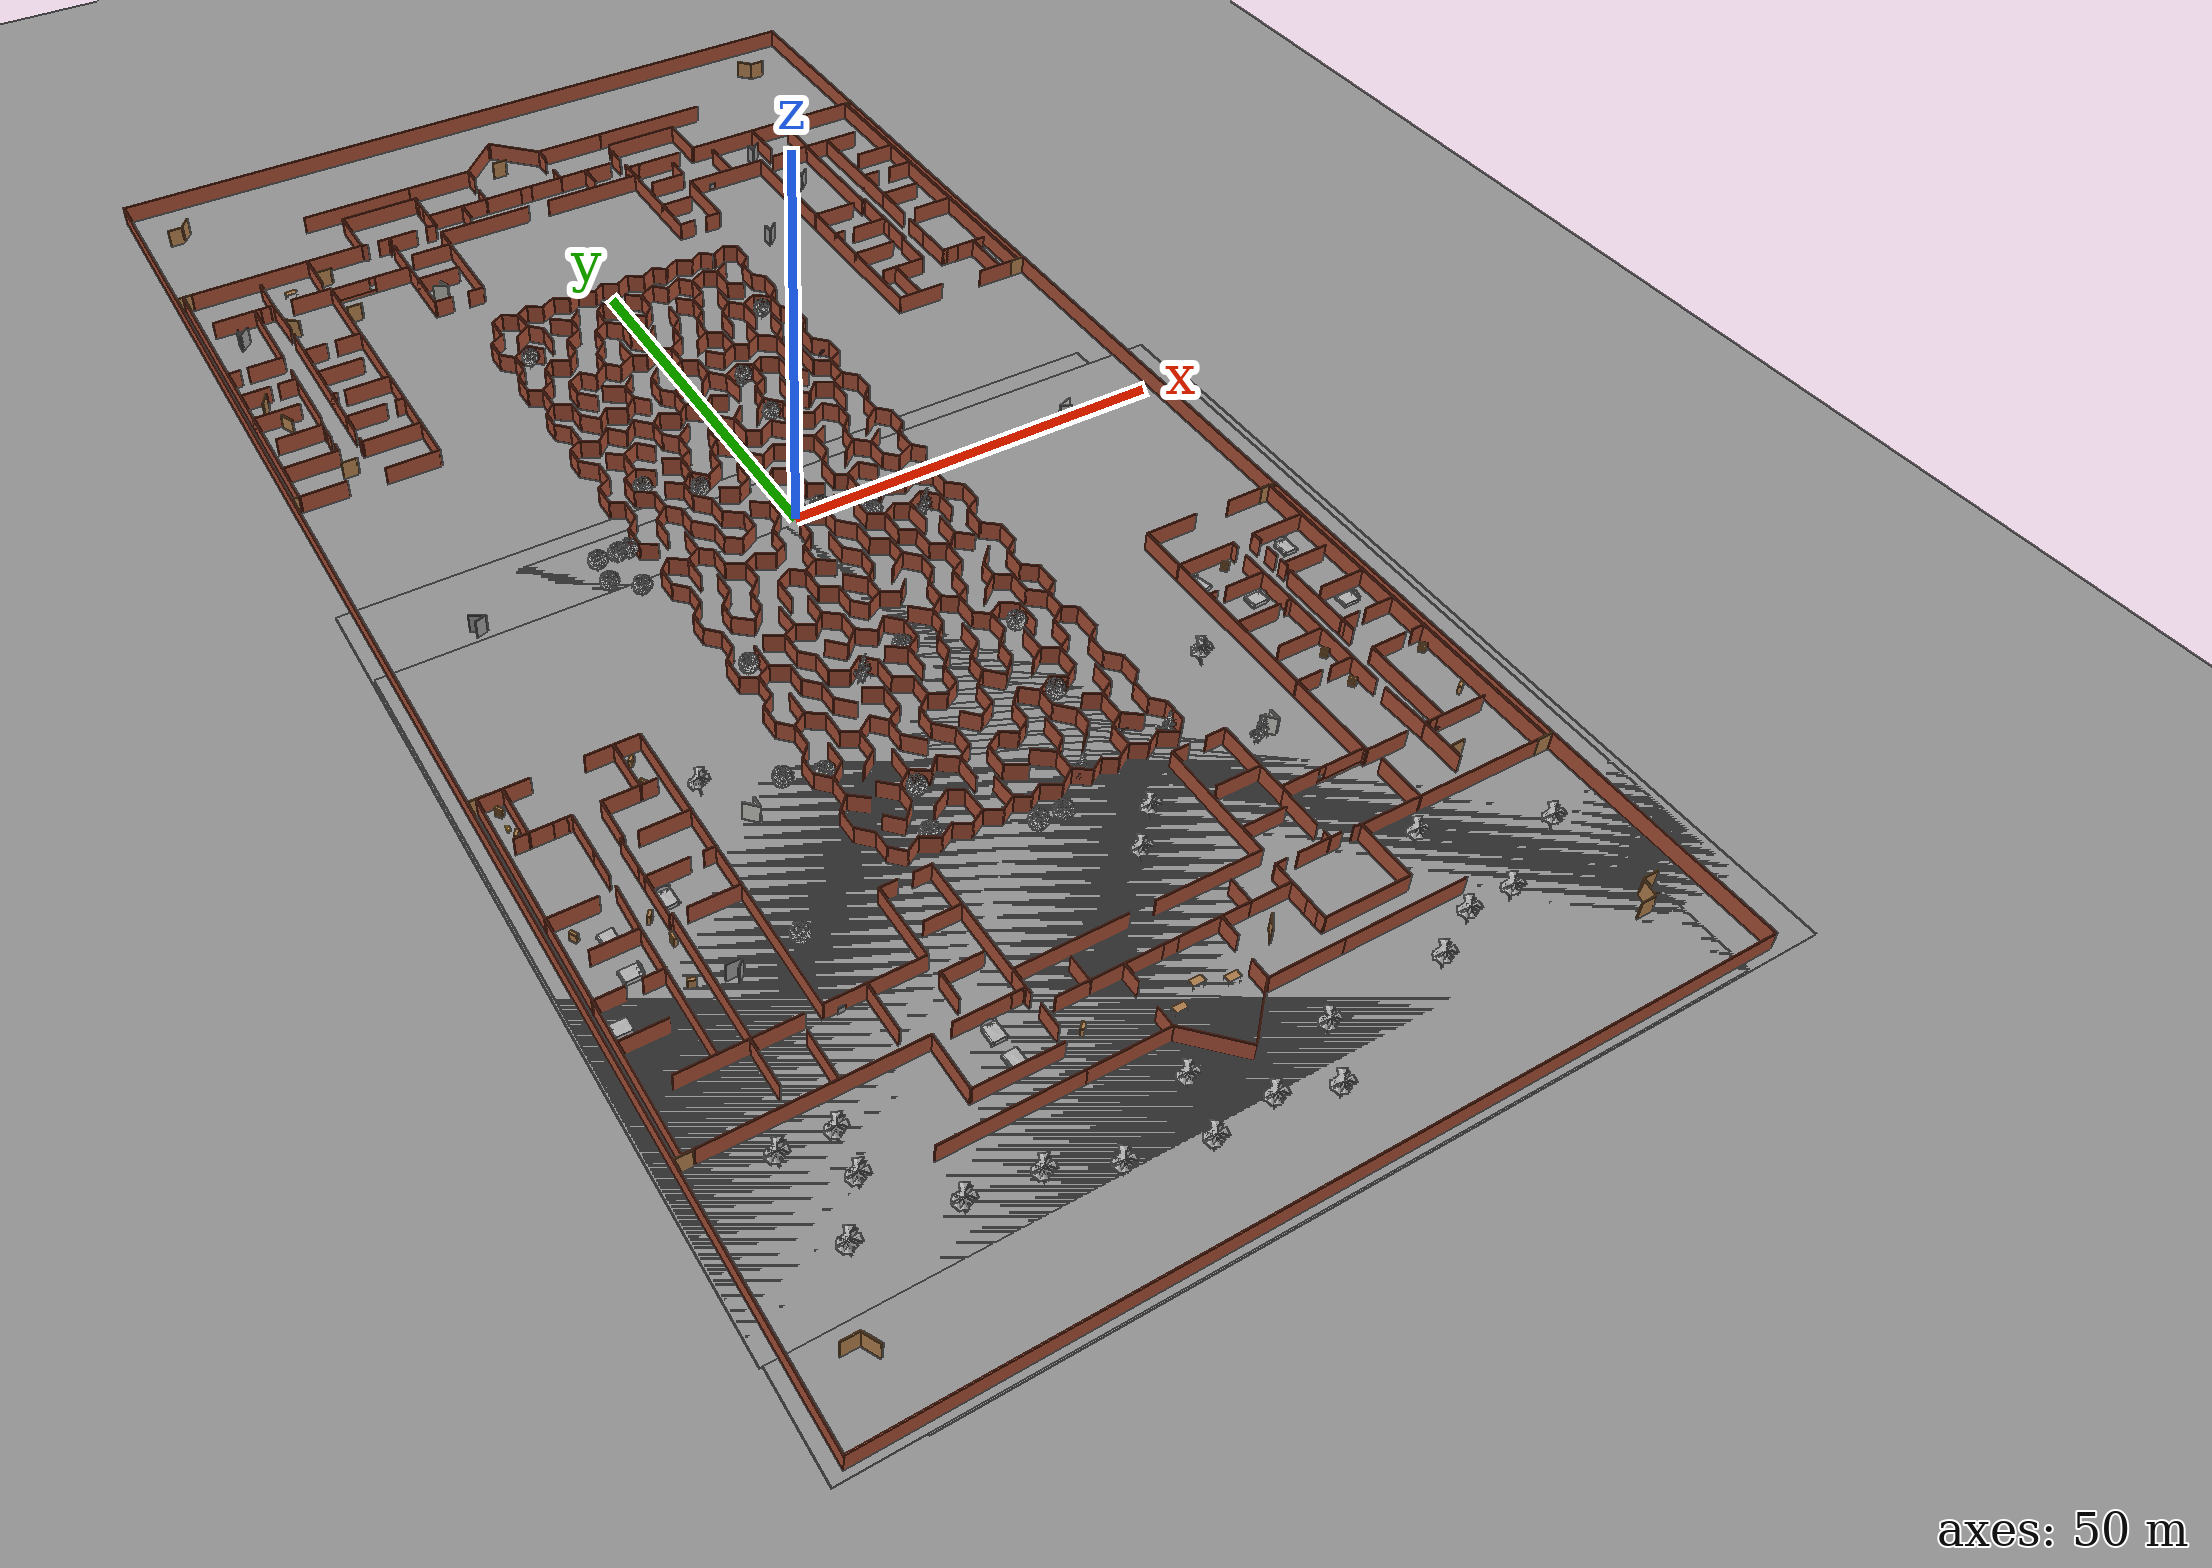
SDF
<sdf version="1.6">
 <world name="default">
  <light name="sun" type="directional">
   <pose>0 0 10 0 -0 0</pose>
   <diffuse>0.8 0.8 0.8 1</diffuse>
   <specular>0.2 0.2 0.2 1</specular>
   <attenuation>
    <range>1000</range>
    <constant>0.9</constant>
    <linear>0.01</linear>
    <quadratic>0.001</quadratic>
   </attenuation>
   <direction>-0.5 0.1 -0.9</direction>
  </light>
  <gravity>0 0 -9.8</gravity>
  <magnetic_field>6e-06 2.3e-05 -4.2e-05</magnetic_field>
  <atmosphere type="adiabatic"/>
  <physics name="default_physics" default="0" type="ode">
   <max_step_size>0.001</max_step_size>
   <real_time_factor>1</real_time_factor>
   <real_time_update_rate>1000</real_time_update_rate>
  </physics>
  <scene><ambient>0.4 0.4 0.4 1</ambient><background>0.7 0.7 0.7 1</background><shadows>1</shadows></scene>
  <audio><device>default</device></audio>
  <spherical_coordinates>
   <surface_model>EARTH_WGS84</surface_model>
   <latitude_deg>0</latitude_deg>
   <longitude_deg>0</longitude_deg>
   <elevation>0</elevation>
   <heading_deg>0</heading_deg>
  </spherical_coordinates>
  <model name="maze_rect_3">
   <pose>4e-06 -9.9e-05 0 0 -0 1.57001</pose>
   <link name="Wall_1">
    <collision name="Wall_1_Collision">
     <geometry><box><size>2.18043 0.15 2.5</size></box></geometry>
     <pose>0 0 1.25 0 -0 0</pose>
    </collision>
    <visual name="Wall_1_Visual">
     <pose>0 0 1.25 0 -0 0</pose>
     <geometry><box><size>2.18043 0.15 2.5</size></box></geometry>
     <material>
      <script><uri>file://media/materials/scripts/gazebo.material</uri><name>Gazebo/Bricks</name></script>
      <ambient>1 1 1 1</ambient>
     </material>
     <meta><layer>0</layer></meta>
    </visual>
    <pose>-2.02099 -17.9406 0 0 -0 2.27087</pose>
   </link>
   <link name="Wall_10">
    <collision name="Wall_10_Collision">
     <geometry><box><size>2.75 0.15 2.5</size></box></geometry>
     <pose>0 0 1.25 0 -0 0</pose>
    </collision>
    <visual name="Wall_10_Visual">
     <pose>0 0 1.25 0 -0 0</pose>
     <geometry><box><size>2.75 0.15 2.5</size></box></geometry>
     <material>
      <script><uri>file://media/materials/scripts/gazebo.material</uri><name>Gazebo/Bricks</name></script>
      <ambient>1 1 1 1</ambient>
     </material>
     <meta><layer>0</layer></meta>
    </visual>
    <pose>-20.3577 -17.0553 0 0 -0 3.14159</pose>
   </link>
   <link name="Wall_100">
    <collision name="Wall_100_Collision">
     <geometry><box><size>3 0.15 2.5</size></box></geometry>
     <pose>0 0 1.25 0 -0 0</pose>
    </collision>
    <visual name="Wall_100_Visual">
     <pose>0 0 1.25 0 -0 0</pose>
     <geometry><box><size>3 0.15 2.5</size></box></geometry>
     <material>
      <script><uri>file://media/materials/scripts/gazebo.material</uri><name>Gazebo/Bricks</name></script>
      <ambient>1 1 1 1</ambient>
     </material>
     <meta><layer>0</layer></meta>
    </visual>
    <pose>8.41531 17.2964 0 0 -0 0</pose>
   </link>
   <link name="Wall_101">
    <collision name="Wall_101_Collision">
     <geometry><box><size>2 0.15 2.5</size></box></geometry>
     <pose>0 0 1.25 0 -0 0</pose>
    </collision>
    <visual name="Wall_101_Visual">
     <pose>0 0 1.25 0 -0 0</pose>
     <geometry><box><size>2 0.15 2.5</size></box></geometry>
     <material>
      <script><uri>file://media/materials/scripts/gazebo.material</uri><name>Gazebo/Bricks</name></script>
      <ambient>1 1 1 1</ambient>
     </material>
     <meta><layer>0</layer></meta>
    </visual>
    <pose>10.3028 18.0975 0 0 -0 1.0472</pose>
   </link>
   <link name="Wall_102">
    <collision name="Wall_102_Collision">
     <geometry><box><size>3 0.15 2.5</size></box></geometry>
     <pose>0 0 1.25 0 -0 0</pose>
    </collision>
    <visual name="Wall_102_Visual">
     <pose>0 0 1.25 0 -0 0</pose>
     <geometry><box><size>3 0.15 2.5</size></box></geometry>
     <material>
      <script><uri>file://media/materials/scripts/gazebo.material</uri><name>Gazebo/Bricks</name></script>
      <ambient>1 1 1 1</ambient>
     </material>
     <meta><layer>0</layer></meta>
    </visual>
    <pose>12.1903 18.8985 0 0 -0 0</pose>
   </link>
   <link name="Wall_103">
    <collision name="Wall_103_Collision">
     <geometry><box><size>2.25 0.15 2.5</size></box></geometry>
     <pose>0 0 1.25 0 -0 0</pose>
    </collision>
    <visual name="Wall_103_Visual">
     <pose>0 0 1.25 0 -0 0</pose>
     <geometry><box><size>2.25 0.15 2.5</size></box></geometry>
     <material>
      <script><uri>file://media/materials/scripts/gazebo.material</uri><name>Gazebo/Bricks</name></script>
      <ambient>1 1 1 1</ambient>
     </material>
     <meta><layer>0</layer></meta>
    </visual>
    <pose>14.1403 17.9892 0 0 -0 -1.0472</pose>
   </link>
   <link name="Wall_104">
    <collision name="Wall_104_Collision">
     <geometry><box><size>3 0.15 2.5</size></box></geometry>
     <pose>0 0 1.25 0 -0 0</pose>
    </collision>
    <visual name="Wall_104_Visual">
     <pose>0 0 1.25 0 -0 0</pose>
     <geometry><box><size>3 0.15 2.5</size></box></geometry>
     <material>
      <script><uri>file://media/materials/scripts/gazebo.material</uri><name>Gazebo/Bricks</name></script>
      <ambient>1 1 1 1</ambient>
     </material>
     <meta><layer>0</layer></meta>
    </visual>
    <pose>16.0903 17.0799 0 0 -0 0</pose>
   </link>
   <link name="Wall_105">
    <collision name="Wall_105_Collision">
     <geometry><box><size>2.75 0.15 2.5</size></box></geometry>
     <pose>0 0 1.25 0 -0 0</pose>
    </collision>
    <visual name="Wall_105_Visual">
     <pose>0 0 1.25 0 -0 0</pose>
     <geometry><box><size>2.75 0.15 2.5</size></box></geometry>
     <material>
      <script><uri>file://media/materials/scripts/gazebo.material</uri><name>Gazebo/Bricks</name></script>
      <ambient>1 1 1 1</ambient>
     </material>
     <meta><layer>0</layer></meta>
    </visual>
    <pose>18.4346 17.9991 0 0 -0 0.785398</pose>
   </link>
   <link name="Wall_106">
    <collision name="Wall_106_Collision">
     <geometry><box><size>2.5 0.15 2.5</size></box></geometry>
     <pose>0 0 1.25 0 -0 0</pose>
    </collision>
    <visual name="Wall_106_Visual">
     <pose>0 0 1.25 0 -0 0</pose>
     <geometry><box><size>2.5 0.15 2.5</size></box></geometry>
     <material>
      <script><uri>file://media/materials/scripts/gazebo.material</uri><name>Gazebo/Bricks</name></script>
      <ambient>1 1 1 1</ambient>
     </material>
     <meta><layer>0</layer></meta>
    </visual>
    <pose>20.5288 18.9183 0 0 -0 0</pose>
   </link>
   <link name="Wall_107">
    <collision name="Wall_107_Collision">
     <geometry><box><size>2.25 0.15 2.5</size></box></geometry>
     <pose>0 0 1.25 0 -0 0</pose>
    </collision>
    <visual name="Wall_107_Visual">
     <pose>0 0 1.25 0 -0 0</pose>
     <geometry><box><size>2.25 0.15 2.5</size></box></geometry>
     <material>
      <script><uri>file://media/materials/scripts/gazebo.material</uri><name>Gazebo/Bricks</name></script>
      <ambient>1 1 1 1</ambient>
     </material>
     <meta><layer>0</layer></meta>
    </visual>
    <pose>22.2288 18.009 0 0 -0 -1.0472</pose>
   </link>
   <link name="Wall_108">
    <collision name="Wall_108_Collision">
     <geometry><box><size>3 0.15 2.5</size></box></geometry>
     <pose>0 0 1.25 0 -0 0</pose>
    </collision>
    <visual name="Wall_108_Visual">
     <pose>0 0 1.25 0 -0 0</pose>
     <geometry><box><size>3 0.15 2.5</size></box></geometry>
     <material>
      <script><uri>file://media/materials/scripts/gazebo.material</uri><name>Gazebo/Bricks</name></script>
      <ambient>1 1 1 1</ambient>
     </material>
     <meta><layer>0</layer></meta>
    </visual>
    <pose>24.1788 17.0997 0 0 -0 0</pose>
   </link>
   <link name="Wall_109">
    <collision name="Wall_109_Collision">
     <geometry><box><size>2.25 0.15 2.5</size></box></geometry>
     <pose>0 0 1.25 0 -0 0</pose>
    </collision>
    <visual name="Wall_109_Visual">
     <pose>0 0 1.25 0 -0 0</pose>
     <geometry><box><size>2.25 0.15 2.5</size></box></geometry>
     <material>
      <script><uri>file://media/materials/scripts/gazebo.material</uri><name>Gazebo/Bricks</name></script>
      <ambient>1 1 1 1</ambient>
     </material>
     <meta><layer>0</layer></meta>
    </visual>
    <pose>26.3463 17.8422 0 0 -0 0.785398</pose>
   </link>
   <link name="Wall_11">
    <collision name="Wall_11_Collision">
     <geometry><box><size>2.37821 0.15 2.5</size></box></geometry>
     <pose>0 0 1.25 0 -0 0</pose>
    </collision>
    <visual name="Wall_11_Visual">
     <pose>0 0 1.25 0 -0 0</pose>
     <geometry><box><size>2.37821 0.15 2.5</size></box></geometry>
     <material>
      <script><uri>file://media/materials/scripts/gazebo.material</uri><name>Gazebo/Bricks</name></script>
      <ambient>1 1 1 1</ambient>
     </material>
     <meta><layer>0</layer></meta>
    </visual>
    <pose>-22.3117 -17.9572 0 0 -0 -2.19825</pose>
   </link>
   <link name="Wall_110">
    <collision name="Wall_110_Collision">
     <geometry><box><size>2.5 0.15 2.5</size></box></geometry>
     <pose>0 0 1.25 0 -0 0</pose>
    </collision>
    <visual name="Wall_110_Visual">
     <pose>0 0 1.25 0 -0 0</pose>
     <geometry><box><size>2.5 0.15 2.5</size></box></geometry>
     <material>
      <script><uri>file://media/materials/scripts/gazebo.material</uri><name>Gazebo/Bricks</name></script>
      <ambient>1 1 1 1</ambient>
     </material>
     <meta><layer>0</layer></meta>
    </visual>
    <pose>28.2637 18.5846 0 0 -0 0</pose>
   </link>
   <link name="Wall_111">
    <collision name="Wall_111_Collision">
     <geometry><box><size>2.25 0.15 2.5</size></box></geometry>
     <pose>0 0 1.25 0 -0 0</pose>
    </collision>
    <visual name="Wall_111_Visual">
     <pose>0 0 1.25 0 -0 0</pose>
     <geometry><box><size>2.25 0.15 2.5</size></box></geometry>
     <material>
      <script><uri>file://media/materials/scripts/gazebo.material</uri><name>Gazebo/Bricks</name></script>
      <ambient>1 1 1 1</ambient>
     </material>
     <meta><layer>0</layer></meta>
    </visual>
    <pose>30.1812 17.8422 0 0 -0 -0.785398</pose>
   </link>
   <link name="Wall_112">
    <collision name="Wall_112_Collision">
     <geometry><box><size>3.25 0.15 2.5</size></box></geometry>
     <pose>0 0 1.25 0 -0 0</pose>
    </collision>
    <visual name="Wall_112_Visual">
     <pose>0 0 1.25 0 -0 0</pose>
     <geometry><box><size>3.25 0.15 2.5</size></box></geometry>
     <material>
      <script><uri>file://media/materials/scripts/gazebo.material</uri><name>Gazebo/Bricks</name></script>
      <ambient>1 1 1 1</ambient>
     </material>
     <meta><layer>0</layer></meta>
    </visual>
    <pose>32.4736 17.0997 0 0 -0 0</pose>
   </link>
   <link name="Wall_113">
    <collision name="Wall_113_Collision">
     <geometry><box><size>2 0.15 2.5</size></box></geometry>
     <pose>0 0 1.25 0 -0 0</pose>
    </collision>
    <visual name="Wall_113_Visual">
     <pose>0 0 1.25 0 -0 0</pose>
     <geometry><box><size>2 0.15 2.5</size></box></geometry>
     <material>
      <script><uri>file://media/materials/scripts/gazebo.material</uri><name>Gazebo/Bricks</name></script>
      <ambient>1 1 1 1</ambient>
     </material>
     <meta><layer>0</layer></meta>
    </visual>
    <pose>34.4861 17.9008 0 0 -0 1.0472</pose>
   </link>
   <link name="Wall_114">
    <collision name="Wall_114_Collision">
     <geometry><box><size>3 0.15 2.5</size></box></geometry>
     <pose>0 0 1.25 0 -0 0</pose>
    </collision>
    <visual name="Wall_114_Visual">
     <pose>0 0 1.25 0 -0 0</pose>
     <geometry><box><size>3 0.15 2.5</size></box></geometry>
     <material>
      <script><uri>file://media/materials/scripts/gazebo.material</uri><name>Gazebo/Bricks</name></script>
      <ambient>1 1 1 1</ambient>
     </material>
     <meta><layer>0</layer></meta>
    </visual>
    <pose>36.3736 18.7018 0 0 -0 0</pose>
   </link>
   <link name="Wall_115">
    <collision name="Wall_115_Collision">
     <geometry><box><size>2 0.15 2.5</size></box></geometry>
     <pose>0 0 1.25 0 -0 0</pose>
    </collision>
    <visual name="Wall_115_Visual">
     <pose>0 0 1.25 0 -0 0</pose>
     <geometry><box><size>2 0.15 2.5</size></box></geometry>
     <material>
      <script><uri>file://media/materials/scripts/gazebo.material</uri><name>Gazebo/Bricks</name></script>
      <ambient>1 1 1 1</ambient>
     </material>
     <meta><layer>0</layer></meta>
    </visual>
    <pose>38.4527 18.0478 0 0 -0 -0.785398</pose>
   </link>
   <link name="Wall_116">
    <collision name="Wall_116_Collision">
     <geometry><box><size>3 0.15 2.5</size></box></geometry>
     <pose>0 0 1.25 0 -0 0</pose>
    </collision>
    <visual name="Wall_116_Visual">
     <pose>0 0 1.25 0 -0 0</pose>
     <geometry><box><size>3 0.15 2.5</size></box></geometry>
     <material>
      <script><uri>file://media/materials/scripts/gazebo.material</uri><name>Gazebo/Bricks</name></script>
      <ambient>1 1 1 1</ambient>
     </material>
     <meta><layer>0</layer></meta>
    </visual>
    <pose>40.5318 17.3937 0 0 -0 0</pose>
   </link>
   <link name="Wall_117">
    <collision name="Wall_117_Collision">
     <geometry><box><size>2.25 0.15 2.5</size></box></geometry>
     <pose>0 0 1.25 0 -0 0</pose>
    </collision>
    <visual name="Wall_117_Visual">
     <pose>0 0 1.25 0 -0 0</pose>
     <geometry><box><size>2.25 0.15 2.5</size></box></geometry>
     <material>
      <script><uri>file://media/materials/scripts/gazebo.material</uri><name>Gazebo/Bricks</name></script>
      <ambient>1 1 1 1</ambient>
     </material>
     <meta><layer>0</layer></meta>
    </visual>
    <pose>42.6993 18.1362 0 0 -0 0.785398</pose>
   </link>
   <link name="Wall_118">
    <collision name="Wall_118_Collision">
     <geometry><box><size>2.75 0.15 2.5</size></box></geometry>
     <pose>0 0 1.25 0 -0 0</pose>
    </collision>
    <visual name="Wall_118_Visual">
     <pose>0 0 1.25 0 -0 0</pose>
     <geometry><box><size>2.75 0.15 2.5</size></box></geometry>
     <material>
      <script><uri>file://media/materials/scripts/gazebo.material</uri><name>Gazebo/Bricks</name></script>
      <ambient>1 1 1 1</ambient>
     </material>
     <meta><layer>0</layer></meta>
    </visual>
    <pose>44.7417 18.8786 0 0 -0 0</pose>
   </link>
   <link name="Wall_119">
    <collision name="Wall_119_Collision">
     <geometry><box><size>2.5 0.15 2.5</size></box></geometry>
     <pose>0 0 1.25 0 -0 0</pose>
    </collision>
    <visual name="Wall_119_Visual">
     <pose>0 0 1.25 0 -0 0</pose>
     <geometry><box><size>2.5 0.15 2.5</size></box></geometry>
     <material>
      <script><uri>file://media/materials/scripts/gazebo.material</uri><name>Gazebo/Bricks</name></script>
      <ambient>1 1 1 1</ambient>
     </material>
     <meta><layer>0</layer></meta>
    </visual>
    <pose>46.6292 17.861 0 0 -0 -1.0472</pose>
   </link>
   <link name="Wall_12">
    <collision name="Wall_12_Collision">
     <geometry><box><size>3 0.15 2.5</size></box></geometry>
     <pose>0 0 1.25 0 -0 0</pose>
    </collision>
    <visual name="Wall_12_Visual">
     <pose>0 0 1.25 0 -0 0</pose>
     <geometry><box><size>3 0.15 2.5</size></box></geometry>
     <material>
      <script><uri>file://media/materials/scripts/gazebo.material</uri><name>Gazebo/Bricks</name></script>
      <ambient>1 1 1 1</ambient>
     </material>
     <meta><layer>0</layer></meta>
    </visual>
    <pose>-24.3908 -18.8069 0 0 -0 3.14159</pose>
   </link>
   <link name="Wall_121">
    <collision name="Wall_121_Collision">
     <geometry><box><size>2.75 0.15 2.5</size></box></geometry>
     <pose>0 0 1.25 0 -0 0</pose>
    </collision>
    <visual name="Wall_121_Visual">
     <pose>0 0 1.25 0 -0 0</pose>
     <geometry><box><size>2.75 0.15 2.5</size></box></geometry>
     <material>
      <script><uri>file://media/materials/scripts/gazebo.material</uri><name>Gazebo/Bricks</name></script>
      <ambient>1 1 1 1</ambient>
     </material>
     <meta><layer>0</layer></meta>
    </visual>
    <pose>48.7841 16.998 0 0 -0 0</pose>
   </link>
   <link name="Wall_122">
    <collision name="Wall_122_Collision">
     <geometry><box><size>2.17873 0.15 2.5</size></box></geometry>
     <pose>0 0 1.25 0 -0 0</pose>
    </collision>
    <visual name="Wall_122_Visual">
     <pose>0 0 1.25 0 -0 0</pose>
     <geometry><box><size>2.17873 0.15 2.5</size></box></geometry>
     <material>
      <script><uri>file://media/materials/scripts/gazebo.material</uri><name>Gazebo/Bricks</name></script>
      <ambient>1 1 1 1</ambient>
     </material>
     <meta><layer>0</layer></meta>
    </visual>
    <pose>50.652 16.1575 0 0 -0 -0.976644</pose>
   </link>
   <link name="Wall_123">
    <collision name="Wall_123_Collision">
     <geometry><box><size>2.25 0.15 2.5</size></box></geometry>
     <pose>0 0 1.25 0 -0 0</pose>
    </collision>
    <visual name="Wall_123_Visual">
     <pose>0 0 1.25 0 -0 0</pose>
     <geometry><box><size>2.25 0.15 2.5</size></box></geometry>
     <material>
      <script><uri>file://media/materials/scripts/gazebo.material</uri><name>Gazebo/Bricks</name></script>
      <ambient>1 1 1 1</ambient>
     </material>
     <meta><layer>0</layer></meta>
    </visual>
    <pose>50.6948 14.4076 0 0 -0 -2.0944</pose>
   </link>
   <link name="Wall_124">
    <collision name="Wall_124_Collision">
     <geometry><box><size>2.28524 0.15 2.5</size></box></geometry>
     <pose>0 0 1.25 0 -0 0</pose>
    </collision>
    <visual name="Wall_124_Visual">
     <pose>0 0 1.25 0 -0 0</pose>
     <geometry><box><size>2.28524 0.15 2.5</size></box></geometry>
     <material>
      <script><uri>file://media/materials/scripts/gazebo.material</uri><name>Gazebo/Bricks</name></script>
      <ambient>1 1 1 1</ambient>
     </material>
     <meta><layer>0</layer></meta>
    </visual>
    <pose>50.744 12.6156 0 0 -0 -0.973411</pose>
   </link>
   <link name="Wall_125">
    <collision name="Wall_125_Collision">
     <geometry><box><size>2.25 0.15 2.5</size></box></geometry>
     <pose>0 0 1.25 0 -0 0</pose>
    </collision>
    <visual name="Wall_125_Visual">
     <pose>0 0 1.25 0 -0 0</pose>
     <geometry><box><size>2.25 0.15 2.5</size></box></geometry>
     <material>
      <script><uri>file://media/materials/scripts/gazebo.material</uri><name>Gazebo/Bricks</name></script>
      <ambient>1 1 1 1</ambient>
     </material>
     <meta><layer>0</layer></meta>
    </visual>
    <pose>50.7932 10.8235 0 0 -0 -2.0944</pose>
   </link>
   <link name="Wall_127">
    <collision name="Wall_127_Collision">
     <geometry><box><size>2.25 0.15 2.5</size></box></geometry>
     <pose>0 0 1.25 0 -0 0</pose>
    </collision>
    <visual name="Wall_127_Visual">
     <pose>0 0 1.25 0 -0 0</pose>
     <geometry><box><size>2.25 0.15 2.5</size></box></geometry>
     <material>
      <script><uri>file://media/materials/scripts/gazebo.material</uri><name>Gazebo/Bricks</name></script>
      <ambient>1 1 1 1</ambient>
     </material>
     <meta><layer>0</layer></meta>
    </visual>
    <pose>50.7967 7.04052 0 0 -0 -2.0944</pose>
   </link>
   <link name="Wall_128">
    <collision name="Wall_128_Collision">
     <geometry><box><size>2 0.15 2.5</size></box></geometry>
     <pose>0 0 1.25 0 -0 0</pose>
    </collision>
    <visual name="Wall_128_Visual">
     <pose>0 0 1.25 0 -0 0</pose>
     <geometry><box><size>2 0.15 2.5</size></box></geometry>
     <material>
      <script><uri>file://media/materials/scripts/gazebo.material</uri><name>Gazebo/Bricks</name></script>
      <ambient>1 1 1 1</ambient>
     </material>
     <meta><layer>0</layer></meta>
    </visual>
    <pose>50.7342 5.33012 0 0 -0 -1.0472</pose>
   </link>
   <link name="Wall_129">
    <collision name="Wall_129_Collision">
     <geometry><box><size>2.5 0.15 2.5</size></box></geometry>
     <pose>0 0 1.25 0 -0 0</pose>
    </collision>
    <visual name="Wall_129_Visual">
     <pose>0 0 1.25 0 -0 0</pose>
     <geometry><box><size>2.5 0.15 2.5</size></box></geometry>
     <material>
      <script><uri>file://media/materials/scripts/gazebo.material</uri><name>Gazebo/Bricks</name></script>
      <ambient>1 1 1 1</ambient>
     </material>
     <meta><layer>0</layer></meta>
    </visual>
    <pose>50.6092 3.51146 0 0 -0 -2.0944</pose>
   </link>
   <link name="Wall_13">
    <collision name="Wall_13_Collision">
     <geometry><box><size>2.13172 0.15 2.5</size></box></geometry>
     <pose>0 0 1.25 0 -0 0</pose>
    </collision>
    <visual name="Wall_13_Visual">
     <pose>0 0 1.25 0 -0 0</pose>
     <geometry><box><size>2.13172 0.15 2.5</size></box></geometry>
     <material>
      <script><uri>file://media/materials/scripts/gazebo.material</uri><name>Gazebo/Bricks</name></script>
      <ambient>1 1 1 1</ambient>
     </material>
     <meta><layer>0</layer></meta>
    </visual>
    <pose>-26.3815 -18.0456 0 0 -0 2.1784</pose>
   </link>
   <link name="Wall_130">
    <collision name="Wall_130_Collision">
     <geometry><box><size>2.03359 0.15 2.5</size></box></geometry>
     <pose>0 0 1.25 0 -0 0</pose>
    </collision>
    <visual name="Wall_130_Visual">
     <pose>0 0 1.25 0 -0 0</pose>
     <geometry><box><size>2.03359 0.15 2.5</size></box></geometry>
     <material>
      <script><uri>file://media/materials/scripts/gazebo.material</uri><name>Gazebo/Bricks</name></script>
      <ambient>1 1 1 1</ambient>
     </material>
     <meta><layer>0</layer></meta>
    </visual>
    <pose>50.6097 1.75817 0 0 -0 -0.896561</pose>
   </link>
   <link name="Wall_131">
    <collision name="Wall_131_Collision">
     <geometry><box><size>2.25 0.15 2.5</size></box></geometry>
     <pose>0 0 1.25 0 -0 0</pose>
    </collision>
    <visual name="Wall_131_Visual">
     <pose>0 0 1.25 0 -0 0</pose>
     <geometry><box><size>2.25 0.15 2.5</size></box></geometry>
     <material>
      <script><uri>file://media/materials/scripts/gazebo.material</uri><name>Gazebo/Bricks</name></script>
      <ambient>1 1 1 1</ambient>
     </material>
     <meta><layer>0</layer></meta>
    </visual>
    <pose>50.6727 0.113126 0 0 -0 -2.0944</pose>
   </link>
   <link name="Wall_132">
    <collision name="Wall_132_Collision">
     <geometry><box><size>2.25 0.15 2.5</size></box></geometry>
     <pose>0 0 1.25 0 -0 0</pose>
    </collision>
    <visual name="Wall_132_Visual">
     <pose>0 0 1.25 0 -0 0</pose>
     <geometry><box><size>2.25 0.15 2.5</size></box></geometry>
     <material>
      <script><uri>file://media/materials/scripts/gazebo.material</uri><name>Gazebo/Bricks</name></script>
      <ambient>1 1 1 1</ambient>
     </material>
     <meta><layer>0</layer></meta>
    </visual>
    <pose>50.6727 -1.79753 0 0 -0 -1.0472</pose>
   </link>
   <link name="Wall_133">
    <collision name="Wall_133_Collision">
     <geometry><box><size>2.2447 0.15 2.5</size></box></geometry>
     <pose>0 0 1.25 0 -0 0</pose>
    </collision>
    <visual name="Wall_133_Visual">
     <pose>0 0 1.25 0 -0 0</pose>
     <geometry><box><size>2.2447 0.15 2.5</size></box></geometry>
     <material>
      <script><uri>file://media/materials/scripts/gazebo.material</uri><name>Gazebo/Bricks</name></script>
      <ambient>1 1 1 1</ambient>
     </material>
     <meta><layer>0</layer></meta>
    </visual>
    <pose>50.6397 -3.59318 0 0 -0 -2.13267</pose>
   </link>
   <link name="Wall_134">
    <collision name="Wall_134_Collision">
     <geometry><box><size>2.25 0.15 2.5</size></box></geometry>
     <pose>0 0 1.25 0 -0 0</pose>
    </collision>
    <visual name="Wall_134_Visual">
     <pose>0 0 1.25 0 -0 0</pose>
     <geometry><box><size>2.25 0.15 2.5</size></box></geometry>
     <material>
      <script><uri>file://media/materials/scripts/gazebo.material</uri><name>Gazebo/Bricks</name></script>
      <ambient>1 1 1 1</ambient>
     </material>
     <meta><layer>0</layer></meta>
    </visual>
    <pose>50.6067 -5.48083 0 0 -0 -1.0472</pose>
   </link>
   <link name="Wall_135">
    <collision name="Wall_135_Collision">
     <geometry><box><size>2.03846 0.15 2.5</size></box></geometry>
     <pose>0 0 1.25 0 -0 0</pose>
    </collision>
    <visual name="Wall_135_Visual">
     <pose>0 0 1.25 0 -0 0</pose>
     <geometry><box><size>2.03846 0.15 2.5</size></box></geometry>
     <material>
      <script><uri>file://media/materials/scripts/gazebo.material</uri><name>Gazebo/Bricks</name></script>
      <ambient>1 1 1 1</ambient>
     </material>
     <meta><layer>0</layer></meta>
    </visual>
    <pose>50.6067 -7.17498 0 0 -0 -2.16037</pose>
   </link>
   <link name="Wall_136">
    <collision name="Wall_136_Collision">
     <geometry><box><size>2.5 0.15 2.5</size></box></geometry>
     <pose>0 0 1.25 0 -0 0</pose>
    </collision>
    <visual name="Wall_136_Visual">
     <pose>0 0 1.25 0 -0 0</pose>
     <geometry><box><size>2.5 0.15 2.5</size></box></geometry>
     <material>
      <script><uri>file://media/materials/scripts/gazebo.material</uri><name>Gazebo/Bricks</name></script>
      <ambient>1 1 1 1</ambient>
     </material>
     <meta><layer>0</layer></meta>
    </visual>
    <pose>50.6692 -8.93138 0 0 -0 -1.0472</pose>
   </link>
   <link name="Wall_137">
    <collision name="Wall_137_Collision">
     <geometry><box><size>2.25 0.15 2.5</size></box></geometry>
     <pose>0 0 1.25 0 -0 0</pose>
    </collision>
    <visual name="Wall_137_Visual">
     <pose>0 0 1.25 0 -0 0</pose>
     <geometry><box><size>2.25 0.15 2.5</size></box></geometry>
     <material>
      <script><uri>file://media/materials/scripts/gazebo.material</uri><name>Gazebo/Bricks</name></script>
      <ambient>1 1 1 1</ambient>
     </material>
     <meta><layer>0</layer></meta>
    </visual>
    <pose>50.7317 -10.8583 0 0 -0 -2.0944</pose>
   </link>
   <link name="Wall_138">
    <collision name="Wall_138_Collision">
     <geometry><box><size>2.25 0.15 2.5</size></box></geometry>
     <pose>0 0 1.25 0 -0 0</pose>
    </collision>
    <visual name="Wall_138_Visual">
     <pose>0 0 1.25 0 -0 0</pose>
     <geometry><box><size>2.25 0.15 2.5</size></box></geometry>
     <material>
      <script><uri>file://media/materials/scripts/gazebo.material</uri><name>Gazebo/Bricks</name></script>
      <ambient>1 1 1 1</ambient>
     </material>
     <meta><layer>0</layer></meta>
    </visual>
    <pose>50.7317 -12.6769 0 0 -0 -1.0472</pose>
   </link>
   <link name="Wall_139">
    <collision name="Wall_139_Collision">
     <geometry><box><size>1.81998 0.15 2.5</size></box></geometry>
     <pose>0 0 1.25 0 -0 0</pose>
    </collision>
    <visual name="Wall_139_Visual">
     <pose>0 0 1.25 0 -0 0</pose>
     <geometry><box><size>1.81998 0.15 2.5</size></box></geometry>
     <material>
      <script><uri>file://media/materials/scripts/gazebo.material</uri><name>Gazebo/Bricks</name></script>
      <ambient>1 1 1 1</ambient>
     </material>
     <meta><layer>0</layer></meta>
    </visual>
    <pose>50.7099 -14.2173 0 0 -0 -2.28481</pose>
   </link>
   <link name="Wall_14">
    <collision name="Wall_14_Collision">
     <geometry><box><size>2.75 0.15 2.5</size></box></geometry>
     <pose>0 0 1.25 0 -0 0</pose>
    </collision>
    <visual name="Wall_14_Visual">
     <pose>0 0 1.25 0 -0 0</pose>
     <geometry><box><size>2.75 0.15 2.5</size></box></geometry>
     <material>
      <script><uri>file://media/materials/scripts/gazebo.material</uri><name>Gazebo/Bricks</name></script>
      <ambient>1 1 1 1</ambient>
     </material>
     <meta><layer>0</layer></meta>
    </visual>
    <pose>-28.2472 -17.2321 0 0 -0 3.14159</pose>
   </link>
   <link name="Wall_142">
    <collision name="Wall_142_Collision">
     <geometry><box><size>2.25 0.15 2.5</size></box></geometry>
     <pose>0 0 1.25 0 -0 0</pose>
    </collision>
    <visual name="Wall_142_Visual">
     <pose>0 0 1.25 0 -0 0</pose>
     <geometry><box><size>2.25 0.15 2.5</size></box></geometry>
     <material>
      <script><uri>file://media/materials/scripts/gazebo.material</uri><name>Gazebo/Bricks</name></script>
      <ambient>1 1 1 1</ambient>
     </material>
     <meta><layer>0</layer></meta>
    </visual>
    <pose>50.5837 -16.0931 0 0 -0 -1.0472</pose>
   </link>
   <link name="Wall_143">
    <collision name="Wall_143_Collision">
     <geometry><box><size>2 0.15 2.5</size></box></geometry>
     <pose>0 0 1.25 0 -0 0</pose>
    </collision>
    <visual name="Wall_143_Visual">
     <pose>0 0 1.25 0 -0 0</pose>
     <geometry><box><size>2 0.15 2.5</size></box></geometry>
     <material>
      <script><uri>file://media/materials/scripts/gazebo.material</uri><name>Gazebo/Bricks</name></script>
      <ambient>1 1 1 1</ambient>
     </material>
     <meta><layer>0</layer></meta>
    </visual>
    <pose>50.6462 -17.8035 0 0 -0 -2.0944</pose>
   </link>
   <link name="Wall_144">
    <collision name="Wall_144_Collision">
     <geometry><box><size>3 0.15 2.5</size></box></geometry>
     <pose>0 0 1.25 0 -0 0</pose>
    </collision>
    <visual name="Wall_144_Visual">
     <pose>0 0 1.25 0 -0 0</pose>
     <geometry><box><size>3 0.15 2.5</size></box></geometry>
     <material>
      <script><uri>file://media/materials/scripts/gazebo.material</uri><name>Gazebo/Bricks</name></script>
      <ambient>1 1 1 1</ambient>
     </material>
     <meta><layer>0</layer></meta>
    </visual>
    <pose>48.7587 -18.6045 0 0 -0 3.14159</pose>
   </link>
   <link name="Wall_145">
    <collision name="Wall_145_Collision">
     <geometry><box><size>2 0.15 2.5</size></box></geometry>
     <pose>0 0 1.25 0 -0 0</pose>
    </collision>
    <visual name="Wall_145_Visual">
     <pose>0 0 1.25 0 -0 0</pose>
     <geometry><box><size>2 0.15 2.5</size></box></geometry>
     <material>
      <script><uri>file://media/materials/scripts/gazebo.material</uri><name>Gazebo/Bricks</name></script>
      <ambient>1 1 1 1</ambient>
     </material>
     <meta><layer>0</layer></meta>
    </visual>
    <pose>46.6796 -17.9505 0 0 -0 2.35619</pose>
   </link>
   <link name="Wall_146">
    <collision name="Wall_146_Collision">
     <geometry><box><size>2.75 0.15 2.5</size></box></geometry>
     <pose>0 0 1.25 0 -0 0</pose>
    </collision>
    <visual name="Wall_146_Visual">
     <pose>0 0 1.25 0 -0 0</pose>
     <geometry><box><size>2.75 0.15 2.5</size></box></geometry>
     <material>
      <script><uri>file://media/materials/scripts/gazebo.material</uri><name>Gazebo/Bricks</name></script>
      <ambient>1 1 1 1</ambient>
     </material>
     <meta><layer>0</layer></meta>
    </visual>
    <pose>44.7255 -17.2964 0 0 -0 3.14159</pose>
   </link>
   <link name="Wall_147">
    <collision name="Wall_147_Collision">
     <geometry><box><size>2 0.15 2.5</size></box></geometry>
     <pose>0 0 1.25 0 -0 0</pose>
    </collision>
    <visual name="Wall_147_Visual">
     <pose>0 0 1.25 0 -0 0</pose>
     <geometry><box><size>2 0.15 2.5</size></box></geometry>
     <material>
      <script><uri>file://media/materials/scripts/gazebo.material</uri><name>Gazebo/Bricks</name></script>
      <ambient>1 1 1 1</ambient>
     </material>
     <meta><layer>0</layer></meta>
    </visual>
    <pose>42.7714 -17.9505 0 0 -0 -2.35619</pose>
   </link>
   <link name="Wall_148">
    <collision name="Wall_148_Collision">
     <geometry><box><size>3 0.15 2.5</size></box></geometry>
     <pose>0 0 1.25 0 -0 0</pose>
    </collision>
    <visual name="Wall_148_Visual">
     <pose>0 0 1.25 0 -0 0</pose>
     <geometry><box><size>3 0.15 2.5</size></box></geometry>
     <material>
      <script><uri>file://media/materials/scripts/gazebo.material</uri><name>Gazebo/Bricks</name></script>
      <ambient>1 1 1 1</ambient>
     </material>
     <meta><layer>0</layer></meta>
    </visual>
    <pose>40.6924 -18.6045 0 0 -0 3.14159</pose>
   </link>
   <link name="Wall_149">
    <collision name="Wall_149_Collision">
     <geometry><box><size>2.25 0.15 2.5</size></box></geometry>
     <pose>0 0 1.25 0 -0 0</pose>
    </collision>
    <visual name="Wall_149_Visual">
     <pose>0 0 1.25 0 -0 0</pose>
     <geometry><box><size>2.25 0.15 2.5</size></box></geometry>
     <material>
      <script><uri>file://media/materials/scripts/gazebo.material</uri><name>Gazebo/Bricks</name></script>
      <ambient>1 1 1 1</ambient>
     </material>
     <meta><layer>0</layer></meta>
    </visual>
    <pose>38.5249 -17.8621 0 0 -0 2.35619</pose>
   </link>
   <link name="Wall_15">
    <collision name="Wall_15_Collision">
     <geometry><box><size>2.11036 0.15 2.5</size></box></geometry>
     <pose>0 0 1.25 0 -0 0</pose>
    </collision>
    <visual name="Wall_15_Visual">
     <pose>0 0 1.25 0 -0 0</pose>
     <geometry><box><size>2.11036 0.15 2.5</size></box></geometry>
     <material>
      <script><uri>file://media/materials/scripts/gazebo.material</uri><name>Gazebo/Bricks</name></script>
      <ambient>1 1 1 1</ambient>
     </material>
     <meta><layer>0</layer></meta>
    </visual>
    <pose>-30.1129 -18.0325 0 0 -0 -2.186</pose>
   </link>
   <link name="Wall_150">
    <collision name="Wall_150_Collision">
     <geometry><box><size>2.75 0.15 2.5</size></box></geometry>
     <pose>0 0 1.25 0 -0 0</pose>
    </collision>
    <visual name="Wall_150_Visual">
     <pose>0 0 1.25 0 -0 0</pose>
     <geometry><box><size>2.75 0.15 2.5</size></box></geometry>
     <material>
      <script><uri>file://media/materials/scripts/gazebo.material</uri><name>Gazebo/Bricks</name></script>
      <ambient>1 1 1 1</ambient>
     </material>
     <meta><layer>0</layer></meta>
    </visual>
    <pose>36.4824 -17.1196 0 0 -0 3.14159</pose>
   </link>
   <link name="Wall_151">
    <collision name="Wall_151_Collision">
     <geometry><box><size>2.25 0.15 2.5</size></box></geometry>
     <pose>0 0 1.25 0 -0 0</pose>
    </collision>
    <visual name="Wall_151_Visual">
     <pose>0 0 1.25 0 -0 0</pose>
     <geometry><box><size>2.25 0.15 2.5</size></box></geometry>
     <material>
      <script><uri>file://media/materials/scripts/gazebo.material</uri><name>Gazebo/Bricks</name></script>
      <ambient>1 1 1 1</ambient>
     </material>
     <meta><layer>0</layer></meta>
    </visual>
    <pose>34.44 -17.8621 0 0 -0 -2.35619</pose>
   </link>
   <link name="Wall_152">
    <collision name="Wall_152_Collision">
     <geometry><box><size>2.75 0.15 2.5</size></box></geometry>
     <pose>0 0 1.25 0 -0 0</pose>
    </collision>
    <visual name="Wall_152_Visual">
     <pose>0 0 1.25 0 -0 0</pose>
     <geometry><box><size>2.75 0.15 2.5</size></box></geometry>
     <material>
      <script><uri>file://media/materials/scripts/gazebo.material</uri><name>Gazebo/Bricks</name></script>
      <ambient>1 1 1 1</ambient>
     </material>
     <meta><layer>0</layer></meta>
    </visual>
    <pose>32.3975 -18.6045 0 0 -0 3.14159</pose>
   </link>
   <link name="Wall_153">
    <collision name="Wall_153_Collision">
     <geometry><box><size>2 0.15 2.5</size></box></geometry>
     <pose>0 0 1.25 0 -0 0</pose>
    </collision>
    <visual name="Wall_153_Visual">
     <pose>0 0 1.25 0 -0 0</pose>
     <geometry><box><size>2 0.15 2.5</size></box></geometry>
     <material>
      <script><uri>file://media/materials/scripts/gazebo.material</uri><name>Gazebo/Bricks</name></script>
      <ambient>1 1 1 1</ambient>
     </material>
     <meta><layer>0</layer></meta>
    </visual>
    <pose>30.4434 -17.9505 0 0 -0 2.35619</pose>
   </link>
   <link name="Wall_154">
    <collision name="Wall_154_Collision">
     <geometry><box><size>2.75 0.15 2.5</size></box></geometry>
     <pose>0 0 1.25 0 -0 0</pose>
    </collision>
    <visual name="Wall_154_Visual">
     <pose>0 0 1.25 0 -0 0</pose>
     <geometry><box><size>2.75 0.15 2.5</size></box></geometry>
     <material>
      <script><uri>file://media/materials/scripts/gazebo.material</uri><name>Gazebo/Bricks</name></script>
      <ambient>1 1 1 1</ambient>
     </material>
     <meta><layer>0</layer></meta>
    </visual>
    <pose>28.4894 -17.2964 0 0 -0 3.14159</pose>
   </link>
   <link name="Wall_155">
    <collision name="Wall_155_Collision">
     <geometry><box><size>2.5 0.15 2.5</size></box></geometry>
     <pose>0 0 1.25 0 -0 0</pose>
    </collision>
    <visual name="Wall_155_Visual">
     <pose>0 0 1.25 0 -0 0</pose>
     <geometry><box><size>2.5 0.15 2.5</size></box></geometry>
     <material>
      <script><uri>file://media/materials/scripts/gazebo.material</uri><name>Gazebo/Bricks</name></script>
      <ambient>1 1 1 1</ambient>
     </material>
     <meta><layer>0</layer></meta>
    </visual>
    <pose>26.3585 -18.1272 0 0 -0 -2.35619</pose>
   </link>
   <link name="Wall_156">
    <collision name="Wall_156_Collision">
     <geometry><box><size>2.75 0.15 2.5</size></box></geometry>
     <pose>0 0 1.25 0 -0 0</pose>
    </collision>
    <visual name="Wall_156_Visual">
     <pose>0 0 1.25 0 -0 0</pose>
     <geometry><box><size>2.75 0.15 2.5</size></box></geometry>
     <material>
      <script><uri>file://media/materials/scripts/gazebo.material</uri><name>Gazebo/Bricks</name></script>
      <ambient>1 1 1 1</ambient>
     </material>
     <meta><layer>0</layer></meta>
    </visual>
    <pose>24.2277 -18.9581 0 0 -0 3.14159</pose>
   </link>
   <link name="Wall_157">
    <collision name="Wall_157_Collision">
     <geometry><box><size>2.25 0.15 2.5</size></box></geometry>
     <pose>0 0 1.25 0 -0 0</pose>
    </collision>
    <visual name="Wall_157_Visual">
     <pose>0 0 1.25 0 -0 0</pose>
     <geometry><box><size>2.25 0.15 2.5</size></box></geometry>
     <material>
      <script><uri>file://media/materials/scripts/gazebo.material</uri><name>Gazebo/Bricks</name></script>
      <ambient>1 1 1 1</ambient>
     </material>
     <meta><layer>0</layer></meta>
    </visual>
    <pose>22.4027 -18.0488 0 0 -0 2.0944</pose>
   </link>
   <link name="Wall_158">
    <collision name="Wall_158_Collision">
     <geometry><box><size>3 0.15 2.5</size></box></geometry>
     <pose>0 0 1.25 0 -0 0</pose>
    </collision>
    <visual name="Wall_158_Visual">
     <pose>0 0 1.25 0 -0 0</pose>
     <geometry><box><size>3 0.15 2.5</size></box></geometry>
     <material>
      <script><uri>file://media/materials/scripts/gazebo.material</uri><name>Gazebo/Bricks</name></script>
      <ambient>1 1 1 1</ambient>
     </material>
     <meta><layer>0</layer></meta>
    </visual>
    <pose>20.4527 -17.1394 0 0 -0 3.14159</pose>
   </link>
   <link name="Wall_159">
    <collision name="Wall_159_Collision">
     <geometry><box><size>2.25 0.15 2.5</size></box></geometry>
     <pose>0 0 1.25 0 -0 0</pose>
    </collision>
    <visual name="Wall_159_Visual">
     <pose>0 0 1.25 0 -0 0</pose>
     <geometry><box><size>2.25 0.15 2.5</size></box></geometry>
     <material>
      <script><uri>file://media/materials/scripts/gazebo.material</uri><name>Gazebo/Bricks</name></script>
      <ambient>1 1 1 1</ambient>
     </material>
     <meta><layer>0</layer></meta>
    </visual>
    <pose>18.2852 -17.8819 0 0 -0 -2.35619</pose>
   </link>
   <link name="Wall_16">
    <collision name="Wall_16_Collision">
     <geometry><box><size>3.5 0.15 2.5</size></box></geometry>
     <pose>0 0 1.25 0 -0 0</pose>
    </collision>
    <visual name="Wall_16_Visual">
     <pose>0 0 1.25 0 -0 0</pose>
     <geometry><box><size>3.5 0.15 2.5</size></box></geometry>
     <material>
      <script><uri>file://media/materials/scripts/gazebo.material</uri><name>Gazebo/Bricks</name></script>
      <ambient>1 1 1 1</ambient>
     </material>
     <meta><layer>0</layer></meta>
    </visual>
    <pose>-32.3535 -18.7808 0 0 -0 3.14159</pose>
   </link>
   <link name="Wall_160">
    <collision name="Wall_160_Collision">
     <geometry><box><size>2.75 0.15 2.5</size></box></geometry>
     <pose>0 0 1.25 0 -0 0</pose>
    </collision>
    <visual name="Wall_160_Visual">
     <pose>0 0 1.25 0 -0 0</pose>
     <geometry><box><size>2.75 0.15 2.5</size></box></geometry>
     <material>
      <script><uri>file://media/materials/scripts/gazebo.material</uri><name>Gazebo/Bricks</name></script>
      <ambient>1 1 1 1</ambient>
     </material>
     <meta><layer>0</layer></meta>
    </visual>
    <pose>16.2427 -18.6244 0 0 -0 3.14159</pose>
   </link>
   <link name="Wall_161">
    <collision name="Wall_161_Collision">
     <geometry><box><size>2.25 0.15 2.5</size></box></geometry>
     <pose>0 0 1.25 0 -0 0</pose>
    </collision>
    <visual name="Wall_161_Visual">
     <pose>0 0 1.25 0 -0 0</pose>
     <geometry><box><size>2.25 0.15 2.5</size></box></geometry>
     <material>
      <script><uri>file://media/materials/scripts/gazebo.material</uri><name>Gazebo/Bricks</name></script>
      <ambient>1 1 1 1</ambient>
     </material>
     <meta><layer>0</layer></meta>
    </visual>
    <pose>14.2003 -17.8819 0 0 -0 2.35619</pose>
   </link>
   <link name="Wall_162">
    <collision name="Wall_162_Collision">
     <geometry><box><size>2.75 0.15 2.5</size></box></geometry>
     <pose>0 0 1.25 0 -0 0</pose>
    </collision>
    <visual name="Wall_162_Visual">
     <pose>0 0 1.25 0 -0 0</pose>
     <geometry><box><size>2.75 0.15 2.5</size></box></geometry>
     <material>
      <script><uri>file://media/materials/scripts/gazebo.material</uri><name>Gazebo/Bricks</name></script>
      <ambient>1 1 1 1</ambient>
     </material>
     <meta><layer>0</layer></meta>
    </visual>
    <pose>12.1578 -17.1394 0 0 -0 3.14159</pose>
   </link>
   <link name="Wall_163">
    <collision name="Wall_163_Collision">
     <geometry><box><size>2.25 0.15 2.5</size></box></geometry>
     <pose>0 0 1.25 0 -0 0</pose>
    </collision>
    <visual name="Wall_163_Visual">
     <pose>0 0 1.25 0 -0 0</pose>
     <geometry><box><size>2.25 0.15 2.5</size></box></geometry>
     <material>
      <script><uri>file://media/materials/scripts/gazebo.material</uri><name>Gazebo/Bricks</name></script>
      <ambient>1 1 1 1</ambient>
     </material>
     <meta><layer>0</layer></meta>
    </visual>
    <pose>10.1153 -17.8819 0 0 -0 -2.35619</pose>
   </link>
   <link name="Wall_164">
    <collision name="Wall_164_Collision">
     <geometry><box><size>2.75 0.15 2.5</size></box></geometry>
     <pose>0 0 1.25 0 -0 0</pose>
    </collision>
    <visual name="Wall_164_Visual">
     <pose>0 0 1.25 0 -0 0</pose>
     <geometry><box><size>2.75 0.15 2.5</size></box></geometry>
     <material>
      <script><uri>file://media/materials/scripts/gazebo.material</uri><name>Gazebo/Bricks</name></script>
      <ambient>1 1 1 1</ambient>
     </material>
     <meta><layer>0</layer></meta>
    </visual>
    <pose>8.07288 -18.6244 0 0 -0 3.14159</pose>
   </link>
   <link name="Wall_165">
    <collision name="Wall_165_Collision">
     <geometry><box><size>2 0.15 2.5</size></box></geometry>
     <pose>0 0 1.25 0 -0 0</pose>
    </collision>
    <visual name="Wall_165_Visual">
     <pose>0 0 1.25 0 -0 0</pose>
     <geometry><box><size>2 0.15 2.5</size></box></geometry>
     <material>
      <script><uri>file://media/materials/scripts/gazebo.material</uri><name>Gazebo/Bricks</name></script>
      <ambient>1 1 1 1</ambient>
     </material>
     <meta><layer>0</layer></meta>
    </visual>
    <pose>6.11881 -17.9703 0 0 -0 2.35619</pose>
   </link>
   <link name="Wall_166">
    <collision name="Wall_166_Collision">
     <geometry><box><size>3 0.15 2.5</size></box></geometry>
     <pose>0 0 1.25 0 -0 0</pose>
    </collision>
    <visual name="Wall_166_Visual">
     <pose>0 0 1.25 0 -0 0</pose>
     <geometry><box><size>3 0.15 2.5</size></box></geometry>
     <material>
      <script><uri>file://media/materials/scripts/gazebo.material</uri><name>Gazebo/Bricks</name></script>
      <ambient>1 1 1 1</ambient>
     </material>
     <meta><layer>0</layer></meta>
    </visual>
    <pose>4.03974 -17.3162 0 0 -0 3.14159</pose>
   </link>
   <link name="Wall_167">
    <collision name="Wall_167_Collision">
     <geometry><box><size>2 0.15 2.5</size></box></geometry>
     <pose>0 0 1.25 0 -0 0</pose>
    </collision>
    <visual name="Wall_167_Visual">
     <pose>0 0 1.25 0 -0 0</pose>
     <geometry><box><size>2 0.15 2.5</size></box></geometry>
     <material>
      <script><uri>file://media/materials/scripts/gazebo.material</uri><name>Gazebo/Bricks</name></script>
      <ambient>1 1 1 1</ambient>
     </material>
     <meta><layer>0</layer></meta>
    </visual>
    <pose>1.96066 -17.9703 0 0 -0 -2.35619</pose>
   </link>
   <link name="Wall_17">
    <collision name="Wall_17_Collision">
     <geometry><box><size>2.11036 0.15 2.5</size></box></geometry>
     <pose>0 0 1.25 0 -0 0</pose>
    </collision>
    <visual name="Wall_17_Visual">
     <pose>0 0 1.25 0 -0 0</pose>
     <geometry><box><size>2.11036 0.15 2.5</size></box></geometry>
     <material>
      <script><uri>file://media/materials/scripts/gazebo.material</uri><name>Gazebo/Bricks</name></script>
      <ambient>1 1 1 1</ambient>
     </material>
     <meta><layer>0</layer></meta>
    </visual>
    <pose>-34.5942 -18.0325 0 0 -0 2.186</pose>
   </link>
   <link name="Wall_172">
    <collision name="Wall_172_Collision">
     <geometry><box><size>2.82454 0.15 2.5</size></box></geometry>
     <pose>0 0 1.25 0 -0 0</pose>
    </collision>
    <visual name="Wall_172_Visual">
     <pose>0 0 1.25 0 -0 0</pose>
     <geometry><box><size>2.82454 0.15 2.5</size></box></geometry>
     <material>
      <script><uri>file://media/materials/scripts/gazebo.material</uri><name>Gazebo/Bricks</name></script>
      <ambient>1 1 1 1</ambient>
     </material>
     <meta><layer>0</layer></meta>
    </visual>
    <pose>10.0301 -16.0891 0 0 -0 -0.90341</pose>
   </link>
   <link name="Wall_174">
    <collision name="Wall_174_Collision">
     <geometry><box><size>3 0.15 2.5</size></box></geometry>
     <pose>0 0 1.25 0 -0 0</pose>
    </collision>
    <visual name="Wall_174_Visual">
     <pose>0 0 1.25 0 -0 0</pose>
     <geometry><box><size>3 0.15 2.5</size></box></geometry>
     <material>
      <script><uri>file://media/materials/scripts/gazebo.material</uri><name>Gazebo/Bricks</name></script>
      <ambient>1 1 1 1</ambient>
     </material>
     <meta><layer>0</layer></meta>
    </visual>
    <pose>20.4205 -9.90743 0 0 -0 3.14159</pose>
   </link>
   <link name="Wall_175">
    <collision name="Wall_175_Collision">
     <geometry><box><size>2.5 0.15 2.5</size></box></geometry>
     <pose>0 0 1.25 0 -0 0</pose>
    </collision>
    <visual name="Wall_175_Visual">
     <pose>0 0 1.25 0 -0 0</pose>
     <geometry><box><size>2.5 0.15 2.5</size></box></geometry>
     <material>
      <script><uri>file://media/materials/scripts/gazebo.material</uri><name>Gazebo/Bricks</name></script>
      <ambient>1 1 1 1</ambient>
     </material>
     <meta><layer>0</layer></meta>
    </visual>
    <pose>18.1647 -10.7383 0 0 -0 -2.35619</pose>
   </link>
   <link name="Wall_176">
    <collision name="Wall_176_Collision">
     <geometry><box><size>2.5 0.15 2.5</size></box></geometry>
     <pose>0 0 1.25 0 -0 0</pose>
    </collision>
    <visual name="Wall_176_Visual">
     <pose>0 0 1.25 0 -0 0</pose>
     <geometry><box><size>2.5 0.15 2.5</size></box></geometry>
     <material>
      <script><uri>file://media/materials/scripts/gazebo.material</uri><name>Gazebo/Bricks</name></script>
      <ambient>1 1 1 1</ambient>
     </material>
     <meta><layer>0</layer></meta>
    </visual>
    <pose>18.1647 -12.4 0 0 -0 -0.785398</pose>
   </link>
   <link name="Wall_177">
    <collision name="Wall_177_Collision">
     <geometry><box><size>2.5 0.15 2.5</size></box></geometry>
     <pose>0 0 1.25 0 -0 0</pose>
    </collision>
    <visual name="Wall_177_Visual">
     <pose>0 0 1.25 0 -0 0</pose>
     <geometry><box><size>2.5 0.15 2.5</size></box></geometry>
     <material>
      <script><uri>file://media/materials/scripts/gazebo.material</uri><name>Gazebo/Bricks</name></script>
      <ambient>1 1 1 1</ambient>
     </material>
     <meta><layer>0</layer></meta>
    </visual>
    <pose>18.408 -14.2484 0 0 -0 -2.0944</pose>
   </link>
   <link name="Wall_178">
    <collision name="Wall_178_Collision">
     <geometry><box><size>2.37866 0.15 2.5</size></box></geometry>
     <pose>0 0 1.25 0 -0 0</pose>
    </collision>
    <visual name="Wall_178_Visual">
     <pose>0 0 1.25 0 -0 0</pose>
     <geometry><box><size>2.37866 0.15 2.5</size></box></geometry>
     <material>
      <script><uri>file://media/materials/scripts/gazebo.material</uri><name>Gazebo/Bricks</name></script>
      <ambient>1 1 1 1</ambient>
     </material>
     <meta><layer>0</layer></meta>
    </visual>
    <pose>18.4241 -16.2027 0 0 -0 -0.998415</pose>
   </link>
   <link name="Wall_18">
    <collision name="Wall_18_Collision">
     <geometry><box><size>2.75 0.15 2.5</size></box></geometry>
     <pose>0 0 1.25 0 -0 0</pose>
    </collision>
    <visual name="Wall_18_Visual">
     <pose>0 0 1.25 0 -0 0</pose>
     <geometry><box><size>2.75 0.15 2.5</size></box></geometry>
     <material>
      <script><uri>file://media/materials/scripts/gazebo.material</uri><name>Gazebo/Bricks</name></script>
      <ambient>1 1 1 1</ambient>
     </material>
     <meta><layer>0</layer></meta>
    </visual>
    <pose>-36.4599 -17.2321 0 0 -0 3.14159</pose>
   </link>
   <link name="Wall_180">
    <collision name="Wall_180_Collision">
     <geometry><box><size>3.32014 0.15 2.5</size></box></geometry>
     <pose>0 0 1.25 0 -0 0</pose>
    </collision>
    <visual name="Wall_180_Visual">
     <pose>0 0 1.25 0 -0 0</pose>
     <geometry><box><size>3.32014 0.15 2.5</size></box></geometry>
     <material>
      <script><uri>file://media/materials/scripts/gazebo.material</uri><name>Gazebo/Bricks</name></script>
      <ambient>1 1 1 1</ambient>
     </material>
     <meta><layer>0</layer></meta>
    </visual>
    <pose>16.2358 -15.2317 0 0 -0 -0.021629</pose>
   </link>
   <link name="Wall_182">
    <collision name="Wall_182_Collision">
     <geometry><box><size>2.62796 0.15 2.5</size></box></geometry>
     <pose>0 0 1.25 0 -0 0</pose>
    </collision>
    <visual name="Wall_182_Visual">
     <pose>0 0 1.25 0 -0 0</pose>
     <geometry><box><size>2.62796 0.15 2.5</size></box></geometry>
     <material>
      <script><uri>file://media/materials/scripts/gazebo.material</uri><name>Gazebo/Bricks</name></script>
      <ambient>1 1 1 1</ambient>
     </material>
     <meta><layer>0</layer></meta>
    </visual>
    <pose>6.07983 -10.7544 0 0 -0 -0.877305</pose>
   </link>
   <link name="Wall_183">
    <collision name="Wall_183_Collision">
     <geometry><box><size>2.3979 0.15 2.5</size></box></geometry>
     <pose>0 0 1.25 0 -0 0</pose>
    </collision>
    <visual name="Wall_183_Visual">
     <pose>0 0 1.25 0 -0 0</pose>
     <geometry><box><size>2.3979 0.15 2.5</size></box></geometry>
     <material>
      <script><uri>file://media/materials/scripts/gazebo.material</uri><name>Gazebo/Bricks</name></script>
      <ambient>1 1 1 1</ambient>
     </material>
     <meta><layer>0</layer></meta>
    </visual>
    <pose>6.17943 -12.5741 0 0 -0 -2.26074</pose>
   </link>
   <link name="Wall_184">
    <collision name="Wall_184_Collision">
     <geometry><box><size>2.66716 0.15 2.5</size></box></geometry>
     <pose>0 0 1.25 0 -0 0</pose>
    </collision>
    <visual name="Wall_184_Visual">
     <pose>0 0 1.25 0 -0 0</pose>
     <geometry><box><size>2.66716 0.15 2.5</size></box></geometry>
     <material>
      <script><uri>file://media/materials/scripts/gazebo.material</uri><name>Gazebo/Bricks</name></script>
      <ambient>1 1 1 1</ambient>
     </material>
     <meta><layer>0</layer></meta>
    </visual>
    <pose>4.18279 -13.4697 0 0 -0 -3.11875</pose>
   </link>
   <link name="Wall_185">
    <collision name="Wall_185_Collision">
     <geometry><box><size>2.25 0.15 2.5</size></box></geometry>
     <pose>0 0 1.25 0 -0 0</pose>
    </collision>
    <visual name="Wall_185_Visual">
     <pose>0 0 1.25 0 -0 0</pose>
     <geometry><box><size>2.25 0.15 2.5</size></box></geometry>
     <material>
      <script><uri>file://media/materials/scripts/gazebo.material</uri><name>Gazebo/Bricks</name></script>
      <ambient>1 1 1 1</ambient>
     </material>
     <meta><layer>0</layer></meta>
    </visual>
    <pose>2.18208 -14.241 0 0 -0 -2.35619</pose>
   </link>
   <link name="Wall_186">
    <collision name="Wall_186_Collision">
     <geometry><box><size>2.76205 0.15 2.5</size></box></geometry>
     <pose>0 0 1.25 0 -0 0</pose>
    </collision>
    <visual name="Wall_186_Visual">
     <pose>0 0 1.25 0 -0 0</pose>
     <geometry><box><size>2.76205 0.15 2.5</size></box></geometry>
     <material>
      <script><uri>file://media/materials/scripts/gazebo.material</uri><name>Gazebo/Bricks</name></script>
      <ambient>1 1 1 1</ambient>
     </material>
     <meta><layer>0</layer></meta>
    </visual>
    <pose>2.02718 -16.1498 0 0 -0 -1.10416</pose>
   </link>
   <link name="Wall_188">
    <collision name="Wall_188_Collision">
     <geometry><box><size>2.64871 0.15 2.5</size></box></geometry>
     <pose>0 0 1.25 0 -0 0</pose>
    </collision>
    <visual name="Wall_188_Visual">
     <pose>0 0 1.25 0 -0 0</pose>
     <geometry><box><size>2.64871 0.15 2.5</size></box></geometry>
     <material>
      <script><uri>file://media/materials/scripts/gazebo.material</uri><name>Gazebo/Bricks</name></script>
      <ambient>1 1 1 1</ambient>
     </material>
     <meta><layer>0</layer></meta>
    </visual>
    <pose>6.21084 -14.425 0 0 -0 2.23465</pose>
   </link>
   <link name="Wall_19">
    <collision name="Wall_19_Collision">
     <geometry><box><size>2.25 0.15 2.5</size></box></geometry>
     <pose>0 0 1.25 0 -0 0</pose>
    </collision>
    <visual name="Wall_19_Visual">
     <pose>0 0 1.25 0 -0 0</pose>
     <geometry><box><size>2.25 0.15 2.5</size></box></geometry>
     <material>
      <script><uri>file://media/materials/scripts/gazebo.material</uri><name>Gazebo/Bricks</name></script>
      <ambient>1 1 1 1</ambient>
     </material>
     <meta><layer>0</layer></meta>
    </visual>
    <pose>-38.5024 -17.9745 0 0 -0 -2.35619</pose>
   </link>
   <link name="Wall_190">
    <collision name="Wall_190_Collision">
     <geometry><box><size>2.75 0.15 2.5</size></box></geometry>
     <pose>0 0 1.25 0 -0 0</pose>
    </collision>
    <visual name="Wall_190_Visual">
     <pose>0 0 1.25 0 -0 0</pose>
     <geometry><box><size>2.75 0.15 2.5</size></box></geometry>
     <material>
      <script><uri>file://media/materials/scripts/gazebo.material</uri><name>Gazebo/Bricks</name></script>
      <ambient>1 1 1 1</ambient>
     </material>
     <meta><layer>0</layer></meta>
    </visual>
    <pose>18.3212 -5.11347 0 0 -0 -0.785398</pose>
   </link>
   <link name="Wall_191">
    <collision name="Wall_191_Collision">
     <geometry><box><size>2.75 0.15 2.5</size></box></geometry>
     <pose>0 0 1.25 0 -0 0</pose>
    </collision>
    <visual name="Wall_191_Visual">
     <pose>0 0 1.25 0 -0 0</pose>
     <geometry><box><size>2.75 0.15 2.5</size></box></geometry>
     <material>
      <script><uri>file://media/materials/scripts/gazebo.material</uri><name>Gazebo/Bricks</name></script>
      <ambient>1 1 1 1</ambient>
     </material>
     <meta><layer>0</layer></meta>
    </visual>
    <pose>18.3212 -6.95194 0 0 -0 -2.35619</pose>
   </link>
   <link name="Wall_192">
    <collision name="Wall_192_Collision">
     <geometry><box><size>2.5 0.15 2.5</size></box></geometry>
     <pose>0 0 1.25 0 -0 0</pose>
    </collision>
    <visual name="Wall_192_Visual">
     <pose>0 0 1.25 0 -0 0</pose>
     <geometry><box><size>2.5 0.15 2.5</size></box></geometry>
     <material>
      <script><uri>file://media/materials/scripts/gazebo.material</uri><name>Gazebo/Bricks</name></script>
      <ambient>1 1 1 1</ambient>
     </material>
     <meta><layer>0</layer></meta>
    </visual>
    <pose>16.2269 -7.87118 0 0 -0 3.14159</pose>
   </link>
   <link name="Wall_193">
    <collision name="Wall_193_Collision">
     <geometry><box><size>2.75 0.15 2.5</size></box></geometry>
     <pose>0 0 1.25 0 -0 0</pose>
    </collision>
    <visual name="Wall_193_Visual">
     <pose>0 0 1.25 0 -0 0</pose>
     <geometry><box><size>2.75 0.15 2.5</size></box></geometry>
     <material>
      <script><uri>file://media/materials/scripts/gazebo.material</uri><name>Gazebo/Bricks</name></script>
      <ambient>1 1 1 1</ambient>
     </material>
     <meta><layer>0</layer></meta>
    </visual>
    <pose>14.4019 -8.99702 0 0 -0 -2.0944</pose>
   </link>
   <link name="Wall_194">
    <collision name="Wall_194_Collision">
     <geometry><box><size>2.25 0.15 2.5</size></box></geometry>
     <pose>0 0 1.25 0 -0 0</pose>
    </collision>
    <visual name="Wall_194_Visual">
     <pose>0 0 1.25 0 -0 0</pose>
     <geometry><box><size>2.25 0.15 2.5</size></box></geometry>
     <material>
      <script><uri>file://media/materials/scripts/gazebo.material</uri><name>Gazebo/Bricks</name></script>
      <ambient>1 1 1 1</ambient>
     </material>
     <meta><layer>0</layer></meta>
    </visual>
    <pose>14.2769 -11.0322 0 0 -0 -1.0472</pose>
   </link>
   <link name="Wall_195">
    <collision name="Wall_195_Collision">
     <geometry><box><size>2.25 0.15 2.5</size></box></geometry>
     <pose>0 0 1.25 0 -0 0</pose>
    </collision>
    <visual name="Wall_195_Visual">
     <pose>0 0 1.25 0 -0 0</pose>
     <geometry><box><size>2.25 0.15 2.5</size></box></geometry>
     <material>
      <script><uri>file://media/materials/scripts/gazebo.material</uri><name>Gazebo/Bricks</name></script>
      <ambient>1 1 1 1</ambient>
     </material>
     <meta><layer>0</layer></meta>
    </visual>
    <pose>14.0595 -12.684 0 0 -0 -2.35619</pose>
   </link>
   <link name="Wall_196">
    <collision name="Wall_196_Collision">
     <geometry><box><size>2.5 0.15 2.5</size></box></geometry>
     <pose>0 0 1.25 0 -0 0</pose>
    </collision>
    <visual name="Wall_196_Visual">
     <pose>0 0 1.25 0 -0 0</pose>
     <geometry><box><size>2.5 0.15 2.5</size></box></geometry>
     <material>
      <script><uri>file://media/materials/scripts/gazebo.material</uri><name>Gazebo/Bricks</name></script>
      <ambient>1 1 1 1</ambient>
     </material>
     <meta><layer>0</layer></meta>
    </visual>
    <pose>12.142 -13.4264 0 0 -0 3.14159</pose>
   </link>
   <link name="Wall_197">
    <collision name="Wall_197_Collision">
     <geometry><box><size>2.5 0.15 2.5</size></box></geometry>
     <pose>0 0 1.25 0 -0 0</pose>
    </collision>
    <visual name="Wall_197_Visual">
     <pose>0 0 1.25 0 -0 0</pose>
     <geometry><box><size>2.5 0.15 2.5</size></box></geometry>
     <material>
      <script><uri>file://media/materials/scripts/gazebo.material</uri><name>Gazebo/Bricks</name></script>
      <ambient>1 1 1 1</ambient>
     </material>
     <meta><layer>0</layer></meta>
    </visual>
    <pose>10.1362 -12.5956 0 0 -0 2.35619</pose>
   </link>
   <link name="Wall_198">
    <collision name="Wall_198_Collision">
     <geometry><box><size>2.58418 0.15 2.5</size></box></geometry>
     <pose>0 0 1.25 0 -0 0</pose>
    </collision>
    <visual name="Wall_198_Visual">
     <pose>0 0 1.25 0 -0 0</pose>
     <geometry><box><size>2.58418 0.15 2.5</size></box></geometry>
     <material>
      <script><uri>file://media/materials/scripts/gazebo.material</uri><name>Gazebo/Bricks</name></script>
      <ambient>1 1 1 1</ambient>
     </material>
     <meta><layer>0</layer></meta>
    </visual>
    <pose>8.08856 -11.736 0 0 -0 3.11797</pose>
   </link>
   <link name="Wall_2">
    <collision name="Wall_2_Collision">
     <geometry><box><size>2.75 0.15 2.5</size></box></geometry>
     <pose>0 0 1.25 0 -0 0</pose>
    </collision>
    <visual name="Wall_2_Visual">
     <pose>0 0 1.25 0 -0 0</pose>
     <geometry><box><size>2.75 0.15 2.5</size></box></geometry>
     <material>
      <script><uri>file://media/materials/scripts/gazebo.material</uri><name>Gazebo/Bricks</name></script>
      <ambient>1 1 1 1</ambient>
     </material>
     <meta><layer>0</layer></meta>
    </visual>
    <pose>-3.97506 -17.2253 0 0 -0 3.14159</pose>
   </link>
   <link name="Wall_20">
    <collision name="Wall_20_Collision">
     <geometry><box><size>2.75 0.15 2.5</size></box></geometry>
     <pose>0 0 1.25 0 -0 0</pose>
    </collision>
    <visual name="Wall_20_Visual">
     <pose>0 0 1.25 0 -0 0</pose>
     <geometry><box><size>2.75 0.15 2.5</size></box></geometry>
     <material>
      <script><uri>file://media/materials/scripts/gazebo.material</uri><name>Gazebo/Bricks</name></script>
      <ambient>1 1 1 1</ambient>
     </material>
     <meta><layer>0</layer></meta>
    </visual>
    <pose>-40.5448 -18.717 0 0 -0 3.14159</pose>
   </link>
   <link name="Wall_200">
    <collision name="Wall_200_Collision">
     <geometry><box><size>2.75 0.15 2.5</size></box></geometry>
     <pose>0 0 1.25 0 -0 0</pose>
    </collision>
    <visual name="Wall_200_Visual">
     <pose>0 0 1.25 0 -0 0</pose>
     <geometry><box><size>2.75 0.15 2.5</size></box></geometry>
     <material>
      <script><uri>file://media/materials/scripts/gazebo.material</uri><name>Gazebo/Bricks</name></script>
      <ambient>1 1 1 1</ambient>
     </material>
     <meta><layer>0</layer></meta>
    </visual>
    <pose>22.3945 -12.6912 0 0 -0 0.785398</pose>
   </link>
   <link name="Wall_201">
    <collision name="Wall_201_Collision">
     <geometry><box><size>2.5 0.15 2.5</size></box></geometry>
     <pose>0 0 1.25 0 -0 0</pose>
    </collision>
    <visual name="Wall_201_Visual">
     <pose>0 0 1.25 0 -0 0</pose>
     <geometry><box><size>2.5 0.15 2.5</size></box></geometry>
     <material>
      <script><uri>file://media/materials/scripts/gazebo.material</uri><name>Gazebo/Bricks</name></script>
      <ambient>1 1 1 1</ambient>
     </material>
     <meta><layer>0</layer></meta>
    </visual>
    <pose>24.4887 -11.772 0 0 -0 0</pose>
   </link>
   <link name="Wall_202">
    <collision name="Wall_202_Collision">
     <geometry><box><size>2.5 0.15 2.5</size></box></geometry>
     <pose>0 0 1.25 0 -0 0</pose>
    </collision>
    <visual name="Wall_202_Visual">
     <pose>0 0 1.25 0 -0 0</pose>
     <geometry><box><size>2.5 0.15 2.5</size></box></geometry>
     <material>
      <script><uri>file://media/materials/scripts/gazebo.material</uri><name>Gazebo/Bricks</name></script>
      <ambient>1 1 1 1</ambient>
     </material>
     <meta><layer>0</layer></meta>
    </visual>
    <pose>26.2512 -10.7544 0 0 -0 1.0472</pose>
   </link>
   <link name="Wall_203">
    <collision name="Wall_203_Collision">
     <geometry><box><size>2 0.15 2.5</size></box></geometry>
     <pose>0 0 1.25 0 -0 0</pose>
    </collision>
    <visual name="Wall_203_Visual">
     <pose>0 0 1.25 0 -0 0</pose>
     <geometry><box><size>2 0.15 2.5</size></box></geometry>
     <material>
      <script><uri>file://media/materials/scripts/gazebo.material</uri><name>Gazebo/Bricks</name></script>
      <ambient>1 1 1 1</ambient>
     </material>
     <meta><layer>0</layer></meta>
    </visual>
    <pose>26.3762 -8.93572 0 0 -0 2.0944</pose>
   </link>
   <link name="Wall_204">
    <collision name="Wall_204_Collision">
     <geometry><box><size>3.25 0.15 2.5</size></box></geometry>
     <pose>0 0 1.25 0 -0 0</pose>
    </collision>
    <visual name="Wall_204_Visual">
     <pose>0 0 1.25 0 -0 0</pose>
     <geometry><box><size>3.25 0.15 2.5</size></box></geometry>
     <material>
      <script><uri>file://media/materials/scripts/gazebo.material</uri><name>Gazebo/Bricks</name></script>
      <ambient>1 1 1 1</ambient>
     </material>
     <meta><layer>0</layer></meta>
    </visual>
    <pose>24.3637 -8.13464 0 0 -0 3.14159</pose>
   </link>
   <link name="Wall_205">
    <collision name="Wall_205_Collision">
     <geometry><box><size>2.25 0.15 2.5</size></box></geometry>
     <pose>0 0 1.25 0 -0 0</pose>
    </collision>
    <visual name="Wall_205_Visual">
     <pose>0 0 1.25 0 -0 0</pose>
     <geometry><box><size>2.25 0.15 2.5</size></box></geometry>
     <material>
      <script><uri>file://media/materials/scripts/gazebo.material</uri><name>Gazebo/Bricks</name></script>
      <ambient>1 1 1 1</ambient>
     </material>
     <meta><layer>0</layer></meta>
    </visual>
    <pose>22.2887 -7.22532 0 0 -0 2.0944</pose>
   </link>
   <link name="Wall_206">
    <collision name="Wall_206_Collision">
     <geometry><box><size>2.68915 0.15 2.5</size></box></geometry>
     <pose>0 0 1.25 0 -0 0</pose>
    </collision>
    <visual name="Wall_206_Visual">
     <pose>0 0 1.25 0 -0 0</pose>
     <geometry><box><size>2.68915 0.15 2.5</size></box></geometry>
     <material>
      <script><uri>file://media/materials/scripts/gazebo.material</uri><name>Gazebo/Bricks</name></script>
      <ambient>1 1 1 1</ambient>
     </material>
     <meta><layer>0</layer></meta>
    </visual>
    <pose>20.5021 -6.17435 0 0 -0 3.02979</pose>
   </link>
   <link name="Wall_208">
    <collision name="Wall_208_Collision">
     <geometry><box><size>3 0.15 2.5</size></box></geometry>
     <pose>0 0 1.25 0 -0 0</pose>
    </collision>
    <visual name="Wall_208_Visual">
     <pose>0 0 1.25 0 -0 0</pose>
     <geometry><box><size>3 0.15 2.5</size></box></geometry>
     <material>
      <script><uri>file://media/materials/scripts/gazebo.material</uri><name>Gazebo/Bricks</name></script>
      <ambient>1 1 1 1</ambient>
     </material>
     <meta><layer>0</layer></meta>
    </visual>
    <pose>32.7462 -15.3032 0 0 -0 3.14159</pose>
   </link>
   <link name="Wall_209">
    <collision name="Wall_209_Collision">
     <geometry><box><size>2.5 0.15 2.5</size></box></geometry>
     <pose>0 0 1.25 0 -0 0</pose>
    </collision>
    <visual name="Wall_209_Visual">
     <pose>0 0 1.25 0 -0 0</pose>
     <geometry><box><size>2.5 0.15 2.5</size></box></geometry>
     <material>
      <script><uri>file://media/materials/scripts/gazebo.material</uri><name>Gazebo/Bricks</name></script>
      <ambient>1 1 1 1</ambient>
     </material>
     <meta><layer>0</layer></meta>
    </visual>
    <pose>30.4904 -14.4724 0 0 -0 2.35619</pose>
   </link>
   <link name="Wall_21">
    <collision name="Wall_21_Collision">
     <geometry><box><size>2 0.15 2.5</size></box></geometry>
     <pose>0 0 1.25 0 -0 0</pose>
    </collision>
    <visual name="Wall_21_Visual">
     <pose>0 0 1.25 0 -0 0</pose>
     <geometry><box><size>2 0.15 2.5</size></box></geometry>
     <material>
      <script><uri>file://media/materials/scripts/gazebo.material</uri><name>Gazebo/Bricks</name></script>
      <ambient>1 1 1 1</ambient>
     </material>
     <meta><layer>0</layer></meta>
    </visual>
    <pose>-42.4989 -18.0629 0 0 -0 2.35619</pose>
   </link>
   <link name="Wall_210">
    <collision name="Wall_210_Collision">
     <geometry><box><size>3 0.15 2.5</size></box></geometry>
     <pose>0 0 1.25 0 -0 0</pose>
    </collision>
    <visual name="Wall_210_Visual">
     <pose>0 0 1.25 0 -0 0</pose>
     <geometry><box><size>3 0.15 2.5</size></box></geometry>
     <material>
      <script><uri>file://media/materials/scripts/gazebo.material</uri><name>Gazebo/Bricks</name></script>
      <ambient>1 1 1 1</ambient>
     </material>
     <meta><layer>0</layer></meta>
    </visual>
    <pose>28.2345 -13.6415 0 0 -0 3.14159</pose>
   </link>
   <link name="Wall_211">
    <collision name="Wall_211_Collision">
     <geometry><box><size>2 0.15 2.5</size></box></geometry>
     <pose>0 0 1.25 0 -0 0</pose>
    </collision>
    <visual name="Wall_211_Visual">
     <pose>0 0 1.25 0 -0 0</pose>
     <geometry><box><size>2 0.15 2.5</size></box></geometry>
     <material>
      <script><uri>file://media/materials/scripts/gazebo.material</uri><name>Gazebo/Bricks</name></script>
      <ambient>1 1 1 1</ambient>
     </material>
     <meta><layer>0</layer></meta>
    </visual>
    <pose>26.347 -14.4426 0 0 -0 -2.0944</pose>
   </link>
   <link name="Wall_212">
    <collision name="Wall_212_Collision">
     <geometry><box><size>3 0.15 2.5</size></box></geometry>
     <pose>0 0 1.25 0 -0 0</pose>
    </collision>
    <visual name="Wall_212_Visual">
     <pose>0 0 1.25 0 -0 0</pose>
     <geometry><box><size>3 0.15 2.5</size></box></geometry>
     <material>
      <script><uri>file://media/materials/scripts/gazebo.material</uri><name>Gazebo/Bricks</name></script>
      <ambient>1 1 1 1</ambient>
     </material>
     <meta><layer>0</layer></meta>
    </visual>
    <pose>24.4595 -15.2437 0 0 -0 3.14159</pose>
   </link>
   <link name="Wall_213">
    <collision name="Wall_213_Collision">
     <geometry><box><size>2.37087 0.15 2.5</size></box></geometry>
     <pose>0 0 1.25 0 -0 0</pose>
    </collision>
    <visual name="Wall_213_Visual">
     <pose>0 0 1.25 0 -0 0</pose>
     <geometry><box><size>2.37087 0.15 2.5</size></box></geometry>
     <material>
      <script><uri>file://media/materials/scripts/gazebo.material</uri><name>Gazebo/Bricks</name></script>
      <ambient>1 1 1 1</ambient>
     </material>
     <meta><layer>0</layer></meta>
    </visual>
    <pose>22.4561 -16.1915 0 0 -0 -2.11872</pose>
   </link>
   <link name="Wall_215">
    <collision name="Wall_215_Collision">
     <geometry><box><size>3 0.15 2.5</size></box></geometry>
     <pose>0 0 1.25 0 -0 0</pose>
    </collision>
    <visual name="Wall_215_Visual">
     <pose>0 0 1.25 0 -0 0</pose>
     <geometry><box><size>3 0.15 2.5</size></box></geometry>
     <material>
      <script><uri>file://media/materials/scripts/gazebo.material</uri><name>Gazebo/Bricks</name></script>
      <ambient>1 1 1 1</ambient>
     </material>
     <meta><layer>0</layer></meta>
    </visual>
    <pose>36.1781 -9.85453 0 0 -0 0</pose>
   </link>
   <link name="Wall_216">
    <collision name="Wall_216_Collision">
     <geometry><box><size>2.75 0.15 2.5</size></box></geometry>
     <pose>0 0 1.25 0 -0 0</pose>
    </collision>
    <visual name="Wall_216_Visual">
     <pose>0 0 1.25 0 -0 0</pose>
     <geometry><box><size>2.75 0.15 2.5</size></box></geometry>
     <material>
      <script><uri>file://media/materials/scripts/gazebo.material</uri><name>Gazebo/Bricks</name></script>
      <ambient>1 1 1 1</ambient>
     </material>
     <meta><layer>0</layer></meta>
    </visual>
    <pose>38.5224 -10.7738 0 0 -0 -0.785398</pose>
   </link>
   <link name="Wall_217">
    <collision name="Wall_217_Collision">
     <geometry><box><size>2.25 0.15 2.5</size></box></geometry>
     <pose>0 0 1.25 0 -0 0</pose>
    </collision>
    <visual name="Wall_217_Visual">
     <pose>0 0 1.25 0 -0 0</pose>
     <geometry><box><size>2.25 0.15 2.5</size></box></geometry>
     <material>
      <script><uri>file://media/materials/scripts/gazebo.material</uri><name>Gazebo/Bricks</name></script>
      <ambient>1 1 1 1</ambient>
     </material>
     <meta><layer>0</layer></meta>
    </visual>
    <pose>38.6992 -12.4355 0 0 -0 -2.35619</pose>
   </link>
   <link name="Wall_218">
    <collision name="Wall_218_Collision">
     <geometry><box><size>2.5 0.15 2.5</size></box></geometry>
     <pose>0 0 1.25 0 -0 0</pose>
    </collision>
    <visual name="Wall_218_Visual">
     <pose>0 0 1.25 0 -0 0</pose>
     <geometry><box><size>2.5 0.15 2.5</size></box></geometry>
     <material>
      <script><uri>file://media/materials/scripts/gazebo.material</uri><name>Gazebo/Bricks</name></script>
      <ambient>1 1 1 1</ambient>
     </material>
     <meta><layer>0</layer></meta>
    </visual>
    <pose>38.5442 -14.1955 0 0 -0 -1.0472</pose>
   </link>
   <link name="Wall_22">
    <collision name="Wall_22_Collision">
     <geometry><box><size>2.75 0.15 2.5</size></box></geometry>
     <pose>0 0 1.25 0 -0 0</pose>
    </collision>
    <visual name="Wall_22_Visual">
     <pose>0 0 1.25 0 -0 0</pose>
     <geometry><box><size>2.75 0.15 2.5</size></box></geometry>
     <material>
      <script><uri>file://media/materials/scripts/gazebo.material</uri><name>Gazebo/Bricks</name></script>
      <ambient>1 1 1 1</ambient>
     </material>
     <meta><layer>0</layer></meta>
    </visual>
    <pose>-44.453 -17.4088 0 0 -0 3.14159</pose>
   </link>
   <link name="Wall_220">
    <collision name="Wall_220_Collision">
     <geometry><box><size>2.48566 0.15 2.5</size></box></geometry>
     <pose>0 0 1.25 0 -0 0</pose>
    </collision>
    <visual name="Wall_220_Visual">
     <pose>0 0 1.25 0 -0 0</pose>
     <geometry><box><size>2.48566 0.15 2.5</size></box></geometry>
     <material>
      <script><uri>file://media/materials/scripts/gazebo.material</uri><name>Gazebo/Bricks</name></script>
      <ambient>1 1 1 1</ambient>
     </material>
     <meta><layer>0</layer></meta>
    </visual>
    <pose>38.4571 -16.1663 0 0 -0 0.954913</pose>
   </link>
   <link name="Wall_222">
    <collision name="Wall_222_Collision">
     <geometry><box><size>2.99185 0.15 2.5</size></box></geometry>
     <pose>0 0 1.25 0 -0 0</pose>
    </collision>
    <visual name="Wall_222_Visual">
     <pose>0 0 1.25 0 -0 0</pose>
     <geometry><box><size>2.99185 0.15 2.5</size></box></geometry>
     <material>
      <script><uri>file://media/materials/scripts/gazebo.material</uri><name>Gazebo/Bricks</name></script>
      <ambient>1 1 1 1</ambient>
     </material>
     <meta><layer>0</layer></meta>
    </visual>
    <pose>36.5401 -13.2884 0 0 -0 0.077809</pose>
   </link>
   <link name="Wall_224">
    <collision name="Wall_224_Collision">
     <geometry><box><size>3.07986 0.15 2.5</size></box></geometry>
     <pose>0 0 1.25 0 -0 0</pose>
    </collision>
    <visual name="Wall_224_Visual">
     <pose>0 0 1.25 0 -0 0</pose>
     <geometry><box><size>3.07986 0.15 2.5</size></box></geometry>
     <material>
      <script><uri>file://media/materials/scripts/gazebo.material</uri><name>Gazebo/Bricks</name></script>
      <ambient>1 1 1 1</ambient>
     </material>
     <meta><layer>0</layer></meta>
    </visual>
    <pose>40.9062 -11.726 0 0 -0 3.11909</pose>
   </link>
   <link name="Wall_226">
    <collision name="Wall_226_Collision">
     <geometry><box><size>3 0.15 2.5</size></box></geometry>
     <pose>0 0 1.25 0 -0 0</pose>
    </collision>
    <visual name="Wall_226_Visual">
     <pose>0 0 1.25 0 -0 0</pose>
     <geometry><box><size>3 0.15 2.5</size></box></geometry>
     <material>
      <script><uri>file://media/materials/scripts/gazebo.material</uri><name>Gazebo/Bricks</name></script>
      <ambient>1 1 1 1</ambient>
     </material>
     <meta><layer>0</layer></meta>
    </visual>
    <pose>32.5875 -11.6002 0 0 -0 3.14159</pose>
   </link>
   <link name="Wall_227">
    <collision name="Wall_227_Collision">
     <geometry><box><size>2.68494 0.15 2.5</size></box></geometry>
     <pose>0 0 1.25 0 -0 0</pose>
    </collision>
    <visual name="Wall_227_Visual">
     <pose>0 0 1.25 0 -0 0</pose>
     <geometry><box><size>2.68494 0.15 2.5</size></box></geometry>
     <material>
      <script><uri>file://media/materials/scripts/gazebo.material</uri><name>Gazebo/Bricks</name></script>
      <ambient>1 1 1 1</ambient>
     </material>
     <meta><layer>0</layer></meta>
    </visual>
    <pose>30.411 -12.6209 0 0 -0 -2.20547</pose>
   </link>
   <link name="Wall_229">
    <collision name="Wall_229_Collision">
     <geometry><box><size>2.5 0.15 2.5</size></box></geometry>
     <pose>0 0 1.25 0 -0 0</pose>
    </collision>
    <visual name="Wall_229_Visual">
     <pose>0 0 1.25 0 -0 0</pose>
     <geometry><box><size>2.5 0.15 2.5</size></box></geometry>
     <material>
      <script><uri>file://media/materials/scripts/gazebo.material</uri><name>Gazebo/Bricks</name></script>
      <ambient>1 1 1 1</ambient>
     </material>
     <meta><layer>0</layer></meta>
    </visual>
    <pose>30.4838 -5.13088 0 0 -0 -2.35619</pose>
   </link>
   <link name="Wall_23">
    <collision name="Wall_23_Collision">
     <geometry><box><size>2 0.15 2.5</size></box></geometry>
     <pose>0 0 1.25 0 -0 0</pose>
    </collision>
    <visual name="Wall_23_Visual">
     <pose>0 0 1.25 0 -0 0</pose>
     <geometry><box><size>2 0.15 2.5</size></box></geometry>
     <material>
      <script><uri>file://media/materials/scripts/gazebo.material</uri><name>Gazebo/Bricks</name></script>
      <ambient>1 1 1 1</ambient>
     </material>
     <meta><layer>0</layer></meta>
    </visual>
    <pose>-46.4071 -18.0629 0 0 -0 -2.35619</pose>
   </link>
   <link name="Wall_230">
    <collision name="Wall_230_Collision">
     <geometry><box><size>2.5 0.15 2.5</size></box></geometry>
     <pose>0 0 1.25 0 -0 0</pose>
    </collision>
    <visual name="Wall_230_Visual">
     <pose>0 0 1.25 0 -0 0</pose>
     <geometry><box><size>2.5 0.15 2.5</size></box></geometry>
     <material>
      <script><uri>file://media/materials/scripts/gazebo.material</uri><name>Gazebo/Bricks</name></script>
      <ambient>1 1 1 1</ambient>
     </material>
     <meta><layer>0</layer></meta>
    </visual>
    <pose>30.2404 -6.97931 0 0 -0 -1.0472</pose>
   </link>
   <link name="Wall_231">
    <collision name="Wall_231_Collision">
     <geometry><box><size>2 0.15 2.5</size></box></geometry>
     <pose>0 0 1.25 0 -0 0</pose>
    </collision>
    <visual name="Wall_231_Visual">
     <pose>0 0 1.25 0 -0 0</pose>
     <geometry><box><size>2 0.15 2.5</size></box></geometry>
     <material>
      <script><uri>file://media/materials/scripts/gazebo.material</uri><name>Gazebo/Bricks</name></script>
      <ambient>1 1 1 1</ambient>
     </material>
     <meta><layer>0</layer></meta>
    </visual>
    <pose>30.3654 -8.79796 0 0 -0 -2.0944</pose>
   </link>
   <link name="Wall_232">
    <collision name="Wall_232_Collision">
     <geometry><box><size>2.51461 0.15 2.5</size></box></geometry>
     <pose>0 0 1.25 0 -0 0</pose>
    </collision>
    <visual name="Wall_232_Visual">
     <pose>0 0 1.25 0 -0 0</pose>
     <geometry><box><size>2.51461 0.15 2.5</size></box></geometry>
     <material>
      <script><uri>file://media/materials/scripts/gazebo.material</uri><name>Gazebo/Bricks</name></script>
      <ambient>1 1 1 1</ambient>
     </material>
     <meta><layer>0</layer></meta>
    </visual>
    <pose>30.5327 -10.5996 0 0 -0 -1.00902</pose>
   </link>
   <link name="Wall_234">
    <collision name="Wall_234_Collision">
     <geometry><box><size>2.25 0.15 2.5</size></box></geometry>
     <pose>0 0 1.25 0 -0 0</pose>
    </collision>
    <visual name="Wall_234_Visual">
     <pose>0 0 1.25 0 -0 0</pose>
     <geometry><box><size>2.25 0.15 2.5</size></box></geometry>
     <material>
      <script><uri>file://media/materials/scripts/gazebo.material</uri><name>Gazebo/Bricks</name></script>
      <ambient>1 1 1 1</ambient>
     </material>
     <meta><layer>0</layer></meta>
    </visual>
    <pose>34.3259 -5.26225 0 0 -0 -1.0472</pose>
   </link>
   <link name="Wall_235">
    <collision name="Wall_235_Collision">
     <geometry><box><size>2.25 0.15 2.5</size></box></geometry>
     <pose>0 0 1.25 0 -0 0</pose>
    </collision>
    <visual name="Wall_235_Visual">
     <pose>0 0 1.25 0 -0 0</pose>
     <geometry><box><size>2.25 0.15 2.5</size></box></geometry>
     <material>
      <script><uri>file://media/materials/scripts/gazebo.material</uri><name>Gazebo/Bricks</name></script>
      <ambient>1 1 1 1</ambient>
     </material>
     <meta><layer>0</layer></meta>
    </visual>
    <pose>34.3259 -7.08091 0 0 -0 -2.0944</pose>
   </link>
   <link name="Wall_236">
    <collision name="Wall_236_Collision">
     <geometry><box><size>3.12301 0.15 2.5</size></box></geometry>
     <pose>0 0 1.25 0 -0 0</pose>
    </collision>
    <visual name="Wall_236_Visual">
     <pose>0 0 1.25 0 -0 0</pose>
     <geometry><box><size>3.12301 0.15 2.5</size></box></geometry>
     <material>
      <script><uri>file://media/materials/scripts/gazebo.material</uri><name>Gazebo/Bricks</name></script>
      <ambient>1 1 1 1</ambient>
     </material>
     <meta><layer>0</layer></meta>
    </visual>
    <pose>32.3144 -7.99356 0 0 -0 -3.13936</pose>
   </link>
   <link name="Wall_238">
    <collision name="Wall_238_Collision">
     <geometry><box><size>2.25 0.15 2.5</size></box></geometry>
     <pose>0 0 1.25 0 -0 0</pose>
    </collision>
    <visual name="Wall_238_Visual">
     <pose>0 0 1.25 0 -0 0</pose>
     <geometry><box><size>2.25 0.15 2.5</size></box></geometry>
     <material>
      <script><uri>file://media/materials/scripts/gazebo.material</uri><name>Gazebo/Bricks</name></script>
      <ambient>1 1 1 1</ambient>
     </material>
     <meta><layer>0</layer></meta>
    </visual>
    <pose>42.6312 -14.4468 0 0 -0 1.0472</pose>
   </link>
   <link name="Wall_239">
    <collision name="Wall_239_Collision">
     <geometry><box><size>3.25 0.15 2.5</size></box></geometry>
     <pose>0 0 1.25 0 -0 0</pose>
    </collision>
    <visual name="Wall_239_Visual">
     <pose>0 0 1.25 0 -0 0</pose>
     <geometry><box><size>3.25 0.15 2.5</size></box></geometry>
     <material>
      <script><uri>file://media/materials/scripts/gazebo.material</uri><name>Gazebo/Bricks</name></script>
      <ambient>1 1 1 1</ambient>
     </material>
     <meta><layer>0</layer></meta>
    </visual>
    <pose>44.7062 -13.5375 0 0 -0 0</pose>
   </link>
   <link name="Wall_24">
    <collision name="Wall_24_Collision">
     <geometry><box><size>3 0.15 2.5</size></box></geometry>
     <pose>0 0 1.25 0 -0 0</pose>
    </collision>
    <visual name="Wall_24_Visual">
     <pose>0 0 1.25 0 -0 0</pose>
     <geometry><box><size>3 0.15 2.5</size></box></geometry>
     <material>
      <script><uri>file://media/materials/scripts/gazebo.material</uri><name>Gazebo/Bricks</name></script>
      <ambient>1 1 1 1</ambient>
     </material>
     <meta><layer>0</layer></meta>
    </visual>
    <pose>-48.4861 -18.717 0 0 -0 3.14159</pose>
   </link>
   <link name="Wall_240">
    <collision name="Wall_240_Collision">
     <geometry><box><size>2 0.15 2.5</size></box></geometry>
     <pose>0 0 1.25 0 -0 0</pose>
    </collision>
    <visual name="Wall_240_Visual">
     <pose>0 0 1.25 0 -0 0</pose>
     <geometry><box><size>2 0.15 2.5</size></box></geometry>
     <material>
      <script><uri>file://media/materials/scripts/gazebo.material</uri><name>Gazebo/Bricks</name></script>
      <ambient>1 1 1 1</ambient>
     </material>
     <meta><layer>0</layer></meta>
    </visual>
    <pose>46.7187 -12.7364 0 0 -0 1.0472</pose>
   </link>
   <link name="Wall_241">
    <collision name="Wall_241_Collision">
     <geometry><box><size>2.75 0.15 2.5</size></box></geometry>
     <pose>0 0 1.25 0 -0 0</pose>
    </collision>
    <visual name="Wall_241_Visual">
     <pose>0 0 1.25 0 -0 0</pose>
     <geometry><box><size>2.75 0.15 2.5</size></box></geometry>
     <material>
      <script><uri>file://media/materials/scripts/gazebo.material</uri><name>Gazebo/Bricks</name></script>
      <ambient>1 1 1 1</ambient>
     </material>
     <meta><layer>0</layer></meta>
    </visual>
    <pose>46.5312 -10.8095 0 0 -0 2.0944</pose>
   </link>
   <link name="Wall_242">
    <collision name="Wall_242_Collision">
     <geometry><box><size>3 0.15 2.5</size></box></geometry>
     <pose>0 0 1.25 0 -0 0</pose>
    </collision>
    <visual name="Wall_242_Visual">
     <pose>0 0 1.25 0 -0 0</pose>
     <geometry><box><size>3 0.15 2.5</size></box></geometry>
     <material>
      <script><uri>file://media/materials/scripts/gazebo.material</uri><name>Gazebo/Bricks</name></script>
      <ambient>1 1 1 1</ambient>
     </material>
     <meta><layer>0</layer></meta>
    </visual>
    <pose>44.4562 -9.68366 0 0 -0 3.14159</pose>
   </link>
   <link name="Wall_243">
    <collision name="Wall_243_Collision">
     <geometry><box><size>2.25 0.15 2.5</size></box></geometry>
     <pose>0 0 1.25 0 -0 0</pose>
    </collision>
    <visual name="Wall_243_Visual">
     <pose>0 0 1.25 0 -0 0</pose>
     <geometry><box><size>2.25 0.15 2.5</size></box></geometry>
     <material>
      <script><uri>file://media/materials/scripts/gazebo.material</uri><name>Gazebo/Bricks</name></script>
      <ambient>1 1 1 1</ambient>
     </material>
     <meta><layer>0</layer></meta>
    </visual>
    <pose>42.5062 -8.77434 0 0 -0 2.0944</pose>
   </link>
   <link name="Wall_244">
    <collision name="Wall_244_Collision">
     <geometry><box><size>2.75 0.15 2.5</size></box></geometry>
     <pose>0 0 1.25 0 -0 0</pose>
    </collision>
    <visual name="Wall_244_Visual">
     <pose>0 0 1.25 0 -0 0</pose>
     <geometry><box><size>2.75 0.15 2.5</size></box></geometry>
     <material>
      <script><uri>file://media/materials/scripts/gazebo.material</uri><name>Gazebo/Bricks</name></script>
      <ambient>1 1 1 1</ambient>
     </material>
     <meta><layer>0</layer></meta>
    </visual>
    <pose>40.6812 -7.86501 0 0 -0 3.14159</pose>
   </link>
   <link name="Wall_245">
    <collision name="Wall_245_Collision">
     <geometry><box><size>2.25 0.15 2.5</size></box></geometry>
     <pose>0 0 1.25 0 -0 0</pose>
    </collision>
    <visual name="Wall_245_Visual">
     <pose>0 0 1.25 0 -0 0</pose>
     <geometry><box><size>2.25 0.15 2.5</size></box></geometry>
     <material>
      <script><uri>file://media/materials/scripts/gazebo.material</uri><name>Gazebo/Bricks</name></script>
      <ambient>1 1 1 1</ambient>
     </material>
     <meta><layer>0</layer></meta>
    </visual>
    <pose>38.6388 -7.12255 0 0 -0 2.35619</pose>
   </link>
   <link name="Wall_246">
    <collision name="Wall_246_Collision">
     <geometry><box><size>3.2025 0.15 2.5</size></box></geometry>
     <pose>0 0 1.25 0 -0 0</pose>
    </collision>
    <visual name="Wall_246_Visual">
     <pose>0 0 1.25 0 -0 0</pose>
     <geometry><box><size>3.2025 0.15 2.5</size></box></geometry>
     <material>
      <script><uri>file://media/materials/scripts/gazebo.material</uri><name>Gazebo/Bricks</name></script>
      <ambient>1 1 1 1</ambient>
     </material>
     <meta><layer>0</layer></meta>
    </visual>
    <pose>36.3736 -6.27583 0 0 -0 3.07323</pose>
   </link>
   <link name="Wall_248">
    <collision name="Wall_248_Collision">
     <geometry><box><size>2.39827 0.15 2.5</size></box></geometry>
     <pose>0 0 1.25 0 -0 0</pose>
    </collision>
    <visual name="Wall_248_Visual">
     <pose>0 0 1.25 0 -0 0</pose>
     <geometry><box><size>2.39827 0.15 2.5</size></box></geometry>
     <material>
      <script><uri>file://media/materials/scripts/gazebo.material</uri><name>Gazebo/Bricks</name></script>
      <ambient>1 1 1 1</ambient>
     </material>
     <meta><layer>0</layer></meta>
    </visual>
    <pose>46.8791 -14.4733 0 0 -0 2.15809</pose>
   </link>
   <link name="Wall_25">
    <collision name="Wall_25_Collision">
     <geometry><box><size>2 0.15 2.5</size></box></geometry>
     <pose>0 0 1.25 0 -0 0</pose>
    </collision>
    <visual name="Wall_25_Visual">
     <pose>0 0 1.25 0 -0 0</pose>
     <geometry><box><size>2 0.15 2.5</size></box></geometry>
     <material>
      <script><uri>file://media/materials/scripts/gazebo.material</uri><name>Gazebo/Bricks</name></script>
      <ambient>1 1 1 1</ambient>
     </material>
     <meta><layer>0</layer></meta>
    </visual>
    <pose>-50.5652 -18.0629 0 0 -0 2.35619</pose>
   </link>
   <link name="Wall_250">
    <collision name="Wall_250_Collision">
     <geometry><box><size>2.94552 0.15 2.5</size></box></geometry>
     <pose>0 0 1.25 0 -0 0</pose>
    </collision>
    <visual name="Wall_250_Visual">
     <pose>0 0 1.25 0 -0 0</pose>
     <geometry><box><size>2.94552 0.15 2.5</size></box></geometry>
     <material>
      <script><uri>file://media/materials/scripts/gazebo.material</uri><name>Gazebo/Bricks</name></script>
      <ambient>1 1 1 1</ambient>
     </material>
     <meta><layer>0</layer></meta>
    </visual>
    <pose>42.72 0.211357 0 0 -0 -2.24031</pose>
   </link>
   <link name="Wall_251">
    <collision name="Wall_251_Collision">
     <geometry><box><size>2.25 0.15 2.5</size></box></geometry>
     <pose>0 0 1.25 0 -0 0</pose>
    </collision>
    <visual name="Wall_251_Visual">
     <pose>0 0 1.25 0 -0 0</pose>
     <geometry><box><size>2.25 0.15 2.5</size></box></geometry>
     <material>
      <script><uri>file://media/materials/scripts/gazebo.material</uri><name>Gazebo/Bricks</name></script>
      <ambient>1 1 1 1</ambient>
     </material>
     <meta><layer>0</layer></meta>
    </visual>
    <pose>42.595 -1.62712 0 0 -0 -0.785398</pose>
   </link>
   <link name="Wall_252">
    <collision name="Wall_252_Collision">
     <geometry><box><size>3 0.15 2.5</size></box></geometry>
     <pose>0 0 1.25 0 -0 0</pose>
    </collision>
    <visual name="Wall_252_Visual">
     <pose>0 0 1.25 0 -0 0</pose>
     <geometry><box><size>3 0.15 2.5</size></box></geometry>
     <material>
      <script><uri>file://media/materials/scripts/gazebo.material</uri><name>Gazebo/Bricks</name></script>
      <ambient>1 1 1 1</ambient>
     </material>
     <meta><layer>0</layer></meta>
    </visual>
    <pose>44.7624 -2.36958 0 0 -0 0</pose>
   </link>
   <link name="Wall_253">
    <collision name="Wall_253_Collision">
     <geometry><box><size>2.75 0.15 2.5</size></box></geometry>
     <pose>0 0 1.25 0 -0 0</pose>
    </collision>
    <visual name="Wall_253_Visual">
     <pose>0 0 1.25 0 -0 0</pose>
     <geometry><box><size>2.75 0.15 2.5</size></box></geometry>
     <material>
      <script><uri>file://media/materials/scripts/gazebo.material</uri><name>Gazebo/Bricks</name></script>
      <ambient>1 1 1 1</ambient>
     </material>
     <meta><layer>0</layer></meta>
    </visual>
    <pose>46.8374 -3.49542 0 0 -0 -1.0472</pose>
   </link>
   <link name="Wall_254">
    <collision name="Wall_254_Collision">
     <geometry><box><size>2.25 0.15 2.5</size></box></geometry>
     <pose>0 0 1.25 0 -0 0</pose>
    </collision>
    <visual name="Wall_254_Visual">
     <pose>0 0 1.25 0 -0 0</pose>
     <geometry><box><size>2.25 0.15 2.5</size></box></geometry>
     <material>
      <script><uri>file://media/materials/scripts/gazebo.material</uri><name>Gazebo/Bricks</name></script>
      <ambient>1 1 1 1</ambient>
     </material>
     <meta><layer>0</layer></meta>
    </visual>
    <pose>46.745 -5.36371 0 0 -0 -2.35619</pose>
   </link>
   <link name="Wall_255">
    <collision name="Wall_255_Collision">
     <geometry><box><size>2.75 0.15 2.5</size></box></geometry>
     <pose>0 0 1.25 0 -0 0</pose>
    </collision>
    <visual name="Wall_255_Visual">
     <pose>0 0 1.25 0 -0 0</pose>
     <geometry><box><size>2.75 0.15 2.5</size></box></geometry>
     <material>
      <script><uri>file://media/materials/scripts/gazebo.material</uri><name>Gazebo/Bricks</name></script>
      <ambient>1 1 1 1</ambient>
     </material>
     <meta><layer>0</layer></meta>
    </visual>
    <pose>46.6525 -7.23201 0 0 -0 -1.0472</pose>
   </link>
   <link name="Wall_256">
    <collision name="Wall_256_Collision">
     <geometry><box><size>2.09366 0.15 2.5</size></box></geometry>
     <pose>0 0 1.25 0 -0 0</pose>
    </collision>
    <visual name="Wall_256_Visual">
     <pose>0 0 1.25 0 -0 0</pose>
     <geometry><box><size>2.09366 0.15 2.5</size></box></geometry>
     <material>
      <script><uri>file://media/materials/scripts/gazebo.material</uri><name>Gazebo/Bricks</name></script>
      <ambient>1 1 1 1</ambient>
     </material>
     <meta><layer>0</layer></meta>
    </visual>
    <pose>46.5919 -9.02075 0 0 -0 -2.39093</pose>
   </link>
   <link name="Wall_258">
    <collision name="Wall_258_Collision">
     <geometry><box><size>2.5 0.15 2.5</size></box></geometry>
     <pose>0 0 1.25 0 -0 0</pose>
    </collision>
    <visual name="Wall_258_Visual">
     <pose>0 0 1.25 0 -0 0</pose>
     <geometry><box><size>2.5 0.15 2.5</size></box></geometry>
     <material>
      <script><uri>file://media/materials/scripts/gazebo.material</uri><name>Gazebo/Bricks</name></script>
      <ambient>1 1 1 1</ambient>
     </material>
     <meta><layer>0</layer></meta>
    </visual>
    <pose>46.5025 1.84885 0 0 -0 1.0472</pose>
   </link>
   <link name="Wall_259">
    <collision name="Wall_259_Collision">
     <geometry><box><size>2 0.15 2.5</size></box></geometry>
     <pose>0 0 1.25 0 -0 0</pose>
    </collision>
    <visual name="Wall_259_Visual">
     <pose>0 0 1.25 0 -0 0</pose>
     <geometry><box><size>2 0.15 2.5</size></box></geometry>
     <material>
      <script><uri>file://media/materials/scripts/gazebo.material</uri><name>Gazebo/Bricks</name></script>
      <ambient>1 1 1 1</ambient>
     </material>
     <meta><layer>0</layer></meta>
    </visual>
    <pose>46.436 3.52051 0 0 -0 2.35619</pose>
   </link>
   <link name="Wall_26">
    <collision name="Wall_26_Collision">
     <geometry><box><size>2.5 0.15 2.5</size></box></geometry>
     <pose>0 0 1.25 0 -0 0</pose>
    </collision>
    <visual name="Wall_26_Visual">
     <pose>0 0 1.25 0 -0 0</pose>
     <geometry><box><size>2.5 0.15 2.5</size></box></geometry>
     <material>
      <script><uri>file://media/materials/scripts/gazebo.material</uri><name>Gazebo/Bricks</name></script>
      <ambient>1 1 1 1</ambient>
     </material>
     <meta><layer>0</layer></meta>
    </visual>
    <pose>-50.6318 -16.3913 0 0 -0 1.0472</pose>
   </link>
   <link name="Wall_260">
    <collision name="Wall_260_Collision">
     <geometry><box><size>2.75 0.15 2.5</size></box></geometry>
     <pose>0 0 1.25 0 -0 0</pose>
    </collision>
    <visual name="Wall_260_Visual">
     <pose>0 0 1.25 0 -0 0</pose>
     <geometry><box><size>2.75 0.15 2.5</size></box></geometry>
     <material>
      <script><uri>file://media/materials/scripts/gazebo.material</uri><name>Gazebo/Bricks</name></script>
      <ambient>1 1 1 1</ambient>
     </material>
     <meta><layer>0</layer></meta>
    </visual>
    <pose>44.4819 4.17458 0 0 -0 3.14159</pose>
   </link>
   <link name="Wall_261">
    <collision name="Wall_261_Collision">
     <geometry><box><size>2.5 0.15 2.5</size></box></geometry>
     <pose>0 0 1.25 0 -0 0</pose>
    </collision>
    <visual name="Wall_261_Visual">
     <pose>0 0 1.25 0 -0 0</pose>
     <geometry><box><size>2.5 0.15 2.5</size></box></geometry>
     <material>
      <script><uri>file://media/materials/scripts/gazebo.material</uri><name>Gazebo/Bricks</name></script>
      <ambient>1 1 1 1</ambient>
     </material>
     <meta><layer>0</layer></meta>
    </visual>
    <pose>42.5944 5.19216 0 0 -0 2.0944</pose>
   </link>
   <link name="Wall_262">
    <collision name="Wall_262_Collision">
     <geometry><box><size>2.75 0.15 2.5</size></box></geometry>
     <pose>0 0 1.25 0 -0 0</pose>
    </collision>
    <visual name="Wall_262_Visual">
     <pose>0 0 1.25 0 -0 0</pose>
     <geometry><box><size>2.75 0.15 2.5</size></box></geometry>
     <material>
      <script><uri>file://media/materials/scripts/gazebo.material</uri><name>Gazebo/Bricks</name></script>
      <ambient>1 1 1 1</ambient>
     </material>
     <meta><layer>0</layer></meta>
    </visual>
    <pose>40.7069 6.20974 0 0 -0 3.14159</pose>
   </link>
   <link name="Wall_263">
    <collision name="Wall_263_Collision">
     <geometry><box><size>2.75 0.15 2.5</size></box></geometry>
     <pose>0 0 1.25 0 -0 0</pose>
    </collision>
    <visual name="Wall_263_Visual">
     <pose>0 0 1.25 0 -0 0</pose>
     <geometry><box><size>2.75 0.15 2.5</size></box></geometry>
     <material>
      <script><uri>file://media/materials/scripts/gazebo.material</uri><name>Gazebo/Bricks</name></script>
      <ambient>1 1 1 1</ambient>
     </material>
     <meta><layer>0</layer></meta>
    </visual>
    <pose>38.4877 7.12898 0 0 -0 2.35619</pose>
   </link>
   <link name="Wall_264">
    <collision name="Wall_264_Collision">
     <geometry><box><size>2.5 0.15 2.5</size></box></geometry>
     <pose>0 0 1.25 0 -0 0</pose>
    </collision>
    <visual name="Wall_264_Visual">
     <pose>0 0 1.25 0 -0 0</pose>
     <geometry><box><size>2.5 0.15 2.5</size></box></geometry>
     <material>
      <script><uri>file://media/materials/scripts/gazebo.material</uri><name>Gazebo/Bricks</name></script>
      <ambient>1 1 1 1</ambient>
     </material>
     <meta><layer>0</layer></meta>
    </visual>
    <pose>36.3934 8.04822 0 0 -0 3.14159</pose>
   </link>
   <link name="Wall_265">
    <collision name="Wall_265_Collision">
     <geometry><box><size>2.25 0.15 2.5</size></box></geometry>
     <pose>0 0 1.25 0 -0 0</pose>
    </collision>
    <visual name="Wall_265_Visual">
     <pose>0 0 1.25 0 -0 0</pose>
     <geometry><box><size>2.25 0.15 2.5</size></box></geometry>
     <material>
      <script><uri>file://media/materials/scripts/gazebo.material</uri><name>Gazebo/Bricks</name></script>
      <ambient>1 1 1 1</ambient>
     </material>
     <meta><layer>0</layer></meta>
    </visual>
    <pose>34.4759 7.30576 0 0 -0 -2.35619</pose>
   </link>
   <link name="Wall_266">
    <collision name="Wall_266_Collision">
     <geometry><box><size>2.75 0.15 2.5</size></box></geometry>
     <pose>0 0 1.25 0 -0 0</pose>
    </collision>
    <visual name="Wall_266_Visual">
     <pose>0 0 1.25 0 -0 0</pose>
     <geometry><box><size>2.75 0.15 2.5</size></box></geometry>
     <material>
      <script><uri>file://media/materials/scripts/gazebo.material</uri><name>Gazebo/Bricks</name></script>
      <ambient>1 1 1 1</ambient>
     </material>
     <meta><layer>0</layer></meta>
    </visual>
    <pose>34.3835 5.43746 0 0 -0 -1.0472</pose>
   </link>
   <link name="Wall_267">
    <collision name="Wall_267_Collision">
     <geometry><box><size>2 0.15 2.5</size></box></geometry>
     <pose>0 0 1.25 0 -0 0</pose>
    </collision>
    <visual name="Wall_267_Visual">
     <pose>0 0 1.25 0 -0 0</pose>
     <geometry><box><size>2 0.15 2.5</size></box></geometry>
     <material>
      <script><uri>file://media/materials/scripts/gazebo.material</uri><name>Gazebo/Bricks</name></script>
      <ambient>1 1 1 1</ambient>
     </material>
     <meta><layer>0</layer></meta>
    </visual>
    <pose>34.571 3.51055 0 0 -0 -2.0944</pose>
   </link>
   <link name="Wall_268">
    <collision name="Wall_268_Collision">
     <geometry><box><size>2 0.15 2.5</size></box></geometry>
     <pose>0 0 1.25 0 -0 0</pose>
    </collision>
    <visual name="Wall_268_Visual">
     <pose>0 0 1.25 0 -0 0</pose>
     <geometry><box><size>2 0.15 2.5</size></box></geometry>
     <material>
      <script><uri>file://media/materials/scripts/gazebo.material</uri><name>Gazebo/Bricks</name></script>
      <ambient>1 1 1 1</ambient>
     </material>
     <meta><layer>0</layer></meta>
    </visual>
    <pose>34.571 1.90841 0 0 -0 -1.0472</pose>
   </link>
   <link name="Wall_269">
    <collision name="Wall_269_Collision">
     <geometry><box><size>2.25 0.15 2.5</size></box></geometry>
     <pose>0 0 1.25 0 -0 0</pose>
    </collision>
    <visual name="Wall_269_Visual">
     <pose>0 0 1.25 0 -0 0</pose>
     <geometry><box><size>2.25 0.15 2.5</size></box></geometry>
     <material>
      <script><uri>file://media/materials/scripts/gazebo.material</uri><name>Gazebo/Bricks</name></script>
      <ambient>1 1 1 1</ambient>
     </material>
     <meta><layer>0</layer></meta>
    </visual>
    <pose>34.5085 0.198006 0 0 -0 -2.0944</pose>
   </link>
   <link name="Wall_27">
    <collision name="Wall_27_Collision">
     <geometry><box><size>2.25 0.15 2.5</size></box></geometry>
     <pose>0 0 1.25 0 -0 0</pose>
    </collision>
    <visual name="Wall_27_Visual">
     <pose>0 0 1.25 0 -0 0</pose>
     <geometry><box><size>2.25 0.15 2.5</size></box></geometry>
     <material>
      <script><uri>file://media/materials/scripts/gazebo.material</uri><name>Gazebo/Bricks</name></script>
      <ambient>1 1 1 1</ambient>
     </material>
     <meta><layer>0</layer></meta>
    </visual>
    <pose>-50.5693 -14.4644 0 0 -0 2.0944</pose>
   </link>
   <link name="Wall_270">
    <collision name="Wall_270_Collision">
     <geometry><box><size>3 0.15 2.5</size></box></geometry>
     <pose>0 0 1.25 0 -0 0</pose>
    </collision>
    <visual name="Wall_270_Visual">
     <pose>0 0 1.25 0 -0 0</pose>
     <geometry><box><size>3 0.15 2.5</size></box></geometry>
     <material>
      <script><uri>file://media/materials/scripts/gazebo.material</uri><name>Gazebo/Bricks</name></script>
      <ambient>1 1 1 1</ambient>
     </material>
     <meta><layer>0</layer></meta>
    </visual>
    <pose>32.5585 -0.711321 0 0 -0 3.14159</pose>
   </link>
   <link name="Wall_271">
    <collision name="Wall_271_Collision">
     <geometry><box><size>2.25 0.15 2.5</size></box></geometry>
     <pose>0 0 1.25 0 -0 0</pose>
    </collision>
    <visual name="Wall_271_Visual">
     <pose>0 0 1.25 0 -0 0</pose>
     <geometry><box><size>2.25 0.15 2.5</size></box></geometry>
     <material>
      <script><uri>file://media/materials/scripts/gazebo.material</uri><name>Gazebo/Bricks</name></script>
      <ambient>1 1 1 1</ambient>
     </material>
     <meta><layer>0</layer></meta>
    </visual>
    <pose>30.6085 -1.62065 0 0 -0 -2.0944</pose>
   </link>
   <link name="Wall_272">
    <collision name="Wall_272_Collision">
     <geometry><box><size>3 0.15 2.5</size></box></geometry>
     <pose>0 0 1.25 0 -0 0</pose>
    </collision>
    <visual name="Wall_272_Visual">
     <pose>0 0 1.25 0 -0 0</pose>
     <geometry><box><size>3 0.15 2.5</size></box></geometry>
     <material>
      <script><uri>file://media/materials/scripts/gazebo.material</uri><name>Gazebo/Bricks</name></script>
      <ambient>1 1 1 1</ambient>
     </material>
     <meta><layer>0</layer></meta>
    </visual>
    <pose>28.6585 -2.52997 0 0 -0 3.14159</pose>
   </link>
   <link name="Wall_273">
    <collision name="Wall_273_Collision">
     <geometry><box><size>2.5 0.15 2.5</size></box></geometry>
     <pose>0 0 1.25 0 -0 0</pose>
    </collision>
    <visual name="Wall_273_Visual">
     <pose>0 0 1.25 0 -0 0</pose>
     <geometry><box><size>2.5 0.15 2.5</size></box></geometry>
     <material>
      <script><uri>file://media/materials/scripts/gazebo.material</uri><name>Gazebo/Bricks</name></script>
      <ambient>1 1 1 1</ambient>
     </material>
     <meta><layer>0</layer></meta>
    </visual>
    <pose>26.4026 -3.36082 0 0 -0 -2.35619</pose>
   </link>
   <link name="Wall_274">
    <collision name="Wall_274_Collision">
     <geometry><box><size>2.75 0.15 2.5</size></box></geometry>
     <pose>0 0 1.25 0 -0 0</pose>
    </collision>
    <visual name="Wall_274_Visual">
     <pose>0 0 1.25 0 -0 0</pose>
     <geometry><box><size>2.75 0.15 2.5</size></box></geometry>
     <material>
      <script><uri>file://media/materials/scripts/gazebo.material</uri><name>Gazebo/Bricks</name></script>
      <ambient>1 1 1 1</ambient>
     </material>
     <meta><layer>0</layer></meta>
    </visual>
    <pose>26.2218 -5.31751 0 0 -0 -1.0472</pose>
   </link>
   <link name="Wall_275">
    <collision name="Wall_275_Collision">
     <geometry><box><size>2.09381 0.15 2.5</size></box></geometry>
     <pose>0 0 1.25 0 -0 0</pose>
    </collision>
    <visual name="Wall_275_Visual">
     <pose>0 0 1.25 0 -0 0</pose>
     <geometry><box><size>2.09381 0.15 2.5</size></box></geometry>
     <material>
      <script><uri>file://media/materials/scripts/gazebo.material</uri><name>Gazebo/Bricks</name></script>
      <ambient>1 1 1 1</ambient>
     </material>
     <meta><layer>0</layer></meta>
    </visual>
    <pose>26.3928 -7.28899 0 0 -0 -2.0862</pose>
   </link>
   <link name="Wall_277">
    <collision name="Wall_277_Collision">
     <geometry><box><size>3.00143 0.15 2.5</size></box></geometry>
     <pose>0 0 1.25 0 -0 0</pose>
    </collision>
    <visual name="Wall_277_Visual">
     <pose>0 0 1.25 0 -0 0</pose>
     <geometry><box><size>3.00143 0.15 2.5</size></box></geometry>
     <material>
      <script><uri>file://media/materials/scripts/gazebo.material</uri><name>Gazebo/Bricks</name></script>
      <ambient>1 1 1 1</ambient>
     </material>
     <meta><layer>0</layer></meta>
    </visual>
    <pose>24.1583 -4.3781 0 0 -0 0.131135</pose>
   </link>
   <link name="Wall_279">
    <collision name="Wall_279_Collision">
     <geometry><box><size>2.63356 0.15 2.5</size></box></geometry>
     <pose>0 0 1.25 0 -0 0</pose>
    </collision>
    <visual name="Wall_279_Visual">
     <pose>0 0 1.25 0 -0 0</pose>
     <geometry><box><size>2.63356 0.15 2.5</size></box></geometry>
     <material>
      <script><uri>file://media/materials/scripts/gazebo.material</uri><name>Gazebo/Bricks</name></script>
      <ambient>1 1 1 1</ambient>
     </material>
     <meta><layer>0</layer></meta>
    </visual>
    <pose>26.3646 -1.64285 0 0 -0 -0.795761</pose>
   </link>
   <link name="Wall_28">
    <collision name="Wall_28_Collision">
     <geometry><box><size>2.25 0.15 2.5</size></box></geometry>
     <pose>0 0 1.25 0 -0 0</pose>
    </collision>
    <visual name="Wall_28_Visual">
     <pose>0 0 1.25 0 -0 0</pose>
     <geometry><box><size>2.25 0.15 2.5</size></box></geometry>
     <material>
      <script><uri>file://media/materials/scripts/gazebo.material</uri><name>Gazebo/Bricks</name></script>
      <ambient>1 1 1 1</ambient>
     </material>
     <meta><layer>0</layer></meta>
    </visual>
    <pose>-50.5693 -12.6457 0 0 -0 1.0472</pose>
   </link>
   <link name="Wall_281">
    <collision name="Wall_281_Collision">
     <geometry><box><size>2.31648 0.15 2.5</size></box></geometry>
     <pose>0 0 1.25 0 -0 0</pose>
    </collision>
    <visual name="Wall_281_Visual">
     <pose>0 0 1.25 0 -0 0</pose>
     <geometry><box><size>2.31648 0.15 2.5</size></box></geometry>
     <material>
      <script><uri>file://media/materials/scripts/gazebo.material</uri><name>Gazebo/Bricks</name></script>
      <ambient>1 1 1 1</ambient>
     </material>
     <meta><layer>0</layer></meta>
    </visual>
    <pose>30.4306 0.112876 0 0 -0 -0.864644</pose>
   </link>
   <link name="Wall_283">
    <collision name="Wall_283_Collision">
     <geometry><box><size>3 0.15 2.5</size></box></geometry>
     <pose>0 0 1.25 0 -0 0</pose>
    </collision>
    <visual name="Wall_283_Visual">
     <pose>0 0 1.25 0 -0 0</pose>
     <geometry><box><size>3 0.15 2.5</size></box></geometry>
     <material>
      <script><uri>file://media/materials/scripts/gazebo.material</uri><name>Gazebo/Bricks</name></script>
      <ambient>1 1 1 1</ambient>
     </material>
     <meta><layer>0</layer></meta>
    </visual>
    <pose>40.7341 -4.45873 0 0 -0 3.14159</pose>
   </link>
   <link name="Wall_284">
    <collision name="Wall_284_Collision">
     <geometry><box><size>2.5 0.15 2.5</size></box></geometry>
     <pose>0 0 1.25 0 -0 0</pose>
    </collision>
    <visual name="Wall_284_Visual">
     <pose>0 0 1.25 0 -0 0</pose>
     <geometry><box><size>2.5 0.15 2.5</size></box></geometry>
     <material>
      <script><uri>file://media/materials/scripts/gazebo.material</uri><name>Gazebo/Bricks</name></script>
      <ambient>1 1 1 1</ambient>
     </material>
     <meta><layer>0</layer></meta>
    </visual>
    <pose>38.4783 -3.62788 0 0 -0 2.35619</pose>
   </link>
   <link name="Wall_285">
    <collision name="Wall_285_Collision">
     <geometry><box><size>2.5 0.15 2.5</size></box></geometry>
     <pose>0 0 1.25 0 -0 0</pose>
    </collision>
    <visual name="Wall_285_Visual">
     <pose>0 0 1.25 0 -0 0</pose>
     <geometry><box><size>2.5 0.15 2.5</size></box></geometry>
     <material>
      <script><uri>file://media/materials/scripts/gazebo.material</uri><name>Gazebo/Bricks</name></script>
      <ambient>1 1 1 1</ambient>
     </material>
     <meta><layer>0</layer></meta>
    </visual>
    <pose>36.4724 -2.79703 0 0 -0 3.14159</pose>
   </link>
   <link name="Wall_286">
    <collision name="Wall_286_Collision">
     <geometry><box><size>2.61508 0.15 2.5</size></box></geometry>
     <pose>0 0 1.25 0 -0 0</pose>
    </collision>
    <visual name="Wall_286_Visual">
     <pose>0 0 1.25 0 -0 0</pose>
     <geometry><box><size>2.61508 0.15 2.5</size></box></geometry>
     <material>
      <script><uri>file://media/materials/scripts/gazebo.material</uri><name>Gazebo/Bricks</name></script>
      <ambient>1 1 1 1</ambient>
     </material>
     <meta><layer>0</layer></meta>
    </visual>
    <pose>34.6405 -1.75417 0 0 -0 2.13297</pose>
   </link>
   <link name="Wall_288">
    <collision name="Wall_288_Collision">
     <geometry><box><size>2.5 0.15 2.5</size></box></geometry>
     <pose>0 0 1.25 0 -0 0</pose>
    </collision>
    <visual name="Wall_288_Visual">
     <pose>0 0 1.25 0 -0 0</pose>
     <geometry><box><size>2.5 0.15 2.5</size></box></geometry>
     <material>
      <script><uri>file://media/materials/scripts/gazebo.material</uri><name>Gazebo/Bricks</name></script>
      <ambient>1 1 1 1</ambient>
     </material>
     <meta><layer>0</layer></meta>
    </visual>
    <pose>38.5246 -0.030677 0 0 -0 2.35619</pose>
   </link>
   <link name="Wall_289">
    <collision name="Wall_289_Collision">
     <geometry><box><size>2.5 0.15 2.5</size></box></geometry>
     <pose>0 0 1.25 0 -0 0</pose>
    </collision>
    <visual name="Wall_289_Visual">
     <pose>0 0 1.25 0 -0 0</pose>
     <geometry><box><size>2.5 0.15 2.5</size></box></geometry>
     <material>
      <script><uri>file://media/materials/scripts/gazebo.material</uri><name>Gazebo/Bricks</name></script>
      <ambient>1 1 1 1</ambient>
     </material>
     <meta><layer>0</layer></meta>
    </visual>
    <pose>38.5246 1.63102 0 0 -0 0.785398</pose>
   </link>
   <link name="Wall_29">
    <collision name="Wall_29_Collision">
     <geometry><box><size>2.5 0.15 2.5</size></box></geometry>
     <pose>0 0 1.25 0 -0 0</pose>
    </collision>
    <visual name="Wall_29_Visual">
     <pose>0 0 1.25 0 -0 0</pose>
     <geometry><box><size>2.5 0.15 2.5</size></box></geometry>
     <material>
      <script><uri>file://media/materials/scripts/gazebo.material</uri><name>Gazebo/Bricks</name></script>
      <ambient>1 1 1 1</ambient>
     </material>
     <meta><layer>0</layer></meta>
    </visual>
    <pose>-50.6318 -10.7188 0 0 -0 2.0944</pose>
   </link>
   <link name="Wall_290">
    <collision name="Wall_290_Collision">
     <geometry><box><size>2.5 0.15 2.5</size></box></geometry>
     <pose>0 0 1.25 0 -0 0</pose>
    </collision>
    <visual name="Wall_290_Visual">
     <pose>0 0 1.25 0 -0 0</pose>
     <geometry><box><size>2.5 0.15 2.5</size></box></geometry>
     <material>
      <script><uri>file://media/materials/scripts/gazebo.material</uri><name>Gazebo/Bricks</name></script>
      <ambient>1 1 1 1</ambient>
     </material>
     <meta><layer>0</layer></meta>
    </visual>
    <pose>40.5304 2.46187 0 0 -0 0</pose>
   </link>
   <link name="Wall_291">
    <collision name="Wall_291_Collision">
     <geometry><box><size>2.41125 0.15 2.5</size></box></geometry>
     <pose>0 0 1.25 0 -0 0</pose>
    </collision>
    <visual name="Wall_291_Visual">
     <pose>0 0 1.25 0 -0 0</pose>
     <geometry><box><size>2.41125 0.15 2.5</size></box></geometry>
     <material>
      <script><uri>file://media/materials/scripts/gazebo.material</uri><name>Gazebo/Bricks</name></script>
      <ambient>1 1 1 1</ambient>
     </material>
     <meta><layer>0</layer></meta>
    </visual>
    <pose>42.4437 3.31823 0 0 -0 0.859343</pose>
   </link>
   <link name="Wall_293">
    <collision name="Wall_293_Collision">
     <geometry><box><size>3.36553 0.15 2.5</size></box></geometry>
     <pose>0 0 1.25 0 -0 0</pose>
    </collision>
    <visual name="Wall_293_Visual">
     <pose>0 0 1.25 0 -0 0</pose>
     <geometry><box><size>3.36553 0.15 2.5</size></box></geometry>
     <material>
      <script><uri>file://media/materials/scripts/gazebo.material</uri><name>Gazebo/Bricks</name></script>
      <ambient>1 1 1 1</ambient>
     </material>
     <meta><layer>0</layer></meta>
    </visual>
    <pose>36.639 4.3965 0 0 -0 -3.08878</pose>
   </link>
   <link name="Wall_295">
    <collision name="Wall_295_Collision">
     <geometry><box><size>2.35684 0.15 2.5</size></box></geometry>
     <pose>0 0 1.25 0 -0 0</pose>
    </collision>
    <visual name="Wall_295_Visual">
     <pose>0 0 1.25 0 -0 0</pose>
     <geometry><box><size>2.35684 0.15 2.5</size></box></geometry>
     <material>
      <script><uri>file://media/materials/scripts/gazebo.material</uri><name>Gazebo/Bricks</name></script>
      <ambient>1 1 1 1</ambient>
     </material>
     <meta><layer>0</layer></meta>
    </visual>
    <pose>46.8447 -1.48331 0 0 -0 -2.20893</pose>
   </link>
   <link name="Wall_297">
    <collision name="Wall_297_Collision">
     <geometry><box><size>2.39305 0.15 2.5</size></box></geometry>
     <pose>0 0 1.25 0 -0 0</pose>
    </collision>
    <visual name="Wall_297_Visual">
     <pose>0 0 1.25 0 -0 0</pose>
     <geometry><box><size>2.39305 0.15 2.5</size></box></geometry>
     <material>
      <script><uri>file://media/materials/scripts/gazebo.material</uri><name>Gazebo/Bricks</name></script>
      <ambient>1 1 1 1</ambient>
     </material>
     <meta><layer>0</layer></meta>
    </visual>
    <pose>42.705 -7.00827 0 0 -0 -2.27225</pose>
   </link>
   <link name="Wall_299">
    <collision name="Wall_299_Collision">
     <geometry><box><size>2.5 0.15 2.5</size></box></geometry>
     <pose>0 0 1.25 0 -0 0</pose>
    </collision>
    <visual name="Wall_299_Visual">
     <pose>0 0 1.25 0 -0 0</pose>
     <geometry><box><size>2.5 0.15 2.5</size></box></geometry>
     <material>
      <script><uri>file://media/materials/scripts/gazebo.material</uri><name>Gazebo/Bricks</name></script>
      <ambient>1 1 1 1</ambient>
     </material>
     <meta><layer>0</layer></meta>
    </visual>
    <pose>46.5125 7.05792 0 0 -0 2.35619</pose>
   </link>
   <link name="Wall_3">
    <collision name="Wall_3_Collision">
     <geometry><box><size>2.42962 0.15 2.5</size></box></geometry>
     <pose>0 0 1.25 0 -0 0</pose>
    </collision>
    <visual name="Wall_3_Visual">
     <pose>0 0 1.25 0 -0 0</pose>
     <geometry><box><size>2.42962 0.15 2.5</size></box></geometry>
     <material>
      <script><uri>file://media/materials/scripts/gazebo.material</uri><name>Gazebo/Bricks</name></script>
      <ambient>1 1 1 1</ambient>
     </material>
     <meta><layer>0</layer></meta>
    </visual>
    <pose>-6.01752 -18.0289 0 0 -0 -2.28021</pose>
   </link>
   <link name="Wall_30">
    <collision name="Wall_30_Collision">
     <geometry><box><size>2 0.15 2.5</size></box></geometry>
     <pose>0 0 1.25 0 -0 0</pose>
    </collision>
    <visual name="Wall_30_Visual">
     <pose>0 0 1.25 0 -0 0</pose>
     <geometry><box><size>2 0.15 2.5</size></box></geometry>
     <material>
      <script><uri>file://media/materials/scripts/gazebo.material</uri><name>Gazebo/Bricks</name></script>
      <ambient>1 1 1 1</ambient>
     </material>
     <meta><layer>0</layer></meta>
    </visual>
    <pose>-50.7568 -8.90015 0 0 -0 1.0472</pose>
   </link>
   <link name="Wall_300">
    <collision name="Wall_300_Collision">
     <geometry><box><size>2.5 0.15 2.5</size></box></geometry>
     <pose>0 0 1.25 0 -0 0</pose>
    </collision>
    <visual name="Wall_300_Visual">
     <pose>0 0 1.25 0 -0 0</pose>
     <geometry><box><size>2.5 0.15 2.5</size></box></geometry>
     <material>
      <script><uri>file://media/materials/scripts/gazebo.material</uri><name>Gazebo/Bricks</name></script>
      <ambient>1 1 1 1</ambient>
     </material>
     <meta><layer>0</layer></meta>
    </visual>
    <pose>44.5066 7.88877 0 0 -0 3.14159</pose>
   </link>
   <link name="Wall_301">
    <collision name="Wall_301_Collision">
     <geometry><box><size>2.75 0.15 2.5</size></box></geometry>
     <pose>0 0 1.25 0 -0 0</pose>
    </collision>
    <visual name="Wall_301_Visual">
     <pose>0 0 1.25 0 -0 0</pose>
     <geometry><box><size>2.75 0.15 2.5</size></box></geometry>
     <material>
      <script><uri>file://media/materials/scripts/gazebo.material</uri><name>Gazebo/Bricks</name></script>
      <ambient>1 1 1 1</ambient>
     </material>
     <meta><layer>0</layer></meta>
    </visual>
    <pose>42.6816 9.01461 0 0 -0 2.0944</pose>
   </link>
   <link name="Wall_302">
    <collision name="Wall_302_Collision">
     <geometry><box><size>2.75 0.15 2.5</size></box></geometry>
     <pose>0 0 1.25 0 -0 0</pose>
    </collision>
    <visual name="Wall_302_Visual">
     <pose>0 0 1.25 0 -0 0</pose>
     <geometry><box><size>2.75 0.15 2.5</size></box></geometry>
     <material>
      <script><uri>file://media/materials/scripts/gazebo.material</uri><name>Gazebo/Bricks</name></script>
      <ambient>1 1 1 1</ambient>
     </material>
     <meta><layer>0</layer></meta>
    </visual>
    <pose>40.7316 10.1404 0 0 -0 3.14159</pose>
   </link>
   <link name="Wall_303">
    <collision name="Wall_303_Collision">
     <geometry><box><size>2.25 0.15 2.5</size></box></geometry>
     <pose>0 0 1.25 0 -0 0</pose>
    </collision>
    <visual name="Wall_303_Visual">
     <pose>0 0 1.25 0 -0 0</pose>
     <geometry><box><size>2.25 0.15 2.5</size></box></geometry>
     <material>
      <script><uri>file://media/materials/scripts/gazebo.material</uri><name>Gazebo/Bricks</name></script>
      <ambient>1 1 1 1</ambient>
     </material>
     <meta><layer>0</layer></meta>
    </visual>
    <pose>38.6892 10.8829 0 0 -0 2.35619</pose>
   </link>
   <link name="Wall_304">
    <collision name="Wall_304_Collision">
     <geometry><box><size>2.5 0.15 2.5</size></box></geometry>
     <pose>0 0 1.25 0 -0 0</pose>
    </collision>
    <visual name="Wall_304_Visual">
     <pose>0 0 1.25 0 -0 0</pose>
     <geometry><box><size>2.5 0.15 2.5</size></box></geometry>
     <material>
      <script><uri>file://media/materials/scripts/gazebo.material</uri><name>Gazebo/Bricks</name></script>
      <ambient>1 1 1 1</ambient>
     </material>
     <meta><layer>0</layer></meta>
    </visual>
    <pose>38.5342 12.6429 0 0 -0 1.0472</pose>
   </link>
   <link name="Wall_305">
    <collision name="Wall_305_Collision">
     <geometry><box><size>2.25 0.15 2.5</size></box></geometry>
     <pose>0 0 1.25 0 -0 0</pose>
    </collision>
    <visual name="Wall_305_Visual">
     <pose>0 0 1.25 0 -0 0</pose>
     <geometry><box><size>2.25 0.15 2.5</size></box></geometry>
     <material>
      <script><uri>file://media/materials/scripts/gazebo.material</uri><name>Gazebo/Bricks</name></script>
      <ambient>1 1 1 1</ambient>
     </material>
     <meta><layer>0</layer></meta>
    </visual>
    <pose>38.3793 14.403 0 0 -0 2.35619</pose>
   </link>
   <link name="Wall_306">
    <collision name="Wall_306_Collision">
     <geometry><box><size>2.5 0.15 2.5</size></box></geometry>
     <pose>0 0 1.25 0 -0 0</pose>
    </collision>
    <visual name="Wall_306_Visual">
     <pose>0 0 1.25 0 -0 0</pose>
     <geometry><box><size>2.5 0.15 2.5</size></box></geometry>
     <material>
      <script><uri>file://media/materials/scripts/gazebo.material</uri><name>Gazebo/Bricks</name></script>
      <ambient>1 1 1 1</ambient>
     </material>
     <meta><layer>0</layer></meta>
    </visual>
    <pose>36.4618 15.1454 0 0 -0 3.14159</pose>
   </link>
   <link name="Wall_308">
    <collision name="Wall_308_Collision">
     <geometry><box><size>2.16434 0.15 2.5</size></box></geometry>
     <pose>0 0 1.25 0 -0 0</pose>
    </collision>
    <visual name="Wall_308_Visual">
     <pose>0 0 1.25 0 -0 0</pose>
     <geometry><box><size>2.16434 0.15 2.5</size></box></geometry>
     <material>
      <script><uri>file://media/materials/scripts/gazebo.material</uri><name>Gazebo/Bricks</name></script>
      <ambient>1 1 1 1</ambient>
     </material>
     <meta><layer>0</layer></meta>
    </visual>
    <pose>34.5471 16.2392 0 0 -0 2.11732</pose>
   </link>
   <link name="Wall_31">
    <collision name="Wall_31_Collision">
     <geometry><box><size>2 0.15 2.5</size></box></geometry>
     <pose>0 0 1.25 0 -0 0</pose>
    </collision>
    <visual name="Wall_31_Visual">
     <pose>0 0 1.25 0 -0 0</pose>
     <geometry><box><size>2 0.15 2.5</size></box></geometry>
     <material>
      <script><uri>file://media/materials/scripts/gazebo.material</uri><name>Gazebo/Bricks</name></script>
      <ambient>1 1 1 1</ambient>
     </material>
     <meta><layer>0</layer></meta>
    </visual>
    <pose>-50.7568 -7.298 0 0 -0 2.0944</pose>
   </link>
   <link name="Wall_310">
    <collision name="Wall_310_Collision">
     <geometry><box><size>2.25 0.15 2.5</size></box></geometry>
     <pose>0 0 1.25 0 -0 0</pose>
    </collision>
    <visual name="Wall_310_Visual">
     <pose>0 0 1.25 0 -0 0</pose>
     <geometry><box><size>2.25 0.15 2.5</size></box></geometry>
     <material>
      <script><uri>file://media/materials/scripts/gazebo.material</uri><name>Gazebo/Bricks</name></script>
      <ambient>1 1 1 1</ambient>
     </material>
     <meta><layer>0</layer></meta>
    </visual>
    <pose>42.5842 14.2697 0 0 -0 0.785398</pose>
   </link>
   <link name="Wall_311">
    <collision name="Wall_311_Collision">
     <geometry><box><size>2.89738 0.15 2.5</size></box></geometry>
     <pose>0 0 1.25 0 -0 0</pose>
    </collision>
    <visual name="Wall_311_Visual">
     <pose>0 0 1.25 0 -0 0</pose>
     <geometry><box><size>2.89738 0.15 2.5</size></box></geometry>
     <material>
      <script><uri>file://media/materials/scripts/gazebo.material</uri><name>Gazebo/Bricks</name></script>
      <ambient>1 1 1 1</ambient>
     </material>
     <meta><layer>0</layer></meta>
    </visual>
    <pose>42.6417 16.2029 0 0 -0 2.09279</pose>
   </link>
   <link name="Wall_313">
    <collision name="Wall_313_Collision">
     <geometry><box><size>3 0.15 2.5</size></box></geometry>
     <pose>0 0 1.25 0 -0 0</pose>
    </collision>
    <visual name="Wall_313_Visual">
     <pose>0 0 1.25 0 -0 0</pose>
     <geometry><box><size>3 0.15 2.5</size></box></geometry>
     <material>
      <script><uri>file://media/materials/scripts/gazebo.material</uri><name>Gazebo/Bricks</name></script>
      <ambient>1 1 1 1</ambient>
     </material>
     <meta><layer>0</layer></meta>
    </visual>
    <pose>44.4305 11.7816 0 0 -0 0</pose>
   </link>
   <link name="Wall_314">
    <collision name="Wall_314_Collision">
     <geometry><box><size>2.25 0.15 2.5</size></box></geometry>
     <pose>0 0 1.25 0 -0 0</pose>
    </collision>
    <visual name="Wall_314_Visual">
     <pose>0 0 1.25 0 -0 0</pose>
     <geometry><box><size>2.25 0.15 2.5</size></box></geometry>
     <material>
      <script><uri>file://media/materials/scripts/gazebo.material</uri><name>Gazebo/Bricks</name></script>
      <ambient>1 1 1 1</ambient>
     </material>
     <meta><layer>0</layer></meta>
    </visual>
    <pose>46.598 12.524 0 0 -0 0.785398</pose>
   </link>
   <link name="Wall_315">
    <collision name="Wall_315_Collision">
     <geometry><box><size>2.96261 0.15 2.5</size></box></geometry>
     <pose>0 0 1.25 0 -0 0</pose>
    </collision>
    <visual name="Wall_315_Visual">
     <pose>0 0 1.25 0 -0 0</pose>
     <geometry><box><size>2.96261 0.15 2.5</size></box></geometry>
     <material>
      <script><uri>file://media/materials/scripts/gazebo.material</uri><name>Gazebo/Bricks</name></script>
      <ambient>1 1 1 1</ambient>
     </material>
     <meta><layer>0</layer></meta>
    </visual>
    <pose>48.742 13.3824 0 0 -0 0.082504</pose>
   </link>
   <link name="Wall_317">
    <collision name="Wall_317_Collision">
     <geometry><box><size>2.8328 0.15 2.5</size></box></geometry>
     <pose>0 0 1.25 0 -0 0</pose>
    </collision>
    <visual name="Wall_317_Visual">
     <pose>0 0 1.25 0 -0 0</pose>
     <geometry><box><size>2.8328 0.15 2.5</size></box></geometry>
     <material>
      <script><uri>file://media/materials/scripts/gazebo.material</uri><name>Gazebo/Bricks</name></script>
      <ambient>1 1 1 1</ambient>
     </material>
     <meta><layer>0</layer></meta>
    </visual>
    <pose>46.5484 14.3491 0 0 -0 -0.939151</pose>
   </link>
   <link name="Wall_319">
    <collision name="Wall_319_Collision">
     <geometry><box><size>2.91836 0.15 2.5</size></box></geometry>
     <pose>0 0 1.25 0 -0 0</pose>
    </collision>
    <visual name="Wall_319_Visual">
     <pose>0 0 1.25 0 -0 0</pose>
     <geometry><box><size>2.91836 0.15 2.5</size></box></geometry>
     <material>
      <script><uri>file://media/materials/scripts/gazebo.material</uri><name>Gazebo/Bricks</name></script>
      <ambient>1 1 1 1</ambient>
     </material>
     <meta><layer>0</layer></meta>
    </visual>
    <pose>46.486 9.01522 0 0 -0 -2.19092</pose>
   </link>
   <link name="Wall_32">
    <collision name="Wall_32_Collision">
     <geometry><box><size>2.38551 0.15 2.5</size></box></geometry>
     <pose>0 0 1.25 0 -0 0</pose>
    </collision>
    <visual name="Wall_32_Visual">
     <pose>0 0 1.25 0 -0 0</pose>
     <geometry><box><size>2.38551 0.15 2.5</size></box></geometry>
     <material>
      <script><uri>file://media/materials/scripts/gazebo.material</uri><name>Gazebo/Bricks</name></script>
      <ambient>1 1 1 1</ambient>
     </material>
     <meta><layer>0</layer></meta>
    </visual>
    <pose>-50.5693 -5.5876 0 0 -0 0.950197</pose>
   </link>
   <link name="Wall_322">
    <collision name="Wall_322_Collision">
     <geometry><box><size>2.37902 0.15 2.5</size></box></geometry>
     <pose>0 0 1.25 0 -0 0</pose>
    </collision>
    <visual name="Wall_322_Visual">
     <pose>0 0 1.25 0 -0 0</pose>
     <geometry><box><size>2.37902 0.15 2.5</size></box></geometry>
     <material>
      <script><uri>file://media/materials/scripts/gazebo.material</uri><name>Gazebo/Bricks</name></script>
      <ambient>1 1 1 1</ambient>
     </material>
     <meta><layer>0</layer></meta>
    </visual>
    <pose>50.795 8.93202 0 0 -0 2.06307</pose>
   </link>
   <link name="Wall_324">
    <collision name="Wall_324_Collision">
     <geometry><box><size>2.5 0.15 2.5</size></box></geometry>
     <pose>0 0 1.25 0 -0 0</pose>
    </collision>
    <visual name="Wall_324_Visual">
     <pose>0 0 1.25 0 -0 0</pose>
     <geometry><box><size>2.5 0.15 2.5</size></box></geometry>
     <material>
      <script><uri>file://media/materials/scripts/gazebo.material</uri><name>Gazebo/Bricks</name></script>
      <ambient>1 1 1 1</ambient>
     </material>
     <meta><layer>0</layer></meta>
    </visual>
    <pose>30.4716 7.01358 0 0 -0 2.35619</pose>
   </link>
   <link name="Wall_325">
    <collision name="Wall_325_Collision">
     <geometry><box><size>2.5 0.15 2.5</size></box></geometry>
     <pose>0 0 1.25 0 -0 0</pose>
    </collision>
    <visual name="Wall_325_Visual">
     <pose>0 0 1.25 0 -0 0</pose>
     <geometry><box><size>2.5 0.15 2.5</size></box></geometry>
     <material>
      <script><uri>file://media/materials/scripts/gazebo.material</uri><name>Gazebo/Bricks</name></script>
      <ambient>1 1 1 1</ambient>
     </material>
     <meta><layer>0</layer></meta>
    </visual>
    <pose>28.4657 7.84443 0 0 -0 3.14159</pose>
   </link>
   <link name="Wall_326">
    <collision name="Wall_326_Collision">
     <geometry><box><size>2.5 0.15 2.5</size></box></geometry>
     <pose>0 0 1.25 0 -0 0</pose>
    </collision>
    <visual name="Wall_326_Visual">
     <pose>0 0 1.25 0 -0 0</pose>
     <geometry><box><size>2.5 0.15 2.5</size></box></geometry>
     <material>
      <script><uri>file://media/materials/scripts/gazebo.material</uri><name>Gazebo/Bricks</name></script>
      <ambient>1 1 1 1</ambient>
     </material>
     <meta><layer>0</layer></meta>
    </visual>
    <pose>26.4599 8.67528 0 0 -0 2.35619</pose>
   </link>
   <link name="Wall_327">
    <collision name="Wall_327_Collision">
     <geometry><box><size>2.75 0.15 2.5</size></box></geometry>
     <pose>0 0 1.25 0 -0 0</pose>
    </collision>
    <visual name="Wall_327_Visual">
     <pose>0 0 1.25 0 -0 0</pose>
     <geometry><box><size>2.75 0.15 2.5</size></box></geometry>
     <material>
      <script><uri>file://media/materials/scripts/gazebo.material</uri><name>Gazebo/Bricks</name></script>
      <ambient>1 1 1 1</ambient>
     </material>
     <meta><layer>0</layer></meta>
    </visual>
    <pose>26.279 10.632 0 0 -0 1.0472</pose>
   </link>
   <link name="Wall_328">
    <collision name="Wall_328_Collision">
     <geometry><box><size>2.25 0.15 2.5</size></box></geometry>
     <pose>0 0 1.25 0 -0 0</pose>
    </collision>
    <visual name="Wall_328_Visual">
     <pose>0 0 1.25 0 -0 0</pose>
     <geometry><box><size>2.25 0.15 2.5</size></box></geometry>
     <material>
      <script><uri>file://media/materials/scripts/gazebo.material</uri><name>Gazebo/Bricks</name></script>
      <ambient>1 1 1 1</ambient>
     </material>
     <meta><layer>0</layer></meta>
    </visual>
    <pose>26.1866 12.5003 0 0 -0 2.35619</pose>
   </link>
   <link name="Wall_329">
    <collision name="Wall_329_Collision">
     <geometry><box><size>2.75 0.15 2.5</size></box></geometry>
     <pose>0 0 1.25 0 -0 0</pose>
    </collision>
    <visual name="Wall_329_Visual">
     <pose>0 0 1.25 0 -0 0</pose>
     <geometry><box><size>2.75 0.15 2.5</size></box></geometry>
     <material>
      <script><uri>file://media/materials/scripts/gazebo.material</uri><name>Gazebo/Bricks</name></script>
      <ambient>1 1 1 1</ambient>
     </material>
     <meta><layer>0</layer></meta>
    </visual>
    <pose>26.3633 14.162 0 0 -0 0.785398</pose>
   </link>
   <link name="Wall_33">
    <collision name="Wall_33_Collision">
     <geometry><box><size>2.63445 0.15 2.5</size></box></geometry>
     <pose>0 0 1.25 0 -0 0</pose>
    </collision>
    <visual name="Wall_33_Visual">
     <pose>0 0 1.25 0 -0 0</pose>
     <geometry><box><size>2.63445 0.15 2.5</size></box></geometry>
     <material>
      <script><uri>file://media/materials/scripts/gazebo.material</uri><name>Gazebo/Bricks</name></script>
      <ambient>1 1 1 1</ambient>
     </material>
     <meta><layer>0</layer></meta>
    </visual>
    <pose>-50.6318 -3.6607 0 0 -0 2.18165</pose>
   </link>
   <link name="Wall_330">
    <collision name="Wall_330_Collision">
     <geometry><box><size>2.5 0.15 2.5</size></box></geometry>
     <pose>0 0 1.25 0 -0 0</pose>
    </collision>
    <visual name="Wall_330_Visual">
     <pose>0 0 1.25 0 -0 0</pose>
     <geometry><box><size>2.5 0.15 2.5</size></box></geometry>
     <material>
      <script><uri>file://media/materials/scripts/gazebo.material</uri><name>Gazebo/Bricks</name></script>
      <ambient>1 1 1 1</ambient>
     </material>
     <meta><layer>0</layer></meta>
    </visual>
    <pose>28.4576 15.0812 0 0 -0 0</pose>
   </link>
   <link name="Wall_331">
    <collision name="Wall_331_Collision">
     <geometry><box><size>2.54607 0.15 2.5</size></box></geometry>
     <pose>0 0 1.25 0 -0 0</pose>
    </collision>
    <visual name="Wall_331_Visual">
     <pose>0 0 1.25 0 -0 0</pose>
     <geometry><box><size>2.54607 0.15 2.5</size></box></geometry>
     <material>
      <script><uri>file://media/materials/scripts/gazebo.material</uri><name>Gazebo/Bricks</name></script>
      <ambient>1 1 1 1</ambient>
     </material>
     <meta><layer>0</layer></meta>
    </visual>
    <pose>30.2781 16.0904 0 0 -0 1.00176</pose>
   </link>
   <link name="Wall_333">
    <collision name="Wall_333_Collision">
     <geometry><box><size>3.00629 0.15 2.5</size></box></geometry>
     <pose>0 0 1.25 0 -0 0</pose>
    </collision>
    <visual name="Wall_333_Visual">
     <pose>0 0 1.25 0 -0 0</pose>
     <geometry><box><size>3.00629 0.15 2.5</size></box></geometry>
     <material>
      <script><uri>file://media/materials/scripts/gazebo.material</uri><name>Gazebo/Bricks</name></script>
      <ambient>1 1 1 1</ambient>
     </material>
     <meta><layer>0</layer></meta>
    </visual>
    <pose>30.4256 9.03758 0 0 -0 -2.15263</pose>
   </link>
   <link name="Wall_335">
    <collision name="Wall_335_Collision">
     <geometry><box><size>2.75 0.15 2.5</size></box></geometry>
     <pose>0 0 1.25 0 -0 0</pose>
    </collision>
    <visual name="Wall_335_Visual">
     <pose>0 0 1.25 0 -0 0</pose>
     <geometry><box><size>2.75 0.15 2.5</size></box></geometry>
     <material>
      <script><uri>file://media/materials/scripts/gazebo.material</uri><name>Gazebo/Bricks</name></script>
      <ambient>1 1 1 1</ambient>
     </material>
     <meta><layer>0</layer></meta>
    </visual>
    <pose>30.5657 12.622 0 0 -0 0.785398</pose>
   </link>
   <link name="Wall_336">
    <collision name="Wall_336_Collision">
     <geometry><box><size>2.5 0.15 2.5</size></box></geometry>
     <pose>0 0 1.25 0 -0 0</pose>
    </collision>
    <visual name="Wall_336_Visual">
     <pose>0 0 1.25 0 -0 0</pose>
     <geometry><box><size>2.5 0.15 2.5</size></box></geometry>
     <material>
      <script><uri>file://media/materials/scripts/gazebo.material</uri><name>Gazebo/Bricks</name></script>
      <ambient>1 1 1 1</ambient>
     </material>
     <meta><layer>0</layer></meta>
    </visual>
    <pose>32.6599 13.5412 0 0 -0 0</pose>
   </link>
   <link name="Wall_337">
    <collision name="Wall_337_Collision">
     <geometry><box><size>2.5 0.15 2.5</size></box></geometry>
     <pose>0 0 1.25 0 -0 0</pose>
    </collision>
    <visual name="Wall_337_Visual">
     <pose>0 0 1.25 0 -0 0</pose>
     <geometry><box><size>2.5 0.15 2.5</size></box></geometry>
     <material>
      <script><uri>file://media/materials/scripts/gazebo.material</uri><name>Gazebo/Bricks</name></script>
      <ambient>1 1 1 1</ambient>
     </material>
     <meta><layer>0</layer></meta>
    </visual>
    <pose>34.4224 12.5236 0 0 -0 -1.0472</pose>
   </link>
   <link name="Wall_338">
    <collision name="Wall_338_Collision">
     <geometry><box><size>2.25 0.15 2.5</size></box></geometry>
     <pose>0 0 1.25 0 -0 0</pose>
    </collision>
    <visual name="Wall_338_Visual">
     <pose>0 0 1.25 0 -0 0</pose>
     <geometry><box><size>2.25 0.15 2.5</size></box></geometry>
     <material>
      <script><uri>file://media/materials/scripts/gazebo.material</uri><name>Gazebo/Bricks</name></script>
      <ambient>1 1 1 1</ambient>
     </material>
     <meta><layer>0</layer></meta>
    </visual>
    <pose>34.2674 10.7636 0 0 -0 -2.35619</pose>
   </link>
   <link name="Wall_339">
    <collision name="Wall_339_Collision">
     <geometry><box><size>2.75001 0.15 2.5</size></box></geometry>
     <pose>0 0 1.25 0 -0 0</pose>
    </collision>
    <visual name="Wall_339_Visual">
     <pose>0 0 1.25 0 -0 0</pose>
     <geometry><box><size>2.75001 0.15 2.5</size></box></geometry>
     <material>
      <script><uri>file://media/materials/scripts/gazebo.material</uri><name>Gazebo/Bricks</name></script>
      <ambient>1 1 1 1</ambient>
     </material>
     <meta><layer>0</layer></meta>
    </visual>
    <pose>34.3717 9.03467 0 0 -0 -0.861478</pose>
   </link>
   <link name="Wall_34">
    <collision name="Wall_34_Collision">
     <geometry><box><size>2.5 0.15 2.5</size></box></geometry>
     <pose>0 0 1.25 0 -0 0</pose>
    </collision>
    <visual name="Wall_34_Visual">
     <pose>0 0 1.25 0 -0 0</pose>
     <geometry><box><size>2.5 0.15 2.5</size></box></geometry>
     <material>
      <script><uri>file://media/materials/scripts/gazebo.material</uri><name>Gazebo/Bricks</name></script>
      <ambient>1 1 1 1</ambient>
     </material>
     <meta><layer>0</layer></meta>
    </visual>
    <pose>-50.7568 -1.62553 0 0 -0 1.0472</pose>
   </link>
   <link name="Wall_342">
    <collision name="Wall_342_Collision">
     <geometry><box><size>2.25 0.15 2.5</size></box></geometry>
     <pose>0 0 1.25 0 -0 0</pose>
    </collision>
    <visual name="Wall_342_Visual">
     <pose>0 0 1.25 0 -0 0</pose>
     <geometry><box><size>2.25 0.15 2.5</size></box></geometry>
     <material>
      <script><uri>file://media/materials/scripts/gazebo.material</uri><name>Gazebo/Bricks</name></script>
      <ambient>1 1 1 1</ambient>
     </material>
     <meta><layer>0</layer></meta>
    </visual>
    <pose>30.33 3.52119 0 0 -0 2.35619</pose>
   </link>
   <link name="Wall_343">
    <collision name="Wall_343_Collision">
     <geometry><box><size>2.75 0.15 2.5</size></box></geometry>
     <pose>0 0 1.25 0 -0 0</pose>
    </collision>
    <visual name="Wall_343_Visual">
     <pose>0 0 1.25 0 -0 0</pose>
     <geometry><box><size>2.75 0.15 2.5</size></box></geometry>
     <material>
      <script><uri>file://media/materials/scripts/gazebo.material</uri><name>Gazebo/Bricks</name></script>
      <ambient>1 1 1 1</ambient>
     </material>
     <meta><layer>0</layer></meta>
    </visual>
    <pose>28.2875 4.26365 0 0 -0 3.14159</pose>
   </link>
   <link name="Wall_344">
    <collision name="Wall_344_Collision">
     <geometry><box><size>2 0.15 2.5</size></box></geometry>
     <pose>0 0 1.25 0 -0 0</pose>
    </collision>
    <visual name="Wall_344_Visual">
     <pose>0 0 1.25 0 -0 0</pose>
     <geometry><box><size>2 0.15 2.5</size></box></geometry>
     <material>
      <script><uri>file://media/materials/scripts/gazebo.material</uri><name>Gazebo/Bricks</name></script>
      <ambient>1 1 1 1</ambient>
     </material>
     <meta><layer>0</layer></meta>
    </visual>
    <pose>26.3334 3.60958 0 0 -0 -2.35619</pose>
   </link>
   <link name="Wall_345">
    <collision name="Wall_345_Collision">
     <geometry><box><size>3 0.15 2.5</size></box></geometry>
     <pose>0 0 1.25 0 -0 0</pose>
    </collision>
    <visual name="Wall_345_Visual">
     <pose>0 0 1.25 0 -0 0</pose>
     <geometry><box><size>3 0.15 2.5</size></box></geometry>
     <material>
      <script><uri>file://media/materials/scripts/gazebo.material</uri><name>Gazebo/Bricks</name></script>
      <ambient>1 1 1 1</ambient>
     </material>
     <meta><layer>0</layer></meta>
    </visual>
    <pose>24.2544 2.95551 0 0 -0 3.14159</pose>
   </link>
   <link name="Wall_346">
    <collision name="Wall_346_Collision">
     <geometry><box><size>2 0.15 2.5</size></box></geometry>
     <pose>0 0 1.25 0 -0 0</pose>
    </collision>
    <visual name="Wall_346_Visual">
     <pose>0 0 1.25 0 -0 0</pose>
     <geometry><box><size>2 0.15 2.5</size></box></geometry>
     <material>
      <script><uri>file://media/materials/scripts/gazebo.material</uri><name>Gazebo/Bricks</name></script>
      <ambient>1 1 1 1</ambient>
     </material>
     <meta><layer>0</layer></meta>
    </visual>
    <pose>22.1753 3.60958 0 0 -0 2.35619</pose>
   </link>
   <link name="Wall_347">
    <collision name="Wall_347_Collision">
     <geometry><box><size>2.75 0.15 2.5</size></box></geometry>
     <pose>0 0 1.25 0 -0 0</pose>
    </collision>
    <visual name="Wall_347_Visual">
     <pose>0 0 1.25 0 -0 0</pose>
     <geometry><box><size>2.75 0.15 2.5</size></box></geometry>
     <material>
      <script><uri>file://media/materials/scripts/gazebo.material</uri><name>Gazebo/Bricks</name></script>
      <ambient>1 1 1 1</ambient>
     </material>
     <meta><layer>0</layer></meta>
    </visual>
    <pose>22.1712 5.38949 0 0 -0 1.0472</pose>
   </link>
   <link name="Wall_348">
    <collision name="Wall_348_Collision">
     <geometry><box><size>2.25 0.15 2.5</size></box></geometry>
     <pose>0 0 1.25 0 -0 0</pose>
    </collision>
    <visual name="Wall_348_Visual">
     <pose>0 0 1.25 0 -0 0</pose>
     <geometry><box><size>2.25 0.15 2.5</size></box></geometry>
     <material>
      <script><uri>file://media/materials/scripts/gazebo.material</uri><name>Gazebo/Bricks</name></script>
      <ambient>1 1 1 1</ambient>
     </material>
     <meta><layer>0</layer></meta>
    </visual>
    <pose>22.0787 7.25778 0 0 -0 2.35619</pose>
   </link>
   <link name="Wall_349">
    <collision name="Wall_349_Collision">
     <geometry><box><size>2.75 0.15 2.5</size></box></geometry>
     <pose>0 0 1.25 0 -0 0</pose>
    </collision>
    <visual name="Wall_349_Visual">
     <pose>0 0 1.25 0 -0 0</pose>
     <geometry><box><size>2.75 0.15 2.5</size></box></geometry>
     <material>
      <script><uri>file://media/materials/scripts/gazebo.material</uri><name>Gazebo/Bricks</name></script>
      <ambient>1 1 1 1</ambient>
     </material>
     <meta><layer>0</layer></meta>
    </visual>
    <pose>22.2555 8.91948 0 0 -0 0.785398</pose>
   </link>
   <link name="Wall_35">
    <collision name="Wall_35_Collision">
     <geometry><box><size>2 0.15 2.5</size></box></geometry>
     <pose>0 0 1.25 0 -0 0</pose>
    </collision>
    <visual name="Wall_35_Visual">
     <pose>0 0 1.25 0 -0 0</pose>
     <geometry><box><size>2 0.15 2.5</size></box></geometry>
     <material>
      <script><uri>file://media/materials/scripts/gazebo.material</uri><name>Gazebo/Bricks</name></script>
      <ambient>1 1 1 1</ambient>
     </material>
     <meta><layer>0</layer></meta>
    </visual>
    <pose>-50.6318 0.193118 0 0 -0 2.0944</pose>
   </link>
   <link name="Wall_350">
    <collision name="Wall_350_Collision">
     <geometry><box><size>2.5 0.15 2.5</size></box></geometry>
     <pose>0 0 1.25 0 -0 0</pose>
    </collision>
    <visual name="Wall_350_Visual">
     <pose>0 0 1.25 0 -0 0</pose>
     <geometry><box><size>2.5 0.15 2.5</size></box></geometry>
     <material>
      <script><uri>file://media/materials/scripts/gazebo.material</uri><name>Gazebo/Bricks</name></script>
      <ambient>1 1 1 1</ambient>
     </material>
     <meta><layer>0</layer></meta>
    </visual>
    <pose>22.3439 10.6696 0 0 -0 2.35619</pose>
   </link>
   <link name="Wall_351">
    <collision name="Wall_351_Collision">
     <geometry><box><size>2.75 0.15 2.5</size></box></geometry>
     <pose>0 0 1.25 0 -0 0</pose>
    </collision>
    <visual name="Wall_351_Visual">
     <pose>0 0 1.25 0 -0 0</pose>
     <geometry><box><size>2.75 0.15 2.5</size></box></geometry>
     <material>
      <script><uri>file://media/materials/scripts/gazebo.material</uri><name>Gazebo/Bricks</name></script>
      <ambient>1 1 1 1</ambient>
     </material>
     <meta><layer>0</layer></meta>
    </visual>
    <pose>22.4323 12.4197 0 0 -0 0.785398</pose>
   </link>
   <link name="Wall_352">
    <collision name="Wall_352_Collision">
     <geometry><box><size>2.75 0.15 2.5</size></box></geometry>
     <pose>0 0 1.25 0 -0 0</pose>
    </collision>
    <visual name="Wall_352_Visual">
     <pose>0 0 1.25 0 -0 0</pose>
     <geometry><box><size>2.75 0.15 2.5</size></box></geometry>
     <material>
      <script><uri>file://media/materials/scripts/gazebo.material</uri><name>Gazebo/Bricks</name></script>
      <ambient>1 1 1 1</ambient>
     </material>
     <meta><layer>0</layer></meta>
    </visual>
    <pose>22.4323 14.2581 0 0 -0 2.35619</pose>
   </link>
   <link name="Wall_354">
    <collision name="Wall_354_Collision">
     <geometry><box><size>2.5 0.15 2.5</size></box></geometry>
     <pose>0 0 1.25 0 -0 0</pose>
    </collision>
    <visual name="Wall_354_Visual">
     <pose>0 0 1.25 0 -0 0</pose>
     <geometry><box><size>2.5 0.15 2.5</size></box></geometry>
     <material>
      <script><uri>file://media/materials/scripts/gazebo.material</uri><name>Gazebo/Bricks</name></script>
      <ambient>1 1 1 1</ambient>
     </material>
     <meta><layer>0</layer></meta>
    </visual>
    <pose>22.1006 16.195 0 0 -0 1.0472</pose>
   </link>
   <link name="Wall_356">
    <collision name="Wall_356_Collision">
     <geometry><box><size>2.55429 0.15 2.5</size></box></geometry>
     <pose>0 0 1.25 0 -0 0</pose>
    </collision>
    <visual name="Wall_356_Visual">
     <pose>0 0 1.25 0 -0 0</pose>
     <geometry><box><size>2.55429 0.15 2.5</size></box></geometry>
     <material>
      <script><uri>file://media/materials/scripts/gazebo.material</uri><name>Gazebo/Bricks</name></script>
      <ambient>1 1 1 1</ambient>
     </material>
     <meta><layer>0</layer></meta>
    </visual>
    <pose>26.3574 1.96284 0 0 -0 2.17007</pose>
   </link>
   <link name="Wall_358">
    <collision name="Wall_358_Collision">
     <geometry><box><size>2.25 0.15 2.5</size></box></geometry>
     <pose>0 0 1.25 0 -0 0</pose>
    </collision>
    <visual name="Wall_358_Visual">
     <pose>0 0 1.25 0 -0 0</pose>
     <geometry><box><size>2.25 0.15 2.5</size></box></geometry>
     <material>
      <script><uri>file://media/materials/scripts/gazebo.material</uri><name>Gazebo/Bricks</name></script>
      <ambient>1 1 1 1</ambient>
     </material>
     <meta><layer>0</layer></meta>
    </visual>
    <pose>22.3895 -1.5881 0 0 -0 1.0472</pose>
   </link>
   <link name="Wall_359">
    <collision name="Wall_359_Collision">
     <geometry><box><size>2.25 0.15 2.5</size></box></geometry>
     <pose>0 0 1.25 0 -0 0</pose>
    </collision>
    <visual name="Wall_359_Visual">
     <pose>0 0 1.25 0 -0 0</pose>
     <geometry><box><size>2.25 0.15 2.5</size></box></geometry>
     <material>
      <script><uri>file://media/materials/scripts/gazebo.material</uri><name>Gazebo/Bricks</name></script>
      <ambient>1 1 1 1</ambient>
     </material>
     <meta><layer>0</layer></meta>
    </visual>
    <pose>22.172 0.063689 0 0 -0 2.35619</pose>
   </link>
   <link name="Wall_36">
    <collision name="Wall_36_Collision">
     <geometry><box><size>2 0.15 2.5</size></box></geometry>
     <pose>0 0 1.25 0 -0 0</pose>
    </collision>
    <visual name="Wall_36_Visual">
     <pose>0 0 1.25 0 -0 0</pose>
     <geometry><box><size>2 0.15 2.5</size></box></geometry>
     <material>
      <script><uri>file://media/materials/scripts/gazebo.material</uri><name>Gazebo/Bricks</name></script>
      <ambient>1 1 1 1</ambient>
     </material>
     <meta><layer>0</layer></meta>
    </visual>
    <pose>-50.6318 1.79527 0 0 -0 1.0472</pose>
   </link>
   <link name="Wall_360">
    <collision name="Wall_360_Collision">
     <geometry><box><size>2.71498 0.15 2.5</size></box></geometry>
     <pose>0 0 1.25 0 -0 0</pose>
    </collision>
    <visual name="Wall_360_Visual">
     <pose>0 0 1.25 0 -0 0</pose>
     <geometry><box><size>2.71498 0.15 2.5</size></box></geometry>
     <material>
      <script><uri>file://media/materials/scripts/gazebo.material</uri><name>Gazebo/Bricks</name></script>
      <ambient>1 1 1 1</ambient>
     </material>
     <meta><layer>0</layer></meta>
    </visual>
    <pose>22.1295 1.88083 0 0 -0 0.993536</pose>
   </link>
   <link name="Wall_362">
    <collision name="Wall_362_Collision">
     <geometry><box><size>2.75 0.15 2.5</size></box></geometry>
     <pose>0 0 1.25 0 -0 0</pose>
    </collision>
    <visual name="Wall_362_Visual">
     <pose>0 0 1.25 0 -0 0</pose>
     <geometry><box><size>2.75 0.15 2.5</size></box></geometry>
     <material>
      <script><uri>file://media/materials/scripts/gazebo.material</uri><name>Gazebo/Bricks</name></script>
      <ambient>1 1 1 1</ambient>
     </material>
     <meta><layer>0</layer></meta>
    </visual>
    <pose>18.3294 -1.9432 0 0 -0 2.35619</pose>
   </link>
   <link name="Wall_363">
    <collision name="Wall_363_Collision">
     <geometry><box><size>2.5 0.15 2.5</size></box></geometry>
     <pose>0 0 1.25 0 -0 0</pose>
    </collision>
    <visual name="Wall_363_Visual">
     <pose>0 0 1.25 0 -0 0</pose>
     <geometry><box><size>2.5 0.15 2.5</size></box></geometry>
     <material>
      <script><uri>file://media/materials/scripts/gazebo.material</uri><name>Gazebo/Bricks</name></script>
      <ambient>1 1 1 1</ambient>
     </material>
     <meta><layer>0</layer></meta>
    </visual>
    <pose>18.241 -0.193108 0 0 -0 0.785398</pose>
   </link>
   <link name="Wall_364">
    <collision name="Wall_364_Collision">
     <geometry><box><size>3 0.15 2.5</size></box></geometry>
     <pose>0 0 1.25 0 -0 0</pose>
    </collision>
    <visual name="Wall_364_Visual">
     <pose>0 0 1.25 0 -0 0</pose>
     <geometry><box><size>3 0.15 2.5</size></box></geometry>
     <material>
      <script><uri>file://media/materials/scripts/gazebo.material</uri><name>Gazebo/Bricks</name></script>
      <ambient>1 1 1 1</ambient>
     </material>
     <meta><layer>0</layer></meta>
    </visual>
    <pose>18.0642 1.64537 0 0 -0 2.35619</pose>
   </link>
   <link name="Wall_365">
    <collision name="Wall_365_Collision">
     <geometry><box><size>2.25 0.15 2.5</size></box></geometry>
     <pose>0 0 1.25 0 -0 0</pose>
    </collision>
    <visual name="Wall_365_Visual">
     <pose>0 0 1.25 0 -0 0</pose>
     <geometry><box><size>2.25 0.15 2.5</size></box></geometry>
     <material>
      <script><uri>file://media/materials/scripts/gazebo.material</uri><name>Gazebo/Bricks</name></script>
      <ambient>1 1 1 1</ambient>
     </material>
     <meta><layer>0</layer></meta>
    </visual>
    <pose>16.0066 2.653 0 0 -0 3.14159</pose>
   </link>
   <link name="Wall_366">
    <collision name="Wall_366_Collision">
     <geometry><box><size>2.5 0.15 2.5</size></box></geometry>
     <pose>0 0 1.25 0 -0 0</pose>
    </collision>
    <visual name="Wall_366_Visual">
     <pose>0 0 1.25 0 -0 0</pose>
     <geometry><box><size>2.5 0.15 2.5</size></box></geometry>
     <material>
      <script><uri>file://media/materials/scripts/gazebo.material</uri><name>Gazebo/Bricks</name></script>
      <ambient>1 1 1 1</ambient>
     </material>
     <meta><layer>0</layer></meta>
    </visual>
    <pose>14.1257 3.48385 0 0 -0 2.35619</pose>
   </link>
   <link name="Wall_367">
    <collision name="Wall_367_Collision">
     <geometry><box><size>2.75 0.15 2.5</size></box></geometry>
     <pose>0 0 1.25 0 -0 0</pose>
    </collision>
    <visual name="Wall_367_Visual">
     <pose>0 0 1.25 0 -0 0</pose>
     <geometry><box><size>2.75 0.15 2.5</size></box></geometry>
     <material>
      <script><uri>file://media/materials/scripts/gazebo.material</uri><name>Gazebo/Bricks</name></script>
      <ambient>1 1 1 1</ambient>
     </material>
     <meta><layer>0</layer></meta>
    </visual>
    <pose>11.9949 4.3147 0 0 -0 3.14159</pose>
   </link>
   <link name="Wall_368">
    <collision name="Wall_368_Collision">
     <geometry><box><size>2.75 0.15 2.5</size></box></geometry>
     <pose>0 0 1.25 0 -0 0</pose>
    </collision>
    <visual name="Wall_368_Visual">
     <pose>0 0 1.25 0 -0 0</pose>
     <geometry><box><size>2.75 0.15 2.5</size></box></geometry>
     <material>
      <script><uri>file://media/materials/scripts/gazebo.material</uri><name>Gazebo/Bricks</name></script>
      <ambient>1 1 1 1</ambient>
     </material>
     <meta><layer>0</layer></meta>
    </visual>
    <pose>10.0449 5.44053 0 0 -0 2.0944</pose>
   </link>
   <link name="Wall_369">
    <collision name="Wall_369_Collision">
     <geometry><box><size>2.25 0.15 2.5</size></box></geometry>
     <pose>0 0 1.25 0 -0 0</pose>
    </collision>
    <visual name="Wall_369_Visual">
     <pose>0 0 1.25 0 -0 0</pose>
     <geometry><box><size>2.25 0.15 2.5</size></box></geometry>
     <material>
      <script><uri>file://media/materials/scripts/gazebo.material</uri><name>Gazebo/Bricks</name></script>
      <ambient>1 1 1 1</ambient>
     </material>
     <meta><layer>0</layer></meta>
    </visual>
    <pose>10.1373 7.30882 0 0 -0 0.785398</pose>
   </link>
   <link name="Wall_37">
    <collision name="Wall_37_Collision">
     <geometry><box><size>2.25 0.15 2.5</size></box></geometry>
     <pose>0 0 1.25 0 -0 0</pose>
    </collision>
    <visual name="Wall_37_Visual">
     <pose>0 0 1.25 0 -0 0</pose>
     <geometry><box><size>2.25 0.15 2.5</size></box></geometry>
     <material>
      <script><uri>file://media/materials/scripts/gazebo.material</uri><name>Gazebo/Bricks</name></script>
      <ambient>1 1 1 1</ambient>
     </material>
     <meta><layer>0</layer></meta>
    </visual>
    <pose>-50.6943 3.50567 0 0 -0 2.0944</pose>
   </link>
   <link name="Wall_370">
    <collision name="Wall_370_Collision">
     <geometry><box><size>3 0.15 2.5</size></box></geometry>
     <pose>0 0 1.25 0 -0 0</pose>
    </collision>
    <visual name="Wall_370_Visual">
     <pose>0 0 1.25 0 -0 0</pose>
     <geometry><box><size>3 0.15 2.5</size></box></geometry>
     <material>
      <script><uri>file://media/materials/scripts/gazebo.material</uri><name>Gazebo/Bricks</name></script>
      <ambient>1 1 1 1</ambient>
     </material>
     <meta><layer>0</layer></meta>
    </visual>
    <pose>12.3048 8.05129 0 0 -0 0</pose>
   </link>
   <link name="Wall_371">
    <collision name="Wall_371_Collision">
     <geometry><box><size>2 0.15 2.5</size></box></geometry>
     <pose>0 0 1.25 0 -0 0</pose>
    </collision>
    <visual name="Wall_371_Visual">
     <pose>0 0 1.25 0 -0 0</pose>
     <geometry><box><size>2 0.15 2.5</size></box></geometry>
     <material>
      <script><uri>file://media/materials/scripts/gazebo.material</uri><name>Gazebo/Bricks</name></script>
      <ambient>1 1 1 1</ambient>
     </material>
     <meta><layer>0</layer></meta>
    </visual>
    <pose>14.1923 7.25021 0 0 -0 -1.0472</pose>
   </link>
   <link name="Wall_372">
    <collision name="Wall_372_Collision">
     <geometry><box><size>3 0.15 2.5</size></box></geometry>
     <pose>0 0 1.25 0 -0 0</pose>
    </collision>
    <visual name="Wall_372_Visual">
     <pose>0 0 1.25 0 -0 0</pose>
     <geometry><box><size>3 0.15 2.5</size></box></geometry>
     <material>
      <script><uri>file://media/materials/scripts/gazebo.material</uri><name>Gazebo/Bricks</name></script>
      <ambient>1 1 1 1</ambient>
     </material>
     <meta><layer>0</layer></meta>
    </visual>
    <pose>16.0798 6.44914 0 0 -0 0</pose>
   </link>
   <link name="Wall_373">
    <collision name="Wall_373_Collision">
     <geometry><box><size>2.25 0.15 2.5</size></box></geometry>
     <pose>0 0 1.25 0 -0 0</pose>
    </collision>
    <visual name="Wall_373_Visual">
     <pose>0 0 1.25 0 -0 0</pose>
     <geometry><box><size>2.25 0.15 2.5</size></box></geometry>
     <material>
      <script><uri>file://media/materials/scripts/gazebo.material</uri><name>Gazebo/Bricks</name></script>
      <ambient>1 1 1 1</ambient>
     </material>
     <meta><layer>0</layer></meta>
    </visual>
    <pose>18.2472 7.1916 0 0 -0 0.785398</pose>
   </link>
   <link name="Wall_374">
    <collision name="Wall_374_Collision">
     <geometry><box><size>2.49751 0.15 2.5</size></box></geometry>
     <pose>0 0 1.25 0 -0 0</pose>
    </collision>
    <visual name="Wall_374_Visual">
     <pose>0 0 1.25 0 -0 0</pose>
     <geometry><box><size>2.49751 0.15 2.5</size></box></geometry>
     <material>
      <script><uri>file://media/materials/scripts/gazebo.material</uri><name>Gazebo/Bricks</name></script>
      <ambient>1 1 1 1</ambient>
     </material>
     <meta><layer>0</layer></meta>
    </visual>
    <pose>20.163 7.96715 0 0 -0 0.028195</pose>
   </link>
   <link name="Wall_376">
    <collision name="Wall_376_Collision">
     <geometry><box><size>2.78161 0.15 2.5</size></box></geometry>
     <pose>0 0 1.25 0 -0 0</pose>
    </collision>
    <visual name="Wall_376_Visual">
     <pose>0 0 1.25 0 -0 0</pose>
     <geometry><box><size>2.78161 0.15 2.5</size></box></geometry>
     <material>
      <script><uri>file://media/materials/scripts/gazebo.material</uri><name>Gazebo/Bricks</name></script>
      <ambient>1 1 1 1</ambient>
     </material>
     <meta><layer>0</layer></meta>
    </visual>
    <pose>18.3158 5.41303 0 0 -0 2.23496</pose>
   </link>
   <link name="Wall_378">
    <collision name="Wall_378_Collision">
     <geometry><box><size>2.6212 0.15 2.5</size></box></geometry>
     <pose>0 0 1.25 0 -0 0</pose>
    </collision>
    <visual name="Wall_378_Visual">
     <pose>0 0 1.25 0 -0 0</pose>
     <geometry><box><size>2.6212 0.15 2.5</size></box></geometry>
     <material>
      <script><uri>file://media/materials/scripts/gazebo.material</uri><name>Gazebo/Bricks</name></script>
      <ambient>1 1 1 1</ambient>
     </material>
     <meta><layer>0</layer></meta>
    </visual>
    <pose>14.1825 1.68991 0 0 -0 0.893782</pose>
   </link>
   <link name="Wall_38">
    <collision name="Wall_38_Collision">
     <geometry><box><size>2.25 0.15 2.5</size></box></geometry>
     <pose>0 0 1.25 0 -0 0</pose>
    </collision>
    <visual name="Wall_38_Visual">
     <pose>0 0 1.25 0 -0 0</pose>
     <geometry><box><size>2.25 0.15 2.5</size></box></geometry>
     <material>
      <script><uri>file://media/materials/scripts/gazebo.material</uri><name>Gazebo/Bricks</name></script>
      <ambient>1 1 1 1</ambient>
     </material>
     <meta><layer>0</layer></meta>
    </visual>
    <pose>-50.6943 5.32432 0 0 -0 1.0472</pose>
   </link>
   <link name="Wall_380">
    <collision name="Wall_380_Collision">
     <geometry><box><size>2.25 0.15 2.5</size></box></geometry>
     <pose>0 0 1.25 0 -0 0</pose>
    </collision>
    <visual name="Wall_380_Visual">
     <pose>0 0 1.25 0 -0 0</pose>
     <geometry><box><size>2.25 0.15 2.5</size></box></geometry>
     <material>
      <script><uri>file://media/materials/scripts/gazebo.material</uri><name>Gazebo/Bricks</name></script>
      <ambient>1 1 1 1</ambient>
     </material>
     <meta><layer>0</layer></meta>
    </visual>
    <pose>10.2675 -9.00997 0 0 -0 2.0944</pose>
   </link>
   <link name="Wall_381">
    <collision name="Wall_381_Collision">
     <geometry><box><size>2 0.15 2.5</size></box></geometry>
     <pose>0 0 1.25 0 -0 0</pose>
    </collision>
    <visual name="Wall_381_Visual">
     <pose>0 0 1.25 0 -0 0</pose>
     <geometry><box><size>2 0.15 2.5</size></box></geometry>
     <material>
      <script><uri>file://media/materials/scripts/gazebo.material</uri><name>Gazebo/Bricks</name></script>
      <ambient>1 1 1 1</ambient>
     </material>
     <meta><layer>0</layer></meta>
    </visual>
    <pose>10.205 -7.29957 0 0 -0 1.0472</pose>
   </link>
   <link name="Wall_382">
    <collision name="Wall_382_Collision">
     <geometry><box><size>2.75 0.15 2.5</size></box></geometry>
     <pose>0 0 1.25 0 -0 0</pose>
    </collision>
    <visual name="Wall_382_Visual">
     <pose>0 0 1.25 0 -0 0</pose>
     <geometry><box><size>2.75 0.15 2.5</size></box></geometry>
     <material>
      <script><uri>file://media/materials/scripts/gazebo.material</uri><name>Gazebo/Bricks</name></script>
      <ambient>1 1 1 1</ambient>
     </material>
     <meta><layer>0</layer></meta>
    </visual>
    <pose>11.9675 -6.4985 0 0 -0 0</pose>
   </link>
   <link name="Wall_383">
    <collision name="Wall_383_Collision">
     <geometry><box><size>2.5 0.15 2.5</size></box></geometry>
     <pose>0 0 1.25 0 -0 0</pose>
    </collision>
    <visual name="Wall_383_Visual">
     <pose>0 0 1.25 0 -0 0</pose>
     <geometry><box><size>2.5 0.15 2.5</size></box></geometry>
     <material>
      <script><uri>file://media/materials/scripts/gazebo.material</uri><name>Gazebo/Bricks</name></script>
      <ambient>1 1 1 1</ambient>
     </material>
     <meta><layer>0</layer></meta>
    </visual>
    <pose>14.0984 -5.66765 0 0 -0 0.785398</pose>
   </link>
   <link name="Wall_384">
    <collision name="Wall_384_Collision">
     <geometry><box><size>2.5 0.15 2.5</size></box></geometry>
     <pose>0 0 1.25 0 -0 0</pose>
    </collision>
    <visual name="Wall_384_Visual">
     <pose>0 0 1.25 0 -0 0</pose>
     <geometry><box><size>2.5 0.15 2.5</size></box></geometry>
     <material>
      <script><uri>file://media/materials/scripts/gazebo.material</uri><name>Gazebo/Bricks</name></script>
      <ambient>1 1 1 1</ambient>
     </material>
     <meta><layer>0</layer></meta>
    </visual>
    <pose>14.3417 -3.81921 0 0 -0 2.0944</pose>
   </link>
   <link name="Wall_385">
    <collision name="Wall_385_Collision">
     <geometry><box><size>2 0.15 2.5</size></box></geometry>
     <pose>0 0 1.25 0 -0 0</pose>
    </collision>
    <visual name="Wall_385_Visual">
     <pose>0 0 1.25 0 -0 0</pose>
     <geometry><box><size>2 0.15 2.5</size></box></geometry>
     <material>
      <script><uri>file://media/materials/scripts/gazebo.material</uri><name>Gazebo/Bricks</name></script>
      <ambient>1 1 1 1</ambient>
     </material>
     <meta><layer>0</layer></meta>
    </visual>
    <pose>14.2167 -2.00056 0 0 -0 1.0472</pose>
   </link>
   <link name="Wall_386">
    <collision name="Wall_386_Collision">
     <geometry><box><size>2.88652 0.15 2.5</size></box></geometry>
     <pose>0 0 1.25 0 -0 0</pose>
    </collision>
    <visual name="Wall_386_Visual">
     <pose>0 0 1.25 0 -0 0</pose>
     <geometry><box><size>2.88652 0.15 2.5</size></box></geometry>
     <material>
      <script><uri>file://media/materials/scripts/gazebo.material</uri><name>Gazebo/Bricks</name></script>
      <ambient>1 1 1 1</ambient>
     </material>
     <meta><layer>0</layer></meta>
    </visual>
    <pose>16.0447 -1.11172 0 0 -0 0.064187</pose>
   </link>
   <link name="Wall_388">
    <collision name="Wall_388_Collision">
     <geometry><box><size>2.5 0.15 2.5</size></box></geometry>
     <pose>0 0 1.25 0 -0 0</pose>
    </collision>
    <visual name="Wall_388_Visual">
     <pose>0 0 1.25 0 -0 0</pose>
     <geometry><box><size>2.5 0.15 2.5</size></box></geometry>
     <material>
      <script><uri>file://media/materials/scripts/gazebo.material</uri><name>Gazebo/Bricks</name></script>
      <ambient>1 1 1 1</ambient>
     </material>
     <meta><layer>0</layer></meta>
    </visual>
    <pose>2.01144 -10.9743 0 0 -0 0.785398</pose>
   </link>
   <link name="Wall_389">
    <collision name="Wall_389_Collision">
     <geometry><box><size>2.75 0.15 2.5</size></box></geometry>
     <pose>0 0 1.25 0 -0 0</pose>
    </collision>
    <visual name="Wall_389_Visual">
     <pose>0 0 1.25 0 -0 0</pose>
     <geometry><box><size>2.75 0.15 2.5</size></box></geometry>
     <material>
      <script><uri>file://media/materials/scripts/gazebo.material</uri><name>Gazebo/Bricks</name></script>
      <ambient>1 1 1 1</ambient>
     </material>
     <meta><layer>0</layer></meta>
    </visual>
    <pose>2.1923 -9.01765 0 0 -0 2.0944</pose>
   </link>
   <link name="Wall_39">
    <collision name="Wall_39_Collision">
     <geometry><box><size>2.25 0.15 2.5</size></box></geometry>
     <pose>0 0 1.25 0 -0 0</pose>
    </collision>
    <visual name="Wall_39_Visual">
     <pose>0 0 1.25 0 -0 0</pose>
     <geometry><box><size>2.25 0.15 2.5</size></box></geometry>
     <material>
      <script><uri>file://media/materials/scripts/gazebo.material</uri><name>Gazebo/Bricks</name></script>
      <ambient>1 1 1 1</ambient>
     </material>
     <meta><layer>0</layer></meta>
    </visual>
    <pose>-50.6943 7.14297 0 0 -0 2.0944</pose>
   </link>
   <link name="Wall_390">
    <collision name="Wall_390_Collision">
     <geometry><box><size>1.75 0.15 2.5</size></box></geometry>
     <pose>0 0 1.25 0 -0 0</pose>
    </collision>
    <visual name="Wall_390_Visual">
     <pose>0 0 1.25 0 -0 0</pose>
     <geometry><box><size>1.75 0.15 2.5</size></box></geometry>
     <material>
      <script><uri>file://media/materials/scripts/gazebo.material</uri><name>Gazebo/Bricks</name></script>
      <ambient>1 1 1 1</ambient>
     </material>
     <meta><layer>0</layer></meta>
    </visual>
    <pose>1.9423 -7.19899 0 0 -0 1.0472</pose>
   </link>
   <link name="Wall_391">
    <collision name="Wall_391_Collision">
     <geometry><box><size>3 0.15 2.5</size></box></geometry>
     <pose>0 0 1.25 0 -0 0</pose>
    </collision>
    <visual name="Wall_391_Visual">
     <pose>0 0 1.25 0 -0 0</pose>
     <geometry><box><size>3 0.15 2.5</size></box></geometry>
     <material>
      <script><uri>file://media/materials/scripts/gazebo.material</uri><name>Gazebo/Bricks</name></script>
      <ambient>1 1 1 1</ambient>
     </material>
     <meta><layer>0</layer></meta>
    </visual>
    <pose>3.76729 -6.50617 0 0 -0 0</pose>
   </link>
   <link name="Wall_392">
    <collision name="Wall_392_Collision">
     <geometry><box><size>2.25 0.15 2.5</size></box></geometry>
     <pose>0 0 1.25 0 -0 0</pose>
    </collision>
    <visual name="Wall_392_Visual">
     <pose>0 0 1.25 0 -0 0</pose>
     <geometry><box><size>2.25 0.15 2.5</size></box></geometry>
     <material>
      <script><uri>file://media/materials/scripts/gazebo.material</uri><name>Gazebo/Bricks</name></script>
      <ambient>1 1 1 1</ambient>
     </material>
     <meta><layer>0</layer></meta>
    </visual>
    <pose>5.93476 -7.24864 0 0 -0 -0.785398</pose>
   </link>
   <link name="Wall_393">
    <collision name="Wall_393_Collision">
     <geometry><box><size>3.25 0.15 2.5</size></box></geometry>
     <pose>0 0 1.25 0 -0 0</pose>
    </collision>
    <visual name="Wall_393_Visual">
     <pose>0 0 1.25 0 -0 0</pose>
     <geometry><box><size>3.25 0.15 2.5</size></box></geometry>
     <material>
      <script><uri>file://media/materials/scripts/gazebo.material</uri><name>Gazebo/Bricks</name></script>
      <ambient>1 1 1 1</ambient>
     </material>
     <meta><layer>0</layer></meta>
    </visual>
    <pose>8.22722 -7.9911 0 0 -0 0</pose>
   </link>
   <link name="Wall_395">
    <collision name="Wall_395_Collision">
     <geometry><box><size>2.33291 0.15 2.5</size></box></geometry>
     <pose>0 0 1.25 0 -0 0</pose>
    </collision>
    <visual name="Wall_395_Visual">
     <pose>0 0 1.25 0 -0 0</pose>
     <geometry><box><size>2.33291 0.15 2.5</size></box></geometry>
     <material>
      <script><uri>file://media/materials/scripts/gazebo.material</uri><name>Gazebo/Bricks</name></script>
      <ambient>1 1 1 1</ambient>
     </material>
     <meta><layer>0</layer></meta>
    </visual>
    <pose>26.5145 7.0771 0 0 -0 0.779649</pose>
   </link>
   <link name="Wall_397">
    <collision name="Wall_397_Collision">
     <geometry><box><size>2.42901 0.15 2.5</size></box></geometry>
     <pose>0 0 1.25 0 -0 0</pose>
    </collision>
    <visual name="Wall_397_Visual">
     <pose>0 0 1.25 0 -0 0</pose>
     <geometry><box><size>2.42901 0.15 2.5</size></box></geometry>
     <material>
      <script><uri>file://media/materials/scripts/gazebo.material</uri><name>Gazebo/Bricks</name></script>
      <ambient>1 1 1 1</ambient>
     </material>
     <meta><layer>0</layer></meta>
    </visual>
    <pose>2.16247 3.50043 0 0 -0 -2.14324</pose>
   </link>
   <link name="Wall_399">
    <collision name="Wall_399_Collision">
     <geometry><box><size>2.36913 0.15 2.5</size></box></geometry>
     <pose>0 0 1.25 0 -0 0</pose>
    </collision>
    <visual name="Wall_399_Visual">
     <pose>0 0 1.25 0 -0 0</pose>
     <geometry><box><size>2.36913 0.15 2.5</size></box></geometry>
     <material>
      <script><uri>file://media/materials/scripts/gazebo.material</uri><name>Gazebo/Bricks</name></script>
      <ambient>1 1 1 1</ambient>
     </material>
     <meta><layer>0</layer></meta>
    </visual>
    <pose>14.3383 8.97913 0 0 -0 -2.15123</pose>
   </link>
   <link name="Wall_4">
    <collision name="Wall_4_Collision">
     <geometry><box><size>3 0.15 2.5</size></box></geometry>
     <pose>0 0 1.25 0 -0 0</pose>
    </collision>
    <visual name="Wall_4_Visual">
     <pose>0 0 1.25 0 -0 0</pose>
     <geometry><box><size>3 0.15 2.5</size></box></geometry>
     <material>
      <script><uri>file://media/materials/scripts/gazebo.material</uri><name>Gazebo/Bricks</name></script>
      <ambient>1 1 1 1</ambient>
     </material>
     <meta><layer>0</layer></meta>
    </visual>
    <pose>-8.18499 -18.8938 0 0 -0 3.14159</pose>
   </link>
   <link name="Wall_40">
    <collision name="Wall_40_Collision">
     <geometry><box><size>2.25 0.15 2.5</size></box></geometry>
     <pose>0 0 1.25 0 -0 0</pose>
    </collision>
    <visual name="Wall_40_Visual">
     <pose>0 0 1.25 0 -0 0</pose>
     <geometry><box><size>2.25 0.15 2.5</size></box></geometry>
     <material>
      <script><uri>file://media/materials/scripts/gazebo.material</uri><name>Gazebo/Bricks</name></script>
      <ambient>1 1 1 1</ambient>
     </material>
     <meta><layer>0</layer></meta>
    </visual>
    <pose>-50.6943 8.96163 0 0 -0 1.0472</pose>
   </link>
   <link name="Wall_401">
    <collision name="Wall_401_Collision">
     <geometry><box><size>2.5 0.15 2.5</size></box></geometry>
     <pose>0 0 1.25 0 -0 0</pose>
    </collision>
    <visual name="Wall_401_Visual">
     <pose>0 0 1.25 0 -0 0</pose>
     <geometry><box><size>2.5 0.15 2.5</size></box></geometry>
     <material>
      <script><uri>file://media/materials/scripts/gazebo.material</uri><name>Gazebo/Bricks</name></script>
      <ambient>1 1 1 1</ambient>
     </material>
     <meta><layer>0</layer></meta>
    </visual>
    <pose>18.211 10.632 0 0 -0 0.785398</pose>
   </link>
   <link name="Wall_402">
    <collision name="Wall_402_Collision">
     <geometry><box><size>2.75 0.15 2.5</size></box></geometry>
     <pose>0 0 1.25 0 -0 0</pose>
    </collision>
    <visual name="Wall_402_Visual">
     <pose>0 0 1.25 0 -0 0</pose>
     <geometry><box><size>2.75 0.15 2.5</size></box></geometry>
     <material>
      <script><uri>file://media/materials/scripts/gazebo.material</uri><name>Gazebo/Bricks</name></script>
      <ambient>1 1 1 1</ambient>
     </material>
     <meta><layer>0</layer></meta>
    </visual>
    <pose>18.3918 12.5887 0 0 -0 2.0944</pose>
   </link>
   <link name="Wall_403">
    <collision name="Wall_403_Collision">
     <geometry><box><size>3.25 0.15 2.5</size></box></geometry>
     <pose>0 0 1.25 0 -0 0</pose>
    </collision>
    <visual name="Wall_403_Visual">
     <pose>0 0 1.25 0 -0 0</pose>
     <geometry><box><size>3.25 0.15 2.5</size></box></geometry>
     <material>
      <script><uri>file://media/materials/scripts/gazebo.material</uri><name>Gazebo/Bricks</name></script>
      <ambient>1 1 1 1</ambient>
     </material>
     <meta><layer>0</layer></meta>
    </visual>
    <pose>16.1918 13.7145 0 0 -0 3.14159</pose>
   </link>
   <link name="Wall_404">
    <collision name="Wall_404_Collision">
     <geometry><box><size>2.25 0.15 2.5</size></box></geometry>
     <pose>0 0 1.25 0 -0 0</pose>
    </collision>
    <visual name="Wall_404_Visual">
     <pose>0 0 1.25 0 -0 0</pose>
     <geometry><box><size>2.25 0.15 2.5</size></box></geometry>
     <material>
      <script><uri>file://media/materials/scripts/gazebo.material</uri><name>Gazebo/Bricks</name></script>
      <ambient>1 1 1 1</ambient>
     </material>
     <meta><layer>0</layer></meta>
    </visual>
    <pose>14.1168 14.6239 0 0 -0 2.0944</pose>
   </link>
   <link name="Wall_405">
    <collision name="Wall_405_Collision">
     <geometry><box><size>2.75 0.15 2.5</size></box></geometry>
     <pose>0 0 1.25 0 -0 0</pose>
    </collision>
    <visual name="Wall_405_Visual">
     <pose>0 0 1.25 0 -0 0</pose>
     <geometry><box><size>2.75 0.15 2.5</size></box></geometry>
     <material>
      <script><uri>file://media/materials/scripts/gazebo.material</uri><name>Gazebo/Bricks</name></script>
      <ambient>1 1 1 1</ambient>
     </material>
     <meta><layer>0</layer></meta>
    </visual>
    <pose>12.2918 15.5332 0 0 -0 3.14159</pose>
   </link>
   <link name="Wall_406">
    <collision name="Wall_406_Collision">
     <geometry><box><size>2.5 0.15 2.5</size></box></geometry>
     <pose>0 0 1.25 0 -0 0</pose>
    </collision>
    <visual name="Wall_406_Visual">
     <pose>0 0 1.25 0 -0 0</pose>
     <geometry><box><size>2.5 0.15 2.5</size></box></geometry>
     <material>
      <script><uri>file://media/materials/scripts/gazebo.material</uri><name>Gazebo/Bricks</name></script>
      <ambient>1 1 1 1</ambient>
     </material>
     <meta><layer>0</layer></meta>
    </visual>
    <pose>10.4043 14.5156 0 0 -0 -2.0944</pose>
   </link>
   <link name="Wall_407">
    <collision name="Wall_407_Collision">
     <geometry><box><size>3 0.15 2.5</size></box></geometry>
     <pose>0 0 1.25 0 -0 0</pose>
    </collision>
    <visual name="Wall_407_Visual">
     <pose>0 0 1.25 0 -0 0</pose>
     <geometry><box><size>3 0.15 2.5</size></box></geometry>
     <material>
      <script><uri>file://media/materials/scripts/gazebo.material</uri><name>Gazebo/Bricks</name></script>
      <ambient>1 1 1 1</ambient>
     </material>
     <meta><layer>0</layer></meta>
    </visual>
    <pose>8.39183 13.498 0 0 -0 3.14159</pose>
   </link>
   <link name="Wall_408">
    <collision name="Wall_408_Collision">
     <geometry><box><size>2.25 0.15 2.5</size></box></geometry>
     <pose>0 0 1.25 0 -0 0</pose>
    </collision>
    <visual name="Wall_408_Visual">
     <pose>0 0 1.25 0 -0 0</pose>
     <geometry><box><size>2.25 0.15 2.5</size></box></geometry>
     <material>
      <script><uri>file://media/materials/scripts/gazebo.material</uri><name>Gazebo/Bricks</name></script>
      <ambient>1 1 1 1</ambient>
     </material>
     <meta><layer>0</layer></meta>
    </visual>
    <pose>6.22436 12.7556 0 0 -0 -2.35619</pose>
   </link>
   <link name="Wall_409">
    <collision name="Wall_409_Collision">
     <geometry><box><size>2.5 0.15 2.5</size></box></geometry>
     <pose>0 0 1.25 0 -0 0</pose>
    </collision>
    <visual name="Wall_409_Visual">
     <pose>0 0 1.25 0 -0 0</pose>
     <geometry><box><size>2.5 0.15 2.5</size></box></geometry>
     <material>
      <script><uri>file://media/materials/scripts/gazebo.material</uri><name>Gazebo/Bricks</name></script>
      <ambient>1 1 1 1</ambient>
     </material>
     <meta><layer>0</layer></meta>
    </visual>
    <pose>4.3069 12.0131 0 0 -0 3.14159</pose>
   </link>
   <link name="Wall_41">
    <collision name="Wall_41_Collision">
     <geometry><box><size>2.25 0.15 2.5</size></box></geometry>
     <pose>0 0 1.25 0 -0 0</pose>
    </collision>
    <visual name="Wall_41_Visual">
     <pose>0 0 1.25 0 -0 0</pose>
     <geometry><box><size>2.25 0.15 2.5</size></box></geometry>
     <material>
      <script><uri>file://media/materials/scripts/gazebo.material</uri><name>Gazebo/Bricks</name></script>
      <ambient>1 1 1 1</ambient>
     </material>
     <meta><layer>0</layer></meta>
    </visual>
    <pose>-50.6943 10.7803 0 0 -0 2.0944</pose>
   </link>
   <link name="Wall_410">
    <collision name="Wall_410_Collision">
     <geometry><box><size>3 0.15 2.5</size></box></geometry>
     <pose>0 0 1.25 0 -0 0</pose>
    </collision>
    <visual name="Wall_410_Visual">
     <pose>0 0 1.25 0 -0 0</pose>
     <geometry><box><size>3 0.15 2.5</size></box></geometry>
     <material>
      <script><uri>file://media/materials/scripts/gazebo.material</uri><name>Gazebo/Bricks</name></script>
      <ambient>1 1 1 1</ambient>
     </material>
     <meta><layer>0</layer></meta>
    </visual>
    <pose>2.12428 11.0055 0 0 -0 -2.35619</pose>
   </link>
   <link name="Wall_411">
    <collision name="Wall_411_Collision">
     <geometry><box><size>2.5 0.15 2.5</size></box></geometry>
     <pose>0 0 1.25 0 -0 0</pose>
    </collision>
    <visual name="Wall_411_Visual">
     <pose>0 0 1.25 0 -0 0</pose>
     <geometry><box><size>2.5 0.15 2.5</size></box></geometry>
     <material>
      <script><uri>file://media/materials/scripts/gazebo.material</uri><name>Gazebo/Bricks</name></script>
      <ambient>1 1 1 1</ambient>
     </material>
     <meta><layer>0</layer></meta>
    </visual>
    <pose>-0.058351 9.99786 0 0 -0 3.14159</pose>
   </link>
   <link name="Wall_412">
    <collision name="Wall_412_Collision">
     <geometry><box><size>2.274 0.15 2.5</size></box></geometry>
     <pose>0 0 1.25 0 -0 0</pose>
    </collision>
    <visual name="Wall_412_Visual">
     <pose>0 0 1.25 0 -0 0</pose>
     <geometry><box><size>2.274 0.15 2.5</size></box></geometry>
     <material>
      <script><uri>file://media/materials/scripts/gazebo.material</uri><name>Gazebo/Bricks</name></script>
      <ambient>1 1 1 1</ambient>
     </material>
     <meta><layer>0</layer></meta>
    </visual>
    <pose>-1.83906 9.12552 0 0 -0 -2.17772</pose>
   </link>
   <link name="Wall_413">
    <collision name="Wall_413_Collision">
     <geometry><box><size>2.75 0.15 2.5</size></box></geometry>
     <pose>0 0 1.25 0 -0 0</pose>
    </collision>
    <visual name="Wall_413_Visual">
     <pose>0 0 1.25 0 -0 0</pose>
     <geometry><box><size>2.75 0.15 2.5</size></box></geometry>
     <material>
      <script><uri>file://media/materials/scripts/gazebo.material</uri><name>Gazebo/Bricks</name></script>
      <ambient>1 1 1 1</ambient>
     </material>
     <meta><layer>0</layer></meta>
    </visual>
    <pose>-1.79476 7.12736 0 0 -0 -1.0472</pose>
   </link>
   <link name="Wall_414">
    <collision name="Wall_414_Collision">
     <geometry><box><size>2.75 0.15 2.5</size></box></geometry>
     <pose>0 0 1.25 0 -0 0</pose>
    </collision>
    <visual name="Wall_414_Visual">
     <pose>0 0 1.25 0 -0 0</pose>
     <geometry><box><size>2.75 0.15 2.5</size></box></geometry>
     <material>
      <script><uri>file://media/materials/scripts/gazebo.material</uri><name>Gazebo/Bricks</name></script>
      <ambient>1 1 1 1</ambient>
     </material>
     <meta><layer>0</layer></meta>
    </visual>
    <pose>0.155242 6.00152 0 0 -0 0</pose>
   </link>
   <link name="Wall_415">
    <collision name="Wall_415_Collision">
     <geometry><box><size>2.72023 0.15 2.5</size></box></geometry>
     <pose>0 0 1.25 0 -0 0</pose>
    </collision>
    <visual name="Wall_415_Visual">
     <pose>0 0 1.25 0 -0 0</pose>
     <geometry><box><size>2.72023 0.15 2.5</size></box></geometry>
     <material>
      <script><uri>file://media/materials/scripts/gazebo.material</uri><name>Gazebo/Bricks</name></script>
      <ambient>1 1 1 1</ambient>
     </material>
     <meta><layer>0</layer></meta>
    </visual>
    <pose>2.15341 7.08045 0 0 -0 0.996468</pose>
   </link>
   <link name="Wall_416">
    <collision name="Wall_416_Collision">
     <geometry><box><size>2.75 0.15 2.5</size></box></geometry>
     <pose>0 0 1.25 0 -0 0</pose>
    </collision>
    <visual name="Wall_416_Visual">
     <pose>0 0 1.25 0 -0 0</pose>
     <geometry><box><size>2.75 0.15 2.5</size></box></geometry>
     <material>
      <script><uri>file://media/materials/scripts/gazebo.material</uri><name>Gazebo/Bricks</name></script>
      <ambient>1 1 1 1</ambient>
     </material>
     <meta><layer>0</layer></meta>
    </visual>
    <pose>4.15157 8.15938 0 0 -0 0</pose>
   </link>
   <link name="Wall_417">
    <collision name="Wall_417_Collision">
     <geometry><box><size>2.5 0.15 2.5</size></box></geometry>
     <pose>0 0 1.25 0 -0 0</pose>
    </collision>
    <visual name="Wall_417_Visual">
     <pose>0 0 1.25 0 -0 0</pose>
     <geometry><box><size>2.5 0.15 2.5</size></box></geometry>
     <material>
      <script><uri>file://media/materials/scripts/gazebo.material</uri><name>Gazebo/Bricks</name></script>
      <ambient>1 1 1 1</ambient>
     </material>
     <meta><layer>0</layer></meta>
    </visual>
    <pose>6.28242 8.99023 0 0 -0 0.785398</pose>
   </link>
   <link name="Wall_418">
    <collision name="Wall_418_Collision">
     <geometry><box><size>2.5 0.15 2.5</size></box></geometry>
     <pose>0 0 1.25 0 -0 0</pose>
    </collision>
    <visual name="Wall_418_Visual">
     <pose>0 0 1.25 0 -0 0</pose>
     <geometry><box><size>2.5 0.15 2.5</size></box></geometry>
     <material>
      <script><uri>file://media/materials/scripts/gazebo.material</uri><name>Gazebo/Bricks</name></script>
      <ambient>1 1 1 1</ambient>
     </material>
     <meta><layer>0</layer></meta>
    </visual>
    <pose>8.28827 9.82108 0 0 -0 0</pose>
   </link>
   <link name="Wall_419">
    <collision name="Wall_419_Collision">
     <geometry><box><size>2 0.15 2.5</size></box></geometry>
     <pose>0 0 1.25 0 -0 0</pose>
    </collision>
    <visual name="Wall_419_Visual">
     <pose>0 0 1.25 0 -0 0</pose>
     <geometry><box><size>2 0.15 2.5</size></box></geometry>
     <material>
      <script><uri>file://media/materials/scripts/gazebo.material</uri><name>Gazebo/Bricks</name></script>
      <ambient>1 1 1 1</ambient>
     </material>
     <meta><layer>0</layer></meta>
    </visual>
    <pose>10.1173 9.16701 0 0 -0 -0.785398</pose>
   </link>
   <link name="Wall_42">
    <collision name="Wall_42_Collision">
     <geometry><box><size>2.5 0.15 2.5</size></box></geometry>
     <pose>0 0 1.25 0 -0 0</pose>
    </collision>
    <visual name="Wall_42_Visual">
     <pose>0 0 1.25 0 -0 0</pose>
     <geometry><box><size>2.5 0.15 2.5</size></box></geometry>
     <material>
      <script><uri>file://media/materials/scripts/gazebo.material</uri><name>Gazebo/Bricks</name></script>
      <ambient>1 1 1 1</ambient>
     </material>
     <meta><layer>0</layer></meta>
    </visual>
    <pose>-50.6318 12.7072 0 0 -0 1.0472</pose>
   </link>
   <link name="Wall_420">
    <collision name="Wall_420_Collision">
     <geometry><box><size>0.624192 0.15 2.5</size></box></geometry>
     <pose>0 0 1.25 0 -0 0</pose>
    </collision>
    <visual name="Wall_420_Visual">
     <pose>0 0 1.25 0 -0 0</pose>
     <geometry><box><size>0.624192 0.15 2.5</size></box></geometry>
     <material>
      <script><uri>file://media/materials/scripts/gazebo.material</uri><name>Gazebo/Bricks</name></script>
      <ambient>1 1 1 1</ambient>
     </material>
     <meta><layer>0</layer></meta>
    </visual>
    <pose>10.8256 8.28211 0 0 -0 -1.34024</pose>
   </link>
   <link name="Wall_422">
    <collision name="Wall_422_Collision">
     <geometry><box><size>2.30443 0.15 2.5</size></box></geometry>
     <pose>0 0 1.25 0 -0 0</pose>
    </collision>
    <visual name="Wall_422_Visual">
     <pose>0 0 1.25 0 -0 0</pose>
     <geometry><box><size>2.30443 0.15 2.5</size></box></geometry>
     <material>
      <script><uri>file://media/materials/scripts/gazebo.material</uri><name>Gazebo/Bricks</name></script>
      <ambient>1 1 1 1</ambient>
     </material>
     <meta><layer>0</layer></meta>
    </visual>
    <pose>18.4074 14.5616 0 0 -0 -2.23679</pose>
   </link>
   <link name="Wall_424">
    <collision name="Wall_424_Collision">
     <geometry><box><size>2.57798 0.15 2.5</size></box></geometry>
     <pose>0 0 1.25 0 -0 0</pose>
    </collision>
    <visual name="Wall_424_Visual">
     <pose>0 0 1.25 0 -0 0</pose>
     <geometry><box><size>2.57798 0.15 2.5</size></box></geometry>
     <material>
      <script><uri>file://media/materials/scripts/gazebo.material</uri><name>Gazebo/Bricks</name></script>
      <ambient>1 1 1 1</ambient>
     </material>
     <meta><layer>0</layer></meta>
    </visual>
    <pose>14.0008 12.6836 0 0 -0 1.01449</pose>
   </link>
   <link name="Wall_426">
    <collision name="Wall_426_Collision">
     <geometry><box><size>2.38738 0.15 2.5</size></box></geometry>
     <pose>0 0 1.25 0 -0 0</pose>
    </collision>
    <visual name="Wall_426_Visual">
     <pose>0 0 1.25 0 -0 0</pose>
     <geometry><box><size>2.38738 0.15 2.5</size></box></geometry>
     <material>
      <script><uri>file://media/materials/scripts/gazebo.material</uri><name>Gazebo/Bricks</name></script>
      <ambient>1 1 1 1</ambient>
     </material>
     <meta><layer>0</layer></meta>
    </visual>
    <pose>10.1419 10.7104 0 0 -0 -2.2226</pose>
   </link>
   <link name="Wall_428">
    <collision name="Wall_428_Collision">
     <geometry><box><size>3 0.15 2.5</size></box></geometry>
     <pose>0 0 1.25 0 -0 0</pose>
    </collision>
    <visual name="Wall_428_Visual">
     <pose>0 0 1.25 0 -0 0</pose>
     <geometry><box><size>3 0.15 2.5</size></box></geometry>
     <material>
      <script><uri>file://media/materials/scripts/gazebo.material</uri><name>Gazebo/Bricks</name></script>
      <ambient>1 1 1 1</ambient>
     </material>
     <meta><layer>0</layer></meta>
    </visual>
    <pose>3.83443 15.4086 0 0 -0 0</pose>
   </link>
   <link name="Wall_429">
    <collision name="Wall_429_Collision">
     <geometry><box><size>2.7123 0.15 2.5</size></box></geometry>
     <pose>0 0 1.25 0 -0 0</pose>
    </collision>
    <visual name="Wall_429_Visual">
     <pose>0 0 1.25 0 -0 0</pose>
     <geometry><box><size>2.7123 0.15 2.5</size></box></geometry>
     <material>
      <script><uri>file://media/materials/scripts/gazebo.material</uri><name>Gazebo/Bricks</name></script>
      <ambient>1 1 1 1</ambient>
     </material>
     <meta><layer>0</layer></meta>
    </visual>
    <pose>6.11313 14.4533 0 0 -0 -0.841487</pose>
   </link>
   <link name="Wall_43">
    <collision name="Wall_43_Collision">
     <geometry><box><size>2.25 0.15 2.5</size></box></geometry>
     <pose>0 0 1.25 0 -0 0</pose>
    </collision>
    <visual name="Wall_43_Visual">
     <pose>0 0 1.25 0 -0 0</pose>
     <geometry><box><size>2.25 0.15 2.5</size></box></geometry>
     <material>
      <script><uri>file://media/materials/scripts/gazebo.material</uri><name>Gazebo/Bricks</name></script>
      <ambient>1 1 1 1</ambient>
     </material>
     <meta><layer>0</layer></meta>
    </visual>
    <pose>-50.5693 14.6341 0 0 -0 2.0944</pose>
   </link>
   <link name="Wall_431">
    <collision name="Wall_431_Collision">
     <geometry><box><size>2.25 0.15 2.5</size></box></geometry>
     <pose>0 0 1.25 0 -0 0</pose>
    </collision>
    <visual name="Wall_431_Visual">
     <pose>0 0 1.25 0 -0 0</pose>
     <geometry><box><size>2.25 0.15 2.5</size></box></geometry>
     <material>
      <script><uri>file://media/materials/scripts/gazebo.material</uri><name>Gazebo/Bricks</name></script>
      <ambient>1 1 1 1</ambient>
     </material>
     <meta><layer>0</layer></meta>
    </visual>
    <pose>1.98223 -3.7312 0 0 -0 1.0472</pose>
   </link>
   <link name="Wall_432">
    <collision name="Wall_432_Collision">
     <geometry><box><size>3.26498 0.15 2.5</size></box></geometry>
     <pose>0 0 1.25 0 -0 0</pose>
    </collision>
    <visual name="Wall_432_Visual">
     <pose>0 0 1.25 0 -0 0</pose>
     <geometry><box><size>3.26498 0.15 2.5</size></box></geometry>
     <material>
      <script><uri>file://media/materials/scripts/gazebo.material</uri><name>Gazebo/Bricks</name></script>
      <ambient>1 1 1 1</ambient>
     </material>
     <meta><layer>0</layer></meta>
    </visual>
    <pose>4.06203 -2.73054 0 0 -0 0.058675</pose>
   </link>
   <link name="Wall_436">
    <collision name="Wall_436_Collision">
     <geometry><box><size>2.25 0.15 2.5</size></box></geometry>
     <pose>0 0 1.25 0 -0 0</pose>
    </collision>
    <visual name="Wall_436_Visual">
     <pose>0 0 1.25 0 -0 0</pose>
     <geometry><box><size>2.25 0.15 2.5</size></box></geometry>
     <material>
      <script><uri>file://media/materials/scripts/gazebo.material</uri><name>Gazebo/Bricks</name></script>
      <ambient>1 1 1 1</ambient>
     </material>
     <meta><layer>0</layer></meta>
    </visual>
    <pose>-2.08521 -10.5143 0 0 -0 -0.785398</pose>
   </link>
   <link name="Wall_437">
    <collision name="Wall_437_Collision">
     <geometry><box><size>2.71683 0.15 2.5</size></box></geometry>
     <pose>0 0 1.25 0 -0 0</pose>
    </collision>
    <visual name="Wall_437_Visual">
     <pose>0 0 1.25 0 -0 0</pose>
     <geometry><box><size>2.71683 0.15 2.5</size></box></geometry>
     <material>
      <script><uri>file://media/materials/scripts/gazebo.material</uri><name>Gazebo/Bricks</name></script>
      <ambient>1 1 1 1</ambient>
     </material>
     <meta><layer>0</layer></meta>
    </visual>
    <pose>-1.86907 -12.4273 0 0 -0 -1.99335</pose>
   </link>
   <link name="Wall_438">
    <collision name="Wall_438_Collision">
     <geometry><box><size>2.25 0.15 2.5</size></box></geometry>
     <pose>0 0 1.25 0 -0 0</pose>
    </collision>
    <visual name="Wall_438_Visual">
     <pose>0 0 1.25 0 -0 0</pose>
     <geometry><box><size>2.25 0.15 2.5</size></box></geometry>
     <material>
      <script><uri>file://media/materials/scripts/gazebo.material</uri><name>Gazebo/Bricks</name></script>
      <ambient>1 1 1 1</ambient>
     </material>
     <meta><layer>0</layer></meta>
    </visual>
    <pose>-1.93157 -14.446 0 0 -0 -1.0472</pose>
   </link>
   <link name="Wall_439">
    <collision name="Wall_439_Collision">
     <geometry><box><size>2.34599 0.15 2.5</size></box></geometry>
     <pose>0 0 1.25 0 -0 0</pose>
    </collision>
    <visual name="Wall_439_Visual">
     <pose>0 0 1.25 0 -0 0</pose>
     <geometry><box><size>2.34599 0.15 2.5</size></box></geometry>
     <material>
      <script><uri>file://media/materials/scripts/gazebo.material</uri><name>Gazebo/Bricks</name></script>
      <ambient>1 1 1 1</ambient>
     </material>
     <meta><layer>0</layer></meta>
    </visual>
    <pose>-2.01023 -16.2903 0 0 -0 -2.22119</pose>
   </link>
   <link name="Wall_441">
    <collision name="Wall_441_Collision">
     <geometry><box><size>2.75 0.15 2.5</size></box></geometry>
     <pose>0 0 1.25 0 -0 0</pose>
    </collision>
    <visual name="Wall_441_Visual">
     <pose>0 0 1.25 0 -0 0</pose>
     <geometry><box><size>2.75 0.15 2.5</size></box></geometry>
     <material>
      <script><uri>file://media/materials/scripts/gazebo.material</uri><name>Gazebo/Bricks</name></script>
      <ambient>1 1 1 1</ambient>
     </material>
     <meta><layer>0</layer></meta>
    </visual>
    <pose>-8.24597 -15.485 0 0 -0 0</pose>
   </link>
   <link name="Wall_442">
    <collision name="Wall_442_Collision">
     <geometry><box><size>2.5 0.15 2.5</size></box></geometry>
     <pose>0 0 1.25 0 -0 0</pose>
    </collision>
    <visual name="Wall_442_Visual">
     <pose>0 0 1.25 0 -0 0</pose>
     <geometry><box><size>2.5 0.15 2.5</size></box></geometry>
     <material>
      <script><uri>file://media/materials/scripts/gazebo.material</uri><name>Gazebo/Bricks</name></script>
      <ambient>1 1 1 1</ambient>
     </material>
     <meta><layer>0</layer></meta>
    </visual>
    <pose>-6.11512 -14.6542 0 0 -0 0.785398</pose>
   </link>
   <link name="Wall_443">
    <collision name="Wall_443_Collision">
     <geometry><box><size>2.75 0.15 2.5</size></box></geometry>
     <pose>0 0 1.25 0 -0 0</pose>
    </collision>
    <visual name="Wall_443_Visual">
     <pose>0 0 1.25 0 -0 0</pose>
     <geometry><box><size>2.75 0.15 2.5</size></box></geometry>
     <material>
      <script><uri>file://media/materials/scripts/gazebo.material</uri><name>Gazebo/Bricks</name></script>
      <ambient>1 1 1 1</ambient>
     </material>
     <meta><layer>0</layer></meta>
    </visual>
    <pose>-5.93427 -12.6975 0 0 -0 2.0944</pose>
   </link>
   <link name="Wall_444">
    <collision name="Wall_444_Collision">
     <geometry><box><size>2 0.15 2.5</size></box></geometry>
     <pose>0 0 1.25 0 -0 0</pose>
    </collision>
    <visual name="Wall_444_Visual">
     <pose>0 0 1.25 0 -0 0</pose>
     <geometry><box><size>2 0.15 2.5</size></box></geometry>
     <material>
      <script><uri>file://media/materials/scripts/gazebo.material</uri><name>Gazebo/Bricks</name></script>
      <ambient>1 1 1 1</ambient>
     </material>
     <meta><layer>0</layer></meta>
    </visual>
    <pose>-6.12177 -10.7706 0 0 -0 1.0472</pose>
   </link>
   <link name="Wall_445">
    <collision name="Wall_445_Collision">
     <geometry><box><size>2.25 0.15 2.5</size></box></geometry>
     <pose>0 0 1.25 0 -0 0</pose>
    </collision>
    <visual name="Wall_445_Visual">
     <pose>0 0 1.25 0 -0 0</pose>
     <geometry><box><size>2.25 0.15 2.5</size></box></geometry>
     <material>
      <script><uri>file://media/materials/scripts/gazebo.material</uri><name>Gazebo/Bricks</name></script>
      <ambient>1 1 1 1</ambient>
     </material>
     <meta><layer>0</layer></meta>
    </visual>
    <pose>-6.18427 -9.06018 0 0 -0 2.0944</pose>
   </link>
   <link name="Wall_446">
    <collision name="Wall_446_Collision">
     <geometry><box><size>2.25 0.15 2.5</size></box></geometry>
     <pose>0 0 1.25 0 -0 0</pose>
    </collision>
    <visual name="Wall_446_Visual">
     <pose>0 0 1.25 0 -0 0</pose>
     <geometry><box><size>2.25 0.15 2.5</size></box></geometry>
     <material>
      <script><uri>file://media/materials/scripts/gazebo.material</uri><name>Gazebo/Bricks</name></script>
      <ambient>1 1 1 1</ambient>
     </material>
     <meta><layer>0</layer></meta>
    </visual>
    <pose>-6.18427 -7.24153 0 0 -0 1.0472</pose>
   </link>
   <link name="Wall_447">
    <collision name="Wall_447_Collision">
     <geometry><box><size>3 0.15 2.5</size></box></geometry>
     <pose>0 0 1.25 0 -0 0</pose>
    </collision>
    <visual name="Wall_447_Visual">
     <pose>0 0 1.25 0 -0 0</pose>
     <geometry><box><size>3 0.15 2.5</size></box></geometry>
     <material>
      <script><uri>file://media/materials/scripts/gazebo.material</uri><name>Gazebo/Bricks</name></script>
      <ambient>1 1 1 1</ambient>
     </material>
     <meta><layer>0</layer></meta>
    </visual>
    <pose>-4.23427 -6.33221 0 0 -0 0</pose>
   </link>
   <link name="Wall_448">
    <collision name="Wall_448_Collision">
     <geometry><box><size>2.31497 0.15 2.5</size></box></geometry>
     <pose>0 0 1.25 0 -0 0</pose>
    </collision>
    <visual name="Wall_448_Visual">
     <pose>0 0 1.25 0 -0 0</pose>
     <geometry><box><size>2.31497 0.15 2.5</size></box></geometry>
     <material>
      <script><uri>file://media/materials/scripts/gazebo.material</uri><name>Gazebo/Bricks</name></script>
      <ambient>1 1 1 1</ambient>
     </material>
     <meta><layer>0</layer></meta>
    </visual>
    <pose>-2.05849 -7.11201 0 0 -0 -0.804357</pose>
   </link>
   <link name="Wall_449">
    <collision name="Wall_449_Collision">
     <geometry><box><size>3 0.15 2.5</size></box></geometry>
     <pose>0 0 1.25 0 -0 0</pose>
    </collision>
    <visual name="Wall_449_Visual">
     <pose>0 0 1.25 0 -0 0</pose>
     <geometry><box><size>3 0.15 2.5</size></box></geometry>
     <material>
      <script><uri>file://media/materials/scripts/gazebo.material</uri><name>Gazebo/Bricks</name></script>
      <ambient>1 1 1 1</ambient>
     </material>
     <meta><layer>0</layer></meta>
    </visual>
    <pose>0.117295 -7.89181 0 0 -0 0</pose>
   </link>
   <link name="Wall_451">
    <collision name="Wall_451_Collision">
     <geometry><box><size>3.25 0.15 2.5</size></box></geometry>
     <pose>0 0 1.25 0 -0 0</pose>
    </collision>
    <visual name="Wall_451_Visual">
     <pose>0 0 1.25 0 -0 0</pose>
     <geometry><box><size>3.25 0.15 2.5</size></box></geometry>
     <material>
      <script><uri>file://media/materials/scripts/gazebo.material</uri><name>Gazebo/Bricks</name></script>
      <ambient>1 1 1 1</ambient>
     </material>
     <meta><layer>0</layer></meta>
    </visual>
    <pose>-11.8366 -13.4748 0 0 -0 3.14159</pose>
   </link>
   <link name="Wall_452">
    <collision name="Wall_452_Collision">
     <geometry><box><size>2.25 0.15 2.5</size></box></geometry>
     <pose>0 0 1.25 0 -0 0</pose>
    </collision>
    <visual name="Wall_452_Visual">
     <pose>0 0 1.25 0 -0 0</pose>
     <geometry><box><size>2.25 0.15 2.5</size></box></geometry>
     <material>
      <script><uri>file://media/materials/scripts/gazebo.material</uri><name>Gazebo/Bricks</name></script>
      <ambient>1 1 1 1</ambient>
     </material>
     <meta><layer>0</layer></meta>
    </visual>
    <pose>-14.129 -12.7324 0 0 -0 2.35619</pose>
   </link>
   <link name="Wall_453">
    <collision name="Wall_453_Collision">
     <geometry><box><size>2.5 0.15 2.5</size></box></geometry>
     <pose>0 0 1.25 0 -0 0</pose>
    </collision>
    <visual name="Wall_453_Visual">
     <pose>0 0 1.25 0 -0 0</pose>
     <geometry><box><size>2.5 0.15 2.5</size></box></geometry>
     <material>
      <script><uri>file://media/materials/scripts/gazebo.material</uri><name>Gazebo/Bricks</name></script>
      <ambient>1 1 1 1</ambient>
     </material>
     <meta><layer>0</layer></meta>
    </visual>
    <pose>-14.284 -10.9723 0 0 -0 1.0472</pose>
   </link>
   <link name="Wall_454">
    <collision name="Wall_454_Collision">
     <geometry><box><size>3 0.15 2.5</size></box></geometry>
     <pose>0 0 1.25 0 -0 0</pose>
    </collision>
    <visual name="Wall_454_Visual">
     <pose>0 0 1.25 0 -0 0</pose>
     <geometry><box><size>3 0.15 2.5</size></box></geometry>
     <material>
      <script><uri>file://media/materials/scripts/gazebo.material</uri><name>Gazebo/Bricks</name></script>
      <ambient>1 1 1 1</ambient>
     </material>
     <meta><layer>0</layer></meta>
    </visual>
    <pose>-12.2715 -9.95474 0 0 -0 0</pose>
   </link>
   <link name="Wall_455">
    <collision name="Wall_455_Collision">
     <geometry><box><size>2.25 0.15 2.5</size></box></geometry>
     <pose>0 0 1.25 0 -0 0</pose>
    </collision>
    <visual name="Wall_455_Visual">
     <pose>0 0 1.25 0 -0 0</pose>
     <geometry><box><size>2.25 0.15 2.5</size></box></geometry>
     <material>
      <script><uri>file://media/materials/scripts/gazebo.material</uri><name>Gazebo/Bricks</name></script>
      <ambient>1 1 1 1</ambient>
     </material>
     <meta><layer>0</layer></meta>
    </visual>
    <pose>-10.3215 -9.04542 0 0 -0 1.0472</pose>
   </link>
   <link name="Wall_456">
    <collision name="Wall_456_Collision">
     <geometry><box><size>3.23726 0.15 2.5</size></box></geometry>
     <pose>0 0 1.25 0 -0 0</pose>
    </collision>
    <visual name="Wall_456_Visual">
     <pose>0 0 1.25 0 -0 0</pose>
     <geometry><box><size>3.23726 0.15 2.5</size></box></geometry>
     <material>
      <script><uri>file://media/materials/scripts/gazebo.material</uri><name>Gazebo/Bricks</name></script>
      <ambient>1 1 1 1</ambient>
     </material>
     <meta><layer>0</layer></meta>
    </visual>
    <pose>-8.25289 -8.14347 0 0 -0 -0.004784</pose>
   </link>
   <link name="Wall_458">
    <collision name="Wall_458_Collision">
     <geometry><box><size>2.49347 0.15 2.5</size></box></geometry>
     <pose>0 0 1.25 0 -0 0</pose>
    </collision>
    <visual name="Wall_458_Visual">
     <pose>0 0 1.25 0 -0 0</pose>
     <geometry><box><size>2.49347 0.15 2.5</size></box></geometry>
     <material>
      <script><uri>file://media/materials/scripts/gazebo.material</uri><name>Gazebo/Bricks</name></script>
      <ambient>1 1 1 1</ambient>
     </material>
     <meta><layer>0</layer></meta>
    </visual>
    <pose>-14.1377 -14.3741 0 0 -0 0.874922</pose>
   </link>
   <link name="Wall_46">
    <collision name="Wall_46_Collision">
     <geometry><box><size>2.25 0.15 2.5</size></box></geometry>
     <pose>0 0 1.25 0 -0 0</pose>
    </collision>
    <visual name="Wall_46_Visual">
     <pose>0 0 1.25 0 -0 0</pose>
     <geometry><box><size>2.25 0.15 2.5</size></box></geometry>
     <material>
      <script><uri>file://media/materials/scripts/gazebo.material</uri><name>Gazebo/Bricks</name></script>
      <ambient>1 1 1 1</ambient>
     </material>
     <meta><layer>0</layer></meta>
    </visual>
    <pose>-50.3518 16.2859 0 0 -0 0.785398</pose>
   </link>
   <link name="Wall_460">
    <collision name="Wall_460_Collision">
     <geometry><box><size>3.25 0.15 2.5</size></box></geometry>
     <pose>0 0 1.25 0 -0 0</pose>
    </collision>
    <visual name="Wall_460_Visual">
     <pose>0 0 1.25 0 -0 0</pose>
     <geometry><box><size>3.25 0.15 2.5</size></box></geometry>
     <material>
      <script><uri>file://media/materials/scripts/gazebo.material</uri><name>Gazebo/Bricks</name></script>
      <ambient>1 1 1 1</ambient>
     </material>
     <meta><layer>0</layer></meta>
    </visual>
    <pose>-16.3331 -11.6233 0 0 -0 3.14159</pose>
   </link>
   <link name="Wall_461">
    <collision name="Wall_461_Collision">
     <geometry><box><size>2.25 0.15 2.5</size></box></geometry>
     <pose>0 0 1.25 0 -0 0</pose>
    </collision>
    <visual name="Wall_461_Visual">
     <pose>0 0 1.25 0 -0 0</pose>
     <geometry><box><size>2.25 0.15 2.5</size></box></geometry>
     <material>
      <script><uri>file://media/materials/scripts/gazebo.material</uri><name>Gazebo/Bricks</name></script>
      <ambient>1 1 1 1</ambient>
     </material>
     <meta><layer>0</layer></meta>
    </visual>
    <pose>-18.4081 -10.714 0 0 -0 2.0944</pose>
   </link>
   <link name="Wall_462">
    <collision name="Wall_462_Collision">
     <geometry><box><size>3 0.15 2.5</size></box></geometry>
     <pose>0 0 1.25 0 -0 0</pose>
    </collision>
    <visual name="Wall_462_Visual">
     <pose>0 0 1.25 0 -0 0</pose>
     <geometry><box><size>3 0.15 2.5</size></box></geometry>
     <material>
      <script><uri>file://media/materials/scripts/gazebo.material</uri><name>Gazebo/Bricks</name></script>
      <ambient>1 1 1 1</ambient>
     </material>
     <meta><layer>0</layer></meta>
    </visual>
    <pose>-20.3581 -9.80467 0 0 -0 3.14159</pose>
   </link>
   <link name="Wall_463">
    <collision name="Wall_463_Collision">
     <geometry><box><size>2.01531 0.15 2.5</size></box></geometry>
     <pose>0 0 1.25 0 -0 0</pose>
    </collision>
    <visual name="Wall_463_Visual">
     <pose>0 0 1.25 0 -0 0</pose>
     <geometry><box><size>2.01531 0.15 2.5</size></box></geometry>
     <material>
      <script><uri>file://media/materials/scripts/gazebo.material</uri><name>Gazebo/Bricks</name></script>
      <ambient>1 1 1 1</ambient>
     </material>
     <meta><layer>0</layer></meta>
    </visual>
    <pose>-22.2607 -9.0036 0 0 -0 2.10844</pose>
   </link>
   <link name="Wall_464">
    <collision name="Wall_464_Collision">
     <geometry><box><size>2.20335 0.15 2.5</size></box></geometry>
     <pose>0 0 1.25 0 -0 0</pose>
    </collision>
    <visual name="Wall_464_Visual">
     <pose>0 0 1.25 0 -0 0</pose>
     <geometry><box><size>2.20335 0.15 2.5</size></box></geometry>
     <material>
      <script><uri>file://media/materials/scripts/gazebo.material</uri><name>Gazebo/Bricks</name></script>
      <ambient>1 1 1 1</ambient>
     </material>
     <meta><layer>0</layer></meta>
    </visual>
    <pose>-22.1941 -7.33195 0 0 -0 1.01213</pose>
   </link>
   <link name="Wall_465">
    <collision name="Wall_465_Collision">
     <geometry><box><size>2.75 0.15 2.5</size></box></geometry>
     <pose>0 0 1.25 0 -0 0</pose>
    </collision>
    <visual name="Wall_465_Visual">
     <pose>0 0 1.25 0 -0 0</pose>
     <geometry><box><size>2.75 0.15 2.5</size></box></geometry>
     <material>
      <script><uri>file://media/materials/scripts/gazebo.material</uri><name>Gazebo/Bricks</name></script>
      <ambient>1 1 1 1</ambient>
     </material>
     <meta><layer>0</layer></meta>
    </visual>
    <pose>-20.3499 -6.46136 0 0 -0 0</pose>
   </link>
   <link name="Wall_466">
    <collision name="Wall_466_Collision">
     <geometry><box><size>2.5 0.15 2.5</size></box></geometry>
     <pose>0 0 1.25 0 -0 0</pose>
    </collision>
    <visual name="Wall_466_Visual">
     <pose>0 0 1.25 0 -0 0</pose>
     <geometry><box><size>2.5 0.15 2.5</size></box></geometry>
     <material>
      <script><uri>file://media/materials/scripts/gazebo.material</uri><name>Gazebo/Bricks</name></script>
      <ambient>1 1 1 1</ambient>
     </material>
     <meta><layer>0</layer></meta>
    </visual>
    <pose>-18.2191 -7.29221 0 0 -0 -0.785398</pose>
   </link>
   <link name="Wall_467">
    <collision name="Wall_467_Collision">
     <geometry><box><size>2.5 0.15 2.5</size></box></geometry>
     <pose>0 0 1.25 0 -0 0</pose>
    </collision>
    <visual name="Wall_467_Visual">
     <pose>0 0 1.25 0 -0 0</pose>
     <geometry><box><size>2.5 0.15 2.5</size></box></geometry>
     <material>
      <script><uri>file://media/materials/scripts/gazebo.material</uri><name>Gazebo/Bricks</name></script>
      <ambient>1 1 1 1</ambient>
     </material>
     <meta><layer>0</layer></meta>
    </visual>
    <pose>-16.2132 -8.12307 0 0 -0 0</pose>
   </link>
   <link name="Wall_468">
    <collision name="Wall_468_Collision">
     <geometry><box><size>2.5 0.15 2.5</size></box></geometry>
     <pose>0 0 1.25 0 -0 0</pose>
    </collision>
    <visual name="Wall_468_Visual">
     <pose>0 0 1.25 0 -0 0</pose>
     <geometry><box><size>2.5 0.15 2.5</size></box></geometry>
     <material>
      <script><uri>file://media/materials/scripts/gazebo.material</uri><name>Gazebo/Bricks</name></script>
      <ambient>1 1 1 1</ambient>
     </material>
     <meta><layer>0</layer></meta>
    </visual>
    <pose>-14.2074 -7.29221 0 0 -0 0.785398</pose>
   </link>
   <link name="Wall_469">
    <collision name="Wall_469_Collision">
     <geometry><box><size>2.75 0.15 2.5</size></box></geometry>
     <pose>0 0 1.25 0 -0 0</pose>
    </collision>
    <visual name="Wall_469_Visual">
     <pose>0 0 1.25 0 -0 0</pose>
     <geometry><box><size>2.75 0.15 2.5</size></box></geometry>
     <material>
      <script><uri>file://media/materials/scripts/gazebo.material</uri><name>Gazebo/Bricks</name></script>
      <ambient>1 1 1 1</ambient>
     </material>
     <meta><layer>0</layer></meta>
    </visual>
    <pose>-12.0765 -6.46136 0 0 -0 0</pose>
   </link>
   <link name="Wall_47">
    <collision name="Wall_47_Collision">
     <geometry><box><size>2.25 0.15 2.5</size></box></geometry>
     <pose>0 0 1.25 0 -0 0</pose>
    </collision>
    <visual name="Wall_47_Visual">
     <pose>0 0 1.25 0 -0 0</pose>
     <geometry><box><size>2.25 0.15 2.5</size></box></geometry>
     <material>
      <script><uri>file://media/materials/scripts/gazebo.material</uri><name>Gazebo/Bricks</name></script>
      <ambient>1 1 1 1</ambient>
     </material>
     <meta><layer>0</layer></meta>
    </visual>
    <pose>-48.5594 17.0283 0 0 -0 0</pose>
   </link>
   <link name="Wall_470">
    <collision name="Wall_470_Collision">
     <geometry><box><size>2.5 0.15 2.5</size></box></geometry>
     <pose>0 0 1.25 0 -0 0</pose>
    </collision>
    <visual name="Wall_470_Visual">
     <pose>0 0 1.25 0 -0 0</pose>
     <geometry><box><size>2.5 0.15 2.5</size></box></geometry>
     <material>
      <script><uri>file://media/materials/scripts/gazebo.material</uri><name>Gazebo/Bricks</name></script>
      <ambient>1 1 1 1</ambient>
     </material>
     <meta><layer>0</layer></meta>
    </visual>
    <pose>-10.189 -5.44379 0 0 -0 1.0472</pose>
   </link>
   <link name="Wall_471">
    <collision name="Wall_471_Collision">
     <geometry><box><size>3 0.15 2.5</size></box></geometry>
     <pose>0 0 1.25 0 -0 0</pose>
    </collision>
    <visual name="Wall_471_Visual">
     <pose>0 0 1.25 0 -0 0</pose>
     <geometry><box><size>3 0.15 2.5</size></box></geometry>
     <material>
      <script><uri>file://media/materials/scripts/gazebo.material</uri><name>Gazebo/Bricks</name></script>
      <ambient>1 1 1 1</ambient>
     </material>
     <meta><layer>0</layer></meta>
    </visual>
    <pose>-8.17652 -4.42621 0 0 -0 0</pose>
   </link>
   <link name="Wall_472">
    <collision name="Wall_472_Collision">
     <geometry><box><size>2.75 0.15 2.5</size></box></geometry>
     <pose>0 0 1.25 0 -0 0</pose>
    </collision>
    <visual name="Wall_472_Visual">
     <pose>0 0 1.25 0 -0 0</pose>
     <geometry><box><size>2.75 0.15 2.5</size></box></geometry>
     <material>
      <script><uri>file://media/materials/scripts/gazebo.material</uri><name>Gazebo/Bricks</name></script>
      <ambient>1 1 1 1</ambient>
     </material>
     <meta><layer>0</layer></meta>
    </visual>
    <pose>-5.83228 -3.50697 0 0 -0 0.785398</pose>
   </link>
   <link name="Wall_473">
    <collision name="Wall_473_Collision">
     <geometry><box><size>2.5 0.15 2.5</size></box></geometry>
     <pose>0 0 1.25 0 -0 0</pose>
    </collision>
    <visual name="Wall_473_Visual">
     <pose>0 0 1.25 0 -0 0</pose>
     <geometry><box><size>2.5 0.15 2.5</size></box></geometry>
     <material>
      <script><uri>file://media/materials/scripts/gazebo.material</uri><name>Gazebo/Bricks</name></script>
      <ambient>1 1 1 1</ambient>
     </material>
     <meta><layer>0</layer></meta>
    </visual>
    <pose>-3.73805 -2.58773 0 0 -0 0</pose>
   </link>
   <link name="Wall_474">
    <collision name="Wall_474_Collision">
     <geometry><box><size>2.5 0.15 2.5</size></box></geometry>
     <pose>0 0 1.25 0 -0 0</pose>
    </collision>
    <visual name="Wall_474_Visual">
     <pose>0 0 1.25 0 -0 0</pose>
     <geometry><box><size>2.5 0.15 2.5</size></box></geometry>
     <material>
      <script><uri>file://media/materials/scripts/gazebo.material</uri><name>Gazebo/Bricks</name></script>
      <ambient>1 1 1 1</ambient>
     </material>
     <meta><layer>0</layer></meta>
    </visual>
    <pose>-1.97555 -1.57015 0 0 -0 1.0472</pose>
   </link>
   <link name="Wall_475">
    <collision name="Wall_475_Collision">
     <geometry><box><size>2.25 0.15 2.5</size></box></geometry>
     <pose>0 0 1.25 0 -0 0</pose>
    </collision>
    <visual name="Wall_475_Visual">
     <pose>0 0 1.25 0 -0 0</pose>
     <geometry><box><size>2.25 0.15 2.5</size></box></geometry>
     <material>
      <script><uri>file://media/materials/scripts/gazebo.material</uri><name>Gazebo/Bricks</name></script>
      <ambient>1 1 1 1</ambient>
     </material>
     <meta><layer>0</layer></meta>
    </visual>
    <pose>-2.13051 0.189894 0 0 -0 2.35619</pose>
   </link>
   <link name="Wall_476">
    <collision name="Wall_476_Collision">
     <geometry><box><size>2.75 0.15 2.5</size></box></geometry>
     <pose>0 0 1.25 0 -0 0</pose>
    </collision>
    <visual name="Wall_476_Visual">
     <pose>0 0 1.25 0 -0 0</pose>
     <geometry><box><size>2.75 0.15 2.5</size></box></geometry>
     <material>
      <script><uri>file://media/materials/scripts/gazebo.material</uri><name>Gazebo/Bricks</name></script>
      <ambient>1 1 1 1</ambient>
     </material>
     <meta><layer>0</layer></meta>
    </visual>
    <pose>-4.17297 0.932357 0 0 -0 3.14159</pose>
   </link>
   <link name="Wall_478">
    <collision name="Wall_478_Collision">
     <geometry><box><size>3.4353 0.15 2.5</size></box></geometry>
     <pose>0 0 1.25 0 -0 0</pose>
    </collision>
    <visual name="Wall_478_Visual">
     <pose>0 0 1.25 0 -0 0</pose>
     <geometry><box><size>3.4353 0.15 2.5</size></box></geometry>
     <material>
      <script><uri>file://media/materials/scripts/gazebo.material</uri><name>Gazebo/Bricks</name></script>
      <ambient>1 1 1 1</ambient>
     </material>
     <meta><layer>0</layer></meta>
    </visual>
    <pose>0.24619 -0.718596 0 0 -0 3.04035</pose>
   </link>
   <link name="Wall_48">
    <collision name="Wall_48_Collision">
     <geometry><box><size>2.5 0.15 2.5</size></box></geometry>
     <pose>0 0 1.25 0 -0 0</pose>
    </collision>
    <visual name="Wall_48_Visual">
     <pose>0 0 1.25 0 -0 0</pose>
     <geometry><box><size>2.5 0.15 2.5</size></box></geometry>
     <material>
      <script><uri>file://media/materials/scripts/gazebo.material</uri><name>Gazebo/Bricks</name></script>
      <ambient>1 1 1 1</ambient>
     </material>
     <meta><layer>0</layer></meta>
    </visual>
    <pose>-46.6785 17.8592 0 0 -0 0.785398</pose>
   </link>
   <link name="Wall_480">
    <collision name="Wall_480_Collision">
     <geometry><box><size>2.75519 0.15 2.5</size></box></geometry>
     <pose>0 0 1.25 0 -0 0</pose>
    </collision>
    <visual name="Wall_480_Visual">
     <pose>0 0 1.25 0 -0 0</pose>
     <geometry><box><size>2.75519 0.15 2.5</size></box></geometry>
     <material>
      <script><uri>file://media/materials/scripts/gazebo.material</uri><name>Gazebo/Bricks</name></script>
      <ambient>1 1 1 1</ambient>
     </material>
     <meta><layer>0</layer></meta>
    </visual>
    <pose>-1.79606 -3.64058 0 0 -0 2.20039</pose>
   </link>
   <link name="Wall_482">
    <collision name="Wall_482_Collision">
     <geometry><box><size>2.97979 0.15 2.5</size></box></geometry>
     <pose>0 0 1.25 0 -0 0</pose>
    </collision>
    <visual name="Wall_482_Visual">
     <pose>0 0 1.25 0 -0 0</pose>
     <geometry><box><size>2.97979 0.15 2.5</size></box></geometry>
     <material>
      <script><uri>file://media/materials/scripts/gazebo.material</uri><name>Gazebo/Bricks</name></script>
      <ambient>1 1 1 1</ambient>
     </material>
     <meta><layer>0</layer></meta>
    </visual>
    <pose>-14.2385 -5.33934 0 0 -0 -0.915727</pose>
   </link>
   <link name="Wall_485">
    <collision name="Wall_485_Collision">
     <geometry><box><size>2.25 0.15 2.5</size></box></geometry>
     <pose>0 0 1.25 0 -0 0</pose>
    </collision>
    <visual name="Wall_485_Visual">
     <pose>0 0 1.25 0 -0 0</pose>
     <geometry><box><size>2.25 0.15 2.5</size></box></geometry>
     <material>
      <script><uri>file://media/materials/scripts/gazebo.material</uri><name>Gazebo/Bricks</name></script>
      <ambient>1 1 1 1</ambient>
     </material>
     <meta><layer>0</layer></meta>
    </visual>
    <pose>-18.1705 -3.68646 0 0 -0 2.35619</pose>
   </link>
   <link name="Wall_486">
    <collision name="Wall_486_Collision">
     <geometry><box><size>2.5 0.15 2.5</size></box></geometry>
     <pose>0 0 1.25 0 -0 0</pose>
    </collision>
    <visual name="Wall_486_Visual">
     <pose>0 0 1.25 0 -0 0</pose>
     <geometry><box><size>2.5 0.15 2.5</size></box></geometry>
     <material>
      <script><uri>file://media/materials/scripts/gazebo.material</uri><name>Gazebo/Bricks</name></script>
      <ambient>1 1 1 1</ambient>
     </material>
     <meta><layer>0</layer></meta>
    </visual>
    <pose>-18.3255 -1.92642 0 0 -0 1.0472</pose>
   </link>
   <link name="Wall_487">
    <collision name="Wall_487_Collision">
     <geometry><box><size>2.5 0.15 2.5</size></box></geometry>
     <pose>0 0 1.25 0 -0 0</pose>
    </collision>
    <visual name="Wall_487_Visual">
     <pose>0 0 1.25 0 -0 0</pose>
     <geometry><box><size>2.5 0.15 2.5</size></box></geometry>
     <material>
      <script><uri>file://media/materials/scripts/gazebo.material</uri><name>Gazebo/Bricks</name></script>
      <ambient>1 1 1 1</ambient>
     </material>
     <meta><layer>0</layer></meta>
    </visual>
    <pose>-18.3255 0.108739 0 0 -0 2.0944</pose>
   </link>
   <link name="Wall_488">
    <collision name="Wall_488_Collision">
     <geometry><box><size>2.25 0.15 2.5</size></box></geometry>
     <pose>0 0 1.25 0 -0 0</pose>
    </collision>
    <visual name="Wall_488_Visual">
     <pose>0 0 1.25 0 -0 0</pose>
     <geometry><box><size>2.25 0.15 2.5</size></box></geometry>
     <material>
      <script><uri>file://media/materials/scripts/gazebo.material</uri><name>Gazebo/Bricks</name></script>
      <ambient>1 1 1 1</ambient>
     </material>
     <meta><layer>0</layer></meta>
    </visual>
    <pose>-18.1705 1.86878 0 0 -0 0.785398</pose>
   </link>
   <link name="Wall_489">
    <collision name="Wall_489_Collision">
     <geometry><box><size>2.75 0.15 2.5</size></box></geometry>
     <pose>0 0 1.25 0 -0 0</pose>
    </collision>
    <visual name="Wall_489_Visual">
     <pose>0 0 1.25 0 -0 0</pose>
     <geometry><box><size>2.75 0.15 2.5</size></box></geometry>
     <material>
      <script><uri>file://media/materials/scripts/gazebo.material</uri><name>Gazebo/Bricks</name></script>
      <ambient>1 1 1 1</ambient>
     </material>
     <meta><layer>0</layer></meta>
    </visual>
    <pose>-16.1281 2.61124 0 0 -0 0</pose>
   </link>
   <link name="Wall_49">
    <collision name="Wall_49_Collision">
     <geometry><box><size>2.75 0.15 2.5</size></box></geometry>
     <pose>0 0 1.25 0 -0 0</pose>
    </collision>
    <visual name="Wall_49_Visual">
     <pose>0 0 1.25 0 -0 0</pose>
     <geometry><box><size>2.75 0.15 2.5</size></box></geometry>
     <material>
      <script><uri>file://media/materials/scripts/gazebo.material</uri><name>Gazebo/Bricks</name></script>
      <ambient>1 1 1 1</ambient>
     </material>
     <meta><layer>0</layer></meta>
    </visual>
    <pose>-44.5477 18.69 0 0 -0 0</pose>
   </link>
   <link name="Wall_490">
    <collision name="Wall_490_Collision">
     <geometry><box><size>2.5 0.15 2.5</size></box></geometry>
     <pose>0 0 1.25 0 -0 0</pose>
    </collision>
    <visual name="Wall_490_Visual">
     <pose>0 0 1.25 0 -0 0</pose>
     <geometry><box><size>2.5 0.15 2.5</size></box></geometry>
     <material>
      <script><uri>file://media/materials/scripts/gazebo.material</uri><name>Gazebo/Bricks</name></script>
      <ambient>1 1 1 1</ambient>
     </material>
     <meta><layer>0</layer></meta>
    </visual>
    <pose>-14.2406 3.62882 0 0 -0 1.0472</pose>
   </link>
   <link name="Wall_491">
    <collision name="Wall_491_Collision">
     <geometry><box><size>3.09032 0.15 2.5</size></box></geometry>
     <pose>0 0 1.25 0 -0 0</pose>
    </collision>
    <visual name="Wall_491_Visual">
     <pose>0 0 1.25 0 -0 0</pose>
     <geometry><box><size>3.09032 0.15 2.5</size></box></geometry>
     <material>
      <script><uri>file://media/materials/scripts/gazebo.material</uri><name>Gazebo/Bricks</name></script>
      <ambient>1 1 1 1</ambient>
     </material>
     <meta><layer>0</layer></meta>
    </visual>
    <pose>-12.1829 4.63645 0 0 -0 -0.00677</pose>
   </link>
   <link name="Wall_492">
    <collision name="Wall_492_Collision">
     <geometry><box><size>2.25 0.15 2.5</size></box></geometry>
     <pose>0 0 1.25 0 -0 0</pose>
    </collision>
    <visual name="Wall_492_Visual">
     <pose>0 0 1.25 0 -0 0</pose>
     <geometry><box><size>2.25 0.15 2.5</size></box></geometry>
     <material>
      <script><uri>file://media/materials/scripts/gazebo.material</uri><name>Gazebo/Bricks</name></script>
      <ambient>1 1 1 1</ambient>
     </material>
     <meta><layer>0</layer></meta>
    </visual>
    <pose>-10.1878 3.71717 0 0 -0 -1.0472</pose>
   </link>
   <link name="Wall_493">
    <collision name="Wall_493_Collision">
     <geometry><box><size>2.75 0.15 2.5</size></box></geometry>
     <pose>0 0 1.25 0 -0 0</pose>
    </collision>
    <visual name="Wall_493_Visual">
     <pose>0 0 1.25 0 -0 0</pose>
     <geometry><box><size>2.75 0.15 2.5</size></box></geometry>
     <material>
      <script><uri>file://media/materials/scripts/gazebo.material</uri><name>Gazebo/Bricks</name></script>
      <ambient>1 1 1 1</ambient>
     </material>
     <meta><layer>0</layer></meta>
    </visual>
    <pose>-8.36282 2.80784 0 0 -0 0</pose>
   </link>
   <link name="Wall_494">
    <collision name="Wall_494_Collision">
     <geometry><box><size>2.26522 0.15 2.5</size></box></geometry>
     <pose>0 0 1.25 0 -0 0</pose>
    </collision>
    <visual name="Wall_494_Visual">
     <pose>0 0 1.25 0 -0 0</pose>
     <geometry><box><size>2.26522 0.15 2.5</size></box></geometry>
     <material>
      <script><uri>file://media/materials/scripts/gazebo.material</uri><name>Gazebo/Bricks</name></script>
      <ambient>1 1 1 1</ambient>
     </material>
     <meta><layer>0</layer></meta>
    </visual>
    <pose>-6.35539 2.02165 0 0 -0 -0.838084</pose>
   </link>
   <link name="Wall_496">
    <collision name="Wall_496_Collision">
     <geometry><box><size>0.5 0.15 2.5</size></box></geometry>
     <pose>0 0 1.25 0 -0 0</pose>
    </collision>
    <visual name="Wall_496_Visual">
     <pose>0 0 1.25 0 -0 0</pose>
     <geometry><box><size>0.5 0.15 2.5</size></box></geometry>
     <material>
      <script><uri>file://media/materials/scripts/gazebo.material</uri><name>Gazebo/Bricks</name></script>
      <ambient>1 1 1 1</ambient>
     </material>
     <meta><layer>0</layer></meta>
    </visual>
    <pose>-5.56047 1.08391 0 0 -0 -1.0472</pose>
   </link>
   <link name="Wall_498">
    <collision name="Wall_498_Collision">
     <geometry><box><size>2.52361 0.15 2.5</size></box></geometry>
     <pose>0 0 1.25 0 -0 0</pose>
    </collision>
    <visual name="Wall_498_Visual">
     <pose>0 0 1.25 0 -0 0</pose>
     <geometry><box><size>2.52361 0.15 2.5</size></box></geometry>
     <material>
      <script><uri>file://media/materials/scripts/gazebo.material</uri><name>Gazebo/Bricks</name></script>
      <ambient>1 1 1 1</ambient>
     </material>
     <meta><layer>0</layer></meta>
    </visual>
    <pose>-10.2689 1.78745 0 0 -0 1.03485</pose>
   </link>
   <link name="Wall_5">
    <collision name="Wall_5_Collision">
     <geometry><box><size>2.45889 0.15 2.5</size></box></geometry>
     <pose>0 0 1.25 0 -0 0</pose>
    </collision>
    <visual name="Wall_5_Visual">
     <pose>0 0 1.25 0 -0 0</pose>
     <geometry><box><size>2.45889 0.15 2.5</size></box></geometry>
     <material>
      <script><uri>file://media/materials/scripts/gazebo.material</uri><name>Gazebo/Bricks</name></script>
      <ambient>1 1 1 1</ambient>
     </material>
     <meta><layer>0</layer></meta>
    </visual>
    <pose>-10.2029 -17.9032 0 0 -0 2.11014</pose>
   </link>
   <link name="Wall_50">
    <collision name="Wall_50_Collision">
     <geometry><box><size>2.25 0.15 2.5</size></box></geometry>
     <pose>0 0 1.25 0 -0 0</pose>
    </collision>
    <visual name="Wall_50_Visual">
     <pose>0 0 1.25 0 -0 0</pose>
     <geometry><box><size>2.25 0.15 2.5</size></box></geometry>
     <material>
      <script><uri>file://media/materials/scripts/gazebo.material</uri><name>Gazebo/Bricks</name></script>
      <ambient>1 1 1 1</ambient>
     </material>
     <meta><layer>0</layer></meta>
    </visual>
    <pose>-42.5052 17.9476 0 0 -0 -0.785398</pose>
   </link>
   <link name="Wall_500">
    <collision name="Wall_500_Collision">
     <geometry><box><size>3 0.15 2.5</size></box></geometry>
     <pose>0 0 1.25 0 -0 0</pose>
    </collision>
    <visual name="Wall_500_Visual">
     <pose>0 0 1.25 0 -0 0</pose>
     <geometry><box><size>3 0.15 2.5</size></box></geometry>
     <material>
      <script><uri>file://media/materials/scripts/gazebo.material</uri><name>Gazebo/Bricks</name></script>
      <ambient>1 1 1 1</ambient>
     </material>
     <meta><layer>0</layer></meta>
    </visual>
    <pose>-7.87889 -0.91715 0 0 -0 3.14159</pose>
   </link>
   <link name="Wall_501">
    <collision name="Wall_501_Collision">
     <geometry><box><size>2.5 0.15 2.5</size></box></geometry>
     <pose>0 0 1.25 0 -0 0</pose>
    </collision>
    <visual name="Wall_501_Visual">
     <pose>0 0 1.25 0 -0 0</pose>
     <geometry><box><size>2.5 0.15 2.5</size></box></geometry>
     <material>
      <script><uri>file://media/materials/scripts/gazebo.material</uri><name>Gazebo/Bricks</name></script>
      <ambient>1 1 1 1</ambient>
     </material>
     <meta><layer>0</layer></meta>
    </visual>
    <pose>-10.1347 -1.748 0 0 -0 -2.35619</pose>
   </link>
   <link name="Wall_502">
    <collision name="Wall_502_Collision">
     <geometry><box><size>2.75 0.15 2.5</size></box></geometry>
     <pose>0 0 1.25 0 -0 0</pose>
    </collision>
    <visual name="Wall_502_Visual">
     <pose>0 0 1.25 0 -0 0</pose>
     <geometry><box><size>2.75 0.15 2.5</size></box></geometry>
     <material>
      <script><uri>file://media/materials/scripts/gazebo.material</uri><name>Gazebo/Bricks</name></script>
      <ambient>1 1 1 1</ambient>
     </material>
     <meta><layer>0</layer></meta>
    </visual>
    <pose>-12.2656 -2.57885 0 0 -0 3.14159</pose>
   </link>
   <link name="Wall_503">
    <collision name="Wall_503_Collision">
     <geometry><box><size>2.5 0.15 2.5</size></box></geometry>
     <pose>0 0 1.25 0 -0 0</pose>
    </collision>
    <visual name="Wall_503_Visual">
     <pose>0 0 1.25 0 -0 0</pose>
     <geometry><box><size>2.5 0.15 2.5</size></box></geometry>
     <material>
      <script><uri>file://media/materials/scripts/gazebo.material</uri><name>Gazebo/Bricks</name></script>
      <ambient>1 1 1 1</ambient>
     </material>
     <meta><layer>0</layer></meta>
    </visual>
    <pose>-14.3964 -1.748 0 0 -0 2.35619</pose>
   </link>
   <link name="Wall_504">
    <collision name="Wall_504_Collision">
     <geometry><box><size>2.66072 0.15 2.5</size></box></geometry>
     <pose>0 0 1.25 0 -0 0</pose>
    </collision>
    <visual name="Wall_504_Visual">
     <pose>0 0 1.25 0 -0 0</pose>
     <geometry><box><size>2.66072 0.15 2.5</size></box></geometry>
     <material>
      <script><uri>file://media/materials/scripts/gazebo.material</uri><name>Gazebo/Bricks</name></script>
      <ambient>1 1 1 1</ambient>
     </material>
     <meta><layer>0</layer></meta>
    </visual>
    <pose>-16.4826 -0.912996 0 0 -0 3.13828</pose>
   </link>
   <link name="Wall_506">
    <collision name="Wall_506_Collision">
     <geometry><box><size>3.04862 0.15 2.5</size></box></geometry>
     <pose>0 0 1.25 0 -0 0</pose>
    </collision>
    <visual name="Wall_506_Visual">
     <pose>0 0 1.25 0 -0 0</pose>
     <geometry><box><size>3.04862 0.15 2.5</size></box></geometry>
     <material>
      <script><uri>file://media/materials/scripts/gazebo.material</uri><name>Gazebo/Bricks</name></script>
      <ambient>1 1 1 1</ambient>
     </material>
     <meta><layer>0</layer></meta>
    </visual>
    <pose>-14.2391 0.142993 0 0 -0 -2.3211</pose>
   </link>
   <link name="Wall_508">
    <collision name="Wall_508_Collision">
     <geometry><box><size>3.25 0.15 2.5</size></box></geometry>
     <pose>0 0 1.25 0 -0 0</pose>
    </collision>
    <visual name="Wall_508_Visual">
     <pose>0 0 1.25 0 -0 0</pose>
     <geometry><box><size>3.25 0.15 2.5</size></box></geometry>
     <material>
      <script><uri>file://media/materials/scripts/gazebo.material</uri><name>Gazebo/Bricks</name></script>
      <ambient>1 1 1 1</ambient>
     </material>
     <meta><layer>0</layer></meta>
    </visual>
    <pose>-4.18738 15.3235 0 0 -0 0</pose>
   </link>
   <link name="Wall_51">
    <collision name="Wall_51_Collision">
     <geometry><box><size>2.75 0.15 2.5</size></box></geometry>
     <pose>0 0 1.25 0 -0 0</pose>
    </collision>
    <visual name="Wall_51_Visual">
     <pose>0 0 1.25 0 -0 0</pose>
     <geometry><box><size>2.75 0.15 2.5</size></box></geometry>
     <material>
      <script><uri>file://media/materials/scripts/gazebo.material</uri><name>Gazebo/Bricks</name></script>
      <ambient>1 1 1 1</ambient>
     </material>
     <meta><layer>0</layer></meta>
    </visual>
    <pose>-40.4627 17.2051 0 0 -0 0</pose>
   </link>
   <link name="Wall_510">
    <collision name="Wall_510_Collision">
     <geometry><box><size>3.25 0.15 2.5</size></box></geometry>
     <pose>0 0 1.25 0 -0 0</pose>
    </collision>
    <visual name="Wall_510_Visual">
     <pose>0 0 1.25 0 -0 0</pose>
     <geometry><box><size>3.25 0.15 2.5</size></box></geometry>
     <material>
      <script><uri>file://media/materials/scripts/gazebo.material</uri><name>Gazebo/Bricks</name></script>
      <ambient>1 1 1 1</ambient>
     </material>
     <meta><layer>0</layer></meta>
    </visual>
    <pose>0.103697 13.5095 0 0 -0 3.14159</pose>
   </link>
   <link name="Wall_512">
    <collision name="Wall_512_Collision">
     <geometry><box><size>3 0.15 2.5</size></box></geometry>
     <pose>0 0 1.25 0 -0 0</pose>
    </collision>
    <visual name="Wall_512_Visual">
     <pose>0 0 1.25 0 -0 0</pose>
     <geometry><box><size>3 0.15 2.5</size></box></geometry>
     <material>
      <script><uri>file://media/materials/scripts/gazebo.material</uri><name>Gazebo/Bricks</name></script>
      <ambient>1 1 1 1</ambient>
     </material>
     <meta><layer>0</layer></meta>
    </visual>
    <pose>-7.95217 13.5465 0 0 -0 3.14159</pose>
   </link>
   <link name="Wall_513">
    <collision name="Wall_513_Collision">
     <geometry><box><size>2.75 0.15 2.5</size></box></geometry>
     <pose>0 0 1.25 0 -0 0</pose>
    </collision>
    <visual name="Wall_513_Visual">
     <pose>0 0 1.25 0 -0 0</pose>
     <geometry><box><size>2.75 0.15 2.5</size></box></geometry>
     <material>
      <script><uri>file://media/materials/scripts/gazebo.material</uri><name>Gazebo/Bricks</name></script>
      <ambient>1 1 1 1</ambient>
     </material>
     <meta><layer>0</layer></meta>
    </visual>
    <pose>-10.2964 14.4658 0 0 -0 2.35619</pose>
   </link>
   <link name="Wall_514">
    <collision name="Wall_514_Collision">
     <geometry><box><size>2.25 0.15 2.5</size></box></geometry>
     <pose>0 0 1.25 0 -0 0</pose>
    </collision>
    <visual name="Wall_514_Visual">
     <pose>0 0 1.25 0 -0 0</pose>
     <geometry><box><size>2.25 0.15 2.5</size></box></geometry>
     <material>
      <script><uri>file://media/materials/scripts/gazebo.material</uri><name>Gazebo/Bricks</name></script>
      <ambient>1 1 1 1</ambient>
     </material>
     <meta><layer>0</layer></meta>
    </visual>
    <pose>-12.2656 15.385 0 0 -0 3.14159</pose>
   </link>
   <link name="Wall_515">
    <collision name="Wall_515_Collision">
     <geometry><box><size>2.75234 0.15 2.5</size></box></geometry>
     <pose>0 0 1.25 0 -0 0</pose>
    </collision>
    <visual name="Wall_515_Visual">
     <pose>0 0 1.25 0 -0 0</pose>
     <geometry><box><size>2.75234 0.15 2.5</size></box></geometry>
     <material>
      <script><uri>file://media/materials/scripts/gazebo.material</uri><name>Gazebo/Bricks</name></script>
      <ambient>1 1 1 1</ambient>
     </material>
     <meta><layer>0</layer></meta>
    </visual>
    <pose>-14.1389 14.3774 0 0 -0 -2.25583</pose>
   </link>
   <link name="Wall_516">
    <collision name="Wall_516_Collision">
     <geometry><box><size>2.5 0.15 2.5</size></box></geometry>
     <pose>0 0 1.25 0 -0 0</pose>
    </collision>
    <visual name="Wall_516_Visual">
     <pose>0 0 1.25 0 -0 0</pose>
     <geometry><box><size>2.5 0.15 2.5</size></box></geometry>
     <material>
      <script><uri>file://media/materials/scripts/gazebo.material</uri><name>Gazebo/Bricks</name></script>
      <ambient>1 1 1 1</ambient>
     </material>
     <meta><layer>0</layer></meta>
    </visual>
    <pose>-14.1313 12.5389 0 0 -0 -0.785398</pose>
   </link>
   <link name="Wall_517">
    <collision name="Wall_517_Collision">
     <geometry><box><size>2.46958 0.15 2.5</size></box></geometry>
     <pose>0 0 1.25 0 -0 0</pose>
    </collision>
    <visual name="Wall_517_Visual">
     <pose>0 0 1.25 0 -0 0</pose>
     <geometry><box><size>2.46958 0.15 2.5</size></box></geometry>
     <material>
      <script><uri>file://media/materials/scripts/gazebo.material</uri><name>Gazebo/Bricks</name></script>
      <ambient>1 1 1 1</ambient>
     </material>
     <meta><layer>0</layer></meta>
    </visual>
    <pose>-12.1254 11.7081 0 0 -0 0</pose>
   </link>
   <link name="Wall_518">
    <collision name="Wall_518_Collision">
     <geometry><box><size>2.75 0.15 2.5</size></box></geometry>
     <pose>0 0 1.25 0 -0 0</pose>
    </collision>
    <visual name="Wall_518_Visual">
     <pose>0 0 1.25 0 -0 0</pose>
     <geometry><box><size>2.75 0.15 2.5</size></box></geometry>
     <material>
      <script><uri>file://media/materials/scripts/gazebo.material</uri><name>Gazebo/Bricks</name></script>
      <ambient>1 1 1 1</ambient>
     </material>
     <meta><layer>0</layer></meta>
    </visual>
    <pose>-10.0464 10.7888 0 0 -0 -0.785398</pose>
   </link>
   <link name="Wall_519">
    <collision name="Wall_519_Collision">
     <geometry><box><size>2.88225 0.15 2.5</size></box></geometry>
     <pose>0 0 1.25 0 -0 0</pose>
    </collision>
    <visual name="Wall_519_Visual">
     <pose>0 0 1.25 0 -0 0</pose>
     <geometry><box><size>2.88225 0.15 2.5</size></box></geometry>
     <material>
      <script><uri>file://media/materials/scripts/gazebo.material</uri><name>Gazebo/Bricks</name></script>
      <ambient>1 1 1 1</ambient>
     </material>
     <meta><layer>0</layer></meta>
    </visual>
    <pose>-7.76197 9.91991 0 0 -0 0.036844</pose>
   </link>
   <link name="Wall_52">
    <collision name="Wall_52_Collision">
     <geometry><box><size>2.25 0.15 2.5</size></box></geometry>
     <pose>0 0 1.25 0 -0 0</pose>
    </collision>
    <visual name="Wall_52_Visual">
     <pose>0 0 1.25 0 -0 0</pose>
     <geometry><box><size>2.25 0.15 2.5</size></box></geometry>
     <material>
      <script><uri>file://media/materials/scripts/gazebo.material</uri><name>Gazebo/Bricks</name></script>
      <ambient>1 1 1 1</ambient>
     </material>
     <meta><layer>0</layer></meta>
    </visual>
    <pose>-38.4203 17.9476 0 0 -0 0.785398</pose>
   </link>
   <link name="Wall_521">
    <collision name="Wall_521_Collision">
     <geometry><box><size>3.43024 0.15 2.5</size></box></geometry>
     <pose>0 0 1.25 0 -0 0</pose>
    </collision>
    <visual name="Wall_521_Visual">
     <pose>0 0 1.25 0 -0 0</pose>
     <geometry><box><size>3.43024 0.15 2.5</size></box></geometry>
     <material>
      <script><uri>file://media/materials/scripts/gazebo.material</uri><name>Gazebo/Bricks</name></script>
      <ambient>1 1 1 1</ambient>
     </material>
     <meta><layer>0</layer></meta>
    </visual>
    <pose>-8.22158 -11.6677 0 0 -0 0.05859</pose>
   </link>
   <link name="Wall_523">
    <collision name="Wall_523_Collision">
     <geometry><box><size>3 0.15 2.5</size></box></geometry>
     <pose>0 0 1.25 0 -0 0</pose>
    </collision>
    <visual name="Wall_523_Visual">
     <pose>0 0 1.25 0 -0 0</pose>
     <geometry><box><size>3 0.15 2.5</size></box></geometry>
     <material>
      <script><uri>file://media/materials/scripts/gazebo.material</uri><name>Gazebo/Bricks</name></script>
      <ambient>1 1 1 1</ambient>
     </material>
     <meta><layer>0</layer></meta>
    </visual>
    <pose>-18.4126 -14.5248 0 0 -0 2.35619</pose>
   </link>
   <link name="Wall_524">
    <collision name="Wall_524_Collision">
     <geometry><box><size>2.25 0.15 2.5</size></box></geometry>
     <pose>0 0 1.25 0 -0 0</pose>
    </collision>
    <visual name="Wall_524_Visual">
     <pose>0 0 1.25 0 -0 0</pose>
     <geometry><box><size>2.25 0.15 2.5</size></box></geometry>
     <material>
      <script><uri>file://media/materials/scripts/gazebo.material</uri><name>Gazebo/Bricks</name></script>
      <ambient>1 1 1 1</ambient>
     </material>
     <meta><layer>0</layer></meta>
    </visual>
    <pose>-20.4702 -13.5171 0 0 -0 3.14159</pose>
   </link>
   <link name="Wall_525">
    <collision name="Wall_525_Collision">
     <geometry><box><size>2.25 0.15 2.5</size></box></geometry>
     <pose>0 0 1.25 0 -0 0</pose>
    </collision>
    <visual name="Wall_525_Visual">
     <pose>0 0 1.25 0 -0 0</pose>
     <geometry><box><size>2.25 0.15 2.5</size></box></geometry>
     <material>
      <script><uri>file://media/materials/scripts/gazebo.material</uri><name>Gazebo/Bricks</name></script>
      <ambient>1 1 1 1</ambient>
     </material>
     <meta><layer>0</layer></meta>
    </visual>
    <pose>-22.0452 -14.4265 0 0 -0 -2.0944</pose>
   </link>
   <link name="Wall_526">
    <collision name="Wall_526_Collision">
     <geometry><box><size>3 0.15 2.5</size></box></geometry>
     <pose>0 0 1.25 0 -0 0</pose>
    </collision>
    <visual name="Wall_526_Visual">
     <pose>0 0 1.25 0 -0 0</pose>
     <geometry><box><size>3 0.15 2.5</size></box></geometry>
     <material>
      <script><uri>file://media/materials/scripts/gazebo.material</uri><name>Gazebo/Bricks</name></script>
      <ambient>1 1 1 1</ambient>
     </material>
     <meta><layer>0</layer></meta>
    </visual>
    <pose>-23.9952 -15.3358 0 0 -0 3.14159</pose>
   </link>
   <link name="Wall_527">
    <collision name="Wall_527_Collision">
     <geometry><box><size>2.58466 0.15 2.5</size></box></geometry>
     <pose>0 0 1.25 0 -0 0</pose>
    </collision>
    <visual name="Wall_527_Visual">
     <pose>0 0 1.25 0 -0 0</pose>
     <geometry><box><size>2.58466 0.15 2.5</size></box></geometry>
     <material>
      <script><uri>file://media/materials/scripts/gazebo.material</uri><name>Gazebo/Bricks</name></script>
      <ambient>1 1 1 1</ambient>
     </material>
     <meta><layer>0</layer></meta>
    </visual>
    <pose>-26.1837 -16.2839 0 0 -0 -2.24872</pose>
   </link>
   <link name="Wall_529">
    <collision name="Wall_529_Collision">
     <geometry><box><size>2.94143 0.15 2.5</size></box></geometry>
     <pose>0 0 1.25 0 -0 0</pose>
    </collision>
    <visual name="Wall_529_Visual">
     <pose>0 0 1.25 0 -0 0</pose>
     <geometry><box><size>2.94143 0.15 2.5</size></box></geometry>
     <material>
      <script><uri>file://media/materials/scripts/gazebo.material</uri><name>Gazebo/Bricks</name></script>
      <ambient>1 1 1 1</ambient>
     </material>
     <meta><layer>0</layer></meta>
    </visual>
    <pose>-22.3992 -12.4329 0 0 -0 -0.889562</pose>
   </link>
   <link name="Wall_53">
    <collision name="Wall_53_Collision">
     <geometry><box><size>2.5 0.15 2.5</size></box></geometry>
     <pose>0 0 1.25 0 -0 0</pose>
    </collision>
    <visual name="Wall_53_Visual">
     <pose>0 0 1.25 0 -0 0</pose>
     <geometry><box><size>2.5 0.15 2.5</size></box></geometry>
     <material>
      <script><uri>file://media/materials/scripts/gazebo.material</uri><name>Gazebo/Bricks</name></script>
      <ambient>1 1 1 1</ambient>
     </material>
     <meta><layer>0</layer></meta>
    </visual>
    <pose>-36.5028 18.69 0 0 -0 0</pose>
   </link>
   <link name="Wall_531">
    <collision name="Wall_531_Collision">
     <geometry><box><size>3.25 0.15 2.5</size></box></geometry>
     <pose>0 0 1.25 0 -0 0</pose>
    </collision>
    <visual name="Wall_531_Visual">
     <pose>0 0 1.25 0 -0 0</pose>
     <geometry><box><size>3.25 0.15 2.5</size></box></geometry>
     <material>
      <script><uri>file://media/materials/scripts/gazebo.material</uri><name>Gazebo/Bricks</name></script>
      <ambient>1 1 1 1</ambient>
     </material>
     <meta><layer>0</layer></meta>
    </visual>
    <pose>-28.5265 -13.521 0 0 -0 0</pose>
   </link>
   <link name="Wall_532">
    <collision name="Wall_532_Collision">
     <geometry><box><size>2.43112 0.15 2.5</size></box></geometry>
     <pose>0 0 1.25 0 -0 0</pose>
    </collision>
    <visual name="Wall_532_Visual">
     <pose>0 0 1.25 0 -0 0</pose>
     <geometry><box><size>2.43112 0.15 2.5</size></box></geometry>
     <material>
      <script><uri>file://media/materials/scripts/gazebo.material</uri><name>Gazebo/Bricks</name></script>
      <ambient>1 1 1 1</ambient>
     </material>
     <meta><layer>0</layer></meta>
    </visual>
    <pose>-26.359 -12.5621 0 0 -0 0.998734</pose>
   </link>
   <link name="Wall_533">
    <collision name="Wall_533_Collision">
     <geometry><box><size>2.25 0.15 2.5</size></box></geometry>
     <pose>0 0 1.25 0 -0 0</pose>
    </collision>
    <visual name="Wall_533_Visual">
     <pose>0 0 1.25 0 -0 0</pose>
     <geometry><box><size>2.25 0.15 2.5</size></box></geometry>
     <material>
      <script><uri>file://media/materials/scripts/gazebo.material</uri><name>Gazebo/Bricks</name></script>
      <ambient>1 1 1 1</ambient>
     </material>
     <meta><layer>0</layer></meta>
    </visual>
    <pose>-26.2666 -10.6938 0 0 -0 2.0944</pose>
   </link>
   <link name="Wall_534">
    <collision name="Wall_534_Collision">
     <geometry><box><size>2.14672 0.15 2.5</size></box></geometry>
     <pose>0 0 1.25 0 -0 0</pose>
    </collision>
    <visual name="Wall_534_Visual">
     <pose>0 0 1.25 0 -0 0</pose>
     <geometry><box><size>2.14672 0.15 2.5</size></box></geometry>
     <material>
      <script><uri>file://media/materials/scripts/gazebo.material</uri><name>Gazebo/Bricks</name></script>
      <ambient>1 1 1 1</ambient>
     </material>
     <meta><layer>0</layer></meta>
    </visual>
    <pose>-26.1824 -8.99348 0 0 -0 0.914495</pose>
   </link>
   <link name="Wall_535">
    <collision name="Wall_535_Collision">
     <geometry><box><size>3 0.15 2.5</size></box></geometry>
     <pose>0 0 1.25 0 -0 0</pose>
    </collision>
    <visual name="Wall_535_Visual">
     <pose>0 0 1.25 0 -0 0</pose>
     <geometry><box><size>3 0.15 2.5</size></box></geometry>
     <material>
      <script><uri>file://media/materials/scripts/gazebo.material</uri><name>Gazebo/Bricks</name></script>
      <ambient>1 1 1 1</ambient>
     </material>
     <meta><layer>0</layer></meta>
    </visual>
    <pose>-24.1482 -8.20252 0 0 -0 0</pose>
   </link>
   <link name="Wall_537">
    <collision name="Wall_537_Collision">
     <geometry><box><size>2.5 0.15 2.5</size></box></geometry>
     <pose>0 0 1.25 0 -0 0</pose>
    </collision>
    <visual name="Wall_537_Visual">
     <pose>0 0 1.25 0 -0 0</pose>
     <geometry><box><size>2.5 0.15 2.5</size></box></geometry>
     <material>
      <script><uri>file://media/materials/scripts/gazebo.material</uri><name>Gazebo/Bricks</name></script>
      <ambient>1 1 1 1</ambient>
     </material>
     <meta><layer>0</layer></meta>
    </visual>
    <pose>-38.4579 0.179297 0 0 -0 -2.35619</pose>
   </link>
   <link name="Wall_538">
    <collision name="Wall_538_Collision">
     <geometry><box><size>2.5 0.15 2.5</size></box></geometry>
     <pose>0 0 1.25 0 -0 0</pose>
    </collision>
    <visual name="Wall_538_Visual">
     <pose>0 0 1.25 0 -0 0</pose>
     <geometry><box><size>2.5 0.15 2.5</size></box></geometry>
     <material>
      <script><uri>file://media/materials/scripts/gazebo.material</uri><name>Gazebo/Bricks</name></script>
      <ambient>1 1 1 1</ambient>
     </material>
     <meta><layer>0</layer></meta>
    </visual>
    <pose>-38.7013 -1.66913 0 0 -0 -1.0472</pose>
   </link>
   <link name="Wall_539">
    <collision name="Wall_539_Collision">
     <geometry><box><size>3 0.15 2.5</size></box></geometry>
     <pose>0 0 1.25 0 -0 0</pose>
    </collision>
    <visual name="Wall_539_Visual">
     <pose>0 0 1.25 0 -0 0</pose>
     <geometry><box><size>3 0.15 2.5</size></box></geometry>
     <material>
      <script><uri>file://media/materials/scripts/gazebo.material</uri><name>Gazebo/Bricks</name></script>
      <ambient>1 1 1 1</ambient>
     </material>
     <meta><layer>0</layer></meta>
    </visual>
    <pose>-36.6888 -2.68671 0 0 -0 0</pose>
   </link>
   <link name="Wall_54">
    <collision name="Wall_54_Collision">
     <geometry><box><size>2.25 0.15 2.5</size></box></geometry>
     <pose>0 0 1.25 0 -0 0</pose>
    </collision>
    <visual name="Wall_54_Visual">
     <pose>0 0 1.25 0 -0 0</pose>
     <geometry><box><size>2.25 0.15 2.5</size></box></geometry>
     <material>
      <script><uri>file://media/materials/scripts/gazebo.material</uri><name>Gazebo/Bricks</name></script>
      <ambient>1 1 1 1</ambient>
     </material>
     <meta><layer>0</layer></meta>
    </visual>
    <pose>-34.5853 17.9476 0 0 -0 -0.785398</pose>
   </link>
   <link name="Wall_540">
    <collision name="Wall_540_Collision">
     <geometry><box><size>2.5 0.15 2.5</size></box></geometry>
     <pose>0 0 1.25 0 -0 0</pose>
    </collision>
    <visual name="Wall_540_Visual">
     <pose>0 0 1.25 0 -0 0</pose>
     <geometry><box><size>2.5 0.15 2.5</size></box></geometry>
     <material>
      <script><uri>file://media/materials/scripts/gazebo.material</uri><name>Gazebo/Bricks</name></script>
      <ambient>1 1 1 1</ambient>
     </material>
     <meta><layer>0</layer></meta>
    </visual>
    <pose>-34.4329 -3.51756 0 0 -0 -0.785398</pose>
   </link>
   <link name="Wall_541">
    <collision name="Wall_541_Collision">
     <geometry><box><size>2.75 0.15 2.5</size></box></geometry>
     <pose>0 0 1.25 0 -0 0</pose>
    </collision>
    <visual name="Wall_541_Visual">
     <pose>0 0 1.25 0 -0 0</pose>
     <geometry><box><size>2.75 0.15 2.5</size></box></geometry>
     <material>
      <script><uri>file://media/materials/scripts/gazebo.material</uri><name>Gazebo/Bricks</name></script>
      <ambient>1 1 1 1</ambient>
     </material>
     <meta><layer>0</layer></meta>
    </visual>
    <pose>-34.5213 -5.26765 0 0 -0 -2.35619</pose>
   </link>
   <link name="Wall_542">
    <collision name="Wall_542_Collision">
     <geometry><box><size>3 0.15 2.5</size></box></geometry>
     <pose>0 0 1.25 0 -0 0</pose>
    </collision>
    <visual name="Wall_542_Visual">
     <pose>0 0 1.25 0 -0 0</pose>
     <geometry><box><size>3 0.15 2.5</size></box></geometry>
     <material>
      <script><uri>file://media/materials/scripts/gazebo.material</uri><name>Gazebo/Bricks</name></script>
      <ambient>1 1 1 1</ambient>
     </material>
     <meta><layer>0</layer></meta>
    </visual>
    <pose>-34.4329 -7.19452 0 0 -0 -0.785398</pose>
   </link>
   <link name="Wall_543">
    <collision name="Wall_543_Collision">
     <geometry><box><size>2.5 0.15 2.5</size></box></geometry>
     <pose>0 0 1.25 0 -0 0</pose>
    </collision>
    <visual name="Wall_543_Visual">
     <pose>0 0 1.25 0 -0 0</pose>
     <geometry><box><size>2.5 0.15 2.5</size></box></geometry>
     <material>
      <script><uri>file://media/materials/scripts/gazebo.material</uri><name>Gazebo/Bricks</name></script>
      <ambient>1 1 1 1</ambient>
     </material>
     <meta><layer>0</layer></meta>
    </visual>
    <pose>-32.2503 -8.20215 0 0 -0 0</pose>
   </link>
   <link name="Wall_544">
    <collision name="Wall_544_Collision">
     <geometry><box><size>2.5 0.15 2.5</size></box></geometry>
     <pose>0 0 1.25 0 -0 0</pose>
    </collision>
    <visual name="Wall_544_Visual">
     <pose>0 0 1.25 0 -0 0</pose>
     <geometry><box><size>2.5 0.15 2.5</size></box></geometry>
     <material>
      <script><uri>file://media/materials/scripts/gazebo.material</uri><name>Gazebo/Bricks</name></script>
      <ambient>1 1 1 1</ambient>
     </material>
     <meta><layer>0</layer></meta>
    </visual>
    <pose>-30.2444 -9.033 0 0 -0 -0.785398</pose>
   </link>
   <link name="Wall_545">
    <collision name="Wall_545_Collision">
     <geometry><box><size>2.77322 0.15 2.5</size></box></geometry>
     <pose>0 0 1.25 0 -0 0</pose>
    </collision>
    <visual name="Wall_545_Visual">
     <pose>0 0 1.25 0 -0 0</pose>
     <geometry><box><size>2.77322 0.15 2.5</size></box></geometry>
     <material>
      <script><uri>file://media/materials/scripts/gazebo.material</uri><name>Gazebo/Bricks</name></script>
      <ambient>1 1 1 1</ambient>
     </material>
     <meta><layer>0</layer></meta>
    </visual>
    <pose>-28.1026 -9.82414 0 0 -0 0.030278</pose>
   </link>
   <link name="Wall_547">
    <collision name="Wall_547_Collision">
     <geometry><box><size>3.15852 0.15 2.5</size></box></geometry>
     <pose>0 0 1.25 0 -0 0</pose>
    </collision>
    <visual name="Wall_547_Visual">
     <pose>0 0 1.25 0 -0 0</pose>
     <geometry><box><size>3.15852 0.15 2.5</size></box></geometry>
     <material>
      <script><uri>file://media/materials/scripts/gazebo.material</uri><name>Gazebo/Bricks</name></script>
      <ambient>1 1 1 1</ambient>
     </material>
     <meta><layer>0</layer></meta>
    </visual>
    <pose>-28.1709 -6.21856 0 0 -0 3.14159</pose>
   </link>
   <link name="Wall_548">
    <collision name="Wall_548_Collision">
     <geometry><box><size>2.56699 0.15 2.5</size></box></geometry>
     <pose>0 0 1.25 0 -0 0</pose>
    </collision>
    <visual name="Wall_548_Visual">
     <pose>0 0 1.25 0 -0 0</pose>
     <geometry><box><size>2.56699 0.15 2.5</size></box></geometry>
     <material>
      <script><uri>file://media/materials/scripts/gazebo.material</uri><name>Gazebo/Bricks</name></script>
      <ambient>1 1 1 1</ambient>
     </material>
     <meta><layer>0</layer></meta>
    </visual>
    <pose>-30.4865 -5.28349 0 0 -0 2.25685</pose>
   </link>
   <link name="Wall_549">
    <collision name="Wall_549_Collision">
     <geometry><box><size>2.5 0.15 2.5</size></box></geometry>
     <pose>0 0 1.25 0 -0 0</pose>
    </collision>
    <visual name="Wall_549_Visual">
     <pose>0 0 1.25 0 -0 0</pose>
     <geometry><box><size>2.5 0.15 2.5</size></box></geometry>
     <material>
      <script><uri>file://media/materials/scripts/gazebo.material</uri><name>Gazebo/Bricks</name></script>
      <ambient>1 1 1 1</ambient>
     </material>
     <meta><layer>0</layer></meta>
    </visual>
    <pose>-32.4271 -4.34841 0 0 -0 3.14159</pose>
   </link>
   <link name="Wall_55">
    <collision name="Wall_55_Collision">
     <geometry><box><size>3 0.15 2.5</size></box></geometry>
     <pose>0 0 1.25 0 -0 0</pose>
    </collision>
    <visual name="Wall_55_Visual">
     <pose>0 0 1.25 0 -0 0</pose>
     <geometry><box><size>3 0.15 2.5</size></box></geometry>
     <material>
      <script><uri>file://media/materials/scripts/gazebo.material</uri><name>Gazebo/Bricks</name></script>
      <ambient>1 1 1 1</ambient>
     </material>
     <meta><layer>0</layer></meta>
    </visual>
    <pose>-32.4179 17.2051 0 0 -0 0</pose>
   </link>
   <link name="Wall_551">
    <collision name="Wall_551_Collision">
     <geometry><box><size>2.38551 0.15 2.5</size></box></geometry>
     <pose>0 0 1.25 0 -0 0</pose>
    </collision>
    <visual name="Wall_551_Visual">
     <pose>0 0 1.25 0 -0 0</pose>
     <geometry><box><size>2.38551 0.15 2.5</size></box></geometry>
     <material>
      <script><uri>file://media/materials/scripts/gazebo.material</uri><name>Gazebo/Bricks</name></script>
      <ambient>1 1 1 1</ambient>
     </material>
     <meta><layer>0</layer></meta>
    </visual>
    <pose>-34.5618 -10.7081 0 0 -0 -0.950197</pose>
   </link>
   <link name="Wall_552">
    <collision name="Wall_552_Collision">
     <geometry><box><size>2.25 0.15 2.5</size></box></geometry>
     <pose>0 0 1.25 0 -0 0</pose>
    </collision>
    <visual name="Wall_552_Visual">
     <pose>0 0 1.25 0 -0 0</pose>
     <geometry><box><size>2.25 0.15 2.5</size></box></geometry>
     <material>
      <script><uri>file://media/materials/scripts/gazebo.material</uri><name>Gazebo/Bricks</name></script>
      <ambient>1 1 1 1</ambient>
     </material>
     <meta><layer>0</layer></meta>
    </visual>
    <pose>-34.4368 -12.5267 0 0 -0 -2.0944</pose>
   </link>
   <link name="Wall_553">
    <collision name="Wall_553_Collision">
     <geometry><box><size>2.25 0.15 2.5</size></box></geometry>
     <pose>0 0 1.25 0 -0 0</pose>
    </collision>
    <visual name="Wall_553_Visual">
     <pose>0 0 1.25 0 -0 0</pose>
     <geometry><box><size>2.25 0.15 2.5</size></box></geometry>
     <material>
      <script><uri>file://media/materials/scripts/gazebo.material</uri><name>Gazebo/Bricks</name></script>
      <ambient>1 1 1 1</ambient>
     </material>
     <meta><layer>0</layer></meta>
    </visual>
    <pose>-34.4368 -14.3454 0 0 -0 -1.0472</pose>
   </link>
   <link name="Wall_554">
    <collision name="Wall_554_Collision">
     <geometry><box><size>3 0.15 2.5</size></box></geometry>
     <pose>0 0 1.25 0 -0 0</pose>
    </collision>
    <visual name="Wall_554_Visual">
     <pose>0 0 1.25 0 -0 0</pose>
     <geometry><box><size>3 0.15 2.5</size></box></geometry>
     <material>
      <script><uri>file://media/materials/scripts/gazebo.material</uri><name>Gazebo/Bricks</name></script>
      <ambient>1 1 1 1</ambient>
     </material>
     <meta><layer>0</layer></meta>
    </visual>
    <pose>-32.4868 -15.2547 0 0 -0 0</pose>
   </link>
   <link name="Wall_555">
    <collision name="Wall_555_Collision">
     <geometry><box><size>2.64082 0.15 2.5</size></box></geometry>
     <pose>0 0 1.25 0 -0 0</pose>
    </collision>
    <visual name="Wall_555_Visual">
     <pose>0 0 1.25 0 -0 0</pose>
     <geometry><box><size>2.64082 0.15 2.5</size></box></geometry>
     <material>
      <script><uri>file://media/materials/scripts/gazebo.material</uri><name>Gazebo/Bricks</name></script>
      <ambient>1 1 1 1</ambient>
     </material>
     <meta><layer>0</layer></meta>
    </visual>
    <pose>-30.3045 -16.2434 0 0 -0 -0.917144</pose>
   </link>
   <link name="Wall_557">
    <collision name="Wall_557_Collision">
     <geometry><box><size>3.33697 0.15 2.5</size></box></geometry>
     <pose>0 0 1.25 0 -0 0</pose>
    </collision>
    <visual name="Wall_557_Visual">
     <pose>0 0 1.25 0 -0 0</pose>
     <geometry><box><size>3.33697 0.15 2.5</size></box></geometry>
     <material>
      <script><uri>file://media/materials/scripts/gazebo.material</uri><name>Gazebo/Bricks</name></script>
      <ambient>1 1 1 1</ambient>
     </material>
     <meta><layer>0</layer></meta>
    </visual>
    <pose>-32.3183 -11.6124 0 0 -0 -3.13847</pose>
   </link>
   <link name="Wall_559">
    <collision name="Wall_559_Collision">
     <geometry><box><size>3 0.15 2.5</size></box></geometry>
     <pose>0 0 1.25 0 -0 0</pose>
    </collision>
    <visual name="Wall_559_Visual">
     <pose>0 0 1.25 0 -0 0</pose>
     <geometry><box><size>3 0.15 2.5</size></box></geometry>
     <material>
      <script><uri>file://media/materials/scripts/gazebo.material</uri><name>Gazebo/Bricks</name></script>
      <ambient>1 1 1 1</ambient>
     </material>
     <meta><layer>0</layer></meta>
    </visual>
    <pose>-46.485 -8.87773 0 0 -0 -0.785398</pose>
   </link>
   <link name="Wall_56">
    <collision name="Wall_56_Collision">
     <geometry><box><size>2.25 0.15 2.5</size></box></geometry>
     <pose>0 0 1.25 0 -0 0</pose>
    </collision>
    <visual name="Wall_56_Visual">
     <pose>0 0 1.25 0 -0 0</pose>
     <geometry><box><size>2.25 0.15 2.5</size></box></geometry>
     <material>
      <script><uri>file://media/materials/scripts/gazebo.material</uri><name>Gazebo/Bricks</name></script>
      <ambient>1 1 1 1</ambient>
     </material>
     <meta><layer>0</layer></meta>
    </visual>
    <pose>-30.2504 17.9476 0 0 -0 0.785398</pose>
   </link>
   <link name="Wall_560">
    <collision name="Wall_560_Collision">
     <geometry><box><size>2.25 0.15 2.5</size></box></geometry>
     <pose>0 0 1.25 0 -0 0</pose>
    </collision>
    <visual name="Wall_560_Visual">
     <pose>0 0 1.25 0 -0 0</pose>
     <geometry><box><size>2.25 0.15 2.5</size></box></geometry>
     <material>
      <script><uri>file://media/materials/scripts/gazebo.material</uri><name>Gazebo/Bricks</name></script>
      <ambient>1 1 1 1</ambient>
     </material>
     <meta><layer>0</layer></meta>
    </visual>
    <pose>-44.4273 -9.88536 0 0 -0 0</pose>
   </link>
   <link name="Wall_561">
    <collision name="Wall_561_Collision">
     <geometry><box><size>2.75 0.15 2.5</size></box></geometry>
     <pose>0 0 1.25 0 -0 0</pose>
    </collision>
    <visual name="Wall_561_Visual">
     <pose>0 0 1.25 0 -0 0</pose>
     <geometry><box><size>2.75 0.15 2.5</size></box></geometry>
     <material>
      <script><uri>file://media/materials/scripts/gazebo.material</uri><name>Gazebo/Bricks</name></script>
      <ambient>1 1 1 1</ambient>
     </material>
     <meta><layer>0</layer></meta>
    </visual>
    <pose>-42.4581 -8.96612 0 0 -0 0.785398</pose>
   </link>
   <link name="Wall_562">
    <collision name="Wall_562_Collision">
     <geometry><box><size>2.5 0.15 2.5</size></box></geometry>
     <pose>0 0 1.25 0 -0 0</pose>
    </collision>
    <visual name="Wall_562_Visual">
     <pose>0 0 1.25 0 -0 0</pose>
     <geometry><box><size>2.5 0.15 2.5</size></box></geometry>
     <material>
      <script><uri>file://media/materials/scripts/gazebo.material</uri><name>Gazebo/Bricks</name></script>
      <ambient>1 1 1 1</ambient>
     </material>
     <meta><layer>0</layer></meta>
    </visual>
    <pose>-40.3639 -8.04688 0 0 -0 0</pose>
   </link>
   <link name="Wall_563">
    <collision name="Wall_563_Collision">
     <geometry><box><size>2.5 0.15 2.5</size></box></geometry>
     <pose>0 0 1.25 0 -0 0</pose>
    </collision>
    <visual name="Wall_563_Visual">
     <pose>0 0 1.25 0 -0 0</pose>
     <geometry><box><size>2.5 0.15 2.5</size></box></geometry>
     <material>
      <script><uri>file://media/materials/scripts/gazebo.material</uri><name>Gazebo/Bricks</name></script>
      <ambient>1 1 1 1</ambient>
     </material>
     <meta><layer>0</layer></meta>
    </visual>
    <pose>-38.6014 -9.06446 0 0 -0 -1.0472</pose>
   </link>
   <link name="Wall_564">
    <collision name="Wall_564_Collision">
     <geometry><box><size>2 0.15 2.5</size></box></geometry>
     <pose>0 0 1.25 0 -0 0</pose>
    </collision>
    <visual name="Wall_564_Visual">
     <pose>0 0 1.25 0 -0 0</pose>
     <geometry><box><size>2 0.15 2.5</size></box></geometry>
     <material>
      <script><uri>file://media/materials/scripts/gazebo.material</uri><name>Gazebo/Bricks</name></script>
      <ambient>1 1 1 1</ambient>
     </material>
     <meta><layer>0</layer></meta>
    </visual>
    <pose>-38.4764 -10.8831 0 0 -0 -2.0944</pose>
   </link>
   <link name="Wall_565">
    <collision name="Wall_565_Collision">
     <geometry><box><size>2.23307 0.15 2.5</size></box></geometry>
     <pose>0 0 1.25 0 -0 0</pose>
    </collision>
    <visual name="Wall_565_Visual">
     <pose>0 0 1.25 0 -0 0</pose>
     <geometry><box><size>2.23307 0.15 2.5</size></box></geometry>
     <material>
      <script><uri>file://media/materials/scripts/gazebo.material</uri><name>Gazebo/Bricks</name></script>
      <ambient>1 1 1 1</ambient>
     </material>
     <meta><layer>0</layer></meta>
    </visual>
    <pose>-38.3753 -12.5601 0 0 -0 -0.999112</pose>
   </link>
   <link name="Wall_566">
    <collision name="Wall_566_Collision">
     <geometry><box><size>3 0.15 2.5</size></box></geometry>
     <pose>0 0 1.25 0 -0 0</pose>
    </collision>
    <visual name="Wall_566_Visual">
     <pose>0 0 1.25 0 -0 0</pose>
     <geometry><box><size>3 0.15 2.5</size></box></geometry>
     <material>
      <script><uri>file://media/materials/scripts/gazebo.material</uri><name>Gazebo/Bricks</name></script>
      <ambient>1 1 1 1</ambient>
     </material>
     <meta><layer>0</layer></meta>
    </visual>
    <pose>-36.3868 -13.436 0 0 -0 0</pose>
   </link>
   <link name="Wall_568">
    <collision name="Wall_568_Collision">
     <geometry><box><size>2.75 0.15 2.5</size></box></geometry>
     <pose>0 0 1.25 0 -0 0</pose>
    </collision>
    <visual name="Wall_568_Visual">
     <pose>0 0 1.25 0 -0 0</pose>
     <geometry><box><size>2.75 0.15 2.5</size></box></geometry>
     <material>
      <script><uri>file://media/materials/scripts/gazebo.material</uri><name>Gazebo/Bricks</name></script>
      <ambient>1 1 1 1</ambient>
     </material>
     <meta><layer>0</layer></meta>
    </visual>
    <pose>-46.752 -0.005721 0 0 -0 1.0472</pose>
   </link>
   <link name="Wall_569">
    <collision name="Wall_569_Collision">
     <geometry><box><size>3 0.15 2.5</size></box></geometry>
     <pose>0 0 1.25 0 -0 0</pose>
    </collision>
    <visual name="Wall_569_Visual">
     <pose>0 0 1.25 0 -0 0</pose>
     <geometry><box><size>3 0.15 2.5</size></box></geometry>
     <material>
      <script><uri>file://media/materials/scripts/gazebo.material</uri><name>Gazebo/Bricks</name></script>
      <ambient>1 1 1 1</ambient>
     </material>
     <meta><layer>0</layer></meta>
    </visual>
    <pose>-44.677 1.12011 0 0 -0 0</pose>
   </link>
   <link name="Wall_57">
    <collision name="Wall_57_Collision">
     <geometry><box><size>2.75 0.15 2.5</size></box></geometry>
     <pose>0 0 1.25 0 -0 0</pose>
    </collision>
    <visual name="Wall_57_Visual">
     <pose>0 0 1.25 0 -0 0</pose>
     <geometry><box><size>2.75 0.15 2.5</size></box></geometry>
     <material>
      <script><uri>file://media/materials/scripts/gazebo.material</uri><name>Gazebo/Bricks</name></script>
      <ambient>1 1 1 1</ambient>
     </material>
     <meta><layer>0</layer></meta>
    </visual>
    <pose>-28.208 18.69 0 0 -0 0</pose>
   </link>
   <link name="Wall_570">
    <collision name="Wall_570_Collision">
     <geometry><box><size>2.5 0.15 2.5</size></box></geometry>
     <pose>0 0 1.25 0 -0 0</pose>
    </collision>
    <visual name="Wall_570_Visual">
     <pose>0 0 1.25 0 -0 0</pose>
     <geometry><box><size>2.5 0.15 2.5</size></box></geometry>
     <material>
      <script><uri>file://media/materials/scripts/gazebo.material</uri><name>Gazebo/Bricks</name></script>
      <ambient>1 1 1 1</ambient>
     </material>
     <meta><layer>0</layer></meta>
    </visual>
    <pose>-42.6645 0.102532 0 0 -0 -1.0472</pose>
   </link>
   <link name="Wall_571">
    <collision name="Wall_571_Collision">
     <geometry><box><size>2.25 0.15 2.5</size></box></geometry>
     <pose>0 0 1.25 0 -0 0</pose>
    </collision>
    <visual name="Wall_571_Visual">
     <pose>0 0 1.25 0 -0 0</pose>
     <geometry><box><size>2.25 0.15 2.5</size></box></geometry>
     <material>
      <script><uri>file://media/materials/scripts/gazebo.material</uri><name>Gazebo/Bricks</name></script>
      <ambient>1 1 1 1</ambient>
     </material>
     <meta><layer>0</layer></meta>
    </visual>
    <pose>-42.602 -1.82437 0 0 -0 -2.0944</pose>
   </link>
   <link name="Wall_572">
    <collision name="Wall_572_Collision">
     <geometry><box><size>1.75 0.15 2.5</size></box></geometry>
     <pose>0 0 1.25 0 -0 0</pose>
    </collision>
    <visual name="Wall_572_Visual">
     <pose>0 0 1.25 0 -0 0</pose>
     <geometry><box><size>1.75 0.15 2.5</size></box></geometry>
     <material>
      <script><uri>file://media/materials/scripts/gazebo.material</uri><name>Gazebo/Bricks</name></script>
      <ambient>1 1 1 1</ambient>
     </material>
     <meta><layer>0</layer></meta>
    </visual>
    <pose>-42.727 -3.42652 0 0 -0 -1.0472</pose>
   </link>
   <link name="Wall_573">
    <collision name="Wall_573_Collision">
     <geometry><box><size>0.75 0.15 2.5</size></box></geometry>
     <pose>0 0 1.25 0 -0 0</pose>
    </collision>
    <visual name="Wall_573_Visual">
     <pose>0 0 1.25 0 -0 0</pose>
     <geometry><box><size>0.75 0.15 2.5</size></box></geometry>
     <material>
      <script><uri>file://media/materials/scripts/gazebo.material</uri><name>Gazebo/Bricks</name></script>
      <ambient>1 1 1 1</ambient>
     </material>
     <meta><layer>0</layer></meta>
    </visual>
    <pose>-42.1148 -4.33147 0 0 -0 -0.785398</pose>
   </link>
   <link name="Wall_574">
    <collision name="Wall_574_Collision">
     <geometry><box><size>2.75 0.15 2.5</size></box></geometry>
     <pose>0 0 1.25 0 -0 0</pose>
    </collision>
    <visual name="Wall_574_Visual">
     <pose>0 0 1.25 0 -0 0</pose>
     <geometry><box><size>2.75 0.15 2.5</size></box></geometry>
     <material>
      <script><uri>file://media/materials/scripts/gazebo.material</uri><name>Gazebo/Bricks</name></script>
      <ambient>1 1 1 1</ambient>
     </material>
     <meta><layer>0</layer></meta>
    </visual>
    <pose>-40.6027 -4.54361 0 0 -0 0</pose>
   </link>
   <link name="Wall_575">
    <collision name="Wall_575_Collision">
     <geometry><box><size>2.5 0.15 2.5</size></box></geometry>
     <pose>0 0 1.25 0 -0 0</pose>
    </collision>
    <visual name="Wall_575_Visual">
     <pose>0 0 1.25 0 -0 0</pose>
     <geometry><box><size>2.5 0.15 2.5</size></box></geometry>
     <material>
      <script><uri>file://media/materials/scripts/gazebo.material</uri><name>Gazebo/Bricks</name></script>
      <ambient>1 1 1 1</ambient>
     </material>
     <meta><layer>0</layer></meta>
    </visual>
    <pose>-38.4718 -5.37446 0 0 -0 -0.785398</pose>
   </link>
   <link name="Wall_576">
    <collision name="Wall_576_Collision">
     <geometry><box><size>2.55568 0.15 2.5</size></box></geometry>
     <pose>0 0 1.25 0 -0 0</pose>
    </collision>
    <visual name="Wall_576_Visual">
     <pose>0 0 1.25 0 -0 0</pose>
     <geometry><box><size>2.55568 0.15 2.5</size></box></geometry>
     <material>
      <script><uri>file://media/materials/scripts/gazebo.material</uri><name>Gazebo/Bricks</name></script>
      <ambient>1 1 1 1</ambient>
     </material>
     <meta><layer>0</layer></meta>
    </visual>
    <pose>-38.4149 -7.12609 0 0 -0 -2.26975</pose>
   </link>
   <link name="Wall_578">
    <collision name="Wall_578_Collision">
     <geometry><box><size>3.25 0.15 2.5</size></box></geometry>
     <pose>0 0 1.25 0 -0 0</pose>
    </collision>
    <visual name="Wall_578_Visual">
     <pose>0 0 1.25 0 -0 0</pose>
     <geometry><box><size>3.25 0.15 2.5</size></box></geometry>
     <material>
      <script><uri>file://media/materials/scripts/gazebo.material</uri><name>Gazebo/Bricks</name></script>
      <ambient>1 1 1 1</ambient>
     </material>
     <meta><layer>0</layer></meta>
    </visual>
    <pose>-44.4008 -6.3002 0 0 -0 3.14159</pose>
   </link>
   <link name="Wall_579">
    <collision name="Wall_579_Collision">
     <geometry><box><size>2.27211 0.15 2.5</size></box></geometry>
     <pose>0 0 1.25 0 -0 0</pose>
    </collision>
    <visual name="Wall_579_Visual">
     <pose>0 0 1.25 0 -0 0</pose>
     <geometry><box><size>2.27211 0.15 2.5</size></box></geometry>
     <material>
      <script><uri>file://media/materials/scripts/gazebo.material</uri><name>Gazebo/Bricks</name></script>
      <ambient>1 1 1 1</ambient>
     </material>
     <meta><layer>0</layer></meta>
    </visual>
    <pose>-46.635 -5.48924 0 0 -0 2.27164</pose>
   </link>
   <link name="Wall_58">
    <collision name="Wall_58_Collision">
     <geometry><box><size>2.02861 0.15 2.5</size></box></geometry>
     <pose>0 0 1.25 0 -0 0</pose>
    </collision>
    <visual name="Wall_58_Visual">
     <pose>0 0 1.25 0 -0 0</pose>
     <geometry><box><size>2.02861 0.15 2.5</size></box></geometry>
     <material>
      <script><uri>file://media/materials/scripts/gazebo.material</uri><name>Gazebo/Bricks</name></script>
      <ambient>1 1 1 1</ambient>
     </material>
     <meta><layer>0</layer></meta>
    </visual>
    <pose>-26.383 17.9112 0 0 -0 -0.97771</pose>
   </link>
   <link name="Wall_580">
    <collision name="Wall_580_Collision">
     <geometry><box><size>2.75 0.15 2.5</size></box></geometry>
     <pose>0 0 1.25 0 -0 0</pose>
    </collision>
    <visual name="Wall_580_Visual">
     <pose>0 0 1.25 0 -0 0</pose>
     <geometry><box><size>2.75 0.15 2.5</size></box></geometry>
     <material>
      <script><uri>file://media/materials/scripts/gazebo.material</uri><name>Gazebo/Bricks</name></script>
      <ambient>1 1 1 1</ambient>
     </material>
     <meta><layer>0</layer></meta>
    </visual>
    <pose>-48.6193 -4.67828 0 0 -0 3.14159</pose>
   </link>
   <link name="Wall_582">
    <collision name="Wall_582_Collision">
     <geometry><box><size>2.91824 0.15 2.5</size></box></geometry>
     <pose>0 0 1.25 0 -0 0</pose>
    </collision>
    <visual name="Wall_582_Visual">
     <pose>0 0 1.25 0 -0 0</pose>
     <geometry><box><size>2.91824 0.15 2.5</size></box></geometry>
     <material>
      <script><uri>file://media/materials/scripts/gazebo.material</uri><name>Gazebo/Bricks</name></script>
      <ambient>1 1 1 1</ambient>
     </material>
     <meta><layer>0</layer></meta>
    </visual>
    <pose>-46.5071 -3.55749 0 0 -0 -2.19787</pose>
   </link>
   <link name="Wall_585">
    <collision name="Wall_585_Collision">
     <geometry><box><size>2.21874 0.15 2.5</size></box></geometry>
     <pose>0 0 1.25 0 -0 0</pose>
    </collision>
    <visual name="Wall_585_Visual">
     <pose>0 0 1.25 0 -0 0</pose>
     <geometry><box><size>2.21874 0.15 2.5</size></box></geometry>
     <material>
      <script><uri>file://media/materials/scripts/gazebo.material</uri><name>Gazebo/Bricks</name></script>
      <ambient>1 1 1 1</ambient>
     </material>
     <meta><layer>0</layer></meta>
    </visual>
    <pose>-42.3367 -12.5799 0 0 -0 -2.0658</pose>
   </link>
   <link name="Wall_586">
    <collision name="Wall_586_Collision">
     <geometry><box><size>3.31727 0.15 2.5</size></box></geometry>
     <pose>0 0 1.25 0 -0 0</pose>
    </collision>
    <visual name="Wall_586_Visual">
     <pose>0 0 1.25 0 -0 0</pose>
     <geometry><box><size>3.31727 0.15 2.5</size></box></geometry>
     <material>
      <script><uri>file://media/materials/scripts/gazebo.material</uri><name>Gazebo/Bricks</name></script>
      <ambient>1 1 1 1</ambient>
     </material>
     <meta><layer>0</layer></meta>
    </visual>
    <pose>-44.4117 -13.4893 0 0 -0 3.14104</pose>
   </link>
   <link name="Wall_587">
    <collision name="Wall_587_Collision">
     <geometry><box><size>2.27296 0.15 2.5</size></box></geometry>
     <pose>0 0 1.25 0 -0 0</pose>
    </collision>
    <visual name="Wall_587_Visual">
     <pose>0 0 1.25 0 -0 0</pose>
     <geometry><box><size>2.27296 0.15 2.5</size></box></geometry>
     <material>
      <script><uri>file://media/materials/scripts/gazebo.material</uri><name>Gazebo/Bricks</name></script>
      <ambient>1 1 1 1</ambient>
     </material>
     <meta><layer>0</layer></meta>
    </visual>
    <pose>-46.5948 -12.6124 0 0 -0 2.17093</pose>
   </link>
   <link name="Wall_588">
    <collision name="Wall_588_Collision">
     <geometry><box><size>3 0.15 2.5</size></box></geometry>
     <pose>0 0 1.25 0 -0 0</pose>
    </collision>
    <visual name="Wall_588_Visual">
     <pose>0 0 1.25 0 -0 0</pose>
     <geometry><box><size>3 0.15 2.5</size></box></geometry>
     <material>
      <script><uri>file://media/materials/scripts/gazebo.material</uri><name>Gazebo/Bricks</name></script>
      <ambient>1 1 1 1</ambient>
     </material>
     <meta><layer>0</layer></meta>
    </visual>
    <pose>-48.6193 -11.7364 0 0 -0 3.14159</pose>
   </link>
   <link name="Wall_59">
    <collision name="Wall_59_Collision">
     <geometry><box><size>3 0.15 2.5</size></box></geometry>
     <pose>0 0 1.25 0 -0 0</pose>
    </collision>
    <visual name="Wall_59_Visual">
     <pose>0 0 1.25 0 -0 0</pose>
     <geometry><box><size>3 0.15 2.5</size></box></geometry>
     <material>
      <script><uri>file://media/materials/scripts/gazebo.material</uri><name>Gazebo/Bricks</name></script>
      <ambient>1 1 1 1</ambient>
     </material>
     <meta><layer>0</layer></meta>
    </visual>
    <pose>-24.4503 17.1323 0 0 -0 0</pose>
   </link>
   <link name="Wall_590">
    <collision name="Wall_590_Collision">
     <geometry><box><size>2.69612 0.15 2.5</size></box></geometry>
     <pose>0 0 1.25 0 -0 0</pose>
    </collision>
    <visual name="Wall_590_Visual">
     <pose>0 0 1.25 0 -0 0</pose>
     <geometry><box><size>2.69612 0.15 2.5</size></box></geometry>
     <material>
      <script><uri>file://media/materials/scripts/gazebo.material</uri><name>Gazebo/Bricks</name></script>
      <ambient>1 1 1 1</ambient>
     </material>
     <meta><layer>0</layer></meta>
    </visual>
    <pose>-46.7323 -14.5264 0 0 -0 0.953384</pose>
   </link>
   <link name="Wall_592">
    <collision name="Wall_592_Collision">
     <geometry><box><size>3 0.15 2.5</size></box></geometry>
     <pose>0 0 1.25 0 -0 0</pose>
    </collision>
    <visual name="Wall_592_Visual">
     <pose>0 0 1.25 0 -0 0</pose>
     <geometry><box><size>3 0.15 2.5</size></box></geometry>
     <material>
      <script><uri>file://media/materials/scripts/gazebo.material</uri><name>Gazebo/Bricks</name></script>
      <ambient>1 1 1 1</ambient>
     </material>
     <meta><layer>0</layer></meta>
    </visual>
    <pose>-40.3531 -15.3088 0 0 -0 3.14159</pose>
   </link>
   <link name="Wall_593">
    <collision name="Wall_593_Collision">
     <geometry><box><size>2.25 0.15 2.5</size></box></geometry>
     <pose>0 0 1.25 0 -0 0</pose>
    </collision>
    <visual name="Wall_593_Visual">
     <pose>0 0 1.25 0 -0 0</pose>
     <geometry><box><size>2.25 0.15 2.5</size></box></geometry>
     <material>
      <script><uri>file://media/materials/scripts/gazebo.material</uri><name>Gazebo/Bricks</name></script>
      <ambient>1 1 1 1</ambient>
     </material>
     <meta><layer>0</layer></meta>
    </visual>
    <pose>-42.3031 -14.3995 0 0 -0 2.0944</pose>
   </link>
   <link name="Wall_595">
    <collision name="Wall_595_Collision">
     <geometry><box><size>3.29802 0.15 2.5</size></box></geometry>
     <pose>0 0 1.25 0 -0 0</pose>
    </collision>
    <visual name="Wall_595_Visual">
     <pose>0 0 1.25 0 -0 0</pose>
     <geometry><box><size>3.29802 0.15 2.5</size></box></geometry>
     <material>
      <script><uri>file://media/materials/scripts/gazebo.material</uri><name>Gazebo/Bricks</name></script>
      <ambient>1 1 1 1</ambient>
     </material>
     <meta><layer>0</layer></meta>
    </visual>
    <pose>-48.5968 2.66538 0 0 -0 -3.09771</pose>
   </link>
   <link name="Wall_597">
    <collision name="Wall_597_Collision">
     <geometry><box><size>2.75 0.15 2.5</size></box></geometry>
     <pose>0 0 1.25 0 -0 0</pose>
    </collision>
    <visual name="Wall_597_Visual">
     <pose>0 0 1.25 0 -0 0</pose>
     <geometry><box><size>2.75 0.15 2.5</size></box></geometry>
     <material>
      <script><uri>file://media/materials/scripts/gazebo.material</uri><name>Gazebo/Bricks</name></script>
      <ambient>1 1 1 1</ambient>
     </material>
     <meta><layer>0</layer></meta>
    </visual>
    <pose>-46.7977 9.04905 0 0 -0 -1.0472</pose>
   </link>
   <link name="Wall_598">
    <collision name="Wall_598_Collision">
     <geometry><box><size>2 0.15 2.5</size></box></geometry>
     <pose>0 0 1.25 0 -0 0</pose>
    </collision>
    <visual name="Wall_598_Visual">
     <pose>0 0 1.25 0 -0 0</pose>
     <geometry><box><size>2 0.15 2.5</size></box></geometry>
     <material>
      <script><uri>file://media/materials/scripts/gazebo.material</uri><name>Gazebo/Bricks</name></script>
      <ambient>1 1 1 1</ambient>
     </material>
     <meta><layer>0</layer></meta>
    </visual>
    <pose>-46.6102 7.12214 0 0 -0 -2.0944</pose>
   </link>
   <link name="Wall_599">
    <collision name="Wall_599_Collision">
     <geometry><box><size>3.24778 0.15 2.5</size></box></geometry>
     <pose>0 0 1.25 0 -0 0</pose>
    </collision>
    <visual name="Wall_599_Visual">
     <pose>0 0 1.25 0 -0 0</pose>
     <geometry><box><size>3.24778 0.15 2.5</size></box></geometry>
     <material>
      <script><uri>file://media/materials/scripts/gazebo.material</uri><name>Gazebo/Bricks</name></script>
      <ambient>1 1 1 1</ambient>
     </material>
     <meta><layer>0</layer></meta>
    </visual>
    <pose>-48.621 6.27736 0 0 -0 -3.11337</pose>
   </link>
   <link name="Wall_6">
    <collision name="Wall_6_Collision">
     <geometry><box><size>2.75 0.15 2.5</size></box></geometry>
     <pose>0 0 1.25 0 -0 0</pose>
    </collision>
    <visual name="Wall_6_Visual">
     <pose>0 0 1.25 0 -0 0</pose>
     <geometry><box><size>2.75 0.15 2.5</size></box></geometry>
     <material>
      <script><uri>file://media/materials/scripts/gazebo.material</uri><name>Gazebo/Bricks</name></script>
      <ambient>1 1 1 1</ambient>
     </material>
     <meta><layer>0</layer></meta>
    </visual>
    <pose>-12.157 -16.9738 0 0 -0 3.14159</pose>
   </link>
   <link name="Wall_60">
    <collision name="Wall_60_Collision">
     <geometry><box><size>2.27808 0.15 2.5</size></box></geometry>
     <pose>0 0 1.25 0 -0 0</pose>
    </collision>
    <visual name="Wall_60_Visual">
     <pose>0 0 1.25 0 -0 0</pose>
     <geometry><box><size>2.27808 0.15 2.5</size></box></geometry>
     <material>
      <script><uri>file://media/materials/scripts/gazebo.material</uri><name>Gazebo/Bricks</name></script>
      <ambient>1 1 1 1</ambient>
     </material>
     <meta><layer>0</layer></meta>
    </visual>
    <pose>-22.4205 18.0194 0 0 -0 0.985867</pose>
   </link>
   <link name="Wall_601">
    <collision name="Wall_601_Collision">
     <geometry><box><size>2.71977 0.15 2.5</size></box></geometry>
     <pose>0 0 1.25 0 -0 0</pose>
    </collision>
    <visual name="Wall_601_Visual">
     <pose>0 0 1.25 0 -0 0</pose>
     <geometry><box><size>2.71977 0.15 2.5</size></box></geometry>
     <material>
      <script><uri>file://media/materials/scripts/gazebo.material</uri><name>Gazebo/Bricks</name></script>
      <ambient>1 1 1 1</ambient>
     </material>
     <meta><layer>0</layer></meta>
    </visual>
    <pose>-42.5636 16.2004 0 0 -0 0.897796</pose>
   </link>
   <link name="Wall_603">
    <collision name="Wall_603_Collision">
     <geometry><box><size>3 0.15 2.5</size></box></geometry>
     <pose>0 0 1.25 0 -0 0</pose>
    </collision>
    <visual name="Wall_603_Visual">
     <pose>0 0 1.25 0 -0 0</pose>
     <geometry><box><size>3 0.15 2.5</size></box></geometry>
     <material>
      <script><uri>file://media/materials/scripts/gazebo.material</uri><name>Gazebo/Bricks</name></script>
      <ambient>1 1 1 1</ambient>
     </material>
     <meta><layer>0</layer></meta>
    </visual>
    <pose>-36.1998 15.2864 0 0 -0 3.14159</pose>
   </link>
   <link name="Wall_604">
    <collision name="Wall_604_Collision">
     <geometry><box><size>2.60902 0.15 2.5</size></box></geometry>
     <pose>0 0 1.25 0 -0 0</pose>
    </collision>
    <visual name="Wall_604_Visual">
     <pose>0 0 1.25 0 -0 0</pose>
     <geometry><box><size>2.60902 0.15 2.5</size></box></geometry>
     <material>
      <script><uri>file://media/materials/scripts/gazebo.material</uri><name>Gazebo/Bricks</name></script>
      <ambient>1 1 1 1</ambient>
     </material>
     <meta><layer>0</layer></meta>
    </visual>
    <pose>-38.3937 16.2458 0 0 -0 2.24649</pose>
   </link>
   <link name="Wall_606">
    <collision name="Wall_606_Collision">
     <geometry><box><size>2.67136 0.15 2.5</size></box></geometry>
     <pose>0 0 1.25 0 -0 0</pose>
    </collision>
    <visual name="Wall_606_Visual">
     <pose>0 0 1.25 0 -0 0</pose>
     <geometry><box><size>2.67136 0.15 2.5</size></box></geometry>
     <material>
      <script><uri>file://media/materials/scripts/gazebo.material</uri><name>Gazebo/Bricks</name></script>
      <ambient>1 1 1 1</ambient>
     </material>
     <meta><layer>0</layer></meta>
    </visual>
    <pose>-38.5842 12.6758 0 0 -0 -0.926085</pose>
   </link>
   <link name="Wall_607">
    <collision name="Wall_607_Collision">
     <geometry><box><size>3 0.15 2.5</size></box></geometry>
     <pose>0 0 1.25 0 -0 0</pose>
    </collision>
    <visual name="Wall_607_Visual">
     <pose>0 0 1.25 0 -0 0</pose>
     <geometry><box><size>3 0.15 2.5</size></box></geometry>
     <material>
      <script><uri>file://media/materials/scripts/gazebo.material</uri><name>Gazebo/Bricks</name></script>
      <ambient>1 1 1 1</ambient>
     </material>
     <meta><layer>0</layer></meta>
    </visual>
    <pose>-36.4016 11.6681 0 0 -0 0</pose>
   </link>
   <link name="Wall_608">
    <collision name="Wall_608_Collision">
     <geometry><box><size>2.25 0.15 2.5</size></box></geometry>
     <pose>0 0 1.25 0 -0 0</pose>
    </collision>
    <visual name="Wall_608_Visual">
     <pose>0 0 1.25 0 -0 0</pose>
     <geometry><box><size>2.25 0.15 2.5</size></box></geometry>
     <material>
      <script><uri>file://media/materials/scripts/gazebo.material</uri><name>Gazebo/Bricks</name></script>
      <ambient>1 1 1 1</ambient>
     </material>
     <meta><layer>0</layer></meta>
    </visual>
    <pose>-34.4516 12.5775 0 0 -0 1.0472</pose>
   </link>
   <link name="Wall_609">
    <collision name="Wall_609_Collision">
     <geometry><box><size>3 0.15 2.5</size></box></geometry>
     <pose>0 0 1.25 0 -0 0</pose>
    </collision>
    <visual name="Wall_609_Visual">
     <pose>0 0 1.25 0 -0 0</pose>
     <geometry><box><size>3 0.15 2.5</size></box></geometry>
     <material>
      <script><uri>file://media/materials/scripts/gazebo.material</uri><name>Gazebo/Bricks</name></script>
      <ambient>1 1 1 1</ambient>
     </material>
     <meta><layer>0</layer></meta>
    </visual>
    <pose>-32.5016 13.4868 0 0 -0 0</pose>
   </link>
   <link name="Wall_61">
    <collision name="Wall_61_Collision">
     <geometry><box><size>3 0.15 2.5</size></box></geometry>
     <pose>0 0 1.25 0 -0 0</pose>
    </collision>
    <visual name="Wall_61_Visual">
     <pose>0 0 1.25 0 -0 0</pose>
     <geometry><box><size>3 0.15 2.5</size></box></geometry>
     <material>
      <script><uri>file://media/materials/scripts/gazebo.material</uri><name>Gazebo/Bricks</name></script>
      <ambient>1 1 1 1</ambient>
     </material>
     <meta><layer>0</layer></meta>
    </visual>
    <pose>-20.408 18.9065 0 0 -0 0</pose>
   </link>
   <link name="Wall_610">
    <collision name="Wall_610_Collision">
     <geometry><box><size>2.44861 0.15 2.5</size></box></geometry>
     <pose>0 0 1.25 0 -0 0</pose>
    </collision>
    <visual name="Wall_610_Visual">
     <pose>0 0 1.25 0 -0 0</pose>
     <geometry><box><size>2.44861 0.15 2.5</size></box></geometry>
     <material>
      <script><uri>file://media/materials/scripts/gazebo.material</uri><name>Gazebo/Bricks</name></script>
      <ambient>1 1 1 1</ambient>
     </material>
     <meta><layer>0</layer></meta>
    </visual>
    <pose>-30.4228 14.432 0 0 -0 0.965609</pose>
   </link>
   <link name="Wall_611">
    <collision name="Wall_611_Collision">
     <geometry><box><size>2.34991 0.15 2.5</size></box></geometry>
     <pose>0 0 1.25 0 -0 0</pose>
    </collision>
    <visual name="Wall_611_Visual">
     <pose>0 0 1.25 0 -0 0</pose>
     <geometry><box><size>2.34991 0.15 2.5</size></box></geometry>
     <material>
      <script><uri>file://media/materials/scripts/gazebo.material</uri><name>Gazebo/Bricks</name></script>
      <ambient>1 1 1 1</ambient>
     </material>
     <meta><layer>0</layer></meta>
    </visual>
    <pose>-30.3809 16.2911 0 0 -0 2.16081</pose>
   </link>
   <link name="Wall_613">
    <collision name="Wall_613_Collision">
     <geometry><box><size>3.25 0.15 2.5</size></box></geometry>
     <pose>0 0 1.25 0 -0 0</pose>
    </collision>
    <visual name="Wall_613_Visual">
     <pose>0 0 1.25 0 -0 0</pose>
     <geometry><box><size>3.25 0.15 2.5</size></box></geometry>
     <material>
      <script><uri>file://media/materials/scripts/gazebo.material</uri><name>Gazebo/Bricks</name></script>
      <ambient>1 1 1 1</ambient>
     </material>
     <meta><layer>0</layer></meta>
    </visual>
    <pose>-28.2189 15.3771 0 0 -0 3.14159</pose>
   </link>
   <link name="Wall_615">
    <collision name="Wall_615_Collision">
     <geometry><box><size>3 0.15 2.5</size></box></geometry>
     <pose>0 0 1.25 0 -0 0</pose>
    </collision>
    <visual name="Wall_615_Visual">
     <pose>0 0 1.25 0 -0 0</pose>
     <geometry><box><size>3 0.15 2.5</size></box></geometry>
     <material>
      <script><uri>file://media/materials/scripts/gazebo.material</uri><name>Gazebo/Bricks</name></script>
      <ambient>1 1 1 1</ambient>
     </material>
     <meta><layer>0</layer></meta>
    </visual>
    <pose>-38.3984 7.14209 0 0 -0 0.785398</pose>
   </link>
   <link name="Wall_616">
    <collision name="Wall_616_Collision">
     <geometry><box><size>2.5 0.15 2.5</size></box></geometry>
     <pose>0 0 1.25 0 -0 0</pose>
    </collision>
    <visual name="Wall_616_Visual">
     <pose>0 0 1.25 0 -0 0</pose>
     <geometry><box><size>2.5 0.15 2.5</size></box></geometry>
     <material>
      <script><uri>file://media/materials/scripts/gazebo.material</uri><name>Gazebo/Bricks</name></script>
      <ambient>1 1 1 1</ambient>
     </material>
     <meta><layer>0</layer></meta>
    </visual>
    <pose>-36.2158 8.14972 0 0 -0 0</pose>
   </link>
   <link name="Wall_617">
    <collision name="Wall_617_Collision">
     <geometry><box><size>2.25 0.15 2.5</size></box></geometry>
     <pose>0 0 1.25 0 -0 0</pose>
    </collision>
    <visual name="Wall_617_Visual">
     <pose>0 0 1.25 0 -0 0</pose>
     <geometry><box><size>2.25 0.15 2.5</size></box></geometry>
     <material>
      <script><uri>file://media/materials/scripts/gazebo.material</uri><name>Gazebo/Bricks</name></script>
      <ambient>1 1 1 1</ambient>
     </material>
     <meta><layer>0</layer></meta>
    </visual>
    <pose>-34.2983 8.89218 0 0 -0 0.785398</pose>
   </link>
   <link name="Wall_618">
    <collision name="Wall_618_Collision">
     <geometry><box><size>2.63065 0.15 2.5</size></box></geometry>
     <pose>0 0 1.25 0 -0 0</pose>
    </collision>
    <visual name="Wall_618_Visual">
     <pose>0 0 1.25 0 -0 0</pose>
     <geometry><box><size>2.63065 0.15 2.5</size></box></geometry>
     <material>
      <script><uri>file://media/materials/scripts/gazebo.material</uri><name>Gazebo/Bricks</name></script>
      <ambient>1 1 1 1</ambient>
     </material>
     <meta><layer>0</layer></meta>
    </visual>
    <pose>-34.2662 10.6514 0 0 -0 2.18064</pose>
   </link>
   <link name="Wall_620">
    <collision name="Wall_620_Collision">
     <geometry><box><size>2.5 0.15 2.5</size></box></geometry>
     <pose>0 0 1.25 0 -0 0</pose>
    </collision>
    <visual name="Wall_620_Visual">
     <pose>0 0 1.25 0 -0 0</pose>
     <geometry><box><size>2.5 0.15 2.5</size></box></geometry>
     <material>
      <script><uri>file://media/materials/scripts/gazebo.material</uri><name>Gazebo/Bricks</name></script>
      <ambient>1 1 1 1</ambient>
     </material>
     <meta><layer>0</layer></meta>
    </visual>
    <pose>-30.1495 7.18688 0 0 -0 -2.0944</pose>
   </link>
   <link name="Wall_621">
    <collision name="Wall_621_Collision">
     <geometry><box><size>3.25 0.15 2.5</size></box></geometry>
     <pose>0 0 1.25 0 -0 0</pose>
    </collision>
    <visual name="Wall_621_Visual">
     <pose>0 0 1.25 0 -0 0</pose>
     <geometry><box><size>3.25 0.15 2.5</size></box></geometry>
     <material>
      <script><uri>file://media/materials/scripts/gazebo.material</uri><name>Gazebo/Bricks</name></script>
      <ambient>1 1 1 1</ambient>
     </material>
     <meta><layer>0</layer></meta>
    </visual>
    <pose>-32.287 6.1693 0 0 -0 3.14159</pose>
   </link>
   <link name="Wall_622">
    <collision name="Wall_622_Collision">
     <geometry><box><size>2.46755 0.15 2.5</size></box></geometry>
     <pose>0 0 1.25 0 -0 0</pose>
    </collision>
    <visual name="Wall_622_Visual">
     <pose>0 0 1.25 0 -0 0</pose>
     <geometry><box><size>2.46755 0.15 2.5</size></box></geometry>
     <material>
      <script><uri>file://media/materials/scripts/gazebo.material</uri><name>Gazebo/Bricks</name></script>
      <ambient>1 1 1 1</ambient>
     </material>
     <meta><layer>0</layer></meta>
    </visual>
    <pose>-34.4389 7.15951 0 0 -0 2.11695</pose>
   </link>
   <link name="Wall_624">
    <collision name="Wall_624_Collision">
     <geometry><box><size>2.75 0.15 2.5</size></box></geometry>
     <pose>0 0 1.25 0 -0 0</pose>
    </collision>
    <visual name="Wall_624_Visual">
     <pose>0 0 1.25 0 -0 0</pose>
     <geometry><box><size>2.75 0.15 2.5</size></box></geometry>
     <material>
      <script><uri>file://media/materials/scripts/gazebo.material</uri><name>Gazebo/Bricks</name></script>
      <ambient>1 1 1 1</ambient>
     </material>
     <meta><layer>0</layer></meta>
    </visual>
    <pose>-30.3422 10.7459 0 0 -0 0.785398</pose>
   </link>
   <link name="Wall_625">
    <collision name="Wall_625_Collision">
     <geometry><box><size>2.5 0.15 2.5</size></box></geometry>
     <pose>0 0 1.25 0 -0 0</pose>
    </collision>
    <visual name="Wall_625_Visual">
     <pose>0 0 1.25 0 -0 0</pose>
     <geometry><box><size>2.5 0.15 2.5</size></box></geometry>
     <material>
      <script><uri>file://media/materials/scripts/gazebo.material</uri><name>Gazebo/Bricks</name></script>
      <ambient>1 1 1 1</ambient>
     </material>
     <meta><layer>0</layer></meta>
    </visual>
    <pose>-28.2479 11.6652 0 0 -0 0</pose>
   </link>
   <link name="Wall_626">
    <collision name="Wall_626_Collision">
     <geometry><box><size>2.5 0.15 2.5</size></box></geometry>
     <pose>0 0 1.25 0 -0 0</pose>
    </collision>
    <visual name="Wall_626_Visual">
     <pose>0 0 1.25 0 -0 0</pose>
     <geometry><box><size>2.5 0.15 2.5</size></box></geometry>
     <material>
      <script><uri>file://media/materials/scripts/gazebo.material</uri><name>Gazebo/Bricks</name></script>
      <ambient>1 1 1 1</ambient>
     </material>
     <meta><layer>0</layer></meta>
    </visual>
    <pose>-26.2421 12.496 0 0 -0 0.785398</pose>
   </link>
   <link name="Wall_627">
    <collision name="Wall_627_Collision">
     <geometry><box><size>2.5 0.15 2.5</size></box></geometry>
     <pose>0 0 1.25 0 -0 0</pose>
    </collision>
    <visual name="Wall_627_Visual">
     <pose>0 0 1.25 0 -0 0</pose>
     <geometry><box><size>2.5 0.15 2.5</size></box></geometry>
     <material>
      <script><uri>file://media/materials/scripts/gazebo.material</uri><name>Gazebo/Bricks</name></script>
      <ambient>1 1 1 1</ambient>
     </material>
     <meta><layer>0</layer></meta>
    </visual>
    <pose>-24.2362 13.3269 0 0 -0 0</pose>
   </link>
   <link name="Wall_628">
    <collision name="Wall_628_Collision">
     <geometry><box><size>2.51758 0.15 2.5</size></box></geometry>
     <pose>0 0 1.25 0 -0 0</pose>
    </collision>
    <visual name="Wall_628_Visual">
     <pose>0 0 1.25 0 -0 0</pose>
     <geometry><box><size>2.51758 0.15 2.5</size></box></geometry>
     <material>
      <script><uri>file://media/materials/scripts/gazebo.material</uri><name>Gazebo/Bricks</name></script>
      <ambient>1 1 1 1</ambient>
     </material>
     <meta><layer>0</layer></meta>
    </visual>
    <pose>-22.4563 14.3445 0 0 -0 1.03447</pose>
   </link>
   <link name="Wall_63">
    <collision name="Wall_63_Collision">
     <geometry><box><size>2.25 0.15 2.5</size></box></geometry>
     <pose>0 0 1.25 0 -0 0</pose>
    </collision>
    <visual name="Wall_63_Visual">
     <pose>0 0 1.25 0 -0 0</pose>
     <geometry><box><size>2.25 0.15 2.5</size></box></geometry>
     <material>
      <script><uri>file://media/materials/scripts/gazebo.material</uri><name>Gazebo/Bricks</name></script>
      <ambient>1 1 1 1</ambient>
     </material>
     <meta><layer>0</layer></meta>
    </visual>
    <pose>-18.2405 18.1641 0 0 -0 -0.785398</pose>
   </link>
   <link name="Wall_630">
    <collision name="Wall_630_Collision">
     <geometry><box><size>2.25 0.15 2.5</size></box></geometry>
     <pose>0 0 1.25 0 -0 0</pose>
    </collision>
    <visual name="Wall_630_Visual">
     <pose>0 0 1.25 0 -0 0</pose>
     <geometry><box><size>2.25 0.15 2.5</size></box></geometry>
     <material>
      <script><uri>file://media/materials/scripts/gazebo.material</uri><name>Gazebo/Bricks</name></script>
      <ambient>1 1 1 1</ambient>
     </material>
     <meta><layer>0</layer></meta>
    </visual>
    <pose>-22.3938 16.2714 0 0 -0 2.0944</pose>
   </link>
   <link name="Wall_632">
    <collision name="Wall_632_Collision">
     <geometry><box><size>3.3934 0.15 2.5</size></box></geometry>
     <pose>0 0 1.25 0 -0 0</pose>
    </collision>
    <visual name="Wall_632_Visual">
     <pose>0 0 1.25 0 -0 0</pose>
     <geometry><box><size>3.3934 0.15 2.5</size></box></geometry>
     <material>
      <script><uri>file://media/materials/scripts/gazebo.material</uri><name>Gazebo/Bricks</name></script>
      <ambient>1 1 1 1</ambient>
     </material>
     <meta><layer>0</layer></meta>
    </visual>
    <pose>-20.2302 15.3216 0 0 -0 3.11665</pose>
   </link>
   <link name="Wall_636">
    <collision name="Wall_636_Collision">
     <geometry><box><size>2.88745 0.15 2.5</size></box></geometry>
     <pose>0 0 1.25 0 -0 0</pose>
    </collision>
    <visual name="Wall_636_Visual">
     <pose>0 0 1.25 0 -0 0</pose>
     <geometry><box><size>2.88745 0.15 2.5</size></box></geometry>
     <material>
      <script><uri>file://media/materials/scripts/gazebo.material</uri><name>Gazebo/Bricks</name></script>
      <ambient>1 1 1 1</ambient>
     </material>
     <meta><layer>0</layer></meta>
    </visual>
    <pose>-22.2573 -3.49538 0 0 -0 -2.30521</pose>
   </link>
   <link name="Wall_637">
    <collision name="Wall_637_Collision">
     <geometry><box><size>2.62535 0.15 2.5</size></box></geometry>
     <pose>0 0 1.25 0 -0 0</pose>
    </collision>
    <visual name="Wall_637_Visual">
     <pose>0 0 1.25 0 -0 0</pose>
     <geometry><box><size>2.62535 0.15 2.5</size></box></geometry>
     <material>
      <script><uri>file://media/materials/scripts/gazebo.material</uri><name>Gazebo/Bricks</name></script>
      <ambient>1 1 1 1</ambient>
     </material>
     <meta><layer>0</layer></meta>
    </visual>
    <pose>-22.4122 -5.48632 0 0 -0 -0.907234</pose>
   </link>
   <link name="Wall_639">
    <collision name="Wall_639_Collision">
     <geometry><box><size>3.25 0.15 2.5</size></box></geometry>
     <pose>0 0 1.25 0 -0 0</pose>
    </collision>
    <visual name="Wall_639_Visual">
     <pose>0 0 1.25 0 -0 0</pose>
     <geometry><box><size>3.25 0.15 2.5</size></box></geometry>
     <material>
      <script><uri>file://media/materials/scripts/gazebo.material</uri><name>Gazebo/Bricks</name></script>
      <ambient>1 1 1 1</ambient>
     </material>
     <meta><layer>0</layer></meta>
    </visual>
    <pose>-44.6499 4.48459 0 0 -0 0</pose>
   </link>
   <link name="Wall_64">
    <collision name="Wall_64_Collision">
     <geometry><box><size>2.75 0.15 2.5</size></box></geometry>
     <pose>0 0 1.25 0 -0 0</pose>
    </collision>
    <visual name="Wall_64_Visual">
     <pose>0 0 1.25 0 -0 0</pose>
     <geometry><box><size>2.75 0.15 2.5</size></box></geometry>
     <material>
      <script><uri>file://media/materials/scripts/gazebo.material</uri><name>Gazebo/Bricks</name></script>
      <ambient>1 1 1 1</ambient>
     </material>
     <meta><layer>0</layer></meta>
    </visual>
    <pose>-16.198 17.4216 0 0 -0 0</pose>
   </link>
   <link name="Wall_640">
    <collision name="Wall_640_Collision">
     <geometry><box><size>2.25 0.15 2.5</size></box></geometry>
     <pose>0 0 1.25 0 -0 0</pose>
    </collision>
    <visual name="Wall_640_Visual">
     <pose>0 0 1.25 0 -0 0</pose>
     <geometry><box><size>2.25 0.15 2.5</size></box></geometry>
     <material>
      <script><uri>file://media/materials/scripts/gazebo.material</uri><name>Gazebo/Bricks</name></script>
      <ambient>1 1 1 1</ambient>
     </material>
     <meta><layer>0</layer></meta>
    </visual>
    <pose>-42.5749 3.57526 0 0 -0 -1.0472</pose>
   </link>
   <link name="Wall_641">
    <collision name="Wall_641_Collision">
     <geometry><box><size>2.75 0.15 2.5</size></box></geometry>
     <pose>0 0 1.25 0 -0 0</pose>
    </collision>
    <visual name="Wall_641_Visual">
     <pose>0 0 1.25 0 -0 0</pose>
     <geometry><box><size>2.75 0.15 2.5</size></box></geometry>
     <material>
      <script><uri>file://media/materials/scripts/gazebo.material</uri><name>Gazebo/Bricks</name></script>
      <ambient>1 1 1 1</ambient>
     </material>
     <meta><layer>0</layer></meta>
    </visual>
    <pose>-40.7499 2.66594 0 0 -0 0</pose>
   </link>
   <link name="Wall_642">
    <collision name="Wall_642_Collision">
     <geometry><box><size>2.75 0.15 2.5</size></box></geometry>
     <pose>0 0 1.25 0 -0 0</pose>
    </collision>
    <visual name="Wall_642_Visual">
     <pose>0 0 1.25 0 -0 0</pose>
     <geometry><box><size>2.75 0.15 2.5</size></box></geometry>
     <material>
      <script><uri>file://media/materials/scripts/gazebo.material</uri><name>Gazebo/Bricks</name></script>
      <ambient>1 1 1 1</ambient>
     </material>
     <meta><layer>0</layer></meta>
    </visual>
    <pose>-38.5307 3.58517 0 0 -0 0.785398</pose>
   </link>
   <link name="Wall_643">
    <collision name="Wall_643_Collision">
     <geometry><box><size>2.5 0.15 2.5</size></box></geometry>
     <pose>0 0 1.25 0 -0 0</pose>
    </collision>
    <visual name="Wall_643_Visual">
     <pose>0 0 1.25 0 -0 0</pose>
     <geometry><box><size>2.5 0.15 2.5</size></box></geometry>
     <material>
      <script><uri>file://media/materials/scripts/gazebo.material</uri><name>Gazebo/Bricks</name></script>
      <ambient>1 1 1 1</ambient>
     </material>
     <meta><layer>0</layer></meta>
    </visual>
    <pose>-36.4364 4.50441 0 0 -0 0</pose>
   </link>
   <link name="Wall_644">
    <collision name="Wall_644_Collision">
     <geometry><box><size>2.57675 0.15 2.5</size></box></geometry>
     <pose>0 0 1.25 0 -0 0</pose>
    </collision>
    <visual name="Wall_644_Visual">
     <pose>0 0 1.25 0 -0 0</pose>
     <geometry><box><size>2.57675 0.15 2.5</size></box></geometry>
     <material>
      <script><uri>file://media/materials/scripts/gazebo.material</uri><name>Gazebo/Bricks</name></script>
      <ambient>1 1 1 1</ambient>
     </material>
     <meta><layer>0</layer></meta>
    </visual>
    <pose>-34.4931 3.56531 0 0 -0 -0.885071</pose>
   </link>
   <link name="Wall_645">
    <collision name="Wall_645_Collision">
     <geometry><box><size>2.25 0.15 2.5</size></box></geometry>
     <pose>0 0 1.25 0 -0 0</pose>
    </collision>
    <visual name="Wall_645_Visual">
     <pose>0 0 1.25 0 -0 0</pose>
     <geometry><box><size>2.25 0.15 2.5</size></box></geometry>
     <material>
      <script><uri>file://media/materials/scripts/gazebo.material</uri><name>Gazebo/Bricks</name></script>
      <ambient>1 1 1 1</ambient>
     </material>
     <meta><layer>0</layer></meta>
    </visual>
    <pose>-34.2497 1.71688 0 0 -0 -2.0944</pose>
   </link>
   <link name="Wall_646">
    <collision name="Wall_646_Collision">
     <geometry><box><size>2.25 0.15 2.5</size></box></geometry>
     <pose>0 0 1.25 0 -0 0</pose>
    </collision>
    <visual name="Wall_646_Visual">
     <pose>0 0 1.25 0 -0 0</pose>
     <geometry><box><size>2.25 0.15 2.5</size></box></geometry>
     <material>
      <script><uri>file://media/materials/scripts/gazebo.material</uri><name>Gazebo/Bricks</name></script>
      <ambient>1 1 1 1</ambient>
     </material>
     <meta><layer>0</layer></meta>
    </visual>
    <pose>-34.2497 -0.101774 0 0 -0 -1.0472</pose>
   </link>
   <link name="Wall_647">
    <collision name="Wall_647_Collision">
     <geometry><box><size>2.75 0.15 2.5</size></box></geometry>
     <pose>0 0 1.25 0 -0 0</pose>
    </collision>
    <visual name="Wall_647_Visual">
     <pose>0 0 1.25 0 -0 0</pose>
     <geometry><box><size>2.75 0.15 2.5</size></box></geometry>
     <material>
      <script><uri>file://media/materials/scripts/gazebo.material</uri><name>Gazebo/Bricks</name></script>
      <ambient>1 1 1 1</ambient>
     </material>
     <meta><layer>0</layer></meta>
    </visual>
    <pose>-32.4247 -1.0111 0 0 -0 0</pose>
   </link>
   <link name="Wall_648">
    <collision name="Wall_648_Collision">
     <geometry><box><size>2.75 0.15 2.5</size></box></geometry>
     <pose>0 0 1.25 0 -0 0</pose>
    </collision>
    <visual name="Wall_648_Visual">
     <pose>0 0 1.25 0 -0 0</pose>
     <geometry><box><size>2.75 0.15 2.5</size></box></geometry>
     <material>
      <script><uri>file://media/materials/scripts/gazebo.material</uri><name>Gazebo/Bricks</name></script>
      <ambient>1 1 1 1</ambient>
     </material>
     <meta><layer>0</layer></meta>
    </visual>
    <pose>-30.2055 -1.93034 0 0 -0 -0.785398</pose>
   </link>
   <link name="Wall_649">
    <collision name="Wall_649_Collision">
     <geometry><box><size>2.5 0.15 2.5</size></box></geometry>
     <pose>0 0 1.25 0 -0 0</pose>
    </collision>
    <visual name="Wall_649_Visual">
     <pose>0 0 1.25 0 -0 0</pose>
     <geometry><box><size>2.5 0.15 2.5</size></box></geometry>
     <material>
      <script><uri>file://media/materials/scripts/gazebo.material</uri><name>Gazebo/Bricks</name></script>
      <ambient>1 1 1 1</ambient>
     </material>
     <meta><layer>0</layer></meta>
    </visual>
    <pose>-28.1113 -2.84958 0 0 -0 0</pose>
   </link>
   <link name="Wall_65">
    <collision name="Wall_65_Collision">
     <geometry><box><size>2.25 0.15 2.5</size></box></geometry>
     <pose>0 0 1.25 0 -0 0</pose>
    </collision>
    <visual name="Wall_65_Visual">
     <pose>0 0 1.25 0 -0 0</pose>
     <geometry><box><size>2.25 0.15 2.5</size></box></geometry>
     <material>
      <script><uri>file://media/materials/scripts/gazebo.material</uri><name>Gazebo/Bricks</name></script>
      <ambient>1 1 1 1</ambient>
     </material>
     <meta><layer>0</layer></meta>
    </visual>
    <pose>-14.1556 18.1641 0 0 -0 0.785398</pose>
   </link>
   <link name="Wall_650">
    <collision name="Wall_650_Collision">
     <geometry><box><size>2.5 0.15 2.5</size></box></geometry>
     <pose>0 0 1.25 0 -0 0</pose>
    </collision>
    <visual name="Wall_650_Visual">
     <pose>0 0 1.25 0 -0 0</pose>
     <geometry><box><size>2.5 0.15 2.5</size></box></geometry>
     <material>
      <script><uri>file://media/materials/scripts/gazebo.material</uri><name>Gazebo/Bricks</name></script>
      <ambient>1 1 1 1</ambient>
     </material>
     <meta><layer>0</layer></meta>
    </visual>
    <pose>-26.1054 -3.68043 0 0 -0 -0.785398</pose>
   </link>
   <link name="Wall_651">
    <collision name="Wall_651_Collision">
     <geometry><box><size>2.25 0.15 2.5</size></box></geometry>
     <pose>0 0 1.25 0 -0 0</pose>
    </collision>
    <visual name="Wall_651_Visual">
     <pose>0 0 1.25 0 -0 0</pose>
     <geometry><box><size>2.25 0.15 2.5</size></box></geometry>
     <material>
      <script><uri>file://media/materials/scripts/gazebo.material</uri><name>Gazebo/Bricks</name></script>
      <ambient>1 1 1 1</ambient>
     </material>
     <meta><layer>0</layer></meta>
    </visual>
    <pose>-24.2246 -4.51128 0 0 -0 0</pose>
   </link>
   <link name="Wall_653">
    <collision name="Wall_653_Collision">
     <geometry><box><size>2.5 0.15 2.5</size></box></geometry>
     <pose>0 0 1.25 0 -0 0</pose>
    </collision>
    <visual name="Wall_653_Visual">
     <pose>0 0 1.25 0 -0 0</pose>
     <geometry><box><size>2.5 0.15 2.5</size></box></geometry>
     <material>
      <script><uri>file://media/materials/scripts/gazebo.material</uri><name>Gazebo/Bricks</name></script>
      <ambient>1 1 1 1</ambient>
     </material>
     <meta><layer>0</layer></meta>
    </visual>
    <pose>-46.7121 14.4734 0 0 -0 -2.35619</pose>
   </link>
   <link name="Wall_654">
    <collision name="Wall_654_Collision">
     <geometry><box><size>2.75 0.15 2.5</size></box></geometry>
     <pose>0 0 1.25 0 -0 0</pose>
    </collision>
    <visual name="Wall_654_Visual">
     <pose>0 0 1.25 0 -0 0</pose>
     <geometry><box><size>2.75 0.15 2.5</size></box></geometry>
     <material>
      <script><uri>file://media/materials/scripts/gazebo.material</uri><name>Gazebo/Bricks</name></script>
      <ambient>1 1 1 1</ambient>
     </material>
     <meta><layer>0</layer></meta>
    </visual>
    <pose>-46.6237 12.7233 0 0 -0 -0.785398</pose>
   </link>
   <link name="Wall_655">
    <collision name="Wall_655_Collision">
     <geometry><box><size>2.5 0.15 2.5</size></box></geometry>
     <pose>0 0 1.25 0 -0 0</pose>
    </collision>
    <visual name="Wall_655_Visual">
     <pose>0 0 1.25 0 -0 0</pose>
     <geometry><box><size>2.5 0.15 2.5</size></box></geometry>
     <material>
      <script><uri>file://media/materials/scripts/gazebo.material</uri><name>Gazebo/Bricks</name></script>
      <ambient>1 1 1 1</ambient>
     </material>
     <meta><layer>0</layer></meta>
    </visual>
    <pose>-44.5295 11.804 0 0 -0 0</pose>
   </link>
   <link name="Wall_656">
    <collision name="Wall_656_Collision">
     <geometry><box><size>2.41594 0.15 2.5</size></box></geometry>
     <pose>0 0 1.25 0 -0 0</pose>
    </collision>
    <visual name="Wall_656_Visual">
     <pose>0 0 1.25 0 -0 0</pose>
     <geometry><box><size>2.41594 0.15 2.5</size></box></geometry>
     <material>
      <script><uri>file://media/materials/scripts/gazebo.material</uri><name>Gazebo/Bricks</name></script>
      <ambient>1 1 1 1</ambient>
     </material>
     <meta><layer>0</layer></meta>
    </visual>
    <pose>-42.6786 10.8948 0 0 -0 -0.931586</pose>
   </link>
   <link name="Wall_657">
    <collision name="Wall_657_Collision">
     <geometry><box><size>2.5 0.15 2.5</size></box></geometry>
     <pose>0 0 1.25 0 -0 0</pose>
    </collision>
    <visual name="Wall_657_Visual">
     <pose>0 0 1.25 0 -0 0</pose>
     <geometry><box><size>2.5 0.15 2.5</size></box></geometry>
     <material>
      <script><uri>file://media/materials/scripts/gazebo.material</uri><name>Gazebo/Bricks</name></script>
      <ambient>1 1 1 1</ambient>
     </material>
     <meta><layer>0</layer></meta>
    </visual>
    <pose>-42.5902 8.96789 0 0 -0 -2.0944</pose>
   </link>
   <link name="Wall_658">
    <collision name="Wall_658_Collision">
     <geometry><box><size>2.25 0.15 2.5</size></box></geometry>
     <pose>0 0 1.25 0 -0 0</pose>
    </collision>
    <visual name="Wall_658_Visual">
     <pose>0 0 1.25 0 -0 0</pose>
     <geometry><box><size>2.25 0.15 2.5</size></box></geometry>
     <material>
      <script><uri>file://media/materials/scripts/gazebo.material</uri><name>Gazebo/Bricks</name></script>
      <ambient>1 1 1 1</ambient>
     </material>
     <meta><layer>0</layer></meta>
    </visual>
    <pose>-42.4353 7.20785 0 0 -0 -0.785398</pose>
   </link>
   <link name="Wall_659">
    <collision name="Wall_659_Collision">
     <geometry><box><size>2.57972 0.15 2.5</size></box></geometry>
     <pose>0 0 1.25 0 -0 0</pose>
    </collision>
    <visual name="Wall_659_Visual">
     <pose>0 0 1.25 0 -0 0</pose>
     <geometry><box><size>2.57972 0.15 2.5</size></box></geometry>
     <material>
      <script><uri>file://media/materials/scripts/gazebo.material</uri><name>Gazebo/Bricks</name></script>
      <ambient>1 1 1 1</ambient>
     </material>
     <meta><layer>0</layer></meta>
    </visual>
    <pose>-42.3964 5.47499 0 0 -0 -2.18845</pose>
   </link>
   <link name="Wall_66">
    <collision name="Wall_66_Collision">
     <geometry><box><size>2.5 0.15 2.5</size></box></geometry>
     <pose>0 0 1.25 0 -0 0</pose>
    </collision>
    <visual name="Wall_66_Visual">
     <pose>0 0 1.25 0 -0 0</pose>
     <geometry><box><size>2.5 0.15 2.5</size></box></geometry>
     <material>
      <script><uri>file://media/materials/scripts/gazebo.material</uri><name>Gazebo/Bricks</name></script>
      <ambient>1 1 1 1</ambient>
     </material>
     <meta><layer>0</layer></meta>
    </visual>
    <pose>-12.2381 18.9065 0 0 -0 0</pose>
   </link>
   <link name="Wall_661">
    <collision name="Wall_661_Collision">
     <geometry><box><size>3.36585 0.15 2.5</size></box></geometry>
     <pose>0 0 1.25 0 -0 0</pose>
    </collision>
    <visual name="Wall_661_Visual">
     <pose>0 0 1.25 0 -0 0</pose>
     <geometry><box><size>3.36585 0.15 2.5</size></box></geometry>
     <material>
      <script><uri>file://media/materials/scripts/gazebo.material</uri><name>Gazebo/Bricks</name></script>
      <ambient>1 1 1 1</ambient>
     </material>
     <meta><layer>0</layer></meta>
    </visual>
    <pose>-40.3949 9.96727 0 0 -0 3.13027</pose>
   </link>
   <link name="Wall_663">
    <collision name="Wall_663_Collision">
     <geometry><box><size>2.59346 0.15 2.5</size></box></geometry>
     <pose>0 0 1.25 0 -0 0</pose>
    </collision>
    <visual name="Wall_663_Visual">
     <pose>0 0 1.25 0 -0 0</pose>
     <geometry><box><size>2.59346 0.15 2.5</size></box></geometry>
     <material>
      <script><uri>file://media/materials/scripts/gazebo.material</uri><name>Gazebo/Bricks</name></script>
      <ambient>1 1 1 1</ambient>
     </material>
     <meta><layer>0</layer></meta>
    </visual>
    <pose>-42.5351 12.7103 0 0 -0 -2.30593</pose>
   </link>
   <link name="Wall_665">
    <collision name="Wall_665_Collision">
     <geometry><box><size>2.5 0.15 2.5</size></box></geometry>
     <pose>0 0 1.25 0 -0 0</pose>
    </collision>
    <visual name="Wall_665_Visual">
     <pose>0 0 1.25 0 -0 0</pose>
     <geometry><box><size>2.5 0.15 2.5</size></box></geometry>
     <material>
      <script><uri>file://media/materials/scripts/gazebo.material</uri><name>Gazebo/Bricks</name></script>
      <ambient>1 1 1 1</ambient>
     </material>
     <meta><layer>0</layer></meta>
    </visual>
    <pose>-18.0935 12.6192 0 0 -0 -2.0944</pose>
   </link>
   <link name="Wall_666">
    <collision name="Wall_666_Collision">
     <geometry><box><size>3 0.15 2.5</size></box></geometry>
     <pose>0 0 1.25 0 -0 0</pose>
    </collision>
    <visual name="Wall_666_Visual">
     <pose>0 0 1.25 0 -0 0</pose>
     <geometry><box><size>3 0.15 2.5</size></box></geometry>
     <material>
      <script><uri>file://media/materials/scripts/gazebo.material</uri><name>Gazebo/Bricks</name></script>
      <ambient>1 1 1 1</ambient>
     </material>
     <meta><layer>0</layer></meta>
    </visual>
    <pose>-20.106 11.6016 0 0 -0 3.14159</pose>
   </link>
   <link name="Wall_667">
    <collision name="Wall_667_Collision">
     <geometry><box><size>2.25 0.15 2.5</size></box></geometry>
     <pose>0 0 1.25 0 -0 0</pose>
    </collision>
    <visual name="Wall_667_Visual">
     <pose>0 0 1.25 0 -0 0</pose>
     <geometry><box><size>2.25 0.15 2.5</size></box></geometry>
     <material>
      <script><uri>file://media/materials/scripts/gazebo.material</uri><name>Gazebo/Bricks</name></script>
      <ambient>1 1 1 1</ambient>
     </material>
     <meta><layer>0</layer></meta>
    </visual>
    <pose>-22.2734 10.8591 0 0 -0 -2.35619</pose>
   </link>
   <link name="Wall_668">
    <collision name="Wall_668_Collision">
     <geometry><box><size>2.75 0.15 2.5</size></box></geometry>
     <pose>0 0 1.25 0 -0 0</pose>
    </collision>
    <visual name="Wall_668_Visual">
     <pose>0 0 1.25 0 -0 0</pose>
     <geometry><box><size>2.75 0.15 2.5</size></box></geometry>
     <material>
      <script><uri>file://media/materials/scripts/gazebo.material</uri><name>Gazebo/Bricks</name></script>
      <ambient>1 1 1 1</ambient>
     </material>
     <meta><layer>0</layer></meta>
    </visual>
    <pose>-24.3159 10.1167 0 0 -0 3.14159</pose>
   </link>
   <link name="Wall_669">
    <collision name="Wall_669_Collision">
     <geometry><box><size>2.5 0.15 2.5</size></box></geometry>
     <pose>0 0 1.25 0 -0 0</pose>
    </collision>
    <visual name="Wall_669_Visual">
     <pose>0 0 1.25 0 -0 0</pose>
     <geometry><box><size>2.5 0.15 2.5</size></box></geometry>
     <material>
      <script><uri>file://media/materials/scripts/gazebo.material</uri><name>Gazebo/Bricks</name></script>
      <ambient>1 1 1 1</ambient>
     </material>
     <meta><layer>0</layer></meta>
    </visual>
    <pose>-26.2034 9.09908 0 0 -0 -2.0944</pose>
   </link>
   <link name="Wall_67">
    <collision name="Wall_67_Collision">
     <geometry><box><size>2.5 0.15 2.5</size></box></geometry>
     <pose>0 0 1.25 0 -0 0</pose>
    </collision>
    <visual name="Wall_67_Visual">
     <pose>0 0 1.25 0 -0 0</pose>
     <geometry><box><size>2.5 0.15 2.5</size></box></geometry>
     <material>
      <script><uri>file://media/materials/scripts/gazebo.material</uri><name>Gazebo/Bricks</name></script>
      <ambient>1 1 1 1</ambient>
     </material>
     <meta><layer>0</layer></meta>
    </visual>
    <pose>-10.2323 18.0757 0 0 -0 -0.785398</pose>
   </link>
   <link name="Wall_670">
    <collision name="Wall_670_Collision">
     <geometry><box><size>2.5158 0.15 2.5</size></box></geometry>
     <pose>0 0 1.25 0 -0 0</pose>
    </collision>
    <visual name="Wall_670_Visual">
     <pose>0 0 1.25 0 -0 0</pose>
     <geometry><box><size>2.5158 0.15 2.5</size></box></geometry>
     <material>
      <script><uri>file://media/materials/scripts/gazebo.material</uri><name>Gazebo/Bricks</name></script>
      <ambient>1 1 1 1</ambient>
     </material>
     <meta><layer>0</layer></meta>
    </visual>
    <pose>-26.1109 7.11357 0 0 -0 -0.958404</pose>
   </link>
   <link name="Wall_671">
    <collision name="Wall_671_Collision">
     <geometry><box><size>2.25 0.15 2.5</size></box></geometry>
     <pose>0 0 1.25 0 -0 0</pose>
    </collision>
    <visual name="Wall_671_Visual">
     <pose>0 0 1.25 0 -0 0</pose>
     <geometry><box><size>2.25 0.15 2.5</size></box></geometry>
     <material>
      <script><uri>file://media/materials/scripts/gazebo.material</uri><name>Gazebo/Bricks</name></script>
      <ambient>1 1 1 1</ambient>
     </material>
     <meta><layer>0</layer></meta>
    </visual>
    <pose>-26.1734 5.40317 0 0 -0 -2.35619</pose>
   </link>
   <link name="Wall_672">
    <collision name="Wall_672_Collision">
     <geometry><box><size>3 0.15 2.5</size></box></geometry>
     <pose>0 0 1.25 0 -0 0</pose>
    </collision>
    <visual name="Wall_672_Visual">
     <pose>0 0 1.25 0 -0 0</pose>
     <geometry><box><size>3 0.15 2.5</size></box></geometry>
     <material>
      <script><uri>file://media/materials/scripts/gazebo.material</uri><name>Gazebo/Bricks</name></script>
      <ambient>1 1 1 1</ambient>
     </material>
     <meta><layer>0</layer></meta>
    </visual>
    <pose>-28.3409 4.6607 0 0 -0 3.14159</pose>
   </link>
   <link name="Wall_673">
    <collision name="Wall_673_Collision">
     <geometry><box><size>2.5 0.15 2.5</size></box></geometry>
     <pose>0 0 1.25 0 -0 0</pose>
    </collision>
    <visual name="Wall_673_Visual">
     <pose>0 0 1.25 0 -0 0</pose>
     <geometry><box><size>2.5 0.15 2.5</size></box></geometry>
     <material>
      <script><uri>file://media/materials/scripts/gazebo.material</uri><name>Gazebo/Bricks</name></script>
      <ambient>1 1 1 1</ambient>
     </material>
     <meta><layer>0</layer></meta>
    </visual>
    <pose>-30.3534 3.64312 0 0 -0 -2.0944</pose>
   </link>
   <link name="Wall_676">
    <collision name="Wall_676_Collision">
     <geometry><box><size>2.93386 0.15 2.5</size></box></geometry>
     <pose>0 0 1.25 0 -0 0</pose>
    </collision>
    <visual name="Wall_676_Visual">
     <pose>0 0 1.25 0 -0 0</pose>
     <geometry><box><size>2.93386 0.15 2.5</size></box></geometry>
     <material>
      <script><uri>file://media/materials/scripts/gazebo.material</uri><name>Gazebo/Bricks</name></script>
      <ambient>1 1 1 1</ambient>
     </material>
     <meta><layer>0</layer></meta>
    </visual>
    <pose>-32.3328 2.62588 0 0 -0 3.14135</pose>
   </link>
   <link name="Wall_678">
    <collision name="Wall_678_Collision">
     <geometry><box><size>3 0.15 2.5</size></box></geometry>
     <pose>0 0 1.25 0 -0 0</pose>
    </collision>
    <visual name="Wall_678_Visual">
     <pose>0 0 1.25 0 -0 0</pose>
     <geometry><box><size>3 0.15 2.5</size></box></geometry>
     <material>
      <script><uri>file://media/materials/scripts/gazebo.material</uri><name>Gazebo/Bricks</name></script>
      <ambient>1 1 1 1</ambient>
     </material>
     <meta><layer>0</layer></meta>
    </visual>
    <pose>-16.0173 6.36975 0 0 -0 3.14159</pose>
   </link>
   <link name="Wall_679">
    <collision name="Wall_679_Collision">
     <geometry><box><size>2.25 0.15 2.5</size></box></geometry>
     <pose>0 0 1.25 0 -0 0</pose>
    </collision>
    <visual name="Wall_679_Visual">
     <pose>0 0 1.25 0 -0 0</pose>
     <geometry><box><size>2.25 0.15 2.5</size></box></geometry>
     <material>
      <script><uri>file://media/materials/scripts/gazebo.material</uri><name>Gazebo/Bricks</name></script>
      <ambient>1 1 1 1</ambient>
     </material>
     <meta><layer>0</layer></meta>
    </visual>
    <pose>-18.1847 7.11221 0 0 -0 2.35619</pose>
   </link>
   <link name="Wall_68">
    <collision name="Wall_68_Collision">
     <geometry><box><size>2.75 0.15 2.5</size></box></geometry>
     <pose>0 0 1.25 0 -0 0</pose>
    </collision>
    <visual name="Wall_68_Visual">
     <pose>0 0 1.25 0 -0 0</pose>
     <geometry><box><size>2.75 0.15 2.5</size></box></geometry>
     <material>
      <script><uri>file://media/materials/scripts/gazebo.material</uri><name>Gazebo/Bricks</name></script>
      <ambient>1 1 1 1</ambient>
     </material>
     <meta><layer>0</layer></meta>
    </visual>
    <pose>-8.10141 17.2448 0 0 -0 0</pose>
   </link>
   <link name="Wall_680">
    <collision name="Wall_680_Collision">
     <geometry><box><size>2.5 0.15 2.5</size></box></geometry>
     <pose>0 0 1.25 0 -0 0</pose>
    </collision>
    <visual name="Wall_680_Visual">
     <pose>0 0 1.25 0 -0 0</pose>
     <geometry><box><size>2.5 0.15 2.5</size></box></geometry>
     <material>
      <script><uri>file://media/materials/scripts/gazebo.material</uri><name>Gazebo/Bricks</name></script>
      <ambient>1 1 1 1</ambient>
     </material>
     <meta><layer>0</layer></meta>
    </visual>
    <pose>-18.3397 8.87225 0 0 -0 1.0472</pose>
   </link>
   <link name="Wall_681">
    <collision name="Wall_681_Collision">
     <geometry><box><size>2.09749 0.15 2.5</size></box></geometry>
     <pose>0 0 1.25 0 -0 0</pose>
    </collision>
    <visual name="Wall_681_Visual">
     <pose>0 0 1.25 0 -0 0</pose>
     <geometry><box><size>2.09749 0.15 2.5</size></box></geometry>
     <material>
      <script><uri>file://media/materials/scripts/gazebo.material</uri><name>Gazebo/Bricks</name></script>
      <ambient>1 1 1 1</ambient>
     </material>
     <meta><layer>0</layer></meta>
    </visual>
    <pose>-18.2166 10.7457 0 0 -0 2.06792</pose>
   </link>
   <link name="Wall_683">
    <collision name="Wall_683_Collision">
     <geometry><box><size>3.33973 0.15 2.5</size></box></geometry>
     <pose>0 0 1.25 0 -0 0</pose>
    </collision>
    <visual name="Wall_683_Visual">
     <pose>0 0 1.25 0 -0 0</pose>
     <geometry><box><size>3.33973 0.15 2.5</size></box></geometry>
     <material>
      <script><uri>file://media/materials/scripts/gazebo.material</uri><name>Gazebo/Bricks</name></script>
      <ambient>1 1 1 1</ambient>
     </material>
     <meta><layer>0</layer></meta>
    </visual>
    <pose>-16.1587 9.95606 0 0 -0 -3.10005</pose>
   </link>
   <link name="Wall_685">
    <collision name="Wall_685_Collision">
     <geometry><box><size>2.75 0.15 2.5</size></box></geometry>
     <pose>0 0 1.25 0 -0 0</pose>
    </collision>
    <visual name="Wall_685_Visual">
     <pose>0 0 1.25 0 -0 0</pose>
     <geometry><box><size>2.75 0.15 2.5</size></box></geometry>
     <material>
      <script><uri>file://media/materials/scripts/gazebo.material</uri><name>Gazebo/Bricks</name></script>
      <ambient>1 1 1 1</ambient>
     </material>
     <meta><layer>0</layer></meta>
    </visual>
    <pose>-22.3837 7.26325 0 0 -0 -2.35619</pose>
   </link>
   <link name="Wall_686">
    <collision name="Wall_686_Collision">
     <geometry><box><size>2.75 0.15 2.5</size></box></geometry>
     <pose>0 0 1.25 0 -0 0</pose>
    </collision>
    <visual name="Wall_686_Visual">
     <pose>0 0 1.25 0 -0 0</pose>
     <geometry><box><size>2.75 0.15 2.5</size></box></geometry>
     <material>
      <script><uri>file://media/materials/scripts/gazebo.material</uri><name>Gazebo/Bricks</name></script>
      <ambient>1 1 1 1</ambient>
     </material>
     <meta><layer>0</layer></meta>
    </visual>
    <pose>-22.3837 5.42478 0 0 -0 -0.785398</pose>
   </link>
   <link name="Wall_687">
    <collision name="Wall_687_Collision">
     <geometry><box><size>2.75 0.15 2.5</size></box></geometry>
     <pose>0 0 1.25 0 -0 0</pose>
    </collision>
    <visual name="Wall_687_Visual">
     <pose>0 0 1.25 0 -0 0</pose>
     <geometry><box><size>2.75 0.15 2.5</size></box></geometry>
     <material>
      <script><uri>file://media/materials/scripts/gazebo.material</uri><name>Gazebo/Bricks</name></script>
      <ambient>1 1 1 1</ambient>
     </material>
     <meta><layer>0</layer></meta>
    </visual>
    <pose>-20.1645 4.50554 0 0 -0 0</pose>
   </link>
   <link name="Wall_688">
    <collision name="Wall_688_Collision">
     <geometry><box><size>2.49477 0.15 2.5</size></box></geometry>
     <pose>0 0 1.25 0 -0 0</pose>
    </collision>
    <visual name="Wall_688_Visual">
     <pose>0 0 1.25 0 -0 0</pose>
     <geometry><box><size>2.49477 0.15 2.5</size></box></geometry>
     <material>
      <script><uri>file://media/materials/scripts/gazebo.material</uri><name>Gazebo/Bricks</name></script>
      <ambient>1 1 1 1</ambient>
     </material>
     <meta><layer>0</layer></meta>
    </visual>
    <pose>-18.1534 5.43764 0 0 -0 0.919089</pose>
   </link>
   <link name="Wall_69">
    <collision name="Wall_69_Collision">
     <geometry><box><size>2.25 0.15 2.5</size></box></geometry>
     <pose>0 0 1.25 0 -0 0</pose>
    </collision>
    <visual name="Wall_69_Visual">
     <pose>0 0 1.25 0 -0 0</pose>
     <geometry><box><size>2.25 0.15 2.5</size></box></geometry>
     <material>
      <script><uri>file://media/materials/scripts/gazebo.material</uri><name>Gazebo/Bricks</name></script>
      <ambient>1 1 1 1</ambient>
     </material>
     <meta><layer>0</layer></meta>
    </visual>
    <pose>-6.05895 17.9873 0 0 -0 0.785398</pose>
   </link>
   <link name="Wall_690">
    <collision name="Wall_690_Collision">
     <geometry><box><size>3.25 0.15 2.5</size></box></geometry>
     <pose>0 0 1.25 0 -0 0</pose>
    </collision>
    <visual name="Wall_690_Visual">
     <pose>0 0 1.25 0 -0 0</pose>
     <geometry><box><size>3.25 0.15 2.5</size></box></geometry>
     <material>
      <script><uri>file://media/materials/scripts/gazebo.material</uri><name>Gazebo/Bricks</name></script>
      <ambient>1 1 1 1</ambient>
     </material>
     <meta><layer>0</layer></meta>
    </visual>
    <pose>-28.4371 0.877391 0 0 -0 0</pose>
   </link>
   <link name="Wall_691">
    <collision name="Wall_691_Collision">
     <geometry><box><size>2.25 0.15 2.5</size></box></geometry>
     <pose>0 0 1.25 0 -0 0</pose>
    </collision>
    <visual name="Wall_691_Visual">
     <pose>0 0 1.25 0 -0 0</pose>
     <geometry><box><size>2.25 0.15 2.5</size></box></geometry>
     <material>
      <script><uri>file://media/materials/scripts/gazebo.material</uri><name>Gazebo/Bricks</name></script>
      <ambient>1 1 1 1</ambient>
     </material>
     <meta><layer>0</layer></meta>
    </visual>
    <pose>-26.3621 -0.031935 0 0 -0 -1.0472</pose>
   </link>
   <link name="Wall_692">
    <collision name="Wall_692_Collision">
     <geometry><box><size>3 0.15 2.5</size></box></geometry>
     <pose>0 0 1.25 0 -0 0</pose>
    </collision>
    <visual name="Wall_692_Visual">
     <pose>0 0 1.25 0 -0 0</pose>
     <geometry><box><size>3 0.15 2.5</size></box></geometry>
     <material>
      <script><uri>file://media/materials/scripts/gazebo.material</uri><name>Gazebo/Bricks</name></script>
      <ambient>1 1 1 1</ambient>
     </material>
     <meta><layer>0</layer></meta>
    </visual>
    <pose>-24.4121 -0.941262 0 0 -0 0</pose>
   </link>
   <link name="Wall_693">
    <collision name="Wall_693_Collision">
     <geometry><box><size>2.5 0.15 2.5</size></box></geometry>
     <pose>0 0 1.25 0 -0 0</pose>
    </collision>
    <visual name="Wall_693_Visual">
     <pose>0 0 1.25 0 -0 0</pose>
     <geometry><box><size>2.5 0.15 2.5</size></box></geometry>
     <material>
      <script><uri>file://media/materials/scripts/gazebo.material</uri><name>Gazebo/Bricks</name></script>
      <ambient>1 1 1 1</ambient>
     </material>
     <meta><layer>0</layer></meta>
    </visual>
    <pose>-22.1562 -0.110412 0 0 -0 0.785398</pose>
   </link>
   <link name="Wall_694">
    <collision name="Wall_694_Collision">
     <geometry><box><size>2.5 0.15 2.5</size></box></geometry>
     <pose>0 0 1.25 0 -0 0</pose>
    </collision>
    <visual name="Wall_694_Visual">
     <pose>0 0 1.25 0 -0 0</pose>
     <geometry><box><size>2.5 0.15 2.5</size></box></geometry>
     <material>
      <script><uri>file://media/materials/scripts/gazebo.material</uri><name>Gazebo/Bricks</name></script>
      <ambient>1 1 1 1</ambient>
     </material>
     <meta><layer>0</layer></meta>
    </visual>
    <pose>-22.1562 1.55129 0 0 -0 2.35619</pose>
   </link>
   <link name="Wall_695">
    <collision name="Wall_695_Collision">
     <geometry><box><size>2.76289 0.15 2.5</size></box></geometry>
     <pose>0 0 1.25 0 -0 0</pose>
    </collision>
    <visual name="Wall_695_Visual">
     <pose>0 0 1.25 0 -0 0</pose>
     <geometry><box><size>2.76289 0.15 2.5</size></box></geometry>
     <material>
      <script><uri>file://media/materials/scripts/gazebo.material</uri><name>Gazebo/Bricks</name></script>
      <ambient>1 1 1 1</ambient>
     </material>
     <meta><layer>0</layer></meta>
    </visual>
    <pose>-22.2258 3.44384 0 0 -0 0.948708</pose>
   </link>
   <link name="Wall_697">
    <collision name="Wall_697_Collision">
     <geometry><box><size>2.66304 0.15 2.5</size></box></geometry>
     <pose>0 0 1.25 0 -0 0</pose>
    </collision>
    <visual name="Wall_697_Visual">
     <pose>0 0 1.25 0 -0 0</pose>
     <geometry><box><size>2.66304 0.15 2.5</size></box></geometry>
     <material>
      <script><uri>file://media/materials/scripts/gazebo.material</uri><name>Gazebo/Bricks</name></script>
      <ambient>1 1 1 1</ambient>
     </material>
     <meta><layer>0</layer></meta>
    </visual>
    <pose>-26.1658 1.90628 0 0 -0 -2.18221</pose>
   </link>
   <link name="Wall_699">
    <collision name="Wall_699_Collision">
     <geometry><box><size>3.25 0.15 2.5</size></box></geometry>
     <pose>0 0 1.25 0 -0 0</pose>
    </collision>
    <visual name="Wall_699_Visual">
     <pose>0 0 1.25 0 -0 0</pose>
     <geometry><box><size>3.25 0.15 2.5</size></box></geometry>
     <material>
      <script><uri>file://media/materials/scripts/gazebo.material</uri><name>Gazebo/Bricks</name></script>
      <ambient>1 1 1 1</ambient>
     </material>
     <meta><layer>0</layer></meta>
    </visual>
    <pose>-12.3342 8.17414 0 0 -0 0</pose>
   </link>
   <link name="Wall_7">
    <collision name="Wall_7_Collision">
     <geometry><box><size>2.56672 0.15 2.5</size></box></geometry>
     <pose>0 0 1.25 0 -0 0</pose>
    </collision>
    <visual name="Wall_7_Visual">
     <pose>0 0 1.25 0 -0 0</pose>
     <geometry><box><size>2.56672 0.15 2.5</size></box></geometry>
     <material>
      <script><uri>file://media/materials/scripts/gazebo.material</uri><name>Gazebo/Bricks</name></script>
      <ambient>1 1 1 1</ambient>
     </material>
     <meta><layer>0</layer></meta>
    </visual>
    <pose>-14.1451 -17.8606 0 0 -0 -2.23971</pose>
   </link>
   <link name="Wall_70">
    <collision name="Wall_70_Collision">
     <geometry><box><size>2.75 0.15 2.5</size></box></geometry>
     <pose>0 0 1.25 0 -0 0</pose>
    </collision>
    <visual name="Wall_70_Visual">
     <pose>0 0 1.25 0 -0 0</pose>
     <geometry><box><size>2.75 0.15 2.5</size></box></geometry>
     <material>
      <script><uri>file://media/materials/scripts/gazebo.material</uri><name>Gazebo/Bricks</name></script>
      <ambient>1 1 1 1</ambient>
     </material>
     <meta><layer>0</layer></meta>
    </visual>
    <pose>-4.01648 18.7298 0 0 -0 0</pose>
   </link>
   <link name="Wall_700">
    <collision name="Wall_700_Collision">
     <geometry><box><size>2.5 0.15 2.5</size></box></geometry>
     <pose>0 0 1.25 0 -0 0</pose>
    </collision>
    <visual name="Wall_700_Visual">
     <pose>0 0 1.25 0 -0 0</pose>
     <geometry><box><size>2.5 0.15 2.5</size></box></geometry>
     <material>
      <script><uri>file://media/materials/scripts/gazebo.material</uri><name>Gazebo/Bricks</name></script>
      <ambient>1 1 1 1</ambient>
     </material>
     <meta><layer>0</layer></meta>
    </visual>
    <pose>-10.1967 7.15656 0 0 -0 -1.0472</pose>
   </link>
   <link name="Wall_701">
    <collision name="Wall_701_Collision">
     <geometry><box><size>2.02232 0.15 2.5</size></box></geometry>
     <pose>0 0 1.25 0 -0 0</pose>
    </collision>
    <visual name="Wall_701_Visual">
     <pose>0 0 1.25 0 -0 0</pose>
     <geometry><box><size>2.02232 0.15 2.5</size></box></geometry>
     <material>
      <script><uri>file://media/materials/scripts/gazebo.material</uri><name>Gazebo/Bricks</name></script>
      <ambient>1 1 1 1</ambient>
     </material>
     <meta><layer>0</layer></meta>
    </visual>
    <pose>-10.161 5.38274 0 0 -0 -2.20116</pose>
   </link>
   <link name="Wall_71">
    <collision name="Wall_71_Collision">
     <geometry><box><size>2.25 0.15 2.5</size></box></geometry>
     <pose>0 0 1.25 0 -0 0</pose>
    </collision>
    <visual name="Wall_71_Visual">
     <pose>0 0 1.25 0 -0 0</pose>
     <geometry><box><size>2.25 0.15 2.5</size></box></geometry>
     <material>
      <script><uri>file://media/materials/scripts/gazebo.material</uri><name>Gazebo/Bricks</name></script>
      <ambient>1 1 1 1</ambient>
     </material>
     <meta><layer>0</layer></meta>
    </visual>
    <pose>-1.97402 17.9873 0 0 -0 -0.785398</pose>
   </link>
   <link name="Wall_72">
    <collision name="Wall_72_Collision">
     <geometry><box><size>2.53072 0.15 2.5</size></box></geometry>
     <pose>0 0 1.25 0 -0 0</pose>
    </collision>
    <visual name="Wall_72_Visual">
     <pose>0 0 1.25 0 -0 0</pose>
     <geometry><box><size>2.53072 0.15 2.5</size></box></geometry>
     <material>
      <script><uri>file://media/materials/scripts/gazebo.material</uri><name>Gazebo/Bricks</name></script>
      <ambient>1 1 1 1</ambient>
     </material>
     <meta><layer>0</layer></meta>
    </visual>
    <pose>-1.93447 16.2842 0 0 -0 -2.20248</pose>
   </link>
   <link name="Wall_73">
    <collision name="Wall_73_Collision">
     <geometry><box><size>2.32012 0.15 2.5</size></box></geometry>
     <pose>0 0 1.25 0 -0 0</pose>
    </collision>
    <visual name="Wall_73_Visual">
     <pose>0 0 1.25 0 -0 0</pose>
     <geometry><box><size>2.32012 0.15 2.5</size></box></geometry>
     <material>
      <script><uri>file://media/materials/scripts/gazebo.material</uri><name>Gazebo/Bricks</name></script>
      <ambient>1 1 1 1</ambient>
     </material>
     <meta><layer>0</layer></meta>
    </visual>
    <pose>-2.04184 14.4165 0 0 -0 -0.989804</pose>
   </link>
   <link name="Wall_74">
    <collision name="Wall_74_Collision">
     <geometry><box><size>2.05893 0.15 2.5</size></box></geometry>
     <pose>0 0 1.25 0 -0 0</pose>
    </collision>
    <visual name="Wall_74_Visual">
     <pose>0 0 1.25 0 -0 0</pose>
     <geometry><box><size>2.05893 0.15 2.5</size></box></geometry>
     <material>
      <script><uri>file://media/materials/scripts/gazebo.material</uri><name>Gazebo/Bricks</name></script>
      <ambient>1 1 1 1</ambient>
     </material>
     <meta><layer>0</layer></meta>
    </visual>
    <pose>-2.03404 12.7574 0 0 -0 -2.23417</pose>
   </link>
   <link name="Wall_75">
    <collision name="Wall_75_Collision">
     <geometry><box><size>2.75 0.15 2.5</size></box></geometry>
     <pose>0 0 1.25 0 -0 0</pose>
    </collision>
    <visual name="Wall_75_Visual">
     <pose>0 0 1.25 0 -0 0</pose>
     <geometry><box><size>2.75 0.15 2.5</size></box></geometry>
     <material>
      <script><uri>file://media/materials/scripts/gazebo.material</uri><name>Gazebo/Bricks</name></script>
      <ambient>1 1 1 1</ambient>
     </material>
     <meta><layer>0</layer></meta>
    </visual>
    <pose>-3.92178 12.0054 0 0 -0 3.14159</pose>
   </link>
   <link name="Wall_76">
    <collision name="Wall_76_Collision">
     <geometry><box><size>2.50045 0.15 2.5</size></box></geometry>
     <pose>0 0 1.25 0 -0 0</pose>
    </collision>
    <visual name="Wall_76_Visual">
     <pose>0 0 1.25 0 -0 0</pose>
     <geometry><box><size>2.50045 0.15 2.5</size></box></geometry>
     <material>
      <script><uri>file://media/materials/scripts/gazebo.material</uri><name>Gazebo/Bricks</name></script>
      <ambient>1 1 1 1</ambient>
     </material>
     <meta><layer>0</layer></meta>
    </visual>
    <pose>-5.80928 10.9878 0 0 -0 -2.0944</pose>
   </link>
   <link name="Wall_77">
    <collision name="Wall_77_Collision">
     <geometry><box><size>2.17608 0.15 2.5</size></box></geometry>
     <pose>0 0 1.25 0 -0 0</pose>
    </collision>
    <visual name="Wall_77_Visual">
     <pose>0 0 1.25 0 -0 0</pose>
     <geometry><box><size>2.17608 0.15 2.5</size></box></geometry>
     <material>
      <script><uri>file://media/materials/scripts/gazebo.material</uri><name>Gazebo/Bricks</name></script>
      <ambient>1 1 1 1</ambient>
     </material>
     <meta><layer>0</layer></meta>
    </visual>
    <pose>-5.90841 9.08269 0 0 -0 -1.06776</pose>
   </link>
   <link name="Wall_78">
    <collision name="Wall_78_Collision">
     <geometry><box><size>2.5 0.15 2.5</size></box></geometry>
     <pose>0 0 1.25 0 -0 0</pose>
    </collision>
    <visual name="Wall_78_Visual">
     <pose>0 0 1.25 0 -0 0</pose>
     <geometry><box><size>2.5 0.15 2.5</size></box></geometry>
     <material>
      <script><uri>file://media/materials/scripts/gazebo.material</uri><name>Gazebo/Bricks</name></script>
      <ambient>1 1 1 1</ambient>
     </material>
     <meta><layer>0</layer></meta>
    </visual>
    <pose>-6.00754 7.17756 0 0 -0 -2.0944</pose>
   </link>
   <link name="Wall_79">
    <collision name="Wall_79_Collision">
     <geometry><box><size>2 0.15 2.5</size></box></geometry>
     <pose>0 0 1.25 0 -0 0</pose>
    </collision>
    <visual name="Wall_79_Visual">
     <pose>0 0 1.25 0 -0 0</pose>
     <geometry><box><size>2 0.15 2.5</size></box></geometry>
     <material>
      <script><uri>file://media/materials/scripts/gazebo.material</uri><name>Gazebo/Bricks</name></script>
      <ambient>1 1 1 1</ambient>
     </material>
     <meta><layer>0</layer></meta>
    </visual>
    <pose>-6.13254 5.35891 0 0 -0 -1.0472</pose>
   </link>
   <link name="Wall_8">
    <collision name="Wall_8_Collision">
     <geometry><box><size>3 0.15 2.5</size></box></geometry>
     <pose>0 0 1.25 0 -0 0</pose>
    </collision>
    <visual name="Wall_8_Visual">
     <pose>0 0 1.25 0 -0 0</pose>
     <geometry><box><size>3 0.15 2.5</size></box></geometry>
     <material>
      <script><uri>file://media/materials/scripts/gazebo.material</uri><name>Gazebo/Bricks</name></script>
      <ambient>1 1 1 1</ambient>
     </material>
     <meta><layer>0</layer></meta>
    </visual>
    <pose>-16.3195 -18.8085 0 0 -0 3.14159</pose>
   </link>
   <link name="Wall_80">
    <collision name="Wall_80_Collision">
     <geometry><box><size>3 0.15 2.5</size></box></geometry>
     <pose>0 0 1.25 0 -0 0</pose>
    </collision>
    <visual name="Wall_80_Visual">
     <pose>0 0 1.25 0 -0 0</pose>
     <geometry><box><size>3 0.15 2.5</size></box></geometry>
     <material>
      <script><uri>file://media/materials/scripts/gazebo.material</uri><name>Gazebo/Bricks</name></script>
      <ambient>1 1 1 1</ambient>
     </material>
     <meta><layer>0</layer></meta>
    </visual>
    <pose>-4.24504 4.55783 0 0 -0 0</pose>
   </link>
   <link name="Wall_81">
    <collision name="Wall_81_Collision">
     <geometry><box><size>3 0.15 2.5</size></box></geometry>
     <pose>0 0 1.25 0 -0 0</pose>
    </collision>
    <visual name="Wall_81_Visual">
     <pose>0 0 1.25 0 -0 0</pose>
     <geometry><box><size>3 0.15 2.5</size></box></geometry>
     <material>
      <script><uri>file://media/materials/scripts/gazebo.material</uri><name>Gazebo/Bricks</name></script>
      <ambient>1 1 1 1</ambient>
     </material>
     <meta><layer>0</layer></meta>
    </visual>
    <pose>-1.81241 3.55021 0 0 -0 -0.785398</pose>
   </link>
   <link name="Wall_82">
    <collision name="Wall_82_Collision">
     <geometry><box><size>2.5 0.15 2.5</size></box></geometry>
     <pose>0 0 1.25 0 -0 0</pose>
    </collision>
    <visual name="Wall_82_Visual">
     <pose>0 0 1.25 0 -0 0</pose>
     <geometry><box><size>2.5 0.15 2.5</size></box></geometry>
     <material>
      <script><uri>file://media/materials/scripts/gazebo.material</uri><name>Gazebo/Bricks</name></script>
      <ambient>1 1 1 1</ambient>
     </material>
     <meta><layer>0</layer></meta>
    </visual>
    <pose>0.370217 2.54258 0 0 -0 0</pose>
   </link>
   <link name="Wall_83">
    <collision name="Wall_83_Collision">
     <geometry><box><size>2.17751 0.15 2.5</size></box></geometry>
     <pose>0 0 1.25 0 -0 0</pose>
    </collision>
    <visual name="Wall_83_Visual">
     <pose>0 0 1.25 0 -0 0</pose>
     <geometry><box><size>2.17751 0.15 2.5</size></box></geometry>
     <material>
      <script><uri>file://media/materials/scripts/gazebo.material</uri><name>Gazebo/Bricks</name></script>
      <ambient>1 1 1 1</ambient>
     </material>
     <meta><layer>0</layer></meta>
    </visual>
    <pose>2.12607 1.71173 0 0 -0 -0.960672</pose>
   </link>
   <link name="Wall_84">
    <collision name="Wall_84_Collision">
     <geometry><box><size>2.75 0.15 2.5</size></box></geometry>
     <pose>0 0 1.25 0 -0 0</pose>
    </collision>
    <visual name="Wall_84_Visual">
     <pose>0 0 1.25 0 -0 0</pose>
     <geometry><box><size>2.75 0.15 2.5</size></box></geometry>
     <material>
      <script><uri>file://media/materials/scripts/gazebo.material</uri><name>Gazebo/Bricks</name></script>
      <ambient>1 1 1 1</ambient>
     </material>
     <meta><layer>0</layer></meta>
    </visual>
    <pose>4.00692 0.880877 0 0 -0 0</pose>
   </link>
   <link name="Wall_85">
    <collision name="Wall_85_Collision">
     <geometry><box><size>2.25 0.15 2.5</size></box></geometry>
     <pose>0 0 1.25 0 -0 0</pose>
    </collision>
    <visual name="Wall_85_Visual">
     <pose>0 0 1.25 0 -0 0</pose>
     <geometry><box><size>2.25 0.15 2.5</size></box></geometry>
     <material>
      <script><uri>file://media/materials/scripts/gazebo.material</uri><name>Gazebo/Bricks</name></script>
      <ambient>1 1 1 1</ambient>
     </material>
     <meta><layer>0</layer></meta>
    </visual>
    <pose>6.04938 0.138415 0 0 -0 -0.785398</pose>
   </link>
   <link name="Wall_86">
    <collision name="Wall_86_Collision">
     <geometry><box><size>2.5 0.15 2.5</size></box></geometry>
     <pose>0 0 1.25 0 -0 0</pose>
    </collision>
    <visual name="Wall_86_Visual">
     <pose>0 0 1.25 0 -0 0</pose>
     <geometry><box><size>2.5 0.15 2.5</size></box></geometry>
     <material>
      <script><uri>file://media/materials/scripts/gazebo.material</uri><name>Gazebo/Bricks</name></script>
      <ambient>1 1 1 1</ambient>
     </material>
     <meta><layer>0</layer></meta>
    </visual>
    <pose>6.20434 -1.62163 0 0 -0 -2.0944</pose>
   </link>
   <link name="Wall_87">
    <collision name="Wall_87_Collision">
     <geometry><box><size>2 0.15 2.5</size></box></geometry>
     <pose>0 0 1.25 0 -0 0</pose>
    </collision>
    <visual name="Wall_87_Visual">
     <pose>0 0 1.25 0 -0 0</pose>
     <geometry><box><size>2 0.15 2.5</size></box></geometry>
     <material>
      <script><uri>file://media/materials/scripts/gazebo.material</uri><name>Gazebo/Bricks</name></script>
      <ambient>1 1 1 1</ambient>
     </material>
     <meta><layer>0</layer></meta>
    </visual>
    <pose>6.07934 -3.44028 0 0 -0 -1.0472</pose>
   </link>
   <link name="Wall_88">
    <collision name="Wall_88_Collision">
     <geometry><box><size>3.5 0.15 2.5</size></box></geometry>
     <pose>0 0 1.25 0 -0 0</pose>
    </collision>
    <visual name="Wall_88_Visual">
     <pose>0 0 1.25 0 -0 0</pose>
     <geometry><box><size>3.5 0.15 2.5</size></box></geometry>
     <material>
      <script><uri>file://media/materials/scripts/gazebo.material</uri><name>Gazebo/Bricks</name></script>
      <ambient>1 1 1 1</ambient>
     </material>
     <meta><layer>0</layer></meta>
    </visual>
    <pose>8.21684 -4.24135 0 0 -0 0</pose>
   </link>
   <link name="Wall_89">
    <collision name="Wall_89_Collision">
     <geometry><box><size>1.75 0.15 2.5</size></box></geometry>
     <pose>0 0 1.25 0 -0 0</pose>
    </collision>
    <visual name="Wall_89_Visual">
     <pose>0 0 1.25 0 -0 0</pose>
     <geometry><box><size>1.75 0.15 2.5</size></box></geometry>
     <material>
      <script><uri>file://media/materials/scripts/gazebo.material</uri><name>Gazebo/Bricks</name></script>
      <ambient>1 1 1 1</ambient>
     </material>
     <meta><layer>0</layer></meta>
    </visual>
    <pose>10.2918 -3.54853 0 0 -0 1.0472</pose>
   </link>
   <link name="Wall_9">
    <collision name="Wall_9_Collision">
     <geometry><box><size>2.34649 0.15 2.5</size></box></geometry>
     <pose>0 0 1.25 0 -0 0</pose>
    </collision>
    <visual name="Wall_9_Visual">
     <pose>0 0 1.25 0 -0 0</pose>
     <geometry><box><size>2.34649 0.15 2.5</size></box></geometry>
     <material>
      <script><uri>file://media/materials/scripts/gazebo.material</uri><name>Gazebo/Bricks</name></script>
      <ambient>1 1 1 1</ambient>
     </material>
     <meta><layer>0</layer></meta>
    </visual>
    <pose>-18.4011 -17.9356 0 0 -0 2.21162</pose>
   </link>
   <link name="Wall_90">
    <collision name="Wall_90_Collision">
     <geometry><box><size>2.5 0.15 2.5</size></box></geometry>
     <pose>0 0 1.25 0 -0 0</pose>
    </collision>
    <visual name="Wall_90_Visual">
     <pose>0 0 1.25 0 -0 0</pose>
     <geometry><box><size>2.5 0.15 2.5</size></box></geometry>
     <material>
      <script><uri>file://media/materials/scripts/gazebo.material</uri><name>Gazebo/Bricks</name></script>
      <ambient>1 1 1 1</ambient>
     </material>
     <meta><layer>0</layer></meta>
    </visual>
    <pose>10.1043 -1.83813 0 0 -0 2.0944</pose>
   </link>
   <link name="Wall_91">
    <collision name="Wall_91_Collision">
     <geometry><box><size>2.25 0.15 2.5</size></box></geometry>
     <pose>0 0 1.25 0 -0 0</pose>
    </collision>
    <visual name="Wall_91_Visual">
     <pose>0 0 1.25 0 -0 0</pose>
     <geometry><box><size>2.25 0.15 2.5</size></box></geometry>
     <material>
      <script><uri>file://media/materials/scripts/gazebo.material</uri><name>Gazebo/Bricks</name></script>
      <ambient>1 1 1 1</ambient>
     </material>
     <meta><layer>0</layer></meta>
    </visual>
    <pose>10.2593 -0.078091 0 0 -0 0.785398</pose>
   </link>
   <link name="Wall_92">
    <collision name="Wall_92_Collision">
     <geometry><box><size>2.60116 0.15 2.5</size></box></geometry>
     <pose>0 0 1.25 0 -0 0</pose>
    </collision>
    <visual name="Wall_92_Visual">
     <pose>0 0 1.25 0 -0 0</pose>
     <geometry><box><size>2.60116 0.15 2.5</size></box></geometry>
     <material>
      <script><uri>file://media/materials/scripts/gazebo.material</uri><name>Gazebo/Bricks</name></script>
      <ambient>1 1 1 1</ambient>
     </material>
     <meta><layer>0</layer></meta>
    </visual>
    <pose>10.2598 1.63983 0 0 -0 2.22107</pose>
   </link>
   <link name="Wall_93">
    <collision name="Wall_93_Collision">
     <geometry><box><size>3 0.15 2.5</size></box></geometry>
     <pose>0 0 1.25 0 -0 0</pose>
    </collision>
    <visual name="Wall_93_Visual">
     <pose>0 0 1.25 0 -0 0</pose>
     <geometry><box><size>3 0.15 2.5</size></box></geometry>
     <material>
      <script><uri>file://media/materials/scripts/gazebo.material</uri><name>Gazebo/Bricks</name></script>
      <ambient>1 1 1 1</ambient>
     </material>
     <meta><layer>0</layer></meta>
    </visual>
    <pose>8.09282 2.61528 0 0 -0 3.14159</pose>
   </link>
   <link name="Wall_94">
    <collision name="Wall_94_Collision">
     <geometry><box><size>2.25 0.15 2.5</size></box></geometry>
     <pose>0 0 1.25 0 -0 0</pose>
    </collision>
    <visual name="Wall_94_Visual">
     <pose>0 0 1.25 0 -0 0</pose>
     <geometry><box><size>2.25 0.15 2.5</size></box></geometry>
     <material>
      <script><uri>file://media/materials/scripts/gazebo.material</uri><name>Gazebo/Bricks</name></script>
      <ambient>1 1 1 1</ambient>
     </material>
     <meta><layer>0</layer></meta>
    </visual>
    <pose>6.14282 3.52461 0 0 -0 2.0944</pose>
   </link>
   <link name="Wall_95">
    <collision name="Wall_95_Collision">
     <geometry><box><size>2.45115 0.15 2.5</size></box></geometry>
     <pose>0 0 1.25 0 -0 0</pose>
    </collision>
    <visual name="Wall_95_Visual">
     <pose>0 0 1.25 0 -0 0</pose>
     <geometry><box><size>2.45115 0.15 2.5</size></box></geometry>
     <material>
      <script><uri>file://media/materials/scripts/gazebo.material</uri><name>Gazebo/Bricks</name></script>
      <ambient>1 1 1 1</ambient>
     </material>
     <meta><layer>0</layer></meta>
    </visual>
    <pose>6.19217 5.45152 0 0 -0 1.06128</pose>
   </link>
   <link name="Wall_97">
    <collision name="Wall_97_Collision">
     <geometry><box><size>2.25 0.15 2.5</size></box></geometry>
     <pose>0 0 1.25 0 -0 0</pose>
    </collision>
    <visual name="Wall_97_Visual">
     <pose>0 0 1.25 0 -0 0</pose>
     <geometry><box><size>2.25 0.15 2.5</size></box></geometry>
     <material>
      <script><uri>file://media/materials/scripts/gazebo.material</uri><name>Gazebo/Bricks</name></script>
      <ambient>1 1 1 1</ambient>
     </material>
     <meta><layer>0</layer></meta>
    </visual>
    <pose>1.95361 18.0488 0 0 -0 1.0472</pose>
   </link>
   <link name="Wall_98">
    <collision name="Wall_98_Collision">
     <geometry><box><size>3 0.15 2.5</size></box></geometry>
     <pose>0 0 1.25 0 -0 0</pose>
    </collision>
    <visual name="Wall_98_Visual">
     <pose>0 0 1.25 0 -0 0</pose>
     <geometry><box><size>3 0.15 2.5</size></box></geometry>
     <material>
      <script><uri>file://media/materials/scripts/gazebo.material</uri><name>Gazebo/Bricks</name></script>
      <ambient>1 1 1 1</ambient>
     </material>
     <meta><layer>0</layer></meta>
    </visual>
    <pose>3.90361 18.9581 0 0 -0 0</pose>
   </link>
   <link name="Wall_99">
    <collision name="Wall_99_Collision">
     <geometry><box><size>2.5 0.15 2.5</size></box></geometry>
     <pose>0 0 1.25 0 -0 0</pose>
    </collision>
    <visual name="Wall_99_Visual">
     <pose>0 0 1.25 0 -0 0</pose>
     <geometry><box><size>2.5 0.15 2.5</size></box></geometry>
     <material>
      <script><uri>file://media/materials/scripts/gazebo.material</uri><name>Gazebo/Bricks</name></script>
      <ambient>1 1 1 1</ambient>
     </material>
     <meta><layer>0</layer></meta>
    </visual>
    <pose>6.15946 18.1272 0 0 -0 -0.785398</pose>
   </link>
   <static>1</static>
  </model>
  <model name="map_palace_v2_model_1_0">
   <pose>-3.1e-05 -55 0 0 -0 3.14</pose>
   <link name="Wall_10">
    <collision name="Wall_10_Collision">
     <geometry><box><size>7.5 0.15 2.5</size></box></geometry>
     <pose>0 0 1.25 0 -0 0</pose>
    </collision>
    <visual name="Wall_10_Visual">
     <pose>0 0 1.25 0 -0 0</pose>
     <geometry><box><size>7.5 0.15 2.5</size></box></geometry>
     <material>
      <script><uri>file://media/materials/scripts/gazebo.material</uri><name>Gazebo/Bricks</name></script>
      <ambient>1 1 1 1</ambient>
     </material>
     <meta><layer>0</layer></meta>
    </visual>
    <pose>-25.5193 18.9225 0 0 -0 -1.5708</pose>
   </link>
   <link name="Wall_101">
    <collision name="Wall_101_Collision">
     <geometry><box><size>1.25 0.15 2.5</size></box></geometry>
     <pose>0 0 1.25 0 -0 0</pose>
    </collision>
    <visual name="Wall_101_Visual">
     <pose>0 0 1.25 0 -0 0</pose>
     <geometry><box><size>1.25 0.15 2.5</size></box></geometry>
     <material>
      <script><uri>file://media/materials/scripts/gazebo.material</uri><name>Gazebo/Bricks</name></script>
      <ambient>1 1 1 1</ambient>
     </material>
     <meta><layer>0</layer></meta>
    </visual>
    <pose>-43.1277 -19.0321 0 0 -0 -1.5708</pose>
   </link>
   <link name="Wall_105">
    <collision name="Wall_105_Collision">
     <geometry><box><size>1.75 0.15 2.5</size></box></geometry>
     <pose>0 0 1.25 0 -0 0</pose>
    </collision>
    <visual name="Wall_105_Visual">
     <pose>0 0 1.25 0 -0 0</pose>
     <geometry><box><size>1.75 0.15 2.5</size></box></geometry>
     <material>
      <script><uri>file://media/materials/scripts/gazebo.material</uri><name>Gazebo/Bricks</name></script>
      <ambient>1 1 1 1</ambient>
     </material>
     <meta><layer>0</layer></meta>
    </visual>
    <pose>-43.1433 -21.1751 0 0 -0 -1.5708</pose>
   </link>
   <link name="Wall_107">
    <collision name="Wall_107_Collision">
     <geometry><box><size>1.5 0.15 2.5</size></box></geometry>
     <pose>0 0 1.25 0 -0 0</pose>
    </collision>
    <visual name="Wall_107_Visual">
     <pose>0 0 1.25 0 -0 0</pose>
     <geometry><box><size>1.5 0.15 2.5</size></box></geometry>
     <material>
      <script><uri>file://media/materials/scripts/gazebo.material</uri><name>Gazebo/Bricks</name></script>
      <ambient>1 1 1 1</ambient>
     </material>
     <meta><layer>0</layer></meta>
    </visual>
    <pose>-43.1433 -24.0001 0 0 -0 -1.5708</pose>
   </link>
   <link name="Wall_108">
    <collision name="Wall_108_Collision">
     <geometry><box><size>7 0.15 2.5</size></box></geometry>
     <pose>0 0 1.25 0 -0 0</pose>
    </collision>
    <visual name="Wall_108_Visual">
     <pose>0 0 1.25 0 -0 0</pose>
     <geometry><box><size>7 0.15 2.5</size></box></geometry>
     <material>
      <script><uri>file://media/materials/scripts/gazebo.material</uri><name>Gazebo/Bricks</name></script>
      <ambient>1 1 1 1</ambient>
     </material>
     <meta><layer>0</layer></meta>
    </visual>
    <pose>-46.5683 -24.6751 0 0 -0 3.14159</pose>
   </link>
   <link name="Wall_11">
    <collision name="Wall_11_Collision">
     <geometry><box><size>24.75 0.15 2.5</size></box></geometry>
     <pose>0 0 1.25 0 -0 0</pose>
    </collision>
    <visual name="Wall_11_Visual">
     <pose>0 0 1.25 0 -0 0</pose>
     <geometry><box><size>24.75 0.15 2.5</size></box></geometry>
     <material>
      <script><uri>file://media/materials/scripts/gazebo.material</uri><name>Gazebo/Bricks</name></script>
      <ambient>1 1 1 1</ambient>
     </material>
     <meta><layer>0</layer></meta>
    </visual>
    <pose>-37.8193 15.2475 0 0 -0 3.14159</pose>
   </link>
   <link name="Wall_12">
    <collision name="Wall_12_Collision">
     <geometry><box><size>46 0.15 2.5</size></box></geometry>
     <pose>0 0 1.25 0 -0 0</pose>
    </collision>
    <visual name="Wall_12_Visual">
     <pose>0 0 1.25 0 -0 0</pose>
     <geometry><box><size>46 0.15 2.5</size></box></geometry>
     <material>
      <script><uri>file://media/materials/scripts/gazebo.material</uri><name>Gazebo/Bricks</name></script>
      <ambient>1 1 1 1</ambient>
     </material>
     <meta><layer>0</layer></meta>
    </visual>
    <pose>-50.1193 -7.67754 0 0 -0 -1.5708</pose>
   </link>
   <link name="Wall_123">
    <collision name="Wall_123_Collision">
     <geometry><box><size>2.5 0.15 2.5</size></box></geometry>
     <pose>0 0 1.25 0 -0 0</pose>
    </collision>
    <visual name="Wall_123_Visual">
     <pose>0 0 1.25 0 -0 0</pose>
     <geometry><box><size>2.5 0.15 2.5</size></box></geometry>
     <material>
      <script><uri>file://media/materials/scripts/gazebo.material</uri><name>Gazebo/Bricks</name></script>
      <ambient>1 1 1 1</ambient>
     </material>
     <meta><layer>0</layer></meta>
    </visual>
    <pose>-44.0769 -8.67053 0 0 -0 3.14159</pose>
   </link>
   <link name="Wall_125">
    <collision name="Wall_125_Collision">
     <geometry><box><size>3.75 0.15 2.5</size></box></geometry>
     <pose>0 0 1.25 0 -0 0</pose>
    </collision>
    <visual name="Wall_125_Visual">
     <pose>0 0 1.25 0 -0 0</pose>
     <geometry><box><size>3.75 0.15 2.5</size></box></geometry>
     <material>
      <script><uri>file://media/materials/scripts/gazebo.material</uri><name>Gazebo/Bricks</name></script>
      <ambient>1 1 1 1</ambient>
     </material>
     <meta><layer>0</layer></meta>
    </visual>
    <pose>-48.152 -8.67053 0 0 -0 3.14159</pose>
   </link>
   <link name="Wall_13">
    <collision name="Wall_13_Collision">
     <geometry><box><size>6 0.15 2.5</size></box></geometry>
     <pose>0 0 1.25 0 -0 0</pose>
    </collision>
    <visual name="Wall_13_Visual">
     <pose>0 0 1.25 0 -0 0</pose>
     <geometry><box><size>6 0.15 2.5</size></box></geometry>
     <material>
      <script><uri>file://media/materials/scripts/gazebo.material</uri><name>Gazebo/Bricks</name></script>
      <ambient>1 1 1 1</ambient>
     </material>
     <meta><layer>0</layer></meta>
    </visual>
    <pose>-47.1943 -30.6025 0 0 -0 0</pose>
   </link>
   <link name="Wall_132">
    <collision name="Wall_132_Collision">
     <geometry><box><size>1.5 0.15 2.5</size></box></geometry>
     <pose>0 0 1.25 0 -0 0</pose>
    </collision>
    <visual name="Wall_132_Visual">
     <pose>0 0 1.25 0 -0 0</pose>
     <geometry><box><size>1.5 0.15 2.5</size></box></geometry>
     <material>
      <script><uri>file://media/materials/scripts/gazebo.material</uri><name>Gazebo/Bricks</name></script>
      <ambient>1 1 1 1</ambient>
     </material>
     <meta><layer>0</layer></meta>
    </visual>
    <pose>-42.9077 -7.40915 0 0 -0 1.5708</pose>
   </link>
   <link name="Wall_136">
    <collision name="Wall_136_Collision">
     <geometry><box><size>4.75 0.15 2.5</size></box></geometry>
     <pose>0 0 1.25 0 -0 0</pose>
    </collision>
    <visual name="Wall_136_Visual">
     <pose>0 0 1.25 0 -0 0</pose>
     <geometry><box><size>4.75 0.15 2.5</size></box></geometry>
     <material>
      <script><uri>file://media/materials/scripts/gazebo.material</uri><name>Gazebo/Bricks</name></script>
      <ambient>1 1 1 1</ambient>
     </material>
     <meta><layer>0</layer></meta>
    </visual>
    <pose>-45.2077 -3.61102 0 0 -0 3.14159</pose>
   </link>
   <link name="Wall_138">
    <collision name="Wall_138_Collision">
     <geometry><box><size>1.5 0.15 2.5</size></box></geometry>
     <pose>0 0 1.25 0 -0 0</pose>
    </collision>
    <visual name="Wall_138_Visual">
     <pose>0 0 1.25 0 -0 0</pose>
     <geometry><box><size>1.5 0.15 2.5</size></box></geometry>
     <material>
      <script><uri>file://media/materials/scripts/gazebo.material</uri><name>Gazebo/Bricks</name></script>
      <ambient>1 1 1 1</ambient>
     </material>
     <meta><layer>0</layer></meta>
    </visual>
    <pose>-49.2827 -3.61102 0 0 -0 3.14159</pose>
   </link>
   <link name="Wall_141">
    <collision name="Wall_141_Collision">
     <geometry><box><size>7.75 0.15 2.5</size></box></geometry>
     <pose>0 0 1.25 0 -0 0</pose>
    </collision>
    <visual name="Wall_141_Visual">
     <pose>0 0 1.25 0 -0 0</pose>
     <geometry><box><size>7.75 0.15 2.5</size></box></geometry>
     <material>
      <script><uri>file://media/materials/scripts/gazebo.material</uri><name>Gazebo/Bricks</name></script>
      <ambient>1 1 1 1</ambient>
     </material>
     <meta><layer>0</layer></meta>
    </visual>
    <pose>-36.3384 -24.5139 0 0 -0 3.14159</pose>
   </link>
   <link name="Wall_142">
    <collision name="Wall_142_Collision">
     <geometry><box><size>1 0.15 2.5</size></box></geometry>
     <pose>0 0 1.25 0 -0 0</pose>
    </collision>
    <visual name="Wall_142_Visual">
     <pose>0 0 1.25 0 -0 0</pose>
     <geometry><box><size>1 0.15 2.5</size></box></geometry>
     <material>
      <script><uri>file://media/materials/scripts/gazebo.material</uri><name>Gazebo/Bricks</name></script>
      <ambient>1 1 1 1</ambient>
     </material>
     <meta><layer>0</layer></meta>
    </visual>
    <pose>-40.1384 -24.0889 0 0 -0 1.5708</pose>
   </link>
   <link name="Wall_144">
    <collision name="Wall_144_Collision">
     <geometry><box><size>3.25 0.15 2.5</size></box></geometry>
     <pose>0 0 1.25 0 -0 0</pose>
    </collision>
    <visual name="Wall_144_Visual">
     <pose>0 0 1.25 0 -0 0</pose>
     <geometry><box><size>3.25 0.15 2.5</size></box></geometry>
     <material>
      <script><uri>file://media/materials/scripts/gazebo.material</uri><name>Gazebo/Bricks</name></script>
      <ambient>1 1 1 1</ambient>
     </material>
     <meta><layer>0</layer></meta>
    </visual>
    <pose>-40.1384 -20.5139 0 0 -0 1.5708</pose>
   </link>
   <link name="Wall_145">
    <collision name="Wall_145_Collision">
     <geometry><box><size>5.25 0.15 2.5</size></box></geometry>
     <pose>0 0 1.25 0 -0 0</pose>
    </collision>
    <visual name="Wall_145_Visual">
     <pose>0 0 1.25 0 -0 0</pose>
     <geometry><box><size>5.25 0.15 2.5</size></box></geometry>
     <material>
      <script><uri>file://media/materials/scripts/gazebo.material</uri><name>Gazebo/Bricks</name></script>
      <ambient>1 1 1 1</ambient>
     </material>
     <meta><layer>0</layer></meta>
    </visual>
    <pose>-37.5884 -18.9639 0 0 -0 0</pose>
   </link>
   <link name="Wall_147">
    <collision name="Wall_147_Collision">
     <geometry><box><size>1.25 0.15 2.5</size></box></geometry>
     <pose>0 0 1.25 0 -0 0</pose>
    </collision>
    <visual name="Wall_147_Visual">
     <pose>0 0 1.25 0 -0 0</pose>
     <geometry><box><size>1.25 0.15 2.5</size></box></geometry>
     <material>
      <script><uri>file://media/materials/scripts/gazebo.material</uri><name>Gazebo/Bricks</name></script>
      <ambient>1 1 1 1</ambient>
     </material>
     <meta><layer>0</layer></meta>
    </visual>
    <pose>-33.1384 -18.9639 0 0 -0 0</pose>
   </link>
   <link name="Wall_149">
    <collision name="Wall_149_Collision">
     <geometry><box><size>19.5 0.15 2.5</size></box></geometry>
     <pose>0 0 1.25 0 -0 0</pose>
    </collision>
    <visual name="Wall_149_Visual">
     <pose>0 0 1.25 0 -0 0</pose>
     <geometry><box><size>19.5 0.15 2.5</size></box></geometry>
     <material>
      <script><uri>file://media/materials/scripts/gazebo.material</uri><name>Gazebo/Bricks</name></script>
      <ambient>1 1 1 1</ambient>
     </material>
     <meta><layer>0</layer></meta>
    </visual>
    <pose>-40.1384 -9.28892 0 0 -0 1.5708</pose>
   </link>
   <link name="Wall_15">
    <collision name="Wall_15_Collision">
     <geometry><box><size>7 0.15 2.5</size></box></geometry>
     <pose>0 0 1.25 0 -0 0</pose>
    </collision>
    <visual name="Wall_15_Visual">
     <pose>0 0 1.25 0 -0 0</pose>
     <geometry><box><size>7 0.15 2.5</size></box></geometry>
     <material>
      <script><uri>file://media/materials/scripts/gazebo.material</uri><name>Gazebo/Bricks</name></script>
      <ambient>1 1 1 1</ambient>
     </material>
     <meta><layer>0</layer></meta>
    </visual>
    <pose>-35.9943 -30.6025 0 0 -0 0</pose>
   </link>
   <link name="Wall_16">
    <collision name="Wall_16_Collision">
     <geometry><box><size>38.5 0.15 2.5</size></box></geometry>
     <pose>0 0 1.25 0 -0 0</pose>
    </collision>
    <visual name="Wall_16_Visual">
     <pose>0 0 1.25 0 -0 0</pose>
     <geometry><box><size>38.5 0.15 2.5</size></box></geometry>
     <material>
      <script><uri>file://media/materials/scripts/gazebo.material</uri><name>Gazebo/Bricks</name></script>
      <ambient>1 1 1 1</ambient>
     </material>
     <meta><layer>0</layer></meta>
    </visual>
    <pose>-32.5693 -11.4275 0 0 -0 1.5708</pose>
   </link>
   <link name="Wall_162">
    <collision name="Wall_162_Collision">
     <geometry><box><size>6 0.15 2.5</size></box></geometry>
     <pose>0 0 1.25 0 -0 0</pose>
    </collision>
    <visual name="Wall_162_Visual">
     <pose>0 0 1.25 0 -0 0</pose>
     <geometry><box><size>6 0.15 2.5</size></box></geometry>
     <material>
      <script><uri>file://media/materials/scripts/gazebo.material</uri><name>Gazebo/Bricks</name></script>
      <ambient>1 1 1 1</ambient>
     </material>
     <meta><layer>0</layer></meta>
    </visual>
    <pose>-47.2173 -13.8023 0 0 -0 0</pose>
   </link>
   <link name="Wall_168">
    <collision name="Wall_168_Collision">
     <geometry><box><size>6 0.15 2.5</size></box></geometry>
     <pose>0 0 1.25 0 -0 0</pose>
    </collision>
    <visual name="Wall_168_Visual">
     <pose>0 0 1.25 0 -0 0</pose>
     <geometry><box><size>6 0.15 2.5</size></box></geometry>
     <material>
      <script><uri>file://media/materials/scripts/gazebo.material</uri><name>Gazebo/Bricks</name></script>
      <ambient>1 1 1 1</ambient>
     </material>
     <meta><layer>0</layer></meta>
    </visual>
    <pose>-46.0586 -19.0371 0 0 -0 3.14159</pose>
   </link>
   <link name="Wall_173">
    <collision name="Wall_173_Collision">
     <geometry><box><size>6 0.15 2.5</size></box></geometry>
     <pose>0 0 1.25 0 -0 0</pose>
    </collision>
    <visual name="Wall_173_Visual">
     <pose>0 0 1.25 0 -0 0</pose>
     <geometry><box><size>6 0.15 2.5</size></box></geometry>
     <material>
      <script><uri>file://media/materials/scripts/gazebo.material</uri><name>Gazebo/Bricks</name></script>
      <ambient>1 1 1 1</ambient>
     </material>
     <meta><layer>0</layer></meta>
    </visual>
    <pose>-35.5177 -13.9112 0 0 -0 3.14159</pose>
   </link>
   <link name="Wall_175">
    <collision name="Wall_175_Collision">
     <geometry><box><size>0.75 0.15 2.5</size></box></geometry>
     <pose>0 0 1.25 0 -0 0</pose>
    </collision>
    <visual name="Wall_175_Visual">
     <pose>0 0 1.25 0 -0 0</pose>
     <geometry><box><size>0.75 0.15 2.5</size></box></geometry>
     <material>
      <script><uri>file://media/materials/scripts/gazebo.material</uri><name>Gazebo/Bricks</name></script>
      <ambient>1 1 1 1</ambient>
     </material>
     <meta><layer>0</layer></meta>
    </visual>
    <pose>-39.8427 -13.9112 0 0 -0 3.14159</pose>
   </link>
   <link name="Wall_177">
    <collision name="Wall_177_Collision">
     <geometry><box><size>6 0.15 2.5</size></box></geometry>
     <pose>0 0 1.25 0 -0 0</pose>
    </collision>
    <visual name="Wall_177_Visual">
     <pose>0 0 1.25 0 -0 0</pose>
     <geometry><box><size>6 0.15 2.5</size></box></geometry>
     <material>
      <script><uri>file://media/materials/scripts/gazebo.material</uri><name>Gazebo/Bricks</name></script>
      <ambient>1 1 1 1</ambient>
     </material>
     <meta><layer>0</layer></meta>
    </visual>
    <pose>-37.1927 -8.68734 0 0 -0 0</pose>
   </link>
   <link name="Wall_179">
    <collision name="Wall_179_Collision">
     <geometry><box><size>3.5 0.15 2.5</size></box></geometry>
     <pose>0 0 1.25 0 -0 0</pose>
    </collision>
    <visual name="Wall_179_Visual">
     <pose>0 0 1.25 0 -0 0</pose>
     <geometry><box><size>3.5 0.15 2.5</size></box></geometry>
     <material>
      <script><uri>file://media/materials/scripts/gazebo.material</uri><name>Gazebo/Bricks</name></script>
      <ambient>1 1 1 1</ambient>
     </material>
     <meta><layer>0</layer></meta>
    </visual>
    <pose>-34.228 -3.55604 0 0 -0 3.14159</pose>
   </link>
   <link name="Wall_18">
    <collision name="Wall_18_Collision">
     <geometry><box><size>9.75 0.15 2.5</size></box></geometry>
     <pose>0 0 1.25 0 -0 0</pose>
    </collision>
    <visual name="Wall_18_Visual">
     <pose>0 0 1.25 0 -0 0</pose>
     <geometry><box><size>9.75 0.15 2.5</size></box></geometry>
     <material>
      <script><uri>file://media/materials/scripts/gazebo.material</uri><name>Gazebo/Bricks</name></script>
      <ambient>1 1 1 1</ambient>
     </material>
     <meta><layer>0</layer></meta>
    </visual>
    <pose>-21.7193 2.94746 0 0 -0 -1.5708</pose>
   </link>
   <link name="Wall_181">
    <collision name="Wall_181_Collision">
     <geometry><box><size>3 0.15 2.5</size></box></geometry>
     <pose>0 0 1.25 0 -0 0</pose>
    </collision>
    <visual name="Wall_181_Visual">
     <pose>0 0 1.25 0 -0 0</pose>
     <geometry><box><size>3 0.15 2.5</size></box></geometry>
     <material>
      <script><uri>file://media/materials/scripts/gazebo.material</uri><name>Gazebo/Bricks</name></script>
      <ambient>1 1 1 1</ambient>
     </material>
     <meta><layer>0</layer></meta>
    </visual>
    <pose>-38.678 -3.55604 0 0 -0 3.14159</pose>
   </link>
   <link name="Wall_19">
    <collision name="Wall_19_Collision">
     <geometry><box><size>2.5 0.15 2.5</size></box></geometry>
     <pose>0 0 1.25 0 -0 0</pose>
    </collision>
    <visual name="Wall_19_Visual">
     <pose>0 0 1.25 0 -0 0</pose>
     <geometry><box><size>2.5 0.15 2.5</size></box></geometry>
     <material>
      <script><uri>file://media/materials/scripts/gazebo.material</uri><name>Gazebo/Bricks</name></script>
      <ambient>1 1 1 1</ambient>
     </material>
     <meta><layer>0</layer></meta>
    </visual>
    <pose>-20.5443 -1.85254 0 0 -0 0</pose>
   </link>
   <link name="Wall_191">
    <collision name="Wall_191_Collision">
     <geometry><box><size>6.09813 0.15 2.5</size></box></geometry>
     <pose>0 0 1.25 0 -0 0</pose>
    </collision>
    <visual name="Wall_191_Visual">
     <pose>0 0 1.25 0 -0 0</pose>
     <geometry><box><size>6.09813 0.15 2.5</size></box></geometry>
     <material>
      <script><uri>file://media/materials/scripts/gazebo.material</uri><name>Gazebo/Bricks</name></script>
      <ambient>1 1 1 1</ambient>
     </material>
     <meta><layer>0</layer></meta>
    </visual>
    <pose>-40.2476 4.77589 0 0 -0 1.61175</pose>
   </link>
   <link name="Wall_196">
    <collision name="Wall_196_Collision">
     <geometry><box><size>5.5 0.15 2.5</size></box></geometry>
     <pose>0 0 1.25 0 -0 0</pose>
    </collision>
    <visual name="Wall_196_Visual">
     <pose>0 0 1.25 0 -0 0</pose>
     <geometry><box><size>5.5 0.15 2.5</size></box></geometry>
     <material>
      <script><uri>file://media/materials/scripts/gazebo.material</uri><name>Gazebo/Bricks</name></script>
      <ambient>1 1 1 1</ambient>
     </material>
     <meta><layer>0</layer></meta>
    </visual>
    <pose>-17.7024 9.73922 0 0 -0 0</pose>
   </link>
   <link name="Wall_198">
    <collision name="Wall_198_Collision">
     <geometry><box><size>5.75 0.15 2.5</size></box></geometry>
     <pose>0 0 1.25 0 -0 0</pose>
    </collision>
    <visual name="Wall_198_Visual">
     <pose>0 0 1.25 0 -0 0</pose>
     <geometry><box><size>5.75 0.15 2.5</size></box></geometry>
     <material>
      <script><uri>file://media/materials/scripts/gazebo.material</uri><name>Gazebo/Bricks</name></script>
      <ambient>1 1 1 1</ambient>
     </material>
     <meta><layer>0</layer></meta>
    </visual>
    <pose>-18.9274 4.09535 0 0 -0 0</pose>
   </link>
   <link name="Wall_200">
    <collision name="Wall_200_Collision">
     <geometry><box><size>5 0.15 2.5</size></box></geometry>
     <pose>0 0 1.25 0 -0 0</pose>
    </collision>
    <visual name="Wall_200_Visual">
     <pose>0 0 1.25 0 -0 0</pose>
     <geometry><box><size>5 0.15 2.5</size></box></geometry>
     <material>
      <script><uri>file://media/materials/scripts/gazebo.material</uri><name>Gazebo/Bricks</name></script>
      <ambient>1 1 1 1</ambient>
     </material>
     <meta><layer>0</layer></meta>
    </visual>
    <pose>-12.4131 17.5809 0 0 -0 0</pose>
   </link>
   <link name="Wall_201">
    <collision name="Wall_201_Collision">
     <geometry><box><size>3.25 0.15 2.5</size></box></geometry>
     <pose>0 0 1.25 0 -0 0</pose>
    </collision>
    <visual name="Wall_201_Visual">
     <pose>0 0 1.25 0 -0 0</pose>
     <geometry><box><size>3.25 0.15 2.5</size></box></geometry>
     <material>
      <script><uri>file://media/materials/scripts/gazebo.material</uri><name>Gazebo/Bricks</name></script>
      <ambient>1 1 1 1</ambient>
     </material>
     <meta><layer>0</layer></meta>
    </visual>
    <pose>-9.98806 16.0309 0 0 -0 -1.5708</pose>
   </link>
   <link name="Wall_203">
    <collision name="Wall_203_Collision">
     <geometry><box><size>3.75 0.15 2.5</size></box></geometry>
     <pose>0 0 1.25 0 -0 0</pose>
    </collision>
    <visual name="Wall_203_Visual">
     <pose>0 0 1.25 0 -0 0</pose>
     <geometry><box><size>3.75 0.15 2.5</size></box></geometry>
     <material>
      <script><uri>file://media/materials/scripts/gazebo.material</uri><name>Gazebo/Bricks</name></script>
      <ambient>1 1 1 1</ambient>
     </material>
     <meta><layer>0</layer></meta>
    </visual>
    <pose>-8.18806 17.5809 0 0 -0 0</pose>
   </link>
   <link name="Wall_204">
    <collision name="Wall_204_Collision">
     <geometry><box><size>2.75 0.15 2.5</size></box></geometry>
     <pose>0 0 1.25 0 -0 0</pose>
    </collision>
    <visual name="Wall_204_Visual">
     <pose>0 0 1.25 0 -0 0</pose>
     <geometry><box><size>2.75 0.15 2.5</size></box></geometry>
     <material>
      <script><uri>file://media/materials/scripts/gazebo.material</uri><name>Gazebo/Bricks</name></script>
      <ambient>1 1 1 1</ambient>
     </material>
     <meta><layer>0</layer></meta>
    </visual>
    <pose>-6.38806 18.8809 0 0 -0 1.5708</pose>
   </link>
   <link name="Wall_206">
    <collision name="Wall_206_Collision">
     <geometry><box><size>5.25 0.15 2.5</size></box></geometry>
     <pose>0 0 1.25 0 -0 0</pose>
    </collision>
    <visual name="Wall_206_Visual">
     <pose>0 0 1.25 0 -0 0</pose>
     <geometry><box><size>5.25 0.15 2.5</size></box></geometry>
     <material>
      <script><uri>file://media/materials/scripts/gazebo.material</uri><name>Gazebo/Bricks</name></script>
      <ambient>1 1 1 1</ambient>
     </material>
     <meta><layer>0</layer></meta>
    </visual>
    <pose>-3.83806 17.5809 0 0 -0 0</pose>
   </link>
   <link name="Wall_208">
    <collision name="Wall_208_Collision">
     <geometry><box><size>1.75 0.15 2.5</size></box></geometry>
     <pose>0 0 1.25 0 -0 0</pose>
    </collision>
    <visual name="Wall_208_Visual">
     <pose>0 0 1.25 0 -0 0</pose>
     <geometry><box><size>1.75 0.15 2.5</size></box></geometry>
     <material>
      <script><uri>file://media/materials/scripts/gazebo.material</uri><name>Gazebo/Bricks</name></script>
      <ambient>1 1 1 1</ambient>
     </material>
     <meta><layer>0</layer></meta>
    </visual>
    <pose>-0.488058 17.5809 0 0 -0 0</pose>
   </link>
   <link name="Wall_209">
    <collision name="Wall_209_Collision">
     <geometry><box><size>4.75 0.15 2.5</size></box></geometry>
     <pose>0 0 1.25 0 -0 0</pose>
    </collision>
    <visual name="Wall_209_Visual">
     <pose>0 0 1.25 0 -0 0</pose>
     <geometry><box><size>4.75 0.15 2.5</size></box></geometry>
     <material>
      <script><uri>file://media/materials/scripts/gazebo.material</uri><name>Gazebo/Bricks</name></script>
      <ambient>1 1 1 1</ambient>
     </material>
     <meta><layer>0</layer></meta>
    </visual>
    <pose>2.61194 17.5809 0 0 -0 0</pose>
   </link>
   <link name="Wall_21">
    <collision name="Wall_21_Collision">
     <geometry><box><size>2.25 0.15 2.5</size></box></geometry>
     <pose>0 0 1.25 0 -0 0</pose>
    </collision>
    <visual name="Wall_21_Visual">
     <pose>0 0 1.25 0 -0 0</pose>
     <geometry><box><size>2.25 0.15 2.5</size></box></geometry>
     <material>
      <script><uri>file://media/materials/scripts/gazebo.material</uri><name>Gazebo/Bricks</name></script>
      <ambient>1 1 1 1</ambient>
     </material>
     <meta><layer>0</layer></meta>
    </visual>
    <pose>-15.9693 -1.85254 0 0 -0 0</pose>
   </link>
   <link name="Wall_210">
    <collision name="Wall_210_Collision">
     <geometry><box><size>2.5 0.15 2.5</size></box></geometry>
     <pose>0 0 1.25 0 -0 0</pose>
    </collision>
    <visual name="Wall_210_Visual">
     <pose>0 0 1.25 0 -0 0</pose>
     <geometry><box><size>2.5 0.15 2.5</size></box></geometry>
     <material>
      <script><uri>file://media/materials/scripts/gazebo.material</uri><name>Gazebo/Bricks</name></script>
      <ambient>1 1 1 1</ambient>
     </material>
     <meta><layer>0</layer></meta>
    </visual>
    <pose>4.91194 18.7559 0 0 -0 1.5708</pose>
   </link>
   <link name="Wall_212">
    <collision name="Wall_212_Collision">
     <geometry><box><size>4 0.15 2.5</size></box></geometry>
     <pose>0 0 1.25 0 -0 0</pose>
    </collision>
    <visual name="Wall_212_Visual">
     <pose>0 0 1.25 0 -0 0</pose>
     <geometry><box><size>4 0.15 2.5</size></box></geometry>
     <material>
      <script><uri>file://media/materials/scripts/gazebo.material</uri><name>Gazebo/Bricks</name></script>
      <ambient>1 1 1 1</ambient>
     </material>
     <meta><layer>0</layer></meta>
    </visual>
    <pose>6.83694 17.5809 0 0 -0 0</pose>
   </link>
   <link name="Wall_213">
    <collision name="Wall_213_Collision">
     <geometry><box><size>3.25 0.15 2.5</size></box></geometry>
     <pose>0 0 1.25 0 -0 0</pose>
    </collision>
    <visual name="Wall_213_Visual">
     <pose>0 0 1.25 0 -0 0</pose>
     <geometry><box><size>3.25 0.15 2.5</size></box></geometry>
     <material>
      <script><uri>file://media/materials/scripts/gazebo.material</uri><name>Gazebo/Bricks</name></script>
      <ambient>1 1 1 1</ambient>
     </material>
     <meta><layer>0</layer></meta>
    </visual>
    <pose>8.76194 16.0309 0 0 -0 -1.5708</pose>
   </link>
   <link name="Wall_215">
    <collision name="Wall_215_Collision">
     <geometry><box><size>4 0.15 2.5</size></box></geometry>
     <pose>0 0 1.25 0 -0 0</pose>
    </collision>
    <visual name="Wall_215_Visual">
     <pose>0 0 1.25 0 -0 0</pose>
     <geometry><box><size>4 0.15 2.5</size></box></geometry>
     <material>
      <script><uri>file://media/materials/scripts/gazebo.material</uri><name>Gazebo/Bricks</name></script>
      <ambient>1 1 1 1</ambient>
     </material>
     <meta><layer>0</layer></meta>
    </visual>
    <pose>10.6869 17.5809 0 0 -0 0</pose>
   </link>
   <link name="Wall_217">
    <collision name="Wall_217_Collision">
     <geometry><box><size>3 0.15 2.5</size></box></geometry>
     <pose>0 0 1.25 0 -0 0</pose>
    </collision>
    <visual name="Wall_217_Visual">
     <pose>0 0 1.25 0 -0 0</pose>
     <geometry><box><size>3 0.15 2.5</size></box></geometry>
     <material>
      <script><uri>file://media/materials/scripts/gazebo.material</uri><name>Gazebo/Bricks</name></script>
      <ambient>1 1 1 1</ambient>
     </material>
     <meta><layer>0</layer></meta>
    </visual>
    <pose>14.2119 19.0059 0 0 -0 1.5708</pose>
   </link>
   <link name="Wall_22">
    <collision name="Wall_22_Collision">
     <geometry><box><size>15 0.15 2.5</size></box></geometry>
     <pose>0 0 1.25 0 -0 0</pose>
    </collision>
    <visual name="Wall_22_Visual">
     <pose>0 0 1.25 0 -0 0</pose>
     <geometry><box><size>15 0.15 2.5</size></box></geometry>
     <material>
      <script><uri>file://media/materials/scripts/gazebo.material</uri><name>Gazebo/Bricks</name></script>
      <ambient>1 1 1 1</ambient>
     </material>
     <meta><layer>0</layer></meta>
    </visual>
    <pose>-14.9193 5.57246 0 0 -0 1.5708</pose>
   </link>
   <link name="Wall_221">
    <collision name="Wall_221_Collision">
     <geometry><box><size>3.25 0.15 2.5</size></box></geometry>
     <pose>0 0 1.25 0 -0 0</pose>
    </collision>
    <visual name="Wall_221_Visual">
     <pose>0 0 1.25 0 -0 0</pose>
     <geometry><box><size>3.25 0.15 2.5</size></box></geometry>
     <material>
      <script><uri>file://media/materials/scripts/gazebo.material</uri><name>Gazebo/Bricks</name></script>
      <ambient>1 1 1 1</ambient>
     </material>
     <meta><layer>0</layer></meta>
    </visual>
    <pose>14.3807 14.5475 0 0 -0 1.5708</pose>
   </link>
   <link name="Wall_223">
    <collision name="Wall_223_Collision">
     <geometry><box><size>0.5 0.15 2.5</size></box></geometry>
     <pose>0 0 1.25 0 -0 0</pose>
    </collision>
    <visual name="Wall_223_Visual">
     <pose>0 0 1.25 0 -0 0</pose>
     <geometry><box><size>0.5 0.15 2.5</size></box></geometry>
     <material>
      <script><uri>file://media/materials/scripts/gazebo.material</uri><name>Gazebo/Bricks</name></script>
      <ambient>1 1 1 1</ambient>
     </material>
     <meta><layer>0</layer></meta>
    </visual>
    <pose>14.5415 15.308 0 0 -0 0</pose>
   </link>
   <link name="Wall_224">
    <collision name="Wall_224_Collision">
     <geometry><box><size>1.5 0.15 2.5</size></box></geometry>
     <pose>0 0 1.25 0 -0 0</pose>
    </collision>
    <visual name="Wall_224_Visual">
     <pose>0 0 1.25 0 -0 0</pose>
     <geometry><box><size>1.5 0.15 2.5</size></box></geometry>
     <material>
      <script><uri>file://media/materials/scripts/gazebo.material</uri><name>Gazebo/Bricks</name></script>
      <ambient>1 1 1 1</ambient>
     </material>
     <meta><layer>0</layer></meta>
    </visual>
    <pose>15.3915 15.308 0 0 -0 0</pose>
   </link>
   <link name="Wall_225">
    <collision name="Wall_225_Collision">
     <geometry><box><size>6.5 0.15 2.5</size></box></geometry>
     <pose>0 0 1.25 0 -0 0</pose>
    </collision>
    <visual name="Wall_225_Visual">
     <pose>0 0 1.25 0 -0 0</pose>
     <geometry><box><size>6.5 0.15 2.5</size></box></geometry>
     <material>
      <script><uri>file://media/materials/scripts/gazebo.material</uri><name>Gazebo/Bricks</name></script>
      <ambient>1 1 1 1</ambient>
     </material>
     <meta><layer>0</layer></meta>
    </visual>
    <pose>19.2415 15.308 0 0 -0 0</pose>
   </link>
   <link name="Wall_229">
    <collision name="Wall_229_Collision">
     <geometry><box><size>5 0.15 2.5</size></box></geometry>
     <pose>0 0 1.25 0 -0 0</pose>
    </collision>
    <visual name="Wall_229_Visual">
     <pose>0 0 1.25 0 -0 0</pose>
     <geometry><box><size>5 0.15 2.5</size></box></geometry>
     <material>
      <script><uri>file://media/materials/scripts/gazebo.material</uri><name>Gazebo/Bricks</name></script>
      <ambient>1 1 1 1</ambient>
     </material>
     <meta><layer>0</layer></meta>
    </visual>
    <pose>18.0475 9.99625 0 0 -0 3.14159</pose>
   </link>
   <link name="Wall_23">
    <collision name="Wall_23_Collision">
     <geometry><box><size>13 0.15 2.5</size></box></geometry>
     <pose>0 0 1.25 0 -0 0</pose>
    </collision>
    <visual name="Wall_23_Visual">
     <pose>0 0 1.25 0 -0 0</pose>
     <geometry><box><size>13 0.15 2.5</size></box></geometry>
     <material>
      <script><uri>file://media/materials/scripts/gazebo.material</uri><name>Gazebo/Bricks</name></script>
      <ambient>1 1 1 1</ambient>
     </material>
     <meta><layer>0</layer></meta>
    </visual>
    <pose>-8.49431 12.9975 0 0 -0 0</pose>
   </link>
   <link name="Wall_231">
    <collision name="Wall_231_Collision">
     <geometry><box><size>3.52576 0.15 2.5</size></box></geometry>
     <pose>0 0 1.25 0 -0 0</pose>
    </collision>
    <visual name="Wall_231_Visual">
     <pose>0 0 1.25 0 -0 0</pose>
     <geometry><box><size>3.52576 0.15 2.5</size></box></geometry>
     <material>
      <script><uri>file://media/materials/scripts/gazebo.material</uri><name>Gazebo/Bricks</name></script>
      <ambient>1 1 1 1</ambient>
     </material>
     <meta><layer>0</layer></meta>
    </visual>
    <pose>20.49 11.684 0 0 -0 -1.58116</pose>
   </link>
   <link name="Wall_235">
    <collision name="Wall_235_Collision">
     <geometry><box><size>4.5 0.15 2.5</size></box></geometry>
     <pose>0 0 1.25 0 -0 0</pose>
    </collision>
    <visual name="Wall_235_Visual">
     <pose>0 0 1.25 0 -0 0</pose>
     <geometry><box><size>4.5 0.15 2.5</size></box></geometry>
     <material>
      <script><uri>file://media/materials/scripts/gazebo.material</uri><name>Gazebo/Bricks</name></script>
      <ambient>1 1 1 1</ambient>
     </material>
     <meta><layer>0</layer></meta>
    </visual>
    <pose>16.5435 4.20704 0 0 -0 0</pose>
   </link>
   <link name="Wall_238">
    <collision name="Wall_238_Collision">
     <geometry><box><size>2.5 0.15 2.5</size></box></geometry>
     <pose>0 0 1.25 0 -0 0</pose>
    </collision>
    <visual name="Wall_238_Visual">
     <pose>0 0 1.25 0 -0 0</pose>
     <geometry><box><size>2.5 0.15 2.5</size></box></geometry>
     <material>
      <script><uri>file://media/materials/scripts/gazebo.material</uri><name>Gazebo/Bricks</name></script>
      <ambient>1 1 1 1</ambient>
     </material>
     <meta><layer>0</layer></meta>
    </visual>
    <pose>-5.81931 24.2725 0 0 -0 -1.5708</pose>
   </link>
   <link name="Wall_240">
    <collision name="Wall_240_Collision">
     <geometry><box><size>2.5 0.15 2.5</size></box></geometry>
     <pose>0 0 1.25 0 -0 0</pose>
    </collision>
    <visual name="Wall_240_Visual">
     <pose>0 0 1.25 0 -0 0</pose>
     <geometry><box><size>2.5 0.15 2.5</size></box></geometry>
     <material>
      <script><uri>file://media/materials/scripts/gazebo.material</uri><name>Gazebo/Bricks</name></script>
      <ambient>1 1 1 1</ambient>
     </material>
     <meta><layer>0</layer></meta>
    </visual>
    <pose>5.03069 24.2725 0 0 -0 -1.5708</pose>
   </link>
   <link name="Wall_242">
    <collision name="Wall_242_Collision">
     <geometry><box><size>0.726635 0.15 2.5</size></box></geometry>
     <pose>0 0 1.25 0 -0 0</pose>
    </collision>
    <visual name="Wall_242_Visual">
     <pose>0 0 1.25 0 -0 0</pose>
     <geometry><box><size>0.726635 0.15 2.5</size></box></geometry>
     <material>
      <script><uri>file://media/materials/scripts/gazebo.material</uri><name>Gazebo/Bricks</name></script>
      <ambient>1 1 1 1</ambient>
     </material>
     <meta><layer>0</layer></meta>
    </visual>
    <pose>-0.571086 30.6447 0 0 -0 0.660019</pose>
   </link>
   <link name="Wall_244">
    <collision name="Wall_244_Collision">
     <geometry><box><size>6 0.15 2.5</size></box></geometry>
     <pose>0 0 1.25 0 -0 0</pose>
    </collision>
    <visual name="Wall_244_Visual">
     <pose>0 0 1.25 0 -0 0</pose>
     <geometry><box><size>6 0.15 2.5</size></box></geometry>
     <material>
      <script><uri>file://media/materials/scripts/gazebo.material</uri><name>Gazebo/Bricks</name></script>
      <ambient>1 1 1 1</ambient>
     </material>
     <meta><layer>0</layer></meta>
    </visual>
    <pose>27.0679 10.7157 0 0 -0 1.5708</pose>
   </link>
   <link name="Wall_246">
    <collision name="Wall_246_Collision">
     <geometry><box><size>6 0.15 2.5</size></box></geometry>
     <pose>0 0 1.25 0 -0 0</pose>
    </collision>
    <visual name="Wall_246_Visual">
     <pose>0 0 1.25 0 -0 0</pose>
     <geometry><box><size>6 0.15 2.5</size></box></geometry>
     <material>
      <script><uri>file://media/materials/scripts/gazebo.material</uri><name>Gazebo/Bricks</name></script>
      <ambient>1 1 1 1</ambient>
     </material>
     <meta><layer>0</layer></meta>
    </visual>
    <pose>34.4057 12.5718 0 0 -0 -1.5708</pose>
   </link>
   <link name="Wall_249">
    <collision name="Wall_249_Collision">
     <geometry><box><size>5.75 0.15 2.5</size></box></geometry>
     <pose>0 0 1.25 0 -0 0</pose>
    </collision>
    <visual name="Wall_249_Visual">
     <pose>0 0 1.25 0 -0 0</pose>
     <geometry><box><size>5.75 0.15 2.5</size></box></geometry>
     <material>
      <script><uri>file://media/materials/scripts/gazebo.material</uri><name>Gazebo/Bricks</name></script>
      <ambient>1 1 1 1</ambient>
     </material>
     <meta><layer>0</layer></meta>
    </visual>
    <pose>39.3766 10.6453 0 0 -0 -1.5708</pose>
   </link>
   <link name="Wall_25">
    <collision name="Wall_25_Collision">
     <geometry><box><size>13.5 0.15 2.5</size></box></geometry>
     <pose>0 0 1.25 0 -0 0</pose>
    </collision>
    <visual name="Wall_25_Visual">
     <pose>0 0 1.25 0 -0 0</pose>
     <geometry><box><size>13.5 0.15 2.5</size></box></geometry>
     <material>
      <script><uri>file://media/materials/scripts/gazebo.material</uri><name>Gazebo/Bricks</name></script>
      <ambient>1 1 1 1</ambient>
     </material>
     <meta><layer>0</layer></meta>
    </visual>
    <pose>7.70569 12.9975 0 0 -0 0</pose>
   </link>
   <link name="Wall_250">
    <collision name="Wall_250_Collision">
     <geometry><box><size>5.75 0.15 2.5</size></box></geometry>
     <pose>0 0 1.25 0 -0 0</pose>
    </collision>
    <visual name="Wall_250_Visual">
     <pose>0 0 1.25 0 -0 0</pose>
     <geometry><box><size>5.75 0.15 2.5</size></box></geometry>
     <material>
      <script><uri>file://media/materials/scripts/gazebo.material</uri><name>Gazebo/Bricks</name></script>
      <ambient>1 1 1 1</ambient>
     </material>
     <meta><layer>0</layer></meta>
    </visual>
    <pose>36.5766 7.84533 0 0 -0 3.14159</pose>
   </link>
   <link name="Wall_252">
    <collision name="Wall_252_Collision">
     <geometry><box><size>8 0.15 2.5</size></box></geometry>
     <pose>0 0 1.25 0 -0 0</pose>
    </collision>
    <visual name="Wall_252_Visual">
     <pose>0 0 1.25 0 -0 0</pose>
     <geometry><box><size>8 0.15 2.5</size></box></geometry>
     <material>
      <script><uri>file://media/materials/scripts/gazebo.material</uri><name>Gazebo/Bricks</name></script>
      <ambient>1 1 1 1</ambient>
     </material>
     <meta><layer>0</layer></meta>
    </visual>
    <pose>43.3016 7.84533 0 0 -0 0</pose>
   </link>
   <link name="Wall_254">
    <collision name="Wall_254_Collision">
     <geometry><box><size>16.25 0.15 2.5</size></box></geometry>
     <pose>0 0 1.25 0 -0 0</pose>
    </collision>
    <visual name="Wall_254_Visual">
     <pose>0 0 1.25 0 -0 0</pose>
     <geometry><box><size>16.25 0.15 2.5</size></box></geometry>
     <material>
      <script><uri>file://media/materials/scripts/gazebo.material</uri><name>Gazebo/Bricks</name></script>
      <ambient>1 1 1 1</ambient>
     </material>
     <meta><layer>0</layer></meta>
    </visual>
    <pose>42.6348 -0.208459 0 0 -0 -1.5708</pose>
   </link>
   <link name="Wall_256">
    <collision name="Wall_256_Collision">
     <geometry><box><size>16.0526 0.15 2.5</size></box></geometry>
     <pose>0 0 1.25 0 -0 0</pose>
    </collision>
    <visual name="Wall_256_Visual">
     <pose>0 0 1.25 0 -0 0</pose>
     <geometry><box><size>16.0526 0.15 2.5</size></box></geometry>
     <material>
      <script><uri>file://media/materials/scripts/gazebo.material</uri><name>Gazebo/Bricks</name></script>
      <ambient>1 1 1 1</ambient>
     </material>
     <meta><layer>0</layer></meta>
    </visual>
    <pose>39.1948 -0.349759 0 0 -0 -1.5708</pose>
   </link>
   <link name="Wall_258">
    <collision name="Wall_258_Collision">
     <geometry><box><size>5.5 0.15 2.5</size></box></geometry>
     <pose>0 0 1.25 0 -0 0</pose>
    </collision>
    <visual name="Wall_258_Visual">
     <pose>0 0 1.25 0 -0 0</pose>
     <geometry><box><size>5.5 0.15 2.5</size></box></geometry>
     <material>
      <script><uri>file://media/materials/scripts/gazebo.material</uri><name>Gazebo/Bricks</name></script>
      <ambient>1 1 1 1</ambient>
     </material>
     <meta><layer>0</layer></meta>
    </visual>
    <pose>47.3998 2.24154 0 0 -0 3.14159</pose>
   </link>
   <link name="Wall_26">
    <collision name="Wall_26_Collision">
     <geometry><box><size>14.5 0.15 2.5</size></box></geometry>
     <pose>0 0 1.25 0 -0 0</pose>
    </collision>
    <visual name="Wall_26_Visual">
     <pose>0 0 1.25 0 -0 0</pose>
     <geometry><box><size>14.5 0.15 2.5</size></box></geometry>
     <material>
      <script><uri>file://media/materials/scripts/gazebo.material</uri><name>Gazebo/Bricks</name></script>
      <ambient>1 1 1 1</ambient>
     </material>
     <meta><layer>0</layer></meta>
    </visual>
    <pose>14.3807 5.82246 0 0 -0 -1.5708</pose>
   </link>
   <link name="Wall_264">
    <collision name="Wall_264_Collision">
     <geometry><box><size>2.5 0.15 2.5</size></box></geometry>
     <pose>0 0 1.25 0 -0 0</pose>
    </collision>
    <visual name="Wall_264_Visual">
     <pose>0 0 1.25 0 -0 0</pose>
     <geometry><box><size>2.5 0.15 2.5</size></box></geometry>
     <material>
      <script><uri>file://media/materials/scripts/gazebo.material</uri><name>Gazebo/Bricks</name></script>
      <ambient>1 1 1 1</ambient>
     </material>
     <meta><layer>0</layer></meta>
    </visual>
    <pose>43.7673 -2.92852 0 0 -0 0</pose>
   </link>
   <link name="Wall_266">
    <collision name="Wall_266_Collision">
     <geometry><box><size>3.5 0.15 2.5</size></box></geometry>
     <pose>0 0 1.25 0 -0 0</pose>
    </collision>
    <visual name="Wall_266_Visual">
     <pose>0 0 1.25 0 -0 0</pose>
     <geometry><box><size>3.5 0.15 2.5</size></box></geometry>
     <material>
      <script><uri>file://media/materials/scripts/gazebo.material</uri><name>Gazebo/Bricks</name></script>
      <ambient>1 1 1 1</ambient>
     </material>
     <meta><layer>0</layer></meta>
    </visual>
    <pose>48.4673 -2.92852 0 0 -0 0</pose>
   </link>
   <link name="Wall_27">
    <collision name="Wall_27_Collision">
     <geometry><box><size>2.25 0.15 2.5</size></box></geometry>
     <pose>0 0 1.25 0 -0 0</pose>
    </collision>
    <visual name="Wall_27_Visual">
     <pose>0 0 1.25 0 -0 0</pose>
     <geometry><box><size>2.25 0.15 2.5</size></box></geometry>
     <material>
      <script><uri>file://media/materials/scripts/gazebo.material</uri><name>Gazebo/Bricks</name></script>
      <ambient>1 1 1 1</ambient>
     </material>
     <meta><layer>0</layer></meta>
    </visual>
    <pose>15.4307 -1.35254 0 0 -0 0</pose>
   </link>
   <link name="Wall_272">
    <collision name="Wall_272_Collision">
     <geometry><box><size>4.25 0.15 2.5</size></box></geometry>
     <pose>0 0 1.25 0 -0 0</pose>
    </collision>
    <visual name="Wall_272_Visual">
     <pose>0 0 1.25 0 -0 0</pose>
     <geometry><box><size>4.25 0.15 2.5</size></box></geometry>
     <material>
      <script><uri>file://media/materials/scripts/gazebo.material</uri><name>Gazebo/Bricks</name></script>
      <ambient>1 1 1 1</ambient>
     </material>
     <meta><layer>0</layer></meta>
    </visual>
    <pose>46.7523 -24.2485 0 0 -0 3.14159</pose>
   </link>
   <link name="Wall_273">
    <collision name="Wall_273_Collision">
     <geometry><box><size>1.75 0.15 2.5</size></box></geometry>
     <pose>0 0 1.25 0 -0 0</pose>
    </collision>
    <visual name="Wall_273_Visual">
     <pose>0 0 1.25 0 -0 0</pose>
     <geometry><box><size>1.75 0.15 2.5</size></box></geometry>
     <material>
      <script><uri>file://media/materials/scripts/gazebo.material</uri><name>Gazebo/Bricks</name></script>
      <ambient>1 1 1 1</ambient>
     </material>
     <meta><layer>0</layer></meta>
    </visual>
    <pose>43.9023 -24.2485 0 0 -0 3.14159</pose>
   </link>
   <link name="Wall_274">
    <collision name="Wall_274_Collision">
     <geometry><box><size>0.75 0.15 2.5</size></box></geometry>
     <pose>0 0 1.25 0 -0 0</pose>
    </collision>
    <visual name="Wall_274_Visual">
     <pose>0 0 1.25 0 -0 0</pose>
     <geometry><box><size>0.75 0.15 2.5</size></box></geometry>
     <material>
      <script><uri>file://media/materials/scripts/gazebo.material</uri><name>Gazebo/Bricks</name></script>
      <ambient>1 1 1 1</ambient>
     </material>
     <meta><layer>0</layer></meta>
    </visual>
    <pose>42.8023 -24.2485 0 0 -0 3.14159</pose>
   </link>
   <link name="Wall_275">
    <collision name="Wall_275_Collision">
     <geometry><box><size>5.25 0.15 2.5</size></box></geometry>
     <pose>0 0 1.25 0 -0 0</pose>
    </collision>
    <visual name="Wall_275_Visual">
     <pose>0 0 1.25 0 -0 0</pose>
     <geometry><box><size>5.25 0.15 2.5</size></box></geometry>
     <material>
      <script><uri>file://media/materials/scripts/gazebo.material</uri><name>Gazebo/Bricks</name></script>
      <ambient>1 1 1 1</ambient>
     </material>
     <meta><layer>0</layer></meta>
    </visual>
    <pose>42.5023 -21.6985 0 0 -0 1.5708</pose>
   </link>
   <link name="Wall_277">
    <collision name="Wall_277_Collision">
     <geometry><box><size>6.75 0.15 2.5</size></box></geometry>
     <pose>0 0 1.25 0 -0 0</pose>
    </collision>
    <visual name="Wall_277_Visual">
     <pose>0 0 1.25 0 -0 0</pose>
     <geometry><box><size>6.75 0.15 2.5</size></box></geometry>
     <material>
      <script><uri>file://media/materials/scripts/gazebo.material</uri><name>Gazebo/Bricks</name></script>
      <ambient>1 1 1 1</ambient>
     </material>
     <meta><layer>0</layer></meta>
    </visual>
    <pose>47.2274 -27.5415 0 0 -0 -1.5708</pose>
   </link>
   <link name="Wall_279">
    <collision name="Wall_279_Collision">
     <geometry><box><size>6.5 0.15 2.5</size></box></geometry>
     <pose>0 0 1.25 0 -0 0</pose>
    </collision>
    <visual name="Wall_279_Visual">
     <pose>0 0 1.25 0 -0 0</pose>
     <geometry><box><size>6.5 0.15 2.5</size></box></geometry>
     <material>
      <script><uri>file://media/materials/scripts/gazebo.material</uri><name>Gazebo/Bricks</name></script>
      <ambient>1 1 1 1</ambient>
     </material>
     <meta><layer>0</layer></meta>
    </visual>
    <pose>34.8569 -27.66 0 0 -0 1.5708</pose>
   </link>
   <link name="Wall_280">
    <collision name="Wall_280_Collision">
     <geometry><box><size>2 0.15 2.5</size></box></geometry>
     <pose>0 0 1.25 0 -0 0</pose>
    </collision>
    <visual name="Wall_280_Visual">
     <pose>0 0 1.25 0 -0 0</pose>
     <geometry><box><size>2 0.15 2.5</size></box></geometry>
     <material>
      <script><uri>file://media/materials/scripts/gazebo.material</uri><name>Gazebo/Bricks</name></script>
      <ambient>1 1 1 1</ambient>
     </material>
     <meta><layer>0</layer></meta>
    </visual>
    <pose>33.9319 -24.4851 0 0 -0 3.14159</pose>
   </link>
   <link name="Wall_283">
    <collision name="Wall_283_Collision">
     <geometry><box><size>4.5 0.15 2.5</size></box></geometry>
     <pose>0 0 1.25 0 -0 0</pose>
    </collision>
    <visual name="Wall_283_Visual">
     <pose>0 0 1.25 0 -0 0</pose>
     <geometry><box><size>4.5 0.15 2.5</size></box></geometry>
     <material>
      <script><uri>file://media/materials/scripts/gazebo.material</uri><name>Gazebo/Bricks</name></script>
      <ambient>1 1 1 1</ambient>
     </material>
     <meta><layer>0</layer></meta>
    </visual>
    <pose>37.0319 -24.4851 0 0 -0 0</pose>
   </link>
   <link name="Wall_284">
    <collision name="Wall_284_Collision">
     <geometry><box><size>5.5 0.15 2.5</size></box></geometry>
     <pose>0 0 1.25 0 -0 0</pose>
    </collision>
    <visual name="Wall_284_Visual">
     <pose>0 0 1.25 0 -0 0</pose>
     <geometry><box><size>5.5 0.15 2.5</size></box></geometry>
     <material>
      <script><uri>file://media/materials/scripts/gazebo.material</uri><name>Gazebo/Bricks</name></script>
      <ambient>1 1 1 1</ambient>
     </material>
     <meta><layer>0</layer></meta>
    </visual>
    <pose>39.2069 -21.8101 0 0 -0 1.5708</pose>
   </link>
   <link name="Wall_286">
    <collision name="Wall_286_Collision">
     <geometry><box><size>6 0.15 2.5</size></box></geometry>
     <pose>0 0 1.25 0 -0 0</pose>
    </collision>
    <visual name="Wall_286_Visual">
     <pose>0 0 1.25 0 -0 0</pose>
     <geometry><box><size>6 0.15 2.5</size></box></geometry>
     <material>
      <script><uri>file://media/materials/scripts/gazebo.material</uri><name>Gazebo/Bricks</name></script>
      <ambient>1 1 1 1</ambient>
     </material>
     <meta><layer>0</layer></meta>
    </visual>
    <pose>34.6819 -19.1351 0 0 -0 3.14159</pose>
   </link>
   <link name="Wall_288">
    <collision name="Wall_288_Collision">
     <geometry><box><size>0.5 0.15 2.5</size></box></geometry>
     <pose>0 0 1.25 0 -0 0</pose>
    </collision>
    <visual name="Wall_288_Visual">
     <pose>0 0 1.25 0 -0 0</pose>
     <geometry><box><size>0.5 0.15 2.5</size></box></geometry>
     <material>
      <script><uri>file://media/materials/scripts/gazebo.material</uri><name>Gazebo/Bricks</name></script>
      <ambient>1 1 1 1</ambient>
     </material>
     <meta><layer>0</layer></meta>
    </visual>
    <pose>39.3819 -19.1351 0 0 -0 0</pose>
   </link>
   <link name="Wall_289">
    <collision name="Wall_289_Collision">
     <geometry><box><size>4.25 0.15 2.5</size></box></geometry>
     <pose>0 0 1.25 0 -0 0</pose>
    </collision>
    <visual name="Wall_289_Visual">
     <pose>0 0 1.25 0 -0 0</pose>
     <geometry><box><size>4.25 0.15 2.5</size></box></geometry>
     <material>
      <script><uri>file://media/materials/scripts/gazebo.material</uri><name>Gazebo/Bricks</name></script>
      <ambient>1 1 1 1</ambient>
     </material>
     <meta><layer>0</layer></meta>
    </visual>
    <pose>39.5569 -17.085 0 0 -0 1.5708</pose>
   </link>
   <link name="Wall_29">
    <collision name="Wall_29_Collision">
     <geometry><box><size>2.25 0.15 2.5</size></box></geometry>
     <pose>0 0 1.25 0 -0 0</pose>
    </collision>
    <visual name="Wall_29_Visual">
     <pose>0 0 1.25 0 -0 0</pose>
     <geometry><box><size>2.25 0.15 2.5</size></box></geometry>
     <material>
      <script><uri>file://media/materials/scripts/gazebo.material</uri><name>Gazebo/Bricks</name></script>
      <ambient>1 1 1 1</ambient>
     </material>
     <meta><layer>0</layer></meta>
    </visual>
    <pose>19.3807 -1.35254 0 0 -0 0</pose>
   </link>
   <link name="Wall_290">
    <collision name="Wall_290_Collision">
     <geometry><box><size>1.5 0.15 2.5</size></box></geometry>
     <pose>0 0 1.25 0 -0 0</pose>
    </collision>
    <visual name="Wall_290_Visual">
     <pose>0 0 1.25 0 -0 0</pose>
     <geometry><box><size>1.5 0.15 2.5</size></box></geometry>
     <material>
      <script><uri>file://media/materials/scripts/gazebo.material</uri><name>Gazebo/Bricks</name></script>
      <ambient>1 1 1 1</ambient>
     </material>
     <meta><layer>0</layer></meta>
    </visual>
    <pose>39.5569 -14.36 0 0 -0 1.5708</pose>
   </link>
   <link name="Wall_291">
    <collision name="Wall_291_Collision">
     <geometry><box><size>5 0.15 2.5</size></box></geometry>
     <pose>0 0 1.25 0 -0 0</pose>
    </collision>
    <visual name="Wall_291_Visual">
     <pose>0 0 1.25 0 -0 0</pose>
     <geometry><box><size>5 0.15 2.5</size></box></geometry>
     <material>
      <script><uri>file://media/materials/scripts/gazebo.material</uri><name>Gazebo/Bricks</name></script>
      <ambient>1 1 1 1</ambient>
     </material>
     <meta><layer>0</layer></meta>
    </visual>
    <pose>37.1319 -13.6851 0 0 -0 3.14159</pose>
   </link>
   <link name="Wall_293">
    <collision name="Wall_293_Collision">
     <geometry><box><size>1.5 0.15 2.5</size></box></geometry>
     <pose>0 0 1.25 0 -0 0</pose>
    </collision>
    <visual name="Wall_293_Visual">
     <pose>0 0 1.25 0 -0 0</pose>
     <geometry><box><size>1.5 0.15 2.5</size></box></geometry>
     <material>
      <script><uri>file://media/materials/scripts/gazebo.material</uri><name>Gazebo/Bricks</name></script>
      <ambient>1 1 1 1</ambient>
     </material>
     <meta><layer>0</layer></meta>
    </visual>
    <pose>32.4319 -13.6851 0 0 -0 3.14159</pose>
   </link>
   <link name="Wall_295">
    <collision name="Wall_295_Collision">
     <geometry><box><size>5.5 0.15 2.5</size></box></geometry>
     <pose>0 0 1.25 0 -0 0</pose>
    </collision>
    <visual name="Wall_295_Visual">
     <pose>0 0 1.25 0 -0 0</pose>
     <geometry><box><size>5.5 0.15 2.5</size></box></geometry>
     <material>
      <script><uri>file://media/materials/scripts/gazebo.material</uri><name>Gazebo/Bricks</name></script>
      <ambient>1 1 1 1</ambient>
     </material>
     <meta><layer>0</layer></meta>
    </visual>
    <pose>39.5569 -11.01 0 0 -0 1.5708</pose>
   </link>
   <link name="Wall_296">
    <collision name="Wall_296_Collision">
     <geometry><box><size>0.513653 0.15 2.5</size></box></geometry>
     <pose>0 0 1.25 0 -0 0</pose>
    </collision>
    <visual name="Wall_296_Visual">
     <pose>0 0 1.25 0 -0 0</pose>
     <geometry><box><size>0.513653 0.15 2.5</size></box></geometry>
     <material>
      <script><uri>file://media/materials/scripts/gazebo.material</uri><name>Gazebo/Bricks</name></script>
      <ambient>1 1 1 1</ambient>
     </material>
     <meta><layer>0</layer></meta>
    </visual>
    <pose>39.3759 -8.31805 0 0 -0 3.04799</pose>
   </link>
   <link name="Wall_298">
    <collision name="Wall_298_Collision">
     <geometry><box><size>6 0.15 2.5</size></box></geometry>
     <pose>0 0 1.25 0 -0 0</pose>
    </collision>
    <visual name="Wall_298_Visual">
     <pose>0 0 1.25 0 -0 0</pose>
     <geometry><box><size>6 0.15 2.5</size></box></geometry>
     <material>
      <script><uri>file://media/materials/scripts/gazebo.material</uri><name>Gazebo/Bricks</name></script>
      <ambient>1 1 1 1</ambient>
     </material>
     <meta><layer>0</layer></meta>
    </visual>
    <pose>34.6698 -8.27476 0 0 -0 3.1326</pose>
   </link>
   <link name="Wall_30">
    <collision name="Wall_30_Collision">
     <geometry><box><size>9.25 0.15 2.5</size></box></geometry>
     <pose>0 0 1.25 0 -0 0</pose>
    </collision>
    <visual name="Wall_30_Visual">
     <pose>0 0 1.25 0 -0 0</pose>
     <geometry><box><size>9.25 0.15 2.5</size></box></geometry>
     <material>
      <script><uri>file://media/materials/scripts/gazebo.material</uri><name>Gazebo/Bricks</name></script>
      <ambient>1 1 1 1</ambient>
     </material>
     <meta><layer>0</layer></meta>
    </visual>
    <pose>20.4307 3.19746 0 0 -0 1.5708</pose>
   </link>
   <link name="Wall_302">
    <collision name="Wall_302_Collision">
     <geometry><box><size>3.75 0.15 2.5</size></box></geometry>
     <pose>0 0 1.25 0 -0 0</pose>
    </collision>
    <visual name="Wall_302_Visual">
     <pose>0 0 1.25 0 -0 0</pose>
     <geometry><box><size>3.75 0.15 2.5</size></box></geometry>
     <material>
      <script><uri>file://media/materials/scripts/gazebo.material</uri><name>Gazebo/Bricks</name></script>
      <ambient>1 1 1 1</ambient>
     </material>
     <meta><layer>0</layer></meta>
    </visual>
    <pose>42.5023 -17.3485 0 0 -0 1.5708</pose>
   </link>
   <link name="Wall_304">
    <collision name="Wall_304_Collision">
     <geometry><box><size>5.8416 0.15 2.5</size></box></geometry>
     <pose>0 0 1.25 0 -0 0</pose>
    </collision>
    <visual name="Wall_304_Visual">
     <pose>0 0 1.25 0 -0 0</pose>
     <geometry><box><size>5.8416 0.15 2.5</size></box></geometry>
     <material>
      <script><uri>file://media/materials/scripts/gazebo.material</uri><name>Gazebo/Bricks</name></script>
      <ambient>1 1 1 1</ambient>
     </material>
     <meta><layer>0</layer></meta>
    </visual>
    <pose>42.5686 -11.1035 0 0 -0 1.54752</pose>
   </link>
   <link name="Wall_308">
    <collision name="Wall_308_Collision">
     <geometry><box><size>5.75 0.15 2.5</size></box></geometry>
     <pose>0 0 1.25 0 -0 0</pose>
    </collision>
    <visual name="Wall_308_Visual">
     <pose>0 0 1.25 0 -0 0</pose>
     <geometry><box><size>5.75 0.15 2.5</size></box></geometry>
     <material>
      <script><uri>file://media/materials/scripts/gazebo.material</uri><name>Gazebo/Bricks</name></script>
      <ambient>1 1 1 1</ambient>
     </material>
     <meta><layer>0</layer></meta>
    </visual>
    <pose>47.3327 -13.6615 0 0 -0 3.14159</pose>
   </link>
   <link name="Wall_31">
    <collision name="Wall_31_Collision">
     <geometry><box><size>11.5 0.15 2.5</size></box></geometry>
     <pose>0 0 1.25 0 -0 0</pose>
    </collision>
    <visual name="Wall_31_Visual">
     <pose>0 0 1.25 0 -0 0</pose>
     <geometry><box><size>11.5 0.15 2.5</size></box></geometry>
     <material>
      <script><uri>file://media/materials/scripts/gazebo.material</uri><name>Gazebo/Bricks</name></script>
      <ambient>1 1 1 1</ambient>
     </material>
     <meta><layer>0</layer></meta>
    </visual>
    <pose>26.1057 7.74746 0 0 -0 0</pose>
   </link>
   <link name="Wall_310">
    <collision name="Wall_310_Collision">
     <geometry><box><size>5.5 0.15 2.5</size></box></geometry>
     <pose>0 0 1.25 0 -0 0</pose>
    </collision>
    <visual name="Wall_310_Visual">
     <pose>0 0 1.25 0 -0 0</pose>
     <geometry><box><size>5.5 0.15 2.5</size></box></geometry>
     <material>
      <script><uri>file://media/materials/scripts/gazebo.material</uri><name>Gazebo/Bricks</name></script>
      <ambient>1 1 1 1</ambient>
     </material>
     <meta><layer>0</layer></meta>
    </visual>
    <pose>45.3098 -8.25846 0 0 -0 0</pose>
   </link>
   <link name="Wall_312">
    <pose>-27.0518 7.36745 0 0 -0 3.14159</pose>
    <visual name="Wall_312_Visual_0">
     <pose>-2.88797 0 1.25 0 -0 0</pose>
     <geometry><box><size>4.97407 0.15 2.5</size></box></geometry>
     <material>
      <script><uri>file://media/materials/scripts/gazebo.material</uri><name>Gazebo/Bricks</name></script>
      <ambient>1 1 1 1</ambient>
     </material>
     <meta><layer>0</layer></meta>
    </visual>
    <collision name="Wall_312_Collision_0">
     <geometry><box><size>4.97407 0.15 2.5</size></box></geometry>
     <pose>-2.88797 0 1.25 0 -0 0</pose>
    </collision>
    <visual name="Wall_312_Visual_1">
     <pose>2.48703 0 0.25 0 -0 0</pose>
     <geometry><box><size>5.77593 0.15 0.5</size></box></geometry>
     <material>
      <script><uri>file://media/materials/scripts/gazebo.material</uri><name>Gazebo/Bricks</name></script>
      <ambient>1 1 1 1</ambient>
     </material>
     <meta><layer>0</layer></meta>
    </visual>
    <collision name="Wall_312_Collision_1">
     <geometry><box><size>5.77593 0.15 0.5</size></box></geometry>
     <pose>2.48703 0 0.25 0 -0 0</pose>
    </collision>
    <visual name="Wall_312_Visual_2">
     <pose>2.88703 0 1.5 0 -0 0</pose>
     <geometry><box><size>4.97593 0.15 2</size></box></geometry>
     <material>
      <script><uri>file://media/materials/scripts/gazebo.material</uri><name>Gazebo/Bricks</name></script>
      <ambient>1 1 1 1</ambient>
     </material>
     <meta><layer>0</layer></meta>
    </visual>
    <collision name="Wall_312_Collision_2">
     <geometry><box><size>4.97593 0.15 2</size></box></geometry>
     <pose>2.88703 0 1.5 0 -0 0</pose>
    </collision>
    <visual name="Wall_312_Visual_3">
     <pose>-0.000933 0 1.9 0 -0 0</pose>
     <geometry><box><size>0.8 0.15 1.2</size></box></geometry>
     <material>
      <script><uri>file://media/materials/scripts/gazebo.material</uri><name>Gazebo/Bricks</name></script>
      <ambient>1 1 1 1</ambient>
     </material>
     <meta><layer>0</layer></meta>
    </visual>
    <collision name="Wall_312_Collision_3">
     <geometry><box><size>0.8 0.15 1.2</size></box></geometry>
     <pose>-0.000933 0 1.9 0 -0 0</pose>
    </collision>
   </link>
   <link name="Wall_32">
    <collision name="Wall_32_Collision">
     <geometry><box><size>38.75 0.15 2.5</size></box></geometry>
     <pose>0 0 1.25 0 -0 0</pose>
    </collision>
    <visual name="Wall_32_Visual">
     <pose>0 0 1.25 0 -0 0</pose>
     <geometry><box><size>38.75 0.15 2.5</size></box></geometry>
     <material>
      <script><uri>file://media/materials/scripts/gazebo.material</uri><name>Gazebo/Bricks</name></script>
      <ambient>1 1 1 1</ambient>
     </material>
     <meta><layer>0</layer></meta>
    </visual>
    <pose>31.7807 -11.5525 0 0 -0 -1.5708</pose>
   </link>
   <link name="Wall_33">
    <collision name="Wall_33_Collision">
     <geometry><box><size>6.5 0.15 2.5</size></box></geometry>
     <pose>0 0 1.25 0 -0 0</pose>
    </collision>
    <visual name="Wall_33_Visual">
     <pose>0 0 1.25 0 -0 0</pose>
     <geometry><box><size>6.5 0.15 2.5</size></box></geometry>
     <material>
      <script><uri>file://media/materials/scripts/gazebo.material</uri><name>Gazebo/Bricks</name></script>
      <ambient>1 1 1 1</ambient>
     </material>
     <meta><layer>0</layer></meta>
    </visual>
    <pose>34.9557 -30.8525 0 0 -0 0</pose>
   </link>
   <link name="Wall_35">
    <collision name="Wall_35_Collision">
     <geometry><box><size>6 0.15 2.5</size></box></geometry>
     <pose>0 0 1.25 0 -0 0</pose>
    </collision>
    <visual name="Wall_35_Visual">
     <pose>0 0 1.25 0 -0 0</pose>
     <geometry><box><size>6 0.15 2.5</size></box></geometry>
     <material>
      <script><uri>file://media/materials/scripts/gazebo.material</uri><name>Gazebo/Bricks</name></script>
      <ambient>0.760784 0.662745 0.627451 1</ambient>
     </material>
     <meta><layer>0</layer></meta>
    </visual>
    <pose>47.1557 -30.8525 0 0 -0 0</pose>
   </link>
   <link name="Wall_36">
    <collision name="Wall_36_Collision">
     <geometry><box><size>46.5 0.15 2.5</size></box></geometry>
     <pose>0 0 1.25 0 -0 0</pose>
    </collision>
    <visual name="Wall_36_Visual">
     <pose>0 0 1.25 0 -0 0</pose>
     <geometry><box><size>46.5 0.15 2.5</size></box></geometry>
     <material>
      <script><uri>file://media/materials/scripts/gazebo.material</uri><name>Gazebo/Bricks</name></script>
      <ambient>1 1 1 1</ambient>
     </material>
     <meta><layer>0</layer></meta>
    </visual>
    <pose>50.0807 -7.67754 0 0 -0 1.5708</pose>
   </link>
   <link name="Wall_37">
    <collision name="Wall_37_Collision">
     <geometry><box><size>25.5 0.15 2.5</size></box></geometry>
     <pose>0 0 1.25 0 -0 0</pose>
    </collision>
    <visual name="Wall_37_Visual">
     <pose>0 0 1.25 0 -0 0</pose>
     <geometry><box><size>25.5 0.15 2.5</size></box></geometry>
     <material>
      <script><uri>file://media/materials/scripts/gazebo.material</uri><name>Gazebo/Bricks</name></script>
      <ambient>1 1 1 1</ambient>
     </material>
     <meta><layer>0</layer></meta>
    </visual>
    <pose>37.4057 15.4975 0 0 -0 3.14159</pose>
   </link>
   <link name="Wall_38">
    <collision name="Wall_38_Collision">
     <geometry><box><size>6.75 0.15 2.5</size></box></geometry>
     <pose>0 0 1.25 0 -0 0</pose>
    </collision>
    <visual name="Wall_38_Visual">
     <pose>0 0 1.25 0 -0 0</pose>
     <geometry><box><size>6.75 0.15 2.5</size></box></geometry>
     <material>
      <script><uri>file://media/materials/scripts/gazebo.material</uri><name>Gazebo/Bricks</name></script>
      <ambient>1 1 1 1</ambient>
     </material>
     <meta><layer>0</layer></meta>
    </visual>
    <pose>24.7307 18.7975 0 0 -0 1.5708</pose>
   </link>
   <link name="Wall_39">
    <collision name="Wall_39_Collision">
     <geometry><box><size>10.25 0.15 2.5</size></box></geometry>
     <pose>0 0 1.25 0 -0 0</pose>
    </collision>
    <visual name="Wall_39_Visual">
     <pose>0 0 1.25 0 -0 0</pose>
     <geometry><box><size>10.25 0.15 2.5</size></box></geometry>
     <material>
      <script><uri>file://media/materials/scripts/gazebo.material</uri><name>Gazebo/Bricks</name></script>
      <ambient>1 1 1 1</ambient>
     </material>
     <meta><layer>0</layer></meta>
    </visual>
    <pose>19.6807 22.0975 0 0 -0 3.14159</pose>
   </link>
   <link name="Wall_41">
    <collision name="Wall_41_Collision">
     <geometry><box><size>9.75 0.15 2.5</size></box></geometry>
     <pose>0 0 1.25 0 -0 0</pose>
    </collision>
    <visual name="Wall_41_Visual">
     <pose>0 0 1.25 0 -0 0</pose>
     <geometry><box><size>9.75 0.15 2.5</size></box></geometry>
     <material>
      <script><uri>file://media/materials/scripts/gazebo.material</uri><name>Gazebo/Bricks</name></script>
      <ambient>1 1 1 1</ambient>
     </material>
     <meta><layer>0</layer></meta>
    </visual>
    <pose>9.83069 25.4475 0 0 -0 3.14159</pose>
   </link>
   <link name="Wall_42">
    <collision name="Wall_42_Collision">
     <geometry><box><size>7.75 0.15 2.5</size></box></geometry>
     <pose>0 0 1.25 0 -0 0</pose>
    </collision>
    <visual name="Wall_42_Visual">
     <pose>0 0 1.25 0 -0 0</pose>
     <geometry><box><size>7.75 0.15 2.5</size></box></geometry>
     <material>
      <script><uri>file://media/materials/scripts/gazebo.material</uri><name>Gazebo/Bricks</name></script>
      <ambient>1 1 1 1</ambient>
     </material>
     <meta><layer>0</layer></meta>
    </visual>
    <pose>2.34368 28.1345 0 0 -0 2.35619</pose>
   </link>
   <link name="Wall_44">
    <collision name="Wall_44_Collision">
     <geometry><box><size>15.25 0.15 2.5</size></box></geometry>
     <pose>0 0 1.25 0 -0 0</pose>
    </collision>
    <visual name="Wall_44_Visual">
     <pose>0 0 1.25 0 -0 0</pose>
     <geometry><box><size>15.25 0.15 2.5</size></box></geometry>
     <material>
      <script><uri>file://media/materials/scripts/gazebo.material</uri><name>Gazebo/Bricks</name></script>
      <ambient>1 1 1 1</ambient>
     </material>
     <meta><layer>0</layer></meta>
    </visual>
    <pose>-22.4693 25.4475 0 0 -0 3.14159</pose>
   </link>
   <link name="Wall_47">
    <collision name="Wall_47_Collision">
     <geometry><box><size>16 0.15 2.5</size></box></geometry>
     <pose>0 0 1.25 0 -0 0</pose>
    </collision>
    <visual name="Wall_47_Visual">
     <pose>0 0 1.25 0 -0 0</pose>
     <geometry><box><size>16 0.15 2.5</size></box></geometry>
     <material>
      <script><uri>file://media/materials/scripts/gazebo.material</uri><name>Gazebo/Bricks</name></script>
      <ambient>1 1 1 1</ambient>
     </material>
     <meta><layer>0</layer></meta>
    </visual>
    <pose>22.5557 25.4475 0 0 -0 0</pose>
   </link>
   <link name="Wall_51">
    <collision name="Wall_51_Collision">
     <geometry><box><size>1.25 0.15 2.5</size></box></geometry>
     <pose>0 0 1.25 0 -0 0</pose>
    </collision>
    <visual name="Wall_51_Visual">
     <pose>0 0 1.25 0 -0 0</pose>
     <geometry><box><size>1.25 0.15 2.5</size></box></geometry>
     <material>
      <script><uri>file://media/materials/scripts/gazebo.material</uri><name>Gazebo/Bricks</name></script>
      <ambient>1 1 1 1</ambient>
     </material>
     <meta><layer>0</layer></meta>
    </visual>
    <pose>-14.9193 22.0475 0 0 -0 -1.5708</pose>
   </link>
   <link name="Wall_52">
    <collision name="Wall_52_Collision">
     <geometry><box><size>1.75 0.15 2.5</size></box></geometry>
     <pose>0 0 1.25 0 -0 0</pose>
    </collision>
    <visual name="Wall_52_Visual">
     <pose>0 0 1.25 0 -0 0</pose>
     <geometry><box><size>1.75 0.15 2.5</size></box></geometry>
     <material>
      <script><uri>file://media/materials/scripts/gazebo.material</uri><name>Gazebo/Bricks</name></script>
      <ambient>1 1 1 1</ambient>
     </material>
     <meta><layer>0</layer></meta>
    </visual>
    <pose>-14.9193 20.6975 0 0 -0 -1.5708</pose>
   </link>
   <link name="Wall_53">
    <collision name="Wall_53_Collision">
     <geometry><box><size>5 0.15 2.5</size></box></geometry>
     <pose>0 0 1.25 0 -0 0</pose>
    </collision>
    <visual name="Wall_53_Visual">
     <pose>0 0 1.25 0 -0 0</pose>
     <geometry><box><size>5 0.15 2.5</size></box></geometry>
     <material>
      <script><uri>file://media/materials/scripts/gazebo.material</uri><name>Gazebo/Bricks</name></script>
      <ambient>1 1 1 1</ambient>
     </material>
     <meta><layer>0</layer></meta>
    </visual>
    <pose>-14.9193 17.4725 0 0 -0 -1.5708</pose>
   </link>
   <link name="Wall_54">
    <collision name="Wall_54_Collision">
     <geometry><box><size>1.5 0.15 2.5</size></box></geometry>
     <pose>0 0 1.25 0 -0 0</pose>
    </collision>
    <visual name="Wall_54_Visual">
     <pose>0 0 1.25 0 -0 0</pose>
     <geometry><box><size>1.5 0.15 2.5</size></box></geometry>
     <material>
      <script><uri>file://media/materials/scripts/gazebo.material</uri><name>Gazebo/Bricks</name></script>
      <ambient>1 1 1 1</ambient>
     </material>
     <meta><layer>0</layer></meta>
    </visual>
    <pose>-15.5943 15.0475 0 0 -0 3.14159</pose>
   </link>
   <link name="Wall_58">
    <collision name="Wall_58_Collision">
     <geometry><box><size>5.5 0.15 2.5</size></box></geometry>
     <pose>0 0 1.25 0 -0 0</pose>
    </collision>
    <visual name="Wall_58_Visual">
     <pose>0 0 1.25 0 -0 0</pose>
     <geometry><box><size>5.5 0.15 2.5</size></box></geometry>
     <material>
      <script><uri>file://media/materials/scripts/gazebo.material</uri><name>Gazebo/Bricks</name></script>
      <ambient>1 1 1 1</ambient>
     </material>
     <meta><layer>0</layer></meta>
    </visual>
    <pose>-20.5061 15.044 0 0 -0 3.14159</pose>
   </link>
   <link name="Wall_6">
    <collision name="Wall_6_Collision">
     <geometry><box><size>7.25 0.15 2.5</size></box></geometry>
     <pose>0 0 1.25 0 -0 0</pose>
    </collision>
    <visual name="Wall_6_Visual">
     <pose>0 0 1.25 0 -0 0</pose>
     <geometry><box><size>7.25 0.15 2.5</size></box></geometry>
     <material>
      <script><uri>file://media/materials/scripts/gazebo.material</uri><name>Gazebo/Bricks</name></script>
      <ambient>1 1 1 1</ambient>
     </material>
     <meta><layer>0</layer></meta>
    </visual>
    <pose>-3.30908 27.9577 0 0 -0 -2.35619</pose>
   </link>
   <link name="Wall_60">
    <collision name="Wall_60_Collision">
     <geometry><box><size>1 0.15 2.5</size></box></geometry>
     <pose>0 0 1.25 0 -0 0</pose>
    </collision>
    <visual name="Wall_60_Visual">
     <pose>0 0 1.25 0 -0 0</pose>
     <geometry><box><size>1 0.15 2.5</size></box></geometry>
     <material>
      <script><uri>file://media/materials/scripts/gazebo.material</uri><name>Gazebo/Bricks</name></script>
      <ambient>1 1 1 1</ambient>
     </material>
     <meta><layer>0</layer></meta>
    </visual>
    <pose>-25.1916 15.154 0 0 -0 2.87979</pose>
   </link>
   <link name="Wall_66">
    <collision name="Wall_66_Collision">
     <geometry><box><size>5.5 0.15 2.5</size></box></geometry>
     <pose>0 0 1.25 0 -0 0</pose>
    </collision>
    <visual name="Wall_66_Visual">
     <pose>0 0 1.25 0 -0 0</pose>
     <geometry><box><size>5.5 0.15 2.5</size></box></geometry>
     <material>
      <script><uri>file://media/materials/scripts/gazebo.material</uri><name>Gazebo/Bricks</name></script>
      <ambient>1 1 1 1</ambient>
     </material>
     <meta><layer>0</layer></meta>
    </visual>
    <pose>-21.7193 10.4225 0 0 -0 1.5708</pose>
   </link>
   <link name="Wall_68">
    <collision name="Wall_68_Collision">
     <geometry><box><size>1 0.15 2.5</size></box></geometry>
     <pose>0 0 1.25 0 -0 0</pose>
    </collision>
    <visual name="Wall_68_Visual">
     <pose>0 0 1.25 0 -0 0</pose>
     <geometry><box><size>1 0.15 2.5</size></box></geometry>
     <material>
      <script><uri>file://media/materials/scripts/gazebo.material</uri><name>Gazebo/Bricks</name></script>
      <ambient>1 1 1 1</ambient>
     </material>
     <meta><layer>0</layer></meta>
    </visual>
    <pose>-21.7193 14.6225 0 0 -0 1.5708</pose>
   </link>
   <link name="Wall_7">
    <collision name="Wall_7_Collision">
     <geometry><box><size>9.25 0.15 2.5</size></box></geometry>
     <pose>0 0 1.25 0 -0 0</pose>
    </collision>
    <visual name="Wall_7_Visual">
     <pose>0 0 1.25 0 -0 0</pose>
     <geometry><box><size>9.25 0.15 2.5</size></box></geometry>
     <material>
      <script><uri>file://media/materials/scripts/gazebo.material</uri><name>Gazebo/Bricks</name></script>
      <ambient>1 1 1 1</ambient>
     </material>
     <meta><layer>0</layer></meta>
    </visual>
    <pose>-10.3693 25.4475 0 0 -0 3.14159</pose>
   </link>
   <link name="Wall_70">
    <collision name="Wall_70_Collision">
     <geometry><box><size>6 0.15 2.5</size></box></geometry>
     <pose>0 0 1.25 0 -0 0</pose>
    </collision>
    <visual name="Wall_70_Visual">
     <pose>0 0 1.25 0 -0 0</pose>
     <geometry><box><size>6 0.15 2.5</size></box></geometry>
     <material>
      <script><uri>file://media/materials/scripts/gazebo.material</uri><name>Gazebo/Bricks</name></script>
      <ambient>1 1 1 1</ambient>
     </material>
     <meta><layer>0</layer></meta>
    </visual>
    <pose>-33.1638 12.3617 0 0 -0 -1.5708</pose>
   </link>
   <link name="Wall_76">
    <collision name="Wall_76_Collision">
     <geometry><box><size>5.5 0.15 2.5</size></box></geometry>
     <pose>0 0 1.25 0 -0 0</pose>
    </collision>
    <visual name="Wall_76_Visual">
     <pose>0 0 1.25 0 -0 0</pose>
     <geometry><box><size>5.5 0.15 2.5</size></box></geometry>
     <material>
      <script><uri>file://media/materials/scripts/gazebo.material</uri><name>Gazebo/Bricks</name></script>
      <ambient>1 1 1 1</ambient>
     </material>
     <meta><layer>0</layer></meta>
    </visual>
    <pose>-35.2443 7.74746 0 0 -0 3.14159</pose>
   </link>
   <link name="Wall_81">
    <collision name="Wall_81_Collision">
     <geometry><box><size>5.5 0.15 2.5</size></box></geometry>
     <pose>0 0 1.25 0 -0 0</pose>
    </collision>
    <visual name="Wall_81_Visual">
     <pose>0 0 1.25 0 -0 0</pose>
     <geometry><box><size>5.5 0.15 2.5</size></box></geometry>
     <material>
      <script><uri>file://media/materials/scripts/gazebo.material</uri><name>Gazebo/Bricks</name></script>
      <ambient>1 1 1 1</ambient>
     </material>
     <meta><layer>0</layer></meta>
    </visual>
    <pose>-40.3693 10.4225 0 0 -0 1.5708</pose>
   </link>
   <link name="Wall_85">
    <collision name="Wall_85_Collision">
     <geometry><box><size>0.740436 0.15 2.5</size></box></geometry>
     <pose>0 0 1.25 0 -0 0</pose>
    </collision>
    <visual name="Wall_85_Visual">
     <pose>0 0 1.25 0 -0 0</pose>
     <geometry><box><size>0.740436 0.15 2.5</size></box></geometry>
     <material>
      <script><uri>file://media/materials/scripts/gazebo.material</uri><name>Gazebo/Bricks</name></script>
      <ambient>1 1 1 1</ambient>
     </material>
     <meta><layer>0</layer></meta>
    </visual>
    <pose>-40.6644 7.75724 0 0 -0 3.10847</pose>
   </link>
   <link name="Wall_88">
    <collision name="Wall_88_Collision">
     <geometry><box><size>6.50992 0.15 2.5</size></box></geometry>
     <pose>0 0 1.25 0 -0 0</pose>
    </collision>
    <visual name="Wall_88_Visual">
     <pose>0 0 1.25 0 -0 0</pose>
     <geometry><box><size>6.50992 0.15 2.5</size></box></geometry>
     <material>
      <script><uri>file://media/materials/scripts/gazebo.material</uri><name>Gazebo/Bricks</name></script>
      <ambient>1 1 1 1</ambient>
     </material>
     <meta><layer>0</layer></meta>
    </visual>
    <pose>-45.2394 7.75724 0 0 -0 -3.13852</pose>
   </link>
   <link name="Wall_9">
    <collision name="Wall_9_Collision">
     <geometry><box><size>10.75 0.15 2.5</size></box></geometry>
     <pose>0 0 1.25 0 -0 0</pose>
    </collision>
    <visual name="Wall_9_Visual">
     <pose>0 0 1.25 0 -0 0</pose>
     <geometry><box><size>10.75 0.15 2.5</size></box></geometry>
     <material>
      <script><uri>file://media/materials/scripts/gazebo.material</uri><name>Gazebo/Bricks</name></script>
      <ambient>1 1 1 1</ambient>
     </material>
     <meta><layer>0</layer></meta>
    </visual>
    <pose>-20.2193 22.5975 0 0 -0 3.14159</pose>
   </link>
   <link name="Wall_92">
    <collision name="Wall_92_Collision">
     <geometry><box><size>1.25 0.15 2.5</size></box></geometry>
     <pose>0 0 1.25 0 -0 0</pose>
    </collision>
    <visual name="Wall_92_Visual">
     <pose>0 0 1.25 0 -0 0</pose>
     <geometry><box><size>1.25 0.15 2.5</size></box></geometry>
     <material>
      <script><uri>file://media/materials/scripts/gazebo.material</uri><name>Gazebo/Bricks</name></script>
      <ambient>1 1 1 1</ambient>
     </material>
     <meta><layer>0</layer></meta>
    </visual>
    <pose>-41.4995 7.75713 0 0 -0 3.14159</pose>
   </link>
   <link name="Wall_96">
    <collision name="Wall_96_Collision">
     <geometry><box><size>11.5 0.15 2.5</size></box></geometry>
     <pose>0 0 1.25 0 -0 0</pose>
    </collision>
    <visual name="Wall_96_Visual">
     <pose>0 0 1.25 0 -0 0</pose>
     <geometry><box><size>11.5 0.15 2.5</size></box></geometry>
     <material>
      <script><uri>file://media/materials/scripts/gazebo.material</uri><name>Gazebo/Bricks</name></script>
      <ambient>1 1 1 1</ambient>
     </material>
     <meta><layer>0</layer></meta>
    </visual>
    <pose>-42.9077 2.06398 0 0 -0 -1.5708</pose>
   </link>
   <link name="Wall_99">
    <collision name="Wall_99_Collision">
     <geometry><box><size>9.70374 0.15 2.5</size></box></geometry>
     <pose>0 0 1.25 0 -0 0</pose>
    </collision>
    <visual name="Wall_99_Visual">
     <pose>0 0 1.25 0 -0 0</pose>
     <geometry><box><size>9.70374 0.15 2.5</size></box></geometry>
     <material>
      <script><uri>file://media/materials/scripts/gazebo.material</uri><name>Gazebo/Bricks</name></script>
      <ambient>1 1 1 1</ambient>
     </material>
     <meta><layer>0</layer></meta>
    </visual>
    <pose>-42.9077 -12.8842 0 0 -0 -1.5708</pose>
   </link>
   <link name="Window_8">
    <collision name="Window_8_Collision">
     <geometry><box><size>0.8 0.17 0.8</size></box></geometry>
     <pose>0 0 0.4 0 -0 0</pose>
    </collision>
    <visual name="Window_8_Visual">
     <pose>0 0 0.4 0 -0 0</pose>
     <geometry><box><size>0.8 0.17 0.8</size></box></geometry>
     <material>
      <script><uri>file://media/materials/scripts/gazebo.material</uri><name>Gazebo/Grey</name></script>
     </material>
    </visual>
    <pose>23.6652 7.30334 0.5 0 -0 0</pose>
   </link>
   <link name="Window_9">
    <collision name="Window_9_Collision">
     <geometry><box><size>0.8 0.17 0.8</size></box></geometry>
     <pose>0 0 0.4 0 -0 0</pose>
    </collision>
    <visual name="Window_9_Visual">
     <pose>0 0 0.4 0 -0 0</pose>
     <geometry><box><size>0.8 0.17 0.8</size></box></geometry>
     <material>
      <script><uri>file://media/materials/scripts/gazebo.material</uri><name>Gazebo/Grey</name></script>
     </material>
    </visual>
    <pose>30.0132 8.14974 0.5 0 -0 0</pose>
   </link>
   <static>1</static>
  </model>
  <model name="bed2">
   <link name="link_1">
    <inertial>
     <mass>1</mass>
     <inertia>
      <ixx>0.166667</ixx>
      <ixy>0</ixy>
      <ixz>0</ixz>
      <iyy>0.166667</iyy>
      <iyz>0</iyz>
      <izz>0.166667</izz>
     </inertia>
    </inertial>
    <visual name="visual">
     <pose>0 0 0 1.57 -0 0</pose>
     <geometry><mesh><uri>model://bed2/bed3.obj</uri><scale>1 1 1</scale></mesh></geometry>
    </visual>
    <collision name="collision">
     <pose>0 0 0 1.57 -0 0</pose>
     <geometry><mesh><uri>model://bed2/bed3.obj</uri><scale>1 1 1</scale></mesh></geometry>
     <surface>
      <friction>
       <ode><mu>1</mu><mu2>1</mu2><fdir1>0 0 0</fdir1><slip1>0</slip1><slip2>0</slip2></ode>
       <torsional>
        <coefficient>1</coefficient>
        <patch_radius>0</patch_radius>
        <surface_radius>0</surface_radius>
        <use_patch_radius>1</use_patch_radius>
        <ode><slip>0</slip></ode>
       </torsional>
      </friction>
      <bounce><restitution_coefficient>0</restitution_coefficient><threshold>1e+06</threshold></bounce>
      <contact>
       <collide_without_contact>0</collide_without_contact>
       <collide_without_contact_bitmask>1</collide_without_contact_bitmask>
       <collide_bitmask>1</collide_bitmask>
       <ode>
        <soft_cfm>0</soft_cfm>
        <soft_erp>0.2</soft_erp>
        <kp>1e+13</kp>
        <kd>1</kd>
        <max_vel>0.01</max_vel>
        <min_depth>0</min_depth>
       </ode>
       <bullet>
        <split_impulse>1</split_impulse>
        <split_impulse_penetration_threshold>-0.01</split_impulse_penetration_threshold>
        <soft_cfm>0</soft_cfm>
        <soft_erp>0.2</soft_erp>
        <kp>1e+13</kp>
        <kd>1</kd>
       </bullet>
      </contact>
     </surface>
    </collision>
   </link>
   <static>1</static>
   <pose>-38.2362 -42.2956 0 0 -0 0</pose>
  </model>
  <light name="user_point_light_0" type="point">
   <pose>-40.2364 -43.3062 1 0 -0 0</pose>
   <diffuse>0.5 0.5 0.5 1</diffuse>
   <specular>0.1 0.1 0.1 1</specular>
   <attenuation>
    <range>20</range>
    <constant>0.5</constant>
    <linear>0.01</linear>
    <quadratic>0.001</quadratic>
   </attenuation>
   <cast_shadows>0</cast_shadows>
   <direction>0 0 -1</direction>
  </light>
  <model name="bed2_0">
   <link name="link_1">
    <inertial>
     <mass>1</mass>
     <inertia>
      <ixx>0.166667</ixx>
      <ixy>0</ixy>
      <ixz>0</ixz>
      <iyy>0.166667</iyy>
      <iyz>0</iyz>
      <izz>0.166667</izz>
     </inertia>
    </inertial>
    <visual name="visual">
     <pose>0 0 0 1.57 -0 0</pose>
     <geometry><mesh><uri>model://bed2/bed3.obj</uri><scale>1 1 1</scale></mesh></geometry>
    </visual>
    <collision name="collision">
     <pose>0 0 0 1.57 -0 0</pose>
     <geometry><mesh><uri>model://bed2/bed3.obj</uri><scale>1 1 1</scale></mesh></geometry>
     <surface>
      <friction>
       <ode><mu>1</mu><mu2>1</mu2><fdir1>0 0 0</fdir1><slip1>0</slip1><slip2>0</slip2></ode>
       <torsional>
        <coefficient>1</coefficient>
        <patch_radius>0</patch_radius>
        <surface_radius>0</surface_radius>
        <use_patch_radius>1</use_patch_radius>
        <ode><slip>0</slip></ode>
       </torsional>
      </friction>
      <bounce><restitution_coefficient>0</restitution_coefficient><threshold>1e+06</threshold></bounce>
      <contact>
       <collide_without_contact>0</collide_without_contact>
       <collide_without_contact_bitmask>1</collide_without_contact_bitmask>
       <collide_bitmask>1</collide_bitmask>
       <ode>
        <soft_cfm>0</soft_cfm>
        <soft_erp>0.2</soft_erp>
        <kp>1e+13</kp>
        <kd>1</kd>
        <max_vel>0.01</max_vel>
        <min_depth>0</min_depth>
       </ode>
       <bullet>
        <split_impulse>1</split_impulse>
        <split_impulse_penetration_threshold>-0.01</split_impulse_penetration_threshold>
        <soft_cfm>0</soft_cfm>
        <soft_erp>0.2</soft_erp>
        <kp>1e+13</kp>
        <kd>1</kd>
       </bullet>
      </contact>
     </surface>
    </collision>
   </link>
   <static>1</static>
   <pose>-44.1295 -49.6337 0 0 0 -1.57228</pose>
  </model>
  <light name="user_point_light_1" type="point">
   <pose>-51.7866 -60.5116 1 0 -0 0</pose>
   <diffuse>0.5 0.5 0.5 1</diffuse>
   <specular>0.1 0.1 0.1 1</specular>
   <attenuation>
    <range>20</range>
    <constant>0.5</constant>
    <linear>0.01</linear>
    <quadratic>0.001</quadratic>
   </attenuation>
   <cast_shadows>0</cast_shadows>
   <direction>0 0 -1</direction>
  </light>
  <model name="bed2_1">
   <link name="link_1">
    <inertial>
     <mass>1</mass>
     <inertia>
      <ixx>0.166667</ixx>
      <ixy>0</ixy>
      <ixz>0</ixz>
      <iyy>0.166667</iyy>
      <iyz>0</iyz>
      <izz>0.166667</izz>
     </inertia>
    </inertial>
    <visual name="visual">
     <pose>0 0 0 1.57 -0 0</pose>
     <geometry><mesh><uri>model://bed2/bed3.obj</uri><scale>1 1 1</scale></mesh></geometry>
    </visual>
    <collision name="collision">
     <pose>0 0 0 1.57 -0 0</pose>
     <geometry><mesh><uri>model://bed2/bed3.obj</uri><scale>1 1 1</scale></mesh></geometry>
     <surface>
      <friction>
       <ode><mu>1</mu><mu2>1</mu2><fdir1>0 0 0</fdir1><slip1>0</slip1><slip2>0</slip2></ode>
       <torsional>
        <coefficient>1</coefficient>
        <patch_radius>0</patch_radius>
        <surface_radius>0</surface_radius>
        <use_patch_radius>1</use_patch_radius>
        <ode><slip>0</slip></ode>
       </torsional>
      </friction>
      <bounce><restitution_coefficient>0</restitution_coefficient><threshold>1e+06</threshold></bounce>
      <contact>
       <collide_without_contact>0</collide_without_contact>
       <collide_without_contact_bitmask>1</collide_without_contact_bitmask>
       <collide_bitmask>1</collide_bitmask>
       <ode>
        <soft_cfm>0</soft_cfm>
        <soft_erp>0.2</soft_erp>
        <kp>1e+13</kp>
        <kd>1</kd>
        <max_vel>0.01</max_vel>
        <min_depth>0</min_depth>
       </ode>
       <bullet>
        <split_impulse>1</split_impulse>
        <split_impulse_penetration_threshold>-0.01</split_impulse_penetration_threshold>
        <soft_cfm>0</soft_cfm>
        <soft_erp>0.2</soft_erp>
        <kp>1e+13</kp>
        <kd>1</kd>
       </bullet>
      </contact>
     </surface>
    </collision>
   </link>
   <static>1</static>
   <pose>-49.6696 -54.6873 0 0 -0 1.5453</pose>
  </model>
  <model name="bed2_2">
   <link name="link_1">
    <inertial>
     <mass>1</mass>
     <inertia>
      <ixx>0.166667</ixx>
      <ixy>0</ixy>
      <ixz>0</ixz>
      <iyy>0.166667</iyy>
      <iyz>0</iyz>
      <izz>0.166667</izz>
     </inertia>
    </inertial>
    <visual name="visual">
     <pose>0 0 0 1.57 -0 0</pose>
     <geometry><mesh><uri>model://bed2/bed3.obj</uri><scale>1 1 1</scale></mesh></geometry>
    </visual>
    <collision name="collision">
     <pose>0 0 0 1.57 -0 0</pose>
     <geometry><mesh><uri>model://bed2/bed3.obj</uri><scale>1 1 1</scale></mesh></geometry>
     <surface>
      <friction>
       <ode><mu>1</mu><mu2>1</mu2><fdir1>0 0 0</fdir1><slip1>0</slip1><slip2>0</slip2></ode>
       <torsional>
        <coefficient>1</coefficient>
        <patch_radius>0</patch_radius>
        <surface_radius>0</surface_radius>
        <use_patch_radius>1</use_patch_radius>
        <ode><slip>0</slip></ode>
       </torsional>
      </friction>
      <bounce><restitution_coefficient>0</restitution_coefficient><threshold>1e+06</threshold></bounce>
      <contact>
       <collide_without_contact>0</collide_without_contact>
       <collide_without_contact_bitmask>1</collide_without_contact_bitmask>
       <collide_bitmask>1</collide_bitmask>
       <ode>
        <soft_cfm>0</soft_cfm>
        <soft_erp>0.2</soft_erp>
        <kp>1e+13</kp>
        <kd>1</kd>
        <max_vel>0.01</max_vel>
        <min_depth>0</min_depth>
       </ode>
       <bullet>
        <split_impulse>1</split_impulse>
        <split_impulse_penetration_threshold>-0.01</split_impulse_penetration_threshold>
        <soft_cfm>0</soft_cfm>
        <soft_erp>0.2</soft_erp>
        <kp>1e+13</kp>
        <kd>1</kd>
       </bullet>
      </contact>
     </surface>
    </collision>
   </link>
   <static>1</static>
   <pose>33.7572 -31.8392 0 0 -0 0.258979</pose>
  </model>
  <light name="user_point_light_2" type="point">
   <pose>41.9611 -37.8901 1 0 -0 0</pose>
   <diffuse>0.5 0.5 0.5 1</diffuse>
   <specular>0.1 0.1 0.1 1</specular>
   <attenuation>
    <range>20</range>
    <constant>0.5</constant>
    <linear>0.01</linear>
    <quadratic>0.001</quadratic>
   </attenuation>
   <cast_shadows>0</cast_shadows>
   <direction>0 0 -1</direction>
  </light>
  <model name="bed2_3">
   <link name="link_1">
    <inertial>
     <mass>1</mass>
     <inertia>
      <ixx>0.166667</ixx>
      <ixy>0</ixy>
      <ixz>0</ixz>
      <iyy>0.166667</iyy>
      <iyz>0</iyz>
      <izz>0.166667</izz>
     </inertia>
    </inertial>
    <visual name="visual">
     <pose>0 0 0 1.57 -0 0</pose>
     <geometry><mesh><uri>model://bed2/bed3.obj</uri><scale>1 1 1</scale></mesh></geometry>
    </visual>
    <collision name="collision">
     <pose>0 0 0 1.57 -0 0</pose>
     <geometry><mesh><uri>model://bed2/bed3.obj</uri><scale>1 1 1</scale></mesh></geometry>
     <surface>
      <friction>
       <ode><mu>1</mu><mu2>1</mu2><fdir1>0 0 0</fdir1><slip1>0</slip1><slip2>0</slip2></ode>
       <torsional>
        <coefficient>1</coefficient>
        <patch_radius>0</patch_radius>
        <surface_radius>0</surface_radius>
        <use_patch_radius>1</use_patch_radius>
        <ode><slip>0</slip></ode>
       </torsional>
      </friction>
      <bounce><restitution_coefficient>0</restitution_coefficient><threshold>1e+06</threshold></bounce>
      <contact>
       <collide_without_contact>0</collide_without_contact>
       <collide_without_contact_bitmask>1</collide_without_contact_bitmask>
       <collide_bitmask>1</collide_bitmask>
       <ode>
        <soft_cfm>0</soft_cfm>
        <soft_erp>0.2</soft_erp>
        <kp>1e+13</kp>
        <kd>1</kd>
        <max_vel>0.01</max_vel>
        <min_depth>0</min_depth>
       </ode>
       <bullet>
        <split_impulse>1</split_impulse>
        <split_impulse_penetration_threshold>-0.01</split_impulse_penetration_threshold>
        <soft_cfm>0</soft_cfm>
        <soft_erp>0.2</soft_erp>
        <kp>1e+13</kp>
        <kd>1</kd>
       </bullet>
      </contact>
     </surface>
    </collision>
   </link>
   <static>1</static>
   <pose>46.6147 -31.3971 0 0 -0 0</pose>
  </model>
  <model name="bed2_4">
   <link name="link_1">
    <inertial>
     <mass>1</mass>
     <inertia>
      <ixx>0.166667</ixx>
      <ixy>0</ixy>
      <ixz>0</ixz>
      <iyy>0.166667</iyy>
      <iyz>0</iyz>
      <izz>0.166667</izz>
     </inertia>
    </inertial>
    <visual name="visual">
     <pose>0 0 0 1.57 -0 0</pose>
     <geometry><mesh><uri>model://bed2/bed3.obj</uri><scale>1 1 1</scale></mesh></geometry>
    </visual>
    <collision name="collision">
     <pose>0 0 0 1.57 -0 0</pose>
     <geometry><mesh><uri>model://bed2/bed3.obj</uri><scale>1 1 1</scale></mesh></geometry>
     <surface>
      <friction>
       <ode><mu>1</mu><mu2>1</mu2><fdir1>0 0 0</fdir1><slip1>0</slip1><slip2>0</slip2></ode>
       <torsional>
        <coefficient>1</coefficient>
        <patch_radius>0</patch_radius>
        <surface_radius>0</surface_radius>
        <use_patch_radius>1</use_patch_radius>
        <ode><slip>0</slip></ode>
       </torsional>
      </friction>
      <bounce><restitution_coefficient>0</restitution_coefficient><threshold>1e+06</threshold></bounce>
      <contact>
       <collide_without_contact>0</collide_without_contact>
       <collide_without_contact_bitmask>1</collide_without_contact_bitmask>
       <collide_bitmask>1</collide_bitmask>
       <ode>
        <soft_cfm>0</soft_cfm>
        <soft_erp>0.2</soft_erp>
        <kp>1e+13</kp>
        <kd>1</kd>
        <max_vel>0.01</max_vel>
        <min_depth>0</min_depth>
       </ode>
       <bullet>
        <split_impulse>1</split_impulse>
        <split_impulse_penetration_threshold>-0.01</split_impulse_penetration_threshold>
        <soft_cfm>0</soft_cfm>
        <soft_erp>0.2</soft_erp>
        <kp>1e+13</kp>
        <kd>1</kd>
       </bullet>
      </contact>
     </surface>
    </collision>
   </link>
   <static>1</static>
   <pose>39.27 -37.7353 0 -0.000198 -0.008514 -1.54751</pose>
  </model>
  <model name="bed2_5">
   <link name="link_1">
    <inertial>
     <mass>1</mass>
     <inertia>
      <ixx>0.166667</ixx>
      <ixy>0</ixy>
      <ixz>0</ixz>
      <iyy>0.166667</iyy>
      <iyz>0</iyz>
      <izz>0.166667</izz>
     </inertia>
    </inertial>
    <visual name="visual">
     <pose>0 0 0 1.57 -0 0</pose>
     <geometry><mesh><uri>model://bed2/bed3.obj</uri><scale>1 1 1</scale></mesh></geometry>
    </visual>
    <collision name="collision">
     <pose>0 0 0 1.57 -0 0</pose>
     <geometry><mesh><uri>model://bed2/bed3.obj</uri><scale>1 1 1</scale></mesh></geometry>
     <surface>
      <friction>
       <ode><mu>1</mu><mu2>1</mu2><fdir1>0 0 0</fdir1><slip1>0</slip1><slip2>0</slip2></ode>
       <torsional>
        <coefficient>1</coefficient>
        <patch_radius>0</patch_radius>
        <surface_radius>0</surface_radius>
        <use_patch_radius>1</use_patch_radius>
        <ode><slip>0</slip></ode>
       </torsional>
      </friction>
      <bounce><restitution_coefficient>0</restitution_coefficient><threshold>1e+06</threshold></bounce>
      <contact>
       <collide_without_contact>0</collide_without_contact>
       <collide_without_contact_bitmask>1</collide_without_contact_bitmask>
       <collide_bitmask>1</collide_bitmask>
       <ode>
        <soft_cfm>0</soft_cfm>
        <soft_erp>0.2</soft_erp>
        <kp>1e+13</kp>
        <kd>1</kd>
        <max_vel>0.01</max_vel>
        <min_depth>0</min_depth>
       </ode>
       <bullet>
        <split_impulse>1</split_impulse>
        <split_impulse_penetration_threshold>-0.01</split_impulse_penetration_threshold>
        <soft_cfm>0</soft_cfm>
        <soft_erp>0.2</soft_erp>
        <kp>1e+13</kp>
        <kd>1</kd>
       </bullet>
      </contact>
     </surface>
    </collision>
   </link>
   <static>1</static>
   <pose>48.4353 -42.512 -0.278914 0 0 -1.56858</pose>
  </model>
  <model name="bed2_6">
   <link name="link_1">
    <inertial>
     <mass>1</mass>
     <inertia>
      <ixx>0.166667</ixx>
      <ixy>0</ixy>
      <ixz>0</ixz>
      <iyy>0.166667</iyy>
      <iyz>0</iyz>
      <izz>0.166667</izz>
     </inertia>
    </inertial>
    <visual name="visual">
     <pose>0 0 0 1.57 -0 0</pose>
     <geometry><mesh><uri>model://bed2/bed3.obj</uri><scale>1 1 1</scale></mesh></geometry>
    </visual>
    <collision name="collision">
     <pose>0 0 0 1.57 -0 0</pose>
     <geometry><mesh><uri>model://bed2/bed3.obj</uri><scale>1 1 1</scale></mesh></geometry>
     <surface>
      <friction>
       <ode><mu>1</mu><mu2>1</mu2><fdir1>0 0 0</fdir1><slip1>0</slip1><slip2>0</slip2></ode>
       <torsional>
        <coefficient>1</coefficient>
        <patch_radius>0</patch_radius>
        <surface_radius>0</surface_radius>
        <use_patch_radius>1</use_patch_radius>
        <ode><slip>0</slip></ode>
       </torsional>
      </friction>
      <bounce><restitution_coefficient>0</restitution_coefficient><threshold>1e+06</threshold></bounce>
      <contact>
       <collide_without_contact>0</collide_without_contact>
       <collide_without_contact_bitmask>1</collide_without_contact_bitmask>
       <collide_bitmask>1</collide_bitmask>
       <ode>
        <soft_cfm>0</soft_cfm>
        <soft_erp>0.2</soft_erp>
        <kp>1e+13</kp>
        <kd>1</kd>
        <max_vel>0.01</max_vel>
        <min_depth>0</min_depth>
       </ode>
       <bullet>
        <split_impulse>1</split_impulse>
        <split_impulse_penetration_threshold>-0.01</split_impulse_penetration_threshold>
        <soft_cfm>0</soft_cfm>
        <soft_erp>0.2</soft_erp>
        <kp>1e+13</kp>
        <kd>1</kd>
       </bullet>
      </contact>
     </surface>
    </collision>
   </link>
   <static>1</static>
   <pose>-18.7622 -76.3849 0 0 0 -3.10855</pose>
  </model>
  <model name="bed2_7">
   <link name="link_1">
    <inertial>
     <mass>1</mass>
     <inertia>
      <ixx>0.166667</ixx>
      <ixy>0</ixy>
      <ixz>0</ixz>
      <iyy>0.166667</iyy>
      <iyz>0</iyz>
      <izz>0.166667</izz>
     </inertia>
    </inertial>
    <visual name="visual">
     <pose>0 0 0 1.57 -0 0</pose>
     <geometry><mesh><uri>model://bed2/bed3.obj</uri><scale>1 1 1</scale></mesh></geometry>
    </visual>
    <collision name="collision">
     <pose>0 0 0 1.57 -0 0</pose>
     <geometry><mesh><uri>model://bed2/bed3.obj</uri><scale>1 1 1</scale></mesh></geometry>
     <surface>
      <friction>
       <ode><mu>1</mu><mu2>1</mu2><fdir1>0 0 0</fdir1><slip1>0</slip1><slip2>0</slip2></ode>
       <torsional>
        <coefficient>1</coefficient>
        <patch_radius>0</patch_radius>
        <surface_radius>0</surface_radius>
        <use_patch_radius>1</use_patch_radius>
        <ode><slip>0</slip></ode>
       </torsional>
      </friction>
      <bounce><restitution_coefficient>0</restitution_coefficient><threshold>1e+06</threshold></bounce>
      <contact>
       <collide_without_contact>0</collide_without_contact>
       <collide_without_contact_bitmask>1</collide_without_contact_bitmask>
       <collide_bitmask>1</collide_bitmask>
       <ode>
        <soft_cfm>0</soft_cfm>
        <soft_erp>0.2</soft_erp>
        <kp>1e+13</kp>
        <kd>1</kd>
        <max_vel>0.01</max_vel>
        <min_depth>0</min_depth>
       </ode>
       <bullet>
        <split_impulse>1</split_impulse>
        <split_impulse_penetration_threshold>-0.01</split_impulse_penetration_threshold>
        <soft_cfm>0</soft_cfm>
        <soft_erp>0.2</soft_erp>
        <kp>1e+13</kp>
        <kd>1</kd>
       </bullet>
      </contact>
     </surface>
    </collision>
   </link>
   <static>1</static>
   <pose>-18.8916 -70.9218 0 0 -0 0</pose>
  </model>
  <light name="user_point_light_3" type="point">
   <pose>-6.30018 -81.714 1 0 -0 0</pose>
   <diffuse>0.5 0.5 0.5 1</diffuse>
   <specular>0.1 0.1 0.1 1</specular>
   <attenuation>
    <range>20</range>
    <constant>0.5</constant>
    <linear>0.01</linear>
    <quadratic>0.001</quadratic>
   </attenuation>
   <cast_shadows>0</cast_shadows>
   <direction>0 0 -1</direction>
  </light>
  <model name="bookshelf">
   <static>1</static>
   <link name="link">
    <inertial><mass>1</mass></inertial>
    <collision name="back">
     <pose>0 0.005 0.6 0 -0 0</pose>
     <geometry><box><size>0.9 0.01 1.2</size></box></geometry>
    </collision>
    <visual name="visual1">
     <pose>0 0.005 0.6 0 -0 0</pose>
     <geometry><box><size>0.9 0.01 1.2</size></box></geometry>
     <material>
      <script><uri>file://media/materials/scripts/gazebo.material</uri><name>Gazebo/Wood</name></script>
     </material>
    </visual>
    <collision name="left_side">
     <pose>0.45 -0.195 0.6 0 -0 0</pose>
     <geometry><box><size>0.02 0.4 1.2</size></box></geometry>
    </collision>
    <visual name="visual2">
     <pose>0.45 -0.195 0.6 0 -0 0</pose>
     <geometry><box><size>0.02 0.4 1.2</size></box></geometry>
     <material>
      <script><uri>file://media/materials/scripts/gazebo.material</uri><name>Gazebo/Wood</name></script>
     </material>
    </visual>
    <collision name="right_side">
     <pose>-0.45 -0.195 0.6 0 -0 0</pose>
     <geometry><box><size>0.02 0.4 1.2</size></box></geometry>
    </collision>
    <visual name="visual3">
     <pose>-0.45 -0.195 0.6 0 -0 0</pose>
     <geometry><box><size>0.02 0.4 1.2</size></box></geometry>
     <material>
      <script><uri>file://media/materials/scripts/gazebo.material</uri><name>Gazebo/Wood</name></script>
     </material>
    </visual>
    <collision name="bottom">
     <pose>0 -0.195 0.03 0 -0 0</pose>
     <geometry><box><size>0.88 0.4 0.06</size></box></geometry>
    </collision>
    <visual name="visual4">
     <pose>0 -0.195 0.03 0 -0 0</pose>
     <geometry><box><size>0.88 0.4 0.06</size></box></geometry>
     <material>
      <script><uri>file://media/materials/scripts/gazebo.material</uri><name>Gazebo/Wood</name></script>
     </material>
    </visual>
    <collision name="top">
     <pose>0 -0.195 1.19 0 -0 0</pose>
     <geometry><box><size>0.88 0.4 0.02</size></box></geometry>
    </collision>
    <visual name="visual5">
     <pose>0 -0.195 1.19 0 -0 0</pose>
     <geometry><box><size>0.88 0.4 0.02</size></box></geometry>
     <material>
      <script><uri>file://media/materials/scripts/gazebo.material</uri><name>Gazebo/Wood</name></script>
     </material>
    </visual>
    <collision name="low_shelf">
     <pose>0 -0.195 0.43 0 -0 0</pose>
     <geometry><box><size>0.88 0.4 0.02</size></box></geometry>
    </collision>
    <visual name="visual6">
     <pose>0 -0.195 0.43 0 -0 0</pose>
     <geometry><box><size>0.88 0.4 0.02</size></box></geometry>
     <material>
      <script><uri>file://media/materials/scripts/gazebo.material</uri><name>Gazebo/Wood</name></script>
     </material>
    </visual>
    <collision name="high_shelf">
     <pose>0 -0.195 0.8 0 -0 0</pose>
     <geometry><box><size>0.88 0.4 0.02</size></box></geometry>
    </collision>
    <visual name="visual7">
     <pose>0 -0.195 0.8 0 -0 0</pose>
     <geometry><box><size>0.88 0.4 0.02</size></box></geometry>
     <material>
      <script><uri>file://media/materials/scripts/gazebo.material</uri><name>Gazebo/Wood</name></script>
     </material>
    </visual>
   </link>
   <pose>-48.2631 -43.2649 0 0 -0 2.08673</pose>
  </model>
  <model name="table">
   <static>1</static>
   <link name="link">
    <collision name="surface">
     <pose>0 0 1 0 -0 0</pose>
     <geometry><box><size>1.5 0.8 0.03</size></box></geometry>
     <surface><friction><ode><mu>0.6</mu><mu2>0.6</mu2></ode></friction></surface>
    </collision>
    <visual name="visual1">
     <pose>0 0 1 0 -0 0</pose>
     <geometry><box><size>1.5 0.8 0.03</size></box></geometry>
     <material>
      <script><uri>file://media/materials/scripts/gazebo.material</uri><name>Gazebo/Wood</name></script>
     </material>
    </visual>
    <collision name="front_left_leg">
     <pose>0.68 0.38 0.5 0 -0 0</pose>
     <geometry><cylinder><radius>0.02</radius><length>1</length></cylinder></geometry>
    </collision>
    <visual name="front_left_leg">
     <pose>0.68 0.38 0.5 0 -0 0</pose>
     <geometry><cylinder><radius>0.02</radius><length>1</length></cylinder></geometry>
     <material>
      <script><uri>file://media/materials/scripts/gazebo.material</uri><name>Gazebo/Grey</name></script>
     </material>
    </visual>
    <collision name="front_right_leg">
     <pose>0.68 -0.38 0.5 0 -0 0</pose>
     <geometry><cylinder><radius>0.02</radius><length>1</length></cylinder></geometry>
    </collision>
    <visual name="front_right_leg">
     <pose>0.68 -0.38 0.5 0 -0 0</pose>
     <geometry><cylinder><radius>0.02</radius><length>1</length></cylinder></geometry>
     <material>
      <script><uri>file://media/materials/scripts/gazebo.material</uri><name>Gazebo/Grey</name></script>
     </material>
    </visual>
    <collision name="back_right_leg">
     <pose>-0.68 -0.38 0.5 0 -0 0</pose>
     <geometry><cylinder><radius>0.02</radius><length>1</length></cylinder></geometry>
    </collision>
    <visual name="back_right_leg">
     <pose>-0.68 -0.38 0.5 0 -0 0</pose>
     <geometry><cylinder><radius>0.02</radius><length>1</length></cylinder></geometry>
     <material>
      <script><uri>file://media/materials/scripts/gazebo.material</uri><name>Gazebo/Grey</name></script>
     </material>
    </visual>
    <collision name="back_left_leg">
     <pose>-0.68 0.38 0.5 0 -0 0</pose>
     <geometry><cylinder><radius>0.02</radius><length>1</length></cylinder></geometry>
    </collision>
    <visual name="back_left_leg">
     <pose>-0.68 0.38 0.5 0 -0 0</pose>
     <geometry><cylinder><radius>0.02</radius><length>1</length></cylinder></geometry>
     <material>
      <script><uri>file://media/materials/scripts/gazebo.material</uri><name>Gazebo/Grey</name></script>
     </material>
    </visual>
   </link>
   <pose>0.611236 -76.6859 0 0 -0 0</pose>
  </model>
  <model name="table_0">
   <static>1</static>
   <link name="link">
    <collision name="surface">
     <pose>0 0 1 0 -0 0</pose>
     <geometry><box><size>1.5 0.8 0.03</size></box></geometry>
     <surface><friction><ode><mu>0.6</mu><mu2>0.6</mu2></ode></friction></surface>
    </collision>
    <visual name="visual1">
     <pose>0 0 1 0 -0 0</pose>
     <geometry><box><size>1.5 0.8 0.03</size></box></geometry>
     <material>
      <script><uri>file://media/materials/scripts/gazebo.material</uri><name>Gazebo/Wood</name></script>
     </material>
    </visual>
    <collision name="front_left_leg">
     <pose>0.68 0.38 0.5 0 -0 0</pose>
     <geometry><cylinder><radius>0.02</radius><length>1</length></cylinder></geometry>
    </collision>
    <visual name="front_left_leg">
     <pose>0.68 0.38 0.5 0 -0 0</pose>
     <geometry><cylinder><radius>0.02</radius><length>1</length></cylinder></geometry>
     <material>
      <script><uri>file://media/materials/scripts/gazebo.material</uri><name>Gazebo/Grey</name></script>
     </material>
    </visual>
    <collision name="front_right_leg">
     <pose>0.68 -0.38 0.5 0 -0 0</pose>
     <geometry><cylinder><radius>0.02</radius><length>1</length></cylinder></geometry>
    </collision>
    <visual name="front_right_leg">
     <pose>0.68 -0.38 0.5 0 -0 0</pose>
     <geometry><cylinder><radius>0.02</radius><length>1</length></cylinder></geometry>
     <material>
      <script><uri>file://media/materials/scripts/gazebo.material</uri><name>Gazebo/Grey</name></script>
     </material>
    </visual>
    <collision name="back_right_leg">
     <pose>-0.68 -0.38 0.5 0 -0 0</pose>
     <geometry><cylinder><radius>0.02</radius><length>1</length></cylinder></geometry>
    </collision>
    <visual name="back_right_leg">
     <pose>-0.68 -0.38 0.5 0 -0 0</pose>
     <geometry><cylinder><radius>0.02</radius><length>1</length></cylinder></geometry>
     <material>
      <script><uri>file://media/materials/scripts/gazebo.material</uri><name>Gazebo/Grey</name></script>
     </material>
    </visual>
    <collision name="back_left_leg">
     <pose>-0.68 0.38 0.5 0 -0 0</pose>
     <geometry><cylinder><radius>0.02</radius><length>1</length></cylinder></geometry>
    </collision>
    <visual name="back_left_leg">
     <pose>-0.68 0.38 0.5 0 -0 0</pose>
     <geometry><cylinder><radius>0.02</radius><length>1</length></cylinder></geometry>
     <material>
      <script><uri>file://media/materials/scripts/gazebo.material</uri><name>Gazebo/Grey</name></script>
     </material>
    </visual>
   </link>
   <pose>-2.57453 -78.3422 0 0 -0 0</pose>
  </model>
  <model name="table_1">
   <static>1</static>
   <link name="link">
    <collision name="surface">
     <pose>0 0 1 0 -0 0</pose>
     <geometry><box><size>1.5 0.8 0.03</size></box></geometry>
     <surface><friction><ode><mu>0.6</mu><mu2>0.6</mu2></ode></friction></surface>
    </collision>
    <visual name="visual1">
     <pose>0 0 1 0 -0 0</pose>
     <geometry><box><size>1.5 0.8 0.03</size></box></geometry>
     <material>
      <script><uri>file://media/materials/scripts/gazebo.material</uri><name>Gazebo/Wood</name></script>
     </material>
    </visual>
    <collision name="front_left_leg">
     <pose>0.68 0.38 0.5 0 -0 0</pose>
     <geometry><cylinder><radius>0.02</radius><length>1</length></cylinder></geometry>
    </collision>
    <visual name="front_left_leg">
     <pose>0.68 0.38 0.5 0 -0 0</pose>
     <geometry><cylinder><radius>0.02</radius><length>1</length></cylinder></geometry>
     <material>
      <script><uri>file://media/materials/scripts/gazebo.material</uri><name>Gazebo/Grey</name></script>
     </material>
    </visual>
    <collision name="front_right_leg">
     <pose>0.68 -0.38 0.5 0 -0 0</pose>
     <geometry><cylinder><radius>0.02</radius><length>1</length></cylinder></geometry>
    </collision>
    <visual name="front_right_leg">
     <pose>0.68 -0.38 0.5 0 -0 0</pose>
     <geometry><cylinder><radius>0.02</radius><length>1</length></cylinder></geometry>
     <material>
      <script><uri>file://media/materials/scripts/gazebo.material</uri><name>Gazebo/Grey</name></script>
     </material>
    </visual>
    <collision name="back_right_leg">
     <pose>-0.68 -0.38 0.5 0 -0 0</pose>
     <geometry><cylinder><radius>0.02</radius><length>1</length></cylinder></geometry>
    </collision>
    <visual name="back_right_leg">
     <pose>-0.68 -0.38 0.5 0 -0 0</pose>
     <geometry><cylinder><radius>0.02</radius><length>1</length></cylinder></geometry>
     <material>
      <script><uri>file://media/materials/scripts/gazebo.material</uri><name>Gazebo/Grey</name></script>
     </material>
    </visual>
    <collision name="back_left_leg">
     <pose>-0.68 0.38 0.5 0 -0 0</pose>
     <geometry><cylinder><radius>0.02</radius><length>1</length></cylinder></geometry>
    </collision>
    <visual name="back_left_leg">
     <pose>-0.68 0.38 0.5 0 -0 0</pose>
     <geometry><cylinder><radius>0.02</radius><length>1</length></cylinder></geometry>
     <material>
      <script><uri>file://media/materials/scripts/gazebo.material</uri><name>Gazebo/Grey</name></script>
     </material>
    </visual>
   </link>
   <pose>3.85671 -77.9275 0 0 -0 0</pose>
  </model>
  <model name="our_desk_1">
   <link name="link_1">
    <inertial>
     <mass>1</mass>
     <inertia>
      <ixx>0.166667</ixx>
      <ixy>0</ixy>
      <ixz>0</ixz>
      <iyy>0.166667</iyy>
      <iyz>0</iyz>
      <izz>0.166667</izz>
     </inertia>
    </inertial>
    <pose>3.3e-05 1e-06 0 1.56254 -0 0</pose>
   </link>
   <static>0</static>
   <pose>-3.05061 -54.1661 -3.25249e+06 0 -0 0</pose>
  </model>
  <model name="bookshelf_clone">
   <static>1</static>
   <link name="link">
    <inertial><mass>1</mass></inertial>
    <collision name="back">
     <pose>0 0.005 0.6 0 -0 0</pose>
     <geometry><box><size>0.9 0.01 1.2</size></box></geometry>
    </collision>
    <visual name="visual1">
     <pose>0 0.005 0.6 0 -0 0</pose>
     <geometry><box><size>0.9 0.01 1.2</size></box></geometry>
     <material>
      <script><uri>file://media/materials/scripts/gazebo.material</uri><name>Gazebo/Wood</name></script>
     </material>
    </visual>
    <collision name="left_side">
     <pose>0.45 -0.195 0.6 0 -0 0</pose>
     <geometry><box><size>0.02 0.4 1.2</size></box></geometry>
    </collision>
    <visual name="visual2">
     <pose>0.45 -0.195 0.6 0 -0 0</pose>
     <geometry><box><size>0.02 0.4 1.2</size></box></geometry>
     <material>
      <script><uri>file://media/materials/scripts/gazebo.material</uri><name>Gazebo/Wood</name></script>
     </material>
    </visual>
    <collision name="right_side">
     <pose>-0.45 -0.195 0.6 0 -0 0</pose>
     <geometry><box><size>0.02 0.4 1.2</size></box></geometry>
    </collision>
    <visual name="visual3">
     <pose>-0.45 -0.195 0.6 0 -0 0</pose>
     <geometry><box><size>0.02 0.4 1.2</size></box></geometry>
     <material>
      <script><uri>file://media/materials/scripts/gazebo.material</uri><name>Gazebo/Wood</name></script>
     </material>
    </visual>
    <collision name="bottom">
     <pose>0 -0.195 0.03 0 -0 0</pose>
     <geometry><box><size>0.88 0.4 0.06</size></box></geometry>
    </collision>
    <visual name="visual4">
     <pose>0 -0.195 0.03 0 -0 0</pose>
     <geometry><box><size>0.88 0.4 0.06</size></box></geometry>
     <material>
      <script><uri>file://media/materials/scripts/gazebo.material</uri><name>Gazebo/Wood</name></script>
     </material>
    </visual>
    <collision name="top">
     <pose>0 -0.195 1.19 0 -0 0</pose>
     <geometry><box><size>0.88 0.4 0.02</size></box></geometry>
    </collision>
    <visual name="visual5">
     <pose>0 -0.195 1.19 0 -0 0</pose>
     <geometry><box><size>0.88 0.4 0.02</size></box></geometry>
     <material>
      <script><uri>file://media/materials/scripts/gazebo.material</uri><name>Gazebo/Wood</name></script>
     </material>
    </visual>
    <collision name="low_shelf">
     <pose>0 -0.195 0.43 0 -0 0</pose>
     <geometry><box><size>0.88 0.4 0.02</size></box></geometry>
    </collision>
    <visual name="visual6">
     <pose>0 -0.195 0.43 0 -0 0</pose>
     <geometry><box><size>0.88 0.4 0.02</size></box></geometry>
     <material>
      <script><uri>file://media/materials/scripts/gazebo.material</uri><name>Gazebo/Wood</name></script>
     </material>
    </visual>
    <collision name="high_shelf">
     <pose>0 -0.195 0.8 0 -0 0</pose>
     <geometry><box><size>0.88 0.4 0.02</size></box></geometry>
    </collision>
    <visual name="visual7">
     <pose>0 -0.195 0.8 0 -0 0</pose>
     <geometry><box><size>0.88 0.4 0.02</size></box></geometry>
     <material>
      <script><uri>file://media/materials/scripts/gazebo.material</uri><name>Gazebo/Wood</name></script>
     </material>
    </visual>
   </link>
   <pose>-40.7205 -53.6243 0 0 -0 2.8249</pose>
  </model>
  <model name="bookshelf_clone_0">
   <static>1</static>
   <link name="link">
    <inertial><mass>1</mass></inertial>
    <collision name="back">
     <pose>0 0.005 0.6 0 -0 0</pose>
     <geometry><box><size>0.9 0.01 1.2</size></box></geometry>
    </collision>
    <visual name="visual1">
     <pose>0 0.005 0.6 0 -0 0</pose>
     <geometry><box><size>0.9 0.01 1.2</size></box></geometry>
     <material>
      <script><uri>file://media/materials/scripts/gazebo.material</uri><name>Gazebo/Wood</name></script>
     </material>
    </visual>
    <collision name="left_side">
     <pose>0.45 -0.195 0.6 0 -0 0</pose>
     <geometry><box><size>0.02 0.4 1.2</size></box></geometry>
    </collision>
    <visual name="visual2">
     <pose>0.45 -0.195 0.6 0 -0 0</pose>
     <geometry><box><size>0.02 0.4 1.2</size></box></geometry>
     <material>
      <script><uri>file://media/materials/scripts/gazebo.material</uri><name>Gazebo/Wood</name></script>
     </material>
    </visual>
    <collision name="right_side">
     <pose>-0.45 -0.195 0.6 0 -0 0</pose>
     <geometry><box><size>0.02 0.4 1.2</size></box></geometry>
    </collision>
    <visual name="visual3">
     <pose>-0.45 -0.195 0.6 0 -0 0</pose>
     <geometry><box><size>0.02 0.4 1.2</size></box></geometry>
     <material>
      <script><uri>file://media/materials/scripts/gazebo.material</uri><name>Gazebo/Wood</name></script>
     </material>
    </visual>
    <collision name="bottom">
     <pose>0 -0.195 0.03 0 -0 0</pose>
     <geometry><box><size>0.88 0.4 0.06</size></box></geometry>
    </collision>
    <visual name="visual4">
     <pose>0 -0.195 0.03 0 -0 0</pose>
     <geometry><box><size>0.88 0.4 0.06</size></box></geometry>
     <material>
      <script><uri>file://media/materials/scripts/gazebo.material</uri><name>Gazebo/Wood</name></script>
     </material>
    </visual>
    <collision name="top">
     <pose>0 -0.195 1.19 0 -0 0</pose>
     <geometry><box><size>0.88 0.4 0.02</size></box></geometry>
    </collision>
    <visual name="visual5">
     <pose>0 -0.195 1.19 0 -0 0</pose>
     <geometry><box><size>0.88 0.4 0.02</size></box></geometry>
     <material>
      <script><uri>file://media/materials/scripts/gazebo.material</uri><name>Gazebo/Wood</name></script>
     </material>
    </visual>
    <collision name="low_shelf">
     <pose>0 -0.195 0.43 0 -0 0</pose>
     <geometry><box><size>0.88 0.4 0.02</size></box></geometry>
    </collision>
    <visual name="visual6">
     <pose>0 -0.195 0.43 0 -0 0</pose>
     <geometry><box><size>0.88 0.4 0.02</size></box></geometry>
     <material>
      <script><uri>file://media/materials/scripts/gazebo.material</uri><name>Gazebo/Wood</name></script>
     </material>
    </visual>
    <collision name="high_shelf">
     <pose>0 -0.195 0.8 0 -0 0</pose>
     <geometry><box><size>0.88 0.4 0.02</size></box></geometry>
    </collision>
    <visual name="visual7">
     <pose>0 -0.195 0.8 0 -0 0</pose>
     <geometry><box><size>0.88 0.4 0.02</size></box></geometry>
     <material>
      <script><uri>file://media/materials/scripts/gazebo.material</uri><name>Gazebo/Wood</name></script>
     </material>
    </visual>
   </link>
   <pose>-33.7186 -25.4135 0 0 -0 0.8458</pose>
  </model>
  <model name="bookshelf_clone_2">
   <static>1</static>
   <link name="link">
    <inertial><mass>1</mass></inertial>
    <collision name="back">
     <pose>0 0.005 0.6 0 -0 0</pose>
     <geometry><box><size>0.9 0.01 1.2</size></box></geometry>
    </collision>
    <visual name="visual1">
     <pose>0 0.005 0.6 0 -0 0</pose>
     <geometry><box><size>0.9 0.01 1.2</size></box></geometry>
     <material>
      <script><uri>file://media/materials/scripts/gazebo.material</uri><name>Gazebo/Wood</name></script>
     </material>
    </visual>
    <collision name="left_side">
     <pose>0.45 -0.195 0.6 0 -0 0</pose>
     <geometry><box><size>0.02 0.4 1.2</size></box></geometry>
    </collision>
    <visual name="visual2">
     <pose>0.45 -0.195 0.6 0 -0 0</pose>
     <geometry><box><size>0.02 0.4 1.2</size></box></geometry>
     <material>
      <script><uri>file://media/materials/scripts/gazebo.material</uri><name>Gazebo/Wood</name></script>
     </material>
    </visual>
    <collision name="right_side">
     <pose>-0.45 -0.195 0.6 0 -0 0</pose>
     <geometry><box><size>0.02 0.4 1.2</size></box></geometry>
    </collision>
    <visual name="visual3">
     <pose>-0.45 -0.195 0.6 0 -0 0</pose>
     <geometry><box><size>0.02 0.4 1.2</size></box></geometry>
     <material>
      <script><uri>file://media/materials/scripts/gazebo.material</uri><name>Gazebo/Wood</name></script>
     </material>
    </visual>
    <collision name="bottom">
     <pose>0 -0.195 0.03 0 -0 0</pose>
     <geometry><box><size>0.88 0.4 0.06</size></box></geometry>
    </collision>
    <visual name="visual4">
     <pose>0 -0.195 0.03 0 -0 0</pose>
     <geometry><box><size>0.88 0.4 0.06</size></box></geometry>
     <material>
      <script><uri>file://media/materials/scripts/gazebo.material</uri><name>Gazebo/Wood</name></script>
     </material>
    </visual>
    <collision name="top">
     <pose>0 -0.195 1.19 0 -0 0</pose>
     <geometry><box><size>0.88 0.4 0.02</size></box></geometry>
    </collision>
    <visual name="visual5">
     <pose>0 -0.195 1.19 0 -0 0</pose>
     <geometry><box><size>0.88 0.4 0.02</size></box></geometry>
     <material>
      <script><uri>file://media/materials/scripts/gazebo.material</uri><name>Gazebo/Wood</name></script>
     </material>
    </visual>
    <collision name="low_shelf">
     <pose>0 -0.195 0.43 0 -0 0</pose>
     <geometry><box><size>0.88 0.4 0.02</size></box></geometry>
    </collision>
    <visual name="visual6">
     <pose>0 -0.195 0.43 0 -0 0</pose>
     <geometry><box><size>0.88 0.4 0.02</size></box></geometry>
     <material>
      <script><uri>file://media/materials/scripts/gazebo.material</uri><name>Gazebo/Wood</name></script>
     </material>
    </visual>
    <collision name="high_shelf">
     <pose>0 -0.195 0.8 0 -0 0</pose>
     <geometry><box><size>0.88 0.4 0.02</size></box></geometry>
    </collision>
    <visual name="visual7">
     <pose>0 -0.195 0.8 0 -0 0</pose>
     <geometry><box><size>0.88 0.4 0.02</size></box></geometry>
     <material>
      <script><uri>file://media/materials/scripts/gazebo.material</uri><name>Gazebo/Wood</name></script>
     </material>
    </visual>
   </link>
   <pose>-33.9664 -29.1338 0 0 -0 2.14201</pose>
  </model>
  <model name="bookshelf_clone_0_clone">
   <static>1</static>
   <link name="link">
    <inertial><mass>1</mass></inertial>
    <collision name="back">
     <pose>0 0.005 0.6 0 -0 0</pose>
     <geometry><box><size>0.9 0.01 1.2</size></box></geometry>
    </collision>
    <visual name="visual1">
     <pose>0 0.005 0.6 0 -0 0</pose>
     <geometry><box><size>0.9 0.01 1.2</size></box></geometry>
     <material>
      <script><uri>file://media/materials/scripts/gazebo.material</uri><name>Gazebo/Wood</name></script>
     </material>
    </visual>
    <collision name="left_side">
     <pose>0.45 -0.195 0.6 0 -0 0</pose>
     <geometry><box><size>0.02 0.4 1.2</size></box></geometry>
    </collision>
    <visual name="visual2">
     <pose>0.45 -0.195 0.6 0 -0 0</pose>
     <geometry><box><size>0.02 0.4 1.2</size></box></geometry>
     <material>
      <script><uri>file://media/materials/scripts/gazebo.material</uri><name>Gazebo/Wood</name></script>
     </material>
    </visual>
    <collision name="right_side">
     <pose>-0.45 -0.195 0.6 0 -0 0</pose>
     <geometry><box><size>0.02 0.4 1.2</size></box></geometry>
    </collision>
    <visual name="visual3">
     <pose>-0.45 -0.195 0.6 0 -0 0</pose>
     <geometry><box><size>0.02 0.4 1.2</size></box></geometry>
     <material>
      <script><uri>file://media/materials/scripts/gazebo.material</uri><name>Gazebo/Wood</name></script>
     </material>
    </visual>
    <collision name="bottom">
     <pose>0 -0.195 0.03 0 -0 0</pose>
     <geometry><box><size>0.88 0.4 0.06</size></box></geometry>
    </collision>
    <visual name="visual4">
     <pose>0 -0.195 0.03 0 -0 0</pose>
     <geometry><box><size>0.88 0.4 0.06</size></box></geometry>
     <material>
      <script><uri>file://media/materials/scripts/gazebo.material</uri><name>Gazebo/Wood</name></script>
     </material>
    </visual>
    <collision name="top">
     <pose>0 -0.195 1.19 0 -0 0</pose>
     <geometry><box><size>0.88 0.4 0.02</size></box></geometry>
    </collision>
    <visual name="visual5">
     <pose>0 -0.195 1.19 0 -0 0</pose>
     <geometry><box><size>0.88 0.4 0.02</size></box></geometry>
     <material>
      <script><uri>file://media/materials/scripts/gazebo.material</uri><name>Gazebo/Wood</name></script>
     </material>
    </visual>
    <collision name="low_shelf">
     <pose>0 -0.195 0.43 0 -0 0</pose>
     <geometry><box><size>0.88 0.4 0.02</size></box></geometry>
    </collision>
    <visual name="visual6">
     <pose>0 -0.195 0.43 0 -0 0</pose>
     <geometry><box><size>0.88 0.4 0.02</size></box></geometry>
     <material>
      <script><uri>file://media/materials/scripts/gazebo.material</uri><name>Gazebo/Wood</name></script>
     </material>
    </visual>
    <collision name="high_shelf">
     <pose>0 -0.195 0.8 0 -0 0</pose>
     <geometry><box><size>0.88 0.4 0.02</size></box></geometry>
    </collision>
    <visual name="visual7">
     <pose>0 -0.195 0.8 0 -0 0</pose>
     <geometry><box><size>0.88 0.4 0.02</size></box></geometry>
     <material>
      <script><uri>file://media/materials/scripts/gazebo.material</uri><name>Gazebo/Wood</name></script>
     </material>
    </visual>
   </link>
   <pose>-48.0057 -25.0974 0 0 0 -0.949822</pose>
  </model>
  <model name="bookshelf_clone_1_clone_0">
   <static>1</static>
   <link name="link">
    <inertial><mass>1</mass></inertial>
    <collision name="back">
     <pose>0 0.005 0.6 0 -0 0</pose>
     <geometry><box><size>0.9 0.01 1.2</size></box></geometry>
    </collision>
    <visual name="visual1">
     <pose>0 0.005 0.6 0 -0 0</pose>
     <geometry><box><size>0.9 0.01 1.2</size></box></geometry>
     <material>
      <script><uri>file://media/materials/scripts/gazebo.material</uri><name>Gazebo/Wood</name></script>
     </material>
    </visual>
    <collision name="left_side">
     <pose>0.45 -0.195 0.6 0 -0 0</pose>
     <geometry><box><size>0.02 0.4 1.2</size></box></geometry>
    </collision>
    <visual name="visual2">
     <pose>0.45 -0.195 0.6 0 -0 0</pose>
     <geometry><box><size>0.02 0.4 1.2</size></box></geometry>
     <material>
      <script><uri>file://media/materials/scripts/gazebo.material</uri><name>Gazebo/Wood</name></script>
     </material>
    </visual>
    <collision name="right_side">
     <pose>-0.45 -0.195 0.6 0 -0 0</pose>
     <geometry><box><size>0.02 0.4 1.2</size></box></geometry>
    </collision>
    <visual name="visual3">
     <pose>-0.45 -0.195 0.6 0 -0 0</pose>
     <geometry><box><size>0.02 0.4 1.2</size></box></geometry>
     <material>
      <script><uri>file://media/materials/scripts/gazebo.material</uri><name>Gazebo/Wood</name></script>
     </material>
    </visual>
    <collision name="bottom">
     <pose>0 -0.195 0.03 0 -0 0</pose>
     <geometry><box><size>0.88 0.4 0.06</size></box></geometry>
    </collision>
    <visual name="visual4">
     <pose>0 -0.195 0.03 0 -0 0</pose>
     <geometry><box><size>0.88 0.4 0.06</size></box></geometry>
     <material>
      <script><uri>file://media/materials/scripts/gazebo.material</uri><name>Gazebo/Wood</name></script>
     </material>
    </visual>
    <collision name="top">
     <pose>0 -0.195 1.19 0 -0 0</pose>
     <geometry><box><size>0.88 0.4 0.02</size></box></geometry>
    </collision>
    <visual name="visual5">
     <pose>0 -0.195 1.19 0 -0 0</pose>
     <geometry><box><size>0.88 0.4 0.02</size></box></geometry>
     <material>
      <script><uri>file://media/materials/scripts/gazebo.material</uri><name>Gazebo/Wood</name></script>
     </material>
    </visual>
    <collision name="low_shelf">
     <pose>0 -0.195 0.43 0 -0 0</pose>
     <geometry><box><size>0.88 0.4 0.02</size></box></geometry>
    </collision>
    <visual name="visual6">
     <pose>0 -0.195 0.43 0 -0 0</pose>
     <geometry><box><size>0.88 0.4 0.02</size></box></geometry>
     <material>
      <script><uri>file://media/materials/scripts/gazebo.material</uri><name>Gazebo/Wood</name></script>
     </material>
    </visual>
    <collision name="high_shelf">
     <pose>0 -0.195 0.8 0 -0 0</pose>
     <geometry><box><size>0.88 0.4 0.02</size></box></geometry>
    </collision>
    <visual name="visual7">
     <pose>0 -0.195 0.8 0 -0 0</pose>
     <geometry><box><size>0.88 0.4 0.02</size></box></geometry>
     <material>
      <script><uri>file://media/materials/scripts/gazebo.material</uri><name>Gazebo/Wood</name></script>
     </material>
    </visual>
   </link>
   <pose>-48.0428 -28.8434 0 0 -0 1.0181</pose>
  </model>
  <model name="bookshelf_clone_1_clone_clone">
   <static>1</static>
   <link name="link">
    <inertial><mass>1</mass></inertial>
    <collision name="back">
     <pose>0 0.005 0.6 0 -0 0</pose>
     <geometry><box><size>0.9 0.01 1.2</size></box></geometry>
    </collision>
    <visual name="visual1">
     <pose>0 0.005 0.6 0 -0 0</pose>
     <geometry><box><size>0.9 0.01 1.2</size></box></geometry>
     <material>
      <script><uri>file://media/materials/scripts/gazebo.material</uri><name>Gazebo/Wood</name></script>
     </material>
    </visual>
    <collision name="left_side">
     <pose>0.45 -0.195 0.6 0 -0 0</pose>
     <geometry><box><size>0.02 0.4 1.2</size></box></geometry>
    </collision>
    <visual name="visual2">
     <pose>0.45 -0.195 0.6 0 -0 0</pose>
     <geometry><box><size>0.02 0.4 1.2</size></box></geometry>
     <material>
      <script><uri>file://media/materials/scripts/gazebo.material</uri><name>Gazebo/Wood</name></script>
     </material>
    </visual>
    <collision name="right_side">
     <pose>-0.45 -0.195 0.6 0 -0 0</pose>
     <geometry><box><size>0.02 0.4 1.2</size></box></geometry>
    </collision>
    <visual name="visual3">
     <pose>-0.45 -0.195 0.6 0 -0 0</pose>
     <geometry><box><size>0.02 0.4 1.2</size></box></geometry>
     <material>
      <script><uri>file://media/materials/scripts/gazebo.material</uri><name>Gazebo/Wood</name></script>
     </material>
    </visual>
    <collision name="bottom">
     <pose>0 -0.195 0.03 0 -0 0</pose>
     <geometry><box><size>0.88 0.4 0.06</size></box></geometry>
    </collision>
    <visual name="visual4">
     <pose>0 -0.195 0.03 0 -0 0</pose>
     <geometry><box><size>0.88 0.4 0.06</size></box></geometry>
     <material>
      <script><uri>file://media/materials/scripts/gazebo.material</uri><name>Gazebo/Wood</name></script>
     </material>
    </visual>
    <collision name="top">
     <pose>0 -0.195 1.19 0 -0 0</pose>
     <geometry><box><size>0.88 0.4 0.02</size></box></geometry>
    </collision>
    <visual name="visual5">
     <pose>0 -0.195 1.19 0 -0 0</pose>
     <geometry><box><size>0.88 0.4 0.02</size></box></geometry>
     <material>
      <script><uri>file://media/materials/scripts/gazebo.material</uri><name>Gazebo/Wood</name></script>
     </material>
    </visual>
    <collision name="low_shelf">
     <pose>0 -0.195 0.43 0 -0 0</pose>
     <geometry><box><size>0.88 0.4 0.02</size></box></geometry>
    </collision>
    <visual name="visual6">
     <pose>0 -0.195 0.43 0 -0 0</pose>
     <geometry><box><size>0.88 0.4 0.02</size></box></geometry>
     <material>
      <script><uri>file://media/materials/scripts/gazebo.material</uri><name>Gazebo/Wood</name></script>
     </material>
    </visual>
    <collision name="high_shelf">
     <pose>0 -0.195 0.8 0 -0 0</pose>
     <geometry><box><size>0.88 0.4 0.02</size></box></geometry>
    </collision>
    <visual name="visual7">
     <pose>0 -0.195 0.8 0 -0 0</pose>
     <geometry><box><size>0.88 0.4 0.02</size></box></geometry>
     <material>
      <script><uri>file://media/materials/scripts/gazebo.material</uri><name>Gazebo/Wood</name></script>
     </material>
    </visual>
   </link>
   <pose>-39.7343 -48.1036 0 0 0 -1.56613</pose>
  </model>
  <model name="bookshelf_clone_1_clone_clone_0">
   <static>1</static>
   <link name="link">
    <inertial><mass>1</mass></inertial>
    <collision name="back">
     <pose>0 0.005 0.6 0 -0 0</pose>
     <geometry><box><size>0.9 0.01 1.2</size></box></geometry>
    </collision>
    <visual name="visual1">
     <pose>0 0.005 0.6 0 -0 0</pose>
     <geometry><box><size>0.9 0.01 1.2</size></box></geometry>
     <material>
      <script><uri>file://media/materials/scripts/gazebo.material</uri><name>Gazebo/Wood</name></script>
     </material>
    </visual>
    <collision name="left_side">
     <pose>0.45 -0.195 0.6 0 -0 0</pose>
     <geometry><box><size>0.02 0.4 1.2</size></box></geometry>
    </collision>
    <visual name="visual2">
     <pose>0.45 -0.195 0.6 0 -0 0</pose>
     <geometry><box><size>0.02 0.4 1.2</size></box></geometry>
     <material>
      <script><uri>file://media/materials/scripts/gazebo.material</uri><name>Gazebo/Wood</name></script>
     </material>
    </visual>
    <collision name="right_side">
     <pose>-0.45 -0.195 0.6 0 -0 0</pose>
     <geometry><box><size>0.02 0.4 1.2</size></box></geometry>
    </collision>
    <visual name="visual3">
     <pose>-0.45 -0.195 0.6 0 -0 0</pose>
     <geometry><box><size>0.02 0.4 1.2</size></box></geometry>
     <material>
      <script><uri>file://media/materials/scripts/gazebo.material</uri><name>Gazebo/Wood</name></script>
     </material>
    </visual>
    <collision name="bottom">
     <pose>0 -0.195 0.03 0 -0 0</pose>
     <geometry><box><size>0.88 0.4 0.06</size></box></geometry>
    </collision>
    <visual name="visual4">
     <pose>0 -0.195 0.03 0 -0 0</pose>
     <geometry><box><size>0.88 0.4 0.06</size></box></geometry>
     <material>
      <script><uri>file://media/materials/scripts/gazebo.material</uri><name>Gazebo/Wood</name></script>
     </material>
    </visual>
    <collision name="top">
     <pose>0 -0.195 1.19 0 -0 0</pose>
     <geometry><box><size>0.88 0.4 0.02</size></box></geometry>
    </collision>
    <visual name="visual5">
     <pose>0 -0.195 1.19 0 -0 0</pose>
     <geometry><box><size>0.88 0.4 0.02</size></box></geometry>
     <material>
      <script><uri>file://media/materials/scripts/gazebo.material</uri><name>Gazebo/Wood</name></script>
     </material>
    </visual>
    <collision name="low_shelf">
     <pose>0 -0.195 0.43 0 -0 0</pose>
     <geometry><box><size>0.88 0.4 0.02</size></box></geometry>
    </collision>
    <visual name="visual6">
     <pose>0 -0.195 0.43 0 -0 0</pose>
     <geometry><box><size>0.88 0.4 0.02</size></box></geometry>
     <material>
      <script><uri>file://media/materials/scripts/gazebo.material</uri><name>Gazebo/Wood</name></script>
     </material>
    </visual>
    <collision name="high_shelf">
     <pose>0 -0.195 0.8 0 -0 0</pose>
     <geometry><box><size>0.88 0.4 0.02</size></box></geometry>
    </collision>
    <visual name="visual7">
     <pose>0 -0.195 0.8 0 -0 0</pose>
     <geometry><box><size>0.88 0.4 0.02</size></box></geometry>
     <material>
      <script><uri>file://media/materials/scripts/gazebo.material</uri><name>Gazebo/Wood</name></script>
     </material>
    </visual>
   </link>
   <pose>-40.5607 -44.7025 0 0 0 -2.23617</pose>
  </model>
  <model name="bed2_8">
   <link name="link_1">
    <inertial>
     <mass>1</mass>
     <inertia>
      <ixx>0.166667</ixx>
      <ixy>0</ixy>
      <ixz>0</ixz>
      <iyy>0.166667</iyy>
      <iyz>0</iyz>
      <izz>0.166667</izz>
     </inertia>
    </inertial>
    <visual name="visual">
     <pose>0 0 0 1.57 -0 0</pose>
     <geometry><mesh><uri>model://bed2/bed3.obj</uri><scale>1 1 1</scale></mesh></geometry>
    </visual>
    <collision name="collision">
     <pose>0 0 0 1.57 -0 0</pose>
     <geometry><mesh><uri>model://bed2/bed3.obj</uri><scale>1 1 1</scale></mesh></geometry>
     <surface>
      <friction>
       <ode><mu>1</mu><mu2>1</mu2><fdir1>0 0 0</fdir1><slip1>0</slip1><slip2>0</slip2></ode>
       <torsional>
        <coefficient>1</coefficient>
        <patch_radius>0</patch_radius>
        <surface_radius>0</surface_radius>
        <use_patch_radius>1</use_patch_radius>
        <ode><slip>0</slip></ode>
       </torsional>
      </friction>
      <bounce><restitution_coefficient>0</restitution_coefficient><threshold>1e+06</threshold></bounce>
      <contact>
       <collide_without_contact>0</collide_without_contact>
       <collide_without_contact_bitmask>1</collide_without_contact_bitmask>
       <collide_bitmask>1</collide_bitmask>
       <ode>
        <soft_cfm>0</soft_cfm>
        <soft_erp>0.2</soft_erp>
        <kp>1e+13</kp>
        <kd>1</kd>
        <max_vel>0.01</max_vel>
        <min_depth>0</min_depth>
       </ode>
       <bullet>
        <split_impulse>1</split_impulse>
        <split_impulse_penetration_threshold>-0.01</split_impulse_penetration_threshold>
        <soft_cfm>0</soft_cfm>
        <soft_erp>0.2</soft_erp>
        <kp>1e+13</kp>
        <kd>1</kd>
       </bullet>
      </contact>
     </surface>
    </collision>
   </link>
   <static>1</static>
   <pose>-45.2092 -46.0561 0 0 0 -3.11422</pose>
  </model>
  <model name="bookshelf_clone_1_clone_1">
   <static>1</static>
   <link name="link">
    <inertial><mass>1</mass></inertial>
    <collision name="back">
     <pose>0 0.005 0.6 0 -0 0</pose>
     <geometry><box><size>0.9 0.01 1.2</size></box></geometry>
    </collision>
    <visual name="visual1">
     <pose>0 0.005 0.6 0 -0 0</pose>
     <geometry><box><size>0.9 0.01 1.2</size></box></geometry>
     <material>
      <script><uri>file://media/materials/scripts/gazebo.material</uri><name>Gazebo/Wood</name></script>
     </material>
    </visual>
    <collision name="left_side">
     <pose>0.45 -0.195 0.6 0 -0 0</pose>
     <geometry><box><size>0.02 0.4 1.2</size></box></geometry>
    </collision>
    <visual name="visual2">
     <pose>0.45 -0.195 0.6 0 -0 0</pose>
     <geometry><box><size>0.02 0.4 1.2</size></box></geometry>
     <material>
      <script><uri>file://media/materials/scripts/gazebo.material</uri><name>Gazebo/Wood</name></script>
     </material>
    </visual>
    <collision name="right_side">
     <pose>-0.45 -0.195 0.6 0 -0 0</pose>
     <geometry><box><size>0.02 0.4 1.2</size></box></geometry>
    </collision>
    <visual name="visual3">
     <pose>-0.45 -0.195 0.6 0 -0 0</pose>
     <geometry><box><size>0.02 0.4 1.2</size></box></geometry>
     <material>
      <script><uri>file://media/materials/scripts/gazebo.material</uri><name>Gazebo/Wood</name></script>
     </material>
    </visual>
    <collision name="bottom">
     <pose>0 -0.195 0.03 0 -0 0</pose>
     <geometry><box><size>0.88 0.4 0.06</size></box></geometry>
    </collision>
    <visual name="visual4">
     <pose>0 -0.195 0.03 0 -0 0</pose>
     <geometry><box><size>0.88 0.4 0.06</size></box></geometry>
     <material>
      <script><uri>file://media/materials/scripts/gazebo.material</uri><name>Gazebo/Wood</name></script>
     </material>
    </visual>
    <collision name="top">
     <pose>0 -0.195 1.19 0 -0 0</pose>
     <geometry><box><size>0.88 0.4 0.02</size></box></geometry>
    </collision>
    <visual name="visual5">
     <pose>0 -0.195 1.19 0 -0 0</pose>
     <geometry><box><size>0.88 0.4 0.02</size></box></geometry>
     <material>
      <script><uri>file://media/materials/scripts/gazebo.material</uri><name>Gazebo/Wood</name></script>
     </material>
    </visual>
    <collision name="low_shelf">
     <pose>0 -0.195 0.43 0 -0 0</pose>
     <geometry><box><size>0.88 0.4 0.02</size></box></geometry>
    </collision>
    <visual name="visual6">
     <pose>0 -0.195 0.43 0 -0 0</pose>
     <geometry><box><size>0.88 0.4 0.02</size></box></geometry>
     <material>
      <script><uri>file://media/materials/scripts/gazebo.material</uri><name>Gazebo/Wood</name></script>
     </material>
    </visual>
    <collision name="high_shelf">
     <pose>0 -0.195 0.8 0 -0 0</pose>
     <geometry><box><size>0.88 0.4 0.02</size></box></geometry>
    </collision>
    <visual name="visual7">
     <pose>0 -0.195 0.8 0 -0 0</pose>
     <geometry><box><size>0.88 0.4 0.02</size></box></geometry>
     <material>
      <script><uri>file://media/materials/scripts/gazebo.material</uri><name>Gazebo/Wood</name></script>
     </material>
    </visual>
   </link>
   <pose>39.257 -53.0439 0 0 0 -0.862924</pose>
  </model>
  <model name="bookshelf_clone_1_clone_1_clone">
   <static>1</static>
   <link name="link">
    <inertial><mass>1</mass></inertial>
    <collision name="back">
     <pose>0 0.005 0.6 0 -0 0</pose>
     <geometry><box><size>0.9 0.01 1.2</size></box></geometry>
    </collision>
    <visual name="visual1">
     <pose>0 0.005 0.6 0 -0 0</pose>
     <geometry><box><size>0.9 0.01 1.2</size></box></geometry>
     <material>
      <script><uri>file://media/materials/scripts/gazebo.material</uri><name>Gazebo/Wood</name></script>
     </material>
    </visual>
    <collision name="left_side">
     <pose>0.45 -0.195 0.6 0 -0 0</pose>
     <geometry><box><size>0.02 0.4 1.2</size></box></geometry>
    </collision>
    <visual name="visual2">
     <pose>0.45 -0.195 0.6 0 -0 0</pose>
     <geometry><box><size>0.02 0.4 1.2</size></box></geometry>
     <material>
      <script><uri>file://media/materials/scripts/gazebo.material</uri><name>Gazebo/Wood</name></script>
     </material>
    </visual>
    <collision name="right_side">
     <pose>-0.45 -0.195 0.6 0 -0 0</pose>
     <geometry><box><size>0.02 0.4 1.2</size></box></geometry>
    </collision>
    <visual name="visual3">
     <pose>-0.45 -0.195 0.6 0 -0 0</pose>
     <geometry><box><size>0.02 0.4 1.2</size></box></geometry>
     <material>
      <script><uri>file://media/materials/scripts/gazebo.material</uri><name>Gazebo/Wood</name></script>
     </material>
    </visual>
    <collision name="bottom">
     <pose>0 -0.195 0.03 0 -0 0</pose>
     <geometry><box><size>0.88 0.4 0.06</size></box></geometry>
    </collision>
    <visual name="visual4">
     <pose>0 -0.195 0.03 0 -0 0</pose>
     <geometry><box><size>0.88 0.4 0.06</size></box></geometry>
     <material>
      <script><uri>file://media/materials/scripts/gazebo.material</uri><name>Gazebo/Wood</name></script>
     </material>
    </visual>
    <collision name="top">
     <pose>0 -0.195 1.19 0 -0 0</pose>
     <geometry><box><size>0.88 0.4 0.02</size></box></geometry>
    </collision>
    <visual name="visual5">
     <pose>0 -0.195 1.19 0 -0 0</pose>
     <geometry><box><size>0.88 0.4 0.02</size></box></geometry>
     <material>
      <script><uri>file://media/materials/scripts/gazebo.material</uri><name>Gazebo/Wood</name></script>
     </material>
    </visual>
    <collision name="low_shelf">
     <pose>0 -0.195 0.43 0 -0 0</pose>
     <geometry><box><size>0.88 0.4 0.02</size></box></geometry>
    </collision>
    <visual name="visual6">
     <pose>0 -0.195 0.43 0 -0 0</pose>
     <geometry><box><size>0.88 0.4 0.02</size></box></geometry>
     <material>
      <script><uri>file://media/materials/scripts/gazebo.material</uri><name>Gazebo/Wood</name></script>
     </material>
    </visual>
    <collision name="high_shelf">
     <pose>0 -0.195 0.8 0 -0 0</pose>
     <geometry><box><size>0.88 0.4 0.02</size></box></geometry>
    </collision>
    <visual name="visual7">
     <pose>0 -0.195 0.8 0 -0 0</pose>
     <geometry><box><size>0.88 0.4 0.02</size></box></geometry>
     <material>
      <script><uri>file://media/materials/scripts/gazebo.material</uri><name>Gazebo/Wood</name></script>
     </material>
    </visual>
   </link>
   <pose>40.614 -60.7059 0 0 -0 1.61733</pose>
  </model>
  <model name="bookshelf_clone_1_clone_1_clone_0">
   <static>1</static>
   <link name="link">
    <inertial><mass>1</mass></inertial>
    <collision name="back">
     <pose>0 0.005 0.6 0 -0 0</pose>
     <geometry><box><size>0.9 0.01 1.2</size></box></geometry>
    </collision>
    <visual name="visual1">
     <pose>0 0.005 0.6 0 -0 0</pose>
     <geometry><box><size>0.9 0.01 1.2</size></box></geometry>
     <material>
      <script><uri>file://media/materials/scripts/gazebo.material</uri><name>Gazebo/Wood</name></script>
     </material>
    </visual>
    <collision name="left_side">
     <pose>0.45 -0.195 0.6 0 -0 0</pose>
     <geometry><box><size>0.02 0.4 1.2</size></box></geometry>
    </collision>
    <visual name="visual2">
     <pose>0.45 -0.195 0.6 0 -0 0</pose>
     <geometry><box><size>0.02 0.4 1.2</size></box></geometry>
     <material>
      <script><uri>file://media/materials/scripts/gazebo.material</uri><name>Gazebo/Wood</name></script>
     </material>
    </visual>
    <collision name="right_side">
     <pose>-0.45 -0.195 0.6 0 -0 0</pose>
     <geometry><box><size>0.02 0.4 1.2</size></box></geometry>
    </collision>
    <visual name="visual3">
     <pose>-0.45 -0.195 0.6 0 -0 0</pose>
     <geometry><box><size>0.02 0.4 1.2</size></box></geometry>
     <material>
      <script><uri>file://media/materials/scripts/gazebo.material</uri><name>Gazebo/Wood</name></script>
     </material>
    </visual>
    <collision name="bottom">
     <pose>0 -0.195 0.03 0 -0 0</pose>
     <geometry><box><size>0.88 0.4 0.06</size></box></geometry>
    </collision>
    <visual name="visual4">
     <pose>0 -0.195 0.03 0 -0 0</pose>
     <geometry><box><size>0.88 0.4 0.06</size></box></geometry>
     <material>
      <script><uri>file://media/materials/scripts/gazebo.material</uri><name>Gazebo/Wood</name></script>
     </material>
    </visual>
    <collision name="top">
     <pose>0 -0.195 1.19 0 -0 0</pose>
     <geometry><box><size>0.88 0.4 0.02</size></box></geometry>
    </collision>
    <visual name="visual5">
     <pose>0 -0.195 1.19 0 -0 0</pose>
     <geometry><box><size>0.88 0.4 0.02</size></box></geometry>
     <material>
      <script><uri>file://media/materials/scripts/gazebo.material</uri><name>Gazebo/Wood</name></script>
     </material>
    </visual>
    <collision name="low_shelf">
     <pose>0 -0.195 0.43 0 -0 0</pose>
     <geometry><box><size>0.88 0.4 0.02</size></box></geometry>
    </collision>
    <visual name="visual6">
     <pose>0 -0.195 0.43 0 -0 0</pose>
     <geometry><box><size>0.88 0.4 0.02</size></box></geometry>
     <material>
      <script><uri>file://media/materials/scripts/gazebo.material</uri><name>Gazebo/Wood</name></script>
     </material>
    </visual>
    <collision name="high_shelf">
     <pose>0 -0.195 0.8 0 -0 0</pose>
     <geometry><box><size>0.88 0.4 0.02</size></box></geometry>
    </collision>
    <visual name="visual7">
     <pose>0 -0.195 0.8 0 -0 0</pose>
     <geometry><box><size>0.88 0.4 0.02</size></box></geometry>
     <material>
      <script><uri>file://media/materials/scripts/gazebo.material</uri><name>Gazebo/Wood</name></script>
     </material>
    </visual>
   </link>
   <pose>49.3682 -52.7157 0 0 0 -0.862924</pose>
  </model>
  <model name="bookshelf_clone_1_clone_1_clone_1">
   <static>1</static>
   <link name="link">
    <inertial><mass>1</mass></inertial>
    <collision name="back">
     <pose>0 0.005 0.6 0 -0 0</pose>
     <geometry><box><size>0.9 0.01 1.2</size></box></geometry>
    </collision>
    <visual name="visual1">
     <pose>0 0.005 0.6 0 -0 0</pose>
     <geometry><box><size>0.9 0.01 1.2</size></box></geometry>
     <material>
      <script><uri>file://media/materials/scripts/gazebo.material</uri><name>Gazebo/Wood</name></script>
     </material>
    </visual>
    <collision name="left_side">
     <pose>0.45 -0.195 0.6 0 -0 0</pose>
     <geometry><box><size>0.02 0.4 1.2</size></box></geometry>
    </collision>
    <visual name="visual2">
     <pose>0.45 -0.195 0.6 0 -0 0</pose>
     <geometry><box><size>0.02 0.4 1.2</size></box></geometry>
     <material>
      <script><uri>file://media/materials/scripts/gazebo.material</uri><name>Gazebo/Wood</name></script>
     </material>
    </visual>
    <collision name="right_side">
     <pose>-0.45 -0.195 0.6 0 -0 0</pose>
     <geometry><box><size>0.02 0.4 1.2</size></box></geometry>
    </collision>
    <visual name="visual3">
     <pose>-0.45 -0.195 0.6 0 -0 0</pose>
     <geometry><box><size>0.02 0.4 1.2</size></box></geometry>
     <material>
      <script><uri>file://media/materials/scripts/gazebo.material</uri><name>Gazebo/Wood</name></script>
     </material>
    </visual>
    <collision name="bottom">
     <pose>0 -0.195 0.03 0 -0 0</pose>
     <geometry><box><size>0.88 0.4 0.06</size></box></geometry>
    </collision>
    <visual name="visual4">
     <pose>0 -0.195 0.03 0 -0 0</pose>
     <geometry><box><size>0.88 0.4 0.06</size></box></geometry>
     <material>
      <script><uri>file://media/materials/scripts/gazebo.material</uri><name>Gazebo/Wood</name></script>
     </material>
    </visual>
    <collision name="top">
     <pose>0 -0.195 1.19 0 -0 0</pose>
     <geometry><box><size>0.88 0.4 0.02</size></box></geometry>
    </collision>
    <visual name="visual5">
     <pose>0 -0.195 1.19 0 -0 0</pose>
     <geometry><box><size>0.88 0.4 0.02</size></box></geometry>
     <material>
      <script><uri>file://media/materials/scripts/gazebo.material</uri><name>Gazebo/Wood</name></script>
     </material>
    </visual>
    <collision name="low_shelf">
     <pose>0 -0.195 0.43 0 -0 0</pose>
     <geometry><box><size>0.88 0.4 0.02</size></box></geometry>
    </collision>
    <visual name="visual6">
     <pose>0 -0.195 0.43 0 -0 0</pose>
     <geometry><box><size>0.88 0.4 0.02</size></box></geometry>
     <material>
      <script><uri>file://media/materials/scripts/gazebo.material</uri><name>Gazebo/Wood</name></script>
     </material>
    </visual>
    <collision name="high_shelf">
     <pose>0 -0.195 0.8 0 -0 0</pose>
     <geometry><box><size>0.88 0.4 0.02</size></box></geometry>
    </collision>
    <visual name="visual7">
     <pose>0 -0.195 0.8 0 -0 0</pose>
     <geometry><box><size>0.88 0.4 0.02</size></box></geometry>
     <material>
      <script><uri>file://media/materials/scripts/gazebo.material</uri><name>Gazebo/Wood</name></script>
     </material>
    </visual>
   </link>
   <pose>39.4716 -48.1434 0 0 0 -0.862924</pose>
  </model>
  <model name="bookshelf_clone_1_clone_1_clone_2">
   <static>1</static>
   <link name="link">
    <inertial><mass>1</mass></inertial>
    <collision name="back">
     <pose>0 0.005 0.6 0 -0 0</pose>
     <geometry><box><size>0.9 0.01 1.2</size></box></geometry>
    </collision>
    <visual name="visual1">
     <pose>0 0.005 0.6 0 -0 0</pose>
     <geometry><box><size>0.9 0.01 1.2</size></box></geometry>
     <material>
      <script><uri>file://media/materials/scripts/gazebo.material</uri><name>Gazebo/Wood</name></script>
     </material>
    </visual>
    <collision name="left_side">
     <pose>0.45 -0.195 0.6 0 -0 0</pose>
     <geometry><box><size>0.02 0.4 1.2</size></box></geometry>
    </collision>
    <visual name="visual2">
     <pose>0.45 -0.195 0.6 0 -0 0</pose>
     <geometry><box><size>0.02 0.4 1.2</size></box></geometry>
     <material>
      <script><uri>file://media/materials/scripts/gazebo.material</uri><name>Gazebo/Wood</name></script>
     </material>
    </visual>
    <collision name="right_side">
     <pose>-0.45 -0.195 0.6 0 -0 0</pose>
     <geometry><box><size>0.02 0.4 1.2</size></box></geometry>
    </collision>
    <visual name="visual3">
     <pose>-0.45 -0.195 0.6 0 -0 0</pose>
     <geometry><box><size>0.02 0.4 1.2</size></box></geometry>
     <material>
      <script><uri>file://media/materials/scripts/gazebo.material</uri><name>Gazebo/Wood</name></script>
     </material>
    </visual>
    <collision name="bottom">
     <pose>0 -0.195 0.03 0 -0 0</pose>
     <geometry><box><size>0.88 0.4 0.06</size></box></geometry>
    </collision>
    <visual name="visual4">
     <pose>0 -0.195 0.03 0 -0 0</pose>
     <geometry><box><size>0.88 0.4 0.06</size></box></geometry>
     <material>
      <script><uri>file://media/materials/scripts/gazebo.material</uri><name>Gazebo/Wood</name></script>
     </material>
    </visual>
    <collision name="top">
     <pose>0 -0.195 1.19 0 -0 0</pose>
     <geometry><box><size>0.88 0.4 0.02</size></box></geometry>
    </collision>
    <visual name="visual5">
     <pose>0 -0.195 1.19 0 -0 0</pose>
     <geometry><box><size>0.88 0.4 0.02</size></box></geometry>
     <material>
      <script><uri>file://media/materials/scripts/gazebo.material</uri><name>Gazebo/Wood</name></script>
     </material>
    </visual>
    <collision name="low_shelf">
     <pose>0 -0.195 0.43 0 -0 0</pose>
     <geometry><box><size>0.88 0.4 0.02</size></box></geometry>
    </collision>
    <visual name="visual6">
     <pose>0 -0.195 0.43 0 -0 0</pose>
     <geometry><box><size>0.88 0.4 0.02</size></box></geometry>
     <material>
      <script><uri>file://media/materials/scripts/gazebo.material</uri><name>Gazebo/Wood</name></script>
     </material>
    </visual>
    <collision name="high_shelf">
     <pose>0 -0.195 0.8 0 -0 0</pose>
     <geometry><box><size>0.88 0.4 0.02</size></box></geometry>
    </collision>
    <visual name="visual7">
     <pose>0 -0.195 0.8 0 -0 0</pose>
     <geometry><box><size>0.88 0.4 0.02</size></box></geometry>
     <material>
      <script><uri>file://media/materials/scripts/gazebo.material</uri><name>Gazebo/Wood</name></script>
     </material>
    </visual>
   </link>
   <pose>38.5425 -31.6352 0 0 0 -0.862924</pose>
  </model>
  <model name="bookshelf_clone_1_clone_1_clone_0_clone">
   <static>1</static>
   <link name="link">
    <inertial><mass>1</mass></inertial>
    <collision name="back">
     <pose>0 0.005 0.6 0 -0 0</pose>
     <geometry><box><size>0.9 0.01 1.2</size></box></geometry>
    </collision>
    <visual name="visual1">
     <pose>0 0.005 0.6 0 -0 0</pose>
     <geometry><box><size>0.9 0.01 1.2</size></box></geometry>
     <material>
      <script><uri>file://media/materials/scripts/gazebo.material</uri><name>Gazebo/Wood</name></script>
     </material>
    </visual>
    <collision name="left_side">
     <pose>0.45 -0.195 0.6 0 -0 0</pose>
     <geometry><box><size>0.02 0.4 1.2</size></box></geometry>
    </collision>
    <visual name="visual2">
     <pose>0.45 -0.195 0.6 0 -0 0</pose>
     <geometry><box><size>0.02 0.4 1.2</size></box></geometry>
     <material>
      <script><uri>file://media/materials/scripts/gazebo.material</uri><name>Gazebo/Wood</name></script>
     </material>
    </visual>
    <collision name="right_side">
     <pose>-0.45 -0.195 0.6 0 -0 0</pose>
     <geometry><box><size>0.02 0.4 1.2</size></box></geometry>
    </collision>
    <visual name="visual3">
     <pose>-0.45 -0.195 0.6 0 -0 0</pose>
     <geometry><box><size>0.02 0.4 1.2</size></box></geometry>
     <material>
      <script><uri>file://media/materials/scripts/gazebo.material</uri><name>Gazebo/Wood</name></script>
     </material>
    </visual>
    <collision name="bottom">
     <pose>0 -0.195 0.03 0 -0 0</pose>
     <geometry><box><size>0.88 0.4 0.06</size></box></geometry>
    </collision>
    <visual name="visual4">
     <pose>0 -0.195 0.03 0 -0 0</pose>
     <geometry><box><size>0.88 0.4 0.06</size></box></geometry>
     <material>
      <script><uri>file://media/materials/scripts/gazebo.material</uri><name>Gazebo/Wood</name></script>
     </material>
    </visual>
    <collision name="top">
     <pose>0 -0.195 1.19 0 -0 0</pose>
     <geometry><box><size>0.88 0.4 0.02</size></box></geometry>
    </collision>
    <visual name="visual5">
     <pose>0 -0.195 1.19 0 -0 0</pose>
     <geometry><box><size>0.88 0.4 0.02</size></box></geometry>
     <material>
      <script><uri>file://media/materials/scripts/gazebo.material</uri><name>Gazebo/Wood</name></script>
     </material>
    </visual>
    <collision name="low_shelf">
     <pose>0 -0.195 0.43 0 -0 0</pose>
     <geometry><box><size>0.88 0.4 0.02</size></box></geometry>
    </collision>
    <visual name="visual6">
     <pose>0 -0.195 0.43 0 -0 0</pose>
     <geometry><box><size>0.88 0.4 0.02</size></box></geometry>
     <material>
      <script><uri>file://media/materials/scripts/gazebo.material</uri><name>Gazebo/Wood</name></script>
     </material>
    </visual>
    <collision name="high_shelf">
     <pose>0 -0.195 0.8 0 -0 0</pose>
     <geometry><box><size>0.88 0.4 0.02</size></box></geometry>
    </collision>
    <visual name="visual7">
     <pose>0 -0.195 0.8 0 -0 0</pose>
     <geometry><box><size>0.88 0.4 0.02</size></box></geometry>
     <material>
      <script><uri>file://media/materials/scripts/gazebo.material</uri><name>Gazebo/Wood</name></script>
     </material>
    </visual>
   </link>
   <pose>48.704 -59.7064 0 0 0 -2.59294</pose>
  </model>
  <model name="tree3_clone">
   <link name="link_1">
    <inertial>
     <mass>1</mass>
     <inertia>
      <ixx>0.166667</ixx>
      <ixy>0</ixy>
      <ixz>0</ixz>
      <iyy>0.166667</iyy>
      <iyz>0</iyz>
      <izz>0.166667</izz>
     </inertia>
    </inertial>
    <visual name="visual">
     <geometry><mesh><uri>model://tree3/Palmera.obj</uri><scale>1 1 1</scale></mesh></geometry>
    </visual>
    <collision name="collision">
     <geometry><mesh><uri>model://tree3/Palmera.obj</uri><scale>1 1 1</scale></mesh></geometry>
     <surface>
      <friction>
       <ode><mu>1</mu><mu2>1</mu2><fdir1>0 0 0</fdir1><slip1>0</slip1><slip2>0</slip2></ode>
       <torsional>
        <coefficient>1</coefficient>
        <patch_radius>0</patch_radius>
        <surface_radius>0</surface_radius>
        <use_patch_radius>1</use_patch_radius>
        <ode><slip>0</slip></ode>
       </torsional>
      </friction>
      <bounce><restitution_coefficient>0</restitution_coefficient><threshold>1e+06</threshold></bounce>
      <contact>
       <collide_without_contact>0</collide_without_contact>
       <collide_without_contact_bitmask>1</collide_without_contact_bitmask>
       <collide_bitmask>1</collide_bitmask>
       <ode>
        <soft_cfm>0</soft_cfm>
        <soft_erp>0.2</soft_erp>
        <kp>1e+13</kp>
        <kd>1</kd>
        <max_vel>0.01</max_vel>
        <min_depth>0</min_depth>
       </ode>
       <bullet>
        <split_impulse>1</split_impulse>
        <split_impulse_penetration_threshold>-0.01</split_impulse_penetration_threshold>
        <soft_cfm>0</soft_cfm>
        <soft_erp>0.2</soft_erp>
        <kp>1e+13</kp>
        <kd>1</kd>
       </bullet>
      </contact>
     </surface>
    </collision>
   </link>
   <static>1</static>
   <pose>30.1771 -73.6154 0 0 -0 0</pose>
  </model>
  <model name="tree3_clone_0">
   <link name="link_1">
    <inertial>
     <mass>1</mass>
     <inertia>
      <ixx>0.166667</ixx>
      <ixy>0</ixy>
      <ixz>0</ixz>
      <iyy>0.166667</iyy>
      <iyz>0</iyz>
      <izz>0.166667</izz>
     </inertia>
    </inertial>
    <visual name="visual">
     <geometry><mesh><uri>model://tree3/Palmera.obj</uri><scale>1 1 1</scale></mesh></geometry>
    </visual>
    <collision name="collision">
     <geometry><mesh><uri>model://tree3/Palmera.obj</uri><scale>1 1 1</scale></mesh></geometry>
     <surface>
      <friction>
       <ode><mu>1</mu><mu2>1</mu2><fdir1>0 0 0</fdir1><slip1>0</slip1><slip2>0</slip2></ode>
       <torsional>
        <coefficient>1</coefficient>
        <patch_radius>0</patch_radius>
        <surface_radius>0</surface_radius>
        <use_patch_radius>1</use_patch_radius>
        <ode><slip>0</slip></ode>
       </torsional>
      </friction>
      <bounce><restitution_coefficient>0</restitution_coefficient><threshold>1e+06</threshold></bounce>
      <contact>
       <collide_without_contact>0</collide_without_contact>
       <collide_without_contact_bitmask>1</collide_without_contact_bitmask>
       <collide_bitmask>1</collide_bitmask>
       <ode>
        <soft_cfm>0</soft_cfm>
        <soft_erp>0.2</soft_erp>
        <kp>1e+13</kp>
        <kd>1</kd>
        <max_vel>0.01</max_vel>
        <min_depth>0</min_depth>
       </ode>
       <bullet>
        <split_impulse>1</split_impulse>
        <split_impulse_penetration_threshold>-0.01</split_impulse_penetration_threshold>
        <soft_cfm>0</soft_cfm>
        <soft_erp>0.2</soft_erp>
        <kp>1e+13</kp>
        <kd>1</kd>
       </bullet>
      </contact>
     </surface>
    </collision>
   </link>
   <static>1</static>
   <pose>33.5275 -83.4734 0 0 -0 0</pose>
  </model>
  <model name="tree3_clone_2">
   <link name="link_1">
    <inertial>
     <mass>1</mass>
     <inertia>
      <ixx>0.166667</ixx>
      <ixy>0</ixy>
      <ixz>0</ixz>
      <iyy>0.166667</iyy>
      <iyz>0</iyz>
      <izz>0.166667</izz>
     </inertia>
    </inertial>
    <visual name="visual">
     <geometry><mesh><uri>model://tree3/Palmera.obj</uri><scale>1 1 1</scale></mesh></geometry>
    </visual>
    <collision name="collision">
     <geometry><mesh><uri>model://tree3/Palmera.obj</uri><scale>1 1 1</scale></mesh></geometry>
     <surface>
      <friction>
       <ode><mu>1</mu><mu2>1</mu2><fdir1>0 0 0</fdir1><slip1>0</slip1><slip2>0</slip2></ode>
       <torsional>
        <coefficient>1</coefficient>
        <patch_radius>0</patch_radius>
        <surface_radius>0</surface_radius>
        <use_patch_radius>1</use_patch_radius>
        <ode><slip>0</slip></ode>
       </torsional>
      </friction>
      <bounce><restitution_coefficient>0</restitution_coefficient><threshold>1e+06</threshold></bounce>
      <contact>
       <collide_without_contact>0</collide_without_contact>
       <collide_without_contact_bitmask>1</collide_without_contact_bitmask>
       <collide_bitmask>1</collide_bitmask>
       <ode>
        <soft_cfm>0</soft_cfm>
        <soft_erp>0.2</soft_erp>
        <kp>1e+13</kp>
        <kd>1</kd>
        <max_vel>0.01</max_vel>
        <min_depth>0</min_depth>
       </ode>
       <bullet>
        <split_impulse>1</split_impulse>
        <split_impulse_penetration_threshold>-0.01</split_impulse_penetration_threshold>
        <soft_cfm>0</soft_cfm>
        <soft_erp>0.2</soft_erp>
        <kp>1e+13</kp>
        <kd>1</kd>
       </bullet>
      </contact>
     </surface>
    </collision>
   </link>
   <static>1</static>
   <pose>22.2578 -86.4072 0 0 -0 0</pose>
  </model>
  <model name="tree3_clone_2">
   <link name="link_1">
    <inertial>
     <mass>1</mass>
     <inertia>
      <ixx>0.166667</ixx>
      <ixy>0</ixy>
      <ixz>0</ixz>
      <iyy>0.166667</iyy>
      <iyz>0</iyz>
      <izz>0.166667</izz>
     </inertia>
    </inertial>
    <visual name="visual">
     <geometry><mesh><uri>model://tree3/Palmera.obj</uri><scale>1 1 1</scale></mesh></geometry>
    </visual>
    <collision name="collision">
     <geometry><mesh><uri>model://tree3/Palmera.obj</uri><scale>1 1 1</scale></mesh></geometry>
     <surface>
      <friction>
       <ode><mu>1</mu><mu2>1</mu2><fdir1>0 0 0</fdir1><slip1>0</slip1><slip2>0</slip2></ode>
       <torsional>
        <coefficient>1</coefficient>
        <patch_radius>0</patch_radius>
        <surface_radius>0</surface_radius>
        <use_patch_radius>1</use_patch_radius>
        <ode><slip>0</slip></ode>
       </torsional>
      </friction>
      <bounce><restitution_coefficient>0</restitution_coefficient><threshold>1e+06</threshold></bounce>
      <contact>
       <collide_without_contact>0</collide_without_contact>
       <collide_without_contact_bitmask>1</collide_without_contact_bitmask>
       <collide_bitmask>1</collide_bitmask>
       <ode>
        <soft_cfm>0</soft_cfm>
        <soft_erp>0.2</soft_erp>
        <kp>1e+13</kp>
        <kd>1</kd>
        <max_vel>0.01</max_vel>
        <min_depth>0</min_depth>
       </ode>
       <bullet>
        <split_impulse>1</split_impulse>
        <split_impulse_penetration_threshold>-0.01</split_impulse_penetration_threshold>
        <soft_cfm>0</soft_cfm>
        <soft_erp>0.2</soft_erp>
        <kp>1e+13</kp>
        <kd>1</kd>
       </bullet>
      </contact>
     </surface>
    </collision>
   </link>
   <static>1</static>
   <pose>22.2578 -86.4072 0 0 -0 0</pose>
  </model>
  <model name="tree3_clone_2">
   <link name="link_1">
    <inertial>
     <mass>1</mass>
     <inertia>
      <ixx>0.166667</ixx>
      <ixy>0</ixy>
      <ixz>0</ixz>
      <iyy>0.166667</iyy>
      <iyz>0</iyz>
      <izz>0.166667</izz>
     </inertia>
    </inertial>
    <visual name="visual">
     <geometry><mesh><uri>model://tree3/Palmera.obj</uri><scale>1 1 1</scale></mesh></geometry>
    </visual>
    <collision name="collision">
     <geometry><mesh><uri>model://tree3/Palmera.obj</uri><scale>1 1 1</scale></mesh></geometry>
     <surface>
      <friction>
       <ode><mu>1</mu><mu2>1</mu2><fdir1>0 0 0</fdir1><slip1>0</slip1><slip2>0</slip2></ode>
       <torsional>
        <coefficient>1</coefficient>
        <patch_radius>0</patch_radius>
        <surface_radius>0</surface_radius>
        <use_patch_radius>1</use_patch_radius>
        <ode><slip>0</slip></ode>
       </torsional>
      </friction>
      <bounce><restitution_coefficient>0</restitution_coefficient><threshold>1e+06</threshold></bounce>
      <contact>
       <collide_without_contact>0</collide_without_contact>
       <collide_without_contact_bitmask>1</collide_without_contact_bitmask>
       <collide_bitmask>1</collide_bitmask>
       <ode>
        <soft_cfm>0</soft_cfm>
        <soft_erp>0.2</soft_erp>
        <kp>1e+13</kp>
        <kd>1</kd>
        <max_vel>0.01</max_vel>
        <min_depth>0</min_depth>
       </ode>
       <bullet>
        <split_impulse>1</split_impulse>
        <split_impulse_penetration_threshold>-0.01</split_impulse_penetration_threshold>
        <soft_cfm>0</soft_cfm>
        <soft_erp>0.2</soft_erp>
        <kp>1e+13</kp>
        <kd>1</kd>
       </bullet>
      </contact>
     </surface>
    </collision>
   </link>
   <static>1</static>
   <pose>22.2578 -86.4072 0 0 -0 0</pose>
  </model>
  <model name="tree3_clone_4">
   <link name="link_1">
    <inertial>
     <mass>1</mass>
     <inertia>
      <ixx>0.166667</ixx>
      <ixy>0</ixy>
      <ixz>0</ixz>
      <iyy>0.166667</iyy>
      <iyz>0</iyz>
      <izz>0.166667</izz>
     </inertia>
    </inertial>
    <visual name="visual">
     <geometry><mesh><uri>model://tree3/Palmera.obj</uri><scale>1 1 1</scale></mesh></geometry>
    </visual>
    <collision name="collision">
     <geometry><mesh><uri>model://tree3/Palmera.obj</uri><scale>1 1 1</scale></mesh></geometry>
     <surface>
      <friction>
       <ode><mu>1</mu><mu2>1</mu2><fdir1>0 0 0</fdir1><slip1>0</slip1><slip2>0</slip2></ode>
       <torsional>
        <coefficient>1</coefficient>
        <patch_radius>0</patch_radius>
        <surface_radius>0</surface_radius>
        <use_patch_radius>1</use_patch_radius>
        <ode><slip>0</slip></ode>
       </torsional>
      </friction>
      <bounce><restitution_coefficient>0</restitution_coefficient><threshold>1e+06</threshold></bounce>
      <contact>
       <collide_without_contact>0</collide_without_contact>
       <collide_without_contact_bitmask>1</collide_without_contact_bitmask>
       <collide_bitmask>1</collide_bitmask>
       <ode>
        <soft_cfm>0</soft_cfm>
        <soft_erp>0.2</soft_erp>
        <kp>1e+13</kp>
        <kd>1</kd>
        <max_vel>0.01</max_vel>
        <min_depth>0</min_depth>
       </ode>
       <bullet>
        <split_impulse>1</split_impulse>
        <split_impulse_penetration_threshold>-0.01</split_impulse_penetration_threshold>
        <soft_cfm>0</soft_cfm>
        <soft_erp>0.2</soft_erp>
        <kp>1e+13</kp>
        <kd>1</kd>
       </bullet>
      </contact>
     </surface>
    </collision>
   </link>
   <static>1</static>
   <pose>8 -87 0 0 -0 0</pose>
  </model>
  <model name="tree3_clone_4">
   <link name="link_1">
    <inertial>
     <mass>1</mass>
     <inertia>
      <ixx>0.166667</ixx>
      <ixy>0</ixy>
      <ixz>0</ixz>
      <iyy>0.166667</iyy>
      <iyz>0</iyz>
      <izz>0.166667</izz>
     </inertia>
    </inertial>
    <visual name="visual">
     <geometry><mesh><uri>model://tree3/Palmera.obj</uri><scale>1 1 1</scale></mesh></geometry>
    </visual>
    <collision name="collision">
     <geometry><mesh><uri>model://tree3/Palmera.obj</uri><scale>1 1 1</scale></mesh></geometry>
     <surface>
      <friction>
       <ode><mu>1</mu><mu2>1</mu2><fdir1>0 0 0</fdir1><slip1>0</slip1><slip2>0</slip2></ode>
       <torsional>
        <coefficient>1</coefficient>
        <patch_radius>0</patch_radius>
        <surface_radius>0</surface_radius>
        <use_patch_radius>1</use_patch_radius>
        <ode><slip>0</slip></ode>
       </torsional>
      </friction>
      <bounce><restitution_coefficient>0</restitution_coefficient><threshold>1e+06</threshold></bounce>
      <contact>
       <collide_without_contact>0</collide_without_contact>
       <collide_without_contact_bitmask>1</collide_without_contact_bitmask>
       <collide_bitmask>1</collide_bitmask>
       <ode>
        <soft_cfm>0</soft_cfm>
        <soft_erp>0.2</soft_erp>
        <kp>1e+13</kp>
        <kd>1</kd>
        <max_vel>0.01</max_vel>
        <min_depth>0</min_depth>
       </ode>
       <bullet>
        <split_impulse>1</split_impulse>
        <split_impulse_penetration_threshold>-0.01</split_impulse_penetration_threshold>
        <soft_cfm>0</soft_cfm>
        <soft_erp>0.2</soft_erp>
        <kp>1e+13</kp>
        <kd>1</kd>
       </bullet>
      </contact>
     </surface>
    </collision>
   </link>
   <static>1</static>
   <pose>8 -87 0 0 -0 0</pose>
  </model>
  <model name="tree3_clone_6">
   <link name="link_1">
    <inertial>
     <mass>1</mass>
     <inertia>
      <ixx>0.166667</ixx>
      <ixy>0</ixy>
      <ixz>0</ixz>
      <iyy>0.166667</iyy>
      <iyz>0</iyz>
      <izz>0.166667</izz>
     </inertia>
    </inertial>
    <visual name="visual">
     <geometry><mesh><uri>model://tree3/Palmera.obj</uri><scale>1 1 1</scale></mesh></geometry>
    </visual>
    <collision name="collision">
     <geometry><mesh><uri>model://tree3/Palmera.obj</uri><scale>1 1 1</scale></mesh></geometry>
     <surface>
      <friction>
       <ode><mu>1</mu><mu2>1</mu2><fdir1>0 0 0</fdir1><slip1>0</slip1><slip2>0</slip2></ode>
       <torsional>
        <coefficient>1</coefficient>
        <patch_radius>0</patch_radius>
        <surface_radius>0</surface_radius>
        <use_patch_radius>1</use_patch_radius>
        <ode><slip>0</slip></ode>
       </torsional>
      </friction>
      <bounce><restitution_coefficient>0</restitution_coefficient><threshold>1e+06</threshold></bounce>
      <contact>
       <collide_without_contact>0</collide_without_contact>
       <collide_without_contact_bitmask>1</collide_without_contact_bitmask>
       <collide_bitmask>1</collide_bitmask>
       <ode>
        <soft_cfm>0</soft_cfm>
        <soft_erp>0.2</soft_erp>
        <kp>1e+13</kp>
        <kd>1</kd>
        <max_vel>0.01</max_vel>
        <min_depth>0</min_depth>
       </ode>
       <bullet>
        <split_impulse>1</split_impulse>
        <split_impulse_penetration_threshold>-0.01</split_impulse_penetration_threshold>
        <soft_cfm>0</soft_cfm>
        <soft_erp>0.2</soft_erp>
        <kp>1e+13</kp>
        <kd>1</kd>
       </bullet>
      </contact>
     </surface>
    </collision>
   </link>
   <static>1</static>
   <pose>27.9042 -83.5489 0 0 -0 0</pose>
  </model>
  <model name="tree3_clone_8">
   <link name="link_1">
    <inertial>
     <mass>1</mass>
     <inertia>
      <ixx>0.166667</ixx>
      <ixy>0</ixy>
      <ixz>0</ixz>
      <iyy>0.166667</iyy>
      <iyz>0</iyz>
      <izz>0.166667</izz>
     </inertia>
    </inertial>
    <visual name="visual">
     <geometry><mesh><uri>model://tree3/Palmera.obj</uri><scale>1 1 1</scale></mesh></geometry>
    </visual>
    <collision name="collision">
     <geometry><mesh><uri>model://tree3/Palmera.obj</uri><scale>1 1 1</scale></mesh></geometry>
     <surface>
      <friction>
       <ode><mu>1</mu><mu2>1</mu2><fdir1>0 0 0</fdir1><slip1>0</slip1><slip2>0</slip2></ode>
       <torsional>
        <coefficient>1</coefficient>
        <patch_radius>0</patch_radius>
        <surface_radius>0</surface_radius>
        <use_patch_radius>1</use_patch_radius>
        <ode><slip>0</slip></ode>
       </torsional>
      </friction>
      <bounce><restitution_coefficient>0</restitution_coefficient><threshold>1e+06</threshold></bounce>
      <contact>
       <collide_without_contact>0</collide_without_contact>
       <collide_without_contact_bitmask>1</collide_without_contact_bitmask>
       <collide_bitmask>1</collide_bitmask>
       <ode>
        <soft_cfm>0</soft_cfm>
        <soft_erp>0.2</soft_erp>
        <kp>1e+13</kp>
        <kd>1</kd>
        <max_vel>0.01</max_vel>
        <min_depth>0</min_depth>
       </ode>
       <bullet>
        <split_impulse>1</split_impulse>
        <split_impulse_penetration_threshold>-0.01</split_impulse_penetration_threshold>
        <soft_cfm>0</soft_cfm>
        <soft_erp>0.2</soft_erp>
        <kp>1e+13</kp>
        <kd>1</kd>
       </bullet>
      </contact>
     </surface>
    </collision>
   </link>
   <static>1</static>
   <pose>4.65834 -92.8086 0 0 -0 0</pose>
  </model>
  <model name="tree3_clone_9">
   <link name="link_1">
    <inertial>
     <mass>1</mass>
     <inertia>
      <ixx>0.166667</ixx>
      <ixy>0</ixy>
      <ixz>0</ixz>
      <iyy>0.166667</iyy>
      <iyz>0</iyz>
      <izz>0.166667</izz>
     </inertia>
    </inertial>
    <visual name="visual">
     <geometry><mesh><uri>model://tree3/Palmera.obj</uri><scale>1 1 1</scale></mesh></geometry>
    </visual>
    <collision name="collision">
     <geometry><mesh><uri>model://tree3/Palmera.obj</uri><scale>1 1 1</scale></mesh></geometry>
     <surface>
      <friction>
       <ode><mu>1</mu><mu2>1</mu2><fdir1>0 0 0</fdir1><slip1>0</slip1><slip2>0</slip2></ode>
       <torsional>
        <coefficient>1</coefficient>
        <patch_radius>0</patch_radius>
        <surface_radius>0</surface_radius>
        <use_patch_radius>1</use_patch_radius>
        <ode><slip>0</slip></ode>
       </torsional>
      </friction>
      <bounce><restitution_coefficient>0</restitution_coefficient><threshold>1e+06</threshold></bounce>
      <contact>
       <collide_without_contact>0</collide_without_contact>
       <collide_without_contact_bitmask>1</collide_without_contact_bitmask>
       <collide_bitmask>1</collide_bitmask>
       <ode>
        <soft_cfm>0</soft_cfm>
        <soft_erp>0.2</soft_erp>
        <kp>1e+13</kp>
        <kd>1</kd>
        <max_vel>0.01</max_vel>
        <min_depth>0</min_depth>
       </ode>
       <bullet>
        <split_impulse>1</split_impulse>
        <split_impulse_penetration_threshold>-0.01</split_impulse_penetration_threshold>
        <soft_cfm>0</soft_cfm>
        <soft_erp>0.2</soft_erp>
        <kp>1e+13</kp>
        <kd>1</kd>
       </bullet>
      </contact>
     </surface>
    </collision>
   </link>
   <static>1</static>
   <pose>-8.45785 -91.5449 0 0 -0 0</pose>
  </model>
  <model name="tree3_clone_10">
   <link name="link_1">
    <inertial>
     <mass>1</mass>
     <inertia>
      <ixx>0.166667</ixx>
      <ixy>0</ixy>
      <ixz>0</ixz>
      <iyy>0.166667</iyy>
      <iyz>0</iyz>
      <izz>0.166667</izz>
     </inertia>
    </inertial>
    <visual name="visual">
     <geometry><mesh><uri>model://tree3/Palmera.obj</uri><scale>1 1 1</scale></mesh></geometry>
    </visual>
    <collision name="collision">
     <geometry><mesh><uri>model://tree3/Palmera.obj</uri><scale>1 1 1</scale></mesh></geometry>
     <surface>
      <friction>
       <ode><mu>1</mu><mu2>1</mu2><fdir1>0 0 0</fdir1><slip1>0</slip1><slip2>0</slip2></ode>
       <torsional>
        <coefficient>1</coefficient>
        <patch_radius>0</patch_radius>
        <surface_radius>0</surface_radius>
        <use_patch_radius>1</use_patch_radius>
        <ode><slip>0</slip></ode>
       </torsional>
      </friction>
      <bounce><restitution_coefficient>0</restitution_coefficient><threshold>1e+06</threshold></bounce>
      <contact>
       <collide_without_contact>0</collide_without_contact>
       <collide_without_contact_bitmask>1</collide_without_contact_bitmask>
       <collide_bitmask>1</collide_bitmask>
       <ode>
        <soft_cfm>0</soft_cfm>
        <soft_erp>0.2</soft_erp>
        <kp>1e+13</kp>
        <kd>1</kd>
        <max_vel>0.01</max_vel>
        <min_depth>0</min_depth>
       </ode>
       <bullet>
        <split_impulse>1</split_impulse>
        <split_impulse_penetration_threshold>-0.01</split_impulse_penetration_threshold>
        <soft_cfm>0</soft_cfm>
        <soft_erp>0.2</soft_erp>
        <kp>1e+13</kp>
        <kd>1</kd>
       </bullet>
      </contact>
     </surface>
    </collision>
   </link>
   <static>1</static>
   <pose>-36.8689 -74.6078 0 0 -0 0</pose>
  </model>
  <model name="tree3_clone_10">
   <link name="link_1">
    <inertial>
     <mass>1</mass>
     <inertia>
      <ixx>0.166667</ixx>
      <ixy>0</ixy>
      <ixz>0</ixz>
      <iyy>0.166667</iyy>
      <iyz>0</iyz>
      <izz>0.166667</izz>
     </inertia>
    </inertial>
    <visual name="visual">
     <geometry><mesh><uri>model://tree3/Palmera.obj</uri><scale>1 1 1</scale></mesh></geometry>
    </visual>
    <collision name="collision">
     <geometry><mesh><uri>model://tree3/Palmera.obj</uri><scale>1 1 1</scale></mesh></geometry>
     <surface>
      <friction>
       <ode><mu>1</mu><mu2>1</mu2><fdir1>0 0 0</fdir1><slip1>0</slip1><slip2>0</slip2></ode>
       <torsional>
        <coefficient>1</coefficient>
        <patch_radius>0</patch_radius>
        <surface_radius>0</surface_radius>
        <use_patch_radius>1</use_patch_radius>
        <ode><slip>0</slip></ode>
       </torsional>
      </friction>
      <bounce><restitution_coefficient>0</restitution_coefficient><threshold>1e+06</threshold></bounce>
      <contact>
       <collide_without_contact>0</collide_without_contact>
       <collide_without_contact_bitmask>1</collide_without_contact_bitmask>
       <collide_bitmask>1</collide_bitmask>
       <ode>
        <soft_cfm>0</soft_cfm>
        <soft_erp>0.2</soft_erp>
        <kp>1e+13</kp>
        <kd>1</kd>
        <max_vel>0.01</max_vel>
        <min_depth>0</min_depth>
       </ode>
       <bullet>
        <split_impulse>1</split_impulse>
        <split_impulse_penetration_threshold>-0.01</split_impulse_penetration_threshold>
        <soft_cfm>0</soft_cfm>
        <soft_erp>0.2</soft_erp>
        <kp>1e+13</kp>
        <kd>1</kd>
       </bullet>
      </contact>
     </surface>
    </collision>
   </link>
   <static>1</static>
   <pose>-36.8689 -74.6078 0 0 -0 0</pose>
  </model>
  <model name="tree3_clone_10">
   <link name="link_1">
    <inertial>
     <mass>1</mass>
     <inertia>
      <ixx>0.166667</ixx>
      <ixy>0</ixy>
      <ixz>0</ixz>
      <iyy>0.166667</iyy>
      <iyz>0</iyz>
      <izz>0.166667</izz>
     </inertia>
    </inertial>
    <visual name="visual">
     <geometry><mesh><uri>model://tree3/Palmera.obj</uri><scale>1 1 1</scale></mesh></geometry>
    </visual>
    <collision name="collision">
     <geometry><mesh><uri>model://tree3/Palmera.obj</uri><scale>1 1 1</scale></mesh></geometry>
     <surface>
      <friction>
       <ode><mu>1</mu><mu2>1</mu2><fdir1>0 0 0</fdir1><slip1>0</slip1><slip2>0</slip2></ode>
       <torsional>
        <coefficient>1</coefficient>
        <patch_radius>0</patch_radius>
        <surface_radius>0</surface_radius>
        <use_patch_radius>1</use_patch_radius>
        <ode><slip>0</slip></ode>
       </torsional>
      </friction>
      <bounce><restitution_coefficient>0</restitution_coefficient><threshold>1e+06</threshold></bounce>
      <contact>
       <collide_without_contact>0</collide_without_contact>
       <collide_without_contact_bitmask>1</collide_without_contact_bitmask>
       <collide_bitmask>1</collide_bitmask>
       <ode>
        <soft_cfm>0</soft_cfm>
        <soft_erp>0.2</soft_erp>
        <kp>1e+13</kp>
        <kd>1</kd>
        <max_vel>0.01</max_vel>
        <min_depth>0</min_depth>
       </ode>
       <bullet>
        <split_impulse>1</split_impulse>
        <split_impulse_penetration_threshold>-0.01</split_impulse_penetration_threshold>
        <soft_cfm>0</soft_cfm>
        <soft_erp>0.2</soft_erp>
        <kp>1e+13</kp>
        <kd>1</kd>
       </bullet>
      </contact>
     </surface>
    </collision>
   </link>
   <static>1</static>
   <pose>-36.8689 -74.6078 0 0 -0 0</pose>
  </model>
  <model name="tree3_clone_11">
   <link name="link_1">
    <inertial>
     <mass>1</mass>
     <inertia>
      <ixx>0.166667</ixx>
      <ixy>0</ixy>
      <ixz>0</ixz>
      <iyy>0.166667</iyy>
      <iyz>0</iyz>
      <izz>0.166667</izz>
     </inertia>
    </inertial>
    <visual name="visual">
     <geometry><mesh><uri>model://tree3/Palmera.obj</uri><scale>1 1 1</scale></mesh></geometry>
    </visual>
    <collision name="collision">
     <geometry><mesh><uri>model://tree3/Palmera.obj</uri><scale>1 1 1</scale></mesh></geometry>
     <surface>
      <friction>
       <ode><mu>1</mu><mu2>1</mu2><fdir1>0 0 0</fdir1><slip1>0</slip1><slip2>0</slip2></ode>
       <torsional>
        <coefficient>1</coefficient>
        <patch_radius>0</patch_radius>
        <surface_radius>0</surface_radius>
        <use_patch_radius>1</use_patch_radius>
        <ode><slip>0</slip></ode>
       </torsional>
      </friction>
      <bounce><restitution_coefficient>0</restitution_coefficient><threshold>1e+06</threshold></bounce>
      <contact>
       <collide_without_contact>0</collide_without_contact>
       <collide_without_contact_bitmask>1</collide_without_contact_bitmask>
       <collide_bitmask>1</collide_bitmask>
       <ode>
        <soft_cfm>0</soft_cfm>
        <soft_erp>0.2</soft_erp>
        <kp>1e+13</kp>
        <kd>1</kd>
        <max_vel>0.01</max_vel>
        <min_depth>0</min_depth>
       </ode>
       <bullet>
        <split_impulse>1</split_impulse>
        <split_impulse_penetration_threshold>-0.01</split_impulse_penetration_threshold>
        <soft_cfm>0</soft_cfm>
        <soft_erp>0.2</soft_erp>
        <kp>1e+13</kp>
        <kd>1</kd>
       </bullet>
      </contact>
     </surface>
    </collision>
   </link>
   <static>1</static>
   <pose>-42.6003 -74.2321 0 0 -0 0</pose>
  </model>
  <model name="tree3_clone_11">
   <link name="link_1">
    <inertial>
     <mass>1</mass>
     <inertia>
      <ixx>0.166667</ixx>
      <ixy>0</ixy>
      <ixz>0</ixz>
      <iyy>0.166667</iyy>
      <iyz>0</iyz>
      <izz>0.166667</izz>
     </inertia>
    </inertial>
    <visual name="visual">
     <geometry><mesh><uri>model://tree3/Palmera.obj</uri><scale>1 1 1</scale></mesh></geometry>
    </visual>
    <collision name="collision">
     <geometry><mesh><uri>model://tree3/Palmera.obj</uri><scale>1 1 1</scale></mesh></geometry>
     <surface>
      <friction>
       <ode><mu>1</mu><mu2>1</mu2><fdir1>0 0 0</fdir1><slip1>0</slip1><slip2>0</slip2></ode>
       <torsional>
        <coefficient>1</coefficient>
        <patch_radius>0</patch_radius>
        <surface_radius>0</surface_radius>
        <use_patch_radius>1</use_patch_radius>
        <ode><slip>0</slip></ode>
       </torsional>
      </friction>
      <bounce><restitution_coefficient>0</restitution_coefficient><threshold>1e+06</threshold></bounce>
      <contact>
       <collide_without_contact>0</collide_without_contact>
       <collide_without_contact_bitmask>1</collide_without_contact_bitmask>
       <collide_bitmask>1</collide_bitmask>
       <ode>
        <soft_cfm>0</soft_cfm>
        <soft_erp>0.2</soft_erp>
        <kp>1e+13</kp>
        <kd>1</kd>
        <max_vel>0.01</max_vel>
        <min_depth>0</min_depth>
       </ode>
       <bullet>
        <split_impulse>1</split_impulse>
        <split_impulse_penetration_threshold>-0.01</split_impulse_penetration_threshold>
        <soft_cfm>0</soft_cfm>
        <soft_erp>0.2</soft_erp>
        <kp>1e+13</kp>
        <kd>1</kd>
       </bullet>
      </contact>
     </surface>
    </collision>
   </link>
   <static>1</static>
   <pose>-42.6003 -74.2321 0 0 -0 0</pose>
  </model>
  <model name="tree3_clone_13">
   <link name="link_1">
    <inertial>
     <mass>1</mass>
     <inertia>
      <ixx>0.166667</ixx>
      <ixy>0</ixy>
      <ixz>0</ixz>
      <iyy>0.166667</iyy>
      <iyz>0</iyz>
      <izz>0.166667</izz>
     </inertia>
    </inertial>
    <visual name="visual">
     <geometry><mesh><uri>model://tree3/Palmera.obj</uri><scale>1 1 1</scale></mesh></geometry>
    </visual>
    <collision name="collision">
     <geometry><mesh><uri>model://tree3/Palmera.obj</uri><scale>1 1 1</scale></mesh></geometry>
     <surface>
      <friction>
       <ode><mu>1</mu><mu2>1</mu2><fdir1>0 0 0</fdir1><slip1>0</slip1><slip2>0</slip2></ode>
       <torsional>
        <coefficient>1</coefficient>
        <patch_radius>0</patch_radius>
        <surface_radius>0</surface_radius>
        <use_patch_radius>1</use_patch_radius>
        <ode><slip>0</slip></ode>
       </torsional>
      </friction>
      <bounce><restitution_coefficient>0</restitution_coefficient><threshold>1e+06</threshold></bounce>
      <contact>
       <collide_without_contact>0</collide_without_contact>
       <collide_without_contact_bitmask>1</collide_without_contact_bitmask>
       <collide_bitmask>1</collide_bitmask>
       <ode>
        <soft_cfm>0</soft_cfm>
        <soft_erp>0.2</soft_erp>
        <kp>1e+13</kp>
        <kd>1</kd>
        <max_vel>0.01</max_vel>
        <min_depth>0</min_depth>
       </ode>
       <bullet>
        <split_impulse>1</split_impulse>
        <split_impulse_penetration_threshold>-0.01</split_impulse_penetration_threshold>
        <soft_cfm>0</soft_cfm>
        <soft_erp>0.2</soft_erp>
        <kp>1e+13</kp>
        <kd>1</kd>
       </bullet>
      </contact>
     </surface>
    </collision>
   </link>
   <static>1</static>
   <pose>-30.8173 -85.9261 0 0 -0 0</pose>
  </model>
  <model name="tree3_clone_13">
   <link name="link_1">
    <inertial>
     <mass>1</mass>
     <inertia>
      <ixx>0.166667</ixx>
      <ixy>0</ixy>
      <ixz>0</ixz>
      <iyy>0.166667</iyy>
      <iyz>0</iyz>
      <izz>0.166667</izz>
     </inertia>
    </inertial>
    <visual name="visual">
     <geometry><mesh><uri>model://tree3/Palmera.obj</uri><scale>1 1 1</scale></mesh></geometry>
    </visual>
    <collision name="collision">
     <geometry><mesh><uri>model://tree3/Palmera.obj</uri><scale>1 1 1</scale></mesh></geometry>
     <surface>
      <friction>
       <ode><mu>1</mu><mu2>1</mu2><fdir1>0 0 0</fdir1><slip1>0</slip1><slip2>0</slip2></ode>
       <torsional>
        <coefficient>1</coefficient>
        <patch_radius>0</patch_radius>
        <surface_radius>0</surface_radius>
        <use_patch_radius>1</use_patch_radius>
        <ode><slip>0</slip></ode>
       </torsional>
      </friction>
      <bounce><restitution_coefficient>0</restitution_coefficient><threshold>1e+06</threshold></bounce>
      <contact>
       <collide_without_contact>0</collide_without_contact>
       <collide_without_contact_bitmask>1</collide_without_contact_bitmask>
       <collide_bitmask>1</collide_bitmask>
       <ode>
        <soft_cfm>0</soft_cfm>
        <soft_erp>0.2</soft_erp>
        <kp>1e+13</kp>
        <kd>1</kd>
        <max_vel>0.01</max_vel>
        <min_depth>0</min_depth>
       </ode>
       <bullet>
        <split_impulse>1</split_impulse>
        <split_impulse_penetration_threshold>-0.01</split_impulse_penetration_threshold>
        <soft_cfm>0</soft_cfm>
        <soft_erp>0.2</soft_erp>
        <kp>1e+13</kp>
        <kd>1</kd>
       </bullet>
      </contact>
     </surface>
    </collision>
   </link>
   <static>1</static>
   <pose>-30.8173 -85.9261 0 0 -0 0</pose>
  </model>
  <model name="tree3_clone_18">
   <link name="link_1">
    <inertial>
     <mass>1</mass>
     <inertia>
      <ixx>0.166667</ixx>
      <ixy>0</ixy>
      <ixz>0</ixz>
      <iyy>0.166667</iyy>
      <iyz>0</iyz>
      <izz>0.166667</izz>
     </inertia>
    </inertial>
    <visual name="visual">
     <geometry><mesh><uri>model://tree3/Palmera.obj</uri><scale>1 1 1</scale></mesh></geometry>
    </visual>
    <collision name="collision">
     <geometry><mesh><uri>model://tree3/Palmera.obj</uri><scale>1 1 1</scale></mesh></geometry>
     <surface>
      <friction>
       <ode><mu>1</mu><mu2>1</mu2><fdir1>0 0 0</fdir1><slip1>0</slip1><slip2>0</slip2></ode>
       <torsional>
        <coefficient>1</coefficient>
        <patch_radius>0</patch_radius>
        <surface_radius>0</surface_radius>
        <use_patch_radius>1</use_patch_radius>
        <ode><slip>0</slip></ode>
       </torsional>
      </friction>
      <bounce><restitution_coefficient>0</restitution_coefficient><threshold>1e+06</threshold></bounce>
      <contact>
       <collide_without_contact>0</collide_without_contact>
       <collide_without_contact_bitmask>1</collide_without_contact_bitmask>
       <collide_bitmask>1</collide_bitmask>
       <ode>
        <soft_cfm>0</soft_cfm>
        <soft_erp>0.2</soft_erp>
        <kp>1e+13</kp>
        <kd>1</kd>
        <max_vel>0.01</max_vel>
        <min_depth>0</min_depth>
       </ode>
       <bullet>
        <split_impulse>1</split_impulse>
        <split_impulse_penetration_threshold>-0.01</split_impulse_penetration_threshold>
        <soft_cfm>0</soft_cfm>
        <soft_erp>0.2</soft_erp>
        <kp>1e+13</kp>
        <kd>1</kd>
       </bullet>
      </contact>
     </surface>
    </collision>
   </link>
   <static>1</static>
   <pose>-37.5219 -79.4506 0 0 -0 0</pose>
  </model>
  <model name="tree3_clone_20">
   <link name="link_1">
    <inertial>
     <mass>1</mass>
     <inertia>
      <ixx>0.166667</ixx>
      <ixy>0</ixy>
      <ixz>0</ixz>
      <iyy>0.166667</iyy>
      <iyz>0</iyz>
      <izz>0.166667</izz>
     </inertia>
    </inertial>
    <visual name="visual">
     <geometry><mesh><uri>model://tree3/Palmera.obj</uri><scale>1 1 1</scale></mesh></geometry>
    </visual>
    <collision name="collision">
     <geometry><mesh><uri>model://tree3/Palmera.obj</uri><scale>1 1 1</scale></mesh></geometry>
     <surface>
      <friction>
       <ode><mu>1</mu><mu2>1</mu2><fdir1>0 0 0</fdir1><slip1>0</slip1><slip2>0</slip2></ode>
       <torsional>
        <coefficient>1</coefficient>
        <patch_radius>0</patch_radius>
        <surface_radius>0</surface_radius>
        <use_patch_radius>1</use_patch_radius>
        <ode><slip>0</slip></ode>
       </torsional>
      </friction>
      <bounce><restitution_coefficient>0</restitution_coefficient><threshold>1e+06</threshold></bounce>
      <contact>
       <collide_without_contact>0</collide_without_contact>
       <collide_without_contact_bitmask>1</collide_without_contact_bitmask>
       <collide_bitmask>1</collide_bitmask>
       <ode>
        <soft_cfm>0</soft_cfm>
        <soft_erp>0.2</soft_erp>
        <kp>1e+13</kp>
        <kd>1</kd>
        <max_vel>0.01</max_vel>
        <min_depth>0</min_depth>
       </ode>
       <bullet>
        <split_impulse>1</split_impulse>
        <split_impulse_penetration_threshold>-0.01</split_impulse_penetration_threshold>
        <soft_cfm>0</soft_cfm>
        <soft_erp>0.2</soft_erp>
        <kp>1e+13</kp>
        <kd>1</kd>
       </bullet>
      </contact>
     </surface>
    </collision>
   </link>
   <static>1</static>
   <pose>-16.8541 -89.6615 0 0 -0 0</pose>
  </model>
  <model name="tree3_clone_21">
   <link name="link_1">
    <inertial>
     <mass>1</mass>
     <inertia>
      <ixx>0.166667</ixx>
      <ixy>0</ixy>
      <ixz>0</ixz>
      <iyy>0.166667</iyy>
      <iyz>0</iyz>
      <izz>0.166667</izz>
     </inertia>
    </inertial>
    <visual name="visual">
     <geometry><mesh><uri>model://tree3/Palmera.obj</uri><scale>1 1 1</scale></mesh></geometry>
    </visual>
    <collision name="collision">
     <geometry><mesh><uri>model://tree3/Palmera.obj</uri><scale>1 1 1</scale></mesh></geometry>
     <surface>
      <friction>
       <ode><mu>1</mu><mu2>1</mu2><fdir1>0 0 0</fdir1><slip1>0</slip1><slip2>0</slip2></ode>
       <torsional>
        <coefficient>1</coefficient>
        <patch_radius>0</patch_radius>
        <surface_radius>0</surface_radius>
        <use_patch_radius>1</use_patch_radius>
        <ode><slip>0</slip></ode>
       </torsional>
      </friction>
      <bounce><restitution_coefficient>0</restitution_coefficient><threshold>1e+06</threshold></bounce>
      <contact>
       <collide_without_contact>0</collide_without_contact>
       <collide_without_contact_bitmask>1</collide_without_contact_bitmask>
       <collide_bitmask>1</collide_bitmask>
       <ode>
        <soft_cfm>0</soft_cfm>
        <soft_erp>0.2</soft_erp>
        <kp>1e+13</kp>
        <kd>1</kd>
        <max_vel>0.01</max_vel>
        <min_depth>0</min_depth>
       </ode>
       <bullet>
        <split_impulse>1</split_impulse>
        <split_impulse_penetration_threshold>-0.01</split_impulse_penetration_threshold>
        <soft_cfm>0</soft_cfm>
        <soft_erp>0.2</soft_erp>
        <kp>1e+13</kp>
        <kd>1</kd>
       </bullet>
      </contact>
     </surface>
    </collision>
   </link>
   <static>1</static>
   <pose>-23.3163 -86.8851 0 0 -0 0</pose>
  </model>
  <model name="tree3_clone_23">
   <link name="link_1">
    <inertial>
     <mass>1</mass>
     <inertia>
      <ixx>0.166667</ixx>
      <ixy>0</ixy>
      <ixz>0</ixz>
      <iyy>0.166667</iyy>
      <iyz>0</iyz>
      <izz>0.166667</izz>
     </inertia>
    </inertial>
    <visual name="visual">
     <geometry><mesh><uri>model://tree3/Palmera.obj</uri><scale>1 1 1</scale></mesh></geometry>
    </visual>
    <collision name="collision">
     <geometry><mesh><uri>model://tree3/Palmera.obj</uri><scale>1 1 1</scale></mesh></geometry>
     <surface>
      <friction>
       <ode><mu>1</mu><mu2>1</mu2><fdir1>0 0 0</fdir1><slip1>0</slip1><slip2>0</slip2></ode>
       <torsional>
        <coefficient>1</coefficient>
        <patch_radius>0</patch_radius>
        <surface_radius>0</surface_radius>
        <use_patch_radius>1</use_patch_radius>
        <ode><slip>0</slip></ode>
       </torsional>
      </friction>
      <bounce><restitution_coefficient>0</restitution_coefficient><threshold>1e+06</threshold></bounce>
      <contact>
       <collide_without_contact>0</collide_without_contact>
       <collide_without_contact_bitmask>1</collide_without_contact_bitmask>
       <collide_bitmask>1</collide_bitmask>
       <ode>
        <soft_cfm>0</soft_cfm>
        <soft_erp>0.2</soft_erp>
        <kp>1e+13</kp>
        <kd>1</kd>
        <max_vel>0.01</max_vel>
        <min_depth>0</min_depth>
       </ode>
       <bullet>
        <split_impulse>1</split_impulse>
        <split_impulse_penetration_threshold>-0.01</split_impulse_penetration_threshold>
        <soft_cfm>0</soft_cfm>
        <soft_erp>0.2</soft_erp>
        <kp>1e+13</kp>
        <kd>1</kd>
       </bullet>
      </contact>
     </surface>
    </collision>
   </link>
   <static>1</static>
   <pose>-41.3606 -84.5979 0 0 -0 0</pose>
  </model>
  <model name="tree3_clone_25">
   <link name="link_1">
    <inertial>
     <mass>1</mass>
     <inertia>
      <ixx>0.166667</ixx>
      <ixy>0</ixy>
      <ixz>0</ixz>
      <iyy>0.166667</iyy>
      <iyz>0</iyz>
      <izz>0.166667</izz>
     </inertia>
    </inertial>
    <visual name="visual">
     <geometry><mesh><uri>model://tree3/Palmera.obj</uri><scale>1 1 1</scale></mesh></geometry>
    </visual>
    <collision name="collision">
     <geometry><mesh><uri>model://tree3/Palmera.obj</uri><scale>1 1 1</scale></mesh></geometry>
     <surface>
      <friction>
       <ode><mu>1</mu><mu2>1</mu2><fdir1>0 0 0</fdir1><slip1>0</slip1><slip2>0</slip2></ode>
       <torsional>
        <coefficient>1</coefficient>
        <patch_radius>0</patch_radius>
        <surface_radius>0</surface_radius>
        <use_patch_radius>1</use_patch_radius>
        <ode><slip>0</slip></ode>
       </torsional>
      </friction>
      <bounce><restitution_coefficient>0</restitution_coefficient><threshold>1e+06</threshold></bounce>
      <contact>
       <collide_without_contact>0</collide_without_contact>
       <collide_without_contact_bitmask>1</collide_without_contact_bitmask>
       <collide_bitmask>1</collide_bitmask>
       <ode>
        <soft_cfm>0</soft_cfm>
        <soft_erp>0.2</soft_erp>
        <kp>1e+13</kp>
        <kd>1</kd>
        <max_vel>0.01</max_vel>
        <min_depth>0</min_depth>
       </ode>
       <bullet>
        <split_impulse>1</split_impulse>
        <split_impulse_penetration_threshold>-0.01</split_impulse_penetration_threshold>
        <soft_cfm>0</soft_cfm>
        <soft_erp>0.2</soft_erp>
        <kp>1e+13</kp>
        <kd>1</kd>
       </bullet>
      </contact>
     </surface>
    </collision>
   </link>
   <static>1</static>
   <pose>-1.20002 -90.7848 0 0 -0 0</pose>
  </model>
  <model name="tree3_clone_27">
   <link name="link_1">
    <inertial>
     <mass>1</mass>
     <inertia>
      <ixx>0.166667</ixx>
      <ixy>0</ixy>
      <ixz>0</ixz>
      <iyy>0.166667</iyy>
      <iyz>0</iyz>
      <izz>0.166667</izz>
     </inertia>
    </inertial>
    <visual name="visual">
     <geometry><mesh><uri>model://tree3/Palmera.obj</uri><scale>1 1 1</scale></mesh></geometry>
    </visual>
    <collision name="collision">
     <geometry><mesh><uri>model://tree3/Palmera.obj</uri><scale>1 1 1</scale></mesh></geometry>
     <surface>
      <friction>
       <ode><mu>1</mu><mu2>1</mu2><fdir1>0 0 0</fdir1><slip1>0</slip1><slip2>0</slip2></ode>
       <torsional>
        <coefficient>1</coefficient>
        <patch_radius>0</patch_radius>
        <surface_radius>0</surface_radius>
        <use_patch_radius>1</use_patch_radius>
        <ode><slip>0</slip></ode>
       </torsional>
      </friction>
      <bounce><restitution_coefficient>0</restitution_coefficient><threshold>1e+06</threshold></bounce>
      <contact>
       <collide_without_contact>0</collide_without_contact>
       <collide_without_contact_bitmask>1</collide_without_contact_bitmask>
       <collide_bitmask>1</collide_bitmask>
       <ode>
        <soft_cfm>0</soft_cfm>
        <soft_erp>0.2</soft_erp>
        <kp>1e+13</kp>
        <kd>1</kd>
        <max_vel>0.01</max_vel>
        <min_depth>0</min_depth>
       </ode>
       <bullet>
        <split_impulse>1</split_impulse>
        <split_impulse_penetration_threshold>-0.01</split_impulse_penetration_threshold>
        <soft_cfm>0</soft_cfm>
        <soft_erp>0.2</soft_erp>
        <kp>1e+13</kp>
        <kd>1</kd>
       </bullet>
      </contact>
     </surface>
    </collision>
   </link>
   <static>1</static>
   <pose>-6.74385 -85.2852 0 0 -0 0</pose>
  </model>
  <model name="tree3_clone_5">
   <link name="link_1">
    <inertial>
     <mass>1</mass>
     <inertia>
      <ixx>0.166667</ixx>
      <ixy>0</ixy>
      <ixz>0</ixz>
      <iyy>0.166667</iyy>
      <iyz>0</iyz>
      <izz>0.166667</izz>
     </inertia>
    </inertial>
    <visual name="visual">
     <geometry><mesh><uri>model://tree3/Palmera.obj</uri><scale>1 1 1</scale></mesh></geometry>
    </visual>
    <collision name="collision">
     <geometry><mesh><uri>model://tree3/Palmera.obj</uri><scale>1 1 1</scale></mesh></geometry>
     <surface>
      <friction>
       <ode><mu>1</mu><mu2>1</mu2><fdir1>0 0 0</fdir1><slip1>0</slip1><slip2>0</slip2></ode>
       <torsional>
        <coefficient>1</coefficient>
        <patch_radius>0</patch_radius>
        <surface_radius>0</surface_radius>
        <use_patch_radius>1</use_patch_radius>
        <ode><slip>0</slip></ode>
       </torsional>
      </friction>
      <bounce><restitution_coefficient>0</restitution_coefficient><threshold>1e+06</threshold></bounce>
      <contact>
       <collide_without_contact>0</collide_without_contact>
       <collide_without_contact_bitmask>1</collide_without_contact_bitmask>
       <collide_bitmask>1</collide_bitmask>
       <ode>
        <soft_cfm>0</soft_cfm>
        <soft_erp>0.2</soft_erp>
        <kp>1e+13</kp>
        <kd>1</kd>
        <max_vel>0.01</max_vel>
        <min_depth>0</min_depth>
       </ode>
       <bullet>
        <split_impulse>1</split_impulse>
        <split_impulse_penetration_threshold>-0.01</split_impulse_penetration_threshold>
        <soft_cfm>0</soft_cfm>
        <soft_erp>0.2</soft_erp>
        <kp>1e+13</kp>
        <kd>1</kd>
       </bullet>
      </contact>
     </surface>
    </collision>
   </link>
   <static>1</static>
   <pose>43.3168 -78.769 0 0 -0 0</pose>
  </model>
  <model name="tree3_clone_28">
   <link name="link_1">
    <inertial>
     <mass>1</mass>
     <inertia>
      <ixx>0.166667</ixx>
      <ixy>0</ixy>
      <ixz>0</ixz>
      <iyy>0.166667</iyy>
      <iyz>0</iyz>
      <izz>0.166667</izz>
     </inertia>
    </inertial>
    <visual name="visual">
     <geometry><mesh><uri>model://tree3/Palmera.obj</uri><scale>1 1 1</scale></mesh></geometry>
    </visual>
    <collision name="collision">
     <geometry><mesh><uri>model://tree3/Palmera.obj</uri><scale>1 1 1</scale></mesh></geometry>
     <surface>
      <friction>
       <ode><mu>1</mu><mu2>1</mu2><fdir1>0 0 0</fdir1><slip1>0</slip1><slip2>0</slip2></ode>
       <torsional>
        <coefficient>1</coefficient>
        <patch_radius>0</patch_radius>
        <surface_radius>0</surface_radius>
        <use_patch_radius>1</use_patch_radius>
        <ode><slip>0</slip></ode>
       </torsional>
      </friction>
      <bounce><restitution_coefficient>0</restitution_coefficient><threshold>1e+06</threshold></bounce>
      <contact>
       <collide_without_contact>0</collide_without_contact>
       <collide_without_contact_bitmask>1</collide_without_contact_bitmask>
       <collide_bitmask>1</collide_bitmask>
       <ode>
        <soft_cfm>0</soft_cfm>
        <soft_erp>0.2</soft_erp>
        <kp>1e+13</kp>
        <kd>1</kd>
        <max_vel>0.01</max_vel>
        <min_depth>0</min_depth>
       </ode>
       <bullet>
        <split_impulse>1</split_impulse>
        <split_impulse_penetration_threshold>-0.01</split_impulse_penetration_threshold>
        <soft_cfm>0</soft_cfm>
        <soft_erp>0.2</soft_erp>
        <kp>1e+13</kp>
        <kd>1</kd>
       </bullet>
      </contact>
     </surface>
    </collision>
   </link>
   <static>1</static>
   <pose>-29.0934 -32.8277 0 0 -0 0</pose>
  </model>
  <model name="tree3_clone_31">
   <link name="link_1">
    <inertial>
     <mass>1</mass>
     <inertia>
      <ixx>0.166667</ixx>
      <ixy>0</ixy>
      <ixz>0</ixz>
      <iyy>0.166667</iyy>
      <iyz>0</iyz>
      <izz>0.166667</izz>
     </inertia>
    </inertial>
    <visual name="visual">
     <geometry><mesh><uri>model://tree3/Palmera.obj</uri><scale>1 1 1</scale></mesh></geometry>
    </visual>
    <collision name="collision">
     <geometry><mesh><uri>model://tree3/Palmera.obj</uri><scale>1 1 1</scale></mesh></geometry>
     <surface>
      <friction>
       <ode><mu>1</mu><mu2>1</mu2><fdir1>0 0 0</fdir1><slip1>0</slip1><slip2>0</slip2></ode>
       <torsional>
        <coefficient>1</coefficient>
        <patch_radius>0</patch_radius>
        <surface_radius>0</surface_radius>
        <use_patch_radius>1</use_patch_radius>
        <ode><slip>0</slip></ode>
       </torsional>
      </friction>
      <bounce><restitution_coefficient>0</restitution_coefficient><threshold>1e+06</threshold></bounce>
      <contact>
       <collide_without_contact>0</collide_without_contact>
       <collide_without_contact_bitmask>1</collide_without_contact_bitmask>
       <collide_bitmask>1</collide_bitmask>
       <ode>
        <soft_cfm>0</soft_cfm>
        <soft_erp>0.2</soft_erp>
        <kp>1e+13</kp>
        <kd>1</kd>
        <max_vel>0.01</max_vel>
        <min_depth>0</min_depth>
       </ode>
       <bullet>
        <split_impulse>1</split_impulse>
        <split_impulse_penetration_threshold>-0.01</split_impulse_penetration_threshold>
        <soft_cfm>0</soft_cfm>
        <soft_erp>0.2</soft_erp>
        <kp>1e+13</kp>
        <kd>1</kd>
       </bullet>
      </contact>
     </surface>
    </collision>
   </link>
   <static>1</static>
   <pose>9 -58 0 0 -0 0</pose>
  </model>
  <model name="tree3_clone_31">
   <link name="link_1">
    <inertial>
     <mass>1</mass>
     <inertia>
      <ixx>0.166667</ixx>
      <ixy>0</ixy>
      <ixz>0</ixz>
      <iyy>0.166667</iyy>
      <iyz>0</iyz>
      <izz>0.166667</izz>
     </inertia>
    </inertial>
    <visual name="visual">
     <geometry><mesh><uri>model://tree3/Palmera.obj</uri><scale>1 1 1</scale></mesh></geometry>
    </visual>
    <collision name="collision">
     <geometry><mesh><uri>model://tree3/Palmera.obj</uri><scale>1 1 1</scale></mesh></geometry>
     <surface>
      <friction>
       <ode><mu>1</mu><mu2>1</mu2><fdir1>0 0 0</fdir1><slip1>0</slip1><slip2>0</slip2></ode>
       <torsional>
        <coefficient>1</coefficient>
        <patch_radius>0</patch_radius>
        <surface_radius>0</surface_radius>
        <use_patch_radius>1</use_patch_radius>
        <ode><slip>0</slip></ode>
       </torsional>
      </friction>
      <bounce><restitution_coefficient>0</restitution_coefficient><threshold>1e+06</threshold></bounce>
      <contact>
       <collide_without_contact>0</collide_without_contact>
       <collide_without_contact_bitmask>1</collide_without_contact_bitmask>
       <collide_bitmask>1</collide_bitmask>
       <ode>
        <soft_cfm>0</soft_cfm>
        <soft_erp>0.2</soft_erp>
        <kp>1e+13</kp>
        <kd>1</kd>
        <max_vel>0.01</max_vel>
        <min_depth>0</min_depth>
       </ode>
       <bullet>
        <split_impulse>1</split_impulse>
        <split_impulse_penetration_threshold>-0.01</split_impulse_penetration_threshold>
        <soft_cfm>0</soft_cfm>
        <soft_erp>0.2</soft_erp>
        <kp>1e+13</kp>
        <kd>1</kd>
       </bullet>
      </contact>
     </surface>
    </collision>
   </link>
   <static>1</static>
   <pose>9 -58 0 0 -0 0</pose>
  </model>
  <model name="tree3_clone_32">
   <link name="link_1">
    <inertial>
     <mass>1</mass>
     <inertia>
      <ixx>0.166667</ixx>
      <ixy>0</ixy>
      <ixz>0</ixz>
      <iyy>0.166667</iyy>
      <iyz>0</iyz>
      <izz>0.166667</izz>
     </inertia>
    </inertial>
    <visual name="visual">
     <geometry><mesh><uri>model://tree3/Palmera.obj</uri><scale>1 1 1</scale></mesh></geometry>
    </visual>
    <collision name="collision">
     <geometry><mesh><uri>model://tree3/Palmera.obj</uri><scale>1 1 1</scale></mesh></geometry>
     <surface>
      <friction>
       <ode><mu>1</mu><mu2>1</mu2><fdir1>0 0 0</fdir1><slip1>0</slip1><slip2>0</slip2></ode>
       <torsional>
        <coefficient>1</coefficient>
        <patch_radius>0</patch_radius>
        <surface_radius>0</surface_radius>
        <use_patch_radius>1</use_patch_radius>
        <ode><slip>0</slip></ode>
       </torsional>
      </friction>
      <bounce><restitution_coefficient>0</restitution_coefficient><threshold>1e+06</threshold></bounce>
      <contact>
       <collide_without_contact>0</collide_without_contact>
       <collide_without_contact_bitmask>1</collide_without_contact_bitmask>
       <collide_bitmask>1</collide_bitmask>
       <ode>
        <soft_cfm>0</soft_cfm>
        <soft_erp>0.2</soft_erp>
        <kp>1e+13</kp>
        <kd>1</kd>
        <max_vel>0.01</max_vel>
        <min_depth>0</min_depth>
       </ode>
       <bullet>
        <split_impulse>1</split_impulse>
        <split_impulse_penetration_threshold>-0.01</split_impulse_penetration_threshold>
        <soft_cfm>0</soft_cfm>
        <soft_erp>0.2</soft_erp>
        <kp>1e+13</kp>
        <kd>1</kd>
       </bullet>
      </contact>
     </surface>
    </collision>
   </link>
   <static>1</static>
   <pose>26.8725 -42.7491 0 0 -0 0</pose>
  </model>
  <model name="tree3_clone_33">
   <link name="link_1">
    <inertial>
     <mass>1</mass>
     <inertia>
      <ixx>0.166667</ixx>
      <ixy>0</ixy>
      <ixz>0</ixz>
      <iyy>0.166667</iyy>
      <iyz>0</iyz>
      <izz>0.166667</izz>
     </inertia>
    </inertial>
    <visual name="visual">
     <geometry><mesh><uri>model://tree3/Palmera.obj</uri><scale>1 1 1</scale></mesh></geometry>
    </visual>
    <collision name="collision">
     <geometry><mesh><uri>model://tree3/Palmera.obj</uri><scale>1 1 1</scale></mesh></geometry>
     <surface>
      <friction>
       <ode><mu>1</mu><mu2>1</mu2><fdir1>0 0 0</fdir1><slip1>0</slip1><slip2>0</slip2></ode>
       <torsional>
        <coefficient>1</coefficient>
        <patch_radius>0</patch_radius>
        <surface_radius>0</surface_radius>
        <use_patch_radius>1</use_patch_radius>
        <ode><slip>0</slip></ode>
       </torsional>
      </friction>
      <bounce><restitution_coefficient>0</restitution_coefficient><threshold>1e+06</threshold></bounce>
      <contact>
       <collide_without_contact>0</collide_without_contact>
       <collide_without_contact_bitmask>1</collide_without_contact_bitmask>
       <collide_bitmask>1</collide_bitmask>
       <ode>
        <soft_cfm>0</soft_cfm>
        <soft_erp>0.2</soft_erp>
        <kp>1e+13</kp>
        <kd>1</kd>
        <max_vel>0.01</max_vel>
        <min_depth>0</min_depth>
       </ode>
       <bullet>
        <split_impulse>1</split_impulse>
        <split_impulse_penetration_threshold>-0.01</split_impulse_penetration_threshold>
        <soft_cfm>0</soft_cfm>
        <soft_erp>0.2</soft_erp>
        <kp>1e+13</kp>
        <kd>1</kd>
       </bullet>
      </contact>
     </surface>
    </collision>
   </link>
   <static>1</static>
   <pose>26.9368 -42.4821 0 0 -0 0</pose>
  </model>
  <model name="tree3_clone_34">
   <link name="link_1">
    <inertial>
     <mass>1</mass>
     <inertia>
      <ixx>0.166667</ixx>
      <ixy>0</ixy>
      <ixz>0</ixz>
      <iyy>0.166667</iyy>
      <iyz>0</iyz>
      <izz>0.166667</izz>
     </inertia>
    </inertial>
    <visual name="visual">
     <geometry><mesh><uri>model://tree3/Palmera.obj</uri><scale>1 1 1</scale></mesh></geometry>
    </visual>
    <collision name="collision">
     <geometry><mesh><uri>model://tree3/Palmera.obj</uri><scale>1 1 1</scale></mesh></geometry>
     <surface>
      <friction>
       <ode><mu>1</mu><mu2>1</mu2><fdir1>0 0 0</fdir1><slip1>0</slip1><slip2>0</slip2></ode>
       <torsional>
        <coefficient>1</coefficient>
        <patch_radius>0</patch_radius>
        <surface_radius>0</surface_radius>
        <use_patch_radius>1</use_patch_radius>
        <ode><slip>0</slip></ode>
       </torsional>
      </friction>
      <bounce><restitution_coefficient>0</restitution_coefficient><threshold>1e+06</threshold></bounce>
      <contact>
       <collide_without_contact>0</collide_without_contact>
       <collide_without_contact_bitmask>1</collide_without_contact_bitmask>
       <collide_bitmask>1</collide_bitmask>
       <ode>
        <soft_cfm>0</soft_cfm>
        <soft_erp>0.2</soft_erp>
        <kp>1e+13</kp>
        <kd>1</kd>
        <max_vel>0.01</max_vel>
        <min_depth>0</min_depth>
       </ode>
       <bullet>
        <split_impulse>1</split_impulse>
        <split_impulse_penetration_threshold>-0.01</split_impulse_penetration_threshold>
        <soft_cfm>0</soft_cfm>
        <soft_erp>0.2</soft_erp>
        <kp>1e+13</kp>
        <kd>1</kd>
       </bullet>
      </contact>
     </surface>
    </collision>
   </link>
   <static>1</static>
   <pose>5 -62 0 0 -0 0</pose>
  </model>
  <model name="v_wall_1">
   <pose>26.7586 -54.2008 0 0 -0 0</pose>
   <link name="Wall_0">
    <collision name="Wall_0_Collision">
     <geometry><box><size>2 0.15 2.5</size></box></geometry>
     <pose>0 0 1.25 0 -0 0</pose>
    </collision>
    <visual name="Wall_0_Visual">
     <pose>0 0 1.25 0 -0 0</pose>
     <geometry><box><size>2 0.15 2.5</size></box></geometry>
     <material>
      <script><uri>file://media/materials/scripts/gazebo.material</uri><name>Gazebo/CeilingTiled</name></script>
      <ambient>1 1 1 1</ambient>
     </material>
     <meta><layer>0</layer></meta>
    </visual>
    <pose>0 -0.005393 0 0 -0 -0.785398</pose>
   </link>
   <link name="Wall_1">
    <collision name="Wall_1_Collision">
     <geometry><box><size>1.5 0.15 2.5</size></box></geometry>
     <pose>0 0 1.25 0 -0 0</pose>
    </collision>
    <visual name="Wall_1_Visual">
     <pose>0 0 1.25 0 -0 0</pose>
     <geometry><box><size>1.5 0.15 2.5</size></box></geometry>
     <material>
      <script><uri>file://media/materials/scripts/gazebo.material</uri><name>Gazebo/CeilingTiled</name></script>
      <ambient>1 1 1 1</ambient>
     </material>
     <meta><layer>0</layer></meta>
    </visual>
    <pose>0.654074 0.015533 0 0 -0 1.5708</pose>
   </link>
   <static>1</static>
  </model>
  <model name="v_wall_1_0">
   <pose>-26.2106 -38.1988 0 0 -0 0</pose>
   <link name="Wall_0">
    <collision name="Wall_0_Collision">
     <geometry><box><size>2 0.15 2.5</size></box></geometry>
     <pose>0 0 1.25 0 -0 0</pose>
    </collision>
    <visual name="Wall_0_Visual">
     <pose>0 0 1.25 0 -0 0</pose>
     <geometry><box><size>2 0.15 2.5</size></box></geometry>
     <material>
      <script><uri>file://media/materials/scripts/gazebo.material</uri><name>Gazebo/CeilingTiled</name></script>
      <ambient>1 1 1 1</ambient>
     </material>
     <meta><layer>0</layer></meta>
    </visual>
    <pose>0 -0.005393 0 0 -0 -0.785398</pose>
   </link>
   <link name="Wall_1">
    <collision name="Wall_1_Collision">
     <geometry><box><size>1.5 0.15 2.5</size></box></geometry>
     <pose>0 0 1.25 0 -0 0</pose>
    </collision>
    <visual name="Wall_1_Visual">
     <pose>0 0 1.25 0 -0 0</pose>
     <geometry><box><size>1.5 0.15 2.5</size></box></geometry>
     <material>
      <script><uri>file://media/materials/scripts/gazebo.material</uri><name>Gazebo/CeilingTiled</name></script>
      <ambient>1 1 1 1</ambient>
     </material>
     <meta><layer>0</layer></meta>
    </visual>
    <pose>0.654074 0.015533 0 0 -0 1.5708</pose>
   </link>
   <static>1</static>
  </model>
  <model name="tree2_1">
   <link name="link_0">
    <inertial>
     <mass>1</mass>
     <inertia>
      <ixx>0.166667</ixx>
      <ixy>0</ixy>
      <ixz>0</ixz>
      <iyy>0.166667</iyy>
      <iyz>0</iyz>
      <izz>0.166667</izz>
     </inertia>
    </inertial>
    <pose>-0 -0 0 1.58863 -0.000294 0</pose>
    <visual name="visual">
     <geometry><mesh><uri>model://tree2/Tree.obj</uri><scale>1 1 1</scale></mesh></geometry>
    </visual>
    <collision name="collision">
     <geometry><mesh><uri>model://tree2/Tree.obj</uri><scale>1 1 1</scale></mesh></geometry>
     <surface>
      <friction>
       <ode><mu>1</mu><mu2>1</mu2><fdir1>0 0 0</fdir1><slip1>0</slip1><slip2>0</slip2></ode>
       <torsional>
        <coefficient>1</coefficient>
        <patch_radius>0</patch_radius>
        <surface_radius>0</surface_radius>
        <use_patch_radius>1</use_patch_radius>
        <ode><slip>0</slip></ode>
       </torsional>
      </friction>
      <bounce><restitution_coefficient>0</restitution_coefficient><threshold>1e+06</threshold></bounce>
      <contact>
       <collide_without_contact>0</collide_without_contact>
       <collide_without_contact_bitmask>1</collide_without_contact_bitmask>
       <collide_bitmask>1</collide_bitmask>
       <ode>
        <soft_cfm>0</soft_cfm>
        <soft_erp>0.2</soft_erp>
        <kp>1e+13</kp>
        <kd>1</kd>
        <max_vel>0.01</max_vel>
        <min_depth>0</min_depth>
       </ode>
       <bullet>
        <split_impulse>1</split_impulse>
        <split_impulse_penetration_threshold>-0.01</split_impulse_penetration_threshold>
        <soft_cfm>0</soft_cfm>
        <soft_erp>0.2</soft_erp>
        <kp>1e+13</kp>
        <kd>1</kd>
       </bullet>
      </contact>
     </surface>
    </collision>
   </link>
   <static>1</static>
   <pose>-8.01623 8.87311 0 0 -0 0</pose>
  </model>
  <model name="tree2_2">
   <link name="link_0">
    <inertial>
     <mass>1</mass>
     <inertia>
      <ixx>0.166667</ixx>
      <ixy>0</ixy>
      <ixz>0</ixz>
      <iyy>0.166667</iyy>
      <iyz>0</iyz>
      <izz>0.166667</izz>
     </inertia>
    </inertial>
    <pose>-0 -0 0 1.58863 -0.000294 0</pose>
    <visual name="visual">
     <geometry><mesh><uri>model://tree2/Tree.obj</uri><scale>1 1 1</scale></mesh></geometry>
    </visual>
    <collision name="collision">
     <geometry><mesh><uri>model://tree2/Tree.obj</uri><scale>1 1 1</scale></mesh></geometry>
     <surface>
      <friction>
       <ode><mu>1</mu><mu2>1</mu2><fdir1>0 0 0</fdir1><slip1>0</slip1><slip2>0</slip2></ode>
       <torsional>
        <coefficient>1</coefficient>
        <patch_radius>0</patch_radius>
        <surface_radius>0</surface_radius>
        <use_patch_radius>1</use_patch_radius>
        <ode><slip>0</slip></ode>
       </torsional>
      </friction>
      <bounce><restitution_coefficient>0</restitution_coefficient><threshold>1e+06</threshold></bounce>
      <contact>
       <collide_without_contact>0</collide_without_contact>
       <collide_without_contact_bitmask>1</collide_without_contact_bitmask>
       <collide_bitmask>1</collide_bitmask>
       <ode>
        <soft_cfm>0</soft_cfm>
        <soft_erp>0.2</soft_erp>
        <kp>1e+13</kp>
        <kd>1</kd>
        <max_vel>0.01</max_vel>
        <min_depth>0</min_depth>
       </ode>
       <bullet>
        <split_impulse>1</split_impulse>
        <split_impulse_penetration_threshold>-0.01</split_impulse_penetration_threshold>
        <soft_cfm>0</soft_cfm>
        <soft_erp>0.2</soft_erp>
        <kp>1e+13</kp>
        <kd>1</kd>
       </bullet>
      </contact>
     </surface>
    </collision>
   </link>
   <static>1</static>
   <pose>6.19421 17.4608 0 0 -0 0</pose>
  </model>
  <model name="tree2_3">
   <link name="link_0">
    <inertial>
     <mass>1</mass>
     <inertia>
      <ixx>0.166667</ixx>
      <ixy>0</ixy>
      <ixz>0</ixz>
      <iyy>0.166667</iyy>
      <iyz>0</iyz>
      <izz>0.166667</izz>
     </inertia>
    </inertial>
    <pose>-0 -0 0 1.58863 -0.000294 0</pose>
    <visual name="visual">
     <geometry><mesh><uri>model://tree2/Tree.obj</uri><scale>1 1 1</scale></mesh></geometry>
    </visual>
    <collision name="collision">
     <geometry><mesh><uri>model://tree2/Tree.obj</uri><scale>1 1 1</scale></mesh></geometry>
     <surface>
      <friction>
       <ode><mu>1</mu><mu2>1</mu2><fdir1>0 0 0</fdir1><slip1>0</slip1><slip2>0</slip2></ode>
       <torsional>
        <coefficient>1</coefficient>
        <patch_radius>0</patch_radius>
        <surface_radius>0</surface_radius>
        <use_patch_radius>1</use_patch_radius>
        <ode><slip>0</slip></ode>
       </torsional>
      </friction>
      <bounce><restitution_coefficient>0</restitution_coefficient><threshold>1e+06</threshold></bounce>
      <contact>
       <collide_without_contact>0</collide_without_contact>
       <collide_without_contact_bitmask>1</collide_without_contact_bitmask>
       <collide_bitmask>1</collide_bitmask>
       <ode>
        <soft_cfm>0</soft_cfm>
        <soft_erp>0.2</soft_erp>
        <kp>1e+13</kp>
        <kd>1</kd>
        <max_vel>0.01</max_vel>
        <min_depth>0</min_depth>
       </ode>
       <bullet>
        <split_impulse>1</split_impulse>
        <split_impulse_penetration_threshold>-0.01</split_impulse_penetration_threshold>
        <soft_cfm>0</soft_cfm>
        <soft_erp>0.2</soft_erp>
        <kp>1e+13</kp>
        <kd>1</kd>
       </bullet>
      </contact>
     </surface>
    </collision>
   </link>
   <static>1</static>
   <pose>6.60213 25.5283 0 0 -0 0</pose>
  </model>
  <model name="tree2_4">
   <link name="link_0">
    <inertial>
     <mass>1</mass>
     <inertia>
      <ixx>0.166667</ixx>
      <ixy>0</ixy>
      <ixz>0</ixz>
      <iyy>0.166667</iyy>
      <iyz>0</iyz>
      <izz>0.166667</izz>
     </inertia>
    </inertial>
    <pose>-0 -0 0 1.58863 -0.000294 0</pose>
    <visual name="visual">
     <geometry><mesh><uri>model://tree2/Tree.obj</uri><scale>1 1 1</scale></mesh></geometry>
    </visual>
    <collision name="collision">
     <geometry><mesh><uri>model://tree2/Tree.obj</uri><scale>1 1 1</scale></mesh></geometry>
     <surface>
      <friction>
       <ode><mu>1</mu><mu2>1</mu2><fdir1>0 0 0</fdir1><slip1>0</slip1><slip2>0</slip2></ode>
       <torsional>
        <coefficient>1</coefficient>
        <patch_radius>0</patch_radius>
        <surface_radius>0</surface_radius>
        <use_patch_radius>1</use_patch_radius>
        <ode><slip>0</slip></ode>
       </torsional>
      </friction>
      <bounce><restitution_coefficient>0</restitution_coefficient><threshold>1e+06</threshold></bounce>
      <contact>
       <collide_without_contact>0</collide_without_contact>
       <collide_without_contact_bitmask>1</collide_without_contact_bitmask>
       <collide_bitmask>1</collide_bitmask>
       <ode>
        <soft_cfm>0</soft_cfm>
        <soft_erp>0.2</soft_erp>
        <kp>1e+13</kp>
        <kd>1</kd>
        <max_vel>0.01</max_vel>
        <min_depth>0</min_depth>
       </ode>
       <bullet>
        <split_impulse>1</split_impulse>
        <split_impulse_penetration_threshold>-0.01</split_impulse_penetration_threshold>
        <soft_cfm>0</soft_cfm>
        <soft_erp>0.2</soft_erp>
        <kp>1e+13</kp>
        <kd>1</kd>
       </bullet>
      </contact>
     </surface>
    </collision>
   </link>
   <static>1</static>
   <pose>-13.9425 12.2387 0 0 -0 0</pose>
  </model>
  <model name="tree2_5">
   <link name="link_0">
    <inertial>
     <mass>1</mass>
     <inertia>
      <ixx>0.166667</ixx>
      <ixy>0</ixy>
      <ixz>0</ixz>
      <iyy>0.166667</iyy>
      <iyz>0</iyz>
      <izz>0.166667</izz>
     </inertia>
    </inertial>
    <pose>-0 -0 0 1.58863 -0.000294 0</pose>
    <visual name="visual">
     <geometry><mesh><uri>model://tree2/Tree.obj</uri><scale>1 1 1</scale></mesh></geometry>
    </visual>
    <collision name="collision">
     <geometry><mesh><uri>model://tree2/Tree.obj</uri><scale>1 1 1</scale></mesh></geometry>
     <surface>
      <friction>
       <ode><mu>1</mu><mu2>1</mu2><fdir1>0 0 0</fdir1><slip1>0</slip1><slip2>0</slip2></ode>
       <torsional>
        <coefficient>1</coefficient>
        <patch_radius>0</patch_radius>
        <surface_radius>0</surface_radius>
        <use_patch_radius>1</use_patch_radius>
        <ode><slip>0</slip></ode>
       </torsional>
      </friction>
      <bounce><restitution_coefficient>0</restitution_coefficient><threshold>1e+06</threshold></bounce>
      <contact>
       <collide_without_contact>0</collide_without_contact>
       <collide_without_contact_bitmask>1</collide_without_contact_bitmask>
       <collide_bitmask>1</collide_bitmask>
       <ode>
        <soft_cfm>0</soft_cfm>
        <soft_erp>0.2</soft_erp>
        <kp>1e+13</kp>
        <kd>1</kd>
        <max_vel>0.01</max_vel>
        <min_depth>0</min_depth>
       </ode>
       <bullet>
        <split_impulse>1</split_impulse>
        <split_impulse_penetration_threshold>-0.01</split_impulse_penetration_threshold>
        <soft_cfm>0</soft_cfm>
        <soft_erp>0.2</soft_erp>
        <kp>1e+13</kp>
        <kd>1</kd>
       </bullet>
      </contact>
     </surface>
    </collision>
   </link>
   <static>1</static>
   <pose>15.4402 37.0738 0 0 -0 0</pose>
  </model>
  <model name="tree2">
   <link name="link_0">
    <inertial>
     <mass>1</mass>
     <inertia>
      <ixx>0.166667</ixx>
      <ixy>0</ixy>
      <ixz>0</ixz>
      <iyy>0.166667</iyy>
      <iyz>0</iyz>
      <izz>0.166667</izz>
     </inertia>
    </inertial>
    <pose>-0 -0 0 1.58863 -0.000294 0</pose>
    <visual name="visual">
     <geometry><mesh><uri>model://tree2/Tree.obj</uri><scale>1 1 1</scale></mesh></geometry>
    </visual>
    <collision name="collision">
     <geometry><mesh><uri>model://tree2/Tree.obj</uri><scale>1 1 1</scale></mesh></geometry>
     <surface>
      <friction>
       <ode><mu>1</mu><mu2>1</mu2><fdir1>0 0 0</fdir1><slip1>0</slip1><slip2>0</slip2></ode>
       <torsional>
        <coefficient>1</coefficient>
        <patch_radius>0</patch_radius>
        <surface_radius>0</surface_radius>
        <use_patch_radius>1</use_patch_radius>
        <ode><slip>0</slip></ode>
       </torsional>
      </friction>
      <bounce><restitution_coefficient>0</restitution_coefficient><threshold>1e+06</threshold></bounce>
      <contact>
       <collide_without_contact>0</collide_without_contact>
       <collide_without_contact_bitmask>1</collide_without_contact_bitmask>
       <collide_bitmask>1</collide_bitmask>
       <ode>
        <soft_cfm>0</soft_cfm>
        <soft_erp>0.2</soft_erp>
        <kp>1e+13</kp>
        <kd>1</kd>
        <max_vel>0.01</max_vel>
        <min_depth>0</min_depth>
       </ode>
       <bullet>
        <split_impulse>1</split_impulse>
        <split_impulse_penetration_threshold>-0.01</split_impulse_penetration_threshold>
        <soft_cfm>0</soft_cfm>
        <soft_erp>0.2</soft_erp>
        <kp>1e+13</kp>
        <kd>1</kd>
       </bullet>
      </contact>
     </surface>
    </collision>
   </link>
   <static>1</static>
   <pose>-15.3735 42.0009 0 0 -0 0</pose>
  </model>
  <model name="tree2_6">
   <link name="link_0">
    <inertial>
     <mass>1</mass>
     <inertia>
      <ixx>0.166667</ixx>
      <ixy>0</ixy>
      <ixz>0</ixz>
      <iyy>0.166667</iyy>
      <iyz>0</iyz>
      <izz>0.166667</izz>
     </inertia>
    </inertial>
    <pose>-0 -0 0 1.58863 -0.000294 0</pose>
    <visual name="visual">
     <geometry><mesh><uri>model://tree2/Tree.obj</uri><scale>1 1 1</scale></mesh></geometry>
    </visual>
    <collision name="collision">
     <geometry><mesh><uri>model://tree2/Tree.obj</uri><scale>1 1 1</scale></mesh></geometry>
     <surface>
      <friction>
       <ode><mu>1</mu><mu2>1</mu2><fdir1>0 0 0</fdir1><slip1>0</slip1><slip2>0</slip2></ode>
       <torsional>
        <coefficient>1</coefficient>
        <patch_radius>0</patch_radius>
        <surface_radius>0</surface_radius>
        <use_patch_radius>1</use_patch_radius>
        <ode><slip>0</slip></ode>
       </torsional>
      </friction>
      <bounce><restitution_coefficient>0</restitution_coefficient><threshold>1e+06</threshold></bounce>
      <contact>
       <collide_without_contact>0</collide_without_contact>
       <collide_without_contact_bitmask>1</collide_without_contact_bitmask>
       <collide_bitmask>1</collide_bitmask>
       <ode>
        <soft_cfm>0</soft_cfm>
        <soft_erp>0.2</soft_erp>
        <kp>1e+13</kp>
        <kd>1</kd>
        <max_vel>0.01</max_vel>
        <min_depth>0</min_depth>
       </ode>
       <bullet>
        <split_impulse>1</split_impulse>
        <split_impulse_penetration_threshold>-0.01</split_impulse_penetration_threshold>
        <soft_cfm>0</soft_cfm>
        <soft_erp>0.2</soft_erp>
        <kp>1e+13</kp>
        <kd>1</kd>
       </bullet>
      </contact>
     </surface>
    </collision>
   </link>
   <static>1</static>
   <pose>-21.336 -3.00792 0 0 -0 0</pose>
  </model>
  <model name="tree2_7">
   <link name="link_0">
    <inertial>
     <mass>1</mass>
     <inertia>
      <ixx>0.166667</ixx>
      <ixy>0</ixy>
      <ixz>0</ixz>
      <iyy>0.166667</iyy>
      <iyz>0</iyz>
      <izz>0.166667</izz>
     </inertia>
    </inertial>
    <pose>-0 -0 0 1.58863 -0.000294 0</pose>
    <visual name="visual">
     <geometry><mesh><uri>model://tree2/Tree.obj</uri><scale>1 1 1</scale></mesh></geometry>
    </visual>
    <collision name="collision">
     <geometry><mesh><uri>model://tree2/Tree.obj</uri><scale>1 1 1</scale></mesh></geometry>
     <surface>
      <friction>
       <ode><mu>1</mu><mu2>1</mu2><fdir1>0 0 0</fdir1><slip1>0</slip1><slip2>0</slip2></ode>
       <torsional>
        <coefficient>1</coefficient>
        <patch_radius>0</patch_radius>
        <surface_radius>0</surface_radius>
        <use_patch_radius>1</use_patch_radius>
        <ode><slip>0</slip></ode>
       </torsional>
      </friction>
      <bounce><restitution_coefficient>0</restitution_coefficient><threshold>1e+06</threshold></bounce>
      <contact>
       <collide_without_contact>0</collide_without_contact>
       <collide_without_contact_bitmask>1</collide_without_contact_bitmask>
       <collide_bitmask>1</collide_bitmask>
       <ode>
        <soft_cfm>0</soft_cfm>
        <soft_erp>0.2</soft_erp>
        <kp>1e+13</kp>
        <kd>1</kd>
        <max_vel>0.01</max_vel>
        <min_depth>0</min_depth>
       </ode>
       <bullet>
        <split_impulse>1</split_impulse>
        <split_impulse_penetration_threshold>-0.01</split_impulse_penetration_threshold>
        <soft_cfm>0</soft_cfm>
        <soft_erp>0.2</soft_erp>
        <kp>1e+13</kp>
        <kd>1</kd>
       </bullet>
      </contact>
     </surface>
    </collision>
   </link>
   <static>1</static>
   <pose>-24.2922 -0.619116 0 0 -0 0</pose>
  </model>
  <model name="tree2_8">
   <link name="link_0">
    <inertial>
     <mass>1</mass>
     <inertia>
      <ixx>0.166667</ixx>
      <ixy>0</ixy>
      <ixz>0</ixz>
      <iyy>0.166667</iyy>
      <iyz>0</iyz>
      <izz>0.166667</izz>
     </inertia>
    </inertial>
    <pose>-0 -0 0 1.58863 -0.000294 0</pose>
    <visual name="visual">
     <geometry><mesh><uri>model://tree2/Tree.obj</uri><scale>1 1 1</scale></mesh></geometry>
    </visual>
    <collision name="collision">
     <geometry><mesh><uri>model://tree2/Tree.obj</uri><scale>1 1 1</scale></mesh></geometry>
     <surface>
      <friction>
       <ode><mu>1</mu><mu2>1</mu2><fdir1>0 0 0</fdir1><slip1>0</slip1><slip2>0</slip2></ode>
       <torsional>
        <coefficient>1</coefficient>
        <patch_radius>0</patch_radius>
        <surface_radius>0</surface_radius>
        <use_patch_radius>1</use_patch_radius>
        <ode><slip>0</slip></ode>
       </torsional>
      </friction>
      <bounce><restitution_coefficient>0</restitution_coefficient><threshold>1e+06</threshold></bounce>
      <contact>
       <collide_without_contact>0</collide_without_contact>
       <collide_without_contact_bitmask>1</collide_without_contact_bitmask>
       <collide_bitmask>1</collide_bitmask>
       <ode>
        <soft_cfm>0</soft_cfm>
        <soft_erp>0.2</soft_erp>
        <kp>1e+13</kp>
        <kd>1</kd>
        <max_vel>0.01</max_vel>
        <min_depth>0</min_depth>
       </ode>
       <bullet>
        <split_impulse>1</split_impulse>
        <split_impulse_penetration_threshold>-0.01</split_impulse_penetration_threshold>
        <soft_cfm>0</soft_cfm>
        <soft_erp>0.2</soft_erp>
        <kp>1e+13</kp>
        <kd>1</kd>
       </bullet>
      </contact>
     </surface>
    </collision>
   </link>
   <static>1</static>
   <pose>-19.9722 3.28025 0 0 -0 0</pose>
  </model>
  <model name="tree2_9">
   <link name="link_0">
    <inertial>
     <mass>1</mass>
     <inertia>
      <ixx>0.166667</ixx>
      <ixy>0</ixy>
      <ixz>0</ixz>
      <iyy>0.166667</iyy>
      <iyz>0</iyz>
      <izz>0.166667</izz>
     </inertia>
    </inertial>
    <pose>-0 -0 0 1.58863 -0.000294 0</pose>
    <visual name="visual">
     <geometry><mesh><uri>model://tree2/Tree.obj</uri><scale>1 1 1</scale></mesh></geometry>
    </visual>
    <collision name="collision">
     <geometry><mesh><uri>model://tree2/Tree.obj</uri><scale>1 1 1</scale></mesh></geometry>
     <surface>
      <friction>
       <ode><mu>1</mu><mu2>1</mu2><fdir1>0 0 0</fdir1><slip1>0</slip1><slip2>0</slip2></ode>
       <torsional>
        <coefficient>1</coefficient>
        <patch_radius>0</patch_radius>
        <surface_radius>0</surface_radius>
        <use_patch_radius>1</use_patch_radius>
        <ode><slip>0</slip></ode>
       </torsional>
      </friction>
      <bounce><restitution_coefficient>0</restitution_coefficient><threshold>1e+06</threshold></bounce>
      <contact>
       <collide_without_contact>0</collide_without_contact>
       <collide_without_contact_bitmask>1</collide_without_contact_bitmask>
       <collide_bitmask>1</collide_bitmask>
       <ode>
        <soft_cfm>0</soft_cfm>
        <soft_erp>0.2</soft_erp>
        <kp>1e+13</kp>
        <kd>1</kd>
        <max_vel>0.01</max_vel>
        <min_depth>0</min_depth>
       </ode>
       <bullet>
        <split_impulse>1</split_impulse>
        <split_impulse_penetration_threshold>-0.01</split_impulse_penetration_threshold>
        <soft_cfm>0</soft_cfm>
        <soft_erp>0.2</soft_erp>
        <kp>1e+13</kp>
        <kd>1</kd>
       </bullet>
      </contact>
     </surface>
    </collision>
   </link>
   <static>1</static>
   <pose>-21.4324 3.2665 0 0 -0 0</pose>
  </model>
  <model name="tree2_10">
   <link name="link_0">
    <inertial>
     <mass>1</mass>
     <inertia>
      <ixx>0.166667</ixx>
      <ixy>0</ixy>
      <ixz>0</ixz>
      <iyy>0.166667</iyy>
      <iyz>0</iyz>
      <izz>0.166667</izz>
     </inertia>
    </inertial>
    <pose>-0 -0 0 1.58863 -0.000294 0</pose>
    <visual name="visual">
     <geometry><mesh><uri>model://tree2/Tree.obj</uri><scale>1 1 1</scale></mesh></geometry>
    </visual>
    <collision name="collision">
     <geometry><mesh><uri>model://tree2/Tree.obj</uri><scale>1 1 1</scale></mesh></geometry>
     <surface>
      <friction>
       <ode><mu>1</mu><mu2>1</mu2><fdir1>0 0 0</fdir1><slip1>0</slip1><slip2>0</slip2></ode>
       <torsional>
        <coefficient>1</coefficient>
        <patch_radius>0</patch_radius>
        <surface_radius>0</surface_radius>
        <use_patch_radius>1</use_patch_radius>
        <ode><slip>0</slip></ode>
       </torsional>
      </friction>
      <bounce><restitution_coefficient>0</restitution_coefficient><threshold>1e+06</threshold></bounce>
      <contact>
       <collide_without_contact>0</collide_without_contact>
       <collide_without_contact_bitmask>1</collide_without_contact_bitmask>
       <collide_bitmask>1</collide_bitmask>
       <ode>
        <soft_cfm>0</soft_cfm>
        <soft_erp>0.2</soft_erp>
        <kp>1e+13</kp>
        <kd>1</kd>
        <max_vel>0.01</max_vel>
        <min_depth>0</min_depth>
       </ode>
       <bullet>
        <split_impulse>1</split_impulse>
        <split_impulse_penetration_threshold>-0.01</split_impulse_penetration_threshold>
        <soft_cfm>0</soft_cfm>
        <soft_erp>0.2</soft_erp>
        <kp>1e+13</kp>
        <kd>1</kd>
       </bullet>
      </contact>
     </surface>
    </collision>
   </link>
   <static>1</static>
   <pose>-23.9644 3.19637 0 0 -0 0</pose>
  </model>
  <model name="tree2_11">
   <link name="link_0">
    <inertial>
     <mass>1</mass>
     <inertia>
      <ixx>0.166667</ixx>
      <ixy>0</ixy>
      <ixz>0</ixz>
      <iyy>0.166667</iyy>
      <iyz>0</iyz>
      <izz>0.166667</izz>
     </inertia>
    </inertial>
    <pose>-0 -0 0 1.58863 -0.000294 0</pose>
    <visual name="visual">
     <geometry><mesh><uri>model://tree2/Tree.obj</uri><scale>1 1 1</scale></mesh></geometry>
    </visual>
    <collision name="collision">
     <geometry><mesh><uri>model://tree2/Tree.obj</uri><scale>1 1 1</scale></mesh></geometry>
     <surface>
      <friction>
       <ode><mu>1</mu><mu2>1</mu2><fdir1>0 0 0</fdir1><slip1>0</slip1><slip2>0</slip2></ode>
       <torsional>
        <coefficient>1</coefficient>
        <patch_radius>0</patch_radius>
        <surface_radius>0</surface_radius>
        <use_patch_radius>1</use_patch_radius>
        <ode><slip>0</slip></ode>
       </torsional>
      </friction>
      <bounce><restitution_coefficient>0</restitution_coefficient><threshold>1e+06</threshold></bounce>
      <contact>
       <collide_without_contact>0</collide_without_contact>
       <collide_without_contact_bitmask>1</collide_without_contact_bitmask>
       <collide_bitmask>1</collide_bitmask>
       <ode>
        <soft_cfm>0</soft_cfm>
        <soft_erp>0.2</soft_erp>
        <kp>1e+13</kp>
        <kd>1</kd>
        <max_vel>0.01</max_vel>
        <min_depth>0</min_depth>
       </ode>
       <bullet>
        <split_impulse>1</split_impulse>
        <split_impulse_penetration_threshold>-0.01</split_impulse_penetration_threshold>
        <soft_cfm>0</soft_cfm>
        <soft_erp>0.2</soft_erp>
        <kp>1e+13</kp>
        <kd>1</kd>
       </bullet>
      </contact>
     </surface>
    </collision>
   </link>
   <static>1</static>
   <pose>-16.7016 -19.805 0 0 -0 0</pose>
  </model>
  <model name="tree2_12">
   <link name="link_0">
    <inertial>
     <mass>1</mass>
     <inertia>
      <ixx>0.166667</ixx>
      <ixy>0</ixy>
      <ixz>0</ixz>
      <iyy>0.166667</iyy>
      <iyz>0</iyz>
      <izz>0.166667</izz>
     </inertia>
    </inertial>
    <pose>-0 -0 0 1.58863 -0.000294 0</pose>
    <visual name="visual">
     <geometry><mesh><uri>model://tree2/Tree.obj</uri><scale>1 1 1</scale></mesh></geometry>
    </visual>
    <collision name="collision">
     <geometry><mesh><uri>model://tree2/Tree.obj</uri><scale>1 1 1</scale></mesh></geometry>
     <surface>
      <friction>
       <ode><mu>1</mu><mu2>1</mu2><fdir1>0 0 0</fdir1><slip1>0</slip1><slip2>0</slip2></ode>
       <torsional>
        <coefficient>1</coefficient>
        <patch_radius>0</patch_radius>
        <surface_radius>0</surface_radius>
        <use_patch_radius>1</use_patch_radius>
        <ode><slip>0</slip></ode>
       </torsional>
      </friction>
      <bounce><restitution_coefficient>0</restitution_coefficient><threshold>1e+06</threshold></bounce>
      <contact>
       <collide_without_contact>0</collide_without_contact>
       <collide_without_contact_bitmask>1</collide_without_contact_bitmask>
       <collide_bitmask>1</collide_bitmask>
       <ode>
        <soft_cfm>0</soft_cfm>
        <soft_erp>0.2</soft_erp>
        <kp>1e+13</kp>
        <kd>1</kd>
        <max_vel>0.01</max_vel>
        <min_depth>0</min_depth>
       </ode>
       <bullet>
        <split_impulse>1</split_impulse>
        <split_impulse_penetration_threshold>-0.01</split_impulse_penetration_threshold>
        <soft_cfm>0</soft_cfm>
        <soft_erp>0.2</soft_erp>
        <kp>1e+13</kp>
        <kd>1</kd>
       </bullet>
      </contact>
     </surface>
    </collision>
   </link>
   <static>1</static>
   <pose>-17.2483 -37.4245 0 0 -0 0</pose>
  </model>
  <model name="tree2_13">
   <link name="link_0">
    <inertial>
     <mass>1</mass>
     <inertia>
      <ixx>0.166667</ixx>
      <ixy>0</ixy>
      <ixz>0</ixz>
      <iyy>0.166667</iyy>
      <iyz>0</iyz>
      <izz>0.166667</izz>
     </inertia>
    </inertial>
    <pose>-0 -0 0 1.58863 -0.000294 0</pose>
    <visual name="visual">
     <geometry><mesh><uri>model://tree2/Tree.obj</uri><scale>1 1 1</scale></mesh></geometry>
    </visual>
    <collision name="collision">
     <geometry><mesh><uri>model://tree2/Tree.obj</uri><scale>1 1 1</scale></mesh></geometry>
     <surface>
      <friction>
       <ode><mu>1</mu><mu2>1</mu2><fdir1>0 0 0</fdir1><slip1>0</slip1><slip2>0</slip2></ode>
       <torsional>
        <coefficient>1</coefficient>
        <patch_radius>0</patch_radius>
        <surface_radius>0</surface_radius>
        <use_patch_radius>1</use_patch_radius>
        <ode><slip>0</slip></ode>
       </torsional>
      </friction>
      <bounce><restitution_coefficient>0</restitution_coefficient><threshold>1e+06</threshold></bounce>
      <contact>
       <collide_without_contact>0</collide_without_contact>
       <collide_without_contact_bitmask>1</collide_without_contact_bitmask>
       <collide_bitmask>1</collide_bitmask>
       <ode>
        <soft_cfm>0</soft_cfm>
        <soft_erp>0.2</soft_erp>
        <kp>1e+13</kp>
        <kd>1</kd>
        <max_vel>0.01</max_vel>
        <min_depth>0</min_depth>
       </ode>
       <bullet>
        <split_impulse>1</split_impulse>
        <split_impulse_penetration_threshold>-0.01</split_impulse_penetration_threshold>
        <soft_cfm>0</soft_cfm>
        <soft_erp>0.2</soft_erp>
        <kp>1e+13</kp>
        <kd>1</kd>
       </bullet>
      </contact>
     </surface>
    </collision>
   </link>
   <static>1</static>
   <pose>-0.803681 -25.4194 0 0 -0 0</pose>
  </model>
  <model name="tree2_14">
   <link name="link_0">
    <inertial>
     <mass>1</mass>
     <inertia>
      <ixx>0.166667</ixx>
      <ixy>0</ixy>
      <ixz>0</ixz>
      <iyy>0.166667</iyy>
      <iyz>0</iyz>
      <izz>0.166667</izz>
     </inertia>
    </inertial>
    <pose>-0 -0 0 1.58863 -0.000294 0</pose>
    <visual name="visual">
     <geometry><mesh><uri>model://tree2/Tree.obj</uri><scale>1 1 1</scale></mesh></geometry>
    </visual>
    <collision name="collision">
     <geometry><mesh><uri>model://tree2/Tree.obj</uri><scale>1 1 1</scale></mesh></geometry>
     <surface>
      <friction>
       <ode><mu>1</mu><mu2>1</mu2><fdir1>0 0 0</fdir1><slip1>0</slip1><slip2>0</slip2></ode>
       <torsional>
        <coefficient>1</coefficient>
        <patch_radius>0</patch_radius>
        <surface_radius>0</surface_radius>
        <use_patch_radius>1</use_patch_radius>
        <ode><slip>0</slip></ode>
       </torsional>
      </friction>
      <bounce><restitution_coefficient>0</restitution_coefficient><threshold>1e+06</threshold></bounce>
      <contact>
       <collide_without_contact>0</collide_without_contact>
       <collide_without_contact_bitmask>1</collide_without_contact_bitmask>
       <collide_bitmask>1</collide_bitmask>
       <ode>
        <soft_cfm>0</soft_cfm>
        <soft_erp>0.2</soft_erp>
        <kp>1e+13</kp>
        <kd>1</kd>
        <max_vel>0.01</max_vel>
        <min_depth>0</min_depth>
       </ode>
       <bullet>
        <split_impulse>1</split_impulse>
        <split_impulse_penetration_threshold>-0.01</split_impulse_penetration_threshold>
        <soft_cfm>0</soft_cfm>
        <soft_erp>0.2</soft_erp>
        <kp>1e+13</kp>
        <kd>1</kd>
       </bullet>
      </contact>
     </surface>
    </collision>
   </link>
   <static>1</static>
   <pose>1.21064 -53.6207 0 0 -0 0</pose>
  </model>
  <model name="tree2_15">
   <link name="link_0">
    <inertial>
     <mass>1</mass>
     <inertia>
      <ixx>0.166667</ixx>
      <ixy>0</ixy>
      <ixz>0</ixz>
      <iyy>0.166667</iyy>
      <iyz>0</iyz>
      <izz>0.166667</izz>
     </inertia>
    </inertial>
    <pose>-0 -0 0 1.58863 -0.000294 0</pose>
    <visual name="visual">
     <geometry><mesh><uri>model://tree2/Tree.obj</uri><scale>1 1 1</scale></mesh></geometry>
    </visual>
    <collision name="collision">
     <geometry><mesh><uri>model://tree2/Tree.obj</uri><scale>1 1 1</scale></mesh></geometry>
     <surface>
      <friction>
       <ode><mu>1</mu><mu2>1</mu2><fdir1>0 0 0</fdir1><slip1>0</slip1><slip2>0</slip2></ode>
       <torsional>
        <coefficient>1</coefficient>
        <patch_radius>0</patch_radius>
        <surface_radius>0</surface_radius>
        <use_patch_radius>1</use_patch_radius>
        <ode><slip>0</slip></ode>
       </torsional>
      </friction>
      <bounce><restitution_coefficient>0</restitution_coefficient><threshold>1e+06</threshold></bounce>
      <contact>
       <collide_without_contact>0</collide_without_contact>
       <collide_without_contact_bitmask>1</collide_without_contact_bitmask>
       <collide_bitmask>1</collide_bitmask>
       <ode>
        <soft_cfm>0</soft_cfm>
        <soft_erp>0.2</soft_erp>
        <kp>1e+13</kp>
        <kd>1</kd>
        <max_vel>0.01</max_vel>
        <min_depth>0</min_depth>
       </ode>
       <bullet>
        <split_impulse>1</split_impulse>
        <split_impulse_penetration_threshold>-0.01</split_impulse_penetration_threshold>
        <soft_cfm>0</soft_cfm>
        <soft_erp>0.2</soft_erp>
        <kp>1e+13</kp>
        <kd>1</kd>
       </bullet>
      </contact>
     </surface>
    </collision>
   </link>
   <static>1</static>
   <pose>-1.72581 -53.4431 0 0 -0 0</pose>
  </model>
  <model name="tree_2m*2m_23">
   <link name="link_0">
    <inertial>
     <mass>1</mass>
     <inertia>
      <ixx>0.166667</ixx>
      <ixy>0</ixy>
      <ixz>0</ixz>
      <iyy>0.166667</iyy>
      <iyz>0</iyz>
      <izz>0.166667</izz>
     </inertia>
    </inertial>
    <pose>-0 -0 -0 1.60763 -0 0</pose>
    <visual name="visual">
     <geometry><mesh><uri>model://tree_2m*2m/needle01.obj</uri><scale>1 1 1</scale></mesh></geometry>
    </visual>
    <collision name="collision">
     <geometry><mesh><uri>model://tree_2m*2m/needle01.obj</uri><scale>1 1 1</scale></mesh></geometry>
     <surface>
      <friction>
       <ode><mu>1</mu><mu2>1</mu2><fdir1>0 0 0</fdir1><slip1>0</slip1><slip2>0</slip2></ode>
       <torsional>
        <coefficient>1</coefficient>
        <patch_radius>0</patch_radius>
        <surface_radius>0</surface_radius>
        <use_patch_radius>1</use_patch_radius>
        <ode><slip>0</slip></ode>
       </torsional>
      </friction>
      <bounce><restitution_coefficient>0</restitution_coefficient><threshold>1e+06</threshold></bounce>
      <contact>
       <collide_without_contact>0</collide_without_contact>
       <collide_without_contact_bitmask>1</collide_without_contact_bitmask>
       <collide_bitmask>1</collide_bitmask>
       <ode>
        <soft_cfm>0</soft_cfm>
        <soft_erp>0.2</soft_erp>
        <kp>1e+13</kp>
        <kd>1</kd>
        <max_vel>0.01</max_vel>
        <min_depth>0</min_depth>
       </ode>
       <bullet>
        <split_impulse>1</split_impulse>
        <split_impulse_penetration_threshold>-0.01</split_impulse_penetration_threshold>
        <soft_cfm>0</soft_cfm>
        <soft_erp>0.2</soft_erp>
        <kp>1e+13</kp>
        <kd>1</kd>
       </bullet>
      </contact>
     </surface>
    </collision>
   </link>
   <static>1</static>
   <pose>17.1379 -49.5674 0 0 -0 0</pose>
  </model>
  <model name="tree2_16">
   <link name="link_0">
    <inertial>
     <mass>1</mass>
     <inertia>
      <ixx>0.166667</ixx>
      <ixy>0</ixy>
      <ixz>0</ixz>
      <iyy>0.166667</iyy>
      <iyz>0</iyz>
      <izz>0.166667</izz>
     </inertia>
    </inertial>
    <pose>-0 -0 0 1.58863 -0.000294 0</pose>
    <visual name="visual">
     <geometry><mesh><uri>model://tree2/Tree.obj</uri><scale>1 1 1</scale></mesh></geometry>
    </visual>
    <collision name="collision">
     <geometry><mesh><uri>model://tree2/Tree.obj</uri><scale>1 1 1</scale></mesh></geometry>
     <surface>
      <friction>
       <ode><mu>1</mu><mu2>1</mu2><fdir1>0 0 0</fdir1><slip1>0</slip1><slip2>0</slip2></ode>
       <torsional>
        <coefficient>1</coefficient>
        <patch_radius>0</patch_radius>
        <surface_radius>0</surface_radius>
        <use_patch_radius>1</use_patch_radius>
        <ode><slip>0</slip></ode>
       </torsional>
      </friction>
      <bounce><restitution_coefficient>0</restitution_coefficient><threshold>1e+06</threshold></bounce>
      <contact>
       <collide_without_contact>0</collide_without_contact>
       <collide_without_contact_bitmask>1</collide_without_contact_bitmask>
       <collide_bitmask>1</collide_bitmask>
       <ode>
        <soft_cfm>0</soft_cfm>
        <soft_erp>0.2</soft_erp>
        <kp>1e+13</kp>
        <kd>1</kd>
        <max_vel>0.01</max_vel>
        <min_depth>0</min_depth>
       </ode>
       <bullet>
        <split_impulse>1</split_impulse>
        <split_impulse_penetration_threshold>-0.01</split_impulse_penetration_threshold>
        <soft_cfm>0</soft_cfm>
        <soft_erp>0.2</soft_erp>
        <kp>1e+13</kp>
        <kd>1</kd>
       </bullet>
      </contact>
     </surface>
    </collision>
   </link>
   <static>1</static>
   <pose>-9.99808 -43.599 0 0 -0 0</pose>
  </model>
  <model name="tree2_17">
   <link name="link_0">
    <inertial>
     <mass>1</mass>
     <inertia>
      <ixx>0.166667</ixx>
      <ixy>0</ixy>
      <ixz>0</ixz>
      <iyy>0.166667</iyy>
      <iyz>0</iyz>
      <izz>0.166667</izz>
     </inertia>
    </inertial>
    <pose>-0 -0 0 1.58863 -0.000294 0</pose>
    <visual name="visual">
     <geometry><mesh><uri>model://tree2/Tree.obj</uri><scale>1 1 1</scale></mesh></geometry>
    </visual>
    <collision name="collision">
     <geometry><mesh><uri>model://tree2/Tree.obj</uri><scale>1 1 1</scale></mesh></geometry>
     <surface>
      <friction>
       <ode><mu>1</mu><mu2>1</mu2><fdir1>0 0 0</fdir1><slip1>0</slip1><slip2>0</slip2></ode>
       <torsional>
        <coefficient>1</coefficient>
        <patch_radius>0</patch_radius>
        <surface_radius>0</surface_radius>
        <use_patch_radius>1</use_patch_radius>
        <ode><slip>0</slip></ode>
       </torsional>
      </friction>
      <bounce><restitution_coefficient>0</restitution_coefficient><threshold>1e+06</threshold></bounce>
      <contact>
       <collide_without_contact>0</collide_without_contact>
       <collide_without_contact_bitmask>1</collide_without_contact_bitmask>
       <collide_bitmask>1</collide_bitmask>
       <ode>
        <soft_cfm>0</soft_cfm>
        <soft_erp>0.2</soft_erp>
        <kp>1e+13</kp>
        <kd>1</kd>
        <max_vel>0.01</max_vel>
        <min_depth>0</min_depth>
       </ode>
       <bullet>
        <split_impulse>1</split_impulse>
        <split_impulse_penetration_threshold>-0.01</split_impulse_penetration_threshold>
        <soft_cfm>0</soft_cfm>
        <soft_erp>0.2</soft_erp>
        <kp>1e+13</kp>
        <kd>1</kd>
       </bullet>
      </contact>
     </surface>
    </collision>
   </link>
   <static>1</static>
   <pose>9.99148 -39.2065 0 0 -0 0</pose>
  </model>
  <model name="tree_2m*2m_24">
   <link name="link_0">
    <inertial>
     <mass>1</mass>
     <inertia>
      <ixx>0.166667</ixx>
      <ixy>0</ixy>
      <ixz>0</ixz>
      <iyy>0.166667</iyy>
      <iyz>0</iyz>
      <izz>0.166667</izz>
     </inertia>
    </inertial>
    <pose>-0 -0 -0 1.60763 -0 0</pose>
    <visual name="visual">
     <geometry><mesh><uri>model://tree_2m*2m/needle01.obj</uri><scale>1 1 1</scale></mesh></geometry>
    </visual>
    <collision name="collision">
     <geometry><mesh><uri>model://tree_2m*2m/needle01.obj</uri><scale>1 1 1</scale></mesh></geometry>
     <surface>
      <friction>
       <ode><mu>1</mu><mu2>1</mu2><fdir1>0 0 0</fdir1><slip1>0</slip1><slip2>0</slip2></ode>
       <torsional>
        <coefficient>1</coefficient>
        <patch_radius>0</patch_radius>
        <surface_radius>0</surface_radius>
        <use_patch_radius>1</use_patch_radius>
        <ode><slip>0</slip></ode>
       </torsional>
      </friction>
      <bounce><restitution_coefficient>0</restitution_coefficient><threshold>1e+06</threshold></bounce>
      <contact>
       <collide_without_contact>0</collide_without_contact>
       <collide_without_contact_bitmask>1</collide_without_contact_bitmask>
       <collide_bitmask>1</collide_bitmask>
       <ode>
        <soft_cfm>0</soft_cfm>
        <soft_erp>0.2</soft_erp>
        <kp>1e+13</kp>
        <kd>1</kd>
        <max_vel>0.01</max_vel>
        <min_depth>0</min_depth>
       </ode>
       <bullet>
        <split_impulse>1</split_impulse>
        <split_impulse_penetration_threshold>-0.01</split_impulse_penetration_threshold>
        <soft_cfm>0</soft_cfm>
        <soft_erp>0.2</soft_erp>
        <kp>1e+13</kp>
        <kd>1</kd>
       </bullet>
      </contact>
     </surface>
    </collision>
   </link>
   <static>1</static>
   <pose>-6.53021 -26.9329 0 0 -0 0</pose>
  </model>
  <model name="tree_2m*2m_25">
   <link name="link_0">
    <inertial>
     <mass>1</mass>
     <inertia>
      <ixx>0.166667</ixx>
      <ixy>0</ixy>
      <ixz>0</ixz>
      <iyy>0.166667</iyy>
      <iyz>0</iyz>
      <izz>0.166667</izz>
     </inertia>
    </inertial>
    <pose>-0 -0 -0 1.60763 -0 0</pose>
    <visual name="visual">
     <geometry><mesh><uri>model://tree_2m*2m/needle01.obj</uri><scale>1 1 1</scale></mesh></geometry>
    </visual>
    <collision name="collision">
     <geometry><mesh><uri>model://tree_2m*2m/needle01.obj</uri><scale>1 1 1</scale></mesh></geometry>
     <surface>
      <friction>
       <ode><mu>1</mu><mu2>1</mu2><fdir1>0 0 0</fdir1><slip1>0</slip1><slip2>0</slip2></ode>
       <torsional>
        <coefficient>1</coefficient>
        <patch_radius>0</patch_radius>
        <surface_radius>0</surface_radius>
        <use_patch_radius>1</use_patch_radius>
        <ode><slip>0</slip></ode>
       </torsional>
      </friction>
      <bounce><restitution_coefficient>0</restitution_coefficient><threshold>1e+06</threshold></bounce>
      <contact>
       <collide_without_contact>0</collide_without_contact>
       <collide_without_contact_bitmask>1</collide_without_contact_bitmask>
       <collide_bitmask>1</collide_bitmask>
       <ode>
        <soft_cfm>0</soft_cfm>
        <soft_erp>0.2</soft_erp>
        <kp>1e+13</kp>
        <kd>1</kd>
        <max_vel>0.01</max_vel>
        <min_depth>0</min_depth>
       </ode>
       <bullet>
        <split_impulse>1</split_impulse>
        <split_impulse_penetration_threshold>-0.01</split_impulse_penetration_threshold>
        <soft_cfm>0</soft_cfm>
        <soft_erp>0.2</soft_erp>
        <kp>1e+13</kp>
        <kd>1</kd>
       </bullet>
      </contact>
     </surface>
    </collision>
   </link>
   <static>1</static>
   <pose>5.82915 -49.9176 0 0 -0 0</pose>
  </model>
  <model name="tree2_18">
   <link name="link_0">
    <inertial>
     <mass>1</mass>
     <inertia>
      <ixx>0.166667</ixx>
      <ixy>0</ixy>
      <ixz>0</ixz>
      <iyy>0.166667</iyy>
      <iyz>0</iyz>
      <izz>0.166667</izz>
     </inertia>
    </inertial>
    <pose>-0 -0 0 1.58863 -0.000294 0</pose>
    <visual name="visual">
     <geometry><mesh><uri>model://tree2/Tree.obj</uri><scale>1 1 1</scale></mesh></geometry>
    </visual>
    <collision name="collision">
     <geometry><mesh><uri>model://tree2/Tree.obj</uri><scale>1 1 1</scale></mesh></geometry>
     <surface>
      <friction>
       <ode><mu>1</mu><mu2>1</mu2><fdir1>0 0 0</fdir1><slip1>0</slip1><slip2>0</slip2></ode>
       <torsional>
        <coefficient>1</coefficient>
        <patch_radius>0</patch_radius>
        <surface_radius>0</surface_radius>
        <use_patch_radius>1</use_patch_radius>
        <ode><slip>0</slip></ode>
       </torsional>
      </friction>
      <bounce><restitution_coefficient>0</restitution_coefficient><threshold>1e+06</threshold></bounce>
      <contact>
       <collide_without_contact>0</collide_without_contact>
       <collide_without_contact_bitmask>1</collide_without_contact_bitmask>
       <collide_bitmask>1</collide_bitmask>
       <ode>
        <soft_cfm>0</soft_cfm>
        <soft_erp>0.2</soft_erp>
        <kp>1e+13</kp>
        <kd>1</kd>
        <max_vel>0.01</max_vel>
        <min_depth>0</min_depth>
       </ode>
       <bullet>
        <split_impulse>1</split_impulse>
        <split_impulse_penetration_threshold>-0.01</split_impulse_penetration_threshold>
        <soft_cfm>0</soft_cfm>
        <soft_erp>0.2</soft_erp>
        <kp>1e+13</kp>
        <kd>1</kd>
       </bullet>
      </contact>
     </surface>
    </collision>
   </link>
   <static>1</static>
   <pose>-12.0383 -49.4661 0 0 -0 0</pose>
  </model>
  <model name="tree2_19">
   <link name="link_0">
    <inertial>
     <mass>1</mass>
     <inertia>
      <ixx>0.166667</ixx>
      <ixy>0</ixy>
      <ixz>0</ixz>
      <iyy>0.166667</iyy>
      <iyz>0</iyz>
      <izz>0.166667</izz>
     </inertia>
    </inertial>
    <pose>-0 -0 0 1.58863 -0.000294 0</pose>
    <visual name="visual">
     <geometry><mesh><uri>model://tree2/Tree.obj</uri><scale>1 1 1</scale></mesh></geometry>
    </visual>
    <collision name="collision">
     <geometry><mesh><uri>model://tree2/Tree.obj</uri><scale>1 1 1</scale></mesh></geometry>
     <surface>
      <friction>
       <ode><mu>1</mu><mu2>1</mu2><fdir1>0 0 0</fdir1><slip1>0</slip1><slip2>0</slip2></ode>
       <torsional>
        <coefficient>1</coefficient>
        <patch_radius>0</patch_radius>
        <surface_radius>0</surface_radius>
        <use_patch_radius>1</use_patch_radius>
        <ode><slip>0</slip></ode>
       </torsional>
      </friction>
      <bounce><restitution_coefficient>0</restitution_coefficient><threshold>1e+06</threshold></bounce>
      <contact>
       <collide_without_contact>0</collide_without_contact>
       <collide_without_contact_bitmask>1</collide_without_contact_bitmask>
       <collide_bitmask>1</collide_bitmask>
       <ode>
        <soft_cfm>0</soft_cfm>
        <soft_erp>0.2</soft_erp>
        <kp>1e+13</kp>
        <kd>1</kd>
        <max_vel>0.01</max_vel>
        <min_depth>0</min_depth>
       </ode>
       <bullet>
        <split_impulse>1</split_impulse>
        <split_impulse_penetration_threshold>-0.01</split_impulse_penetration_threshold>
        <soft_cfm>0</soft_cfm>
        <soft_erp>0.2</soft_erp>
        <kp>1e+13</kp>
        <kd>1</kd>
       </bullet>
      </contact>
     </surface>
    </collision>
   </link>
   <static>1</static>
   <pose>12.1608 -28.3661 0 0 -0 0</pose>
  </model>
  <model name="tree2_20">
   <link name="link_0">
    <inertial>
     <mass>1</mass>
     <inertia>
      <ixx>0.166667</ixx>
      <ixy>0</ixy>
      <ixz>0</ixz>
      <iyy>0.166667</iyy>
      <iyz>0</iyz>
      <izz>0.166667</izz>
     </inertia>
    </inertial>
    <pose>-0 -0 0 1.58863 -0.000294 0</pose>
    <visual name="visual">
     <geometry><mesh><uri>model://tree2/Tree.obj</uri><scale>1 1 1</scale></mesh></geometry>
    </visual>
    <collision name="collision">
     <geometry><mesh><uri>model://tree2/Tree.obj</uri><scale>1 1 1</scale></mesh></geometry>
     <surface>
      <friction>
       <ode><mu>1</mu><mu2>1</mu2><fdir1>0 0 0</fdir1><slip1>0</slip1><slip2>0</slip2></ode>
       <torsional>
        <coefficient>1</coefficient>
        <patch_radius>0</patch_radius>
        <surface_radius>0</surface_radius>
        <use_patch_radius>1</use_patch_radius>
        <ode><slip>0</slip></ode>
       </torsional>
      </friction>
      <bounce><restitution_coefficient>0</restitution_coefficient><threshold>1e+06</threshold></bounce>
      <contact>
       <collide_without_contact>0</collide_without_contact>
       <collide_without_contact_bitmask>1</collide_without_contact_bitmask>
       <collide_bitmask>1</collide_bitmask>
       <ode>
        <soft_cfm>0</soft_cfm>
        <soft_erp>0.2</soft_erp>
        <kp>1e+13</kp>
        <kd>1</kd>
        <max_vel>0.01</max_vel>
        <min_depth>0</min_depth>
       </ode>
       <bullet>
        <split_impulse>1</split_impulse>
        <split_impulse_penetration_threshold>-0.01</split_impulse_penetration_threshold>
        <soft_cfm>0</soft_cfm>
        <soft_erp>0.2</soft_erp>
        <kp>1e+13</kp>
        <kd>1</kd>
       </bullet>
      </contact>
     </surface>
    </collision>
   </link>
   <static>1</static>
   <pose>2.73275 -0.80453 0 0 -0 0</pose>
  </model>
  <model name="tree_2m*2m_26">
   <link name="link_0">
    <inertial>
     <mass>1</mass>
     <inertia>
      <ixx>0.166667</ixx>
      <ixy>0</ixy>
      <ixz>0</ixz>
      <iyy>0.166667</iyy>
      <iyz>0</iyz>
      <izz>0.166667</izz>
     </inertia>
    </inertial>
    <pose>-0 -0 -0 1.60763 -0 0</pose>
    <visual name="visual">
     <geometry><mesh><uri>model://tree_2m*2m/needle01.obj</uri><scale>1 1 1</scale></mesh></geometry>
    </visual>
    <collision name="collision">
     <geometry><mesh><uri>model://tree_2m*2m/needle01.obj</uri><scale>1 1 1</scale></mesh></geometry>
     <surface>
      <friction>
       <ode><mu>1</mu><mu2>1</mu2><fdir1>0 0 0</fdir1><slip1>0</slip1><slip2>0</slip2></ode>
       <torsional>
        <coefficient>1</coefficient>
        <patch_radius>0</patch_radius>
        <surface_radius>0</surface_radius>
        <use_patch_radius>1</use_patch_radius>
        <ode><slip>0</slip></ode>
       </torsional>
      </friction>
      <bounce><restitution_coefficient>0</restitution_coefficient><threshold>1e+06</threshold></bounce>
      <contact>
       <collide_without_contact>0</collide_without_contact>
       <collide_without_contact_bitmask>1</collide_without_contact_bitmask>
       <collide_bitmask>1</collide_bitmask>
       <ode>
        <soft_cfm>0</soft_cfm>
        <soft_erp>0.2</soft_erp>
        <kp>1e+13</kp>
        <kd>1</kd>
        <max_vel>0.01</max_vel>
        <min_depth>0</min_depth>
       </ode>
       <bullet>
        <split_impulse>1</split_impulse>
        <split_impulse_penetration_threshold>-0.01</split_impulse_penetration_threshold>
        <soft_cfm>0</soft_cfm>
        <soft_erp>0.2</soft_erp>
        <kp>1e+13</kp>
        <kd>1</kd>
       </bullet>
      </contact>
     </surface>
    </collision>
   </link>
   <static>1</static>
   <pose>13.5352 -6.85277 0 0 -0 0</pose>
  </model>
  <model name="tree2_21">
   <link name="link_0">
    <inertial>
     <mass>1</mass>
     <inertia>
      <ixx>0.166667</ixx>
      <ixy>0</ixy>
      <ixz>0</ixz>
      <iyy>0.166667</iyy>
      <iyz>0</iyz>
      <izz>0.166667</izz>
     </inertia>
    </inertial>
    <pose>-0 -0 0 1.58863 -0.000294 0</pose>
    <visual name="visual">
     <geometry><mesh><uri>model://tree2/Tree.obj</uri><scale>1 1 1</scale></mesh></geometry>
    </visual>
    <collision name="collision">
     <geometry><mesh><uri>model://tree2/Tree.obj</uri><scale>1 1 1</scale></mesh></geometry>
     <surface>
      <friction>
       <ode><mu>1</mu><mu2>1</mu2><fdir1>0 0 0</fdir1><slip1>0</slip1><slip2>0</slip2></ode>
       <torsional>
        <coefficient>1</coefficient>
        <patch_radius>0</patch_radius>
        <surface_radius>0</surface_radius>
        <use_patch_radius>1</use_patch_radius>
        <ode><slip>0</slip></ode>
       </torsional>
      </friction>
      <bounce><restitution_coefficient>0</restitution_coefficient><threshold>1e+06</threshold></bounce>
      <contact>
       <collide_without_contact>0</collide_without_contact>
       <collide_without_contact_bitmask>1</collide_without_contact_bitmask>
       <collide_bitmask>1</collide_bitmask>
       <ode>
        <soft_cfm>0</soft_cfm>
        <soft_erp>0.2</soft_erp>
        <kp>1e+13</kp>
        <kd>1</kd>
        <max_vel>0.01</max_vel>
        <min_depth>0</min_depth>
       </ode>
       <bullet>
        <split_impulse>1</split_impulse>
        <split_impulse_penetration_threshold>-0.01</split_impulse_penetration_threshold>
        <soft_cfm>0</soft_cfm>
        <soft_erp>0.2</soft_erp>
        <kp>1e+13</kp>
        <kd>1</kd>
       </bullet>
      </contact>
     </surface>
    </collision>
   </link>
   <static>1</static>
   <pose>7.71258 -4.5894 0 0 -0 0</pose>
  </model>
  <model name="tree2_22">
   <link name="link_0">
    <inertial>
     <mass>1</mass>
     <inertia>
      <ixx>0.166667</ixx>
      <ixy>0</ixy>
      <ixz>0</ixz>
      <iyy>0.166667</iyy>
      <iyz>0</iyz>
      <izz>0.166667</izz>
     </inertia>
    </inertial>
    <pose>-0 -0 0 1.58863 -0.000294 0</pose>
    <visual name="visual">
     <geometry><mesh><uri>model://tree2/Tree.obj</uri><scale>1 1 1</scale></mesh></geometry>
    </visual>
    <collision name="collision">
     <geometry><mesh><uri>model://tree2/Tree.obj</uri><scale>1 1 1</scale></mesh></geometry>
     <surface>
      <friction>
       <ode><mu>1</mu><mu2>1</mu2><fdir1>0 0 0</fdir1><slip1>0</slip1><slip2>0</slip2></ode>
       <torsional>
        <coefficient>1</coefficient>
        <patch_radius>0</patch_radius>
        <surface_radius>0</surface_radius>
        <use_patch_radius>1</use_patch_radius>
        <ode><slip>0</slip></ode>
       </torsional>
      </friction>
      <bounce><restitution_coefficient>0</restitution_coefficient><threshold>1e+06</threshold></bounce>
      <contact>
       <collide_without_contact>0</collide_without_contact>
       <collide_without_contact_bitmask>1</collide_without_contact_bitmask>
       <collide_bitmask>1</collide_bitmask>
       <ode>
        <soft_cfm>0</soft_cfm>
        <soft_erp>0.2</soft_erp>
        <kp>1e+13</kp>
        <kd>1</kd>
        <max_vel>0.01</max_vel>
        <min_depth>0</min_depth>
       </ode>
       <bullet>
        <split_impulse>1</split_impulse>
        <split_impulse_penetration_threshold>-0.01</split_impulse_penetration_threshold>
        <soft_cfm>0</soft_cfm>
        <soft_erp>0.2</soft_erp>
        <kp>1e+13</kp>
        <kd>1</kd>
       </bullet>
      </contact>
     </surface>
    </collision>
   </link>
   <static>1</static>
   <pose>-21.3796 -35.871 0 0 -0 0</pose>
  </model>
  <model name="tree2_23">
   <link name="link_0">
    <inertial>
     <mass>1</mass>
     <inertia>
      <ixx>0.166667</ixx>
      <ixy>0</ixy>
      <ixz>0</ixz>
      <iyy>0.166667</iyy>
      <iyz>0</iyz>
      <izz>0.166667</izz>
     </inertia>
    </inertial>
    <pose>-0 -0 0 1.58863 -0.000294 0</pose>
    <visual name="visual">
     <geometry><mesh><uri>model://tree2/Tree.obj</uri><scale>1 1 1</scale></mesh></geometry>
    </visual>
    <collision name="collision">
     <geometry><mesh><uri>model://tree2/Tree.obj</uri><scale>1 1 1</scale></mesh></geometry>
     <surface>
      <friction>
       <ode><mu>1</mu><mu2>1</mu2><fdir1>0 0 0</fdir1><slip1>0</slip1><slip2>0</slip2></ode>
       <torsional>
        <coefficient>1</coefficient>
        <patch_radius>0</patch_radius>
        <surface_radius>0</surface_radius>
        <use_patch_radius>1</use_patch_radius>
        <ode><slip>0</slip></ode>
       </torsional>
      </friction>
      <bounce><restitution_coefficient>0</restitution_coefficient><threshold>1e+06</threshold></bounce>
      <contact>
       <collide_without_contact>0</collide_without_contact>
       <collide_without_contact_bitmask>1</collide_without_contact_bitmask>
       <collide_bitmask>1</collide_bitmask>
       <ode>
        <soft_cfm>0</soft_cfm>
        <soft_erp>0.2</soft_erp>
        <kp>1e+13</kp>
        <kd>1</kd>
        <max_vel>0.01</max_vel>
        <min_depth>0</min_depth>
       </ode>
       <bullet>
        <split_impulse>1</split_impulse>
        <split_impulse_penetration_threshold>-0.01</split_impulse_penetration_threshold>
        <soft_cfm>0</soft_cfm>
        <soft_erp>0.2</soft_erp>
        <kp>1e+13</kp>
        <kd>1</kd>
       </bullet>
      </contact>
     </surface>
    </collision>
   </link>
   <static>1</static>
   <pose>-29.3578 -54.0669 0 0 -0 0</pose>
  </model>
  <model name="tree_2m*2m_27">
   <link name="link_0">
    <inertial>
     <mass>1</mass>
     <inertia>
      <ixx>0.166667</ixx>
      <ixy>0</ixy>
      <ixz>0</ixz>
      <iyy>0.166667</iyy>
      <iyz>0</iyz>
      <izz>0.166667</izz>
     </inertia>
    </inertial>
    <pose>-0 -0 -0 1.60763 -0 0</pose>
    <visual name="visual">
     <geometry><mesh><uri>model://tree_2m*2m/needle01.obj</uri><scale>1 1 1</scale></mesh></geometry>
    </visual>
    <collision name="collision">
     <geometry><mesh><uri>model://tree_2m*2m/needle01.obj</uri><scale>1 1 1</scale></mesh></geometry>
     <surface>
      <friction>
       <ode><mu>1</mu><mu2>1</mu2><fdir1>0 0 0</fdir1><slip1>0</slip1><slip2>0</slip2></ode>
       <torsional>
        <coefficient>1</coefficient>
        <patch_radius>0</patch_radius>
        <surface_radius>0</surface_radius>
        <use_patch_radius>1</use_patch_radius>
        <ode><slip>0</slip></ode>
       </torsional>
      </friction>
      <bounce><restitution_coefficient>0</restitution_coefficient><threshold>1e+06</threshold></bounce>
      <contact>
       <collide_without_contact>0</collide_without_contact>
       <collide_without_contact_bitmask>1</collide_without_contact_bitmask>
       <collide_bitmask>1</collide_bitmask>
       <ode>
        <soft_cfm>0</soft_cfm>
        <soft_erp>0.2</soft_erp>
        <kp>1e+13</kp>
        <kd>1</kd>
        <max_vel>0.01</max_vel>
        <min_depth>0</min_depth>
       </ode>
       <bullet>
        <split_impulse>1</split_impulse>
        <split_impulse_penetration_threshold>-0.01</split_impulse_penetration_threshold>
        <soft_cfm>0</soft_cfm>
        <soft_erp>0.2</soft_erp>
        <kp>1e+13</kp>
        <kd>1</kd>
       </bullet>
      </contact>
     </surface>
    </collision>
   </link>
   <static>1</static>
   <pose>25.1855 -54.8284 0 0 -0 0</pose>
  </model>
  <model name="map_palace_v2_model_1">
   <pose>0 60 0 0 -0 0</pose>
   <link name="Wall_10">
    <collision name="Wall_10_Collision">
     <geometry><box><size>7.5 0.15 2.5</size></box></geometry>
     <pose>0 0 1.25 0 -0 0</pose>
    </collision>
    <visual name="Wall_10_Visual">
     <pose>0 0 1.25 0 -0 0</pose>
     <geometry><box><size>7.5 0.15 2.5</size></box></geometry>
     <material>
      <script><uri>file://media/materials/scripts/gazebo.material</uri><name>Gazebo/Bricks</name></script>
      <ambient>1 1 1 1</ambient>
     </material>
     <meta><layer>0</layer></meta>
    </visual>
    <pose>-25.5193 18.9225 0 0 -0 -1.5708</pose>
   </link>
   <link name="Wall_101">
    <collision name="Wall_101_Collision">
     <geometry><box><size>1.25 0.15 2.5</size></box></geometry>
     <pose>0 0 1.25 0 -0 0</pose>
    </collision>
    <visual name="Wall_101_Visual">
     <pose>0 0 1.25 0 -0 0</pose>
     <geometry><box><size>1.25 0.15 2.5</size></box></geometry>
     <material>
      <script><uri>file://media/materials/scripts/gazebo.material</uri><name>Gazebo/Bricks</name></script>
      <ambient>1 1 1 1</ambient>
     </material>
     <meta><layer>0</layer></meta>
    </visual>
    <pose>-43.1277 -19.0321 0 0 -0 -1.5708</pose>
   </link>
   <link name="Wall_105">
    <collision name="Wall_105_Collision">
     <geometry><box><size>1.75 0.15 2.5</size></box></geometry>
     <pose>0 0 1.25 0 -0 0</pose>
    </collision>
    <visual name="Wall_105_Visual">
     <pose>0 0 1.25 0 -0 0</pose>
     <geometry><box><size>1.75 0.15 2.5</size></box></geometry>
     <material>
      <script><uri>file://media/materials/scripts/gazebo.material</uri><name>Gazebo/Bricks</name></script>
      <ambient>1 1 1 1</ambient>
     </material>
     <meta><layer>0</layer></meta>
    </visual>
    <pose>-43.1433 -21.1751 0 0 -0 -1.5708</pose>
   </link>
   <link name="Wall_107">
    <collision name="Wall_107_Collision">
     <geometry><box><size>1.5 0.15 2.5</size></box></geometry>
     <pose>0 0 1.25 0 -0 0</pose>
    </collision>
    <visual name="Wall_107_Visual">
     <pose>0 0 1.25 0 -0 0</pose>
     <geometry><box><size>1.5 0.15 2.5</size></box></geometry>
     <material>
      <script><uri>file://media/materials/scripts/gazebo.material</uri><name>Gazebo/Bricks</name></script>
      <ambient>1 1 1 1</ambient>
     </material>
     <meta><layer>0</layer></meta>
    </visual>
    <pose>-43.1433 -24.0001 0 0 -0 -1.5708</pose>
   </link>
   <link name="Wall_108">
    <collision name="Wall_108_Collision">
     <geometry><box><size>7 0.15 2.5</size></box></geometry>
     <pose>0 0 1.25 0 -0 0</pose>
    </collision>
    <visual name="Wall_108_Visual">
     <pose>0 0 1.25 0 -0 0</pose>
     <geometry><box><size>7 0.15 2.5</size></box></geometry>
     <material>
      <script><uri>file://media/materials/scripts/gazebo.material</uri><name>Gazebo/Bricks</name></script>
      <ambient>1 1 1 1</ambient>
     </material>
     <meta><layer>0</layer></meta>
    </visual>
    <pose>-46.5683 -24.6751 0 0 -0 3.14159</pose>
   </link>
   <link name="Wall_11">
    <collision name="Wall_11_Collision">
     <geometry><box><size>24.75 0.15 2.5</size></box></geometry>
     <pose>0 0 1.25 0 -0 0</pose>
    </collision>
    <visual name="Wall_11_Visual">
     <pose>0 0 1.25 0 -0 0</pose>
     <geometry><box><size>24.75 0.15 2.5</size></box></geometry>
     <material>
      <script><uri>file://media/materials/scripts/gazebo.material</uri><name>Gazebo/Bricks</name></script>
      <ambient>1 1 1 1</ambient>
     </material>
     <meta><layer>0</layer></meta>
    </visual>
    <pose>-37.8193 15.2475 0 0 -0 3.14159</pose>
   </link>
   <link name="Wall_12">
    <collision name="Wall_12_Collision">
     <geometry><box><size>46 0.15 2.5</size></box></geometry>
     <pose>0 0 1.25 0 -0 0</pose>
    </collision>
    <visual name="Wall_12_Visual">
     <pose>0 0 1.25 0 -0 0</pose>
     <geometry><box><size>46 0.15 2.5</size></box></geometry>
     <material>
      <script><uri>file://media/materials/scripts/gazebo.material</uri><name>Gazebo/Bricks</name></script>
      <ambient>1 1 1 1</ambient>
     </material>
     <meta><layer>0</layer></meta>
    </visual>
    <pose>-50.1193 -7.67754 0 0 -0 -1.5708</pose>
   </link>
   <link name="Wall_123">
    <collision name="Wall_123_Collision">
     <geometry><box><size>2.5 0.15 2.5</size></box></geometry>
     <pose>0 0 1.25 0 -0 0</pose>
    </collision>
    <visual name="Wall_123_Visual">
     <pose>0 0 1.25 0 -0 0</pose>
     <geometry><box><size>2.5 0.15 2.5</size></box></geometry>
     <material>
      <script><uri>file://media/materials/scripts/gazebo.material</uri><name>Gazebo/Bricks</name></script>
      <ambient>1 1 1 1</ambient>
     </material>
     <meta><layer>0</layer></meta>
    </visual>
    <pose>-44.0769 -8.67053 0 0 -0 3.14159</pose>
   </link>
   <link name="Wall_125">
    <collision name="Wall_125_Collision">
     <geometry><box><size>3.75 0.15 2.5</size></box></geometry>
     <pose>0 0 1.25 0 -0 0</pose>
    </collision>
    <visual name="Wall_125_Visual">
     <pose>0 0 1.25 0 -0 0</pose>
     <geometry><box><size>3.75 0.15 2.5</size></box></geometry>
     <material>
      <script><uri>file://media/materials/scripts/gazebo.material</uri><name>Gazebo/Bricks</name></script>
      <ambient>1 1 1 1</ambient>
     </material>
     <meta><layer>0</layer></meta>
    </visual>
    <pose>-48.152 -8.67053 0 0 -0 3.14159</pose>
   </link>
   <link name="Wall_13">
    <collision name="Wall_13_Collision">
     <geometry><box><size>6 0.15 2.5</size></box></geometry>
     <pose>0 0 1.25 0 -0 0</pose>
    </collision>
    <visual name="Wall_13_Visual">
     <pose>0 0 1.25 0 -0 0</pose>
     <geometry><box><size>6 0.15 2.5</size></box></geometry>
     <material>
      <script><uri>file://media/materials/scripts/gazebo.material</uri><name>Gazebo/Bricks</name></script>
      <ambient>1 1 1 1</ambient>
     </material>
     <meta><layer>0</layer></meta>
    </visual>
    <pose>-47.1943 -30.6025 0 0 -0 0</pose>
   </link>
   <link name="Wall_132">
    <collision name="Wall_132_Collision">
     <geometry><box><size>1.5 0.15 2.5</size></box></geometry>
     <pose>0 0 1.25 0 -0 0</pose>
    </collision>
    <visual name="Wall_132_Visual">
     <pose>0 0 1.25 0 -0 0</pose>
     <geometry><box><size>1.5 0.15 2.5</size></box></geometry>
     <material>
      <script><uri>file://media/materials/scripts/gazebo.material</uri><name>Gazebo/Bricks</name></script>
      <ambient>1 1 1 1</ambient>
     </material>
     <meta><layer>0</layer></meta>
    </visual>
    <pose>-42.9077 -7.40915 0 0 -0 1.5708</pose>
   </link>
   <link name="Wall_136">
    <collision name="Wall_136_Collision">
     <geometry><box><size>4.75 0.15 2.5</size></box></geometry>
     <pose>0 0 1.25 0 -0 0</pose>
    </collision>
    <visual name="Wall_136_Visual">
     <pose>0 0 1.25 0 -0 0</pose>
     <geometry><box><size>4.75 0.15 2.5</size></box></geometry>
     <material>
      <script><uri>file://media/materials/scripts/gazebo.material</uri><name>Gazebo/Bricks</name></script>
      <ambient>1 1 1 1</ambient>
     </material>
     <meta><layer>0</layer></meta>
    </visual>
    <pose>-45.2077 -3.61102 0 0 -0 3.14159</pose>
   </link>
   <link name="Wall_138">
    <collision name="Wall_138_Collision">
     <geometry><box><size>1.5 0.15 2.5</size></box></geometry>
     <pose>0 0 1.25 0 -0 0</pose>
    </collision>
    <visual name="Wall_138_Visual">
     <pose>0 0 1.25 0 -0 0</pose>
     <geometry><box><size>1.5 0.15 2.5</size></box></geometry>
     <material>
      <script><uri>file://media/materials/scripts/gazebo.material</uri><name>Gazebo/Bricks</name></script>
      <ambient>1 1 1 1</ambient>
     </material>
     <meta><layer>0</layer></meta>
    </visual>
    <pose>-49.2827 -3.61102 0 0 -0 3.14159</pose>
   </link>
   <link name="Wall_141">
    <collision name="Wall_141_Collision">
     <geometry><box><size>7.75 0.15 2.5</size></box></geometry>
     <pose>0 0 1.25 0 -0 0</pose>
    </collision>
    <visual name="Wall_141_Visual">
     <pose>0 0 1.25 0 -0 0</pose>
     <geometry><box><size>7.75 0.15 2.5</size></box></geometry>
     <material>
      <script><uri>file://media/materials/scripts/gazebo.material</uri><name>Gazebo/Bricks</name></script>
      <ambient>1 1 1 1</ambient>
     </material>
     <meta><layer>0</layer></meta>
    </visual>
    <pose>-36.3384 -24.5139 0 0 -0 3.14159</pose>
   </link>
   <link name="Wall_142">
    <collision name="Wall_142_Collision">
     <geometry><box><size>1 0.15 2.5</size></box></geometry>
     <pose>0 0 1.25 0 -0 0</pose>
    </collision>
    <visual name="Wall_142_Visual">
     <pose>0 0 1.25 0 -0 0</pose>
     <geometry><box><size>1 0.15 2.5</size></box></geometry>
     <material>
      <script><uri>file://media/materials/scripts/gazebo.material</uri><name>Gazebo/Bricks</name></script>
      <ambient>1 1 1 1</ambient>
     </material>
     <meta><layer>0</layer></meta>
    </visual>
    <pose>-40.1384 -24.0889 0 0 -0 1.5708</pose>
   </link>
   <link name="Wall_144">
    <collision name="Wall_144_Collision">
     <geometry><box><size>3.25 0.15 2.5</size></box></geometry>
     <pose>0 0 1.25 0 -0 0</pose>
    </collision>
    <visual name="Wall_144_Visual">
     <pose>0 0 1.25 0 -0 0</pose>
     <geometry><box><size>3.25 0.15 2.5</size></box></geometry>
     <material>
      <script><uri>file://media/materials/scripts/gazebo.material</uri><name>Gazebo/Bricks</name></script>
      <ambient>1 1 1 1</ambient>
     </material>
     <meta><layer>0</layer></meta>
    </visual>
    <pose>-40.1384 -20.5139 0 0 -0 1.5708</pose>
   </link>
   <link name="Wall_145">
    <collision name="Wall_145_Collision">
     <geometry><box><size>5.25 0.15 2.5</size></box></geometry>
     <pose>0 0 1.25 0 -0 0</pose>
    </collision>
    <visual name="Wall_145_Visual">
     <pose>0 0 1.25 0 -0 0</pose>
     <geometry><box><size>5.25 0.15 2.5</size></box></geometry>
     <material>
      <script><uri>file://media/materials/scripts/gazebo.material</uri><name>Gazebo/Bricks</name></script>
      <ambient>1 1 1 1</ambient>
     </material>
     <meta><layer>0</layer></meta>
    </visual>
    <pose>-37.5884 -18.9639 0 0 -0 0</pose>
   </link>
   <link name="Wall_147">
    <collision name="Wall_147_Collision">
     <geometry><box><size>1.25 0.15 2.5</size></box></geometry>
     <pose>0 0 1.25 0 -0 0</pose>
    </collision>
    <visual name="Wall_147_Visual">
     <pose>0 0 1.25 0 -0 0</pose>
     <geometry><box><size>1.25 0.15 2.5</size></box></geometry>
     <material>
      <script><uri>file://media/materials/scripts/gazebo.material</uri><name>Gazebo/Bricks</name></script>
      <ambient>1 1 1 1</ambient>
     </material>
     <meta><layer>0</layer></meta>
    </visual>
    <pose>-33.1384 -18.9639 0 0 -0 0</pose>
   </link>
   <link name="Wall_149">
    <collision name="Wall_149_Collision">
     <geometry><box><size>19.5 0.15 2.5</size></box></geometry>
     <pose>0 0 1.25 0 -0 0</pose>
    </collision>
    <visual name="Wall_149_Visual">
     <pose>0 0 1.25 0 -0 0</pose>
     <geometry><box><size>19.5 0.15 2.5</size></box></geometry>
     <material>
      <script><uri>file://media/materials/scripts/gazebo.material</uri><name>Gazebo/Bricks</name></script>
      <ambient>1 1 1 1</ambient>
     </material>
     <meta><layer>0</layer></meta>
    </visual>
    <pose>-40.1384 -9.28892 0 0 -0 1.5708</pose>
   </link>
   <link name="Wall_15">
    <collision name="Wall_15_Collision">
     <geometry><box><size>7 0.15 2.5</size></box></geometry>
     <pose>0 0 1.25 0 -0 0</pose>
    </collision>
    <visual name="Wall_15_Visual">
     <pose>0 0 1.25 0 -0 0</pose>
     <geometry><box><size>7 0.15 2.5</size></box></geometry>
     <material>
      <script><uri>file://media/materials/scripts/gazebo.material</uri><name>Gazebo/Bricks</name></script>
      <ambient>1 1 1 1</ambient>
     </material>
     <meta><layer>0</layer></meta>
    </visual>
    <pose>-35.9943 -30.6025 0 0 -0 0</pose>
   </link>
   <link name="Wall_16">
    <collision name="Wall_16_Collision">
     <geometry><box><size>38.5 0.15 2.5</size></box></geometry>
     <pose>0 0 1.25 0 -0 0</pose>
    </collision>
    <visual name="Wall_16_Visual">
     <pose>0 0 1.25 0 -0 0</pose>
     <geometry><box><size>38.5 0.15 2.5</size></box></geometry>
     <material>
      <script><uri>file://media/materials/scripts/gazebo.material</uri><name>Gazebo/Bricks</name></script>
      <ambient>1 1 1 1</ambient>
     </material>
     <meta><layer>0</layer></meta>
    </visual>
    <pose>-32.5693 -11.4275 0 0 -0 1.5708</pose>
   </link>
   <link name="Wall_162">
    <collision name="Wall_162_Collision">
     <geometry><box><size>6 0.15 2.5</size></box></geometry>
     <pose>0 0 1.25 0 -0 0</pose>
    </collision>
    <visual name="Wall_162_Visual">
     <pose>0 0 1.25 0 -0 0</pose>
     <geometry><box><size>6 0.15 2.5</size></box></geometry>
     <material>
      <script><uri>file://media/materials/scripts/gazebo.material</uri><name>Gazebo/Bricks</name></script>
      <ambient>1 1 1 1</ambient>
     </material>
     <meta><layer>0</layer></meta>
    </visual>
    <pose>-47.2173 -13.8023 0 0 -0 0</pose>
   </link>
   <link name="Wall_168">
    <collision name="Wall_168_Collision">
     <geometry><box><size>6 0.15 2.5</size></box></geometry>
     <pose>0 0 1.25 0 -0 0</pose>
    </collision>
    <visual name="Wall_168_Visual">
     <pose>0 0 1.25 0 -0 0</pose>
     <geometry><box><size>6 0.15 2.5</size></box></geometry>
     <material>
      <script><uri>file://media/materials/scripts/gazebo.material</uri><name>Gazebo/Bricks</name></script>
      <ambient>1 1 1 1</ambient>
     </material>
     <meta><layer>0</layer></meta>
    </visual>
    <pose>-46.0586 -19.0371 0 0 -0 3.14159</pose>
   </link>
   <link name="Wall_173">
    <collision name="Wall_173_Collision">
     <geometry><box><size>6 0.15 2.5</size></box></geometry>
     <pose>0 0 1.25 0 -0 0</pose>
    </collision>
    <visual name="Wall_173_Visual">
     <pose>0 0 1.25 0 -0 0</pose>
     <geometry><box><size>6 0.15 2.5</size></box></geometry>
     <material>
      <script><uri>file://media/materials/scripts/gazebo.material</uri><name>Gazebo/Bricks</name></script>
      <ambient>1 1 1 1</ambient>
     </material>
     <meta><layer>0</layer></meta>
    </visual>
    <pose>-35.5177 -13.9112 0 0 -0 3.14159</pose>
   </link>
   <link name="Wall_175">
    <collision name="Wall_175_Collision">
     <geometry><box><size>0.75 0.15 2.5</size></box></geometry>
     <pose>0 0 1.25 0 -0 0</pose>
    </collision>
    <visual name="Wall_175_Visual">
     <pose>0 0 1.25 0 -0 0</pose>
     <geometry><box><size>0.75 0.15 2.5</size></box></geometry>
     <material>
      <script><uri>file://media/materials/scripts/gazebo.material</uri><name>Gazebo/Bricks</name></script>
      <ambient>1 1 1 1</ambient>
     </material>
     <meta><layer>0</layer></meta>
    </visual>
    <pose>-39.8427 -13.9112 0 0 -0 3.14159</pose>
   </link>
   <link name="Wall_177">
    <collision name="Wall_177_Collision">
     <geometry><box><size>6 0.15 2.5</size></box></geometry>
     <pose>0 0 1.25 0 -0 0</pose>
    </collision>
    <visual name="Wall_177_Visual">
     <pose>0 0 1.25 0 -0 0</pose>
     <geometry><box><size>6 0.15 2.5</size></box></geometry>
     <material>
      <script><uri>file://media/materials/scripts/gazebo.material</uri><name>Gazebo/Bricks</name></script>
      <ambient>1 1 1 1</ambient>
     </material>
     <meta><layer>0</layer></meta>
    </visual>
    <pose>-37.1927 -8.68734 0 0 -0 0</pose>
   </link>
   <link name="Wall_179">
    <collision name="Wall_179_Collision">
     <geometry><box><size>3.5 0.15 2.5</size></box></geometry>
     <pose>0 0 1.25 0 -0 0</pose>
    </collision>
    <visual name="Wall_179_Visual">
     <pose>0 0 1.25 0 -0 0</pose>
     <geometry><box><size>3.5 0.15 2.5</size></box></geometry>
     <material>
      <script><uri>file://media/materials/scripts/gazebo.material</uri><name>Gazebo/Bricks</name></script>
      <ambient>1 1 1 1</ambient>
     </material>
     <meta><layer>0</layer></meta>
    </visual>
    <pose>-34.228 -3.55604 0 0 -0 3.14159</pose>
   </link>
   <link name="Wall_18">
    <collision name="Wall_18_Collision">
     <geometry><box><size>9.75 0.15 2.5</size></box></geometry>
     <pose>0 0 1.25 0 -0 0</pose>
    </collision>
    <visual name="Wall_18_Visual">
     <pose>0 0 1.25 0 -0 0</pose>
     <geometry><box><size>9.75 0.15 2.5</size></box></geometry>
     <material>
      <script><uri>file://media/materials/scripts/gazebo.material</uri><name>Gazebo/Bricks</name></script>
      <ambient>1 1 1 1</ambient>
     </material>
     <meta><layer>0</layer></meta>
    </visual>
    <pose>-21.7193 2.94746 0 0 -0 -1.5708</pose>
   </link>
   <link name="Wall_181">
    <collision name="Wall_181_Collision">
     <geometry><box><size>3 0.15 2.5</size></box></geometry>
     <pose>0 0 1.25 0 -0 0</pose>
    </collision>
    <visual name="Wall_181_Visual">
     <pose>0 0 1.25 0 -0 0</pose>
     <geometry><box><size>3 0.15 2.5</size></box></geometry>
     <material>
      <script><uri>file://media/materials/scripts/gazebo.material</uri><name>Gazebo/Bricks</name></script>
      <ambient>1 1 1 1</ambient>
     </material>
     <meta><layer>0</layer></meta>
    </visual>
    <pose>-38.678 -3.55604 0 0 -0 3.14159</pose>
   </link>
   <link name="Wall_19">
    <collision name="Wall_19_Collision">
     <geometry><box><size>2.5 0.15 2.5</size></box></geometry>
     <pose>0 0 1.25 0 -0 0</pose>
    </collision>
    <visual name="Wall_19_Visual">
     <pose>0 0 1.25 0 -0 0</pose>
     <geometry><box><size>2.5 0.15 2.5</size></box></geometry>
     <material>
      <script><uri>file://media/materials/scripts/gazebo.material</uri><name>Gazebo/Bricks</name></script>
      <ambient>1 1 1 1</ambient>
     </material>
     <meta><layer>0</layer></meta>
    </visual>
    <pose>-20.5443 -1.85254 0 0 -0 0</pose>
   </link>
   <link name="Wall_191">
    <collision name="Wall_191_Collision">
     <geometry><box><size>6.09813 0.15 2.5</size></box></geometry>
     <pose>0 0 1.25 0 -0 0</pose>
    </collision>
    <visual name="Wall_191_Visual">
     <pose>0 0 1.25 0 -0 0</pose>
     <geometry><box><size>6.09813 0.15 2.5</size></box></geometry>
     <material>
      <script><uri>file://media/materials/scripts/gazebo.material</uri><name>Gazebo/Bricks</name></script>
      <ambient>1 1 1 1</ambient>
     </material>
     <meta><layer>0</layer></meta>
    </visual>
    <pose>-40.2476 4.77589 0 0 -0 1.61175</pose>
   </link>
   <link name="Wall_196">
    <collision name="Wall_196_Collision">
     <geometry><box><size>5.5 0.15 2.5</size></box></geometry>
     <pose>0 0 1.25 0 -0 0</pose>
    </collision>
    <visual name="Wall_196_Visual">
     <pose>0 0 1.25 0 -0 0</pose>
     <geometry><box><size>5.5 0.15 2.5</size></box></geometry>
     <material>
      <script><uri>file://media/materials/scripts/gazebo.material</uri><name>Gazebo/Bricks</name></script>
      <ambient>1 1 1 1</ambient>
     </material>
     <meta><layer>0</layer></meta>
    </visual>
    <pose>-17.7024 9.73922 0 0 -0 0</pose>
   </link>
   <link name="Wall_198">
    <collision name="Wall_198_Collision">
     <geometry><box><size>5.75 0.15 2.5</size></box></geometry>
     <pose>0 0 1.25 0 -0 0</pose>
    </collision>
    <visual name="Wall_198_Visual">
     <pose>0 0 1.25 0 -0 0</pose>
     <geometry><box><size>5.75 0.15 2.5</size></box></geometry>
     <material>
      <script><uri>file://media/materials/scripts/gazebo.material</uri><name>Gazebo/Bricks</name></script>
      <ambient>1 1 1 1</ambient>
     </material>
     <meta><layer>0</layer></meta>
    </visual>
    <pose>-18.9274 4.09535 0 0 -0 0</pose>
   </link>
   <link name="Wall_200">
    <collision name="Wall_200_Collision">
     <geometry><box><size>5 0.15 2.5</size></box></geometry>
     <pose>0 0 1.25 0 -0 0</pose>
    </collision>
    <visual name="Wall_200_Visual">
     <pose>0 0 1.25 0 -0 0</pose>
     <geometry><box><size>5 0.15 2.5</size></box></geometry>
     <material>
      <script><uri>file://media/materials/scripts/gazebo.material</uri><name>Gazebo/Bricks</name></script>
      <ambient>1 1 1 1</ambient>
     </material>
     <meta><layer>0</layer></meta>
    </visual>
    <pose>-12.4131 17.5809 0 0 -0 0</pose>
   </link>
   <link name="Wall_201">
    <collision name="Wall_201_Collision">
     <geometry><box><size>3.25 0.15 2.5</size></box></geometry>
     <pose>0 0 1.25 0 -0 0</pose>
    </collision>
    <visual name="Wall_201_Visual">
     <pose>0 0 1.25 0 -0 0</pose>
     <geometry><box><size>3.25 0.15 2.5</size></box></geometry>
     <material>
      <script><uri>file://media/materials/scripts/gazebo.material</uri><name>Gazebo/Bricks</name></script>
      <ambient>1 1 1 1</ambient>
     </material>
     <meta><layer>0</layer></meta>
    </visual>
    <pose>-9.98806 16.0309 0 0 -0 -1.5708</pose>
   </link>
   <link name="Wall_203">
    <collision name="Wall_203_Collision">
     <geometry><box><size>3.75 0.15 2.5</size></box></geometry>
     <pose>0 0 1.25 0 -0 0</pose>
    </collision>
    <visual name="Wall_203_Visual">
     <pose>0 0 1.25 0 -0 0</pose>
     <geometry><box><size>3.75 0.15 2.5</size></box></geometry>
     <material>
      <script><uri>file://media/materials/scripts/gazebo.material</uri><name>Gazebo/Bricks</name></script>
      <ambient>1 1 1 1</ambient>
     </material>
     <meta><layer>0</layer></meta>
    </visual>
    <pose>-8.18806 17.5809 0 0 -0 0</pose>
   </link>
   <link name="Wall_204">
    <collision name="Wall_204_Collision">
     <geometry><box><size>2.75 0.15 2.5</size></box></geometry>
     <pose>0 0 1.25 0 -0 0</pose>
    </collision>
    <visual name="Wall_204_Visual">
     <pose>0 0 1.25 0 -0 0</pose>
     <geometry><box><size>2.75 0.15 2.5</size></box></geometry>
     <material>
      <script><uri>file://media/materials/scripts/gazebo.material</uri><name>Gazebo/Bricks</name></script>
      <ambient>1 1 1 1</ambient>
     </material>
     <meta><layer>0</layer></meta>
    </visual>
    <pose>-6.38806 18.8809 0 0 -0 1.5708</pose>
   </link>
   <link name="Wall_206">
    <collision name="Wall_206_Collision">
     <geometry><box><size>5.25 0.15 2.5</size></box></geometry>
     <pose>0 0 1.25 0 -0 0</pose>
    </collision>
    <visual name="Wall_206_Visual">
     <pose>0 0 1.25 0 -0 0</pose>
     <geometry><box><size>5.25 0.15 2.5</size></box></geometry>
     <material>
      <script><uri>file://media/materials/scripts/gazebo.material</uri><name>Gazebo/Bricks</name></script>
      <ambient>1 1 1 1</ambient>
     </material>
     <meta><layer>0</layer></meta>
    </visual>
    <pose>-3.83806 17.5809 0 0 -0 0</pose>
   </link>
   <link name="Wall_208">
    <collision name="Wall_208_Collision">
     <geometry><box><size>1.75 0.15 2.5</size></box></geometry>
     <pose>0 0 1.25 0 -0 0</pose>
    </collision>
    <visual name="Wall_208_Visual">
     <pose>0 0 1.25 0 -0 0</pose>
     <geometry><box><size>1.75 0.15 2.5</size></box></geometry>
     <material>
      <script><uri>file://media/materials/scripts/gazebo.material</uri><name>Gazebo/Bricks</name></script>
      <ambient>1 1 1 1</ambient>
     </material>
     <meta><layer>0</layer></meta>
    </visual>
    <pose>-0.488058 17.5809 0 0 -0 0</pose>
   </link>
   <link name="Wall_209">
    <collision name="Wall_209_Collision">
     <geometry><box><size>4.75 0.15 2.5</size></box></geometry>
     <pose>0 0 1.25 0 -0 0</pose>
    </collision>
    <visual name="Wall_209_Visual">
     <pose>0 0 1.25 0 -0 0</pose>
     <geometry><box><size>4.75 0.15 2.5</size></box></geometry>
     <material>
      <script><uri>file://media/materials/scripts/gazebo.material</uri><name>Gazebo/Bricks</name></script>
      <ambient>1 1 1 1</ambient>
     </material>
     <meta><layer>0</layer></meta>
    </visual>
    <pose>2.61194 17.5809 0 0 -0 0</pose>
   </link>
   <link name="Wall_21">
    <collision name="Wall_21_Collision">
     <geometry><box><size>2.25 0.15 2.5</size></box></geometry>
     <pose>0 0 1.25 0 -0 0</pose>
    </collision>
    <visual name="Wall_21_Visual">
     <pose>0 0 1.25 0 -0 0</pose>
     <geometry><box><size>2.25 0.15 2.5</size></box></geometry>
     <material>
      <script><uri>file://media/materials/scripts/gazebo.material</uri><name>Gazebo/Bricks</name></script>
      <ambient>1 1 1 1</ambient>
     </material>
     <meta><layer>0</layer></meta>
    </visual>
    <pose>-15.9693 -1.85254 0 0 -0 0</pose>
   </link>
   <link name="Wall_210">
    <collision name="Wall_210_Collision">
     <geometry><box><size>2.5 0.15 2.5</size></box></geometry>
     <pose>0 0 1.25 0 -0 0</pose>
    </collision>
    <visual name="Wall_210_Visual">
     <pose>0 0 1.25 0 -0 0</pose>
     <geometry><box><size>2.5 0.15 2.5</size></box></geometry>
     <material>
      <script><uri>file://media/materials/scripts/gazebo.material</uri><name>Gazebo/Bricks</name></script>
      <ambient>1 1 1 1</ambient>
     </material>
     <meta><layer>0</layer></meta>
    </visual>
    <pose>4.91194 18.7559 0 0 -0 1.5708</pose>
   </link>
   <link name="Wall_212">
    <collision name="Wall_212_Collision">
     <geometry><box><size>4 0.15 2.5</size></box></geometry>
     <pose>0 0 1.25 0 -0 0</pose>
    </collision>
    <visual name="Wall_212_Visual">
     <pose>0 0 1.25 0 -0 0</pose>
     <geometry><box><size>4 0.15 2.5</size></box></geometry>
     <material>
      <script><uri>file://media/materials/scripts/gazebo.material</uri><name>Gazebo/Bricks</name></script>
      <ambient>1 1 1 1</ambient>
     </material>
     <meta><layer>0</layer></meta>
    </visual>
    <pose>6.83694 17.5809 0 0 -0 0</pose>
   </link>
   <link name="Wall_213">
    <collision name="Wall_213_Collision">
     <geometry><box><size>3.25 0.15 2.5</size></box></geometry>
     <pose>0 0 1.25 0 -0 0</pose>
    </collision>
    <visual name="Wall_213_Visual">
     <pose>0 0 1.25 0 -0 0</pose>
     <geometry><box><size>3.25 0.15 2.5</size></box></geometry>
     <material>
      <script><uri>file://media/materials/scripts/gazebo.material</uri><name>Gazebo/Bricks</name></script>
      <ambient>1 1 1 1</ambient>
     </material>
     <meta><layer>0</layer></meta>
    </visual>
    <pose>8.76194 16.0309 0 0 -0 -1.5708</pose>
   </link>
   <link name="Wall_215">
    <collision name="Wall_215_Collision">
     <geometry><box><size>4 0.15 2.5</size></box></geometry>
     <pose>0 0 1.25 0 -0 0</pose>
    </collision>
    <visual name="Wall_215_Visual">
     <pose>0 0 1.25 0 -0 0</pose>
     <geometry><box><size>4 0.15 2.5</size></box></geometry>
     <material>
      <script><uri>file://media/materials/scripts/gazebo.material</uri><name>Gazebo/Bricks</name></script>
      <ambient>1 1 1 1</ambient>
     </material>
     <meta><layer>0</layer></meta>
    </visual>
    <pose>10.6869 17.5809 0 0 -0 0</pose>
   </link>
   <link name="Wall_217">
    <collision name="Wall_217_Collision">
     <geometry><box><size>3 0.15 2.5</size></box></geometry>
     <pose>0 0 1.25 0 -0 0</pose>
    </collision>
    <visual name="Wall_217_Visual">
     <pose>0 0 1.25 0 -0 0</pose>
     <geometry><box><size>3 0.15 2.5</size></box></geometry>
     <material>
      <script><uri>file://media/materials/scripts/gazebo.material</uri><name>Gazebo/Bricks</name></script>
      <ambient>1 1 1 1</ambient>
     </material>
     <meta><layer>0</layer></meta>
    </visual>
    <pose>14.2119 19.0059 0 0 -0 1.5708</pose>
   </link>
   <link name="Wall_22">
    <collision name="Wall_22_Collision">
     <geometry><box><size>15 0.15 2.5</size></box></geometry>
     <pose>0 0 1.25 0 -0 0</pose>
    </collision>
    <visual name="Wall_22_Visual">
     <pose>0 0 1.25 0 -0 0</pose>
     <geometry><box><size>15 0.15 2.5</size></box></geometry>
     <material>
      <script><uri>file://media/materials/scripts/gazebo.material</uri><name>Gazebo/Bricks</name></script>
      <ambient>1 1 1 1</ambient>
     </material>
     <meta><layer>0</layer></meta>
    </visual>
    <pose>-14.9193 5.57246 0 0 -0 1.5708</pose>
   </link>
   <link name="Wall_221">
    <collision name="Wall_221_Collision">
     <geometry><box><size>3.25 0.15 2.5</size></box></geometry>
     <pose>0 0 1.25 0 -0 0</pose>
    </collision>
    <visual name="Wall_221_Visual">
     <pose>0 0 1.25 0 -0 0</pose>
     <geometry><box><size>3.25 0.15 2.5</size></box></geometry>
     <material>
      <script><uri>file://media/materials/scripts/gazebo.material</uri><name>Gazebo/Bricks</name></script>
      <ambient>1 1 1 1</ambient>
     </material>
     <meta><layer>0</layer></meta>
    </visual>
    <pose>14.3807 14.5475 0 0 -0 1.5708</pose>
   </link>
   <link name="Wall_223">
    <collision name="Wall_223_Collision">
     <geometry><box><size>0.5 0.15 2.5</size></box></geometry>
     <pose>0 0 1.25 0 -0 0</pose>
    </collision>
    <visual name="Wall_223_Visual">
     <pose>0 0 1.25 0 -0 0</pose>
     <geometry><box><size>0.5 0.15 2.5</size></box></geometry>
     <material>
      <script><uri>file://media/materials/scripts/gazebo.material</uri><name>Gazebo/Bricks</name></script>
      <ambient>1 1 1 1</ambient>
     </material>
     <meta><layer>0</layer></meta>
    </visual>
    <pose>14.5415 15.308 0 0 -0 0</pose>
   </link>
   <link name="Wall_224">
    <collision name="Wall_224_Collision">
     <geometry><box><size>1.5 0.15 2.5</size></box></geometry>
     <pose>0 0 1.25 0 -0 0</pose>
    </collision>
    <visual name="Wall_224_Visual">
     <pose>0 0 1.25 0 -0 0</pose>
     <geometry><box><size>1.5 0.15 2.5</size></box></geometry>
     <material>
      <script><uri>file://media/materials/scripts/gazebo.material</uri><name>Gazebo/Bricks</name></script>
      <ambient>1 1 1 1</ambient>
     </material>
     <meta><layer>0</layer></meta>
    </visual>
    <pose>15.3915 15.308 0 0 -0 0</pose>
   </link>
   <link name="Wall_225">
    <collision name="Wall_225_Collision">
     <geometry><box><size>6.5 0.15 2.5</size></box></geometry>
     <pose>0 0 1.25 0 -0 0</pose>
    </collision>
    <visual name="Wall_225_Visual">
     <pose>0 0 1.25 0 -0 0</pose>
     <geometry><box><size>6.5 0.15 2.5</size></box></geometry>
     <material>
      <script><uri>file://media/materials/scripts/gazebo.material</uri><name>Gazebo/Bricks</name></script>
      <ambient>1 1 1 1</ambient>
     </material>
     <meta><layer>0</layer></meta>
    </visual>
    <pose>19.2415 15.308 0 0 -0 0</pose>
   </link>
   <link name="Wall_229">
    <collision name="Wall_229_Collision">
     <geometry><box><size>5 0.15 2.5</size></box></geometry>
     <pose>0 0 1.25 0 -0 0</pose>
    </collision>
    <visual name="Wall_229_Visual">
     <pose>0 0 1.25 0 -0 0</pose>
     <geometry><box><size>5 0.15 2.5</size></box></geometry>
     <material>
      <script><uri>file://media/materials/scripts/gazebo.material</uri><name>Gazebo/Bricks</name></script>
      <ambient>1 1 1 1</ambient>
     </material>
     <meta><layer>0</layer></meta>
    </visual>
    <pose>18.0475 9.99625 0 0 -0 3.14159</pose>
   </link>
   <link name="Wall_23">
    <collision name="Wall_23_Collision">
     <geometry><box><size>13 0.15 2.5</size></box></geometry>
     <pose>0 0 1.25 0 -0 0</pose>
    </collision>
    <visual name="Wall_23_Visual">
     <pose>0 0 1.25 0 -0 0</pose>
     <geometry><box><size>13 0.15 2.5</size></box></geometry>
     <material>
      <script><uri>file://media/materials/scripts/gazebo.material</uri><name>Gazebo/Bricks</name></script>
      <ambient>1 1 1 1</ambient>
     </material>
     <meta><layer>0</layer></meta>
    </visual>
    <pose>-8.49431 12.9975 0 0 -0 0</pose>
   </link>
   <link name="Wall_231">
    <collision name="Wall_231_Collision">
     <geometry><box><size>3.52576 0.15 2.5</size></box></geometry>
     <pose>0 0 1.25 0 -0 0</pose>
    </collision>
    <visual name="Wall_231_Visual">
     <pose>0 0 1.25 0 -0 0</pose>
     <geometry><box><size>3.52576 0.15 2.5</size></box></geometry>
     <material>
      <script><uri>file://media/materials/scripts/gazebo.material</uri><name>Gazebo/Bricks</name></script>
      <ambient>1 1 1 1</ambient>
     </material>
     <meta><layer>0</layer></meta>
    </visual>
    <pose>20.49 11.684 0 0 -0 -1.58116</pose>
   </link>
   <link name="Wall_235">
    <collision name="Wall_235_Collision">
     <geometry><box><size>4.5 0.15 2.5</size></box></geometry>
     <pose>0 0 1.25 0 -0 0</pose>
    </collision>
    <visual name="Wall_235_Visual">
     <pose>0 0 1.25 0 -0 0</pose>
     <geometry><box><size>4.5 0.15 2.5</size></box></geometry>
     <material>
      <script><uri>file://media/materials/scripts/gazebo.material</uri><name>Gazebo/Bricks</name></script>
      <ambient>1 1 1 1</ambient>
     </material>
     <meta><layer>0</layer></meta>
    </visual>
    <pose>16.5435 4.20704 0 0 -0 0</pose>
   </link>
   <link name="Wall_238">
    <collision name="Wall_238_Collision">
     <geometry><box><size>2.5 0.15 2.5</size></box></geometry>
     <pose>0 0 1.25 0 -0 0</pose>
    </collision>
    <visual name="Wall_238_Visual">
     <pose>0 0 1.25 0 -0 0</pose>
     <geometry><box><size>2.5 0.15 2.5</size></box></geometry>
     <material>
      <script><uri>file://media/materials/scripts/gazebo.material</uri><name>Gazebo/Bricks</name></script>
      <ambient>1 1 1 1</ambient>
     </material>
     <meta><layer>0</layer></meta>
    </visual>
    <pose>-5.81931 24.2725 0 0 -0 -1.5708</pose>
   </link>
   <link name="Wall_240">
    <collision name="Wall_240_Collision">
     <geometry><box><size>2.5 0.15 2.5</size></box></geometry>
     <pose>0 0 1.25 0 -0 0</pose>
    </collision>
    <visual name="Wall_240_Visual">
     <pose>0 0 1.25 0 -0 0</pose>
     <geometry><box><size>2.5 0.15 2.5</size></box></geometry>
     <material>
      <script><uri>file://media/materials/scripts/gazebo.material</uri><name>Gazebo/Bricks</name></script>
      <ambient>1 1 1 1</ambient>
     </material>
     <meta><layer>0</layer></meta>
    </visual>
    <pose>5.03069 24.2725 0 0 -0 -1.5708</pose>
   </link>
   <link name="Wall_242">
    <collision name="Wall_242_Collision">
     <geometry><box><size>0.726635 0.15 2.5</size></box></geometry>
     <pose>0 0 1.25 0 -0 0</pose>
    </collision>
    <visual name="Wall_242_Visual">
     <pose>0 0 1.25 0 -0 0</pose>
     <geometry><box><size>0.726635 0.15 2.5</size></box></geometry>
     <material>
      <script><uri>file://media/materials/scripts/gazebo.material</uri><name>Gazebo/Bricks</name></script>
      <ambient>1 1 1 1</ambient>
     </material>
     <meta><layer>0</layer></meta>
    </visual>
    <pose>-0.571086 30.6447 0 0 -0 0.660019</pose>
   </link>
   <link name="Wall_244">
    <collision name="Wall_244_Collision">
     <geometry><box><size>6 0.15 2.5</size></box></geometry>
     <pose>0 0 1.25 0 -0 0</pose>
    </collision>
    <visual name="Wall_244_Visual">
     <pose>0 0 1.25 0 -0 0</pose>
     <geometry><box><size>6 0.15 2.5</size></box></geometry>
     <material>
      <script><uri>file://media/materials/scripts/gazebo.material</uri><name>Gazebo/Bricks</name></script>
      <ambient>1 1 1 1</ambient>
     </material>
     <meta><layer>0</layer></meta>
    </visual>
    <pose>27.0679 10.7157 0 0 -0 1.5708</pose>
   </link>
   <link name="Wall_246">
    <collision name="Wall_246_Collision">
     <geometry><box><size>6 0.15 2.5</size></box></geometry>
     <pose>0 0 1.25 0 -0 0</pose>
    </collision>
    <visual name="Wall_246_Visual">
     <pose>0 0 1.25 0 -0 0</pose>
     <geometry><box><size>6 0.15 2.5</size></box></geometry>
     <material>
      <script><uri>file://media/materials/scripts/gazebo.material</uri><name>Gazebo/Bricks</name></script>
      <ambient>1 1 1 1</ambient>
     </material>
     <meta><layer>0</layer></meta>
    </visual>
    <pose>34.4057 12.5718 0 0 -0 -1.5708</pose>
   </link>
   <link name="Wall_249">
    <collision name="Wall_249_Collision">
     <geometry><box><size>5.75 0.15 2.5</size></box></geometry>
     <pose>0 0 1.25 0 -0 0</pose>
    </collision>
    <visual name="Wall_249_Visual">
     <pose>0 0 1.25 0 -0 0</pose>
     <geometry><box><size>5.75 0.15 2.5</size></box></geometry>
     <material>
      <script><uri>file://media/materials/scripts/gazebo.material</uri><name>Gazebo/Bricks</name></script>
      <ambient>1 1 1 1</ambient>
     </material>
     <meta><layer>0</layer></meta>
    </visual>
    <pose>39.3766 10.6453 0 0 -0 -1.5708</pose>
   </link>
   <link name="Wall_25">
    <collision name="Wall_25_Collision">
     <geometry><box><size>13.5 0.15 2.5</size></box></geometry>
     <pose>0 0 1.25 0 -0 0</pose>
    </collision>
    <visual name="Wall_25_Visual">
     <pose>0 0 1.25 0 -0 0</pose>
     <geometry><box><size>13.5 0.15 2.5</size></box></geometry>
     <material>
      <script><uri>file://media/materials/scripts/gazebo.material</uri><name>Gazebo/Bricks</name></script>
      <ambient>1 1 1 1</ambient>
     </material>
     <meta><layer>0</layer></meta>
    </visual>
    <pose>7.70569 12.9975 0 0 -0 0</pose>
   </link>
   <link name="Wall_250">
    <collision name="Wall_250_Collision">
     <geometry><box><size>5.75 0.15 2.5</size></box></geometry>
     <pose>0 0 1.25 0 -0 0</pose>
    </collision>
    <visual name="Wall_250_Visual">
     <pose>0 0 1.25 0 -0 0</pose>
     <geometry><box><size>5.75 0.15 2.5</size></box></geometry>
     <material>
      <script><uri>file://media/materials/scripts/gazebo.material</uri><name>Gazebo/Bricks</name></script>
      <ambient>1 1 1 1</ambient>
     </material>
     <meta><layer>0</layer></meta>
    </visual>
    <pose>36.5766 7.84533 0 0 -0 3.14159</pose>
   </link>
   <link name="Wall_252">
    <collision name="Wall_252_Collision">
     <geometry><box><size>8 0.15 2.5</size></box></geometry>
     <pose>0 0 1.25 0 -0 0</pose>
    </collision>
    <visual name="Wall_252_Visual">
     <pose>0 0 1.25 0 -0 0</pose>
     <geometry><box><size>8 0.15 2.5</size></box></geometry>
     <material>
      <script><uri>file://media/materials/scripts/gazebo.material</uri><name>Gazebo/Bricks</name></script>
      <ambient>1 1 1 1</ambient>
     </material>
     <meta><layer>0</layer></meta>
    </visual>
    <pose>43.3016 7.84533 0 0 -0 0</pose>
   </link>
   <link name="Wall_254">
    <collision name="Wall_254_Collision">
     <geometry><box><size>16.25 0.15 2.5</size></box></geometry>
     <pose>0 0 1.25 0 -0 0</pose>
    </collision>
    <visual name="Wall_254_Visual">
     <pose>0 0 1.25 0 -0 0</pose>
     <geometry><box><size>16.25 0.15 2.5</size></box></geometry>
     <material>
      <script><uri>file://media/materials/scripts/gazebo.material</uri><name>Gazebo/Bricks</name></script>
      <ambient>1 1 1 1</ambient>
     </material>
     <meta><layer>0</layer></meta>
    </visual>
    <pose>42.6348 -0.208459 0 0 -0 -1.5708</pose>
   </link>
   <link name="Wall_256">
    <collision name="Wall_256_Collision">
     <geometry><box><size>16.0526 0.15 2.5</size></box></geometry>
     <pose>0 0 1.25 0 -0 0</pose>
    </collision>
    <visual name="Wall_256_Visual">
     <pose>0 0 1.25 0 -0 0</pose>
     <geometry><box><size>16.0526 0.15 2.5</size></box></geometry>
     <material>
      <script><uri>file://media/materials/scripts/gazebo.material</uri><name>Gazebo/Bricks</name></script>
      <ambient>1 1 1 1</ambient>
     </material>
     <meta><layer>0</layer></meta>
    </visual>
    <pose>39.1948 -0.349759 0 0 -0 -1.5708</pose>
   </link>
   <link name="Wall_258">
    <collision name="Wall_258_Collision">
     <geometry><box><size>5.5 0.15 2.5</size></box></geometry>
     <pose>0 0 1.25 0 -0 0</pose>
    </collision>
    <visual name="Wall_258_Visual">
     <pose>0 0 1.25 0 -0 0</pose>
     <geometry><box><size>5.5 0.15 2.5</size></box></geometry>
     <material>
      <script><uri>file://media/materials/scripts/gazebo.material</uri><name>Gazebo/Bricks</name></script>
      <ambient>1 1 1 1</ambient>
     </material>
     <meta><layer>0</layer></meta>
    </visual>
    <pose>47.3998 2.24154 0 0 -0 3.14159</pose>
   </link>
   <link name="Wall_26">
    <collision name="Wall_26_Collision">
     <geometry><box><size>14.5 0.15 2.5</size></box></geometry>
     <pose>0 0 1.25 0 -0 0</pose>
    </collision>
    <visual name="Wall_26_Visual">
     <pose>0 0 1.25 0 -0 0</pose>
     <geometry><box><size>14.5 0.15 2.5</size></box></geometry>
     <material>
      <script><uri>file://media/materials/scripts/gazebo.material</uri><name>Gazebo/Bricks</name></script>
      <ambient>1 1 1 1</ambient>
     </material>
     <meta><layer>0</layer></meta>
    </visual>
    <pose>14.3807 5.82246 0 0 -0 -1.5708</pose>
   </link>
   <link name="Wall_264">
    <collision name="Wall_264_Collision">
     <geometry><box><size>2.5 0.15 2.5</size></box></geometry>
     <pose>0 0 1.25 0 -0 0</pose>
    </collision>
    <visual name="Wall_264_Visual">
     <pose>0 0 1.25 0 -0 0</pose>
     <geometry><box><size>2.5 0.15 2.5</size></box></geometry>
     <material>
      <script><uri>file://media/materials/scripts/gazebo.material</uri><name>Gazebo/Bricks</name></script>
      <ambient>1 1 1 1</ambient>
     </material>
     <meta><layer>0</layer></meta>
    </visual>
    <pose>43.7673 -2.92852 0 0 -0 0</pose>
   </link>
   <link name="Wall_266">
    <collision name="Wall_266_Collision">
     <geometry><box><size>3.5 0.15 2.5</size></box></geometry>
     <pose>0 0 1.25 0 -0 0</pose>
    </collision>
    <visual name="Wall_266_Visual">
     <pose>0 0 1.25 0 -0 0</pose>
     <geometry><box><size>3.5 0.15 2.5</size></box></geometry>
     <material>
      <script><uri>file://media/materials/scripts/gazebo.material</uri><name>Gazebo/Bricks</name></script>
      <ambient>1 1 1 1</ambient>
     </material>
     <meta><layer>0</layer></meta>
    </visual>
    <pose>48.4673 -2.92852 0 0 -0 0</pose>
   </link>
   <link name="Wall_27">
    <collision name="Wall_27_Collision">
     <geometry><box><size>2.25 0.15 2.5</size></box></geometry>
     <pose>0 0 1.25 0 -0 0</pose>
    </collision>
    <visual name="Wall_27_Visual">
     <pose>0 0 1.25 0 -0 0</pose>
     <geometry><box><size>2.25 0.15 2.5</size></box></geometry>
     <material>
      <script><uri>file://media/materials/scripts/gazebo.material</uri><name>Gazebo/Bricks</name></script>
      <ambient>1 1 1 1</ambient>
     </material>
     <meta><layer>0</layer></meta>
    </visual>
    <pose>15.4307 -1.35254 0 0 -0 0</pose>
   </link>
   <link name="Wall_272">
    <collision name="Wall_272_Collision">
     <geometry><box><size>4.25 0.15 2.5</size></box></geometry>
     <pose>0 0 1.25 0 -0 0</pose>
    </collision>
    <visual name="Wall_272_Visual">
     <pose>0 0 1.25 0 -0 0</pose>
     <geometry><box><size>4.25 0.15 2.5</size></box></geometry>
     <material>
      <script><uri>file://media/materials/scripts/gazebo.material</uri><name>Gazebo/Bricks</name></script>
      <ambient>1 1 1 1</ambient>
     </material>
     <meta><layer>0</layer></meta>
    </visual>
    <pose>46.7523 -24.2485 0 0 -0 3.14159</pose>
   </link>
   <link name="Wall_273">
    <collision name="Wall_273_Collision">
     <geometry><box><size>1.75 0.15 2.5</size></box></geometry>
     <pose>0 0 1.25 0 -0 0</pose>
    </collision>
    <visual name="Wall_273_Visual">
     <pose>0 0 1.25 0 -0 0</pose>
     <geometry><box><size>1.75 0.15 2.5</size></box></geometry>
     <material>
      <script><uri>file://media/materials/scripts/gazebo.material</uri><name>Gazebo/Bricks</name></script>
      <ambient>1 1 1 1</ambient>
     </material>
     <meta><layer>0</layer></meta>
    </visual>
    <pose>43.9023 -24.2485 0 0 -0 3.14159</pose>
   </link>
   <link name="Wall_274">
    <collision name="Wall_274_Collision">
     <geometry><box><size>0.75 0.15 2.5</size></box></geometry>
     <pose>0 0 1.25 0 -0 0</pose>
    </collision>
    <visual name="Wall_274_Visual">
     <pose>0 0 1.25 0 -0 0</pose>
     <geometry><box><size>0.75 0.15 2.5</size></box></geometry>
     <material>
      <script><uri>file://media/materials/scripts/gazebo.material</uri><name>Gazebo/Bricks</name></script>
      <ambient>1 1 1 1</ambient>
     </material>
     <meta><layer>0</layer></meta>
    </visual>
    <pose>42.8023 -24.2485 0 0 -0 3.14159</pose>
   </link>
   <link name="Wall_275">
    <collision name="Wall_275_Collision">
     <geometry><box><size>5.25 0.15 2.5</size></box></geometry>
     <pose>0 0 1.25 0 -0 0</pose>
    </collision>
    <visual name="Wall_275_Visual">
     <pose>0 0 1.25 0 -0 0</pose>
     <geometry><box><size>5.25 0.15 2.5</size></box></geometry>
     <material>
      <script><uri>file://media/materials/scripts/gazebo.material</uri><name>Gazebo/Bricks</name></script>
      <ambient>1 1 1 1</ambient>
     </material>
     <meta><layer>0</layer></meta>
    </visual>
    <pose>42.5023 -21.6985 0 0 -0 1.5708</pose>
   </link>
   <link name="Wall_277">
    <collision name="Wall_277_Collision">
     <geometry><box><size>6.75 0.15 2.5</size></box></geometry>
     <pose>0 0 1.25 0 -0 0</pose>
    </collision>
    <visual name="Wall_277_Visual">
     <pose>0 0 1.25 0 -0 0</pose>
     <geometry><box><size>6.75 0.15 2.5</size></box></geometry>
     <material>
      <script><uri>file://media/materials/scripts/gazebo.material</uri><name>Gazebo/Bricks</name></script>
      <ambient>1 1 1 1</ambient>
     </material>
     <meta><layer>0</layer></meta>
    </visual>
    <pose>47.2274 -27.5415 0 0 -0 -1.5708</pose>
   </link>
   <link name="Wall_279">
    <collision name="Wall_279_Collision">
     <geometry><box><size>6.5 0.15 2.5</size></box></geometry>
     <pose>0 0 1.25 0 -0 0</pose>
    </collision>
    <visual name="Wall_279_Visual">
     <pose>0 0 1.25 0 -0 0</pose>
     <geometry><box><size>6.5 0.15 2.5</size></box></geometry>
     <material>
      <script><uri>file://media/materials/scripts/gazebo.material</uri><name>Gazebo/Bricks</name></script>
      <ambient>1 1 1 1</ambient>
     </material>
     <meta><layer>0</layer></meta>
    </visual>
    <pose>34.8569 -27.66 0 0 -0 1.5708</pose>
   </link>
   <link name="Wall_280">
    <collision name="Wall_280_Collision">
     <geometry><box><size>2 0.15 2.5</size></box></geometry>
     <pose>0 0 1.25 0 -0 0</pose>
    </collision>
    <visual name="Wall_280_Visual">
     <pose>0 0 1.25 0 -0 0</pose>
     <geometry><box><size>2 0.15 2.5</size></box></geometry>
     <material>
      <script><uri>file://media/materials/scripts/gazebo.material</uri><name>Gazebo/Bricks</name></script>
      <ambient>1 1 1 1</ambient>
     </material>
     <meta><layer>0</layer></meta>
    </visual>
    <pose>33.9319 -24.4851 0 0 -0 3.14159</pose>
   </link>
   <link name="Wall_283">
    <collision name="Wall_283_Collision">
     <geometry><box><size>4.5 0.15 2.5</size></box></geometry>
     <pose>0 0 1.25 0 -0 0</pose>
    </collision>
    <visual name="Wall_283_Visual">
     <pose>0 0 1.25 0 -0 0</pose>
     <geometry><box><size>4.5 0.15 2.5</size></box></geometry>
     <material>
      <script><uri>file://media/materials/scripts/gazebo.material</uri><name>Gazebo/Bricks</name></script>
      <ambient>1 1 1 1</ambient>
     </material>
     <meta><layer>0</layer></meta>
    </visual>
    <pose>37.0319 -24.4851 0 0 -0 0</pose>
   </link>
   <link name="Wall_284">
    <collision name="Wall_284_Collision">
     <geometry><box><size>5.5 0.15 2.5</size></box></geometry>
     <pose>0 0 1.25 0 -0 0</pose>
    </collision>
    <visual name="Wall_284_Visual">
     <pose>0 0 1.25 0 -0 0</pose>
     <geometry><box><size>5.5 0.15 2.5</size></box></geometry>
     <material>
      <script><uri>file://media/materials/scripts/gazebo.material</uri><name>Gazebo/Bricks</name></script>
      <ambient>1 1 1 1</ambient>
     </material>
     <meta><layer>0</layer></meta>
    </visual>
    <pose>39.2069 -21.8101 0 0 -0 1.5708</pose>
   </link>
   <link name="Wall_286">
    <collision name="Wall_286_Collision">
     <geometry><box><size>6 0.15 2.5</size></box></geometry>
     <pose>0 0 1.25 0 -0 0</pose>
    </collision>
    <visual name="Wall_286_Visual">
     <pose>0 0 1.25 0 -0 0</pose>
     <geometry><box><size>6 0.15 2.5</size></box></geometry>
     <material>
      <script><uri>file://media/materials/scripts/gazebo.material</uri><name>Gazebo/Bricks</name></script>
      <ambient>1 1 1 1</ambient>
     </material>
     <meta><layer>0</layer></meta>
    </visual>
    <pose>34.6819 -19.1351 0 0 -0 3.14159</pose>
   </link>
   <link name="Wall_288">
    <collision name="Wall_288_Collision">
     <geometry><box><size>0.5 0.15 2.5</size></box></geometry>
     <pose>0 0 1.25 0 -0 0</pose>
    </collision>
    <visual name="Wall_288_Visual">
     <pose>0 0 1.25 0 -0 0</pose>
     <geometry><box><size>0.5 0.15 2.5</size></box></geometry>
     <material>
      <script><uri>file://media/materials/scripts/gazebo.material</uri><name>Gazebo/Bricks</name></script>
      <ambient>1 1 1 1</ambient>
     </material>
     <meta><layer>0</layer></meta>
    </visual>
    <pose>39.3819 -19.1351 0 0 -0 0</pose>
   </link>
   <link name="Wall_289">
    <collision name="Wall_289_Collision">
     <geometry><box><size>4.25 0.15 2.5</size></box></geometry>
     <pose>0 0 1.25 0 -0 0</pose>
    </collision>
    <visual name="Wall_289_Visual">
     <pose>0 0 1.25 0 -0 0</pose>
     <geometry><box><size>4.25 0.15 2.5</size></box></geometry>
     <material>
      <script><uri>file://media/materials/scripts/gazebo.material</uri><name>Gazebo/Bricks</name></script>
      <ambient>1 1 1 1</ambient>
     </material>
     <meta><layer>0</layer></meta>
    </visual>
    <pose>39.5569 -17.085 0 0 -0 1.5708</pose>
   </link>
   <link name="Wall_29">
    <collision name="Wall_29_Collision">
     <geometry><box><size>2.25 0.15 2.5</size></box></geometry>
     <pose>0 0 1.25 0 -0 0</pose>
    </collision>
    <visual name="Wall_29_Visual">
     <pose>0 0 1.25 0 -0 0</pose>
     <geometry><box><size>2.25 0.15 2.5</size></box></geometry>
     <material>
      <script><uri>file://media/materials/scripts/gazebo.material</uri><name>Gazebo/Bricks</name></script>
      <ambient>1 1 1 1</ambient>
     </material>
     <meta><layer>0</layer></meta>
    </visual>
    <pose>19.3807 -1.35254 0 0 -0 0</pose>
   </link>
   <link name="Wall_290">
    <collision name="Wall_290_Collision">
     <geometry><box><size>1.5 0.15 2.5</size></box></geometry>
     <pose>0 0 1.25 0 -0 0</pose>
    </collision>
    <visual name="Wall_290_Visual">
     <pose>0 0 1.25 0 -0 0</pose>
     <geometry><box><size>1.5 0.15 2.5</size></box></geometry>
     <material>
      <script><uri>file://media/materials/scripts/gazebo.material</uri><name>Gazebo/Bricks</name></script>
      <ambient>1 1 1 1</ambient>
     </material>
     <meta><layer>0</layer></meta>
    </visual>
    <pose>39.5569 -14.36 0 0 -0 1.5708</pose>
   </link>
   <link name="Wall_291">
    <collision name="Wall_291_Collision">
     <geometry><box><size>5 0.15 2.5</size></box></geometry>
     <pose>0 0 1.25 0 -0 0</pose>
    </collision>
    <visual name="Wall_291_Visual">
     <pose>0 0 1.25 0 -0 0</pose>
     <geometry><box><size>5 0.15 2.5</size></box></geometry>
     <material>
      <script><uri>file://media/materials/scripts/gazebo.material</uri><name>Gazebo/Bricks</name></script>
      <ambient>1 1 1 1</ambient>
     </material>
     <meta><layer>0</layer></meta>
    </visual>
    <pose>37.1319 -13.6851 0 0 -0 3.14159</pose>
   </link>
   <link name="Wall_293">
    <collision name="Wall_293_Collision">
     <geometry><box><size>1.5 0.15 2.5</size></box></geometry>
     <pose>0 0 1.25 0 -0 0</pose>
    </collision>
    <visual name="Wall_293_Visual">
     <pose>0 0 1.25 0 -0 0</pose>
     <geometry><box><size>1.5 0.15 2.5</size></box></geometry>
     <material>
      <script><uri>file://media/materials/scripts/gazebo.material</uri><name>Gazebo/Bricks</name></script>
      <ambient>1 1 1 1</ambient>
     </material>
     <meta><layer>0</layer></meta>
    </visual>
    <pose>32.4319 -13.6851 0 0 -0 3.14159</pose>
   </link>
   <link name="Wall_295">
    <collision name="Wall_295_Collision">
     <geometry><box><size>5.5 0.15 2.5</size></box></geometry>
     <pose>0 0 1.25 0 -0 0</pose>
    </collision>
    <visual name="Wall_295_Visual">
     <pose>0 0 1.25 0 -0 0</pose>
     <geometry><box><size>5.5 0.15 2.5</size></box></geometry>
     <material>
      <script><uri>file://media/materials/scripts/gazebo.material</uri><name>Gazebo/Bricks</name></script>
      <ambient>1 1 1 1</ambient>
     </material>
     <meta><layer>0</layer></meta>
    </visual>
    <pose>39.5569 -11.01 0 0 -0 1.5708</pose>
   </link>
   <link name="Wall_296">
    <collision name="Wall_296_Collision">
     <geometry><box><size>0.513653 0.15 2.5</size></box></geometry>
     <pose>0 0 1.25 0 -0 0</pose>
    </collision>
    <visual name="Wall_296_Visual">
     <pose>0 0 1.25 0 -0 0</pose>
     <geometry><box><size>0.513653 0.15 2.5</size></box></geometry>
     <material>
      <script><uri>file://media/materials/scripts/gazebo.material</uri><name>Gazebo/Bricks</name></script>
      <ambient>1 1 1 1</ambient>
     </material>
     <meta><layer>0</layer></meta>
    </visual>
    <pose>39.3759 -8.31805 0 0 -0 3.04799</pose>
   </link>
   <link name="Wall_298">
    <collision name="Wall_298_Collision">
     <geometry><box><size>6 0.15 2.5</size></box></geometry>
     <pose>0 0 1.25 0 -0 0</pose>
    </collision>
    <visual name="Wall_298_Visual">
     <pose>0 0 1.25 0 -0 0</pose>
     <geometry><box><size>6 0.15 2.5</size></box></geometry>
     <material>
      <script><uri>file://media/materials/scripts/gazebo.material</uri><name>Gazebo/Bricks</name></script>
      <ambient>1 1 1 1</ambient>
     </material>
     <meta><layer>0</layer></meta>
    </visual>
    <pose>34.6698 -8.27476 0 0 -0 3.1326</pose>
   </link>
   <link name="Wall_30">
    <collision name="Wall_30_Collision">
     <geometry><box><size>9.25 0.15 2.5</size></box></geometry>
     <pose>0 0 1.25 0 -0 0</pose>
    </collision>
    <visual name="Wall_30_Visual">
     <pose>0 0 1.25 0 -0 0</pose>
     <geometry><box><size>9.25 0.15 2.5</size></box></geometry>
     <material>
      <script><uri>file://media/materials/scripts/gazebo.material</uri><name>Gazebo/Bricks</name></script>
      <ambient>1 1 1 1</ambient>
     </material>
     <meta><layer>0</layer></meta>
    </visual>
    <pose>20.4307 3.19746 0 0 -0 1.5708</pose>
   </link>
   <link name="Wall_302">
    <collision name="Wall_302_Collision">
     <geometry><box><size>3.75 0.15 2.5</size></box></geometry>
     <pose>0 0 1.25 0 -0 0</pose>
    </collision>
    <visual name="Wall_302_Visual">
     <pose>0 0 1.25 0 -0 0</pose>
     <geometry><box><size>3.75 0.15 2.5</size></box></geometry>
     <material>
      <script><uri>file://media/materials/scripts/gazebo.material</uri><name>Gazebo/Bricks</name></script>
      <ambient>1 1 1 1</ambient>
     </material>
     <meta><layer>0</layer></meta>
    </visual>
    <pose>42.5023 -17.3485 0 0 -0 1.5708</pose>
   </link>
   <link name="Wall_304">
    <collision name="Wall_304_Collision">
     <geometry><box><size>5.8416 0.15 2.5</size></box></geometry>
     <pose>0 0 1.25 0 -0 0</pose>
    </collision>
    <visual name="Wall_304_Visual">
     <pose>0 0 1.25 0 -0 0</pose>
     <geometry><box><size>5.8416 0.15 2.5</size></box></geometry>
     <material>
      <script><uri>file://media/materials/scripts/gazebo.material</uri><name>Gazebo/Bricks</name></script>
      <ambient>1 1 1 1</ambient>
     </material>
     <meta><layer>0</layer></meta>
    </visual>
    <pose>42.5686 -11.1035 0 0 -0 1.54752</pose>
   </link>
   <link name="Wall_308">
    <collision name="Wall_308_Collision">
     <geometry><box><size>5.75 0.15 2.5</size></box></geometry>
     <pose>0 0 1.25 0 -0 0</pose>
    </collision>
    <visual name="Wall_308_Visual">
     <pose>0 0 1.25 0 -0 0</pose>
     <geometry><box><size>5.75 0.15 2.5</size></box></geometry>
     <material>
      <script><uri>file://media/materials/scripts/gazebo.material</uri><name>Gazebo/Bricks</name></script>
      <ambient>1 1 1 1</ambient>
     </material>
     <meta><layer>0</layer></meta>
    </visual>
    <pose>47.3327 -13.6615 0 0 -0 3.14159</pose>
   </link>
   <link name="Wall_31">
    <collision name="Wall_31_Collision">
     <geometry><box><size>11.5 0.15 2.5</size></box></geometry>
     <pose>0 0 1.25 0 -0 0</pose>
    </collision>
    <visual name="Wall_31_Visual">
     <pose>0 0 1.25 0 -0 0</pose>
     <geometry><box><size>11.5 0.15 2.5</size></box></geometry>
     <material>
      <script><uri>file://media/materials/scripts/gazebo.material</uri><name>Gazebo/Bricks</name></script>
      <ambient>1 1 1 1</ambient>
     </material>
     <meta><layer>0</layer></meta>
    </visual>
    <pose>26.1057 7.74746 0 0 -0 0</pose>
   </link>
   <link name="Wall_310">
    <collision name="Wall_310_Collision">
     <geometry><box><size>5.5 0.15 2.5</size></box></geometry>
     <pose>0 0 1.25 0 -0 0</pose>
    </collision>
    <visual name="Wall_310_Visual">
     <pose>0 0 1.25 0 -0 0</pose>
     <geometry><box><size>5.5 0.15 2.5</size></box></geometry>
     <material>
      <script><uri>file://media/materials/scripts/gazebo.material</uri><name>Gazebo/Bricks</name></script>
      <ambient>1 1 1 1</ambient>
     </material>
     <meta><layer>0</layer></meta>
    </visual>
    <pose>45.3098 -8.25846 0 0 -0 0</pose>
   </link>
   <link name="Wall_312">
    <pose>-27.0518 7.36745 0 0 -0 3.14159</pose>
    <visual name="Wall_312_Visual_0">
     <pose>-2.88797 0 1.25 0 -0 0</pose>
     <geometry><box><size>4.97407 0.15 2.5</size></box></geometry>
     <material>
      <script><uri>file://media/materials/scripts/gazebo.material</uri><name>Gazebo/Bricks</name></script>
      <ambient>1 1 1 1</ambient>
     </material>
     <meta><layer>0</layer></meta>
    </visual>
    <collision name="Wall_312_Collision_0">
     <geometry><box><size>4.97407 0.15 2.5</size></box></geometry>
     <pose>-2.88797 0 1.25 0 -0 0</pose>
    </collision>
    <visual name="Wall_312_Visual_1">
     <pose>2.48703 0 0.25 0 -0 0</pose>
     <geometry><box><size>5.77593 0.15 0.5</size></box></geometry>
     <material>
      <script><uri>file://media/materials/scripts/gazebo.material</uri><name>Gazebo/Bricks</name></script>
      <ambient>1 1 1 1</ambient>
     </material>
     <meta><layer>0</layer></meta>
    </visual>
    <collision name="Wall_312_Collision_1">
     <geometry><box><size>5.77593 0.15 0.5</size></box></geometry>
     <pose>2.48703 0 0.25 0 -0 0</pose>
    </collision>
    <visual name="Wall_312_Visual_2">
     <pose>2.88703 0 1.5 0 -0 0</pose>
     <geometry><box><size>4.97593 0.15 2</size></box></geometry>
     <material>
      <script><uri>file://media/materials/scripts/gazebo.material</uri><name>Gazebo/Bricks</name></script>
      <ambient>1 1 1 1</ambient>
     </material>
     <meta><layer>0</layer></meta>
    </visual>
    <collision name="Wall_312_Collision_2">
     <geometry><box><size>4.97593 0.15 2</size></box></geometry>
     <pose>2.88703 0 1.5 0 -0 0</pose>
    </collision>
    <visual name="Wall_312_Visual_3">
     <pose>-0.000933 0 1.9 0 -0 0</pose>
     <geometry><box><size>0.8 0.15 1.2</size></box></geometry>
     <material>
      <script><uri>file://media/materials/scripts/gazebo.material</uri><name>Gazebo/Bricks</name></script>
      <ambient>1 1 1 1</ambient>
     </material>
     <meta><layer>0</layer></meta>
    </visual>
    <collision name="Wall_312_Collision_3">
     <geometry><box><size>0.8 0.15 1.2</size></box></geometry>
     <pose>-0.000933 0 1.9 0 -0 0</pose>
    </collision>
   </link>
   <link name="Wall_32">
    <collision name="Wall_32_Collision">
     <geometry><box><size>38.75 0.15 2.5</size></box></geometry>
     <pose>0 0 1.25 0 -0 0</pose>
    </collision>
    <visual name="Wall_32_Visual">
     <pose>0 0 1.25 0 -0 0</pose>
     <geometry><box><size>38.75 0.15 2.5</size></box></geometry>
     <material>
      <script><uri>file://media/materials/scripts/gazebo.material</uri><name>Gazebo/Bricks</name></script>
      <ambient>1 1 1 1</ambient>
     </material>
     <meta><layer>0</layer></meta>
    </visual>
    <pose>31.7807 -11.5525 0 0 -0 -1.5708</pose>
   </link>
   <link name="Wall_33">
    <collision name="Wall_33_Collision">
     <geometry><box><size>6.5 0.15 2.5</size></box></geometry>
     <pose>0 0 1.25 0 -0 0</pose>
    </collision>
    <visual name="Wall_33_Visual">
     <pose>0 0 1.25 0 -0 0</pose>
     <geometry><box><size>6.5 0.15 2.5</size></box></geometry>
     <material>
      <script><uri>file://media/materials/scripts/gazebo.material</uri><name>Gazebo/Bricks</name></script>
      <ambient>1 1 1 1</ambient>
     </material>
     <meta><layer>0</layer></meta>
    </visual>
    <pose>34.9557 -30.8525 0 0 -0 0</pose>
   </link>
   <link name="Wall_35">
    <collision name="Wall_35_Collision">
     <geometry><box><size>6 0.15 2.5</size></box></geometry>
     <pose>0 0 1.25 0 -0 0</pose>
    </collision>
    <visual name="Wall_35_Visual">
     <pose>0 0 1.25 0 -0 0</pose>
     <geometry><box><size>6 0.15 2.5</size></box></geometry>
     <material>
      <script><uri>file://media/materials/scripts/gazebo.material</uri><name>Gazebo/Bricks</name></script>
      <ambient>0.760784 0.662745 0.627451 1</ambient>
     </material>
     <meta><layer>0</layer></meta>
    </visual>
    <pose>47.1557 -30.8525 0 0 -0 0</pose>
   </link>
   <link name="Wall_36">
    <collision name="Wall_36_Collision">
     <geometry><box><size>46.5 0.15 2.5</size></box></geometry>
     <pose>0 0 1.25 0 -0 0</pose>
    </collision>
    <visual name="Wall_36_Visual">
     <pose>0 0 1.25 0 -0 0</pose>
     <geometry><box><size>46.5 0.15 2.5</size></box></geometry>
     <material>
      <script><uri>file://media/materials/scripts/gazebo.material</uri><name>Gazebo/Bricks</name></script>
      <ambient>1 1 1 1</ambient>
     </material>
     <meta><layer>0</layer></meta>
    </visual>
    <pose>50.0807 -7.67754 0 0 -0 1.5708</pose>
   </link>
   <link name="Wall_37">
    <collision name="Wall_37_Collision">
     <geometry><box><size>25.5 0.15 2.5</size></box></geometry>
     <pose>0 0 1.25 0 -0 0</pose>
    </collision>
    <visual name="Wall_37_Visual">
     <pose>0 0 1.25 0 -0 0</pose>
     <geometry><box><size>25.5 0.15 2.5</size></box></geometry>
     <material>
      <script><uri>file://media/materials/scripts/gazebo.material</uri><name>Gazebo/Bricks</name></script>
      <ambient>1 1 1 1</ambient>
     </material>
     <meta><layer>0</layer></meta>
    </visual>
    <pose>37.4057 15.4975 0 0 -0 3.14159</pose>
   </link>
   <link name="Wall_38">
    <collision name="Wall_38_Collision">
     <geometry><box><size>6.75 0.15 2.5</size></box></geometry>
     <pose>0 0 1.25 0 -0 0</pose>
    </collision>
    <visual name="Wall_38_Visual">
     <pose>0 0 1.25 0 -0 0</pose>
     <geometry><box><size>6.75 0.15 2.5</size></box></geometry>
     <material>
      <script><uri>file://media/materials/scripts/gazebo.material</uri><name>Gazebo/Bricks</name></script>
      <ambient>1 1 1 1</ambient>
     </material>
     <meta><layer>0</layer></meta>
    </visual>
    <pose>24.7307 18.7975 0 0 -0 1.5708</pose>
   </link>
   <link name="Wall_39">
    <collision name="Wall_39_Collision">
     <geometry><box><size>10.25 0.15 2.5</size></box></geometry>
     <pose>0 0 1.25 0 -0 0</pose>
    </collision>
    <visual name="Wall_39_Visual">
     <pose>0 0 1.25 0 -0 0</pose>
     <geometry><box><size>10.25 0.15 2.5</size></box></geometry>
     <material>
      <script><uri>file://media/materials/scripts/gazebo.material</uri><name>Gazebo/Bricks</name></script>
      <ambient>1 1 1 1</ambient>
     </material>
     <meta><layer>0</layer></meta>
    </visual>
    <pose>19.6807 22.0975 0 0 -0 3.14159</pose>
   </link>
   <link name="Wall_41">
    <collision name="Wall_41_Collision">
     <geometry><box><size>9.75 0.15 2.5</size></box></geometry>
     <pose>0 0 1.25 0 -0 0</pose>
    </collision>
    <visual name="Wall_41_Visual">
     <pose>0 0 1.25 0 -0 0</pose>
     <geometry><box><size>9.75 0.15 2.5</size></box></geometry>
     <material>
      <script><uri>file://media/materials/scripts/gazebo.material</uri><name>Gazebo/Bricks</name></script>
      <ambient>1 1 1 1</ambient>
     </material>
     <meta><layer>0</layer></meta>
    </visual>
    <pose>9.83069 25.4475 0 0 -0 3.14159</pose>
   </link>
   <link name="Wall_42">
    <collision name="Wall_42_Collision">
     <geometry><box><size>7.75 0.15 2.5</size></box></geometry>
     <pose>0 0 1.25 0 -0 0</pose>
    </collision>
    <visual name="Wall_42_Visual">
     <pose>0 0 1.25 0 -0 0</pose>
     <geometry><box><size>7.75 0.15 2.5</size></box></geometry>
     <material>
      <script><uri>file://media/materials/scripts/gazebo.material</uri><name>Gazebo/Bricks</name></script>
      <ambient>1 1 1 1</ambient>
     </material>
     <meta><layer>0</layer></meta>
    </visual>
    <pose>2.34368 28.1345 0 0 -0 2.35619</pose>
   </link>
   <link name="Wall_44">
    <collision name="Wall_44_Collision">
     <geometry><box><size>15.25 0.15 2.5</size></box></geometry>
     <pose>0 0 1.25 0 -0 0</pose>
    </collision>
    <visual name="Wall_44_Visual">
     <pose>0 0 1.25 0 -0 0</pose>
     <geometry><box><size>15.25 0.15 2.5</size></box></geometry>
     <material>
      <script><uri>file://media/materials/scripts/gazebo.material</uri><name>Gazebo/Bricks</name></script>
      <ambient>1 1 1 1</ambient>
     </material>
     <meta><layer>0</layer></meta>
    </visual>
    <pose>-22.4693 25.4475 0 0 -0 3.14159</pose>
   </link>
   <link name="Wall_47">
    <collision name="Wall_47_Collision">
     <geometry><box><size>16 0.15 2.5</size></box></geometry>
     <pose>0 0 1.25 0 -0 0</pose>
    </collision>
    <visual name="Wall_47_Visual">
     <pose>0 0 1.25 0 -0 0</pose>
     <geometry><box><size>16 0.15 2.5</size></box></geometry>
     <material>
      <script><uri>file://media/materials/scripts/gazebo.material</uri><name>Gazebo/Bricks</name></script>
      <ambient>1 1 1 1</ambient>
     </material>
     <meta><layer>0</layer></meta>
    </visual>
    <pose>22.5557 25.4475 0 0 -0 0</pose>
   </link>
   <link name="Wall_51">
    <collision name="Wall_51_Collision">
     <geometry><box><size>1.25 0.15 2.5</size></box></geometry>
     <pose>0 0 1.25 0 -0 0</pose>
    </collision>
    <visual name="Wall_51_Visual">
     <pose>0 0 1.25 0 -0 0</pose>
     <geometry><box><size>1.25 0.15 2.5</size></box></geometry>
     <material>
      <script><uri>file://media/materials/scripts/gazebo.material</uri><name>Gazebo/Bricks</name></script>
      <ambient>1 1 1 1</ambient>
     </material>
     <meta><layer>0</layer></meta>
    </visual>
    <pose>-14.9193 22.0475 0 0 -0 -1.5708</pose>
   </link>
   <link name="Wall_52">
    <collision name="Wall_52_Collision">
     <geometry><box><size>1.75 0.15 2.5</size></box></geometry>
     <pose>0 0 1.25 0 -0 0</pose>
    </collision>
    <visual name="Wall_52_Visual">
     <pose>0 0 1.25 0 -0 0</pose>
     <geometry><box><size>1.75 0.15 2.5</size></box></geometry>
     <material>
      <script><uri>file://media/materials/scripts/gazebo.material</uri><name>Gazebo/Bricks</name></script>
      <ambient>1 1 1 1</ambient>
     </material>
     <meta><layer>0</layer></meta>
    </visual>
    <pose>-14.9193 20.6975 0 0 -0 -1.5708</pose>
   </link>
   <link name="Wall_53">
    <collision name="Wall_53_Collision">
     <geometry><box><size>5 0.15 2.5</size></box></geometry>
     <pose>0 0 1.25 0 -0 0</pose>
    </collision>
    <visual name="Wall_53_Visual">
     <pose>0 0 1.25 0 -0 0</pose>
     <geometry><box><size>5 0.15 2.5</size></box></geometry>
     <material>
      <script><uri>file://media/materials/scripts/gazebo.material</uri><name>Gazebo/Bricks</name></script>
      <ambient>1 1 1 1</ambient>
     </material>
     <meta><layer>0</layer></meta>
    </visual>
    <pose>-14.9193 17.4725 0 0 -0 -1.5708</pose>
   </link>
   <link name="Wall_54">
    <collision name="Wall_54_Collision">
     <geometry><box><size>1.5 0.15 2.5</size></box></geometry>
     <pose>0 0 1.25 0 -0 0</pose>
    </collision>
    <visual name="Wall_54_Visual">
     <pose>0 0 1.25 0 -0 0</pose>
     <geometry><box><size>1.5 0.15 2.5</size></box></geometry>
     <material>
      <script><uri>file://media/materials/scripts/gazebo.material</uri><name>Gazebo/Bricks</name></script>
      <ambient>1 1 1 1</ambient>
     </material>
     <meta><layer>0</layer></meta>
    </visual>
    <pose>-15.5943 15.0475 0 0 -0 3.14159</pose>
   </link>
   <link name="Wall_58">
    <collision name="Wall_58_Collision">
     <geometry><box><size>5.5 0.15 2.5</size></box></geometry>
     <pose>0 0 1.25 0 -0 0</pose>
    </collision>
    <visual name="Wall_58_Visual">
     <pose>0 0 1.25 0 -0 0</pose>
     <geometry><box><size>5.5 0.15 2.5</size></box></geometry>
     <material>
      <script><uri>file://media/materials/scripts/gazebo.material</uri><name>Gazebo/Bricks</name></script>
      <ambient>1 1 1 1</ambient>
     </material>
     <meta><layer>0</layer></meta>
    </visual>
    <pose>-20.5061 15.044 0 0 -0 3.14159</pose>
   </link>
   <link name="Wall_6">
    <collision name="Wall_6_Collision">
     <geometry><box><size>7.25 0.15 2.5</size></box></geometry>
     <pose>0 0 1.25 0 -0 0</pose>
    </collision>
    <visual name="Wall_6_Visual">
     <pose>0 0 1.25 0 -0 0</pose>
     <geometry><box><size>7.25 0.15 2.5</size></box></geometry>
     <material>
      <script><uri>file://media/materials/scripts/gazebo.material</uri><name>Gazebo/Bricks</name></script>
      <ambient>1 1 1 1</ambient>
     </material>
     <meta><layer>0</layer></meta>
    </visual>
    <pose>-3.30908 27.9577 0 0 -0 -2.35619</pose>
   </link>
   <link name="Wall_60">
    <collision name="Wall_60_Collision">
     <geometry><box><size>1 0.15 2.5</size></box></geometry>
     <pose>0 0 1.25 0 -0 0</pose>
    </collision>
    <visual name="Wall_60_Visual">
     <pose>0 0 1.25 0 -0 0</pose>
     <geometry><box><size>1 0.15 2.5</size></box></geometry>
     <material>
      <script><uri>file://media/materials/scripts/gazebo.material</uri><name>Gazebo/Bricks</name></script>
      <ambient>1 1 1 1</ambient>
     </material>
     <meta><layer>0</layer></meta>
    </visual>
    <pose>-25.1916 15.154 0 0 -0 2.87979</pose>
   </link>
   <link name="Wall_66">
    <collision name="Wall_66_Collision">
     <geometry><box><size>5.5 0.15 2.5</size></box></geometry>
     <pose>0 0 1.25 0 -0 0</pose>
    </collision>
    <visual name="Wall_66_Visual">
     <pose>0 0 1.25 0 -0 0</pose>
     <geometry><box><size>5.5 0.15 2.5</size></box></geometry>
     <material>
      <script><uri>file://media/materials/scripts/gazebo.material</uri><name>Gazebo/Bricks</name></script>
      <ambient>1 1 1 1</ambient>
     </material>
     <meta><layer>0</layer></meta>
    </visual>
    <pose>-21.7193 10.4225 0 0 -0 1.5708</pose>
   </link>
   <link name="Wall_68">
    <collision name="Wall_68_Collision">
     <geometry><box><size>1 0.15 2.5</size></box></geometry>
     <pose>0 0 1.25 0 -0 0</pose>
    </collision>
    <visual name="Wall_68_Visual">
     <pose>0 0 1.25 0 -0 0</pose>
     <geometry><box><size>1 0.15 2.5</size></box></geometry>
     <material>
      <script><uri>file://media/materials/scripts/gazebo.material</uri><name>Gazebo/Bricks</name></script>
      <ambient>1 1 1 1</ambient>
     </material>
     <meta><layer>0</layer></meta>
    </visual>
    <pose>-21.7193 14.6225 0 0 -0 1.5708</pose>
   </link>
   <link name="Wall_7">
    <collision name="Wall_7_Collision">
     <geometry><box><size>9.25 0.15 2.5</size></box></geometry>
     <pose>0 0 1.25 0 -0 0</pose>
    </collision>
    <visual name="Wall_7_Visual">
     <pose>0 0 1.25 0 -0 0</pose>
     <geometry><box><size>9.25 0.15 2.5</size></box></geometry>
     <material>
      <script><uri>file://media/materials/scripts/gazebo.material</uri><name>Gazebo/Bricks</name></script>
      <ambient>1 1 1 1</ambient>
     </material>
     <meta><layer>0</layer></meta>
    </visual>
    <pose>-10.3693 25.4475 0 0 -0 3.14159</pose>
   </link>
   <link name="Wall_70">
    <collision name="Wall_70_Collision">
     <geometry><box><size>6 0.15 2.5</size></box></geometry>
     <pose>0 0 1.25 0 -0 0</pose>
    </collision>
    <visual name="Wall_70_Visual">
     <pose>0 0 1.25 0 -0 0</pose>
     <geometry><box><size>6 0.15 2.5</size></box></geometry>
     <material>
      <script><uri>file://media/materials/scripts/gazebo.material</uri><name>Gazebo/Bricks</name></script>
      <ambient>1 1 1 1</ambient>
     </material>
     <meta><layer>0</layer></meta>
    </visual>
    <pose>-33.1638 12.3617 0 0 -0 -1.5708</pose>
   </link>
   <link name="Wall_76">
    <collision name="Wall_76_Collision">
     <geometry><box><size>5.5 0.15 2.5</size></box></geometry>
     <pose>0 0 1.25 0 -0 0</pose>
    </collision>
    <visual name="Wall_76_Visual">
     <pose>0 0 1.25 0 -0 0</pose>
     <geometry><box><size>5.5 0.15 2.5</size></box></geometry>
     <material>
      <script><uri>file://media/materials/scripts/gazebo.material</uri><name>Gazebo/Bricks</name></script>
      <ambient>1 1 1 1</ambient>
     </material>
     <meta><layer>0</layer></meta>
    </visual>
    <pose>-35.2443 7.74746 0 0 -0 3.14159</pose>
   </link>
   <link name="Wall_81">
    <collision name="Wall_81_Collision">
     <geometry><box><size>5.5 0.15 2.5</size></box></geometry>
     <pose>0 0 1.25 0 -0 0</pose>
    </collision>
    <visual name="Wall_81_Visual">
     <pose>0 0 1.25 0 -0 0</pose>
     <geometry><box><size>5.5 0.15 2.5</size></box></geometry>
     <material>
      <script><uri>file://media/materials/scripts/gazebo.material</uri><name>Gazebo/Bricks</name></script>
      <ambient>1 1 1 1</ambient>
     </material>
     <meta><layer>0</layer></meta>
    </visual>
    <pose>-40.3693 10.4225 0 0 -0 1.5708</pose>
   </link>
   <link name="Wall_85">
    <collision name="Wall_85_Collision">
     <geometry><box><size>0.740436 0.15 2.5</size></box></geometry>
     <pose>0 0 1.25 0 -0 0</pose>
    </collision>
    <visual name="Wall_85_Visual">
     <pose>0 0 1.25 0 -0 0</pose>
     <geometry><box><size>0.740436 0.15 2.5</size></box></geometry>
     <material>
      <script><uri>file://media/materials/scripts/gazebo.material</uri><name>Gazebo/Bricks</name></script>
      <ambient>1 1 1 1</ambient>
     </material>
     <meta><layer>0</layer></meta>
    </visual>
    <pose>-40.6644 7.75724 0 0 -0 3.10847</pose>
   </link>
   <link name="Wall_88">
    <collision name="Wall_88_Collision">
     <geometry><box><size>6.50992 0.15 2.5</size></box></geometry>
     <pose>0 0 1.25 0 -0 0</pose>
    </collision>
    <visual name="Wall_88_Visual">
     <pose>0 0 1.25 0 -0 0</pose>
     <geometry><box><size>6.50992 0.15 2.5</size></box></geometry>
     <material>
      <script><uri>file://media/materials/scripts/gazebo.material</uri><name>Gazebo/Bricks</name></script>
      <ambient>1 1 1 1</ambient>
     </material>
     <meta><layer>0</layer></meta>
    </visual>
    <pose>-45.2394 7.75724 0 0 -0 -3.13852</pose>
   </link>
   <link name="Wall_9">
    <collision name="Wall_9_Collision">
     <geometry><box><size>10.75 0.15 2.5</size></box></geometry>
     <pose>0 0 1.25 0 -0 0</pose>
    </collision>
    <visual name="Wall_9_Visual">
     <pose>0 0 1.25 0 -0 0</pose>
     <geometry><box><size>10.75 0.15 2.5</size></box></geometry>
     <material>
      <script><uri>file://media/materials/scripts/gazebo.material</uri><name>Gazebo/Bricks</name></script>
      <ambient>1 1 1 1</ambient>
     </material>
     <meta><layer>0</layer></meta>
    </visual>
    <pose>-20.2193 22.5975 0 0 -0 3.14159</pose>
   </link>
   <link name="Wall_92">
    <collision name="Wall_92_Collision">
     <geometry><box><size>1.25 0.15 2.5</size></box></geometry>
     <pose>0 0 1.25 0 -0 0</pose>
    </collision>
    <visual name="Wall_92_Visual">
     <pose>0 0 1.25 0 -0 0</pose>
     <geometry><box><size>1.25 0.15 2.5</size></box></geometry>
     <material>
      <script><uri>file://media/materials/scripts/gazebo.material</uri><name>Gazebo/Bricks</name></script>
      <ambient>1 1 1 1</ambient>
     </material>
     <meta><layer>0</layer></meta>
    </visual>
    <pose>-41.4995 7.75713 0 0 -0 3.14159</pose>
   </link>
   <link name="Wall_96">
    <collision name="Wall_96_Collision">
     <geometry><box><size>11.5 0.15 2.5</size></box></geometry>
     <pose>0 0 1.25 0 -0 0</pose>
    </collision>
    <visual name="Wall_96_Visual">
     <pose>0 0 1.25 0 -0 0</pose>
     <geometry><box><size>11.5 0.15 2.5</size></box></geometry>
     <material>
      <script><uri>file://media/materials/scripts/gazebo.material</uri><name>Gazebo/Bricks</name></script>
      <ambient>1 1 1 1</ambient>
     </material>
     <meta><layer>0</layer></meta>
    </visual>
    <pose>-42.9077 2.06398 0 0 -0 -1.5708</pose>
   </link>
   <link name="Wall_99">
    <collision name="Wall_99_Collision">
     <geometry><box><size>9.70374 0.15 2.5</size></box></geometry>
     <pose>0 0 1.25 0 -0 0</pose>
    </collision>
    <visual name="Wall_99_Visual">
     <pose>0 0 1.25 0 -0 0</pose>
     <geometry><box><size>9.70374 0.15 2.5</size></box></geometry>
     <material>
      <script><uri>file://media/materials/scripts/gazebo.material</uri><name>Gazebo/Bricks</name></script>
      <ambient>1 1 1 1</ambient>
     </material>
     <meta><layer>0</layer></meta>
    </visual>
    <pose>-42.9077 -12.8842 0 0 -0 -1.5708</pose>
   </link>
   <link name="Window_8">
    <collision name="Window_8_Collision">
     <geometry><box><size>0.8 0.17 0.8</size></box></geometry>
     <pose>0 0 0.4 0 -0 0</pose>
    </collision>
    <visual name="Window_8_Visual">
     <pose>0 0 0.4 0 -0 0</pose>
     <geometry><box><size>0.8 0.17 0.8</size></box></geometry>
     <material>
      <script><uri>file://media/materials/scripts/gazebo.material</uri><name>Gazebo/Grey</name></script>
     </material>
    </visual>
    <pose>23.6652 7.30334 0.5 0 -0 0</pose>
   </link>
   <link name="Window_9">
    <collision name="Window_9_Collision">
     <geometry><box><size>0.8 0.17 0.8</size></box></geometry>
     <pose>0 0 0.4 0 -0 0</pose>
    </collision>
    <visual name="Window_9_Visual">
     <pose>0 0 0.4 0 -0 0</pose>
     <geometry><box><size>0.8 0.17 0.8</size></box></geometry>
     <material>
      <script><uri>file://media/materials/scripts/gazebo.material</uri><name>Gazebo/Grey</name></script>
     </material>
    </visual>
    <pose>30.0132 8.14974 0.5 0 -0 0</pose>
   </link>
   <static>1</static>
  </model>
  <model name="outer_wall_2">
   <link name="Wall_0">
    <collision name="Wall_0_Collision">
     <geometry><box><size>102.15 0.15 2.5</size></box></geometry>
     <pose>0 0 1.25 0 -0 0</pose>
    </collision>
    <visual name="Wall_0_Visual">
     <pose>0 0 1.25 0 -0 0</pose>
     <geometry><box><size>102.15 0.15 2.5</size></box></geometry>
     <material>
      <script><uri>file://media/materials/scripts/gazebo.material</uri><name>Gazebo/Bricks</name></script>
      <ambient>1 1 1 1</ambient>
     </material>
     <meta><layer>0</layer></meta>
    </visual>
    <pose>0 -100 0 0 -0 0</pose>
   </link>
   <link name="Wall_1">
    <collision name="Wall_1_Collision">
     <geometry><box><size>200.15 0.15 2.5</size></box></geometry>
     <pose>0 0 1.25 0 -0 0</pose>
    </collision>
    <visual name="Wall_1_Visual">
     <pose>0 0 1.25 0 -0 0</pose>
     <geometry><box><size>200.15 0.15 2.5</size></box></geometry>
     <material>
      <script><uri>file://media/materials/scripts/gazebo.material</uri><name>Gazebo/Bricks</name></script>
      <ambient>1 1 1 1</ambient>
     </material>
     <meta><layer>0</layer></meta>
    </visual>
    <pose>51 0 0 0 -0 1.5708</pose>
   </link>
   <link name="Wall_2">
    <collision name="Wall_2_Collision">
     <geometry><box><size>102.15 0.15 2.5</size></box></geometry>
     <pose>0 0 1.25 0 -0 0</pose>
    </collision>
    <visual name="Wall_2_Visual">
     <pose>0 0 1.25 0 -0 0</pose>
     <geometry><box><size>102.15 0.15 2.5</size></box></geometry>
     <material>
      <script><uri>file://media/materials/scripts/gazebo.material</uri><name>Gazebo/Bricks</name></script>
      <ambient>1 1 1 1</ambient>
     </material>
     <meta><layer>0</layer></meta>
    </visual>
    <pose>0 100 0 0 -0 3.14159</pose>
   </link>
   <link name="Wall_3">
    <collision name="Wall_3_Collision">
     <geometry><box><size>200.15 0.15 2.5</size></box></geometry>
     <pose>0 0 1.25 0 -0 0</pose>
    </collision>
    <visual name="Wall_3_Visual">
     <pose>0 0 1.25 0 -0 0</pose>
     <geometry><box><size>200.15 0.15 2.5</size></box></geometry>
     <material>
      <script><uri>file://media/materials/scripts/gazebo.material</uri><name>Gazebo/Bricks</name></script>
      <ambient>1 1 1 1</ambient>
     </material>
     <meta><layer>0</layer></meta>
    </visual>
    <pose>-51 0 0 0 -0 -1.5708</pose>
   </link>
   <static>1</static>
  </model>
  <model name="v_wall_2">
   <pose>35.4786 62.0034 0 0 -0 0</pose>
   <link name="Wall_3">
    <collision name="Wall_3_Collision">
     <geometry><box><size>2 0.15 2.5</size></box></geometry>
     <pose>0 0 1.25 0 -0 0</pose>
    </collision>
    <visual name="Wall_3_Visual">
     <pose>0 0 1.25 0 -0 0</pose>
     <geometry><box><size>2 0.15 2.5</size></box></geometry>
     <material>
      <script><uri>file://media/materials/scripts/gazebo.material</uri><name>Gazebo/Grey</name></script>
      <ambient>1 1 1 1</ambient>
     </material>
     <meta><layer>0</layer></meta>
    </visual>
    <pose>0 -0.005393 0 0 -0 0.785398</pose>
   </link>
   <link name="Wall_5">
    <collision name="Wall_5_Collision">
     <geometry><box><size>1.5 0.15 2.5</size></box></geometry>
     <pose>0 0 1.25 0 -0 0</pose>
    </collision>
    <visual name="Wall_5_Visual">
     <pose>0 0 1.25 0 -0 0</pose>
     <geometry><box><size>1.5 0.15 2.5</size></box></geometry>
     <material>
      <script><uri>file://media/materials/scripts/gazebo.material</uri><name>Gazebo/Grey</name></script>
      <ambient>1 1 1 1</ambient>
     </material>
     <meta><layer>0</layer></meta>
    </visual>
    <pose>-0.654074 0.015533 0 0 -0 1.5708</pose>
   </link>
   <static>1</static>
  </model>
  <model name="v_wall_2_0">
   <pose>32.7047 71.3837 0 0 -0 0</pose>
   <link name="Wall_3">
    <collision name="Wall_3_Collision">
     <geometry><box><size>2 0.15 2.5</size></box></geometry>
     <pose>0 0 1.25 0 -0 0</pose>
    </collision>
    <visual name="Wall_3_Visual">
     <pose>0 0 1.25 0 -0 0</pose>
     <geometry><box><size>2 0.15 2.5</size></box></geometry>
     <material>
      <script><uri>file://media/materials/scripts/gazebo.material</uri><name>Gazebo/Grey</name></script>
      <ambient>1 1 1 1</ambient>
     </material>
     <meta><layer>0</layer></meta>
    </visual>
    <pose>0 -0.005393 0 0 -0 0.785398</pose>
   </link>
   <link name="Wall_5">
    <collision name="Wall_5_Collision">
     <geometry><box><size>1.5 0.15 2.5</size></box></geometry>
     <pose>0 0 1.25 0 -0 0</pose>
    </collision>
    <visual name="Wall_5_Visual">
     <pose>0 0 1.25 0 -0 0</pose>
     <geometry><box><size>1.5 0.15 2.5</size></box></geometry>
     <material>
      <script><uri>file://media/materials/scripts/gazebo.material</uri><name>Gazebo/Grey</name></script>
      <ambient>1 1 1 1</ambient>
     </material>
     <meta><layer>0</layer></meta>
    </visual>
    <pose>-0.654074 0.015533 0 0 -0 1.5708</pose>
   </link>
   <static>1</static>
  </model>
  <model name="v_wall_1_1">
   <pose>-19.7435 61.2621 0 0 -0 0.363815</pose>
   <link name="Wall_0">
    <collision name="Wall_0_Collision">
     <geometry><box><size>2 0.15 2.5</size></box></geometry>
     <pose>0 0 1.25 0 -0 0</pose>
    </collision>
    <visual name="Wall_0_Visual">
     <pose>0 0 1.25 0 -0 0</pose>
     <geometry><box><size>2 0.15 2.5</size></box></geometry>
     <material>
      <script><uri>file://media/materials/scripts/gazebo.material</uri><name>Gazebo/CeilingTiled</name></script>
      <ambient>1 1 1 1</ambient>
     </material>
     <meta><layer>0</layer></meta>
    </visual>
    <pose>0 -0.005393 0 0 -0 -0.785398</pose>
   </link>
   <link name="Wall_1">
    <collision name="Wall_1_Collision">
     <geometry><box><size>1.5 0.15 2.5</size></box></geometry>
     <pose>0 0 1.25 0 -0 0</pose>
    </collision>
    <visual name="Wall_1_Visual">
     <pose>0 0 1.25 0 -0 0</pose>
     <geometry><box><size>1.5 0.15 2.5</size></box></geometry>
     <material>
      <script><uri>file://media/materials/scripts/gazebo.material</uri><name>Gazebo/CeilingTiled</name></script>
      <ambient>1 1 1 1</ambient>
     </material>
     <meta><layer>0</layer></meta>
    </visual>
    <pose>0.654074 0.015533 0 0 -0 1.5708</pose>
   </link>
   <static>1</static>
  </model>
  <model name="wall">
   <pose>-42.7115 32.8567 0 0 -0 0</pose>
   <link name="Wall_2">
    <collision name="Wall_2_Collision">
     <geometry><box><size>2 0.15 2.5</size></box></geometry>
     <pose>0 0 1.25 0 -0 0</pose>
    </collision>
    <visual name="Wall_2_Visual">
     <pose>0 0 1.25 0 -0 0</pose>
     <geometry><box><size>2 0.15 2.5</size></box></geometry>
     <material>
      <script><uri>file://media/materials/scripts/gazebo.material</uri><name>Gazebo/Wood</name></script>
      <ambient>1 1 1 1</ambient>
     </material>
     <meta><layer>0</layer></meta>
    </visual>
    <pose>-0.005 -0 0 0 -0 0</pose>
   </link>
   <link name="Wall_3">
    <collision name="Wall_3_Collision">
     <geometry><box><size>0.16 0.15 2.5</size></box></geometry>
     <pose>0 0 1.25 0 -0 0</pose>
    </collision>
    <visual name="Wall_3_Visual">
     <pose>0 0 1.25 0 -0 0</pose>
     <geometry><box><size>0.16 0.15 2.5</size></box></geometry>
     <material>
      <script><uri>file://media/materials/scripts/gazebo.material</uri><name>Gazebo/Wood</name></script>
      <ambient>1 1 1 1</ambient>
     </material>
     <meta><layer>0</layer></meta>
    </visual>
    <pose>0.925 0 0 0 -0 0</pose>
   </link>
   <static>1</static>
  </model>
  <model name="wall_0">
   <pose>-46.3779 45.2874 -0.671409 0 -0 2.00551</pose>
   <link name="Wall_2">
    <collision name="Wall_2_Collision">
     <geometry><box><size>2 0.15 2.5</size></box></geometry>
     <pose>0 0 1.25 0 -0 0</pose>
    </collision>
    <visual name="Wall_2_Visual">
     <pose>0 0 1.25 0 -0 0</pose>
     <geometry><box><size>2 0.15 2.5</size></box></geometry>
     <material>
      <script><uri>file://media/materials/scripts/gazebo.material</uri><name>Gazebo/Wood</name></script>
      <ambient>1 1 1 1</ambient>
     </material>
     <meta><layer>0</layer></meta>
    </visual>
    <pose>-0.005 -0 0 0 -0 0</pose>
   </link>
   <link name="Wall_3">
    <collision name="Wall_3_Collision">
     <geometry><box><size>0.16 0.15 2.5</size></box></geometry>
     <pose>0 0 1.25 0 -0 0</pose>
    </collision>
    <visual name="Wall_3_Visual">
     <pose>0 0 1.25 0 -0 0</pose>
     <geometry><box><size>0.16 0.15 2.5</size></box></geometry>
     <material>
      <script><uri>file://media/materials/scripts/gazebo.material</uri><name>Gazebo/Wood</name></script>
      <ambient>1 1 1 1</ambient>
     </material>
     <meta><layer>0</layer></meta>
    </visual>
    <pose>0.925 0 0 0 -0 0</pose>
   </link>
   <static>1</static>
  </model>
  <model name="wall_1">
   <pose>-47.7247 49.3243 0 0 -0 1.03422</pose>
   <link name="Wall_2">
    <collision name="Wall_2_Collision">
     <geometry><box><size>2 0.15 2.5</size></box></geometry>
     <pose>0 0 1.25 0 -0 0</pose>
    </collision>
    <visual name="Wall_2_Visual">
     <pose>0 0 1.25 0 -0 0</pose>
     <geometry><box><size>2 0.15 2.5</size></box></geometry>
     <material>
      <script><uri>file://media/materials/scripts/gazebo.material</uri><name>Gazebo/Wood</name></script>
      <ambient>1 1 1 1</ambient>
     </material>
     <meta><layer>0</layer></meta>
    </visual>
    <pose>-0.005 -0 0 0 -0 0</pose>
   </link>
   <link name="Wall_3">
    <collision name="Wall_3_Collision">
     <geometry><box><size>0.16 0.15 2.5</size></box></geometry>
     <pose>0 0 1.25 0 -0 0</pose>
    </collision>
    <visual name="Wall_3_Visual">
     <pose>0 0 1.25 0 -0 0</pose>
     <geometry><box><size>0.16 0.15 2.5</size></box></geometry>
     <material>
      <script><uri>file://media/materials/scripts/gazebo.material</uri><name>Gazebo/Wood</name></script>
      <ambient>1 1 1 1</ambient>
     </material>
     <meta><layer>0</layer></meta>
    </visual>
    <pose>0.925 0 0 0 -0 0</pose>
   </link>
   <static>1</static>
  </model>
  <model name="v_wall_2_1">
   <pose>-45.6016 64.0144 0 0 -0 0</pose>
   <link name="Wall_3">
    <collision name="Wall_3_Collision">
     <geometry><box><size>2 0.15 2.5</size></box></geometry>
     <pose>0 0 1.25 0 -0 0</pose>
    </collision>
    <visual name="Wall_3_Visual">
     <pose>0 0 1.25 0 -0 0</pose>
     <geometry><box><size>2 0.15 2.5</size></box></geometry>
     <material>
      <script><uri>file://media/materials/scripts/gazebo.material</uri><name>Gazebo/Grey</name></script>
      <ambient>1 1 1 1</ambient>
     </material>
     <meta><layer>0</layer></meta>
    </visual>
    <pose>0 -0.005393 0 0 -0 0.785398</pose>
   </link>
   <link name="Wall_5">
    <collision name="Wall_5_Collision">
     <geometry><box><size>1.5 0.15 2.5</size></box></geometry>
     <pose>0 0 1.25 0 -0 0</pose>
    </collision>
    <visual name="Wall_5_Visual">
     <pose>0 0 1.25 0 -0 0</pose>
     <geometry><box><size>1.5 0.15 2.5</size></box></geometry>
     <material>
      <script><uri>file://media/materials/scripts/gazebo.material</uri><name>Gazebo/Grey</name></script>
      <ambient>1 1 1 1</ambient>
     </material>
     <meta><layer>0</layer></meta>
    </visual>
    <pose>-0.654074 0.015533 0 0 -0 1.5708</pose>
   </link>
   <static>1</static>
  </model>
  <model name="wall_2">
   <pose>-1.01997 85.6601 0 0 -0 0</pose>
   <link name="Wall_2">
    <collision name="Wall_2_Collision">
     <geometry><box><size>2 0.15 2.5</size></box></geometry>
     <pose>0 0 1.25 0 -0 0</pose>
    </collision>
    <visual name="Wall_2_Visual">
     <pose>0 0 1.25 0 -0 0</pose>
     <geometry><box><size>2 0.15 2.5</size></box></geometry>
     <material>
      <script><uri>file://media/materials/scripts/gazebo.material</uri><name>Gazebo/Wood</name></script>
      <ambient>1 1 1 1</ambient>
     </material>
     <meta><layer>0</layer></meta>
    </visual>
    <pose>-0.005 -0 0 0 -0 0</pose>
   </link>
   <link name="Wall_3">
    <collision name="Wall_3_Collision">
     <geometry><box><size>0.16 0.15 2.5</size></box></geometry>
     <pose>0 0 1.25 0 -0 0</pose>
    </collision>
    <visual name="Wall_3_Visual">
     <pose>0 0 1.25 0 -0 0</pose>
     <geometry><box><size>0.16 0.15 2.5</size></box></geometry>
     <material>
      <script><uri>file://media/materials/scripts/gazebo.material</uri><name>Gazebo/Wood</name></script>
      <ambient>1 1 1 1</ambient>
     </material>
     <meta><layer>0</layer></meta>
    </visual>
    <pose>0.925 0 0 0 -0 0</pose>
   </link>
   <static>1</static>
  </model>
  <model name="wall_3">
   <pose>-31.2073 62.5586 0 0 -0 0</pose>
   <link name="Wall_2">
    <collision name="Wall_2_Collision">
     <geometry><box><size>2 0.15 2.5</size></box></geometry>
     <pose>0 0 1.25 0 -0 0</pose>
    </collision>
    <visual name="Wall_2_Visual">
     <pose>0 0 1.25 0 -0 0</pose>
     <geometry><box><size>2 0.15 2.5</size></box></geometry>
     <material>
      <script><uri>file://media/materials/scripts/gazebo.material</uri><name>Gazebo/Wood</name></script>
      <ambient>1 1 1 1</ambient>
     </material>
     <meta><layer>0</layer></meta>
    </visual>
    <pose>-0.005 -0 0 0 -0 0</pose>
   </link>
   <link name="Wall_3">
    <collision name="Wall_3_Collision">
     <geometry><box><size>0.16 0.15 2.5</size></box></geometry>
     <pose>0 0 1.25 0 -0 0</pose>
    </collision>
    <visual name="Wall_3_Visual">
     <pose>0 0 1.25 0 -0 0</pose>
     <geometry><box><size>0.16 0.15 2.5</size></box></geometry>
     <material>
      <script><uri>file://media/materials/scripts/gazebo.material</uri><name>Gazebo/Wood</name></script>
      <ambient>1 1 1 1</ambient>
     </material>
     <meta><layer>0</layer></meta>
    </visual>
    <pose>0.925 0 0 0 -0 0</pose>
   </link>
   <static>1</static>
  </model>
  <model name="wall_4">
   <pose>-45.7143 -91.8618 0 0 -0 0</pose>
   <link name="Wall_2">
    <collision name="Wall_2_Collision">
     <geometry><box><size>2 0.15 2.5</size></box></geometry>
     <pose>0 0 1.25 0 -0 0</pose>
    </collision>
    <visual name="Wall_2_Visual">
     <pose>0 0 1.25 0 -0 0</pose>
     <geometry><box><size>2 0.15 2.5</size></box></geometry>
     <material>
      <script><uri>file://media/materials/scripts/gazebo.material</uri><name>Gazebo/Wood</name></script>
      <ambient>1 1 1 1</ambient>
     </material>
     <meta><layer>0</layer></meta>
    </visual>
    <pose>-0.005 -0 0 0 -0 0</pose>
   </link>
   <link name="Wall_3">
    <collision name="Wall_3_Collision">
     <geometry><box><size>0.16 0.15 2.5</size></box></geometry>
     <pose>0 0 1.25 0 -0 0</pose>
    </collision>
    <visual name="Wall_3_Visual">
     <pose>0 0 1.25 0 -0 0</pose>
     <geometry><box><size>0.16 0.15 2.5</size></box></geometry>
     <material>
      <script><uri>file://media/materials/scripts/gazebo.material</uri><name>Gazebo/Wood</name></script>
      <ambient>1 1 1 1</ambient>
     </material>
     <meta><layer>0</layer></meta>
    </visual>
    <pose>0.925 0 0 0 -0 0</pose>
   </link>
   <static>1</static>
  </model>
  <model name="wall_6">
   <pose>-44.2185 -92.8142 0 0 0 -1.0753</pose>
   <link name="Wall_2">
    <collision name="Wall_2_Collision">
     <geometry><box><size>2 0.15 2.5</size></box></geometry>
     <pose>0 0 1.25 0 -0 0</pose>
    </collision>
    <visual name="Wall_2_Visual">
     <pose>0 0 1.25 0 -0 0</pose>
     <geometry><box><size>2 0.15 2.5</size></box></geometry>
     <material>
      <script><uri>file://media/materials/scripts/gazebo.material</uri><name>Gazebo/Wood</name></script>
      <ambient>1 1 1 1</ambient>
     </material>
     <meta><layer>0</layer></meta>
    </visual>
    <pose>-0.005 -0 0 0 -0 0</pose>
   </link>
   <link name="Wall_3">
    <collision name="Wall_3_Collision">
     <geometry><box><size>0.16 0.15 2.5</size></box></geometry>
     <pose>0 0 1.25 0 -0 0</pose>
    </collision>
    <visual name="Wall_3_Visual">
     <pose>0 0 1.25 0 -0 0</pose>
     <geometry><box><size>0.16 0.15 2.5</size></box></geometry>
     <material>
      <script><uri>file://media/materials/scripts/gazebo.material</uri><name>Gazebo/Wood</name></script>
      <ambient>1 1 1 1</ambient>
     </material>
     <meta><layer>0</layer></meta>
    </visual>
    <pose>0.925 0 0 0 -0 0</pose>
   </link>
   <static>1</static>
  </model>
  <model name="wall_7">
   <pose>46 -89 0 0 -0 0</pose>
   <link name="Wall_2">
    <collision name="Wall_2_Collision">
     <geometry><box><size>2 0.15 2.5</size></box></geometry>
     <pose>0 0 1.25 0 -0 0</pose>
    </collision>
    <visual name="Wall_2_Visual">
     <pose>0 0 1.25 0 -0 0</pose>
     <geometry><box><size>2 0.15 2.5</size></box></geometry>
     <material>
      <script><uri>file://media/materials/scripts/gazebo.material</uri><name>Gazebo/Wood</name></script>
      <ambient>1 1 1 1</ambient>
     </material>
     <meta><layer>0</layer></meta>
    </visual>
    <pose>-0.005 -0 0 0 -0 0</pose>
   </link>
   <link name="Wall_3">
    <collision name="Wall_3_Collision">
     <geometry><box><size>0.16 0.15 2.5</size></box></geometry>
     <pose>0 0 1.25 0 -0 0</pose>
    </collision>
    <visual name="Wall_3_Visual">
     <pose>0 0 1.25 0 -0 0</pose>
     <geometry><box><size>0.16 0.15 2.5</size></box></geometry>
     <material>
      <script><uri>file://media/materials/scripts/gazebo.material</uri><name>Gazebo/Wood</name></script>
      <ambient>1 1 1 1</ambient>
     </material>
     <meta><layer>0</layer></meta>
    </visual>
    <pose>0.925 0 0 0 -0 0</pose>
   </link>
   <static>1</static>
  </model>
  <model name="wall_9">
   <pose>43.5392 -91.172 0 0 -0 0</pose>
   <link name="Wall_2">
    <collision name="Wall_2_Collision">
     <geometry><box><size>2 0.15 2.5</size></box></geometry>
     <pose>0 0 1.25 0 -0 0</pose>
    </collision>
    <visual name="Wall_2_Visual">
     <pose>0 0 1.25 0 -0 0</pose>
     <geometry><box><size>2 0.15 2.5</size></box></geometry>
     <material>
      <script><uri>file://media/materials/scripts/gazebo.material</uri><name>Gazebo/Wood</name></script>
      <ambient>1 1 1 1</ambient>
     </material>
     <meta><layer>0</layer></meta>
    </visual>
    <pose>-0.005 -0 0 0 -0 0</pose>
   </link>
   <link name="Wall_3">
    <collision name="Wall_3_Collision">
     <geometry><box><size>0.16 0.15 2.5</size></box></geometry>
     <pose>0 0 1.25 0 -0 0</pose>
    </collision>
    <visual name="Wall_3_Visual">
     <pose>0 0 1.25 0 -0 0</pose>
     <geometry><box><size>0.16 0.15 2.5</size></box></geometry>
     <material>
      <script><uri>file://media/materials/scripts/gazebo.material</uri><name>Gazebo/Wood</name></script>
      <ambient>1 1 1 1</ambient>
     </material>
     <meta><layer>0</layer></meta>
    </visual>
    <pose>0.925 0 0 0 -0 0</pose>
   </link>
   <static>1</static>
  </model>
  <model name="wall_10">
   <pose>44.6251 -90.1496 0.053757 0 -0 1.3806</pose>
   <link name="Wall_2">
    <collision name="Wall_2_Collision">
     <geometry><box><size>2 0.15 2.5</size></box></geometry>
     <pose>0 0 1.25 0 -0 0</pose>
    </collision>
    <visual name="Wall_2_Visual">
     <pose>0 0 1.25 0 -0 0</pose>
     <geometry><box><size>2 0.15 2.5</size></box></geometry>
     <material>
      <script><uri>file://media/materials/scripts/gazebo.material</uri><name>Gazebo/Wood</name></script>
      <ambient>1 1 1 1</ambient>
     </material>
     <meta><layer>0</layer></meta>
    </visual>
    <pose>-0.005 -0 0 0 -0 0</pose>
   </link>
   <link name="Wall_3">
    <collision name="Wall_3_Collision">
     <geometry><box><size>0.16 0.15 2.5</size></box></geometry>
     <pose>0 0 1.25 0 -0 0</pose>
    </collision>
    <visual name="Wall_3_Visual">
     <pose>0 0 1.25 0 -0 0</pose>
     <geometry><box><size>0.16 0.15 2.5</size></box></geometry>
     <material>
      <script><uri>file://media/materials/scripts/gazebo.material</uri><name>Gazebo/Wood</name></script>
      <ambient>1 1 1 1</ambient>
     </material>
     <meta><layer>0</layer></meta>
    </visual>
    <pose>0.925 0 0 0 -0 0</pose>
   </link>
   <static>1</static>
  </model>
  <model name="v_wall_2_2">
   <pose>-36.6428 -54.4498 0 0 -0 2.36763</pose>
   <link name="Wall_3">
    <collision name="Wall_3_Collision">
     <geometry><box><size>2 0.15 2.5</size></box></geometry>
     <pose>0 0 1.25 0 -0 0</pose>
    </collision>
    <visual name="Wall_3_Visual">
     <pose>0 0 1.25 0 -0 0</pose>
     <geometry><box><size>2 0.15 2.5</size></box></geometry>
     <material>
      <script><uri>file://media/materials/scripts/gazebo.material</uri><name>Gazebo/Grey</name></script>
      <ambient>1 1 1 1</ambient>
     </material>
     <meta><layer>0</layer></meta>
    </visual>
    <pose>0 -0.005393 0 0 -0 0.785398</pose>
   </link>
   <link name="Wall_5">
    <collision name="Wall_5_Collision">
     <geometry><box><size>1.5 0.15 2.5</size></box></geometry>
     <pose>0 0 1.25 0 -0 0</pose>
    </collision>
    <visual name="Wall_5_Visual">
     <pose>0 0 1.25 0 -0 0</pose>
     <geometry><box><size>1.5 0.15 2.5</size></box></geometry>
     <material>
      <script><uri>file://media/materials/scripts/gazebo.material</uri><name>Gazebo/Grey</name></script>
      <ambient>1 1 1 1</ambient>
     </material>
     <meta><layer>0</layer></meta>
    </visual>
    <pose>-0.654074 0.015533 0 0 -0 1.5708</pose>
   </link>
   <static>1</static>
  </model>
  <model name="bookshelf_0">
   <static>1</static>
   <link name="link">
    <inertial><mass>1</mass></inertial>
    <collision name="back">
     <pose>0 0.005 0.6 0 -0 0</pose>
     <geometry><box><size>0.9 0.01 1.2</size></box></geometry>
    </collision>
    <visual name="visual1">
     <pose>0 0.005 0.6 0 -0 0</pose>
     <geometry><box><size>0.9 0.01 1.2</size></box></geometry>
     <material>
      <script><uri>file://media/materials/scripts/gazebo.material</uri><name>Gazebo/Wood</name></script>
     </material>
    </visual>
    <collision name="left_side">
     <pose>0.45 -0.195 0.6 0 -0 0</pose>
     <geometry><box><size>0.02 0.4 1.2</size></box></geometry>
    </collision>
    <visual name="visual2">
     <pose>0.45 -0.195 0.6 0 -0 0</pose>
     <geometry><box><size>0.02 0.4 1.2</size></box></geometry>
     <material>
      <script><uri>file://media/materials/scripts/gazebo.material</uri><name>Gazebo/Wood</name></script>
     </material>
    </visual>
    <collision name="right_side">
     <pose>-0.45 -0.195 0.6 0 -0 0</pose>
     <geometry><box><size>0.02 0.4 1.2</size></box></geometry>
    </collision>
    <visual name="visual3">
     <pose>-0.45 -0.195 0.6 0 -0 0</pose>
     <geometry><box><size>0.02 0.4 1.2</size></box></geometry>
     <material>
      <script><uri>file://media/materials/scripts/gazebo.material</uri><name>Gazebo/Wood</name></script>
     </material>
    </visual>
    <collision name="bottom">
     <pose>0 -0.195 0.03 0 -0 0</pose>
     <geometry><box><size>0.88 0.4 0.06</size></box></geometry>
    </collision>
    <visual name="visual4">
     <pose>0 -0.195 0.03 0 -0 0</pose>
     <geometry><box><size>0.88 0.4 0.06</size></box></geometry>
     <material>
      <script><uri>file://media/materials/scripts/gazebo.material</uri><name>Gazebo/Wood</name></script>
     </material>
    </visual>
    <collision name="top">
     <pose>0 -0.195 1.19 0 -0 0</pose>
     <geometry><box><size>0.88 0.4 0.02</size></box></geometry>
    </collision>
    <visual name="visual5">
     <pose>0 -0.195 1.19 0 -0 0</pose>
     <geometry><box><size>0.88 0.4 0.02</size></box></geometry>
     <material>
      <script><uri>file://media/materials/scripts/gazebo.material</uri><name>Gazebo/Wood</name></script>
     </material>
    </visual>
    <collision name="low_shelf">
     <pose>0 -0.195 0.43 0 -0 0</pose>
     <geometry><box><size>0.88 0.4 0.02</size></box></geometry>
    </collision>
    <visual name="visual6">
     <pose>0 -0.195 0.43 0 -0 0</pose>
     <geometry><box><size>0.88 0.4 0.02</size></box></geometry>
     <material>
      <script><uri>file://media/materials/scripts/gazebo.material</uri><name>Gazebo/Wood</name></script>
     </material>
    </visual>
    <collision name="high_shelf">
     <pose>0 -0.195 0.8 0 -0 0</pose>
     <geometry><box><size>0.88 0.4 0.02</size></box></geometry>
    </collision>
    <visual name="visual7">
     <pose>0 -0.195 0.8 0 -0 0</pose>
     <geometry><box><size>0.88 0.4 0.02</size></box></geometry>
     <material>
      <script><uri>file://media/materials/scripts/gazebo.material</uri><name>Gazebo/Wood</name></script>
     </material>
    </visual>
   </link>
   <pose>-11.7729 -75.5573 0 0 -0 0.762536</pose>
  </model>
  <model name="v_wall_2_3">
   <pose>-39.7035 0.637898 0 0 -0 1.84491</pose>
   <link name="Wall_3">
    <collision name="Wall_3_Collision">
     <geometry><box><size>2 0.15 2.5</size></box></geometry>
     <pose>0 0 1.25 0 -0 0</pose>
    </collision>
    <visual name="Wall_3_Visual">
     <pose>0 0 1.25 0 -0 0</pose>
     <geometry><box><size>2 0.15 2.5</size></box></geometry>
     <material>
      <script><uri>file://media/materials/scripts/gazebo.material</uri><name>Gazebo/Grey</name></script>
      <ambient>1 1 1 1</ambient>
     </material>
     <meta><layer>0</layer></meta>
    </visual>
    <pose>0 -0.005393 0 0 -0 0.785398</pose>
   </link>
   <link name="Wall_5">
    <collision name="Wall_5_Collision">
     <geometry><box><size>1.5 0.15 2.5</size></box></geometry>
     <pose>0 0 1.25 0 -0 0</pose>
    </collision>
    <visual name="Wall_5_Visual">
     <pose>0 0 1.25 0 -0 0</pose>
     <geometry><box><size>1.5 0.15 2.5</size></box></geometry>
     <material>
      <script><uri>file://media/materials/scripts/gazebo.material</uri><name>Gazebo/Grey</name></script>
      <ambient>1 1 1 1</ambient>
     </material>
     <meta><layer>0</layer></meta>
    </visual>
    <pose>-0.654074 0.015533 0 0 -0 1.5708</pose>
   </link>
   <static>1</static>
  </model>
  <model name="v_wall_1_2">
   <pose>38.1079 0.355704 0 0 0 -1.98119</pose>
   <link name="Wall_0">
    <collision name="Wall_0_Collision">
     <geometry><box><size>2 0.15 2.5</size></box></geometry>
     <pose>0 0 1.25 0 -0 0</pose>
    </collision>
    <visual name="Wall_0_Visual">
     <pose>0 0 1.25 0 -0 0</pose>
     <geometry><box><size>2 0.15 2.5</size></box></geometry>
     <material>
      <script><uri>file://media/materials/scripts/gazebo.material</uri><name>Gazebo/CeilingTiled</name></script>
      <ambient>1 1 1 1</ambient>
     </material>
     <meta><layer>0</layer></meta>
    </visual>
    <pose>0 -0.005393 0 0 -0 -0.785398</pose>
   </link>
   <link name="Wall_1">
    <collision name="Wall_1_Collision">
     <geometry><box><size>1.5 0.15 2.5</size></box></geometry>
     <pose>0 0 1.25 0 -0 0</pose>
    </collision>
    <visual name="Wall_1_Visual">
     <pose>0 0 1.25 0 -0 0</pose>
     <geometry><box><size>1.5 0.15 2.5</size></box></geometry>
     <material>
      <script><uri>file://media/materials/scripts/gazebo.material</uri><name>Gazebo/CeilingTiled</name></script>
      <ambient>1 1 1 1</ambient>
     </material>
     <meta><layer>0</layer></meta>
    </visual>
    <pose>0.654074 0.015533 0 0 -0 1.5708</pose>
   </link>
   <static>1</static>
  </model>
  <model name="wall_5">
   <pose>10.2645 -75.4431 0 0 -0 0.937201</pose>
   <link name="Wall_2">
    <collision name="Wall_2_Collision">
     <geometry><box><size>2 0.15 2.5</size></box></geometry>
     <pose>0 0 1.25 0 -0 0</pose>
    </collision>
    <visual name="Wall_2_Visual">
     <pose>0 0 1.25 0 -0 0</pose>
     <geometry><box><size>2 0.15 2.5</size></box></geometry>
     <material>
      <script><uri>file://media/materials/scripts/gazebo.material</uri><name>Gazebo/Wood</name></script>
      <ambient>1 1 1 1</ambient>
     </material>
     <meta><layer>0</layer></meta>
    </visual>
    <pose>-0.005 -0 0 0 -0 0</pose>
   </link>
   <link name="Wall_3">
    <collision name="Wall_3_Collision">
     <geometry><box><size>0.16 0.15 2.5</size></box></geometry>
     <pose>0 0 1.25 0 -0 0</pose>
    </collision>
    <visual name="Wall_3_Visual">
     <pose>0 0 1.25 0 -0 0</pose>
     <geometry><box><size>0.16 0.15 2.5</size></box></geometry>
     <material>
      <script><uri>file://media/materials/scripts/gazebo.material</uri><name>Gazebo/Wood</name></script>
      <ambient>1 1 1 1</ambient>
     </material>
     <meta><layer>0</layer></meta>
    </visual>
    <pose>0.925 0 0 0 -0 0</pose>
   </link>
   <static>1</static>
  </model>
  <model name="wall_8">
   <pose>41.3334 -66.5977 0 0 -0 0</pose>
   <link name="Wall_2">
    <collision name="Wall_2_Collision">
     <geometry><box><size>2 0.15 2.5</size></box></geometry>
     <pose>0 0 1.25 0 -0 0</pose>
    </collision>
    <visual name="Wall_2_Visual">
     <pose>0 0 1.25 0 -0 0</pose>
     <geometry><box><size>2 0.15 2.5</size></box></geometry>
     <material>
      <script><uri>file://media/materials/scripts/gazebo.material</uri><name>Gazebo/Wood</name></script>
      <ambient>1 1 1 1</ambient>
     </material>
     <meta><layer>0</layer></meta>
    </visual>
    <pose>-0.005 -0 0 0 -0 0</pose>
   </link>
   <link name="Wall_3">
    <collision name="Wall_3_Collision">
     <geometry><box><size>0.16 0.15 2.5</size></box></geometry>
     <pose>0 0 1.25 0 -0 0</pose>
    </collision>
    <visual name="Wall_3_Visual">
     <pose>0 0 1.25 0 -0 0</pose>
     <geometry><box><size>0.16 0.15 2.5</size></box></geometry>
     <material>
      <script><uri>file://media/materials/scripts/gazebo.material</uri><name>Gazebo/Wood</name></script>
      <ambient>1 1 1 1</ambient>
     </material>
     <meta><layer>0</layer></meta>
    </visual>
    <pose>0.925 0 0 0 -0 0</pose>
   </link>
   <static>1</static>
  </model>
  <model name="table_2">
   <static>1</static>
   <link name="link">
    <collision name="surface">
     <pose>0 0 1 0 -0 0</pose>
     <geometry><box><size>1.5 0.8 0.03</size></box></geometry>
     <surface><friction><ode><mu>0.6</mu><mu2>0.6</mu2></ode></friction></surface>
    </collision>
    <visual name="visual1">
     <pose>0 0 1 0 -0 0</pose>
     <geometry><box><size>1.5 0.8 0.03</size></box></geometry>
     <material>
      <script><uri>file://media/materials/scripts/gazebo.material</uri><name>Gazebo/Wood</name></script>
     </material>
    </visual>
    <collision name="front_left_leg">
     <pose>0.68 0.38 0.5 0 -0 0</pose>
     <geometry><cylinder><radius>0.02</radius><length>1</length></cylinder></geometry>
    </collision>
    <visual name="front_left_leg">
     <pose>0.68 0.38 0.5 0 -0 0</pose>
     <geometry><cylinder><radius>0.02</radius><length>1</length></cylinder></geometry>
     <material>
      <script><uri>file://media/materials/scripts/gazebo.material</uri><name>Gazebo/Grey</name></script>
     </material>
    </visual>
    <collision name="front_right_leg">
     <pose>0.68 -0.38 0.5 0 -0 0</pose>
     <geometry><cylinder><radius>0.02</radius><length>1</length></cylinder></geometry>
    </collision>
    <visual name="front_right_leg">
     <pose>0.68 -0.38 0.5 0 -0 0</pose>
     <geometry><cylinder><radius>0.02</radius><length>1</length></cylinder></geometry>
     <material>
      <script><uri>file://media/materials/scripts/gazebo.material</uri><name>Gazebo/Grey</name></script>
     </material>
    </visual>
    <collision name="back_right_leg">
     <pose>-0.68 -0.38 0.5 0 -0 0</pose>
     <geometry><cylinder><radius>0.02</radius><length>1</length></cylinder></geometry>
    </collision>
    <visual name="back_right_leg">
     <pose>-0.68 -0.38 0.5 0 -0 0</pose>
     <geometry><cylinder><radius>0.02</radius><length>1</length></cylinder></geometry>
     <material>
      <script><uri>file://media/materials/scripts/gazebo.material</uri><name>Gazebo/Grey</name></script>
     </material>
    </visual>
    <collision name="back_left_leg">
     <pose>-0.68 0.38 0.5 0 -0 0</pose>
     <geometry><cylinder><radius>0.02</radius><length>1</length></cylinder></geometry>
    </collision>
    <visual name="back_left_leg">
     <pose>-0.68 0.38 0.5 0 -0 0</pose>
     <geometry><cylinder><radius>0.02</radius><length>1</length></cylinder></geometry>
     <material>
      <script><uri>file://media/materials/scripts/gazebo.material</uri><name>Gazebo/Grey</name></script>
     </material>
    </visual>
   </link>
   <pose>-36.9809 71.4813 0 0 -0 0</pose>
  </model>
  <model name="wall_11">
   <pose>-31.9563 72.1274 0 0 -0 0</pose>
   <link name="Wall_2">
    <collision name="Wall_2_Collision">
     <geometry><box><size>2 0.15 2.5</size></box></geometry>
     <pose>0 0 1.25 0 -0 0</pose>
    </collision>
    <visual name="Wall_2_Visual">
     <pose>0 0 1.25 0 -0 0</pose>
     <geometry><box><size>2 0.15 2.5</size></box></geometry>
     <material>
      <script><uri>file://media/materials/scripts/gazebo.material</uri><name>Gazebo/Wood</name></script>
      <ambient>1 1 1 1</ambient>
     </material>
     <meta><layer>0</layer></meta>
    </visual>
    <pose>-0.005 -0 0 0 -0 0</pose>
   </link>
   <link name="Wall_3">
    <collision name="Wall_3_Collision">
     <geometry><box><size>0.16 0.15 2.5</size></box></geometry>
     <pose>0 0 1.25 0 -0 0</pose>
    </collision>
    <visual name="Wall_3_Visual">
     <pose>0 0 1.25 0 -0 0</pose>
     <geometry><box><size>0.16 0.15 2.5</size></box></geometry>
     <material>
      <script><uri>file://media/materials/scripts/gazebo.material</uri><name>Gazebo/Wood</name></script>
      <ambient>1 1 1 1</ambient>
     </material>
     <meta><layer>0</layer></meta>
    </visual>
    <pose>0.925 0 0 0 -0 0</pose>
   </link>
   <static>1</static>
  </model>
  <model name="wall_12">
   <pose>-39.3501 63.4126 0 0 0 -0.702835</pose>
   <link name="Wall_2">
    <collision name="Wall_2_Collision">
     <geometry><box><size>2 0.15 2.5</size></box></geometry>
     <pose>0 0 1.25 0 -0 0</pose>
    </collision>
    <visual name="Wall_2_Visual">
     <pose>0 0 1.25 0 -0 0</pose>
     <geometry><box><size>2 0.15 2.5</size></box></geometry>
     <material>
      <script><uri>file://media/materials/scripts/gazebo.material</uri><name>Gazebo/Wood</name></script>
      <ambient>1 1 1 1</ambient>
     </material>
     <meta><layer>0</layer></meta>
    </visual>
    <pose>-0.005 -0 0 0 -0 0</pose>
   </link>
   <link name="Wall_3">
    <collision name="Wall_3_Collision">
     <geometry><box><size>0.16 0.15 2.5</size></box></geometry>
     <pose>0 0 1.25 0 -0 0</pose>
    </collision>
    <visual name="Wall_3_Visual">
     <pose>0 0 1.25 0 -0 0</pose>
     <geometry><box><size>0.16 0.15 2.5</size></box></geometry>
     <material>
      <script><uri>file://media/materials/scripts/gazebo.material</uri><name>Gazebo/Wood</name></script>
      <ambient>1 1 1 1</ambient>
     </material>
     <meta><layer>0</layer></meta>
    </visual>
    <pose>0.925 0 0 0 -0 0</pose>
   </link>
   <static>1</static>
  </model>
  <model name="v_wall_2_4">
   <pose>25.0534 52.003 0 0 -0 0</pose>
   <link name="Wall_3">
    <collision name="Wall_3_Collision">
     <geometry><box><size>2 0.15 2.5</size></box></geometry>
     <pose>0 0 1.25 0 -0 0</pose>
    </collision>
    <visual name="Wall_3_Visual">
     <pose>0 0 1.25 0 -0 0</pose>
     <geometry><box><size>2 0.15 2.5</size></box></geometry>
     <material>
      <script><uri>file://media/materials/scripts/gazebo.material</uri><name>Gazebo/Grey</name></script>
      <ambient>1 1 1 1</ambient>
     </material>
     <meta><layer>0</layer></meta>
    </visual>
    <pose>0 -0.005393 0 0 -0 0.785398</pose>
   </link>
   <link name="Wall_5">
    <collision name="Wall_5_Collision">
     <geometry><box><size>1.5 0.15 2.5</size></box></geometry>
     <pose>0 0 1.25 0 -0 0</pose>
    </collision>
    <visual name="Wall_5_Visual">
     <pose>0 0 1.25 0 -0 0</pose>
     <geometry><box><size>1.5 0.15 2.5</size></box></geometry>
     <material>
      <script><uri>file://media/materials/scripts/gazebo.material</uri><name>Gazebo/Grey</name></script>
      <ambient>1 1 1 1</ambient>
     </material>
     <meta><layer>0</layer></meta>
    </visual>
    <pose>-0.654074 0.015533 0 0 -0 1.5708</pose>
   </link>
   <static>1</static>
  </model>
  <model name="ground_plane_3">
   <static>1</static>
   <link name="link">
    <collision name="collision">
     <geometry><plane><normal>0 0 1</normal><size>100 100</size></plane></geometry>
     <surface><friction><ode><mu>100</mu><mu2>50</mu2></ode></friction></surface>
    </collision>
    <visual name="visual">
     <cast_shadows>0</cast_shadows>
     <geometry><plane><normal>0 0 1</normal><size>100 100</size></plane></geometry>
     <material>
      <script><uri>file://media/materials/scripts/gazebo.material</uri><name>Gazebo/Grey</name></script>
     </material>
    </visual>
   </link>
   <pose>-2.22882 53.526 0 0 -0 0</pose>
  </model>
  <model name="ground_plane_5">
   <static>1</static>
   <link name="link">
    <collision name="collision">
     <geometry><plane><normal>0 0 1</normal><size>100 100</size></plane></geometry>
     <surface><friction><ode><mu>100</mu><mu2>50</mu2></ode></friction></surface>
    </collision>
    <visual name="visual">
     <cast_shadows>0</cast_shadows>
     <geometry><plane><normal>0 0 1</normal><size>100 100</size></plane></geometry>
     <material>
      <script><uri>file://media/materials/scripts/gazebo.material</uri><name>Gazebo/Grey</name></script>
     </material>
    </visual>
   </link>
   <pose>-2.83176 -39.5157 0 0 -0 0</pose>
  </model>
  <model name="ground_plane_6">
   <static>1</static>
   <link name="link">
    <collision name="collision">
     <geometry><plane><normal>0 0 1</normal><size>100 100</size></plane></geometry>
     <surface><friction><ode><mu>100</mu><mu2>50</mu2></ode></friction></surface>
    </collision>
    <visual name="visual">
     <cast_shadows>0</cast_shadows>
     <geometry><plane><normal>0 0 1</normal><size>100 100</size></plane></geometry>
     <material>
      <script><uri>file://media/materials/scripts/gazebo.material</uri><name>Gazebo/Grey</name></script>
     </material>
    </visual>
   </link>
   <pose>5.34507 -42.1376 0 0 -0 0</pose>
  </model>
  <model name="ground_plane_7">
   <static>1</static>
   <link name="link">
    <collision name="collision">
     <geometry><plane><normal>0 0 1</normal><size>100 100</size></plane></geometry>
     <surface><friction><ode><mu>100</mu><mu2>50</mu2></ode></friction></surface>
    </collision>
    <visual name="visual">
     <cast_shadows>0</cast_shadows>
     <geometry><plane><normal>0 0 1</normal><size>100 100</size></plane></geometry>
     <material>
      <script><uri>file://media/materials/scripts/gazebo.material</uri><name>Gazebo/Grey</name></script>
     </material>
    </visual>
   </link>
   <pose>-2.53402 -50.7987 0 0 -0 0</pose>
  </model>
  <model name="ground_plane_8">
   <static>1</static>
   <link name="link">
    <collision name="collision">
     <geometry><plane><normal>0 0 1</normal><size>100 100</size></plane></geometry>
     <surface><friction><ode><mu>100</mu><mu2>50</mu2></ode></friction></surface>
    </collision>
    <visual name="visual">
     <cast_shadows>0</cast_shadows>
     <geometry><plane><normal>0 0 1</normal><size>100 100</size></plane></geometry>
     <material>
      <script><uri>file://media/materials/scripts/gazebo.material</uri><name>Gazebo/Grey</name></script>
     </material>
    </visual>
   </link>
   <pose>6.29769 -50.9739 0 0 -0 0</pose>
  </model>
  <model name="wall_13">
   <pose>42.6458 93.449 0 0 0 -0.803242</pose>
   <link name="Wall_2">
    <collision name="Wall_2_Collision">
     <geometry><box><size>2 0.15 2.5</size></box></geometry>
     <pose>0 0 1.25 0 -0 0</pose>
    </collision>
    <visual name="Wall_2_Visual">
     <pose>0 0 1.25 0 -0 0</pose>
     <geometry><box><size>2 0.15 2.5</size></box></geometry>
     <material>
      <script><uri>file://media/materials/scripts/gazebo.material</uri><name>Gazebo/Wood</name></script>
      <ambient>1 1 1 1</ambient>
     </material>
     <meta><layer>0</layer></meta>
    </visual>
    <pose>-0.005 -0 0 0 -0 0</pose>
   </link>
   <link name="Wall_3">
    <collision name="Wall_3_Collision">
     <geometry><box><size>0.16 0.15 2.5</size></box></geometry>
     <pose>0 0 1.25 0 -0 0</pose>
    </collision>
    <visual name="Wall_3_Visual">
     <pose>0 0 1.25 0 -0 0</pose>
     <geometry><box><size>0.16 0.15 2.5</size></box></geometry>
     <material>
      <script><uri>file://media/materials/scripts/gazebo.material</uri><name>Gazebo/Wood</name></script>
      <ambient>1 1 1 1</ambient>
     </material>
     <meta><layer>0</layer></meta>
    </visual>
    <pose>0.925 0 0 0 -0 0</pose>
   </link>
   <static>1</static>
  </model>
  <model name="wall_14">
   <pose>44.3034 92.551 0 0 -0 0</pose>
   <link name="Wall_2">
    <collision name="Wall_2_Collision">
     <geometry><box><size>2 0.15 2.5</size></box></geometry>
     <pose>0 0 1.25 0 -0 0</pose>
    </collision>
    <visual name="Wall_2_Visual">
     <pose>0 0 1.25 0 -0 0</pose>
     <geometry><box><size>2 0.15 2.5</size></box></geometry>
     <material>
      <script><uri>file://media/materials/scripts/gazebo.material</uri><name>Gazebo/Wood</name></script>
      <ambient>1 1 1 1</ambient>
     </material>
     <meta><layer>0</layer></meta>
    </visual>
    <pose>-0.005 -0 0 0 -0 0</pose>
   </link>
   <link name="Wall_3">
    <collision name="Wall_3_Collision">
     <geometry><box><size>0.16 0.15 2.5</size></box></geometry>
     <pose>0 0 1.25 0 -0 0</pose>
    </collision>
    <visual name="Wall_3_Visual">
     <pose>0 0 1.25 0 -0 0</pose>
     <geometry><box><size>0.16 0.15 2.5</size></box></geometry>
     <material>
      <script><uri>file://media/materials/scripts/gazebo.material</uri><name>Gazebo/Wood</name></script>
      <ambient>1 1 1 1</ambient>
     </material>
     <meta><layer>0</layer></meta>
    </visual>
    <pose>0.925 0 0 0 -0 0</pose>
   </link>
   <static>1</static>
  </model>
  <model name="wall_15">
   <pose>-46.351 91.402 0 0 -0 0</pose>
   <link name="Wall_2">
    <collision name="Wall_2_Collision">
     <geometry><box><size>2 0.15 2.5</size></box></geometry>
     <pose>0 0 1.25 0 -0 0</pose>
    </collision>
    <visual name="Wall_2_Visual">
     <pose>0 0 1.25 0 -0 0</pose>
     <geometry><box><size>2 0.15 2.5</size></box></geometry>
     <material>
      <script><uri>file://media/materials/scripts/gazebo.material</uri><name>Gazebo/Wood</name></script>
      <ambient>1 1 1 1</ambient>
     </material>
     <meta><layer>0</layer></meta>
    </visual>
    <pose>-0.005 -0 0 0 -0 0</pose>
   </link>
   <link name="Wall_3">
    <collision name="Wall_3_Collision">
     <geometry><box><size>0.16 0.15 2.5</size></box></geometry>
     <pose>0 0 1.25 0 -0 0</pose>
    </collision>
    <visual name="Wall_3_Visual">
     <pose>0 0 1.25 0 -0 0</pose>
     <geometry><box><size>0.16 0.15 2.5</size></box></geometry>
     <material>
      <script><uri>file://media/materials/scripts/gazebo.material</uri><name>Gazebo/Wood</name></script>
      <ambient>1 1 1 1</ambient>
     </material>
     <meta><layer>0</layer></meta>
    </visual>
    <pose>0.925 0 0 0 -0 0</pose>
   </link>
   <static>1</static>
  </model>
  <model name="wall_16">
   <pose>-44.7815 92.3326 0 0 -0 0.940878</pose>
   <link name="Wall_2">
    <collision name="Wall_2_Collision">
     <geometry><box><size>2 0.15 2.5</size></box></geometry>
     <pose>0 0 1.25 0 -0 0</pose>
    </collision>
    <visual name="Wall_2_Visual">
     <pose>0 0 1.25 0 -0 0</pose>
     <geometry><box><size>2 0.15 2.5</size></box></geometry>
     <material>
      <script><uri>file://media/materials/scripts/gazebo.material</uri><name>Gazebo/Wood</name></script>
      <ambient>1 1 1 1</ambient>
     </material>
     <meta><layer>0</layer></meta>
    </visual>
    <pose>-0.005 -0 0 0 -0 0</pose>
   </link>
   <link name="Wall_3">
    <collision name="Wall_3_Collision">
     <geometry><box><size>0.16 0.15 2.5</size></box></geometry>
     <pose>0 0 1.25 0 -0 0</pose>
    </collision>
    <visual name="Wall_3_Visual">
     <pose>0 0 1.25 0 -0 0</pose>
     <geometry><box><size>0.16 0.15 2.5</size></box></geometry>
     <material>
      <script><uri>file://media/materials/scripts/gazebo.material</uri><name>Gazebo/Wood</name></script>
      <ambient>1 1 1 1</ambient>
     </material>
     <meta><layer>0</layer></meta>
    </visual>
    <pose>0.925 0 0 0 -0 0</pose>
   </link>
   <static>1</static>
  </model>
  <model name="Box_15x30_1">
   <link name="Wall">
    <pose>0 0 0.1985 0 -0 0</pose>
    <inertial>
     <mass>5</mass>
     <inertia><ixx>0.3089</ixx><iyy>0.1022</iyy><izz>0.2797</izz><ixy>0</ixy><ixz>0</ixz><iyz>0</iyz></inertia>
    </inertial>
    <collision name="Wall_Collision"><geometry><box><size>0.296 0.764 0.397</size></box></geometry></collision>
    <visual name="Wall_Visual">
     <geometry><box><size>0.296 0.764 0.397</size></box></geometry>
     <material>
      <script><uri>file://media/materials/scripts/gazebo.material</uri><name>Gazebo/Grey</name></script>
      <ambient>1 0.764706 0.305882 1</ambient>
     </material>
    </visual>
   </link>
   <static>1</static>
   <pose>-19.6854 62.4675 0 0 -0 0</pose>
  </model>
  <model name="Box_15x30_11">
   <link name="Wall">
    <pose>0 0 0.1985 0 -0 0</pose>
    <inertial>
     <mass>5</mass>
     <inertia><ixx>0.3089</ixx><iyy>0.1022</iyy><izz>0.2797</izz><ixy>0</ixy><ixz>0</ixz><iyz>0</iyz></inertia>
    </inertial>
    <collision name="Wall_Collision"><geometry><box><size>0.296 0.764 0.397</size></box></geometry></collision>
    <visual name="Wall_Visual">
     <geometry><box><size>0.296 0.764 0.397</size></box></geometry>
     <material>
      <script><uri>file://media/materials/scripts/gazebo.material</uri><name>Gazebo/Grey</name></script>
      <ambient>1 0.764706 0.305882 1</ambient>
     </material>
    </visual>
   </link>
   <static>1</static>
   <pose>40.8828 -62.0061 0 0 -0 0</pose>
  </model>
  <model name="Box_15x30_13">
   <link name="Wall">
    <pose>0 0 0.1985 0 -0 0</pose>
    <inertial>
     <mass>5</mass>
     <inertia><ixx>0.3089</ixx><iyy>0.1022</iyy><izz>0.2797</izz><ixy>0</ixy><ixz>0</ixz><iyz>0</iyz></inertia>
    </inertial>
    <collision name="Wall_Collision"><geometry><box><size>0.296 0.764 0.397</size></box></geometry></collision>
    <visual name="Wall_Visual">
     <geometry><box><size>0.296 0.764 0.397</size></box></geometry>
     <material>
      <script><uri>file://media/materials/scripts/gazebo.material</uri><name>Gazebo/Grey</name></script>
      <ambient>1 0.764706 0.305882 1</ambient>
     </material>
    </visual>
   </link>
   <static>1</static>
   <pose>-48.1848 -27.3702 0 0 -0 0</pose>
  </model>
  <model name="victim175_hot_moving">
   <static>1</static>
   <self_collide>1</self_collide>
   <link name="head">
    <pose>0 0 1.625 0 -0 0</pose>
    <visual name="visual">
     <geometry><sphere><radius>0.1</radius></sphere></geometry>
     <material>
      <emissive>0.5 0.35 0.35 1</emissive>
      <ambient>0.5 0.35 0.35 1</ambient>
      <diffuse>0.5 0.35 0.35 1</diffuse>
      <specular>0 0 0 0</specular>
     </material>
    </visual>
    <collision name="collision"><geometry><sphere><radius>0.1</radius></sphere></geometry></collision>
    <visual name="visual_nose">
     <pose>0 -0.1 -0.01 0 -0 0</pose>
     <geometry><sphere><radius>0.01</radius></sphere></geometry>
     <material>
      <emissive>0.5 0.35 0.35 1</emissive>
      <ambient>0.5 0.35 0.35 1</ambient>
      <diffuse>0.5 0.35 0.35 1</diffuse>
      <specular>0 0 0 0</specular>
     </material>
    </visual>
    <visual name="visual_rEye">
     <pose>-0.05 -0.08 0.02 0 -0 0</pose>
     <geometry><sphere><radius>0.01</radius></sphere></geometry>
     <material>
      <script><uri>file://media/materials/scripts/gazebo.material</uri><name>Gazebo/Black</name></script>
     </material>
    </visual>
    <visual name="visual_lEye">
     <pose>0.05 -0.08 0.02 0 -0 0</pose>
     <geometry><sphere><radius>0.01</radius></sphere></geometry>
     <material>
      <script><uri>file://media/materials/scripts/gazebo.material</uri><name>Gazebo/Black</name></script>
     </material>
    </visual>
    <self_collide>1</self_collide>
    <inertial>
     <inertia><ixx>1</ixx><ixy>0</ixy><ixz>0</ixz><iyy>1</iyy><iyz>0</iyz><izz>1</izz></inertia>
     <mass>1</mass>
    </inertial>
   </link>
   <link name="neck">
    <pose>0 0.02 1.49 0 -0 0</pose>
    <visual name="visual">
     <geometry><cylinder><radius>0.05</radius><length>0.15</length></cylinder></geometry>
     <material>
      <emissive>0.5 0.35 0.35 1</emissive>
      <ambient>0.5 0.35 0.35 1</ambient>
      <diffuse>0.5 0.35 0.35 1</diffuse>
      <specular>0 0 0 0</specular>
     </material>
    </visual>
    <collision name="collision">
     <geometry><cylinder><radius>0.05</radius><length>0.15</length></cylinder></geometry>
    </collision>
    <self_collide>1</self_collide>
    <inertial>
     <inertia><ixx>1</ixx><ixy>0</ixy><ixz>0</ixz><iyy>1</iyy><iyz>0</iyz><izz>1</izz></inertia>
     <mass>1</mass>
    </inertial>
   </link>
   <joint name="neck_head" type="revolute">
    <pose>0 0.02 -0.075 0 -0 0</pose>
    <child>head</child>
    <parent>neck</parent>
    <axis>
     <xyz>0 0 -1</xyz>
     <limit><lower>-1.7</lower><upper>1.7</upper></limit>
     <dynamics>
      <friction>0.01</friction>
      <spring_reference>0</spring_reference>
      <spring_stiffness>0</spring_stiffness>
     </dynamics>
     <use_parent_model_frame>0</use_parent_model_frame>
    </axis>
   </joint>
   <link name="body">
    <pose>0 0 1.255 0 -0 0</pose>
    <visual name="visual">
     <geometry><box><size>0.34 0.16 0.4</size></box></geometry>
     <material>
      <emissive>0.5 0.35 0.35 1</emissive>
      <ambient>0.5 0.35 0.35 1</ambient>
      <diffuse>0.5 0.35 0.35 1</diffuse>
      <specular>0 0 0 0</specular>
     </material>
    </visual>
    <collision name="collision"><geometry><box><size>0.34 0.16 0.4</size></box></geometry></collision>
    <self_collide>1</self_collide>
    <inertial>
     <inertia><ixx>1</ixx><ixy>0</ixy><ixz>0</ixz><iyy>1</iyy><iyz>0</iyz><izz>1</izz></inertia>
     <mass>1</mass>
    </inertial>
   </link>
   <joint name="body_neck" type="revolute">
    <pose>0 0.06 -0.075 0 -0 0</pose>
    <child>neck</child>
    <parent>body</parent>
    <axis>
     <xyz>1 0 0</xyz>
     <limit><lower>-0.2</lower><upper>1</upper></limit>
     <dynamics>
      <friction>0.01</friction>
      <spring_reference>0</spring_reference>
      <spring_stiffness>0</spring_stiffness>
     </dynamics>
     <use_parent_model_frame>0</use_parent_model_frame>
    </axis>
   </joint>
   <link name="waist">
    <pose>0 0 1.005 0 -0 0</pose>
    <visual name="visual">
     <pose>0 0 -0.025 0 -0 0</pose>
     <geometry><box><size>0.31 0.16 0.15</size></box></geometry>
     <material>
      <emissive>0.5 0.35 0.35 1</emissive>
      <ambient>0.5 0.35 0.35 1</ambient>
      <diffuse>0.5 0.35 0.35 1</diffuse>
      <specular>0 0 0 0</specular>
     </material>
    </visual>
    <collision name="collision"><geometry><box><size>0.31 0.16 0.1</size></box></geometry></collision>
    <visual name="visual2">
     <pose>0 0 0.05 3.14159 1.57079 3.14159</pose>
     <geometry><cylinder><radius>0.08</radius><length>0.31</length></cylinder></geometry>
     <material>
      <emissive>0.5 0.35 0.35 1</emissive>
      <ambient>0.5 0.35 0.35 1</ambient>
      <diffuse>0.5 0.35 0.35 1</diffuse>
      <specular>0 0 0 0</specular>
     </material>
    </visual>
    <collision name="collision2">
     <pose>0 0 0.05 3.14159 1.57079 3.14159</pose>
     <geometry><cylinder><radius>0.08</radius><length>0.31</length></cylinder></geometry>
    </collision>
    <self_collide>1</self_collide>
    <inertial>
     <inertia><ixx>1</ixx><ixy>0</ixy><ixz>0</ixz><iyy>1</iyy><iyz>0</iyz><izz>1</izz></inertia>
     <mass>1</mass>
    </inertial>
   </link>
   <joint name="body_waist" type="revolute">
    <pose>0 0 0.05 0 -0 0</pose>
    <child>waist</child>
    <parent>body</parent>
    <axis>
     <xyz>-1 0 0</xyz>
     <limit><lower>0</lower><upper>0</upper></limit>
     <dynamics>
      <friction>0.01</friction>
      <spring_reference>0</spring_reference>
      <spring_stiffness>0</spring_stiffness>
     </dynamics>
     <use_parent_model_frame>0</use_parent_model_frame>
    </axis>
   </joint>
   <link name="rHand">
    <pose>-0.22 0 0.84 0 -0 0</pose>
    <visual name="visual">
     <geometry><box><size>0.09 0.02 0.18</size></box></geometry>
     <material>
      <emissive>0.5 0.35 0.35 1</emissive>
      <ambient>0.5 0.35 0.35 1</ambient>
      <diffuse>0.5 0.35 0.35 1</diffuse>
      <specular>0 0 0 0</specular>
     </material>
    </visual>
    <collision name="collision"><geometry><box><size>0.09 0.02 0.18</size></box></geometry></collision>
    <visual name="visual2">
     <pose>0.02 0 0 0 -0 0</pose>
     <geometry><box><size>0.12 0.02 0.09</size></box></geometry>
     <material>
      <emissive>0.5 0.35 0.35 1</emissive>
      <ambient>0.5 0.35 0.35 1</ambient>
      <diffuse>0.5 0.35 0.35 1</diffuse>
      <specular>0 0 0 0</specular>
     </material>
    </visual>
    <collision name="collision2">
     <pose>0.02 0 0 0 -0 0</pose>
     <geometry><box><size>0.12 0.02 0.09</size></box></geometry>
    </collision>
    <self_collide>1</self_collide>
    <inertial>
     <inertia><ixx>1</ixx><ixy>0</ixy><ixz>0</ixz><iyy>1</iyy><iyz>0</iyz><izz>1</izz></inertia>
     <mass>1</mass>
    </inertial>
   </link>
   <link name="lHand">
    <pose>0.22 0 0.84 0 -0 0</pose>
    <visual name="visual">
     <geometry><box><size>0.09 0.02 0.18</size></box></geometry>
     <material>
      <emissive>0.5 0.35 0.35 1</emissive>
      <ambient>0.5 0.35 0.35 1</ambient>
      <diffuse>0.5 0.35 0.35 1</diffuse>
      <specular>0 0 0 0</specular>
     </material>
    </visual>
    <collision name="collision"><geometry><box><size>0.09 0.02 0.18</size></box></geometry></collision>
    <visual name="visual2">
     <pose>-0.02 0 0 0 -0 0</pose>
     <geometry><box><size>0.12 0.02 0.09</size></box></geometry>
     <material>
      <emissive>0.5 0.35 0.35 1</emissive>
      <ambient>0.5 0.35 0.35 1</ambient>
      <diffuse>0.5 0.35 0.35 1</diffuse>
      <specular>0 0 0 0</specular>
     </material>
    </visual>
    <collision name="collision2">
     <pose>-0.02 0 0 0 -0 0</pose>
     <geometry><box><size>0.12 0.02 0.09</size></box></geometry>
    </collision>
    <self_collide>1</self_collide>
    <inertial>
     <inertia><ixx>1</ixx><ixy>0</ixy><ixz>0</ixz><iyy>1</iyy><iyz>0</iyz><izz>1</izz></inertia>
     <mass>1</mass>
    </inertial>
   </link>
   <link name="rFoot">
    <pose>-0.1 -0.095 0.02 0 -0 0</pose>
    <visual name="visual">
     <geometry><box><size>0.1 0.27 0.04</size></box></geometry>
     <material>
      <emissive>0.5 0.35 0.35 1</emissive>
      <ambient>0.5 0.35 0.35 1</ambient>
      <diffuse>0.5 0.35 0.35 1</diffuse>
      <specular>0 0 0 0</specular>
     </material>
    </visual>
    <collision name="collision"><geometry><box><size>0.1 0.27 0.04</size></box></geometry></collision>
    <self_collide>1</self_collide>
    <inertial>
     <inertia><ixx>1</ixx><ixy>0</ixy><ixz>0</ixz><iyy>1</iyy><iyz>0</iyz><izz>1</izz></inertia>
     <mass>1</mass>
    </inertial>
   </link>
   <link name="lFoot">
    <pose>0.1 -0.095 0.02 0 -0 0</pose>
    <visual name="visual">
     <geometry><box><size>0.1 0.27 0.04</size></box></geometry>
     <material>
      <emissive>0.5 0.35 0.35 1</emissive>
      <ambient>0.5 0.35 0.35 1</ambient>
      <diffuse>0.5 0.35 0.35 1</diffuse>
      <specular>0 0 0 0</specular>
     </material>
    </visual>
    <collision name="collision"><geometry><box><size>0.1 0.27 0.04</size></box></geometry></collision>
    <self_collide>1</self_collide>
    <inertial>
     <inertia><ixx>1</ixx><ixy>0</ixy><ixz>0</ixz><iyy>1</iyy><iyz>0</iyz><izz>1</izz></inertia>
     <mass>1</mass>
    </inertial>
   </link>
   <link name="rLeg2">
    <pose>-0.1 0 0.23 0 -0 0</pose>
    <visual name="visual">
     <geometry><cylinder><radius>0.04</radius><length>0.38</length></cylinder></geometry>
     <material>
      <emissive>0.5 0.35 0.35 1</emissive>
      <ambient>0.5 0.35 0.35 1</ambient>
      <diffuse>0.5 0.35 0.35 1</diffuse>
      <specular>0 0 0 0</specular>
     </material>
    </visual>
    <collision name="collision">
     <geometry><cylinder><radius>0.04</radius><length>0.38</length></cylinder></geometry>
    </collision>
    <visual name="visual2">
     <pose>0 0 -0.19 0 -0 0</pose>
     <geometry><sphere><radius>0.04</radius></sphere></geometry>
     <material>
      <emissive>0.5 0.35 0.35 1</emissive>
      <ambient>0.5 0.35 0.35 1</ambient>
      <diffuse>0.5 0.35 0.35 1</diffuse>
      <specular>0 0 0 0</specular>
     </material>
    </visual>
    <collision name="collision2">
     <pose>0 0 -0.19 0 -0 0</pose>
     <geometry><sphere><radius>0.04</radius></sphere></geometry>
    </collision>
    <self_collide>1</self_collide>
    <inertial>
     <inertia><ixx>1</ixx><ixy>0</ixy><ixz>0</ixz><iyy>1</iyy><iyz>0</iyz><izz>1</izz></inertia>
     <mass>1</mass>
    </inertial>
   </link>
   <link name="lLeg2">
    <pose>0.1 0 0.23 0 -0 0</pose>
    <visual name="visual">
     <geometry><cylinder><radius>0.04</radius><length>0.38</length></cylinder></geometry>
     <material>
      <emissive>0.5 0.35 0.35 1</emissive>
      <ambient>0.5 0.35 0.35 1</ambient>
      <diffuse>0.5 0.35 0.35 1</diffuse>
      <specular>0 0 0 0</specular>
     </material>
    </visual>
    <collision name="collision">
     <geometry><cylinder><radius>0.04</radius><length>0.38</length></cylinder></geometry>
    </collision>
    <visual name="visual2">
     <pose>0 0 -0.19 0 -0 0</pose>
     <geometry><sphere><radius>0.04</radius></sphere></geometry>
     <material>
      <emissive>0.5 0.35 0.35 1</emissive>
      <ambient>0.5 0.35 0.35 1</ambient>
      <diffuse>0.5 0.35 0.35 1</diffuse>
      <specular>0 0 0 0</specular>
     </material>
    </visual>
    <collision name="collision2">
     <pose>0 0 -0.19 0 -0 0</pose>
     <geometry><sphere><radius>0.04</radius></sphere></geometry>
    </collision>
    <self_collide>1</self_collide>
    <inertial>
     <inertia><ixx>1</ixx><ixy>0</ixy><ixz>0</ixz><iyy>1</iyy><iyz>0</iyz><izz>1</izz></inertia>
     <mass>1</mass>
    </inertial>
   </link>
   <joint name="rLeg2_rFoot" type="revolute">
    <pose>0 0.095 0.02 0 -0 0</pose>
    <child>rFoot</child>
    <parent>rLeg2</parent>
    <axis>
     <xyz>1 0 0</xyz>
     <limit><lower>0</lower><upper>0</upper></limit>
     <dynamics>
      <friction>0.01</friction>
      <spring_reference>0</spring_reference>
      <spring_stiffness>0</spring_stiffness>
     </dynamics>
     <use_parent_model_frame>0</use_parent_model_frame>
    </axis>
   </joint>
   <joint name="lLeg2_lFoot" type="revolute">
    <pose>0 0.095 0.02 0 -0 0</pose>
    <child>lFoot</child>
    <parent>lLeg2</parent>
    <axis>
     <xyz>1 0 0</xyz>
     <limit><lower>0</lower><upper>0</upper></limit>
     <dynamics>
      <friction>0.01</friction>
      <spring_reference>0</spring_reference>
      <spring_stiffness>0</spring_stiffness>
     </dynamics>
     <use_parent_model_frame>0</use_parent_model_frame>
    </axis>
   </joint>
   <link name="rLeg1">
    <pose>-0.1 0 0.66 0 -0 0</pose>
    <visual name="visual">
     <geometry><cylinder><radius>0.055</radius><length>0.48</length></cylinder></geometry>
     <material>
      <emissive>0.5 0.35 0.35 1</emissive>
      <ambient>0.5 0.35 0.35 1</ambient>
      <diffuse>0.5 0.35 0.35 1</diffuse>
      <specular>0 0 0 0</specular>
     </material>
    </visual>
    <collision name="collision">
     <geometry><cylinder><radius>0.055</radius><length>0.48</length></cylinder></geometry>
    </collision>
    <visual name="visual2">
     <pose>0 0 -0.24 0 -0 0</pose>
     <geometry><sphere><radius>0.055</radius></sphere></geometry>
     <material>
      <emissive>0.5 0.35 0.35 1</emissive>
      <ambient>0.5 0.35 0.35 1</ambient>
      <diffuse>0.5 0.35 0.35 1</diffuse>
      <specular>0 0 0 0</specular>
     </material>
    </visual>
    <collision name="collision2">
     <pose>0 0 -0.24 0 -0 0</pose>
     <geometry><sphere><radius>0.055</radius></sphere></geometry>
    </collision>
    <visual name="visual3">
     <pose>0 0 0.24 0 -0 0</pose>
     <geometry><sphere><radius>0.055</radius></sphere></geometry>
     <material>
      <emissive>0.5 0.35 0.35 1</emissive>
      <ambient>0.5 0.35 0.35 1</ambient>
      <diffuse>0.5 0.35 0.35 1</diffuse>
      <specular>0 0 0 0</specular>
     </material>
    </visual>
    <collision name="collision3">
     <pose>0 0 0.24 0 -0 0</pose>
     <geometry><sphere><radius>0.055</radius></sphere></geometry>
    </collision>
    <self_collide>1</self_collide>
    <inertial>
     <inertia><ixx>1</ixx><ixy>0</ixy><ixz>0</ixz><iyy>1</iyy><iyz>0</iyz><izz>1</izz></inertia>
     <mass>1</mass>
    </inertial>
   </link>
   <link name="lLeg1">
    <pose>0.1 0 0.66 0 -0 0</pose>
    <visual name="visual">
     <geometry><cylinder><radius>0.055</radius><length>0.48</length></cylinder></geometry>
     <material>
      <emissive>0.5 0.35 0.35 1</emissive>
      <ambient>0.5 0.35 0.35 1</ambient>
      <diffuse>0.5 0.35 0.35 1</diffuse>
      <specular>0 0 0 0</specular>
     </material>
    </visual>
    <collision name="collision">
     <geometry><cylinder><radius>0.055</radius><length>0.48</length></cylinder></geometry>
    </collision>
    <visual name="visual2">
     <pose>0 0 -0.24 0 -0 0</pose>
     <geometry><sphere><radius>0.055</radius></sphere></geometry>
     <material>
      <emissive>0.5 0.35 0.35 1</emissive>
      <ambient>0.5 0.35 0.35 1</ambient>
      <diffuse>0.5 0.35 0.35 1</diffuse>
      <specular>0 0 0 0</specular>
     </material>
    </visual>
    <collision name="collision2">
     <pose>0 0 -0.24 0 -0 0</pose>
     <geometry><sphere><radius>0.055</radius></sphere></geometry>
    </collision>
    <visual name="visual3">
     <pose>0 0 0.24 0 -0 0</pose>
     <geometry><sphere><radius>0.055</radius></sphere></geometry>
     <material>
      <emissive>0.5 0.35 0.35 1</emissive>
      <ambient>0.5 0.35 0.35 1</ambient>
      <diffuse>0.5 0.35 0.35 1</diffuse>
      <specular>0 0 0 0</specular>
     </material>
    </visual>
    <collision name="collision3">
     <pose>0 0 0.24 0 -0 0</pose>
     <geometry><sphere><radius>0.055</radius></sphere></geometry>
    </collision>
    <self_collide>1</self_collide>
    <inertial>
     <inertia><ixx>1</ixx><ixy>0</ixy><ixz>0</ixz><iyy>1</iyy><iyz>0</iyz><izz>1</izz></inertia>
     <mass>1</mass>
    </inertial>
   </link>
   <joint name="rLeg1_rLeg2" type="revolute">
    <pose>0 0 0.19 0 -0 0</pose>
    <child>rLeg2</child>
    <parent>rLeg1</parent>
    <axis>
     <xyz>1 0 0</xyz>
     <limit><lower>0</lower><upper>0</upper></limit>
     <dynamics>
      <friction>0.01</friction>
      <spring_reference>0</spring_reference>
      <spring_stiffness>0</spring_stiffness>
     </dynamics>
     <use_parent_model_frame>0</use_parent_model_frame>
    </axis>
   </joint>
   <joint name="lLeg1_lLeg2" type="revolute">
    <pose>0 0 0.19 0 -0 0</pose>
    <child>lLeg2</child>
    <parent>lLeg1</parent>
    <axis>
     <xyz>1 0 0</xyz>
     <limit><lower>0</lower><upper>0</upper></limit>
     <dynamics>
      <friction>0.01</friction>
      <spring_reference>0</spring_reference>
      <spring_stiffness>0</spring_stiffness>
     </dynamics>
     <use_parent_model_frame>0</use_parent_model_frame>
    </axis>
   </joint>
   <link name="rButt">
    <pose>-0.1 0 0.9275 0 -0 0</pose>
    <visual name="visual">
     <geometry><cylinder><radius>0.055</radius><length>0.055</length></cylinder></geometry>
     <material>
      <emissive>0.5 0.35 0.35 1</emissive>
      <ambient>0.5 0.35 0.35 1</ambient>
      <diffuse>0.5 0.35 0.35 1</diffuse>
      <specular>0 0 0 0</specular>
     </material>
    </visual>
    <collision name="collision">
     <geometry><cylinder><radius>0.055</radius><length>0.055</length></cylinder></geometry>
    </collision>
    <self_collide>1</self_collide>
    <inertial>
     <inertia><ixx>1</ixx><ixy>0</ixy><ixz>0</ixz><iyy>1</iyy><iyz>0</iyz><izz>1</izz></inertia>
     <mass>1</mass>
    </inertial>
   </link>
   <link name="lButt">
    <pose>0.1 0 0.9275 0 -0 0</pose>
    <visual name="visual">
     <geometry><cylinder><radius>0.055</radius><length>0.055</length></cylinder></geometry>
     <material>
      <emissive>0.5 0.35 0.35 1</emissive>
      <ambient>0.5 0.35 0.35 1</ambient>
      <diffuse>0.5 0.35 0.35 1</diffuse>
      <specular>0 0 0 0</specular>
     </material>
    </visual>
    <collision name="collision">
     <geometry><cylinder><radius>0.055</radius><length>0.055</length></cylinder></geometry>
    </collision>
    <self_collide>1</self_collide>
    <inertial>
     <inertia><ixx>1</ixx><ixy>0</ixy><ixz>0</ixz><iyy>1</iyy><iyz>0</iyz><izz>1</izz></inertia>
     <mass>1</mass>
    </inertial>
   </link>
   <joint name="rButt_rLeg1" type="revolute">
    <pose>0 0 0.24 0 -0 0</pose>
    <child>rLeg1</child>
    <parent>rButt</parent>
    <axis>
     <xyz>1 0 0</xyz>
     <limit><lower>0</lower><upper>0</upper></limit>
     <dynamics>
      <friction>0.01</friction>
      <spring_reference>0</spring_reference>
      <spring_stiffness>0</spring_stiffness>
     </dynamics>
     <use_parent_model_frame>0</use_parent_model_frame>
    </axis>
   </joint>
   <joint name="lButt_lLeg1" type="revolute">
    <pose>0 0 0.24 0 -0 0</pose>
    <child>lLeg1</child>
    <parent>lButt</parent>
    <axis>
     <xyz>1 0 0</xyz>
     <limit><lower>0</lower><upper>0</upper></limit>
     <dynamics>
      <friction>0.01</friction>
      <spring_reference>0</spring_reference>
      <spring_stiffness>0</spring_stiffness>
     </dynamics>
     <use_parent_model_frame>0</use_parent_model_frame>
    </axis>
   </joint>
   <joint name="waist_rButt" type="revolute">
    <child>rButt</child>
    <parent>waist</parent>
    <axis>
     <xyz>0 0 -1</xyz>
     <limit><lower>-1</lower><upper>1</upper></limit>
     <dynamics>
      <friction>0.01</friction>
      <spring_reference>0</spring_reference>
      <spring_stiffness>0</spring_stiffness>
     </dynamics>
     <use_parent_model_frame>0</use_parent_model_frame>
    </axis>
   </joint>
   <joint name="waist_lButt" type="revolute">
    <child>lButt</child>
    <parent>waist</parent>
    <axis>
     <xyz>0 0 1</xyz>
     <limit><lower>-1</lower><upper>1</upper></limit>
     <dynamics>
      <friction>0.01</friction>
      <spring_reference>0</spring_reference>
      <spring_stiffness>0</spring_stiffness>
     </dynamics>
     <use_parent_model_frame>0</use_parent_model_frame>
    </axis>
   </joint>
   <link name="rShoulder">
    <pose>-0.195 0 1.4 0 -0 0</pose>
    <visual name="visual">
     <pose>0 0 0 3.14159 1.57079 3.14159</pose>
     <geometry><cylinder><radius>0.05</radius><length>0.05</length></cylinder></geometry>
     <material>
      <emissive>0.5 0.35 0.35 1</emissive>
      <ambient>0.5 0.35 0.35 1</ambient>
      <diffuse>0.5 0.35 0.35 1</diffuse>
      <specular>0 0 0 0</specular>
     </material>
    </visual>
    <collision name="collision">
     <pose>0 0 0 3.14159 1.57079 3.14159</pose>
     <geometry><cylinder><radius>0.05</radius><length>0.05</length></cylinder></geometry>
    </collision>
    <self_collide>1</self_collide>
    <inertial>
     <inertia><ixx>1</ixx><ixy>0</ixy><ixz>0</ixz><iyy>1</iyy><iyz>0</iyz><izz>1</izz></inertia>
     <mass>1</mass>
    </inertial>
   </link>
   <link name="lShoulder">
    <pose>0.195 0 1.4 0 -0 0</pose>
    <visual name="visual">
     <pose>0 0 0 3.14159 1.57079 3.14159</pose>
     <geometry><cylinder><radius>0.05</radius><length>0.05</length></cylinder></geometry>
     <material>
      <emissive>0.5 0.35 0.35 1</emissive>
      <ambient>0.5 0.35 0.35 1</ambient>
      <diffuse>0.5 0.35 0.35 1</diffuse>
      <specular>0 0 0 0</specular>
     </material>
    </visual>
    <collision name="collision">
     <pose>0 0 0 3.14159 1.57079 3.14159</pose>
     <geometry><cylinder><radius>0.05</radius><length>0.05</length></cylinder></geometry>
    </collision>
    <self_collide>1</self_collide>
    <inertial>
     <inertia><ixx>1</ixx><ixy>0</ixy><ixz>0</ixz><iyy>1</iyy><iyz>0</iyz><izz>1</izz></inertia>
     <mass>1</mass>
    </inertial>
   </link>
   <joint name="body_rShoulder" type="revolute">
    <child>rShoulder</child>
    <parent>body</parent>
    <axis>
     <xyz>-1 0 0</xyz>
     <limit><lower>-1.5708</lower><upper>3.2</upper></limit>
     <dynamics>
      <friction>0.01</friction>
      <spring_reference>0</spring_reference>
      <spring_stiffness>0</spring_stiffness>
     </dynamics>
     <use_parent_model_frame>0</use_parent_model_frame>
    </axis>
   </joint>
   <joint name="body_lShoulder" type="revolute">
    <child>lShoulder</child>
    <parent>body</parent>
    <axis>
     <xyz>1 0 0</xyz>
     <limit><lower>-1.5708</lower><upper>3.2</upper></limit>
     <dynamics>
      <friction>0.01</friction>
      <spring_reference>0</spring_reference>
      <spring_stiffness>0</spring_stiffness>
     </dynamics>
     <use_parent_model_frame>0</use_parent_model_frame>
    </axis>
   </joint>
   <link name="rArm1U">
    <pose>-0.22 0 1.3375 0 -0 0</pose>
    <visual name="visual">
     <geometry><cylinder><radius>0.04</radius><length>0.125</length></cylinder></geometry>
     <material>
      <emissive>0.5 0.35 0.35 1</emissive>
      <ambient>0.5 0.35 0.35 1</ambient>
      <diffuse>0.5 0.35 0.35 1</diffuse>
      <specular>0 0 0 0</specular>
     </material>
    </visual>
    <collision name="collision">
     <geometry><cylinder><radius>0.04</radius><length>0.125</length></cylinder></geometry>
    </collision>
    <visual name="visual2">
     <pose>0 0 0.0625 0 -0 0</pose>
     <geometry><sphere><radius>0.05</radius></sphere></geometry>
     <material>
      <emissive>0.5 0.35 0.35 1</emissive>
      <ambient>0.5 0.35 0.35 1</ambient>
      <diffuse>0.5 0.35 0.35 1</diffuse>
      <specular>0 0 0 0</specular>
     </material>
    </visual>
    <collision name="collision2">
     <pose>0 0 0.0625 0 -0 0</pose>
     <geometry><sphere><radius>0.05</radius></sphere></geometry>
    </collision>
    <self_collide>1</self_collide>
    <inertial>
     <inertia><ixx>1</ixx><ixy>0</ixy><ixz>0</ixz><iyy>1</iyy><iyz>0</iyz><izz>1</izz></inertia>
     <mass>1</mass>
    </inertial>
   </link>
   <link name="rArm1L">
    <pose>-0.22 0 1.2125 0 -0 0</pose>
    <visual name="visual">
     <geometry><cylinder><radius>0.04</radius><length>0.125</length></cylinder></geometry>
     <material>
      <emissive>0.5 0.35 0.35 1</emissive>
      <ambient>0.5 0.35 0.35 1</ambient>
      <diffuse>0.5 0.35 0.35 1</diffuse>
      <specular>0 0 0 0</specular>
     </material>
    </visual>
    <collision name="collision">
     <geometry><cylinder><radius>0.04</radius><length>0.125</length></cylinder></geometry>
    </collision>
    <visual name="visual2">
     <pose>0 0 -0.0625 0 -0 0</pose>
     <geometry><sphere><radius>0.05</radius></sphere></geometry>
     <material>
      <emissive>0.5 0.35 0.35 1</emissive>
      <ambient>0.5 0.35 0.35 1</ambient>
      <diffuse>0.5 0.35 0.35 1</diffuse>
      <specular>0 0 0 0</specular>
     </material>
    </visual>
    <collision name="collision2">
     <pose>0 0 -0.0625 0 -0 0</pose>
     <geometry><sphere><radius>0.05</radius></sphere></geometry>
    </collision>
    <self_collide>1</self_collide>
    <inertial>
     <inertia><ixx>1</ixx><ixy>0</ixy><ixz>0</ixz><iyy>1</iyy><iyz>0</iyz><izz>1</izz></inertia>
     <mass>1</mass>
    </inertial>
   </link>
   <joint name="rArm1U_rArm1L" type="revolute">
    <pose>0 0 0.0625 0 -0 0</pose>
    <child>rArm1L</child>
    <parent>rArm1U</parent>
    <axis>
     <xyz>0 0 -1</xyz>
     <limit><lower>-1.5708</lower><upper>1.5708</upper></limit>
     <dynamics>
      <friction>0.01</friction>
      <spring_reference>0</spring_reference>
      <spring_stiffness>0</spring_stiffness>
     </dynamics>
     <use_parent_model_frame>0</use_parent_model_frame>
    </axis>
   </joint>
   <link name="lArm1U">
    <pose>0.22 0 1.3375 0 -0 0</pose>
    <visual name="visual">
     <geometry><cylinder><radius>0.04</radius><length>0.125</length></cylinder></geometry>
     <material>
      <emissive>0.5 0.35 0.35 1</emissive>
      <ambient>0.5 0.35 0.35 1</ambient>
      <diffuse>0.5 0.35 0.35 1</diffuse>
      <specular>0 0 0 0</specular>
     </material>
    </visual>
    <collision name="collision">
     <geometry><cylinder><radius>0.04</radius><length>0.125</length></cylinder></geometry>
    </collision>
    <visual name="visual2">
     <pose>0 0 0.0625 0 -0 0</pose>
     <geometry><sphere><radius>0.05</radius></sphere></geometry>
     <material>
      <emissive>0.5 0.35 0.35 1</emissive>
      <ambient>0.5 0.35 0.35 1</ambient>
      <diffuse>0.5 0.35 0.35 1</diffuse>
      <specular>0 0 0 0</specular>
     </material>
    </visual>
    <collision name="collision2">
     <pose>0 0 0.0625 0 -0 0</pose>
     <geometry><sphere><radius>0.05</radius></sphere></geometry>
    </collision>
    <self_collide>1</self_collide>
    <inertial>
     <inertia><ixx>1</ixx><ixy>0</ixy><ixz>0</ixz><iyy>1</iyy><iyz>0</iyz><izz>1</izz></inertia>
     <mass>1</mass>
    </inertial>
   </link>
   <link name="lArm1L">
    <pose>0.22 0 1.2125 0 -0 0</pose>
    <visual name="visual">
     <geometry><cylinder><radius>0.04</radius><length>0.125</length></cylinder></geometry>
     <material>
      <emissive>0.5 0.35 0.35 1</emissive>
      <ambient>0.5 0.35 0.35 1</ambient>
      <diffuse>0.5 0.35 0.35 1</diffuse>
      <specular>0 0 0 0</specular>
     </material>
    </visual>
    <collision name="collision">
     <geometry><cylinder><radius>0.04</radius><length>0.125</length></cylinder></geometry>
    </collision>
    <visual name="visual2">
     <pose>0 0 -0.0625 0 -0 0</pose>
     <geometry><sphere><radius>0.05</radius></sphere></geometry>
     <material>
      <emissive>0.5 0.35 0.35 1</emissive>
      <ambient>0.5 0.35 0.35 1</ambient>
      <diffuse>0.5 0.35 0.35 1</diffuse>
      <specular>0 0 0 0</specular>
     </material>
    </visual>
    <collision name="collision2">
     <pose>0 0 -0.0625 0 -0 0</pose>
     <geometry><sphere><radius>0.05</radius></sphere></geometry>
    </collision>
    <self_collide>1</self_collide>
    <inertial>
     <inertia><ixx>1</ixx><ixy>0</ixy><ixz>0</ixz><iyy>1</iyy><iyz>0</iyz><izz>1</izz></inertia>
     <mass>1</mass>
    </inertial>
   </link>
   <joint name="lArm1U_lArm1L" type="revolute">
    <pose>0 0 0.0625 0 -0 0</pose>
    <child>lArm1L</child>
    <parent>lArm1U</parent>
    <axis>
     <xyz>0 0 1</xyz>
     <limit><lower>-1.5708</lower><upper>1.5708</upper></limit>
     <dynamics>
      <friction>0.01</friction>
      <spring_reference>0</spring_reference>
      <spring_stiffness>0</spring_stiffness>
     </dynamics>
     <use_parent_model_frame>0</use_parent_model_frame>
    </axis>
   </joint>
   <joint name="rShoulder_rArm1" type="revolute">
    <pose>0 0 0.0625 0 -0 0</pose>
    <child>rArm1U</child>
    <parent>rShoulder</parent>
    <axis>
     <xyz>0 -1 0</xyz>
     <limit><lower>-1.5708</lower><upper>3.2</upper></limit>
     <dynamics>
      <friction>0.01</friction>
      <spring_reference>0</spring_reference>
      <spring_stiffness>0</spring_stiffness>
     </dynamics>
     <use_parent_model_frame>0</use_parent_model_frame>
    </axis>
   </joint>
   <joint name="lShoulder_lArm1" type="revolute">
    <pose>0 0 0.0625 0 -0 0</pose>
    <child>lArm1U</child>
    <parent>lShoulder</parent>
    <axis>
     <xyz>0 1 0</xyz>
     <limit><lower>-1.5708</lower><upper>3.2</upper></limit>
     <dynamics>
      <friction>0.01</friction>
      <spring_reference>0</spring_reference>
      <spring_stiffness>0</spring_stiffness>
     </dynamics>
     <use_parent_model_frame>0</use_parent_model_frame>
    </axis>
   </joint>
   <link name="rArm2U">
    <pose>-0.22 0 1.095 0 -0 0</pose>
    <visual name="visual">
     <geometry><cylinder><radius>0.05</radius><length>0.11</length></cylinder></geometry>
     <material>
      <emissive>0.5 0.35 0.35 1</emissive>
      <ambient>0.5 0.35 0.35 1</ambient>
      <diffuse>0.5 0.35 0.35 1</diffuse>
      <specular>0 0 0 0</specular>
     </material>
    </visual>
    <collision name="collision">
     <geometry><cylinder><radius>0.05</radius><length>0.11</length></cylinder></geometry>
    </collision>
    <self_collide>1</self_collide>
    <inertial>
     <inertia><ixx>1</ixx><ixy>0</ixy><ixz>0</ixz><iyy>1</iyy><iyz>0</iyz><izz>1</izz></inertia>
     <mass>1</mass>
    </inertial>
   </link>
   <link name="rArm2L">
    <pose>-0.22 0 0.985 0 -0 0</pose>
    <visual name="visual">
     <geometry><cylinder><radius>0.05</radius><length>0.11</length></cylinder></geometry>
     <material>
      <emissive>0.5 0.35 0.35 1</emissive>
      <ambient>0.5 0.35 0.35 1</ambient>
      <diffuse>0.5 0.35 0.35 1</diffuse>
      <specular>0 0 0 0</specular>
     </material>
    </visual>
    <collision name="collision">
     <geometry><cylinder><radius>0.05</radius><length>0.11</length></cylinder></geometry>
    </collision>
    <visual name="visual2">
     <pose>0 0 -0.055 0 -0 0</pose>
     <geometry><sphere><radius>0.05</radius></sphere></geometry>
     <material>
      <emissive>0.5 0.35 0.35 1</emissive>
      <ambient>0.5 0.35 0.35 1</ambient>
      <diffuse>0.5 0.35 0.35 1</diffuse>
      <specular>0 0 0 0</specular>
     </material>
    </visual>
    <collision name="collision2">
     <pose>0 0 -0.055 0 -0 0</pose>
     <geometry><sphere><radius>0.05</radius></sphere></geometry>
    </collision>
    <self_collide>1</self_collide>
    <inertial>
     <inertia><ixx>1</ixx><ixy>0</ixy><ixz>0</ixz><iyy>1</iyy><iyz>0</iyz><izz>1</izz></inertia>
     <mass>1</mass>
    </inertial>
   </link>
   <joint name="rArm2U_rArm2L" type="revolute">
    <pose>0 0 0.055 0 -0 0</pose>
    <child>rArm2L</child>
    <parent>rArm2U</parent>
    <axis>
     <xyz>0 0 -1</xyz>
     <limit><lower>-1.5708</lower><upper>1.5708</upper></limit>
     <dynamics>
      <friction>0.01</friction>
      <spring_reference>0</spring_reference>
      <spring_stiffness>0</spring_stiffness>
     </dynamics>
     <use_parent_model_frame>0</use_parent_model_frame>
    </axis>
   </joint>
   <link name="lArm2U">
    <pose>0.22 0 1.095 0 -0 0</pose>
    <visual name="visual">
     <geometry><cylinder><radius>0.05</radius><length>0.11</length></cylinder></geometry>
     <material>
      <emissive>0.5 0.35 0.35 1</emissive>
      <ambient>0.5 0.35 0.35 1</ambient>
      <diffuse>0.5 0.35 0.35 1</diffuse>
      <specular>0 0 0 0</specular>
     </material>
    </visual>
    <collision name="collision">
     <geometry><cylinder><radius>0.05</radius><length>0.11</length></cylinder></geometry>
    </collision>
    <self_collide>1</self_collide>
    <inertial>
     <inertia><ixx>1</ixx><ixy>0</ixy><ixz>0</ixz><iyy>1</iyy><iyz>0</iyz><izz>1</izz></inertia>
     <mass>1</mass>
    </inertial>
   </link>
   <link name="lArm2L">
    <pose>0.22 0 0.985 0 -0 0</pose>
    <visual name="visual">
     <geometry><cylinder><radius>0.05</radius><length>0.11</length></cylinder></geometry>
     <material>
      <emissive>0.5 0.35 0.35 1</emissive>
      <ambient>0.5 0.35 0.35 1</ambient>
      <diffuse>0.5 0.35 0.35 1</diffuse>
      <specular>0 0 0 0</specular>
     </material>
    </visual>
    <collision name="collision">
     <geometry><cylinder><radius>0.05</radius><length>0.11</length></cylinder></geometry>
    </collision>
    <visual name="visual2">
     <pose>0 0 -0.055 0 -0 0</pose>
     <geometry><sphere><radius>0.05</radius></sphere></geometry>
     <material>
      <emissive>0.5 0.35 0.35 1</emissive>
      <ambient>0.5 0.35 0.35 1</ambient>
      <diffuse>0.5 0.35 0.35 1</diffuse>
      <specular>0 0 0 0</specular>
     </material>
    </visual>
    <collision name="collision2">
     <pose>0 0 -0.055 0 -0 0</pose>
     <geometry><sphere><radius>0.05</radius></sphere></geometry>
    </collision>
    <self_collide>1</self_collide>
    <inertial>
     <inertia><ixx>1</ixx><ixy>0</ixy><ixz>0</ixz><iyy>1</iyy><iyz>0</iyz><izz>1</izz></inertia>
     <mass>1</mass>
    </inertial>
   </link>
   <joint name="lArm2U_lArm2L" type="revolute">
    <pose>0 0 0.055 0 -0 0</pose>
    <child>lArm2L</child>
    <parent>lArm2U</parent>
    <axis>
     <xyz>0 0 1</xyz>
     <limit><lower>-1.5708</lower><upper>1.5708</upper></limit>
     <dynamics>
      <friction>0.01</friction>
      <spring_reference>0</spring_reference>
      <spring_stiffness>0</spring_stiffness>
     </dynamics>
     <use_parent_model_frame>0</use_parent_model_frame>
    </axis>
   </joint>
   <joint name="rArm1_rArm2" type="revolute">
    <pose>0 0 0.055 0 -0 0</pose>
    <child>rArm2U</child>
    <parent>rArm1L</parent>
    <axis>
     <xyz>-1 0 0</xyz>
     <limit><lower>0</lower><upper>2.8</upper></limit>
     <dynamics>
      <friction>0.01</friction>
      <spring_reference>0</spring_reference>
      <spring_stiffness>0</spring_stiffness>
     </dynamics>
     <use_parent_model_frame>0</use_parent_model_frame>
    </axis>
   </joint>
   <joint name="lArm1_lArm2" type="revolute">
    <pose>0 0 0.055 0 -0 0</pose>
    <child>lArm2U</child>
    <parent>lArm1L</parent>
    <axis>
     <xyz>-1 0 0</xyz>
     <limit><lower>0</lower><upper>2.8</upper></limit>
     <dynamics>
      <friction>0.01</friction>
      <spring_reference>0</spring_reference>
      <spring_stiffness>0</spring_stiffness>
     </dynamics>
     <use_parent_model_frame>0</use_parent_model_frame>
    </axis>
   </joint>
   <joint name="rArm2_rHand" type="revolute">
    <pose>0 0 0.09 0 -0 0</pose>
    <child>rHand</child>
    <parent>rArm2L</parent>
    <axis>
     <xyz>-1 0 0</xyz>
     <limit><lower>-1.57</lower><upper>1.4</upper></limit>
     <dynamics>
      <friction>0.01</friction>
      <spring_reference>0</spring_reference>
      <spring_stiffness>0</spring_stiffness>
     </dynamics>
     <use_parent_model_frame>0</use_parent_model_frame>
    </axis>
   </joint>
   <joint name="lArm2_lHand" type="revolute">
    <pose>0 0 0.09 0 -0 0</pose>
    <child>lHand</child>
    <parent>lArm2L</parent>
    <axis>
     <xyz>-1 0 0</xyz>
     <limit><lower>-1.57</lower><upper>1.4</upper></limit>
     <dynamics>
      <friction>0.01</friction>
      <spring_reference>0</spring_reference>
      <spring_stiffness>0</spring_stiffness>
     </dynamics>
     <use_parent_model_frame>0</use_parent_model_frame>
    </axis>
   </joint>
   <joint name="world_rFoot" type="revolute">
    <child>rFoot</child>
    <parent>world</parent>
    <axis>
     <xyz>0 0 1</xyz>
     <limit><lower>0</lower><upper>0</upper></limit>
     <use_parent_model_frame>0</use_parent_model_frame>
     <dynamics><spring_reference>0</spring_reference><spring_stiffness>0</spring_stiffness></dynamics>
    </axis>
   </joint>
   <joint name="world_lFoot" type="revolute">
    <child>lFoot</child>
    <parent>world</parent>
    <axis>
     <xyz>0 0 1</xyz>
     <limit><lower>0</lower><upper>0</upper></limit>
     <use_parent_model_frame>0</use_parent_model_frame>
     <dynamics><spring_reference>0</spring_reference><spring_stiffness>0</spring_stiffness></dynamics>
    </axis>
   </joint>
   <pose>48.4015 35.742 0.161832 0.542456 0.000122 -0.000202</pose>
  </model>
  <model name="wall_17">
   <pose>49.9634 -70.3714 0 0 -0 0</pose>
   <link name="Wall_2">
    <collision name="Wall_2_Collision">
     <geometry><box><size>2 0.15 2.5</size></box></geometry>
     <pose>0 0 1.25 0 -0 0</pose>
    </collision>
    <visual name="Wall_2_Visual">
     <pose>0 0 1.25 0 -0 0</pose>
     <geometry><box><size>2 0.15 2.5</size></box></geometry>
     <material>
      <script><uri>file://media/materials/scripts/gazebo.material</uri><name>Gazebo/Wood</name></script>
      <ambient>1 1 1 1</ambient>
     </material>
     <meta><layer>0</layer></meta>
    </visual>
    <pose>-0.005 -0 0 0 -0 0</pose>
   </link>
   <link name="Wall_3">
    <collision name="Wall_3_Collision">
     <geometry><box><size>0.16 0.15 2.5</size></box></geometry>
     <pose>0 0 1.25 0 -0 0</pose>
    </collision>
    <visual name="Wall_3_Visual">
     <pose>0 0 1.25 0 -0 0</pose>
     <geometry><box><size>0.16 0.15 2.5</size></box></geometry>
     <material>
      <script><uri>file://media/materials/scripts/gazebo.material</uri><name>Gazebo/Wood</name></script>
      <ambient>1 1 1 1</ambient>
     </material>
     <meta><layer>0</layer></meta>
    </visual>
    <pose>0.925 0 0 0 -0 0</pose>
   </link>
   <static>1</static>
  </model>
  <model name="victim175_hot">
   <static>1</static>
   <self_collide>1</self_collide>
   <link name="head">
    <pose>0 0 1.625 0 -0 0</pose>
    <visual name="visual">
     <geometry><sphere><radius>0.1</radius></sphere></geometry>
     <material>
      <emissive>0.5 0.35 0.35 1</emissive>
      <ambient>0.5 0.35 0.35 1</ambient>
      <diffuse>0.5 0.35 0.35 1</diffuse>
      <specular>0 0 0 0</specular>
     </material>
    </visual>
    <collision name="collision"><geometry><sphere><radius>0.1</radius></sphere></geometry></collision>
    <visual name="visual_nose">
     <pose>0 -0.1 -0.01 0 -0 0</pose>
     <geometry><sphere><radius>0.01</radius></sphere></geometry>
     <material>
      <emissive>0.5 0.35 0.35 1</emissive>
      <ambient>0.5 0.35 0.35 1</ambient>
      <diffuse>0.5 0.35 0.35 1</diffuse>
      <specular>0 0 0 0</specular>
     </material>
    </visual>
    <visual name="visual_rEye">
     <pose>-0.05 -0.08 0.02 0 -0 0</pose>
     <geometry><sphere><radius>0.01</radius></sphere></geometry>
     <material>
      <script><uri>file://media/materials/scripts/gazebo.material</uri><name>Gazebo/Black</name></script>
     </material>
    </visual>
    <visual name="visual_lEye">
     <pose>0.05 -0.08 0.02 0 -0 0</pose>
     <geometry><sphere><radius>0.01</radius></sphere></geometry>
     <material>
      <script><uri>file://media/materials/scripts/gazebo.material</uri><name>Gazebo/Black</name></script>
     </material>
    </visual>
    <self_collide>1</self_collide>
    <inertial>
     <inertia><ixx>1</ixx><ixy>0</ixy><ixz>0</ixz><iyy>1</iyy><iyz>0</iyz><izz>1</izz></inertia>
     <mass>1</mass>
    </inertial>
   </link>
   <link name="neck">
    <pose>0 0.02 1.49 0 -0 0</pose>
    <visual name="visual">
     <geometry><cylinder><radius>0.05</radius><length>0.15</length></cylinder></geometry>
     <material>
      <emissive>0.5 0.35 0.35 1</emissive>
      <ambient>0.5 0.35 0.35 1</ambient>
      <diffuse>0.5 0.35 0.35 1</diffuse>
      <specular>0 0 0 0</specular>
     </material>
    </visual>
    <collision name="collision">
     <geometry><cylinder><radius>0.05</radius><length>0.15</length></cylinder></geometry>
    </collision>
    <self_collide>1</self_collide>
    <inertial>
     <inertia><ixx>1</ixx><ixy>0</ixy><ixz>0</ixz><iyy>1</iyy><iyz>0</iyz><izz>1</izz></inertia>
     <mass>1</mass>
    </inertial>
   </link>
   <joint name="neck_head" type="revolute">
    <pose>0 0.02 -0.075 0 -0 0</pose>
    <child>head</child>
    <parent>neck</parent>
    <axis>
     <xyz>0 0 -1</xyz>
     <limit><lower>-1.7</lower><upper>1.7</upper></limit>
     <dynamics>
      <friction>0.01</friction>
      <spring_reference>0</spring_reference>
      <spring_stiffness>0</spring_stiffness>
     </dynamics>
     <use_parent_model_frame>0</use_parent_model_frame>
    </axis>
   </joint>
   <link name="body">
    <pose>0 0 1.255 0 -0 0</pose>
    <visual name="visual">
     <geometry><box><size>0.34 0.16 0.4</size></box></geometry>
     <material>
      <emissive>0.5 0.35 0.35 1</emissive>
      <ambient>0.5 0.35 0.35 1</ambient>
      <diffuse>0.5 0.35 0.35 1</diffuse>
      <specular>0 0 0 0</specular>
     </material>
    </visual>
    <collision name="collision"><geometry><box><size>0.34 0.16 0.4</size></box></geometry></collision>
    <self_collide>1</self_collide>
    <inertial>
     <inertia><ixx>1</ixx><ixy>0</ixy><ixz>0</ixz><iyy>1</iyy><iyz>0</iyz><izz>1</izz></inertia>
     <mass>1</mass>
    </inertial>
   </link>
   <joint name="body_neck" type="revolute">
    <pose>0 0.06 -0.075 0 -0 0</pose>
    <child>neck</child>
    <parent>body</parent>
    <axis>
     <xyz>1 0 0</xyz>
     <limit><lower>-0.2</lower><upper>1</upper></limit>
     <dynamics>
      <friction>0.01</friction>
      <spring_reference>0</spring_reference>
      <spring_stiffness>0</spring_stiffness>
     </dynamics>
     <use_parent_model_frame>0</use_parent_model_frame>
    </axis>
   </joint>
   <link name="waist">
    <pose>0 0 1.005 0 -0 0</pose>
    <visual name="visual">
     <pose>0 0 -0.025 0 -0 0</pose>
     <geometry><box><size>0.31 0.16 0.15</size></box></geometry>
     <material>
      <emissive>0.5 0.35 0.35 1</emissive>
      <ambient>0.5 0.35 0.35 1</ambient>
      <diffuse>0.5 0.35 0.35 1</diffuse>
      <specular>0 0 0 0</specular>
     </material>
    </visual>
    <collision name="collision"><geometry><box><size>0.31 0.16 0.1</size></box></geometry></collision>
    <visual name="visual2">
     <pose>0 0 0.05 3.14159 1.57079 3.14159</pose>
     <geometry><cylinder><radius>0.08</radius><length>0.31</length></cylinder></geometry>
     <material>
      <emissive>0.5 0.35 0.35 1</emissive>
      <ambient>0.5 0.35 0.35 1</ambient>
      <diffuse>0.5 0.35 0.35 1</diffuse>
      <specular>0 0 0 0</specular>
     </material>
    </visual>
    <collision name="collision2">
     <pose>0 0 0.05 3.14159 1.57079 3.14159</pose>
     <geometry><cylinder><radius>0.08</radius><length>0.31</length></cylinder></geometry>
    </collision>
    <self_collide>1</self_collide>
    <inertial>
     <inertia><ixx>1</ixx><ixy>0</ixy><ixz>0</ixz><iyy>1</iyy><iyz>0</iyz><izz>1</izz></inertia>
     <mass>1</mass>
    </inertial>
   </link>
   <joint name="body_waist" type="revolute">
    <pose>0 0 0.05 0 -0 0</pose>
    <child>waist</child>
    <parent>body</parent>
    <axis>
     <xyz>-1 0 0</xyz>
     <limit><lower>0</lower><upper>0</upper></limit>
     <dynamics>
      <friction>0.01</friction>
      <spring_reference>0</spring_reference>
      <spring_stiffness>0</spring_stiffness>
     </dynamics>
     <use_parent_model_frame>0</use_parent_model_frame>
    </axis>
   </joint>
   <link name="rHand">
    <pose>-0.22 0 0.84 0 -0 0</pose>
    <visual name="visual">
     <geometry><box><size>0.09 0.02 0.18</size></box></geometry>
     <material>
      <emissive>0.5 0.35 0.35 1</emissive>
      <ambient>0.5 0.35 0.35 1</ambient>
      <diffuse>0.5 0.35 0.35 1</diffuse>
      <specular>0 0 0 0</specular>
     </material>
    </visual>
    <collision name="collision"><geometry><box><size>0.09 0.02 0.18</size></box></geometry></collision>
    <visual name="visual2">
     <pose>0.02 0 0 0 -0 0</pose>
     <geometry><box><size>0.12 0.02 0.09</size></box></geometry>
     <material>
      <emissive>0.5 0.35 0.35 1</emissive>
      <ambient>0.5 0.35 0.35 1</ambient>
      <diffuse>0.5 0.35 0.35 1</diffuse>
      <specular>0 0 0 0</specular>
     </material>
    </visual>
    <collision name="collision2">
     <pose>0.02 0 0 0 -0 0</pose>
     <geometry><box><size>0.12 0.02 0.09</size></box></geometry>
    </collision>
    <self_collide>1</self_collide>
    <inertial>
     <inertia><ixx>1</ixx><ixy>0</ixy><ixz>0</ixz><iyy>1</iyy><iyz>0</iyz><izz>1</izz></inertia>
     <mass>1</mass>
    </inertial>
   </link>
   <link name="lHand">
    <pose>0.22 0 0.84 0 -0 0</pose>
    <visual name="visual">
     <geometry><box><size>0.09 0.02 0.18</size></box></geometry>
     <material>
      <emissive>0.5 0.35 0.35 1</emissive>
      <ambient>0.5 0.35 0.35 1</ambient>
      <diffuse>0.5 0.35 0.35 1</diffuse>
      <specular>0 0 0 0</specular>
     </material>
    </visual>
    <collision name="collision"><geometry><box><size>0.09 0.02 0.18</size></box></geometry></collision>
    <visual name="visual2">
     <pose>-0.02 0 0 0 -0 0</pose>
     <geometry><box><size>0.12 0.02 0.09</size></box></geometry>
     <material>
      <emissive>0.5 0.35 0.35 1</emissive>
      <ambient>0.5 0.35 0.35 1</ambient>
      <diffuse>0.5 0.35 0.35 1</diffuse>
      <specular>0 0 0 0</specular>
     </material>
    </visual>
    <collision name="collision2">
     <pose>-0.02 0 0 0 -0 0</pose>
     <geometry><box><size>0.12 0.02 0.09</size></box></geometry>
    </collision>
    <self_collide>1</self_collide>
    <inertial>
     <inertia><ixx>1</ixx><ixy>0</ixy><ixz>0</ixz><iyy>1</iyy><iyz>0</iyz><izz>1</izz></inertia>
     <mass>1</mass>
    </inertial>
   </link>
   <link name="rFoot">
    <pose>-0.1 -0.095 0.02 0 -0 0</pose>
    <visual name="visual">
     <geometry><box><size>0.1 0.27 0.04</size></box></geometry>
     <material>
      <emissive>0.5 0.35 0.35 1</emissive>
      <ambient>0.5 0.35 0.35 1</ambient>
      <diffuse>0.5 0.35 0.35 1</diffuse>
      <specular>0 0 0 0</specular>
     </material>
    </visual>
    <collision name="collision"><geometry><box><size>0.1 0.27 0.04</size></box></geometry></collision>
    <self_collide>1</self_collide>
    <inertial>
     <inertia><ixx>1</ixx><ixy>0</ixy><ixz>0</ixz><iyy>1</iyy><iyz>0</iyz><izz>1</izz></inertia>
     <mass>1</mass>
    </inertial>
   </link>
   <link name="lFoot">
    <pose>0.1 -0.095 0.02 0 -0 0</pose>
    <visual name="visual">
     <geometry><box><size>0.1 0.27 0.04</size></box></geometry>
     <material>
      <emissive>0.5 0.35 0.35 1</emissive>
      <ambient>0.5 0.35 0.35 1</ambient>
      <diffuse>0.5 0.35 0.35 1</diffuse>
      <specular>0 0 0 0</specular>
     </material>
    </visual>
    <collision name="collision"><geometry><box><size>0.1 0.27 0.04</size></box></geometry></collision>
    <self_collide>1</self_collide>
    <inertial>
     <inertia><ixx>1</ixx><ixy>0</ixy><ixz>0</ixz><iyy>1</iyy><iyz>0</iyz><izz>1</izz></inertia>
     <mass>1</mass>
    </inertial>
   </link>
   <link name="rLeg2">
    <pose>-0.1 0 0.23 0 -0 0</pose>
    <visual name="visual">
     <geometry><cylinder><radius>0.04</radius><length>0.38</length></cylinder></geometry>
     <material>
      <emissive>0.5 0.35 0.35 1</emissive>
      <ambient>0.5 0.35 0.35 1</ambient>
      <diffuse>0.5 0.35 0.35 1</diffuse>
      <specular>0 0 0 0</specular>
     </material>
    </visual>
    <collision name="collision">
     <geometry><cylinder><radius>0.04</radius><length>0.38</length></cylinder></geometry>
    </collision>
    <visual name="visual2">
     <pose>0 0 -0.19 0 -0 0</pose>
     <geometry><sphere><radius>0.04</radius></sphere></geometry>
     <material>
      <emissive>0.5 0.35 0.35 1</emissive>
      <ambient>0.5 0.35 0.35 1</ambient>
      <diffuse>0.5 0.35 0.35 1</diffuse>
      <specular>0 0 0 0</specular>
     </material>
    </visual>
    <collision name="collision2">
     <pose>0 0 -0.19 0 -0 0</pose>
     <geometry><sphere><radius>0.04</radius></sphere></geometry>
    </collision>
    <self_collide>1</self_collide>
    <inertial>
     <inertia><ixx>1</ixx><ixy>0</ixy><ixz>0</ixz><iyy>1</iyy><iyz>0</iyz><izz>1</izz></inertia>
     <mass>1</mass>
    </inertial>
   </link>
   <link name="lLeg2">
    <pose>0.1 0 0.23 0 -0 0</pose>
    <visual name="visual">
     <geometry><cylinder><radius>0.04</radius><length>0.38</length></cylinder></geometry>
     <material>
      <emissive>0.5 0.35 0.35 1</emissive>
      <ambient>0.5 0.35 0.35 1</ambient>
      <diffuse>0.5 0.35 0.35 1</diffuse>
      <specular>0 0 0 0</specular>
     </material>
    </visual>
    <collision name="collision">
     <geometry><cylinder><radius>0.04</radius><length>0.38</length></cylinder></geometry>
    </collision>
    <visual name="visual2">
     <pose>0 0 -0.19 0 -0 0</pose>
     <geometry><sphere><radius>0.04</radius></sphere></geometry>
     <material>
      <emissive>0.5 0.35 0.35 1</emissive>
      <ambient>0.5 0.35 0.35 1</ambient>
      <diffuse>0.5 0.35 0.35 1</diffuse>
      <specular>0 0 0 0</specular>
     </material>
    </visual>
    <collision name="collision2">
     <pose>0 0 -0.19 0 -0 0</pose>
     <geometry><sphere><radius>0.04</radius></sphere></geometry>
    </collision>
    <self_collide>1</self_collide>
    <inertial>
     <inertia><ixx>1</ixx><ixy>0</ixy><ixz>0</ixz><iyy>1</iyy><iyz>0</iyz><izz>1</izz></inertia>
     <mass>1</mass>
    </inertial>
   </link>
   <joint name="rLeg2_rFoot" type="revolute">
    <pose>0 0.095 0.02 0 -0 0</pose>
    <child>rFoot</child>
    <parent>rLeg2</parent>
    <axis>
     <xyz>1 0 0</xyz>
     <limit><lower>0</lower><upper>0</upper></limit>
     <dynamics>
      <friction>0.01</friction>
      <spring_reference>0</spring_reference>
      <spring_stiffness>0</spring_stiffness>
     </dynamics>
     <use_parent_model_frame>0</use_parent_model_frame>
    </axis>
   </joint>
   <joint name="lLeg2_lFoot" type="revolute">
    <pose>0 0.095 0.02 0 -0 0</pose>
    <child>lFoot</child>
    <parent>lLeg2</parent>
    <axis>
     <xyz>1 0 0</xyz>
     <limit><lower>0</lower><upper>0</upper></limit>
     <dynamics>
      <friction>0.01</friction>
      <spring_reference>0</spring_reference>
      <spring_stiffness>0</spring_stiffness>
     </dynamics>
     <use_parent_model_frame>0</use_parent_model_frame>
    </axis>
   </joint>
   <link name="rLeg1">
    <pose>-0.1 0 0.66 0 -0 0</pose>
    <visual name="visual">
     <geometry><cylinder><radius>0.055</radius><length>0.48</length></cylinder></geometry>
     <material>
      <emissive>0.5 0.35 0.35 1</emissive>
      <ambient>0.5 0.35 0.35 1</ambient>
      <diffuse>0.5 0.35 0.35 1</diffuse>
      <specular>0 0 0 0</specular>
     </material>
    </visual>
    <collision name="collision">
     <geometry><cylinder><radius>0.055</radius><length>0.48</length></cylinder></geometry>
    </collision>
    <visual name="visual2">
     <pose>0 0 -0.24 0 -0 0</pose>
     <geometry><sphere><radius>0.055</radius></sphere></geometry>
     <material>
      <emissive>0.5 0.35 0.35 1</emissive>
      <ambient>0.5 0.35 0.35 1</ambient>
      <diffuse>0.5 0.35 0.35 1</diffuse>
      <specular>0 0 0 0</specular>
     </material>
    </visual>
    <collision name="collision2">
     <pose>0 0 -0.24 0 -0 0</pose>
     <geometry><sphere><radius>0.055</radius></sphere></geometry>
    </collision>
    <visual name="visual3">
     <pose>0 0 0.24 0 -0 0</pose>
     <geometry><sphere><radius>0.055</radius></sphere></geometry>
     <material>
      <emissive>0.5 0.35 0.35 1</emissive>
      <ambient>0.5 0.35 0.35 1</ambient>
      <diffuse>0.5 0.35 0.35 1</diffuse>
      <specular>0 0 0 0</specular>
     </material>
    </visual>
    <collision name="collision3">
     <pose>0 0 0.24 0 -0 0</pose>
     <geometry><sphere><radius>0.055</radius></sphere></geometry>
    </collision>
    <self_collide>1</self_collide>
    <inertial>
     <inertia><ixx>1</ixx><ixy>0</ixy><ixz>0</ixz><iyy>1</iyy><iyz>0</iyz><izz>1</izz></inertia>
     <mass>1</mass>
    </inertial>
   </link>
   <link name="lLeg1">
    <pose>0.1 0 0.66 0 -0 0</pose>
    <visual name="visual">
     <geometry><cylinder><radius>0.055</radius><length>0.48</length></cylinder></geometry>
     <material>
      <emissive>0.5 0.35 0.35 1</emissive>
      <ambient>0.5 0.35 0.35 1</ambient>
      <diffuse>0.5 0.35 0.35 1</diffuse>
      <specular>0 0 0 0</specular>
     </material>
    </visual>
    <collision name="collision">
     <geometry><cylinder><radius>0.055</radius><length>0.48</length></cylinder></geometry>
    </collision>
    <visual name="visual2">
     <pose>0 0 -0.24 0 -0 0</pose>
     <geometry><sphere><radius>0.055</radius></sphere></geometry>
     <material>
      <emissive>0.5 0.35 0.35 1</emissive>
      <ambient>0.5 0.35 0.35 1</ambient>
      <diffuse>0.5 0.35 0.35 1</diffuse>
      <specular>0 0 0 0</specular>
     </material>
    </visual>
    <collision name="collision2">
     <pose>0 0 -0.24 0 -0 0</pose>
     <geometry><sphere><radius>0.055</radius></sphere></geometry>
    </collision>
    <visual name="visual3">
     <pose>0 0 0.24 0 -0 0</pose>
     <geometry><sphere><radius>0.055</radius></sphere></geometry>
     <material>
      <emissive>0.5 0.35 0.35 1</emissive>
      <ambient>0.5 0.35 0.35 1</ambient>
      <diffuse>0.5 0.35 0.35 1</diffuse>
      <specular>0 0 0 0</specular>
     </material>
    </visual>
    <collision name="collision3">
     <pose>0 0 0.24 0 -0 0</pose>
     <geometry><sphere><radius>0.055</radius></sphere></geometry>
    </collision>
    <self_collide>1</self_collide>
    <inertial>
     <inertia><ixx>1</ixx><ixy>0</ixy><ixz>0</ixz><iyy>1</iyy><iyz>0</iyz><izz>1</izz></inertia>
     <mass>1</mass>
    </inertial>
   </link>
   <joint name="rLeg1_rLeg2" type="revolute">
    <pose>0 0 0.19 0 -0 0</pose>
    <child>rLeg2</child>
    <parent>rLeg1</parent>
    <axis>
     <xyz>1 0 0</xyz>
     <limit><lower>0</lower><upper>0</upper></limit>
     <dynamics>
      <friction>0.01</friction>
      <spring_reference>0</spring_reference>
      <spring_stiffness>0</spring_stiffness>
     </dynamics>
     <use_parent_model_frame>0</use_parent_model_frame>
    </axis>
   </joint>
   <joint name="lLeg1_lLeg2" type="revolute">
    <pose>0 0 0.19 0 -0 0</pose>
    <child>lLeg2</child>
    <parent>lLeg1</parent>
    <axis>
     <xyz>1 0 0</xyz>
     <limit><lower>0</lower><upper>0</upper></limit>
     <dynamics>
      <friction>0.01</friction>
      <spring_reference>0</spring_reference>
      <spring_stiffness>0</spring_stiffness>
     </dynamics>
     <use_parent_model_frame>0</use_parent_model_frame>
    </axis>
   </joint>
   <link name="rButt">
    <pose>-0.1 0 0.9275 0 -0 0</pose>
    <visual name="visual">
     <geometry><cylinder><radius>0.055</radius><length>0.055</length></cylinder></geometry>
     <material>
      <emissive>0.5 0.35 0.35 1</emissive>
      <ambient>0.5 0.35 0.35 1</ambient>
      <diffuse>0.5 0.35 0.35 1</diffuse>
      <specular>0 0 0 0</specular>
     </material>
    </visual>
    <collision name="collision">
     <geometry><cylinder><radius>0.055</radius><length>0.055</length></cylinder></geometry>
    </collision>
    <self_collide>1</self_collide>
    <inertial>
     <inertia><ixx>1</ixx><ixy>0</ixy><ixz>0</ixz><iyy>1</iyy><iyz>0</iyz><izz>1</izz></inertia>
     <mass>1</mass>
    </inertial>
   </link>
   <link name="lButt">
    <pose>0.1 0 0.9275 0 -0 0</pose>
    <visual name="visual">
     <geometry><cylinder><radius>0.055</radius><length>0.055</length></cylinder></geometry>
     <material>
      <emissive>0.5 0.35 0.35 1</emissive>
      <ambient>0.5 0.35 0.35 1</ambient>
      <diffuse>0.5 0.35 0.35 1</diffuse>
      <specular>0 0 0 0</specular>
     </material>
    </visual>
    <collision name="collision">
     <geometry><cylinder><radius>0.055</radius><length>0.055</length></cylinder></geometry>
    </collision>
    <self_collide>1</self_collide>
    <inertial>
     <inertia><ixx>1</ixx><ixy>0</ixy><ixz>0</ixz><iyy>1</iyy><iyz>0</iyz><izz>1</izz></inertia>
     <mass>1</mass>
    </inertial>
   </link>
   <joint name="rButt_rLeg1" type="revolute">
    <pose>0 0 0.24 0 -0 0</pose>
    <child>rLeg1</child>
    <parent>rButt</parent>
    <axis>
     <xyz>1 0 0</xyz>
     <limit><lower>0</lower><upper>0</upper></limit>
     <dynamics>
      <friction>0.01</friction>
      <spring_reference>0</spring_reference>
      <spring_stiffness>0</spring_stiffness>
     </dynamics>
     <use_parent_model_frame>0</use_parent_model_frame>
    </axis>
   </joint>
   <joint name="lButt_lLeg1" type="revolute">
    <pose>0 0 0.24 0 -0 0</pose>
    <child>lLeg1</child>
    <parent>lButt</parent>
    <axis>
     <xyz>1 0 0</xyz>
     <limit><lower>0</lower><upper>0</upper></limit>
     <dynamics>
      <friction>0.01</friction>
      <spring_reference>0</spring_reference>
      <spring_stiffness>0</spring_stiffness>
     </dynamics>
     <use_parent_model_frame>0</use_parent_model_frame>
    </axis>
   </joint>
   <joint name="waist_rButt" type="revolute">
    <child>rButt</child>
    <parent>waist</parent>
    <axis>
     <xyz>0 0 -1</xyz>
     <limit><lower>-1</lower><upper>1</upper></limit>
     <dynamics>
      <friction>0.01</friction>
      <spring_reference>0</spring_reference>
      <spring_stiffness>0</spring_stiffness>
     </dynamics>
     <use_parent_model_frame>0</use_parent_model_frame>
    </axis>
   </joint>
   <joint name="waist_lButt" type="revolute">
    <child>lButt</child>
    <parent>waist</parent>
    <axis>
     <xyz>0 0 1</xyz>
     <limit><lower>-1</lower><upper>1</upper></limit>
     <dynamics>
      <friction>0.01</friction>
      <spring_reference>0</spring_reference>
      <spring_stiffness>0</spring_stiffness>
     </dynamics>
     <use_parent_model_frame>0</use_parent_model_frame>
    </axis>
   </joint>
   <link name="rShoulder">
    <pose>-0.195 0 1.4 0 -0 0</pose>
    <visual name="visual">
     <pose>0 0 0 3.14159 1.57079 3.14159</pose>
     <geometry><cylinder><radius>0.05</radius><length>0.05</length></cylinder></geometry>
     <material>
      <emissive>0.5 0.35 0.35 1</emissive>
      <ambient>0.5 0.35 0.35 1</ambient>
      <diffuse>0.5 0.35 0.35 1</diffuse>
      <specular>0 0 0 0</specular>
     </material>
    </visual>
    <collision name="collision">
     <pose>0 0 0 3.14159 1.57079 3.14159</pose>
     <geometry><cylinder><radius>0.05</radius><length>0.05</length></cylinder></geometry>
    </collision>
    <self_collide>1</self_collide>
    <inertial>
     <inertia><ixx>1</ixx><ixy>0</ixy><ixz>0</ixz><iyy>1</iyy><iyz>0</iyz><izz>1</izz></inertia>
     <mass>1</mass>
    </inertial>
   </link>
   <link name="lShoulder">
    <pose>0.195 0 1.4 0 -0 0</pose>
    <visual name="visual">
     <pose>0 0 0 3.14159 1.57079 3.14159</pose>
     <geometry><cylinder><radius>0.05</radius><length>0.05</length></cylinder></geometry>
     <material>
      <emissive>0.5 0.35 0.35 1</emissive>
      <ambient>0.5 0.35 0.35 1</ambient>
      <diffuse>0.5 0.35 0.35 1</diffuse>
      <specular>0 0 0 0</specular>
     </material>
    </visual>
    <collision name="collision">
     <pose>0 0 0 3.14159 1.57079 3.14159</pose>
     <geometry><cylinder><radius>0.05</radius><length>0.05</length></cylinder></geometry>
    </collision>
    <self_collide>1</self_collide>
    <inertial>
     <inertia><ixx>1</ixx><ixy>0</ixy><ixz>0</ixz><iyy>1</iyy><iyz>0</iyz><izz>1</izz></inertia>
     <mass>1</mass>
    </inertial>
   </link>
   <joint name="body_rShoulder" type="revolute">
    <child>rShoulder</child>
    <parent>body</parent>
    <axis>
     <xyz>-1 0 0</xyz>
     <limit><lower>-1.5708</lower><upper>3.2</upper></limit>
     <dynamics>
      <friction>0.01</friction>
      <spring_reference>0</spring_reference>
      <spring_stiffness>0</spring_stiffness>
     </dynamics>
     <use_parent_model_frame>0</use_parent_model_frame>
    </axis>
   </joint>
   <joint name="body_lShoulder" type="revolute">
    <child>lShoulder</child>
    <parent>body</parent>
    <axis>
     <xyz>1 0 0</xyz>
     <limit><lower>-1.5708</lower><upper>3.2</upper></limit>
     <dynamics>
      <friction>0.01</friction>
      <spring_reference>0</spring_reference>
      <spring_stiffness>0</spring_stiffness>
     </dynamics>
     <use_parent_model_frame>0</use_parent_model_frame>
    </axis>
   </joint>
   <link name="rArm1U">
    <pose>-0.22 0 1.3375 0 -0 0</pose>
    <visual name="visual">
     <geometry><cylinder><radius>0.04</radius><length>0.125</length></cylinder></geometry>
     <material>
      <emissive>0.5 0.35 0.35 1</emissive>
      <ambient>0.5 0.35 0.35 1</ambient>
      <diffuse>0.5 0.35 0.35 1</diffuse>
      <specular>0 0 0 0</specular>
     </material>
    </visual>
    <collision name="collision">
     <geometry><cylinder><radius>0.04</radius><length>0.125</length></cylinder></geometry>
    </collision>
    <visual name="visual2">
     <pose>0 0 0.0625 0 -0 0</pose>
     <geometry><sphere><radius>0.05</radius></sphere></geometry>
     <material>
      <emissive>0.5 0.35 0.35 1</emissive>
      <ambient>0.5 0.35 0.35 1</ambient>
      <diffuse>0.5 0.35 0.35 1</diffuse>
      <specular>0 0 0 0</specular>
     </material>
    </visual>
    <collision name="collision2">
     <pose>0 0 0.0625 0 -0 0</pose>
     <geometry><sphere><radius>0.05</radius></sphere></geometry>
    </collision>
    <self_collide>1</self_collide>
    <inertial>
     <inertia><ixx>1</ixx><ixy>0</ixy><ixz>0</ixz><iyy>1</iyy><iyz>0</iyz><izz>1</izz></inertia>
     <mass>1</mass>
    </inertial>
   </link>
   <link name="rArm1L">
    <pose>-0.22 0 1.2125 0 -0 0</pose>
    <visual name="visual">
     <geometry><cylinder><radius>0.04</radius><length>0.125</length></cylinder></geometry>
     <material>
      <emissive>0.5 0.35 0.35 1</emissive>
      <ambient>0.5 0.35 0.35 1</ambient>
      <diffuse>0.5 0.35 0.35 1</diffuse>
      <specular>0 0 0 0</specular>
     </material>
    </visual>
    <collision name="collision">
     <geometry><cylinder><radius>0.04</radius><length>0.125</length></cylinder></geometry>
    </collision>
    <visual name="visual2">
     <pose>0 0 -0.0625 0 -0 0</pose>
     <geometry><sphere><radius>0.05</radius></sphere></geometry>
     <material>
      <emissive>0.5 0.35 0.35 1</emissive>
      <ambient>0.5 0.35 0.35 1</ambient>
      <diffuse>0.5 0.35 0.35 1</diffuse>
      <specular>0 0 0 0</specular>
     </material>
    </visual>
    <collision name="collision2">
     <pose>0 0 -0.0625 0 -0 0</pose>
     <geometry><sphere><radius>0.05</radius></sphere></geometry>
    </collision>
    <self_collide>1</self_collide>
    <inertial>
     <inertia><ixx>1</ixx><ixy>0</ixy><ixz>0</ixz><iyy>1</iyy><iyz>0</iyz><izz>1</izz></inertia>
     <mass>1</mass>
    </inertial>
   </link>
   <joint name="rArm1U_rArm1L" type="revolute">
    <pose>0 0 0.0625 0 -0 0</pose>
    <child>rArm1L</child>
    <parent>rArm1U</parent>
    <axis>
     <xyz>0 0 -1</xyz>
     <limit><lower>-1.5708</lower><upper>1.5708</upper></limit>
     <dynamics>
      <friction>0.01</friction>
      <spring_reference>0</spring_reference>
      <spring_stiffness>0</spring_stiffness>
     </dynamics>
     <use_parent_model_frame>0</use_parent_model_frame>
    </axis>
   </joint>
   <link name="lArm1U">
    <pose>0.22 0 1.3375 0 -0 0</pose>
    <visual name="visual">
     <geometry><cylinder><radius>0.04</radius><length>0.125</length></cylinder></geometry>
     <material>
      <emissive>0.5 0.35 0.35 1</emissive>
      <ambient>0.5 0.35 0.35 1</ambient>
      <diffuse>0.5 0.35 0.35 1</diffuse>
      <specular>0 0 0 0</specular>
     </material>
    </visual>
    <collision name="collision">
     <geometry><cylinder><radius>0.04</radius><length>0.125</length></cylinder></geometry>
    </collision>
    <visual name="visual2">
     <pose>0 0 0.0625 0 -0 0</pose>
     <geometry><sphere><radius>0.05</radius></sphere></geometry>
     <material>
      <emissive>0.5 0.35 0.35 1</emissive>
      <ambient>0.5 0.35 0.35 1</ambient>
      <diffuse>0.5 0.35 0.35 1</diffuse>
      <specular>0 0 0 0</specular>
     </material>
    </visual>
    <collision name="collision2">
     <pose>0 0 0.0625 0 -0 0</pose>
     <geometry><sphere><radius>0.05</radius></sphere></geometry>
    </collision>
    <self_collide>1</self_collide>
    <inertial>
     <inertia><ixx>1</ixx><ixy>0</ixy><ixz>0</ixz><iyy>1</iyy><iyz>0</iyz><izz>1</izz></inertia>
     <mass>1</mass>
    </inertial>
   </link>
   <link name="lArm1L">
    <pose>0.22 0 1.2125 0 -0 0</pose>
    <visual name="visual">
     <geometry><cylinder><radius>0.04</radius><length>0.125</length></cylinder></geometry>
     <material>
      <emissive>0.5 0.35 0.35 1</emissive>
      <ambient>0.5 0.35 0.35 1</ambient>
      <diffuse>0.5 0.35 0.35 1</diffuse>
      <specular>0 0 0 0</specular>
     </material>
    </visual>
    <collision name="collision">
     <geometry><cylinder><radius>0.04</radius><length>0.125</length></cylinder></geometry>
    </collision>
    <visual name="visual2">
     <pose>0 0 -0.0625 0 -0 0</pose>
     <geometry><sphere><radius>0.05</radius></sphere></geometry>
     <material>
      <emissive>0.5 0.35 0.35 1</emissive>
      <ambient>0.5 0.35 0.35 1</ambient>
      <diffuse>0.5 0.35 0.35 1</diffuse>
      <specular>0 0 0 0</specular>
     </material>
    </visual>
    <collision name="collision2">
     <pose>0 0 -0.0625 0 -0 0</pose>
     <geometry><sphere><radius>0.05</radius></sphere></geometry>
    </collision>
    <self_collide>1</self_collide>
    <inertial>
     <inertia><ixx>1</ixx><ixy>0</ixy><ixz>0</ixz><iyy>1</iyy><iyz>0</iyz><izz>1</izz></inertia>
     <mass>1</mass>
    </inertial>
   </link>
   <joint name="lArm1U_lArm1L" type="revolute">
    <pose>0 0 0.0625 0 -0 0</pose>
    <child>lArm1L</child>
    <parent>lArm1U</parent>
    <axis>
     <xyz>0 0 1</xyz>
     <limit><lower>-1.5708</lower><upper>1.5708</upper></limit>
     <dynamics>
      <friction>0.01</friction>
      <spring_reference>0</spring_reference>
      <spring_stiffness>0</spring_stiffness>
     </dynamics>
     <use_parent_model_frame>0</use_parent_model_frame>
    </axis>
   </joint>
   <joint name="rShoulder_rArm1" type="revolute">
    <pose>0 0 0.0625 0 -0 0</pose>
    <child>rArm1U</child>
    <parent>rShoulder</parent>
    <axis>
     <xyz>0 -1 0</xyz>
     <limit><lower>-1.5708</lower><upper>3.2</upper></limit>
     <dynamics>
      <friction>0.01</friction>
      <spring_reference>0</spring_reference>
      <spring_stiffness>0</spring_stiffness>
     </dynamics>
     <use_parent_model_frame>0</use_parent_model_frame>
    </axis>
   </joint>
   <joint name="lShoulder_lArm1" type="revolute">
    <pose>0 0 0.0625 0 -0 0</pose>
    <child>lArm1U</child>
    <parent>lShoulder</parent>
    <axis>
     <xyz>0 1 0</xyz>
     <limit><lower>-1.5708</lower><upper>3.2</upper></limit>
     <dynamics>
      <friction>0.01</friction>
      <spring_reference>0</spring_reference>
      <spring_stiffness>0</spring_stiffness>
     </dynamics>
     <use_parent_model_frame>0</use_parent_model_frame>
    </axis>
   </joint>
   <link name="rArm2U">
    <pose>-0.22 0 1.095 0 -0 0</pose>
    <visual name="visual">
     <geometry><cylinder><radius>0.05</radius><length>0.11</length></cylinder></geometry>
     <material>
      <emissive>0.5 0.35 0.35 1</emissive>
      <ambient>0.5 0.35 0.35 1</ambient>
      <diffuse>0.5 0.35 0.35 1</diffuse>
      <specular>0 0 0 0</specular>
     </material>
    </visual>
    <collision name="collision">
     <geometry><cylinder><radius>0.05</radius><length>0.11</length></cylinder></geometry>
    </collision>
    <self_collide>1</self_collide>
    <inertial>
     <inertia><ixx>1</ixx><ixy>0</ixy><ixz>0</ixz><iyy>1</iyy><iyz>0</iyz><izz>1</izz></inertia>
     <mass>1</mass>
    </inertial>
   </link>
   <link name="rArm2L">
    <pose>-0.22 0 0.985 0 -0 0</pose>
    <visual name="visual">
     <geometry><cylinder><radius>0.05</radius><length>0.11</length></cylinder></geometry>
     <material>
      <emissive>0.5 0.35 0.35 1</emissive>
      <ambient>0.5 0.35 0.35 1</ambient>
      <diffuse>0.5 0.35 0.35 1</diffuse>
      <specular>0 0 0 0</specular>
     </material>
    </visual>
    <collision name="collision">
     <geometry><cylinder><radius>0.05</radius><length>0.11</length></cylinder></geometry>
    </collision>
    <visual name="visual2">
     <pose>0 0 -0.055 0 -0 0</pose>
     <geometry><sphere><radius>0.05</radius></sphere></geometry>
     <material>
      <emissive>0.5 0.35 0.35 1</emissive>
      <ambient>0.5 0.35 0.35 1</ambient>
      <diffuse>0.5 0.35 0.35 1</diffuse>
      <specular>0 0 0 0</specular>
     </material>
    </visual>
    <collision name="collision2">
     <pose>0 0 -0.055 0 -0 0</pose>
     <geometry><sphere><radius>0.05</radius></sphere></geometry>
    </collision>
    <self_collide>1</self_collide>
    <inertial>
     <inertia><ixx>1</ixx><ixy>0</ixy><ixz>0</ixz><iyy>1</iyy><iyz>0</iyz><izz>1</izz></inertia>
     <mass>1</mass>
    </inertial>
   </link>
   <joint name="rArm2U_rArm2L" type="revolute">
    <pose>0 0 0.055 0 -0 0</pose>
    <child>rArm2L</child>
    <parent>rArm2U</parent>
    <axis>
     <xyz>0 0 -1</xyz>
     <limit><lower>-1.5708</lower><upper>1.5708</upper></limit>
     <dynamics>
      <friction>0.01</friction>
      <spring_reference>0</spring_reference>
      <spring_stiffness>0</spring_stiffness>
     </dynamics>
     <use_parent_model_frame>0</use_parent_model_frame>
    </axis>
   </joint>
   <link name="lArm2U">
    <pose>0.22 0 1.095 0 -0 0</pose>
    <visual name="visual">
     <geometry><cylinder><radius>0.05</radius><length>0.11</length></cylinder></geometry>
     <material>
      <emissive>0.5 0.35 0.35 1</emissive>
      <ambient>0.5 0.35 0.35 1</ambient>
      <diffuse>0.5 0.35 0.35 1</diffuse>
      <specular>0 0 0 0</specular>
     </material>
    </visual>
    <collision name="collision">
     <geometry><cylinder><radius>0.05</radius><length>0.11</length></cylinder></geometry>
    </collision>
    <self_collide>1</self_collide>
    <inertial>
     <inertia><ixx>1</ixx><ixy>0</ixy><ixz>0</ixz><iyy>1</iyy><iyz>0</iyz><izz>1</izz></inertia>
     <mass>1</mass>
    </inertial>
   </link>
   <link name="lArm2L">
    <pose>0.22 0 0.985 0 -0 0</pose>
    <visual name="visual">
     <geometry><cylinder><radius>0.05</radius><length>0.11</length></cylinder></geometry>
     <material>
      <emissive>0.5 0.35 0.35 1</emissive>
      <ambient>0.5 0.35 0.35 1</ambient>
      <diffuse>0.5 0.35 0.35 1</diffuse>
      <specular>0 0 0 0</specular>
     </material>
    </visual>
    <collision name="collision">
     <geometry><cylinder><radius>0.05</radius><length>0.11</length></cylinder></geometry>
    </collision>
    <visual name="visual2">
     <pose>0 0 -0.055 0 -0 0</pose>
     <geometry><sphere><radius>0.05</radius></sphere></geometry>
     <material>
      <emissive>0.5 0.35 0.35 1</emissive>
      <ambient>0.5 0.35 0.35 1</ambient>
      <diffuse>0.5 0.35 0.35 1</diffuse>
      <specular>0 0 0 0</specular>
     </material>
    </visual>
    <collision name="collision2">
     <pose>0 0 -0.055 0 -0 0</pose>
     <geometry><sphere><radius>0.05</radius></sphere></geometry>
    </collision>
    <self_collide>1</self_collide>
    <inertial>
     <inertia><ixx>1</ixx><ixy>0</ixy><ixz>0</ixz><iyy>1</iyy><iyz>0</iyz><izz>1</izz></inertia>
     <mass>1</mass>
    </inertial>
   </link>
   <joint name="lArm2U_lArm2L" type="revolute">
    <pose>0 0 0.055 0 -0 0</pose>
    <child>lArm2L</child>
    <parent>lArm2U</parent>
    <axis>
     <xyz>0 0 1</xyz>
     <limit><lower>-1.5708</lower><upper>1.5708</upper></limit>
     <dynamics>
      <friction>0.01</friction>
      <spring_reference>0</spring_reference>
      <spring_stiffness>0</spring_stiffness>
     </dynamics>
     <use_parent_model_frame>0</use_parent_model_frame>
    </axis>
   </joint>
   <joint name="rArm1_rArm2" type="revolute">
    <pose>0 0 0.055 0 -0 0</pose>
    <child>rArm2U</child>
    <parent>rArm1L</parent>
    <axis>
     <xyz>-1 0 0</xyz>
     <limit><lower>0</lower><upper>2.8</upper></limit>
     <dynamics>
      <friction>0.01</friction>
      <spring_reference>0</spring_reference>
      <spring_stiffness>0</spring_stiffness>
     </dynamics>
     <use_parent_model_frame>0</use_parent_model_frame>
    </axis>
   </joint>
   <joint name="lArm1_lArm2" type="revolute">
    <pose>0 0 0.055 0 -0 0</pose>
    <child>lArm2U</child>
    <parent>lArm1L</parent>
    <axis>
     <xyz>-1 0 0</xyz>
     <limit><lower>0</lower><upper>2.8</upper></limit>
     <dynamics>
      <friction>0.01</friction>
      <spring_reference>0</spring_reference>
      <spring_stiffness>0</spring_stiffness>
     </dynamics>
     <use_parent_model_frame>0</use_parent_model_frame>
    </axis>
   </joint>
   <joint name="rArm2_rHand" type="revolute">
    <pose>0 0 0.09 0 -0 0</pose>
    <child>rHand</child>
    <parent>rArm2L</parent>
    <axis>
     <xyz>-1 0 0</xyz>
     <limit><lower>-1.57</lower><upper>1.4</upper></limit>
     <dynamics>
      <friction>0.01</friction>
      <spring_reference>0</spring_reference>
      <spring_stiffness>0</spring_stiffness>
     </dynamics>
     <use_parent_model_frame>0</use_parent_model_frame>
    </axis>
   </joint>
   <joint name="lArm2_lHand" type="revolute">
    <pose>0 0 0.09 0 -0 0</pose>
    <child>lHand</child>
    <parent>lArm2L</parent>
    <axis>
     <xyz>-1 0 0</xyz>
     <limit><lower>-1.57</lower><upper>1.4</upper></limit>
     <dynamics>
      <friction>0.01</friction>
      <spring_reference>0</spring_reference>
      <spring_stiffness>0</spring_stiffness>
     </dynamics>
     <use_parent_model_frame>0</use_parent_model_frame>
    </axis>
   </joint>
   <joint name="world_rFoot" type="revolute">
    <child>rFoot</child>
    <parent>world</parent>
    <axis>
     <xyz>0 0 1</xyz>
     <limit><lower>0</lower><upper>0</upper></limit>
     <use_parent_model_frame>0</use_parent_model_frame>
     <dynamics><spring_reference>0</spring_reference><spring_stiffness>0</spring_stiffness></dynamics>
    </axis>
   </joint>
   <joint name="world_lFoot" type="revolute">
    <child>lFoot</child>
    <parent>world</parent>
    <axis>
     <xyz>0 0 1</xyz>
     <limit><lower>0</lower><upper>0</upper></limit>
     <use_parent_model_frame>0</use_parent_model_frame>
     <dynamics><spring_reference>0</spring_reference><spring_stiffness>0</spring_stiffness></dynamics>
    </axis>
   </joint>
   <pose>45.6056 -89.8657 0.161832 0.542455 0.000161 -0.000268</pose>
  </model>
  <model name="victim175_hot_moving_0">
   <static>1</static>
   <self_collide>1</self_collide>
   <link name="head">
    <pose>0 0 1.625 0 -0 0</pose>
    <visual name="visual">
     <geometry><sphere><radius>0.1</radius></sphere></geometry>
     <material>
      <emissive>0.5 0.35 0.35 1</emissive>
      <ambient>0.5 0.35 0.35 1</ambient>
      <diffuse>0.5 0.35 0.35 1</diffuse>
      <specular>0 0 0 0</specular>
     </material>
    </visual>
    <collision name="collision"><geometry><sphere><radius>0.1</radius></sphere></geometry></collision>
    <visual name="visual_nose">
     <pose>0 -0.1 -0.01 0 -0 0</pose>
     <geometry><sphere><radius>0.01</radius></sphere></geometry>
     <material>
      <emissive>0.5 0.35 0.35 1</emissive>
      <ambient>0.5 0.35 0.35 1</ambient>
      <diffuse>0.5 0.35 0.35 1</diffuse>
      <specular>0 0 0 0</specular>
     </material>
    </visual>
    <visual name="visual_rEye">
     <pose>-0.05 -0.08 0.02 0 -0 0</pose>
     <geometry><sphere><radius>0.01</radius></sphere></geometry>
     <material>
      <script><uri>file://media/materials/scripts/gazebo.material</uri><name>Gazebo/Black</name></script>
     </material>
    </visual>
    <visual name="visual_lEye">
     <pose>0.05 -0.08 0.02 0 -0 0</pose>
     <geometry><sphere><radius>0.01</radius></sphere></geometry>
     <material>
      <script><uri>file://media/materials/scripts/gazebo.material</uri><name>Gazebo/Black</name></script>
     </material>
    </visual>
    <self_collide>1</self_collide>
    <inertial>
     <inertia><ixx>1</ixx><ixy>0</ixy><ixz>0</ixz><iyy>1</iyy><iyz>0</iyz><izz>1</izz></inertia>
     <mass>1</mass>
    </inertial>
   </link>
   <link name="neck">
    <pose>0 0.02 1.49 0 -0 0</pose>
    <visual name="visual">
     <geometry><cylinder><radius>0.05</radius><length>0.15</length></cylinder></geometry>
     <material>
      <emissive>0.5 0.35 0.35 1</emissive>
      <ambient>0.5 0.35 0.35 1</ambient>
      <diffuse>0.5 0.35 0.35 1</diffuse>
      <specular>0 0 0 0</specular>
     </material>
    </visual>
    <collision name="collision">
     <geometry><cylinder><radius>0.05</radius><length>0.15</length></cylinder></geometry>
    </collision>
    <self_collide>1</self_collide>
    <inertial>
     <inertia><ixx>1</ixx><ixy>0</ixy><ixz>0</ixz><iyy>1</iyy><iyz>0</iyz><izz>1</izz></inertia>
     <mass>1</mass>
    </inertial>
   </link>
   <joint name="neck_head" type="revolute">
    <pose>0 0.02 -0.075 0 -0 0</pose>
    <child>head</child>
    <parent>neck</parent>
    <axis>
     <xyz>0 0 -1</xyz>
     <limit><lower>-1.7</lower><upper>1.7</upper></limit>
     <dynamics>
      <friction>0.01</friction>
      <spring_reference>0</spring_reference>
      <spring_stiffness>0</spring_stiffness>
     </dynamics>
     <use_parent_model_frame>0</use_parent_model_frame>
    </axis>
   </joint>
   <link name="body">
    <pose>0 0 1.255 0 -0 0</pose>
    <visual name="visual">
     <geometry><box><size>0.34 0.16 0.4</size></box></geometry>
     <material>
      <emissive>0.5 0.35 0.35 1</emissive>
      <ambient>0.5 0.35 0.35 1</ambient>
      <diffuse>0.5 0.35 0.35 1</diffuse>
      <specular>0 0 0 0</specular>
     </material>
    </visual>
    <collision name="collision"><geometry><box><size>0.34 0.16 0.4</size></box></geometry></collision>
    <self_collide>1</self_collide>
    <inertial>
     <inertia><ixx>1</ixx><ixy>0</ixy><ixz>0</ixz><iyy>1</iyy><iyz>0</iyz><izz>1</izz></inertia>
     <mass>1</mass>
    </inertial>
   </link>
   <joint name="body_neck" type="revolute">
    <pose>0 0.06 -0.075 0 -0 0</pose>
    <child>neck</child>
    <parent>body</parent>
    <axis>
     <xyz>1 0 0</xyz>
     <limit><lower>-0.2</lower><upper>1</upper></limit>
     <dynamics>
      <friction>0.01</friction>
      <spring_reference>0</spring_reference>
      <spring_stiffness>0</spring_stiffness>
     </dynamics>
     <use_parent_model_frame>0</use_parent_model_frame>
    </axis>
   </joint>
   <link name="waist">
    <pose>0 0 1.005 0 -0 0</pose>
    <visual name="visual">
     <pose>0 0 -0.025 0 -0 0</pose>
     <geometry><box><size>0.31 0.16 0.15</size></box></geometry>
     <material>
      <emissive>0.5 0.35 0.35 1</emissive>
      <ambient>0.5 0.35 0.35 1</ambient>
      <diffuse>0.5 0.35 0.35 1</diffuse>
      <specular>0 0 0 0</specular>
     </material>
    </visual>
    <collision name="collision"><geometry><box><size>0.31 0.16 0.1</size></box></geometry></collision>
    <visual name="visual2">
     <pose>0 0 0.05 3.14159 1.57079 3.14159</pose>
     <geometry><cylinder><radius>0.08</radius><length>0.31</length></cylinder></geometry>
     <material>
      <emissive>0.5 0.35 0.35 1</emissive>
      <ambient>0.5 0.35 0.35 1</ambient>
      <diffuse>0.5 0.35 0.35 1</diffuse>
      <specular>0 0 0 0</specular>
     </material>
    </visual>
    <collision name="collision2">
     <pose>0 0 0.05 3.14159 1.57079 3.14159</pose>
     <geometry><cylinder><radius>0.08</radius><length>0.31</length></cylinder></geometry>
    </collision>
    <self_collide>1</self_collide>
    <inertial>
     <inertia><ixx>1</ixx><ixy>0</ixy><ixz>0</ixz><iyy>1</iyy><iyz>0</iyz><izz>1</izz></inertia>
     <mass>1</mass>
    </inertial>
   </link>
   <joint name="body_waist" type="revolute">
    <pose>0 0 0.05 0 -0 0</pose>
    <child>waist</child>
    <parent>body</parent>
    <axis>
     <xyz>-1 0 0</xyz>
     <limit><lower>0</lower><upper>0</upper></limit>
     <dynamics>
      <friction>0.01</friction>
      <spring_reference>0</spring_reference>
      <spring_stiffness>0</spring_stiffness>
     </dynamics>
     <use_parent_model_frame>0</use_parent_model_frame>
    </axis>
   </joint>
   <link name="rHand">
    <pose>-0.22 0 0.84 0 -0 0</pose>
    <visual name="visual">
     <geometry><box><size>0.09 0.02 0.18</size></box></geometry>
     <material>
      <emissive>0.5 0.35 0.35 1</emissive>
      <ambient>0.5 0.35 0.35 1</ambient>
      <diffuse>0.5 0.35 0.35 1</diffuse>
      <specular>0 0 0 0</specular>
     </material>
    </visual>
    <collision name="collision"><geometry><box><size>0.09 0.02 0.18</size></box></geometry></collision>
    <visual name="visual2">
     <pose>0.02 0 0 0 -0 0</pose>
     <geometry><box><size>0.12 0.02 0.09</size></box></geometry>
     <material>
      <emissive>0.5 0.35 0.35 1</emissive>
      <ambient>0.5 0.35 0.35 1</ambient>
      <diffuse>0.5 0.35 0.35 1</diffuse>
      <specular>0 0 0 0</specular>
     </material>
    </visual>
    <collision name="collision2">
     <pose>0.02 0 0 0 -0 0</pose>
     <geometry><box><size>0.12 0.02 0.09</size></box></geometry>
    </collision>
    <self_collide>1</self_collide>
    <inertial>
     <inertia><ixx>1</ixx><ixy>0</ixy><ixz>0</ixz><iyy>1</iyy><iyz>0</iyz><izz>1</izz></inertia>
     <mass>1</mass>
    </inertial>
   </link>
   <link name="lHand">
    <pose>0.22 0 0.84 0 -0 0</pose>
    <visual name="visual">
     <geometry><box><size>0.09 0.02 0.18</size></box></geometry>
     <material>
      <emissive>0.5 0.35 0.35 1</emissive>
      <ambient>0.5 0.35 0.35 1</ambient>
      <diffuse>0.5 0.35 0.35 1</diffuse>
      <specular>0 0 0 0</specular>
     </material>
    </visual>
    <collision name="collision"><geometry><box><size>0.09 0.02 0.18</size></box></geometry></collision>
    <visual name="visual2">
     <pose>-0.02 0 0 0 -0 0</pose>
     <geometry><box><size>0.12 0.02 0.09</size></box></geometry>
     <material>
      <emissive>0.5 0.35 0.35 1</emissive>
      <ambient>0.5 0.35 0.35 1</ambient>
      <diffuse>0.5 0.35 0.35 1</diffuse>
      <specular>0 0 0 0</specular>
     </material>
    </visual>
    <collision name="collision2">
     <pose>-0.02 0 0 0 -0 0</pose>
     <geometry><box><size>0.12 0.02 0.09</size></box></geometry>
    </collision>
    <self_collide>1</self_collide>
    <inertial>
     <inertia><ixx>1</ixx><ixy>0</ixy><ixz>0</ixz><iyy>1</iyy><iyz>0</iyz><izz>1</izz></inertia>
     <mass>1</mass>
    </inertial>
   </link>
   <link name="rFoot">
    <pose>-0.1 -0.095 0.02 0 -0 0</pose>
    <visual name="visual">
     <geometry><box><size>0.1 0.27 0.04</size></box></geometry>
     <material>
      <emissive>0.5 0.35 0.35 1</emissive>
      <ambient>0.5 0.35 0.35 1</ambient>
      <diffuse>0.5 0.35 0.35 1</diffuse>
      <specular>0 0 0 0</specular>
     </material>
    </visual>
    <collision name="collision"><geometry><box><size>0.1 0.27 0.04</size></box></geometry></collision>
    <self_collide>1</self_collide>
    <inertial>
     <inertia><ixx>1</ixx><ixy>0</ixy><ixz>0</ixz><iyy>1</iyy><iyz>0</iyz><izz>1</izz></inertia>
     <mass>1</mass>
    </inertial>
   </link>
   <link name="lFoot">
    <pose>0.1 -0.095 0.02 0 -0 0</pose>
    <visual name="visual">
     <geometry><box><size>0.1 0.27 0.04</size></box></geometry>
     <material>
      <emissive>0.5 0.35 0.35 1</emissive>
      <ambient>0.5 0.35 0.35 1</ambient>
      <diffuse>0.5 0.35 0.35 1</diffuse>
      <specular>0 0 0 0</specular>
     </material>
    </visual>
    <collision name="collision"><geometry><box><size>0.1 0.27 0.04</size></box></geometry></collision>
    <self_collide>1</self_collide>
    <inertial>
     <inertia><ixx>1</ixx><ixy>0</ixy><ixz>0</ixz><iyy>1</iyy><iyz>0</iyz><izz>1</izz></inertia>
     <mass>1</mass>
    </inertial>
   </link>
   <link name="rLeg2">
    <pose>-0.1 0 0.23 0 -0 0</pose>
    <visual name="visual">
     <geometry><cylinder><radius>0.04</radius><length>0.38</length></cylinder></geometry>
     <material>
      <emissive>0.5 0.35 0.35 1</emissive>
      <ambient>0.5 0.35 0.35 1</ambient>
      <diffuse>0.5 0.35 0.35 1</diffuse>
      <specular>0 0 0 0</specular>
     </material>
    </visual>
    <collision name="collision">
     <geometry><cylinder><radius>0.04</radius><length>0.38</length></cylinder></geometry>
    </collision>
    <visual name="visual2">
     <pose>0 0 -0.19 0 -0 0</pose>
     <geometry><sphere><radius>0.04</radius></sphere></geometry>
     <material>
      <emissive>0.5 0.35 0.35 1</emissive>
      <ambient>0.5 0.35 0.35 1</ambient>
      <diffuse>0.5 0.35 0.35 1</diffuse>
      <specular>0 0 0 0</specular>
     </material>
    </visual>
    <collision name="collision2">
     <pose>0 0 -0.19 0 -0 0</pose>
     <geometry><sphere><radius>0.04</radius></sphere></geometry>
    </collision>
    <self_collide>1</self_collide>
    <inertial>
     <inertia><ixx>1</ixx><ixy>0</ixy><ixz>0</ixz><iyy>1</iyy><iyz>0</iyz><izz>1</izz></inertia>
     <mass>1</mass>
    </inertial>
   </link>
   <link name="lLeg2">
    <pose>0.1 0 0.23 0 -0 0</pose>
    <visual name="visual">
     <geometry><cylinder><radius>0.04</radius><length>0.38</length></cylinder></geometry>
     <material>
      <emissive>0.5 0.35 0.35 1</emissive>
      <ambient>0.5 0.35 0.35 1</ambient>
      <diffuse>0.5 0.35 0.35 1</diffuse>
      <specular>0 0 0 0</specular>
     </material>
    </visual>
    <collision name="collision">
     <geometry><cylinder><radius>0.04</radius><length>0.38</length></cylinder></geometry>
    </collision>
    <visual name="visual2">
     <pose>0 0 -0.19 0 -0 0</pose>
     <geometry><sphere><radius>0.04</radius></sphere></geometry>
     <material>
      <emissive>0.5 0.35 0.35 1</emissive>
      <ambient>0.5 0.35 0.35 1</ambient>
      <diffuse>0.5 0.35 0.35 1</diffuse>
      <specular>0 0 0 0</specular>
     </material>
    </visual>
    <collision name="collision2">
     <pose>0 0 -0.19 0 -0 0</pose>
     <geometry><sphere><radius>0.04</radius></sphere></geometry>
    </collision>
    <self_collide>1</self_collide>
    <inertial>
     <inertia><ixx>1</ixx><ixy>0</ixy><ixz>0</ixz><iyy>1</iyy><iyz>0</iyz><izz>1</izz></inertia>
     <mass>1</mass>
    </inertial>
   </link>
   <joint name="rLeg2_rFoot" type="revolute">
    <pose>0 0.095 0.02 0 -0 0</pose>
    <child>rFoot</child>
    <parent>rLeg2</parent>
    <axis>
     <xyz>1 0 0</xyz>
     <limit><lower>0</lower><upper>0</upper></limit>
     <dynamics>
      <friction>0.01</friction>
      <spring_reference>0</spring_reference>
      <spring_stiffness>0</spring_stiffness>
     </dynamics>
     <use_parent_model_frame>0</use_parent_model_frame>
    </axis>
   </joint>
   <joint name="lLeg2_lFoot" type="revolute">
    <pose>0 0.095 0.02 0 -0 0</pose>
    <child>lFoot</child>
    <parent>lLeg2</parent>
    <axis>
     <xyz>1 0 0</xyz>
     <limit><lower>0</lower><upper>0</upper></limit>
     <dynamics>
      <friction>0.01</friction>
      <spring_reference>0</spring_reference>
      <spring_stiffness>0</spring_stiffness>
     </dynamics>
     <use_parent_model_frame>0</use_parent_model_frame>
    </axis>
   </joint>
   <link name="rLeg1">
    <pose>-0.1 0 0.66 0 -0 0</pose>
    <visual name="visual">
     <geometry><cylinder><radius>0.055</radius><length>0.48</length></cylinder></geometry>
     <material>
      <emissive>0.5 0.35 0.35 1</emissive>
      <ambient>0.5 0.35 0.35 1</ambient>
      <diffuse>0.5 0.35 0.35 1</diffuse>
      <specular>0 0 0 0</specular>
     </material>
    </visual>
    <collision name="collision">
     <geometry><cylinder><radius>0.055</radius><length>0.48</length></cylinder></geometry>
    </collision>
    <visual name="visual2">
     <pose>0 0 -0.24 0 -0 0</pose>
     <geometry><sphere><radius>0.055</radius></sphere></geometry>
     <material>
      <emissive>0.5 0.35 0.35 1</emissive>
      <ambient>0.5 0.35 0.35 1</ambient>
      <diffuse>0.5 0.35 0.35 1</diffuse>
      <specular>0 0 0 0</specular>
     </material>
    </visual>
    <collision name="collision2">
     <pose>0 0 -0.24 0 -0 0</pose>
     <geometry><sphere><radius>0.055</radius></sphere></geometry>
    </collision>
    <visual name="visual3">
     <pose>0 0 0.24 0 -0 0</pose>
     <geometry><sphere><radius>0.055</radius></sphere></geometry>
     <material>
      <emissive>0.5 0.35 0.35 1</emissive>
      <ambient>0.5 0.35 0.35 1</ambient>
      <diffuse>0.5 0.35 0.35 1</diffuse>
      <specular>0 0 0 0</specular>
     </material>
    </visual>
    <collision name="collision3">
     <pose>0 0 0.24 0 -0 0</pose>
     <geometry><sphere><radius>0.055</radius></sphere></geometry>
    </collision>
    <self_collide>1</self_collide>
    <inertial>
     <inertia><ixx>1</ixx><ixy>0</ixy><ixz>0</ixz><iyy>1</iyy><iyz>0</iyz><izz>1</izz></inertia>
     <mass>1</mass>
    </inertial>
   </link>
   <link name="lLeg1">
    <pose>0.1 0 0.66 0 -0 0</pose>
    <visual name="visual">
     <geometry><cylinder><radius>0.055</radius><length>0.48</length></cylinder></geometry>
     <material>
      <emissive>0.5 0.35 0.35 1</emissive>
      <ambient>0.5 0.35 0.35 1</ambient>
      <diffuse>0.5 0.35 0.35 1</diffuse>
      <specular>0 0 0 0</specular>
     </material>
    </visual>
    <collision name="collision">
     <geometry><cylinder><radius>0.055</radius><length>0.48</length></cylinder></geometry>
    </collision>
    <visual name="visual2">
     <pose>0 0 -0.24 0 -0 0</pose>
     <geometry><sphere><radius>0.055</radius></sphere></geometry>
     <material>
      <emissive>0.5 0.35 0.35 1</emissive>
      <ambient>0.5 0.35 0.35 1</ambient>
      <diffuse>0.5 0.35 0.35 1</diffuse>
      <specular>0 0 0 0</specular>
     </material>
    </visual>
    <collision name="collision2">
     <pose>0 0 -0.24 0 -0 0</pose>
     <geometry><sphere><radius>0.055</radius></sphere></geometry>
    </collision>
    <visual name="visual3">
     <pose>0 0 0.24 0 -0 0</pose>
     <geometry><sphere><radius>0.055</radius></sphere></geometry>
     <material>
      <emissive>0.5 0.35 0.35 1</emissive>
      <ambient>0.5 0.35 0.35 1</ambient>
      <diffuse>0.5 0.35 0.35 1</diffuse>
      <specular>0 0 0 0</specular>
     </material>
    </visual>
    <collision name="collision3">
     <pose>0 0 0.24 0 -0 0</pose>
     <geometry><sphere><radius>0.055</radius></sphere></geometry>
    </collision>
    <self_collide>1</self_collide>
    <inertial>
     <inertia><ixx>1</ixx><ixy>0</ixy><ixz>0</ixz><iyy>1</iyy><iyz>0</iyz><izz>1</izz></inertia>
     <mass>1</mass>
    </inertial>
   </link>
   <joint name="rLeg1_rLeg2" type="revolute">
    <pose>0 0 0.19 0 -0 0</pose>
    <child>rLeg2</child>
    <parent>rLeg1</parent>
    <axis>
     <xyz>1 0 0</xyz>
     <limit><lower>0</lower><upper>0</upper></limit>
     <dynamics>
      <friction>0.01</friction>
      <spring_reference>0</spring_reference>
      <spring_stiffness>0</spring_stiffness>
     </dynamics>
     <use_parent_model_frame>0</use_parent_model_frame>
    </axis>
   </joint>
   <joint name="lLeg1_lLeg2" type="revolute">
    <pose>0 0 0.19 0 -0 0</pose>
    <child>lLeg2</child>
    <parent>lLeg1</parent>
    <axis>
     <xyz>1 0 0</xyz>
     <limit><lower>0</lower><upper>0</upper></limit>
     <dynamics>
      <friction>0.01</friction>
      <spring_reference>0</spring_reference>
      <spring_stiffness>0</spring_stiffness>
     </dynamics>
     <use_parent_model_frame>0</use_parent_model_frame>
    </axis>
   </joint>
   <link name="rButt">
    <pose>-0.1 0 0.9275 0 -0 0</pose>
    <visual name="visual">
     <geometry><cylinder><radius>0.055</radius><length>0.055</length></cylinder></geometry>
     <material>
      <emissive>0.5 0.35 0.35 1</emissive>
      <ambient>0.5 0.35 0.35 1</ambient>
      <diffuse>0.5 0.35 0.35 1</diffuse>
      <specular>0 0 0 0</specular>
     </material>
    </visual>
    <collision name="collision">
     <geometry><cylinder><radius>0.055</radius><length>0.055</length></cylinder></geometry>
    </collision>
    <self_collide>1</self_collide>
    <inertial>
     <inertia><ixx>1</ixx><ixy>0</ixy><ixz>0</ixz><iyy>1</iyy><iyz>0</iyz><izz>1</izz></inertia>
     <mass>1</mass>
    </inertial>
   </link>
   <link name="lButt">
    <pose>0.1 0 0.9275 0 -0 0</pose>
    <visual name="visual">
     <geometry><cylinder><radius>0.055</radius><length>0.055</length></cylinder></geometry>
     <material>
      <emissive>0.5 0.35 0.35 1</emissive>
      <ambient>0.5 0.35 0.35 1</ambient>
      <diffuse>0.5 0.35 0.35 1</diffuse>
      <specular>0 0 0 0</specular>
     </material>
    </visual>
    <collision name="collision">
     <geometry><cylinder><radius>0.055</radius><length>0.055</length></cylinder></geometry>
    </collision>
    <self_collide>1</self_collide>
    <inertial>
     <inertia><ixx>1</ixx><ixy>0</ixy><ixz>0</ixz><iyy>1</iyy><iyz>0</iyz><izz>1</izz></inertia>
     <mass>1</mass>
    </inertial>
   </link>
   <joint name="rButt_rLeg1" type="revolute">
    <pose>0 0 0.24 0 -0 0</pose>
    <child>rLeg1</child>
    <parent>rButt</parent>
    <axis>
     <xyz>1 0 0</xyz>
     <limit><lower>0</lower><upper>0</upper></limit>
     <dynamics>
      <friction>0.01</friction>
      <spring_reference>0</spring_reference>
      <spring_stiffness>0</spring_stiffness>
     </dynamics>
     <use_parent_model_frame>0</use_parent_model_frame>
    </axis>
   </joint>
   <joint name="lButt_lLeg1" type="revolute">
    <pose>0 0 0.24 0 -0 0</pose>
    <child>lLeg1</child>
    <parent>lButt</parent>
    <axis>
     <xyz>1 0 0</xyz>
     <limit><lower>0</lower><upper>0</upper></limit>
     <dynamics>
      <friction>0.01</friction>
      <spring_reference>0</spring_reference>
      <spring_stiffness>0</spring_stiffness>
     </dynamics>
     <use_parent_model_frame>0</use_parent_model_frame>
    </axis>
   </joint>
   <joint name="waist_rButt" type="revolute">
    <child>rButt</child>
    <parent>waist</parent>
    <axis>
     <xyz>0 0 -1</xyz>
     <limit><lower>-1</lower><upper>1</upper></limit>
     <dynamics>
      <friction>0.01</friction>
      <spring_reference>0</spring_reference>
      <spring_stiffness>0</spring_stiffness>
     </dynamics>
     <use_parent_model_frame>0</use_parent_model_frame>
    </axis>
   </joint>
   <joint name="waist_lButt" type="revolute">
    <child>lButt</child>
    <parent>waist</parent>
    <axis>
     <xyz>0 0 1</xyz>
     <limit><lower>-1</lower><upper>1</upper></limit>
     <dynamics>
      <friction>0.01</friction>
      <spring_reference>0</spring_reference>
      <spring_stiffness>0</spring_stiffness>
     </dynamics>
     <use_parent_model_frame>0</use_parent_model_frame>
    </axis>
   </joint>
   <link name="rShoulder">
    <pose>-0.195 0 1.4 0 -0 0</pose>
    <visual name="visual">
     <pose>0 0 0 3.14159 1.57079 3.14159</pose>
     <geometry><cylinder><radius>0.05</radius><length>0.05</length></cylinder></geometry>
     <material>
      <emissive>0.5 0.35 0.35 1</emissive>
      <ambient>0.5 0.35 0.35 1</ambient>
      <diffuse>0.5 0.35 0.35 1</diffuse>
      <specular>0 0 0 0</specular>
     </material>
    </visual>
    <collision name="collision">
     <pose>0 0 0 3.14159 1.57079 3.14159</pose>
     <geometry><cylinder><radius>0.05</radius><length>0.05</length></cylinder></geometry>
    </collision>
    <self_collide>1</self_collide>
    <inertial>
     <inertia><ixx>1</ixx><ixy>0</ixy><ixz>0</ixz><iyy>1</iyy><iyz>0</iyz><izz>1</izz></inertia>
     <mass>1</mass>
    </inertial>
   </link>
   <link name="lShoulder">
    <pose>0.195 0 1.4 0 -0 0</pose>
    <visual name="visual">
     <pose>0 0 0 3.14159 1.57079 3.14159</pose>
     <geometry><cylinder><radius>0.05</radius><length>0.05</length></cylinder></geometry>
     <material>
      <emissive>0.5 0.35 0.35 1</emissive>
      <ambient>0.5 0.35 0.35 1</ambient>
      <diffuse>0.5 0.35 0.35 1</diffuse>
      <specular>0 0 0 0</specular>
     </material>
    </visual>
    <collision name="collision">
     <pose>0 0 0 3.14159 1.57079 3.14159</pose>
     <geometry><cylinder><radius>0.05</radius><length>0.05</length></cylinder></geometry>
    </collision>
    <self_collide>1</self_collide>
    <inertial>
     <inertia><ixx>1</ixx><ixy>0</ixy><ixz>0</ixz><iyy>1</iyy><iyz>0</iyz><izz>1</izz></inertia>
     <mass>1</mass>
    </inertial>
   </link>
   <joint name="body_rShoulder" type="revolute">
    <child>rShoulder</child>
    <parent>body</parent>
    <axis>
     <xyz>-1 0 0</xyz>
     <limit><lower>-1.5708</lower><upper>3.2</upper></limit>
     <dynamics>
      <friction>0.01</friction>
      <spring_reference>0</spring_reference>
      <spring_stiffness>0</spring_stiffness>
     </dynamics>
     <use_parent_model_frame>0</use_parent_model_frame>
    </axis>
   </joint>
   <joint name="body_lShoulder" type="revolute">
    <child>lShoulder</child>
    <parent>body</parent>
    <axis>
     <xyz>1 0 0</xyz>
     <limit><lower>-1.5708</lower><upper>3.2</upper></limit>
     <dynamics>
      <friction>0.01</friction>
      <spring_reference>0</spring_reference>
      <spring_stiffness>0</spring_stiffness>
     </dynamics>
     <use_parent_model_frame>0</use_parent_model_frame>
    </axis>
   </joint>
   <link name="rArm1U">
    <pose>-0.22 0 1.3375 0 -0 0</pose>
    <visual name="visual">
     <geometry><cylinder><radius>0.04</radius><length>0.125</length></cylinder></geometry>
     <material>
      <emissive>0.5 0.35 0.35 1</emissive>
      <ambient>0.5 0.35 0.35 1</ambient>
      <diffuse>0.5 0.35 0.35 1</diffuse>
      <specular>0 0 0 0</specular>
     </material>
    </visual>
    <collision name="collision">
     <geometry><cylinder><radius>0.04</radius><length>0.125</length></cylinder></geometry>
    </collision>
    <visual name="visual2">
     <pose>0 0 0.0625 0 -0 0</pose>
     <geometry><sphere><radius>0.05</radius></sphere></geometry>
     <material>
      <emissive>0.5 0.35 0.35 1</emissive>
      <ambient>0.5 0.35 0.35 1</ambient>
      <diffuse>0.5 0.35 0.35 1</diffuse>
      <specular>0 0 0 0</specular>
     </material>
    </visual>
    <collision name="collision2">
     <pose>0 0 0.0625 0 -0 0</pose>
     <geometry><sphere><radius>0.05</radius></sphere></geometry>
    </collision>
    <self_collide>1</self_collide>
    <inertial>
     <inertia><ixx>1</ixx><ixy>0</ixy><ixz>0</ixz><iyy>1</iyy><iyz>0</iyz><izz>1</izz></inertia>
     <mass>1</mass>
    </inertial>
   </link>
   <link name="rArm1L">
    <pose>-0.22 0 1.2125 0 -0 0</pose>
    <visual name="visual">
     <geometry><cylinder><radius>0.04</radius><length>0.125</length></cylinder></geometry>
     <material>
      <emissive>0.5 0.35 0.35 1</emissive>
      <ambient>0.5 0.35 0.35 1</ambient>
      <diffuse>0.5 0.35 0.35 1</diffuse>
      <specular>0 0 0 0</specular>
     </material>
    </visual>
    <collision name="collision">
     <geometry><cylinder><radius>0.04</radius><length>0.125</length></cylinder></geometry>
    </collision>
    <visual name="visual2">
     <pose>0 0 -0.0625 0 -0 0</pose>
     <geometry><sphere><radius>0.05</radius></sphere></geometry>
     <material>
      <emissive>0.5 0.35 0.35 1</emissive>
      <ambient>0.5 0.35 0.35 1</ambient>
      <diffuse>0.5 0.35 0.35 1</diffuse>
      <specular>0 0 0 0</specular>
     </material>
    </visual>
    <collision name="collision2">
     <pose>0 0 -0.0625 0 -0 0</pose>
     <geometry><sphere><radius>0.05</radius></sphere></geometry>
    </collision>
    <self_collide>1</self_collide>
    <inertial>
     <inertia><ixx>1</ixx><ixy>0</ixy><ixz>0</ixz><iyy>1</iyy><iyz>0</iyz><izz>1</izz></inertia>
     <mass>1</mass>
    </inertial>
   </link>
   <joint name="rArm1U_rArm1L" type="revolute">
    <pose>0 0 0.0625 0 -0 0</pose>
    <child>rArm1L</child>
    <parent>rArm1U</parent>
    <axis>
     <xyz>0 0 -1</xyz>
     <limit><lower>-1.5708</lower><upper>1.5708</upper></limit>
     <dynamics>
      <friction>0.01</friction>
      <spring_reference>0</spring_reference>
      <spring_stiffness>0</spring_stiffness>
     </dynamics>
     <use_parent_model_frame>0</use_parent_model_frame>
    </axis>
   </joint>
   <link name="lArm1U">
    <pose>0.22 0 1.3375 0 -0 0</pose>
    <visual name="visual">
     <geometry><cylinder><radius>0.04</radius><length>0.125</length></cylinder></geometry>
     <material>
      <emissive>0.5 0.35 0.35 1</emissive>
      <ambient>0.5 0.35 0.35 1</ambient>
      <diffuse>0.5 0.35 0.35 1</diffuse>
      <specular>0 0 0 0</specular>
     </material>
    </visual>
    <collision name="collision">
     <geometry><cylinder><radius>0.04</radius><length>0.125</length></cylinder></geometry>
    </collision>
    <visual name="visual2">
     <pose>0 0 0.0625 0 -0 0</pose>
     <geometry><sphere><radius>0.05</radius></sphere></geometry>
     <material>
      <emissive>0.5 0.35 0.35 1</emissive>
      <ambient>0.5 0.35 0.35 1</ambient>
      <diffuse>0.5 0.35 0.35 1</diffuse>
      <specular>0 0 0 0</specular>
     </material>
    </visual>
    <collision name="collision2">
     <pose>0 0 0.0625 0 -0 0</pose>
     <geometry><sphere><radius>0.05</radius></sphere></geometry>
    </collision>
    <self_collide>1</self_collide>
    <inertial>
     <inertia><ixx>1</ixx><ixy>0</ixy><ixz>0</ixz><iyy>1</iyy><iyz>0</iyz><izz>1</izz></inertia>
     <mass>1</mass>
    </inertial>
   </link>
   <link name="lArm1L">
    <pose>0.22 0 1.2125 0 -0 0</pose>
    <visual name="visual">
     <geometry><cylinder><radius>0.04</radius><length>0.125</length></cylinder></geometry>
     <material>
      <emissive>0.5 0.35 0.35 1</emissive>
      <ambient>0.5 0.35 0.35 1</ambient>
      <diffuse>0.5 0.35 0.35 1</diffuse>
      <specular>0 0 0 0</specular>
     </material>
    </visual>
    <collision name="collision">
     <geometry><cylinder><radius>0.04</radius><length>0.125</length></cylinder></geometry>
    </collision>
    <visual name="visual2">
     <pose>0 0 -0.0625 0 -0 0</pose>
     <geometry><sphere><radius>0.05</radius></sphere></geometry>
     <material>
      <emissive>0.5 0.35 0.35 1</emissive>
      <ambient>0.5 0.35 0.35 1</ambient>
      <diffuse>0.5 0.35 0.35 1</diffuse>
      <specular>0 0 0 0</specular>
     </material>
    </visual>
    <collision name="collision2">
     <pose>0 0 -0.0625 0 -0 0</pose>
     <geometry><sphere><radius>0.05</radius></sphere></geometry>
    </collision>
    <self_collide>1</self_collide>
    <inertial>
     <inertia><ixx>1</ixx><ixy>0</ixy><ixz>0</ixz><iyy>1</iyy><iyz>0</iyz><izz>1</izz></inertia>
     <mass>1</mass>
    </inertial>
   </link>
   <joint name="lArm1U_lArm1L" type="revolute">
    <pose>0 0 0.0625 0 -0 0</pose>
    <child>lArm1L</child>
    <parent>lArm1U</parent>
    <axis>
     <xyz>0 0 1</xyz>
     <limit><lower>-1.5708</lower><upper>1.5708</upper></limit>
     <dynamics>
      <friction>0.01</friction>
      <spring_reference>0</spring_reference>
      <spring_stiffness>0</spring_stiffness>
     </dynamics>
     <use_parent_model_frame>0</use_parent_model_frame>
    </axis>
   </joint>
   <joint name="rShoulder_rArm1" type="revolute">
    <pose>0 0 0.0625 0 -0 0</pose>
    <child>rArm1U</child>
    <parent>rShoulder</parent>
    <axis>
     <xyz>0 -1 0</xyz>
     <limit><lower>-1.5708</lower><upper>3.2</upper></limit>
     <dynamics>
      <friction>0.01</friction>
      <spring_reference>0</spring_reference>
      <spring_stiffness>0</spring_stiffness>
     </dynamics>
     <use_parent_model_frame>0</use_parent_model_frame>
    </axis>
   </joint>
   <joint name="lShoulder_lArm1" type="revolute">
    <pose>0 0 0.0625 0 -0 0</pose>
    <child>lArm1U</child>
    <parent>lShoulder</parent>
    <axis>
     <xyz>0 1 0</xyz>
     <limit><lower>-1.5708</lower><upper>3.2</upper></limit>
     <dynamics>
      <friction>0.01</friction>
      <spring_reference>0</spring_reference>
      <spring_stiffness>0</spring_stiffness>
     </dynamics>
     <use_parent_model_frame>0</use_parent_model_frame>
    </axis>
   </joint>
   <link name="rArm2U">
    <pose>-0.22 0 1.095 0 -0 0</pose>
    <visual name="visual">
     <geometry><cylinder><radius>0.05</radius><length>0.11</length></cylinder></geometry>
     <material>
      <emissive>0.5 0.35 0.35 1</emissive>
      <ambient>0.5 0.35 0.35 1</ambient>
      <diffuse>0.5 0.35 0.35 1</diffuse>
      <specular>0 0 0 0</specular>
     </material>
    </visual>
    <collision name="collision">
     <geometry><cylinder><radius>0.05</radius><length>0.11</length></cylinder></geometry>
    </collision>
    <self_collide>1</self_collide>
    <inertial>
     <inertia><ixx>1</ixx><ixy>0</ixy><ixz>0</ixz><iyy>1</iyy><iyz>0</iyz><izz>1</izz></inertia>
     <mass>1</mass>
    </inertial>
   </link>
   <link name="rArm2L">
    <pose>-0.22 0 0.985 0 -0 0</pose>
    <visual name="visual">
     <geometry><cylinder><radius>0.05</radius><length>0.11</length></cylinder></geometry>
     <material>
      <emissive>0.5 0.35 0.35 1</emissive>
      <ambient>0.5 0.35 0.35 1</ambient>
      <diffuse>0.5 0.35 0.35 1</diffuse>
      <specular>0 0 0 0</specular>
     </material>
    </visual>
    <collision name="collision">
     <geometry><cylinder><radius>0.05</radius><length>0.11</length></cylinder></geometry>
    </collision>
    <visual name="visual2">
     <pose>0 0 -0.055 0 -0 0</pose>
     <geometry><sphere><radius>0.05</radius></sphere></geometry>
     <material>
      <emissive>0.5 0.35 0.35 1</emissive>
      <ambient>0.5 0.35 0.35 1</ambient>
      <diffuse>0.5 0.35 0.35 1</diffuse>
      <specular>0 0 0 0</specular>
     </material>
    </visual>
    <collision name="collision2">
     <pose>0 0 -0.055 0 -0 0</pose>
     <geometry><sphere><radius>0.05</radius></sphere></geometry>
    </collision>
    <self_collide>1</self_collide>
    <inertial>
     <inertia><ixx>1</ixx><ixy>0</ixy><ixz>0</ixz><iyy>1</iyy><iyz>0</iyz><izz>1</izz></inertia>
     <mass>1</mass>
    </inertial>
   </link>
   <joint name="rArm2U_rArm2L" type="revolute">
    <pose>0 0 0.055 0 -0 0</pose>
    <child>rArm2L</child>
    <parent>rArm2U</parent>
    <axis>
     <xyz>0 0 -1</xyz>
     <limit><lower>-1.5708</lower><upper>1.5708</upper></limit>
     <dynamics>
      <friction>0.01</friction>
      <spring_reference>0</spring_reference>
      <spring_stiffness>0</spring_stiffness>
     </dynamics>
     <use_parent_model_frame>0</use_parent_model_frame>
    </axis>
   </joint>
   <link name="lArm2U">
    <pose>0.22 0 1.095 0 -0 0</pose>
    <visual name="visual">
     <geometry><cylinder><radius>0.05</radius><length>0.11</length></cylinder></geometry>
     <material>
      <emissive>0.5 0.35 0.35 1</emissive>
      <ambient>0.5 0.35 0.35 1</ambient>
      <diffuse>0.5 0.35 0.35 1</diffuse>
      <specular>0 0 0 0</specular>
     </material>
    </visual>
    <collision name="collision">
     <geometry><cylinder><radius>0.05</radius><length>0.11</length></cylinder></geometry>
    </collision>
    <self_collide>1</self_collide>
    <inertial>
     <inertia><ixx>1</ixx><ixy>0</ixy><ixz>0</ixz><iyy>1</iyy><iyz>0</iyz><izz>1</izz></inertia>
     <mass>1</mass>
    </inertial>
   </link>
   <link name="lArm2L">
    <pose>0.22 0 0.985 0 -0 0</pose>
    <visual name="visual">
     <geometry><cylinder><radius>0.05</radius><length>0.11</length></cylinder></geometry>
     <material>
      <emissive>0.5 0.35 0.35 1</emissive>
      <ambient>0.5 0.35 0.35 1</ambient>
      <diffuse>0.5 0.35 0.35 1</diffuse>
      <specular>0 0 0 0</specular>
     </material>
    </visual>
    <collision name="collision">
     <geometry><cylinder><radius>0.05</radius><length>0.11</length></cylinder></geometry>
    </collision>
    <visual name="visual2">
     <pose>0 0 -0.055 0 -0 0</pose>
     <geometry><sphere><radius>0.05</radius></sphere></geometry>
     <material>
      <emissive>0.5 0.35 0.35 1</emissive>
      <ambient>0.5 0.35 0.35 1</ambient>
      <diffuse>0.5 0.35 0.35 1</diffuse>
      <specular>0 0 0 0</specular>
     </material>
    </visual>
    <collision name="collision2">
     <pose>0 0 -0.055 0 -0 0</pose>
     <geometry><sphere><radius>0.05</radius></sphere></geometry>
    </collision>
    <self_collide>1</self_collide>
    <inertial>
     <inertia><ixx>1</ixx><ixy>0</ixy><ixz>0</ixz><iyy>1</iyy><iyz>0</iyz><izz>1</izz></inertia>
     <mass>1</mass>
    </inertial>
   </link>
   <joint name="lArm2U_lArm2L" type="revolute">
    <pose>0 0 0.055 0 -0 0</pose>
    <child>lArm2L</child>
    <parent>lArm2U</parent>
    <axis>
     <xyz>0 0 1</xyz>
     <limit><lower>-1.5708</lower><upper>1.5708</upper></limit>
     <dynamics>
      <friction>0.01</friction>
      <spring_reference>0</spring_reference>
      <spring_stiffness>0</spring_stiffness>
     </dynamics>
     <use_parent_model_frame>0</use_parent_model_frame>
    </axis>
   </joint>
   <joint name="rArm1_rArm2" type="revolute">
    <pose>0 0 0.055 0 -0 0</pose>
    <child>rArm2U</child>
    <parent>rArm1L</parent>
    <axis>
     <xyz>-1 0 0</xyz>
     <limit><lower>0</lower><upper>2.8</upper></limit>
     <dynamics>
      <friction>0.01</friction>
      <spring_reference>0</spring_reference>
      <spring_stiffness>0</spring_stiffness>
     </dynamics>
     <use_parent_model_frame>0</use_parent_model_frame>
    </axis>
   </joint>
   <joint name="lArm1_lArm2" type="revolute">
    <pose>0 0 0.055 0 -0 0</pose>
    <child>lArm2U</child>
    <parent>lArm1L</parent>
    <axis>
     <xyz>-1 0 0</xyz>
     <limit><lower>0</lower><upper>2.8</upper></limit>
     <dynamics>
      <friction>0.01</friction>
      <spring_reference>0</spring_reference>
      <spring_stiffness>0</spring_stiffness>
     </dynamics>
     <use_parent_model_frame>0</use_parent_model_frame>
    </axis>
   </joint>
   <joint name="rArm2_rHand" type="revolute">
    <pose>0 0 0.09 0 -0 0</pose>
    <child>rHand</child>
    <parent>rArm2L</parent>
    <axis>
     <xyz>-1 0 0</xyz>
     <limit><lower>-1.57</lower><upper>1.4</upper></limit>
     <dynamics>
      <friction>0.01</friction>
      <spring_reference>0</spring_reference>
      <spring_stiffness>0</spring_stiffness>
     </dynamics>
     <use_parent_model_frame>0</use_parent_model_frame>
    </axis>
   </joint>
   <joint name="lArm2_lHand" type="revolute">
    <pose>0 0 0.09 0 -0 0</pose>
    <child>lHand</child>
    <parent>lArm2L</parent>
    <axis>
     <xyz>-1 0 0</xyz>
     <limit><lower>-1.57</lower><upper>1.4</upper></limit>
     <dynamics>
      <friction>0.01</friction>
      <spring_reference>0</spring_reference>
      <spring_stiffness>0</spring_stiffness>
     </dynamics>
     <use_parent_model_frame>0</use_parent_model_frame>
    </axis>
   </joint>
   <joint name="world_rFoot" type="revolute">
    <child>rFoot</child>
    <parent>world</parent>
    <axis>
     <xyz>0 0 1</xyz>
     <limit><lower>0</lower><upper>0</upper></limit>
     <use_parent_model_frame>0</use_parent_model_frame>
     <dynamics><spring_reference>0</spring_reference><spring_stiffness>0</spring_stiffness></dynamics>
    </axis>
   </joint>
   <joint name="world_lFoot" type="revolute">
    <child>lFoot</child>
    <parent>world</parent>
    <axis>
     <xyz>0 0 1</xyz>
     <limit><lower>0</lower><upper>0</upper></limit>
     <use_parent_model_frame>0</use_parent_model_frame>
     <dynamics><spring_reference>0</spring_reference><spring_stiffness>0</spring_stiffness></dynamics>
    </axis>
   </joint>
   <pose>41.7688 -62.6399 0.161832 0.542456 0.000181 -0.0003</pose>
  </model>
  <model name="wall_18">
   <pose>50.0407 -24.5429 0 0 -0 0</pose>
   <link name="Wall_2">
    <collision name="Wall_2_Collision">
     <geometry><box><size>2 0.15 2.5</size></box></geometry>
     <pose>0 0 1.25 0 -0 0</pose>
    </collision>
    <visual name="Wall_2_Visual">
     <pose>0 0 1.25 0 -0 0</pose>
     <geometry><box><size>2 0.15 2.5</size></box></geometry>
     <material>
      <script><uri>file://media/materials/scripts/gazebo.material</uri><name>Gazebo/Wood</name></script>
      <ambient>1 1 1 1</ambient>
     </material>
     <meta><layer>0</layer></meta>
    </visual>
    <pose>-0.005 -0 0 0 -0 0</pose>
   </link>
   <link name="Wall_3">
    <collision name="Wall_3_Collision">
     <geometry><box><size>0.16 0.15 2.5</size></box></geometry>
     <pose>0 0 1.25 0 -0 0</pose>
    </collision>
    <visual name="Wall_3_Visual">
     <pose>0 0 1.25 0 -0 0</pose>
     <geometry><box><size>0.16 0.15 2.5</size></box></geometry>
     <material>
      <script><uri>file://media/materials/scripts/gazebo.material</uri><name>Gazebo/Wood</name></script>
      <ambient>1 1 1 1</ambient>
     </material>
     <meta><layer>0</layer></meta>
    </visual>
    <pose>0.925 0 0 0 -0 0</pose>
   </link>
   <static>1</static>
  </model>
  <model name="victim175">
   <static>1</static>
   <self_collide>1</self_collide>
   <link name="head">
    <pose>0 0 1.625 0 -0 0</pose>
    <visual name="visual">
     <geometry><sphere><radius>0.1</radius></sphere></geometry>
     <material>
      <emissive>0.5 0.355 0.345 1</emissive>
      <ambient>0.5 0.355 0.345 1</ambient>
      <diffuse>0.5 0.355 0.345 1</diffuse>
      <specular>0 0 0 0</specular>
     </material>
    </visual>
    <collision name="collision"><geometry><sphere><radius>0.1</radius></sphere></geometry></collision>
    <visual name="visual_nose">
     <pose>0 -0.1 -0.01 0 -0 0</pose>
     <geometry><sphere><radius>0.01</radius></sphere></geometry>
     <material>
      <emissive>0.5 0.355 0.345 1</emissive>
      <ambient>0.5 0.355 0.345 1</ambient>
      <diffuse>0.5 0.355 0.345 1</diffuse>
      <specular>0 0 0 0</specular>
     </material>
    </visual>
    <visual name="visual_rEye">
     <pose>-0.05 -0.08 0.02 0 -0 0</pose>
     <geometry><sphere><radius>0.01</radius></sphere></geometry>
     <material>
      <script><uri>file://media/materials/scripts/gazebo.material</uri><name>Gazebo/Black</name></script>
     </material>
    </visual>
    <visual name="visual_lEye">
     <pose>0.05 -0.08 0.02 0 -0 0</pose>
     <geometry><sphere><radius>0.01</radius></sphere></geometry>
     <material>
      <script><uri>file://media/materials/scripts/gazebo.material</uri><name>Gazebo/Black</name></script>
     </material>
    </visual>
    <self_collide>1</self_collide>
    <inertial>
     <inertia><ixx>1</ixx><ixy>0</ixy><ixz>0</ixz><iyy>1</iyy><iyz>0</iyz><izz>1</izz></inertia>
     <mass>1</mass>
    </inertial>
   </link>
   <link name="neck">
    <pose>0 0.02 1.49 0 -0 0</pose>
    <visual name="visual">
     <geometry><cylinder><radius>0.05</radius><length>0.15</length></cylinder></geometry>
     <material>
      <emissive>0.5 0.355 0.345 1</emissive>
      <ambient>0.5 0.355 0.345 1</ambient>
      <diffuse>0.5 0.355 0.345 1</diffuse>
      <specular>0 0 0 0</specular>
     </material>
    </visual>
    <collision name="collision">
     <geometry><cylinder><radius>0.05</radius><length>0.15</length></cylinder></geometry>
    </collision>
    <self_collide>1</self_collide>
    <inertial>
     <inertia><ixx>1</ixx><ixy>0</ixy><ixz>0</ixz><iyy>1</iyy><iyz>0</iyz><izz>1</izz></inertia>
     <mass>1</mass>
    </inertial>
   </link>
   <joint name="neck_head" type="revolute">
    <pose>0 0.02 -0.075 0 -0 0</pose>
    <child>head</child>
    <parent>neck</parent>
    <axis>
     <xyz>0 0 -1</xyz>
     <limit><lower>-1.7</lower><upper>1.7</upper></limit>
     <dynamics>
      <friction>0.01</friction>
      <spring_reference>0</spring_reference>
      <spring_stiffness>0</spring_stiffness>
     </dynamics>
     <use_parent_model_frame>0</use_parent_model_frame>
    </axis>
   </joint>
   <link name="body">
    <pose>0 0 1.255 0 -0 0</pose>
    <visual name="visual">
     <geometry><box><size>0.34 0.16 0.4</size></box></geometry>
     <material>
      <emissive>0.5 0.355 0.345 1</emissive>
      <ambient>0.5 0.355 0.345 1</ambient>
      <diffuse>0.5 0.355 0.345 1</diffuse>
      <specular>0 0 0 0</specular>
     </material>
    </visual>
    <collision name="collision"><geometry><box><size>0.34 0.16 0.4</size></box></geometry></collision>
    <self_collide>1</self_collide>
    <inertial>
     <inertia><ixx>1</ixx><ixy>0</ixy><ixz>0</ixz><iyy>1</iyy><iyz>0</iyz><izz>1</izz></inertia>
     <mass>1</mass>
    </inertial>
   </link>
   <joint name="body_neck" type="revolute">
    <pose>0 0.06 -0.075 0 -0 0</pose>
    <child>neck</child>
    <parent>body</parent>
    <axis>
     <xyz>1 0 0</xyz>
     <limit><lower>-0.2</lower><upper>1</upper></limit>
     <dynamics>
      <friction>0.01</friction>
      <spring_reference>0</spring_reference>
      <spring_stiffness>0</spring_stiffness>
     </dynamics>
     <use_parent_model_frame>0</use_parent_model_frame>
    </axis>
   </joint>
   <link name="waist">
    <pose>0 0 1.005 0 -0 0</pose>
    <visual name="visual">
     <pose>0 0 -0.025 0 -0 0</pose>
     <geometry><box><size>0.31 0.16 0.15</size></box></geometry>
     <material>
      <emissive>0.5 0.355 0.345 1</emissive>
      <ambient>0.5 0.355 0.345 1</ambient>
      <diffuse>0.5 0.355 0.345 1</diffuse>
      <specular>0 0 0 0</specular>
     </material>
    </visual>
    <collision name="collision"><geometry><box><size>0.31 0.16 0.1</size></box></geometry></collision>
    <visual name="visual2">
     <pose>0 0 0.05 3.14159 1.57079 3.14159</pose>
     <geometry><cylinder><radius>0.08</radius><length>0.31</length></cylinder></geometry>
     <material>
      <emissive>0.5 0.355 0.345 1</emissive>
      <ambient>0.5 0.355 0.345 1</ambient>
      <diffuse>0.5 0.355 0.345 1</diffuse>
      <specular>0 0 0 0</specular>
     </material>
    </visual>
    <collision name="collision2">
     <pose>0 0 0.05 3.14159 1.57079 3.14159</pose>
     <geometry><cylinder><radius>0.08</radius><length>0.31</length></cylinder></geometry>
    </collision>
    <self_collide>1</self_collide>
    <inertial>
     <inertia><ixx>1</ixx><ixy>0</ixy><ixz>0</ixz><iyy>1</iyy><iyz>0</iyz><izz>1</izz></inertia>
     <mass>1</mass>
    </inertial>
   </link>
   <joint name="body_waist" type="revolute">
    <pose>0 0 0.05 0 -0 0</pose>
    <child>waist</child>
    <parent>body</parent>
    <axis>
     <xyz>-1 0 0</xyz>
     <limit><lower>0</lower><upper>0</upper></limit>
     <dynamics>
      <friction>0.01</friction>
      <spring_reference>0</spring_reference>
      <spring_stiffness>0</spring_stiffness>
     </dynamics>
     <use_parent_model_frame>0</use_parent_model_frame>
    </axis>
   </joint>
   <link name="rHand">
    <pose>-0.22 0 0.84 0 -0 0</pose>
    <visual name="visual">
     <geometry><box><size>0.09 0.02 0.18</size></box></geometry>
     <material>
      <emissive>0.5 0.355 0.345 1</emissive>
      <ambient>0.5 0.355 0.345 1</ambient>
      <diffuse>0.5 0.355 0.345 1</diffuse>
      <specular>0 0 0 0</specular>
     </material>
    </visual>
    <collision name="collision"><geometry><box><size>0.09 0.02 0.18</size></box></geometry></collision>
    <visual name="visual2">
     <pose>0.02 0 0 0 -0 0</pose>
     <geometry><box><size>0.12 0.02 0.09</size></box></geometry>
     <material>
      <emissive>0.5 0.355 0.345 1</emissive>
      <ambient>0.5 0.355 0.345 1</ambient>
      <diffuse>0.5 0.355 0.345 1</diffuse>
      <specular>0 0 0 0</specular>
     </material>
    </visual>
    <collision name="collision2">
     <pose>0.02 0 0 0 -0 0</pose>
     <geometry><box><size>0.12 0.02 0.09</size></box></geometry>
    </collision>
    <self_collide>1</self_collide>
    <inertial>
     <inertia><ixx>1</ixx><ixy>0</ixy><ixz>0</ixz><iyy>1</iyy><iyz>0</iyz><izz>1</izz></inertia>
     <mass>1</mass>
    </inertial>
   </link>
   <link name="lHand">
    <pose>0.22 0 0.84 0 -0 0</pose>
    <visual name="visual">
     <geometry><box><size>0.09 0.02 0.18</size></box></geometry>
     <material>
      <emissive>0.5 0.355 0.345 1</emissive>
      <ambient>0.5 0.355 0.345 1</ambient>
      <diffuse>0.5 0.355 0.345 1</diffuse>
      <specular>0 0 0 0</specular>
     </material>
    </visual>
    <collision name="collision"><geometry><box><size>0.09 0.02 0.18</size></box></geometry></collision>
    <visual name="visual2">
     <pose>-0.02 0 0 0 -0 0</pose>
     <geometry><box><size>0.12 0.02 0.09</size></box></geometry>
     <material>
      <emissive>0.5 0.355 0.345 1</emissive>
      <ambient>0.5 0.355 0.345 1</ambient>
      <diffuse>0.5 0.355 0.345 1</diffuse>
      <specular>0 0 0 0</specular>
     </material>
    </visual>
    <collision name="collision2">
     <pose>-0.02 0 0 0 -0 0</pose>
     <geometry><box><size>0.12 0.02 0.09</size></box></geometry>
    </collision>
    <self_collide>1</self_collide>
    <inertial>
     <inertia><ixx>1</ixx><ixy>0</ixy><ixz>0</ixz><iyy>1</iyy><iyz>0</iyz><izz>1</izz></inertia>
     <mass>1</mass>
    </inertial>
   </link>
   <link name="rFoot">
    <pose>-0.1 -0.095 0.02 0 -0 0</pose>
    <visual name="visual">
     <geometry><box><size>0.1 0.27 0.04</size></box></geometry>
     <material>
      <emissive>0.5 0.355 0.345 1</emissive>
      <ambient>0.5 0.355 0.345 1</ambient>
      <diffuse>0.5 0.355 0.345 1</diffuse>
      <specular>0 0 0 0</specular>
     </material>
    </visual>
    <collision name="collision"><geometry><box><size>0.1 0.27 0.04</size></box></geometry></collision>
    <self_collide>1</self_collide>
    <inertial>
     <inertia><ixx>1</ixx><ixy>0</ixy><ixz>0</ixz><iyy>1</iyy><iyz>0</iyz><izz>1</izz></inertia>
     <mass>1</mass>
    </inertial>
   </link>
   <link name="lFoot">
    <pose>0.1 -0.095 0.02 0 -0 0</pose>
    <visual name="visual">
     <geometry><box><size>0.1 0.27 0.04</size></box></geometry>
     <material>
      <emissive>0.5 0.355 0.345 1</emissive>
      <ambient>0.5 0.355 0.345 1</ambient>
      <diffuse>0.5 0.355 0.345 1</diffuse>
      <specular>0 0 0 0</specular>
     </material>
    </visual>
    <collision name="collision"><geometry><box><size>0.1 0.27 0.04</size></box></geometry></collision>
    <self_collide>1</self_collide>
    <inertial>
     <inertia><ixx>1</ixx><ixy>0</ixy><ixz>0</ixz><iyy>1</iyy><iyz>0</iyz><izz>1</izz></inertia>
     <mass>1</mass>
    </inertial>
   </link>
   <link name="rLeg2">
    <pose>-0.1 0 0.23 0 -0 0</pose>
    <visual name="visual">
     <geometry><cylinder><radius>0.04</radius><length>0.38</length></cylinder></geometry>
     <material>
      <emissive>0.5 0.355 0.345 1</emissive>
      <ambient>0.5 0.355 0.345 1</ambient>
      <diffuse>0.5 0.355 0.345 1</diffuse>
      <specular>0 0 0 0</specular>
     </material>
    </visual>
    <collision name="collision">
     <geometry><cylinder><radius>0.04</radius><length>0.38</length></cylinder></geometry>
    </collision>
    <visual name="visual2">
     <pose>0 0 -0.19 0 -0 0</pose>
     <geometry><sphere><radius>0.04</radius></sphere></geometry>
     <material>
      <emissive>0.5 0.355 0.345 1</emissive>
      <ambient>0.5 0.355 0.345 1</ambient>
      <diffuse>0.5 0.355 0.345 1</diffuse>
      <specular>0 0 0 0</specular>
     </material>
    </visual>
    <collision name="collision2">
     <pose>0 0 -0.19 0 -0 0</pose>
     <geometry><sphere><radius>0.04</radius></sphere></geometry>
    </collision>
    <self_collide>1</self_collide>
    <inertial>
     <inertia><ixx>1</ixx><ixy>0</ixy><ixz>0</ixz><iyy>1</iyy><iyz>0</iyz><izz>1</izz></inertia>
     <mass>1</mass>
    </inertial>
   </link>
   <link name="lLeg2">
    <pose>0.1 0 0.23 0 -0 0</pose>
    <visual name="visual">
     <geometry><cylinder><radius>0.04</radius><length>0.38</length></cylinder></geometry>
     <material>
      <emissive>0.5 0.355 0.345 1</emissive>
      <ambient>0.5 0.355 0.345 1</ambient>
      <diffuse>0.5 0.355 0.345 1</diffuse>
      <specular>0 0 0 0</specular>
     </material>
    </visual>
    <collision name="collision">
     <geometry><cylinder><radius>0.04</radius><length>0.38</length></cylinder></geometry>
    </collision>
    <visual name="visual2">
     <pose>0 0 -0.19 0 -0 0</pose>
     <geometry><sphere><radius>0.04</radius></sphere></geometry>
     <material>
      <emissive>0.5 0.355 0.345 1</emissive>
      <ambient>0.5 0.355 0.345 1</ambient>
      <diffuse>0.5 0.355 0.345 1</diffuse>
      <specular>0 0 0 0</specular>
     </material>
    </visual>
    <collision name="collision2">
     <pose>0 0 -0.19 0 -0 0</pose>
     <geometry><sphere><radius>0.04</radius></sphere></geometry>
    </collision>
    <self_collide>1</self_collide>
    <inertial>
     <inertia><ixx>1</ixx><ixy>0</ixy><ixz>0</ixz><iyy>1</iyy><iyz>0</iyz><izz>1</izz></inertia>
     <mass>1</mass>
    </inertial>
   </link>
   <joint name="rLeg2_rFoot" type="revolute">
    <pose>0 0.095 0.02 0 -0 0</pose>
    <child>rFoot</child>
    <parent>rLeg2</parent>
    <axis>
     <xyz>1 0 0</xyz>
     <limit><lower>0</lower><upper>0</upper></limit>
     <dynamics>
      <friction>0.01</friction>
      <spring_reference>0</spring_reference>
      <spring_stiffness>0</spring_stiffness>
     </dynamics>
     <use_parent_model_frame>0</use_parent_model_frame>
    </axis>
   </joint>
   <joint name="lLeg2_lFoot" type="revolute">
    <pose>0 0.095 0.02 0 -0 0</pose>
    <child>lFoot</child>
    <parent>lLeg2</parent>
    <axis>
     <xyz>1 0 0</xyz>
     <limit><lower>0</lower><upper>0</upper></limit>
     <dynamics>
      <friction>0.01</friction>
      <spring_reference>0</spring_reference>
      <spring_stiffness>0</spring_stiffness>
     </dynamics>
     <use_parent_model_frame>0</use_parent_model_frame>
    </axis>
   </joint>
   <link name="rLeg1">
    <pose>-0.1 0 0.66 0 -0 0</pose>
    <visual name="visual">
     <geometry><cylinder><radius>0.055</radius><length>0.48</length></cylinder></geometry>
     <material>
      <emissive>0.5 0.355 0.345 1</emissive>
      <ambient>0.5 0.355 0.345 1</ambient>
      <diffuse>0.5 0.355 0.345 1</diffuse>
      <specular>0 0 0 0</specular>
     </material>
    </visual>
    <collision name="collision">
     <geometry><cylinder><radius>0.055</radius><length>0.48</length></cylinder></geometry>
    </collision>
    <visual name="visual2">
     <pose>0 0 -0.24 0 -0 0</pose>
     <geometry><sphere><radius>0.055</radius></sphere></geometry>
     <material>
      <emissive>0.5 0.355 0.345 1</emissive>
      <ambient>0.5 0.355 0.345 1</ambient>
      <diffuse>0.5 0.355 0.345 1</diffuse>
      <specular>0 0 0 0</specular>
     </material>
    </visual>
    <collision name="collision2">
     <pose>0 0 -0.24 0 -0 0</pose>
     <geometry><sphere><radius>0.055</radius></sphere></geometry>
    </collision>
    <visual name="visual3">
     <pose>0 0 0.24 0 -0 0</pose>
     <geometry><sphere><radius>0.055</radius></sphere></geometry>
     <material>
      <emissive>0.5 0.355 0.345 1</emissive>
      <ambient>0.5 0.355 0.345 1</ambient>
      <diffuse>0.5 0.355 0.345 1</diffuse>
      <specular>0 0 0 0</specular>
     </material>
    </visual>
    <collision name="collision3">
     <pose>0 0 0.24 0 -0 0</pose>
     <geometry><sphere><radius>0.055</radius></sphere></geometry>
    </collision>
    <self_collide>1</self_collide>
    <inertial>
     <inertia><ixx>1</ixx><ixy>0</ixy><ixz>0</ixz><iyy>1</iyy><iyz>0</iyz><izz>1</izz></inertia>
     <mass>1</mass>
    </inertial>
   </link>
   <link name="lLeg1">
    <pose>0.1 0 0.66 0 -0 0</pose>
    <visual name="visual">
     <geometry><cylinder><radius>0.055</radius><length>0.48</length></cylinder></geometry>
     <material>
      <emissive>0.5 0.355 0.345 1</emissive>
      <ambient>0.5 0.355 0.345 1</ambient>
      <diffuse>0.5 0.355 0.345 1</diffuse>
      <specular>0 0 0 0</specular>
     </material>
    </visual>
    <collision name="collision">
     <geometry><cylinder><radius>0.055</radius><length>0.48</length></cylinder></geometry>
    </collision>
    <visual name="visual2">
     <pose>0 0 -0.24 0 -0 0</pose>
     <geometry><sphere><radius>0.055</radius></sphere></geometry>
     <material>
      <emissive>0.5 0.355 0.345 1</emissive>
      <ambient>0.5 0.355 0.345 1</ambient>
      <diffuse>0.5 0.355 0.345 1</diffuse>
      <specular>0 0 0 0</specular>
     </material>
    </visual>
    <collision name="collision2">
     <pose>0 0 -0.24 0 -0 0</pose>
     <geometry><sphere><radius>0.055</radius></sphere></geometry>
    </collision>
    <visual name="visual3">
     <pose>0 0 0.24 0 -0 0</pose>
     <geometry><sphere><radius>0.055</radius></sphere></geometry>
     <material>
      <emissive>0.5 0.355 0.345 1</emissive>
      <ambient>0.5 0.355 0.345 1</ambient>
      <diffuse>0.5 0.355 0.345 1</diffuse>
      <specular>0 0 0 0</specular>
     </material>
    </visual>
    <collision name="collision3">
     <pose>0 0 0.24 0 -0 0</pose>
     <geometry><sphere><radius>0.055</radius></sphere></geometry>
    </collision>
    <self_collide>1</self_collide>
    <inertial>
     <inertia><ixx>1</ixx><ixy>0</ixy><ixz>0</ixz><iyy>1</iyy><iyz>0</iyz><izz>1</izz></inertia>
     <mass>1</mass>
    </inertial>
   </link>
   <joint name="rLeg1_rLeg2" type="revolute">
    <pose>0 0 0.19 0 -0 0</pose>
    <child>rLeg2</child>
    <parent>rLeg1</parent>
    <axis>
     <xyz>1 0 0</xyz>
     <limit><lower>0</lower><upper>0</upper></limit>
     <dynamics>
      <friction>0.01</friction>
      <spring_reference>0</spring_reference>
      <spring_stiffness>0</spring_stiffness>
     </dynamics>
     <use_parent_model_frame>0</use_parent_model_frame>
    </axis>
   </joint>
   <joint name="lLeg1_lLeg2" type="revolute">
    <pose>0 0 0.19 0 -0 0</pose>
    <child>lLeg2</child>
    <parent>lLeg1</parent>
    <axis>
     <xyz>1 0 0</xyz>
     <limit><lower>0</lower><upper>0</upper></limit>
     <dynamics>
      <friction>0.01</friction>
      <spring_reference>0</spring_reference>
      <spring_stiffness>0</spring_stiffness>
     </dynamics>
     <use_parent_model_frame>0</use_parent_model_frame>
    </axis>
   </joint>
   <link name="rButt">
    <pose>-0.1 0 0.9275 0 -0 0</pose>
    <visual name="visual">
     <geometry><cylinder><radius>0.055</radius><length>0.055</length></cylinder></geometry>
     <material>
      <emissive>0.5 0.355 0.345 1</emissive>
      <ambient>0.5 0.355 0.345 1</ambient>
      <diffuse>0.5 0.355 0.345 1</diffuse>
      <specular>0 0 0 0</specular>
     </material>
    </visual>
    <collision name="collision">
     <geometry><cylinder><radius>0.055</radius><length>0.055</length></cylinder></geometry>
    </collision>
    <self_collide>1</self_collide>
    <inertial>
     <inertia><ixx>1</ixx><ixy>0</ixy><ixz>0</ixz><iyy>1</iyy><iyz>0</iyz><izz>1</izz></inertia>
     <mass>1</mass>
    </inertial>
   </link>
   <link name="lButt">
    <pose>0.1 0 0.9275 0 -0 0</pose>
    <visual name="visual">
     <geometry><cylinder><radius>0.055</radius><length>0.055</length></cylinder></geometry>
     <material>
      <emissive>0.5 0.355 0.345 1</emissive>
      <ambient>0.5 0.355 0.345 1</ambient>
      <diffuse>0.5 0.355 0.345 1</diffuse>
      <specular>0 0 0 0</specular>
     </material>
    </visual>
    <collision name="collision">
     <geometry><cylinder><radius>0.055</radius><length>0.055</length></cylinder></geometry>
    </collision>
    <self_collide>1</self_collide>
    <inertial>
     <inertia><ixx>1</ixx><ixy>0</ixy><ixz>0</ixz><iyy>1</iyy><iyz>0</iyz><izz>1</izz></inertia>
     <mass>1</mass>
    </inertial>
   </link>
   <joint name="rButt_rLeg1" type="revolute">
    <pose>0 0 0.24 0 -0 0</pose>
    <child>rLeg1</child>
    <parent>rButt</parent>
    <axis>
     <xyz>1 0 0</xyz>
     <limit><lower>0</lower><upper>0</upper></limit>
     <dynamics>
      <friction>0.01</friction>
      <spring_reference>0</spring_reference>
      <spring_stiffness>0</spring_stiffness>
     </dynamics>
     <use_parent_model_frame>0</use_parent_model_frame>
    </axis>
   </joint>
   <joint name="lButt_lLeg1" type="revolute">
    <pose>0 0 0.24 0 -0 0</pose>
    <child>lLeg1</child>
    <parent>lButt</parent>
    <axis>
     <xyz>1 0 0</xyz>
     <limit><lower>0</lower><upper>0</upper></limit>
     <dynamics>
      <friction>0.01</friction>
      <spring_reference>0</spring_reference>
      <spring_stiffness>0</spring_stiffness>
     </dynamics>
     <use_parent_model_frame>0</use_parent_model_frame>
    </axis>
   </joint>
   <joint name="waist_rButt" type="revolute">
    <child>rButt</child>
    <parent>waist</parent>
    <axis>
     <xyz>0 0 -1</xyz>
     <limit><lower>-1</lower><upper>1</upper></limit>
     <dynamics>
      <friction>0.01</friction>
      <spring_reference>0</spring_reference>
      <spring_stiffness>0</spring_stiffness>
     </dynamics>
     <use_parent_model_frame>0</use_parent_model_frame>
    </axis>
   </joint>
   <joint name="waist_lButt" type="revolute">
    <child>lButt</child>
    <parent>waist</parent>
    <axis>
     <xyz>0 0 1</xyz>
     <limit><lower>-1</lower><upper>1</upper></limit>
     <dynamics>
      <friction>0.01</friction>
      <spring_reference>0</spring_reference>
      <spring_stiffness>0</spring_stiffness>
     </dynamics>
     <use_parent_model_frame>0</use_parent_model_frame>
    </axis>
   </joint>
   <link name="rShoulder">
    <pose>-0.195 0 1.4 0 -0 0</pose>
    <visual name="visual">
     <pose>0 0 0 3.14159 1.57079 3.14159</pose>
     <geometry><cylinder><radius>0.05</radius><length>0.05</length></cylinder></geometry>
     <material>
      <emissive>0.5 0.355 0.345 1</emissive>
      <ambient>0.5 0.355 0.345 1</ambient>
      <diffuse>0.5 0.355 0.345 1</diffuse>
      <specular>0 0 0 0</specular>
     </material>
    </visual>
    <collision name="collision">
     <pose>0 0 0 3.14159 1.57079 3.14159</pose>
     <geometry><cylinder><radius>0.05</radius><length>0.05</length></cylinder></geometry>
    </collision>
    <self_collide>1</self_collide>
    <inertial>
     <inertia><ixx>1</ixx><ixy>0</ixy><ixz>0</ixz><iyy>1</iyy><iyz>0</iyz><izz>1</izz></inertia>
     <mass>1</mass>
    </inertial>
   </link>
   <link name="lShoulder">
    <pose>0.195 0 1.4 0 -0 0</pose>
    <visual name="visual">
     <pose>0 0 0 3.14159 1.57079 3.14159</pose>
     <geometry><cylinder><radius>0.05</radius><length>0.05</length></cylinder></geometry>
     <material>
      <emissive>0.5 0.355 0.345 1</emissive>
      <ambient>0.5 0.355 0.345 1</ambient>
      <diffuse>0.5 0.355 0.345 1</diffuse>
      <specular>0 0 0 0</specular>
     </material>
    </visual>
    <collision name="collision">
     <pose>0 0 0 3.14159 1.57079 3.14159</pose>
     <geometry><cylinder><radius>0.05</radius><length>0.05</length></cylinder></geometry>
    </collision>
    <self_collide>1</self_collide>
    <inertial>
     <inertia><ixx>1</ixx><ixy>0</ixy><ixz>0</ixz><iyy>1</iyy><iyz>0</iyz><izz>1</izz></inertia>
     <mass>1</mass>
    </inertial>
   </link>
   <joint name="body_rShoulder" type="revolute">
    <child>rShoulder</child>
    <parent>body</parent>
    <axis>
     <xyz>-1 0 0</xyz>
     <limit><lower>-1.5708</lower><upper>3.2</upper></limit>
     <dynamics>
      <friction>0.01</friction>
      <spring_reference>0</spring_reference>
      <spring_stiffness>0</spring_stiffness>
     </dynamics>
     <use_parent_model_frame>0</use_parent_model_frame>
    </axis>
   </joint>
   <joint name="body_lShoulder" type="revolute">
    <child>lShoulder</child>
    <parent>body</parent>
    <axis>
     <xyz>1 0 0</xyz>
     <limit><lower>-1.5708</lower><upper>3.2</upper></limit>
     <dynamics>
      <friction>0.01</friction>
      <spring_reference>0</spring_reference>
      <spring_stiffness>0</spring_stiffness>
     </dynamics>
     <use_parent_model_frame>0</use_parent_model_frame>
    </axis>
   </joint>
   <link name="rArm1U">
    <pose>-0.22 0 1.3375 0 -0 0</pose>
    <visual name="visual">
     <geometry><cylinder><radius>0.04</radius><length>0.125</length></cylinder></geometry>
     <material>
      <emissive>0.5 0.355 0.345 1</emissive>
      <ambient>0.5 0.355 0.345 1</ambient>
      <diffuse>0.5 0.355 0.345 1</diffuse>
      <specular>0 0 0 0</specular>
     </material>
    </visual>
    <collision name="collision">
     <geometry><cylinder><radius>0.04</radius><length>0.125</length></cylinder></geometry>
    </collision>
    <visual name="visual2">
     <pose>0 0 0.0625 0 -0 0</pose>
     <geometry><sphere><radius>0.05</radius></sphere></geometry>
     <material>
      <emissive>0.5 0.355 0.345 1</emissive>
      <ambient>0.5 0.355 0.345 1</ambient>
      <diffuse>0.5 0.355 0.345 1</diffuse>
      <specular>0 0 0 0</specular>
     </material>
    </visual>
    <collision name="collision2">
     <pose>0 0 0.0625 0 -0 0</pose>
     <geometry><sphere><radius>0.05</radius></sphere></geometry>
    </collision>
    <self_collide>1</self_collide>
    <inertial>
     <inertia><ixx>1</ixx><ixy>0</ixy><ixz>0</ixz><iyy>1</iyy><iyz>0</iyz><izz>1</izz></inertia>
     <mass>1</mass>
    </inertial>
   </link>
   <link name="rArm1L">
    <pose>-0.22 0 1.2125 0 -0 0</pose>
    <visual name="visual">
     <geometry><cylinder><radius>0.04</radius><length>0.125</length></cylinder></geometry>
     <material>
      <emissive>0.5 0.355 0.345 1</emissive>
      <ambient>0.5 0.355 0.345 1</ambient>
      <diffuse>0.5 0.355 0.345 1</diffuse>
      <specular>0 0 0 0</specular>
     </material>
    </visual>
    <collision name="collision">
     <geometry><cylinder><radius>0.04</radius><length>0.125</length></cylinder></geometry>
    </collision>
    <visual name="visual2">
     <pose>0 0 -0.0625 0 -0 0</pose>
     <geometry><sphere><radius>0.05</radius></sphere></geometry>
     <material>
      <emissive>0.5 0.355 0.345 1</emissive>
      <ambient>0.5 0.355 0.345 1</ambient>
      <diffuse>0.5 0.355 0.345 1</diffuse>
      <specular>0 0 0 0</specular>
     </material>
    </visual>
    <collision name="collision2">
     <pose>0 0 -0.0625 0 -0 0</pose>
     <geometry><sphere><radius>0.05</radius></sphere></geometry>
    </collision>
    <self_collide>1</self_collide>
    <inertial>
     <inertia><ixx>1</ixx><ixy>0</ixy><ixz>0</ixz><iyy>1</iyy><iyz>0</iyz><izz>1</izz></inertia>
     <mass>1</mass>
    </inertial>
   </link>
   <joint name="rArm1U_rArm1L" type="revolute">
    <pose>0 0 0.0625 0 -0 0</pose>
    <child>rArm1L</child>
    <parent>rArm1U</parent>
    <axis>
     <xyz>0 0 -1</xyz>
     <limit><lower>-1.5708</lower><upper>1.5708</upper></limit>
     <dynamics>
      <friction>0.01</friction>
      <spring_reference>0</spring_reference>
      <spring_stiffness>0</spring_stiffness>
     </dynamics>
     <use_parent_model_frame>0</use_parent_model_frame>
    </axis>
   </joint>
   <link name="lArm1U">
    <pose>0.22 0 1.3375 0 -0 0</pose>
    <visual name="visual">
     <geometry><cylinder><radius>0.04</radius><length>0.125</length></cylinder></geometry>
     <material>
      <emissive>0.5 0.355 0.345 1</emissive>
      <ambient>0.5 0.355 0.345 1</ambient>
      <diffuse>0.5 0.355 0.345 1</diffuse>
      <specular>0 0 0 0</specular>
     </material>
    </visual>
    <collision name="collision">
     <geometry><cylinder><radius>0.04</radius><length>0.125</length></cylinder></geometry>
    </collision>
    <visual name="visual2">
     <pose>0 0 0.0625 0 -0 0</pose>
     <geometry><sphere><radius>0.05</radius></sphere></geometry>
     <material>
      <emissive>0.5 0.355 0.345 1</emissive>
      <ambient>0.5 0.355 0.345 1</ambient>
      <diffuse>0.5 0.355 0.345 1</diffuse>
      <specular>0 0 0 0</specular>
     </material>
    </visual>
    <collision name="collision2">
     <pose>0 0 0.0625 0 -0 0</pose>
     <geometry><sphere><radius>0.05</radius></sphere></geometry>
    </collision>
    <self_collide>1</self_collide>
    <inertial>
     <inertia><ixx>1</ixx><ixy>0</ixy><ixz>0</ixz><iyy>1</iyy><iyz>0</iyz><izz>1</izz></inertia>
     <mass>1</mass>
    </inertial>
   </link>
   <link name="lArm1L">
    <pose>0.22 0 1.2125 0 -0 0</pose>
    <visual name="visual">
     <geometry><cylinder><radius>0.04</radius><length>0.125</length></cylinder></geometry>
     <material>
      <emissive>0.5 0.355 0.345 1</emissive>
      <ambient>0.5 0.355 0.345 1</ambient>
      <diffuse>0.5 0.355 0.345 1</diffuse>
      <specular>0 0 0 0</specular>
     </material>
    </visual>
    <collision name="collision">
     <geometry><cylinder><radius>0.04</radius><length>0.125</length></cylinder></geometry>
    </collision>
    <visual name="visual2">
     <pose>0 0 -0.0625 0 -0 0</pose>
     <geometry><sphere><radius>0.05</radius></sphere></geometry>
     <material>
      <emissive>0.5 0.355 0.345 1</emissive>
      <ambient>0.5 0.355 0.345 1</ambient>
      <diffuse>0.5 0.355 0.345 1</diffuse>
      <specular>0 0 0 0</specular>
     </material>
    </visual>
    <collision name="collision2">
     <pose>0 0 -0.0625 0 -0 0</pose>
     <geometry><sphere><radius>0.05</radius></sphere></geometry>
    </collision>
    <self_collide>1</self_collide>
    <inertial>
     <inertia><ixx>1</ixx><ixy>0</ixy><ixz>0</ixz><iyy>1</iyy><iyz>0</iyz><izz>1</izz></inertia>
     <mass>1</mass>
    </inertial>
   </link>
   <joint name="lArm1U_lArm1L" type="revolute">
    <pose>0 0 0.0625 0 -0 0</pose>
    <child>lArm1L</child>
    <parent>lArm1U</parent>
    <axis>
     <xyz>0 0 1</xyz>
     <limit><lower>-1.5708</lower><upper>1.5708</upper></limit>
     <dynamics>
      <friction>0.01</friction>
      <spring_reference>0</spring_reference>
      <spring_stiffness>0</spring_stiffness>
     </dynamics>
     <use_parent_model_frame>0</use_parent_model_frame>
    </axis>
   </joint>
   <joint name="rShoulder_rArm1" type="revolute">
    <pose>0 0 0.0625 0 -0 0</pose>
    <child>rArm1U</child>
    <parent>rShoulder</parent>
    <axis>
     <xyz>0 -1 0</xyz>
     <limit><lower>-1.5708</lower><upper>3.2</upper></limit>
     <dynamics>
      <friction>0.01</friction>
      <spring_reference>0</spring_reference>
      <spring_stiffness>0</spring_stiffness>
     </dynamics>
     <use_parent_model_frame>0</use_parent_model_frame>
    </axis>
   </joint>
   <joint name="lShoulder_lArm1" type="revolute">
    <pose>0 0 0.0625 0 -0 0</pose>
    <child>lArm1U</child>
    <parent>lShoulder</parent>
    <axis>
     <xyz>0 1 0</xyz>
     <limit><lower>-1.5708</lower><upper>3.2</upper></limit>
     <dynamics>
      <friction>0.01</friction>
      <spring_reference>0</spring_reference>
      <spring_stiffness>0</spring_stiffness>
     </dynamics>
     <use_parent_model_frame>0</use_parent_model_frame>
    </axis>
   </joint>
   <link name="rArm2U">
    <pose>-0.22 0 1.095 0 -0 0</pose>
    <visual name="visual">
     <geometry><cylinder><radius>0.05</radius><length>0.11</length></cylinder></geometry>
     <material>
      <emissive>0.5 0.355 0.345 1</emissive>
      <ambient>0.5 0.355 0.345 1</ambient>
      <diffuse>0.5 0.355 0.345 1</diffuse>
      <specular>0 0 0 0</specular>
     </material>
    </visual>
    <collision name="collision">
     <geometry><cylinder><radius>0.05</radius><length>0.11</length></cylinder></geometry>
    </collision>
    <self_collide>1</self_collide>
    <inertial>
     <inertia><ixx>1</ixx><ixy>0</ixy><ixz>0</ixz><iyy>1</iyy><iyz>0</iyz><izz>1</izz></inertia>
     <mass>1</mass>
    </inertial>
   </link>
   <link name="rArm2L">
    <pose>-0.22 0 0.985 0 -0 0</pose>
    <visual name="visual">
     <geometry><cylinder><radius>0.05</radius><length>0.11</length></cylinder></geometry>
     <material>
      <emissive>0.5 0.355 0.345 1</emissive>
      <ambient>0.5 0.355 0.345 1</ambient>
      <diffuse>0.5 0.355 0.345 1</diffuse>
      <specular>0 0 0 0</specular>
     </material>
    </visual>
    <collision name="collision">
     <geometry><cylinder><radius>0.05</radius><length>0.11</length></cylinder></geometry>
    </collision>
    <visual name="visual2">
     <pose>0 0 -0.055 0 -0 0</pose>
     <geometry><sphere><radius>0.05</radius></sphere></geometry>
     <material>
      <emissive>0.5 0.355 0.345 1</emissive>
      <ambient>0.5 0.355 0.345 1</ambient>
      <diffuse>0.5 0.355 0.345 1</diffuse>
      <specular>0 0 0 0</specular>
     </material>
    </visual>
    <collision name="collision2">
     <pose>0 0 -0.055 0 -0 0</pose>
     <geometry><sphere><radius>0.05</radius></sphere></geometry>
    </collision>
    <self_collide>1</self_collide>
    <inertial>
     <inertia><ixx>1</ixx><ixy>0</ixy><ixz>0</ixz><iyy>1</iyy><iyz>0</iyz><izz>1</izz></inertia>
     <mass>1</mass>
    </inertial>
   </link>
   <joint name="rArm2U_rArm2L" type="revolute">
    <pose>0 0 0.055 0 -0 0</pose>
    <child>rArm2L</child>
    <parent>rArm2U</parent>
    <axis>
     <xyz>0 0 -1</xyz>
     <limit><lower>-1.5708</lower><upper>1.5708</upper></limit>
     <dynamics>
      <friction>0.01</friction>
      <spring_reference>0</spring_reference>
      <spring_stiffness>0</spring_stiffness>
     </dynamics>
     <use_parent_model_frame>0</use_parent_model_frame>
    </axis>
   </joint>
   <link name="lArm2U">
    <pose>0.22 0 1.095 0 -0 0</pose>
    <visual name="visual">
     <geometry><cylinder><radius>0.05</radius><length>0.11</length></cylinder></geometry>
     <material>
      <emissive>0.5 0.355 0.345 1</emissive>
      <ambient>0.5 0.355 0.345 1</ambient>
      <diffuse>0.5 0.355 0.345 1</diffuse>
      <specular>0 0 0 0</specular>
     </material>
    </visual>
    <collision name="collision">
     <geometry><cylinder><radius>0.05</radius><length>0.11</length></cylinder></geometry>
    </collision>
    <self_collide>1</self_collide>
    <inertial>
     <inertia><ixx>1</ixx><ixy>0</ixy><ixz>0</ixz><iyy>1</iyy><iyz>0</iyz><izz>1</izz></inertia>
     <mass>1</mass>
    </inertial>
   </link>
   <link name="lArm2L">
    <pose>0.22 0 0.985 0 -0 0</pose>
    <visual name="visual">
     <geometry><cylinder><radius>0.05</radius><length>0.11</length></cylinder></geometry>
     <material>
      <emissive>0.5 0.355 0.345 1</emissive>
      <ambient>0.5 0.355 0.345 1</ambient>
      <diffuse>0.5 0.355 0.345 1</diffuse>
      <specular>0 0 0 0</specular>
     </material>
    </visual>
    <collision name="collision">
     <geometry><cylinder><radius>0.05</radius><length>0.11</length></cylinder></geometry>
    </collision>
    <visual name="visual2">
     <pose>0 0 -0.055 0 -0 0</pose>
     <geometry><sphere><radius>0.05</radius></sphere></geometry>
     <material>
      <emissive>0.5 0.355 0.345 1</emissive>
      <ambient>0.5 0.355 0.345 1</ambient>
      <diffuse>0.5 0.355 0.345 1</diffuse>
      <specular>0 0 0 0</specular>
     </material>
    </visual>
    <collision name="collision2">
     <pose>0 0 -0.055 0 -0 0</pose>
     <geometry><sphere><radius>0.05</radius></sphere></geometry>
    </collision>
    <self_collide>1</self_collide>
    <inertial>
     <inertia><ixx>1</ixx><ixy>0</ixy><ixz>0</ixz><iyy>1</iyy><iyz>0</iyz><izz>1</izz></inertia>
     <mass>1</mass>
    </inertial>
   </link>
   <joint name="lArm2U_lArm2L" type="revolute">
    <pose>0 0 0.055 0 -0 0</pose>
    <child>lArm2L</child>
    <parent>lArm2U</parent>
    <axis>
     <xyz>0 0 1</xyz>
     <limit><lower>-1.5708</lower><upper>1.5708</upper></limit>
     <dynamics>
      <friction>0.01</friction>
      <spring_reference>0</spring_reference>
      <spring_stiffness>0</spring_stiffness>
     </dynamics>
     <use_parent_model_frame>0</use_parent_model_frame>
    </axis>
   </joint>
   <joint name="rArm1_rArm2" type="revolute">
    <pose>0 0 0.055 0 -0 0</pose>
    <child>rArm2U</child>
    <parent>rArm1L</parent>
    <axis>
     <xyz>-1 0 0</xyz>
     <limit><lower>0</lower><upper>2.8</upper></limit>
     <dynamics>
      <friction>0.01</friction>
      <spring_reference>0</spring_reference>
      <spring_stiffness>0</spring_stiffness>
     </dynamics>
     <use_parent_model_frame>0</use_parent_model_frame>
    </axis>
   </joint>
   <joint name="lArm1_lArm2" type="revolute">
    <pose>0 0 0.055 0 -0 0</pose>
    <child>lArm2U</child>
    <parent>lArm1L</parent>
    <axis>
     <xyz>-1 0 0</xyz>
     <limit><lower>0</lower><upper>2.8</upper></limit>
     <dynamics>
      <friction>0.01</friction>
      <spring_reference>0</spring_reference>
      <spring_stiffness>0</spring_stiffness>
     </dynamics>
     <use_parent_model_frame>0</use_parent_model_frame>
    </axis>
   </joint>
   <joint name="rArm2_rHand" type="revolute">
    <pose>0 0 0.09 0 -0 0</pose>
    <child>rHand</child>
    <parent>rArm2L</parent>
    <axis>
     <xyz>-1 0 0</xyz>
     <limit><lower>-1.57</lower><upper>1.4</upper></limit>
     <dynamics>
      <friction>0.01</friction>
      <spring_reference>0</spring_reference>
      <spring_stiffness>0</spring_stiffness>
     </dynamics>
     <use_parent_model_frame>0</use_parent_model_frame>
    </axis>
   </joint>
   <joint name="lArm2_lHand" type="revolute">
    <pose>0 0 0.09 0 -0 0</pose>
    <child>lHand</child>
    <parent>lArm2L</parent>
    <axis>
     <xyz>-1 0 0</xyz>
     <limit><lower>-1.57</lower><upper>1.4</upper></limit>
     <dynamics>
      <friction>0.01</friction>
      <spring_reference>0</spring_reference>
      <spring_stiffness>0</spring_stiffness>
     </dynamics>
     <use_parent_model_frame>0</use_parent_model_frame>
    </axis>
   </joint>
   <joint name="world_rFoot" type="revolute">
    <child>rFoot</child>
    <parent>world</parent>
    <axis>
     <xyz>0 0 1</xyz>
     <limit><lower>0</lower><upper>0</upper></limit>
     <use_parent_model_frame>0</use_parent_model_frame>
     <dynamics><spring_reference>0</spring_reference><spring_stiffness>0</spring_stiffness></dynamics>
    </axis>
   </joint>
   <joint name="world_lFoot" type="revolute">
    <child>lFoot</child>
    <parent>world</parent>
    <axis>
     <xyz>0 0 1</xyz>
     <limit><lower>0</lower><upper>0</upper></limit>
     <use_parent_model_frame>0</use_parent_model_frame>
     <dynamics><spring_reference>0</spring_reference><spring_stiffness>0</spring_stiffness></dynamics>
    </axis>
   </joint>
   <pose>13.3159 -46.6902 0.161832 0.542455 0.000287 -0.000476</pose>
  </model>
  <model name="victim175_0">
   <static>1</static>
   <self_collide>1</self_collide>
   <link name="head">
    <pose>0 0 1.625 0 -0 0</pose>
    <visual name="visual">
     <geometry><sphere><radius>0.1</radius></sphere></geometry>
     <material>
      <emissive>0.5 0.355 0.345 1</emissive>
      <ambient>0.5 0.355 0.345 1</ambient>
      <diffuse>0.5 0.355 0.345 1</diffuse>
      <specular>0 0 0 0</specular>
     </material>
    </visual>
    <collision name="collision"><geometry><sphere><radius>0.1</radius></sphere></geometry></collision>
    <visual name="visual_nose">
     <pose>0 -0.1 -0.01 0 -0 0</pose>
     <geometry><sphere><radius>0.01</radius></sphere></geometry>
     <material>
      <emissive>0.5 0.355 0.345 1</emissive>
      <ambient>0.5 0.355 0.345 1</ambient>
      <diffuse>0.5 0.355 0.345 1</diffuse>
      <specular>0 0 0 0</specular>
     </material>
    </visual>
    <visual name="visual_rEye">
     <pose>-0.05 -0.08 0.02 0 -0 0</pose>
     <geometry><sphere><radius>0.01</radius></sphere></geometry>
     <material>
      <script><uri>file://media/materials/scripts/gazebo.material</uri><name>Gazebo/Black</name></script>
     </material>
    </visual>
    <visual name="visual_lEye">
     <pose>0.05 -0.08 0.02 0 -0 0</pose>
     <geometry><sphere><radius>0.01</radius></sphere></geometry>
     <material>
      <script><uri>file://media/materials/scripts/gazebo.material</uri><name>Gazebo/Black</name></script>
     </material>
    </visual>
    <self_collide>1</self_collide>
    <inertial>
     <inertia><ixx>1</ixx><ixy>0</ixy><ixz>0</ixz><iyy>1</iyy><iyz>0</iyz><izz>1</izz></inertia>
     <mass>1</mass>
    </inertial>
   </link>
   <link name="neck">
    <pose>0 0.02 1.49 0 -0 0</pose>
    <visual name="visual">
     <geometry><cylinder><radius>0.05</radius><length>0.15</length></cylinder></geometry>
     <material>
      <emissive>0.5 0.355 0.345 1</emissive>
      <ambient>0.5 0.355 0.345 1</ambient>
      <diffuse>0.5 0.355 0.345 1</diffuse>
      <specular>0 0 0 0</specular>
     </material>
    </visual>
    <collision name="collision">
     <geometry><cylinder><radius>0.05</radius><length>0.15</length></cylinder></geometry>
    </collision>
    <self_collide>1</self_collide>
    <inertial>
     <inertia><ixx>1</ixx><ixy>0</ixy><ixz>0</ixz><iyy>1</iyy><iyz>0</iyz><izz>1</izz></inertia>
     <mass>1</mass>
    </inertial>
   </link>
   <joint name="neck_head" type="revolute">
    <pose>0 0.02 -0.075 0 -0 0</pose>
    <child>head</child>
    <parent>neck</parent>
    <axis>
     <xyz>0 0 -1</xyz>
     <limit><lower>-1.7</lower><upper>1.7</upper></limit>
     <dynamics>
      <friction>0.01</friction>
      <spring_reference>0</spring_reference>
      <spring_stiffness>0</spring_stiffness>
     </dynamics>
     <use_parent_model_frame>0</use_parent_model_frame>
    </axis>
   </joint>
   <link name="body">
    <pose>0 0 1.255 0 -0 0</pose>
    <visual name="visual">
     <geometry><box><size>0.34 0.16 0.4</size></box></geometry>
     <material>
      <emissive>0.5 0.355 0.345 1</emissive>
      <ambient>0.5 0.355 0.345 1</ambient>
      <diffuse>0.5 0.355 0.345 1</diffuse>
      <specular>0 0 0 0</specular>
     </material>
    </visual>
    <collision name="collision"><geometry><box><size>0.34 0.16 0.4</size></box></geometry></collision>
    <self_collide>1</self_collide>
    <inertial>
     <inertia><ixx>1</ixx><ixy>0</ixy><ixz>0</ixz><iyy>1</iyy><iyz>0</iyz><izz>1</izz></inertia>
     <mass>1</mass>
    </inertial>
   </link>
   <joint name="body_neck" type="revolute">
    <pose>0 0.06 -0.075 0 -0 0</pose>
    <child>neck</child>
    <parent>body</parent>
    <axis>
     <xyz>1 0 0</xyz>
     <limit><lower>-0.2</lower><upper>1</upper></limit>
     <dynamics>
      <friction>0.01</friction>
      <spring_reference>0</spring_reference>
      <spring_stiffness>0</spring_stiffness>
     </dynamics>
     <use_parent_model_frame>0</use_parent_model_frame>
    </axis>
   </joint>
   <link name="waist">
    <pose>0 0 1.005 0 -0 0</pose>
    <visual name="visual">
     <pose>0 0 -0.025 0 -0 0</pose>
     <geometry><box><size>0.31 0.16 0.15</size></box></geometry>
     <material>
      <emissive>0.5 0.355 0.345 1</emissive>
      <ambient>0.5 0.355 0.345 1</ambient>
      <diffuse>0.5 0.355 0.345 1</diffuse>
      <specular>0 0 0 0</specular>
     </material>
    </visual>
    <collision name="collision"><geometry><box><size>0.31 0.16 0.1</size></box></geometry></collision>
    <visual name="visual2">
     <pose>0 0 0.05 3.14159 1.57079 3.14159</pose>
     <geometry><cylinder><radius>0.08</radius><length>0.31</length></cylinder></geometry>
     <material>
      <emissive>0.5 0.355 0.345 1</emissive>
      <ambient>0.5 0.355 0.345 1</ambient>
      <diffuse>0.5 0.355 0.345 1</diffuse>
      <specular>0 0 0 0</specular>
     </material>
    </visual>
    <collision name="collision2">
     <pose>0 0 0.05 3.14159 1.57079 3.14159</pose>
     <geometry><cylinder><radius>0.08</radius><length>0.31</length></cylinder></geometry>
    </collision>
    <self_collide>1</self_collide>
    <inertial>
     <inertia><ixx>1</ixx><ixy>0</ixy><ixz>0</ixz><iyy>1</iyy><iyz>0</iyz><izz>1</izz></inertia>
     <mass>1</mass>
    </inertial>
   </link>
   <joint name="body_waist" type="revolute">
    <pose>0 0 0.05 0 -0 0</pose>
    <child>waist</child>
    <parent>body</parent>
    <axis>
     <xyz>-1 0 0</xyz>
     <limit><lower>0</lower><upper>0</upper></limit>
     <dynamics>
      <friction>0.01</friction>
      <spring_reference>0</spring_reference>
      <spring_stiffness>0</spring_stiffness>
     </dynamics>
     <use_parent_model_frame>0</use_parent_model_frame>
    </axis>
   </joint>
   <link name="rHand">
    <pose>-0.22 0 0.84 0 -0 0</pose>
    <visual name="visual">
     <geometry><box><size>0.09 0.02 0.18</size></box></geometry>
     <material>
      <emissive>0.5 0.355 0.345 1</emissive>
      <ambient>0.5 0.355 0.345 1</ambient>
      <diffuse>0.5 0.355 0.345 1</diffuse>
      <specular>0 0 0 0</specular>
     </material>
    </visual>
    <collision name="collision"><geometry><box><size>0.09 0.02 0.18</size></box></geometry></collision>
    <visual name="visual2">
     <pose>0.02 0 0 0 -0 0</pose>
     <geometry><box><size>0.12 0.02 0.09</size></box></geometry>
     <material>
      <emissive>0.5 0.355 0.345 1</emissive>
      <ambient>0.5 0.355 0.345 1</ambient>
      <diffuse>0.5 0.355 0.345 1</diffuse>
      <specular>0 0 0 0</specular>
     </material>
    </visual>
    <collision name="collision2">
     <pose>0.02 0 0 0 -0 0</pose>
     <geometry><box><size>0.12 0.02 0.09</size></box></geometry>
    </collision>
    <self_collide>1</self_collide>
    <inertial>
     <inertia><ixx>1</ixx><ixy>0</ixy><ixz>0</ixz><iyy>1</iyy><iyz>0</iyz><izz>1</izz></inertia>
     <mass>1</mass>
    </inertial>
   </link>
   <link name="lHand">
    <pose>0.22 0 0.84 0 -0 0</pose>
    <visual name="visual">
     <geometry><box><size>0.09 0.02 0.18</size></box></geometry>
     <material>
      <emissive>0.5 0.355 0.345 1</emissive>
      <ambient>0.5 0.355 0.345 1</ambient>
      <diffuse>0.5 0.355 0.345 1</diffuse>
      <specular>0 0 0 0</specular>
     </material>
    </visual>
    <collision name="collision"><geometry><box><size>0.09 0.02 0.18</size></box></geometry></collision>
    <visual name="visual2">
     <pose>-0.02 0 0 0 -0 0</pose>
     <geometry><box><size>0.12 0.02 0.09</size></box></geometry>
     <material>
      <emissive>0.5 0.355 0.345 1</emissive>
      <ambient>0.5 0.355 0.345 1</ambient>
      <diffuse>0.5 0.355 0.345 1</diffuse>
      <specular>0 0 0 0</specular>
     </material>
    </visual>
    <collision name="collision2">
     <pose>-0.02 0 0 0 -0 0</pose>
     <geometry><box><size>0.12 0.02 0.09</size></box></geometry>
    </collision>
    <self_collide>1</self_collide>
    <inertial>
     <inertia><ixx>1</ixx><ixy>0</ixy><ixz>0</ixz><iyy>1</iyy><iyz>0</iyz><izz>1</izz></inertia>
     <mass>1</mass>
    </inertial>
   </link>
   <link name="rFoot">
    <pose>-0.1 -0.095 0.02 0 -0 0</pose>
    <visual name="visual">
     <geometry><box><size>0.1 0.27 0.04</size></box></geometry>
     <material>
      <emissive>0.5 0.355 0.345 1</emissive>
      <ambient>0.5 0.355 0.345 1</ambient>
      <diffuse>0.5 0.355 0.345 1</diffuse>
      <specular>0 0 0 0</specular>
     </material>
    </visual>
    <collision name="collision"><geometry><box><size>0.1 0.27 0.04</size></box></geometry></collision>
    <self_collide>1</self_collide>
    <inertial>
     <inertia><ixx>1</ixx><ixy>0</ixy><ixz>0</ixz><iyy>1</iyy><iyz>0</iyz><izz>1</izz></inertia>
     <mass>1</mass>
    </inertial>
   </link>
   <link name="lFoot">
    <pose>0.1 -0.095 0.02 0 -0 0</pose>
    <visual name="visual">
     <geometry><box><size>0.1 0.27 0.04</size></box></geometry>
     <material>
      <emissive>0.5 0.355 0.345 1</emissive>
      <ambient>0.5 0.355 0.345 1</ambient>
      <diffuse>0.5 0.355 0.345 1</diffuse>
      <specular>0 0 0 0</specular>
     </material>
    </visual>
    <collision name="collision"><geometry><box><size>0.1 0.27 0.04</size></box></geometry></collision>
    <self_collide>1</self_collide>
    <inertial>
     <inertia><ixx>1</ixx><ixy>0</ixy><ixz>0</ixz><iyy>1</iyy><iyz>0</iyz><izz>1</izz></inertia>
     <mass>1</mass>
    </inertial>
   </link>
   <link name="rLeg2">
    <pose>-0.1 0 0.23 0 -0 0</pose>
    <visual name="visual">
     <geometry><cylinder><radius>0.04</radius><length>0.38</length></cylinder></geometry>
     <material>
      <emissive>0.5 0.355 0.345 1</emissive>
      <ambient>0.5 0.355 0.345 1</ambient>
      <diffuse>0.5 0.355 0.345 1</diffuse>
      <specular>0 0 0 0</specular>
     </material>
    </visual>
    <collision name="collision">
     <geometry><cylinder><radius>0.04</radius><length>0.38</length></cylinder></geometry>
    </collision>
    <visual name="visual2">
     <pose>0 0 -0.19 0 -0 0</pose>
     <geometry><sphere><radius>0.04</radius></sphere></geometry>
     <material>
      <emissive>0.5 0.355 0.345 1</emissive>
      <ambient>0.5 0.355 0.345 1</ambient>
      <diffuse>0.5 0.355 0.345 1</diffuse>
      <specular>0 0 0 0</specular>
     </material>
    </visual>
    <collision name="collision2">
     <pose>0 0 -0.19 0 -0 0</pose>
     <geometry><sphere><radius>0.04</radius></sphere></geometry>
    </collision>
    <self_collide>1</self_collide>
    <inertial>
     <inertia><ixx>1</ixx><ixy>0</ixy><ixz>0</ixz><iyy>1</iyy><iyz>0</iyz><izz>1</izz></inertia>
     <mass>1</mass>
    </inertial>
   </link>
   <link name="lLeg2">
    <pose>0.1 0 0.23 0 -0 0</pose>
    <visual name="visual">
     <geometry><cylinder><radius>0.04</radius><length>0.38</length></cylinder></geometry>
     <material>
      <emissive>0.5 0.355 0.345 1</emissive>
      <ambient>0.5 0.355 0.345 1</ambient>
      <diffuse>0.5 0.355 0.345 1</diffuse>
      <specular>0 0 0 0</specular>
     </material>
    </visual>
    <collision name="collision">
     <geometry><cylinder><radius>0.04</radius><length>0.38</length></cylinder></geometry>
    </collision>
    <visual name="visual2">
     <pose>0 0 -0.19 0 -0 0</pose>
     <geometry><sphere><radius>0.04</radius></sphere></geometry>
     <material>
      <emissive>0.5 0.355 0.345 1</emissive>
      <ambient>0.5 0.355 0.345 1</ambient>
      <diffuse>0.5 0.355 0.345 1</diffuse>
      <specular>0 0 0 0</specular>
     </material>
    </visual>
    <collision name="collision2">
     <pose>0 0 -0.19 0 -0 0</pose>
     <geometry><sphere><radius>0.04</radius></sphere></geometry>
    </collision>
    <self_collide>1</self_collide>
    <inertial>
     <inertia><ixx>1</ixx><ixy>0</ixy><ixz>0</ixz><iyy>1</iyy><iyz>0</iyz><izz>1</izz></inertia>
     <mass>1</mass>
    </inertial>
   </link>
   <joint name="rLeg2_rFoot" type="revolute">
    <pose>0 0.095 0.02 0 -0 0</pose>
    <child>rFoot</child>
    <parent>rLeg2</parent>
    <axis>
     <xyz>1 0 0</xyz>
     <limit><lower>0</lower><upper>0</upper></limit>
     <dynamics>
      <friction>0.01</friction>
      <spring_reference>0</spring_reference>
      <spring_stiffness>0</spring_stiffness>
     </dynamics>
     <use_parent_model_frame>0</use_parent_model_frame>
    </axis>
   </joint>
   <joint name="lLeg2_lFoot" type="revolute">
    <pose>0 0.095 0.02 0 -0 0</pose>
    <child>lFoot</child>
    <parent>lLeg2</parent>
    <axis>
     <xyz>1 0 0</xyz>
     <limit><lower>0</lower><upper>0</upper></limit>
     <dynamics>
      <friction>0.01</friction>
      <spring_reference>0</spring_reference>
      <spring_stiffness>0</spring_stiffness>
     </dynamics>
     <use_parent_model_frame>0</use_parent_model_frame>
    </axis>
   </joint>
   <link name="rLeg1">
    <pose>-0.1 0 0.66 0 -0 0</pose>
    <visual name="visual">
     <geometry><cylinder><radius>0.055</radius><length>0.48</length></cylinder></geometry>
     <material>
      <emissive>0.5 0.355 0.345 1</emissive>
      <ambient>0.5 0.355 0.345 1</ambient>
      <diffuse>0.5 0.355 0.345 1</diffuse>
      <specular>0 0 0 0</specular>
     </material>
    </visual>
    <collision name="collision">
     <geometry><cylinder><radius>0.055</radius><length>0.48</length></cylinder></geometry>
    </collision>
    <visual name="visual2">
     <pose>0 0 -0.24 0 -0 0</pose>
     <geometry><sphere><radius>0.055</radius></sphere></geometry>
     <material>
      <emissive>0.5 0.355 0.345 1</emissive>
      <ambient>0.5 0.355 0.345 1</ambient>
      <diffuse>0.5 0.355 0.345 1</diffuse>
      <specular>0 0 0 0</specular>
     </material>
    </visual>
    <collision name="collision2">
     <pose>0 0 -0.24 0 -0 0</pose>
     <geometry><sphere><radius>0.055</radius></sphere></geometry>
    </collision>
    <visual name="visual3">
     <pose>0 0 0.24 0 -0 0</pose>
     <geometry><sphere><radius>0.055</radius></sphere></geometry>
     <material>
      <emissive>0.5 0.355 0.345 1</emissive>
      <ambient>0.5 0.355 0.345 1</ambient>
      <diffuse>0.5 0.355 0.345 1</diffuse>
      <specular>0 0 0 0</specular>
     </material>
    </visual>
    <collision name="collision3">
     <pose>0 0 0.24 0 -0 0</pose>
     <geometry><sphere><radius>0.055</radius></sphere></geometry>
    </collision>
    <self_collide>1</self_collide>
    <inertial>
     <inertia><ixx>1</ixx><ixy>0</ixy><ixz>0</ixz><iyy>1</iyy><iyz>0</iyz><izz>1</izz></inertia>
     <mass>1</mass>
    </inertial>
   </link>
   <link name="lLeg1">
    <pose>0.1 0 0.66 0 -0 0</pose>
    <visual name="visual">
     <geometry><cylinder><radius>0.055</radius><length>0.48</length></cylinder></geometry>
     <material>
      <emissive>0.5 0.355 0.345 1</emissive>
      <ambient>0.5 0.355 0.345 1</ambient>
      <diffuse>0.5 0.355 0.345 1</diffuse>
      <specular>0 0 0 0</specular>
     </material>
    </visual>
    <collision name="collision">
     <geometry><cylinder><radius>0.055</radius><length>0.48</length></cylinder></geometry>
    </collision>
    <visual name="visual2">
     <pose>0 0 -0.24 0 -0 0</pose>
     <geometry><sphere><radius>0.055</radius></sphere></geometry>
     <material>
      <emissive>0.5 0.355 0.345 1</emissive>
      <ambient>0.5 0.355 0.345 1</ambient>
      <diffuse>0.5 0.355 0.345 1</diffuse>
      <specular>0 0 0 0</specular>
     </material>
    </visual>
    <collision name="collision2">
     <pose>0 0 -0.24 0 -0 0</pose>
     <geometry><sphere><radius>0.055</radius></sphere></geometry>
    </collision>
    <visual name="visual3">
     <pose>0 0 0.24 0 -0 0</pose>
     <geometry><sphere><radius>0.055</radius></sphere></geometry>
     <material>
      <emissive>0.5 0.355 0.345 1</emissive>
      <ambient>0.5 0.355 0.345 1</ambient>
      <diffuse>0.5 0.355 0.345 1</diffuse>
      <specular>0 0 0 0</specular>
     </material>
    </visual>
    <collision name="collision3">
     <pose>0 0 0.24 0 -0 0</pose>
     <geometry><sphere><radius>0.055</radius></sphere></geometry>
    </collision>
    <self_collide>1</self_collide>
    <inertial>
     <inertia><ixx>1</ixx><ixy>0</ixy><ixz>0</ixz><iyy>1</iyy><iyz>0</iyz><izz>1</izz></inertia>
     <mass>1</mass>
    </inertial>
   </link>
   <joint name="rLeg1_rLeg2" type="revolute">
    <pose>0 0 0.19 0 -0 0</pose>
    <child>rLeg2</child>
    <parent>rLeg1</parent>
    <axis>
     <xyz>1 0 0</xyz>
     <limit><lower>0</lower><upper>0</upper></limit>
     <dynamics>
      <friction>0.01</friction>
      <spring_reference>0</spring_reference>
      <spring_stiffness>0</spring_stiffness>
     </dynamics>
     <use_parent_model_frame>0</use_parent_model_frame>
    </axis>
   </joint>
   <joint name="lLeg1_lLeg2" type="revolute">
    <pose>0 0 0.19 0 -0 0</pose>
    <child>lLeg2</child>
    <parent>lLeg1</parent>
    <axis>
     <xyz>1 0 0</xyz>
     <limit><lower>0</lower><upper>0</upper></limit>
     <dynamics>
      <friction>0.01</friction>
      <spring_reference>0</spring_reference>
      <spring_stiffness>0</spring_stiffness>
     </dynamics>
     <use_parent_model_frame>0</use_parent_model_frame>
    </axis>
   </joint>
   <link name="rButt">
    <pose>-0.1 0 0.9275 0 -0 0</pose>
    <visual name="visual">
     <geometry><cylinder><radius>0.055</radius><length>0.055</length></cylinder></geometry>
     <material>
      <emissive>0.5 0.355 0.345 1</emissive>
      <ambient>0.5 0.355 0.345 1</ambient>
      <diffuse>0.5 0.355 0.345 1</diffuse>
      <specular>0 0 0 0</specular>
     </material>
    </visual>
    <collision name="collision">
     <geometry><cylinder><radius>0.055</radius><length>0.055</length></cylinder></geometry>
    </collision>
    <self_collide>1</self_collide>
    <inertial>
     <inertia><ixx>1</ixx><ixy>0</ixy><ixz>0</ixz><iyy>1</iyy><iyz>0</iyz><izz>1</izz></inertia>
     <mass>1</mass>
    </inertial>
   </link>
   <link name="lButt">
    <pose>0.1 0 0.9275 0 -0 0</pose>
    <visual name="visual">
     <geometry><cylinder><radius>0.055</radius><length>0.055</length></cylinder></geometry>
     <material>
      <emissive>0.5 0.355 0.345 1</emissive>
      <ambient>0.5 0.355 0.345 1</ambient>
      <diffuse>0.5 0.355 0.345 1</diffuse>
      <specular>0 0 0 0</specular>
     </material>
    </visual>
    <collision name="collision">
     <geometry><cylinder><radius>0.055</radius><length>0.055</length></cylinder></geometry>
    </collision>
    <self_collide>1</self_collide>
    <inertial>
     <inertia><ixx>1</ixx><ixy>0</ixy><ixz>0</ixz><iyy>1</iyy><iyz>0</iyz><izz>1</izz></inertia>
     <mass>1</mass>
    </inertial>
   </link>
   <joint name="rButt_rLeg1" type="revolute">
    <pose>0 0 0.24 0 -0 0</pose>
    <child>rLeg1</child>
    <parent>rButt</parent>
    <axis>
     <xyz>1 0 0</xyz>
     <limit><lower>0</lower><upper>0</upper></limit>
     <dynamics>
      <friction>0.01</friction>
      <spring_reference>0</spring_reference>
      <spring_stiffness>0</spring_stiffness>
     </dynamics>
     <use_parent_model_frame>0</use_parent_model_frame>
    </axis>
   </joint>
   <joint name="lButt_lLeg1" type="revolute">
    <pose>0 0 0.24 0 -0 0</pose>
    <child>lLeg1</child>
    <parent>lButt</parent>
    <axis>
     <xyz>1 0 0</xyz>
     <limit><lower>0</lower><upper>0</upper></limit>
     <dynamics>
      <friction>0.01</friction>
      <spring_reference>0</spring_reference>
      <spring_stiffness>0</spring_stiffness>
     </dynamics>
     <use_parent_model_frame>0</use_parent_model_frame>
    </axis>
   </joint>
   <joint name="waist_rButt" type="revolute">
    <child>rButt</child>
    <parent>waist</parent>
    <axis>
     <xyz>0 0 -1</xyz>
     <limit><lower>-1</lower><upper>1</upper></limit>
     <dynamics>
      <friction>0.01</friction>
      <spring_reference>0</spring_reference>
      <spring_stiffness>0</spring_stiffness>
     </dynamics>
     <use_parent_model_frame>0</use_parent_model_frame>
    </axis>
   </joint>
   <joint name="waist_lButt" type="revolute">
    <child>lButt</child>
    <parent>waist</parent>
    <axis>
     <xyz>0 0 1</xyz>
     <limit><lower>-1</lower><upper>1</upper></limit>
     <dynamics>
      <friction>0.01</friction>
      <spring_reference>0</spring_reference>
      <spring_stiffness>0</spring_stiffness>
     </dynamics>
     <use_parent_model_frame>0</use_parent_model_frame>
    </axis>
   </joint>
   <link name="rShoulder">
    <pose>-0.195 0 1.4 0 -0 0</pose>
    <visual name="visual">
     <pose>0 0 0 3.14159 1.57079 3.14159</pose>
     <geometry><cylinder><radius>0.05</radius><length>0.05</length></cylinder></geometry>
     <material>
      <emissive>0.5 0.355 0.345 1</emissive>
      <ambient>0.5 0.355 0.345 1</ambient>
      <diffuse>0.5 0.355 0.345 1</diffuse>
      <specular>0 0 0 0</specular>
     </material>
    </visual>
    <collision name="collision">
     <pose>0 0 0 3.14159 1.57079 3.14159</pose>
     <geometry><cylinder><radius>0.05</radius><length>0.05</length></cylinder></geometry>
    </collision>
    <self_collide>1</self_collide>
    <inertial>
     <inertia><ixx>1</ixx><ixy>0</ixy><ixz>0</ixz><iyy>1</iyy><iyz>0</iyz><izz>1</izz></inertia>
     <mass>1</mass>
    </inertial>
   </link>
   <link name="lShoulder">
    <pose>0.195 0 1.4 0 -0 0</pose>
    <visual name="visual">
     <pose>0 0 0 3.14159 1.57079 3.14159</pose>
     <geometry><cylinder><radius>0.05</radius><length>0.05</length></cylinder></geometry>
     <material>
      <emissive>0.5 0.355 0.345 1</emissive>
      <ambient>0.5 0.355 0.345 1</ambient>
      <diffuse>0.5 0.355 0.345 1</diffuse>
      <specular>0 0 0 0</specular>
     </material>
    </visual>
    <collision name="collision">
     <pose>0 0 0 3.14159 1.57079 3.14159</pose>
     <geometry><cylinder><radius>0.05</radius><length>0.05</length></cylinder></geometry>
    </collision>
    <self_collide>1</self_collide>
    <inertial>
     <inertia><ixx>1</ixx><ixy>0</ixy><ixz>0</ixz><iyy>1</iyy><iyz>0</iyz><izz>1</izz></inertia>
     <mass>1</mass>
    </inertial>
   </link>
   <joint name="body_rShoulder" type="revolute">
    <child>rShoulder</child>
    <parent>body</parent>
    <axis>
     <xyz>-1 0 0</xyz>
     <limit><lower>-1.5708</lower><upper>3.2</upper></limit>
     <dynamics>
      <friction>0.01</friction>
      <spring_reference>0</spring_reference>
      <spring_stiffness>0</spring_stiffness>
     </dynamics>
     <use_parent_model_frame>0</use_parent_model_frame>
    </axis>
   </joint>
   <joint name="body_lShoulder" type="revolute">
    <child>lShoulder</child>
    <parent>body</parent>
    <axis>
     <xyz>1 0 0</xyz>
     <limit><lower>-1.5708</lower><upper>3.2</upper></limit>
     <dynamics>
      <friction>0.01</friction>
      <spring_reference>0</spring_reference>
      <spring_stiffness>0</spring_stiffness>
     </dynamics>
     <use_parent_model_frame>0</use_parent_model_frame>
    </axis>
   </joint>
   <link name="rArm1U">
    <pose>-0.22 0 1.3375 0 -0 0</pose>
    <visual name="visual">
     <geometry><cylinder><radius>0.04</radius><length>0.125</length></cylinder></geometry>
     <material>
      <emissive>0.5 0.355 0.345 1</emissive>
      <ambient>0.5 0.355 0.345 1</ambient>
      <diffuse>0.5 0.355 0.345 1</diffuse>
      <specular>0 0 0 0</specular>
     </material>
    </visual>
    <collision name="collision">
     <geometry><cylinder><radius>0.04</radius><length>0.125</length></cylinder></geometry>
    </collision>
    <visual name="visual2">
     <pose>0 0 0.0625 0 -0 0</pose>
     <geometry><sphere><radius>0.05</radius></sphere></geometry>
     <material>
      <emissive>0.5 0.355 0.345 1</emissive>
      <ambient>0.5 0.355 0.345 1</ambient>
      <diffuse>0.5 0.355 0.345 1</diffuse>
      <specular>0 0 0 0</specular>
     </material>
    </visual>
    <collision name="collision2">
     <pose>0 0 0.0625 0 -0 0</pose>
     <geometry><sphere><radius>0.05</radius></sphere></geometry>
    </collision>
    <self_collide>1</self_collide>
    <inertial>
     <inertia><ixx>1</ixx><ixy>0</ixy><ixz>0</ixz><iyy>1</iyy><iyz>0</iyz><izz>1</izz></inertia>
     <mass>1</mass>
    </inertial>
   </link>
   <link name="rArm1L">
    <pose>-0.22 0 1.2125 0 -0 0</pose>
    <visual name="visual">
     <geometry><cylinder><radius>0.04</radius><length>0.125</length></cylinder></geometry>
     <material>
      <emissive>0.5 0.355 0.345 1</emissive>
      <ambient>0.5 0.355 0.345 1</ambient>
      <diffuse>0.5 0.355 0.345 1</diffuse>
      <specular>0 0 0 0</specular>
     </material>
    </visual>
    <collision name="collision">
     <geometry><cylinder><radius>0.04</radius><length>0.125</length></cylinder></geometry>
    </collision>
    <visual name="visual2">
     <pose>0 0 -0.0625 0 -0 0</pose>
     <geometry><sphere><radius>0.05</radius></sphere></geometry>
     <material>
      <emissive>0.5 0.355 0.345 1</emissive>
      <ambient>0.5 0.355 0.345 1</ambient>
      <diffuse>0.5 0.355 0.345 1</diffuse>
      <specular>0 0 0 0</specular>
     </material>
    </visual>
    <collision name="collision2">
     <pose>0 0 -0.0625 0 -0 0</pose>
     <geometry><sphere><radius>0.05</radius></sphere></geometry>
    </collision>
    <self_collide>1</self_collide>
    <inertial>
     <inertia><ixx>1</ixx><ixy>0</ixy><ixz>0</ixz><iyy>1</iyy><iyz>0</iyz><izz>1</izz></inertia>
     <mass>1</mass>
    </inertial>
   </link>
   <joint name="rArm1U_rArm1L" type="revolute">
    <pose>0 0 0.0625 0 -0 0</pose>
    <child>rArm1L</child>
    <parent>rArm1U</parent>
    <axis>
     <xyz>0 0 -1</xyz>
     <limit><lower>-1.5708</lower><upper>1.5708</upper></limit>
     <dynamics>
      <friction>0.01</friction>
      <spring_reference>0</spring_reference>
      <spring_stiffness>0</spring_stiffness>
     </dynamics>
     <use_parent_model_frame>0</use_parent_model_frame>
    </axis>
   </joint>
   <link name="lArm1U">
    <pose>0.22 0 1.3375 0 -0 0</pose>
    <visual name="visual">
     <geometry><cylinder><radius>0.04</radius><length>0.125</length></cylinder></geometry>
     <material>
      <emissive>0.5 0.355 0.345 1</emissive>
      <ambient>0.5 0.355 0.345 1</ambient>
      <diffuse>0.5 0.355 0.345 1</diffuse>
      <specular>0 0 0 0</specular>
     </material>
    </visual>
    <collision name="collision">
     <geometry><cylinder><radius>0.04</radius><length>0.125</length></cylinder></geometry>
    </collision>
    <visual name="visual2">
     <pose>0 0 0.0625 0 -0 0</pose>
     <geometry><sphere><radius>0.05</radius></sphere></geometry>
     <material>
      <emissive>0.5 0.355 0.345 1</emissive>
      <ambient>0.5 0.355 0.345 1</ambient>
      <diffuse>0.5 0.355 0.345 1</diffuse>
      <specular>0 0 0 0</specular>
     </material>
    </visual>
    <collision name="collision2">
     <pose>0 0 0.0625 0 -0 0</pose>
     <geometry><sphere><radius>0.05</radius></sphere></geometry>
    </collision>
    <self_collide>1</self_collide>
    <inertial>
     <inertia><ixx>1</ixx><ixy>0</ixy><ixz>0</ixz><iyy>1</iyy><iyz>0</iyz><izz>1</izz></inertia>
     <mass>1</mass>
    </inertial>
   </link>
   <link name="lArm1L">
    <pose>0.22 0 1.2125 0 -0 0</pose>
    <visual name="visual">
     <geometry><cylinder><radius>0.04</radius><length>0.125</length></cylinder></geometry>
     <material>
      <emissive>0.5 0.355 0.345 1</emissive>
      <ambient>0.5 0.355 0.345 1</ambient>
      <diffuse>0.5 0.355 0.345 1</diffuse>
      <specular>0 0 0 0</specular>
     </material>
    </visual>
    <collision name="collision">
     <geometry><cylinder><radius>0.04</radius><length>0.125</length></cylinder></geometry>
    </collision>
    <visual name="visual2">
     <pose>0 0 -0.0625 0 -0 0</pose>
     <geometry><sphere><radius>0.05</radius></sphere></geometry>
     <material>
      <emissive>0.5 0.355 0.345 1</emissive>
      <ambient>0.5 0.355 0.345 1</ambient>
      <diffuse>0.5 0.355 0.345 1</diffuse>
      <specular>0 0 0 0</specular>
     </material>
    </visual>
    <collision name="collision2">
     <pose>0 0 -0.0625 0 -0 0</pose>
     <geometry><sphere><radius>0.05</radius></sphere></geometry>
    </collision>
    <self_collide>1</self_collide>
    <inertial>
     <inertia><ixx>1</ixx><ixy>0</ixy><ixz>0</ixz><iyy>1</iyy><iyz>0</iyz><izz>1</izz></inertia>
     <mass>1</mass>
    </inertial>
   </link>
   <joint name="lArm1U_lArm1L" type="revolute">
    <pose>0 0 0.0625 0 -0 0</pose>
    <child>lArm1L</child>
    <parent>lArm1U</parent>
    <axis>
     <xyz>0 0 1</xyz>
     <limit><lower>-1.5708</lower><upper>1.5708</upper></limit>
     <dynamics>
      <friction>0.01</friction>
      <spring_reference>0</spring_reference>
      <spring_stiffness>0</spring_stiffness>
     </dynamics>
     <use_parent_model_frame>0</use_parent_model_frame>
    </axis>
   </joint>
   <joint name="rShoulder_rArm1" type="revolute">
    <pose>0 0 0.0625 0 -0 0</pose>
    <child>rArm1U</child>
    <parent>rShoulder</parent>
    <axis>
     <xyz>0 -1 0</xyz>
     <limit><lower>-1.5708</lower><upper>3.2</upper></limit>
     <dynamics>
      <friction>0.01</friction>
      <spring_reference>0</spring_reference>
      <spring_stiffness>0</spring_stiffness>
     </dynamics>
     <use_parent_model_frame>0</use_parent_model_frame>
    </axis>
   </joint>
   <joint name="lShoulder_lArm1" type="revolute">
    <pose>0 0 0.0625 0 -0 0</pose>
    <child>lArm1U</child>
    <parent>lShoulder</parent>
    <axis>
     <xyz>0 1 0</xyz>
     <limit><lower>-1.5708</lower><upper>3.2</upper></limit>
     <dynamics>
      <friction>0.01</friction>
      <spring_reference>0</spring_reference>
      <spring_stiffness>0</spring_stiffness>
     </dynamics>
     <use_parent_model_frame>0</use_parent_model_frame>
    </axis>
   </joint>
   <link name="rArm2U">
    <pose>-0.22 0 1.095 0 -0 0</pose>
    <visual name="visual">
     <geometry><cylinder><radius>0.05</radius><length>0.11</length></cylinder></geometry>
     <material>
      <emissive>0.5 0.355 0.345 1</emissive>
      <ambient>0.5 0.355 0.345 1</ambient>
      <diffuse>0.5 0.355 0.345 1</diffuse>
      <specular>0 0 0 0</specular>
     </material>
    </visual>
    <collision name="collision">
     <geometry><cylinder><radius>0.05</radius><length>0.11</length></cylinder></geometry>
    </collision>
    <self_collide>1</self_collide>
    <inertial>
     <inertia><ixx>1</ixx><ixy>0</ixy><ixz>0</ixz><iyy>1</iyy><iyz>0</iyz><izz>1</izz></inertia>
     <mass>1</mass>
    </inertial>
   </link>
   <link name="rArm2L">
    <pose>-0.22 0 0.985 0 -0 0</pose>
    <visual name="visual">
     <geometry><cylinder><radius>0.05</radius><length>0.11</length></cylinder></geometry>
     <material>
      <emissive>0.5 0.355 0.345 1</emissive>
      <ambient>0.5 0.355 0.345 1</ambient>
      <diffuse>0.5 0.355 0.345 1</diffuse>
      <specular>0 0 0 0</specular>
     </material>
    </visual>
    <collision name="collision">
     <geometry><cylinder><radius>0.05</radius><length>0.11</length></cylinder></geometry>
    </collision>
    <visual name="visual2">
     <pose>0 0 -0.055 0 -0 0</pose>
     <geometry><sphere><radius>0.05</radius></sphere></geometry>
     <material>
      <emissive>0.5 0.355 0.345 1</emissive>
      <ambient>0.5 0.355 0.345 1</ambient>
      <diffuse>0.5 0.355 0.345 1</diffuse>
      <specular>0 0 0 0</specular>
     </material>
    </visual>
    <collision name="collision2">
     <pose>0 0 -0.055 0 -0 0</pose>
     <geometry><sphere><radius>0.05</radius></sphere></geometry>
    </collision>
    <self_collide>1</self_collide>
    <inertial>
     <inertia><ixx>1</ixx><ixy>0</ixy><ixz>0</ixz><iyy>1</iyy><iyz>0</iyz><izz>1</izz></inertia>
     <mass>1</mass>
    </inertial>
   </link>
   <joint name="rArm2U_rArm2L" type="revolute">
    <pose>0 0 0.055 0 -0 0</pose>
    <child>rArm2L</child>
    <parent>rArm2U</parent>
    <axis>
     <xyz>0 0 -1</xyz>
     <limit><lower>-1.5708</lower><upper>1.5708</upper></limit>
     <dynamics>
      <friction>0.01</friction>
      <spring_reference>0</spring_reference>
      <spring_stiffness>0</spring_stiffness>
     </dynamics>
     <use_parent_model_frame>0</use_parent_model_frame>
    </axis>
   </joint>
   <link name="lArm2U">
    <pose>0.22 0 1.095 0 -0 0</pose>
    <visual name="visual">
     <geometry><cylinder><radius>0.05</radius><length>0.11</length></cylinder></geometry>
     <material>
      <emissive>0.5 0.355 0.345 1</emissive>
      <ambient>0.5 0.355 0.345 1</ambient>
      <diffuse>0.5 0.355 0.345 1</diffuse>
      <specular>0 0 0 0</specular>
     </material>
    </visual>
    <collision name="collision">
     <geometry><cylinder><radius>0.05</radius><length>0.11</length></cylinder></geometry>
    </collision>
    <self_collide>1</self_collide>
    <inertial>
     <inertia><ixx>1</ixx><ixy>0</ixy><ixz>0</ixz><iyy>1</iyy><iyz>0</iyz><izz>1</izz></inertia>
     <mass>1</mass>
    </inertial>
   </link>
   <link name="lArm2L">
    <pose>0.22 0 0.985 0 -0 0</pose>
    <visual name="visual">
     <geometry><cylinder><radius>0.05</radius><length>0.11</length></cylinder></geometry>
     <material>
      <emissive>0.5 0.355 0.345 1</emissive>
      <ambient>0.5 0.355 0.345 1</ambient>
      <diffuse>0.5 0.355 0.345 1</diffuse>
      <specular>0 0 0 0</specular>
     </material>
    </visual>
    <collision name="collision">
     <geometry><cylinder><radius>0.05</radius><length>0.11</length></cylinder></geometry>
    </collision>
    <visual name="visual2">
     <pose>0 0 -0.055 0 -0 0</pose>
     <geometry><sphere><radius>0.05</radius></sphere></geometry>
     <material>
      <emissive>0.5 0.355 0.345 1</emissive>
      <ambient>0.5 0.355 0.345 1</ambient>
      <diffuse>0.5 0.355 0.345 1</diffuse>
      <specular>0 0 0 0</specular>
     </material>
    </visual>
    <collision name="collision2">
     <pose>0 0 -0.055 0 -0 0</pose>
     <geometry><sphere><radius>0.05</radius></sphere></geometry>
    </collision>
    <self_collide>1</self_collide>
    <inertial>
     <inertia><ixx>1</ixx><ixy>0</ixy><ixz>0</ixz><iyy>1</iyy><iyz>0</iyz><izz>1</izz></inertia>
     <mass>1</mass>
    </inertial>
   </link>
   <joint name="lArm2U_lArm2L" type="revolute">
    <pose>0 0 0.055 0 -0 0</pose>
    <child>lArm2L</child>
    <parent>lArm2U</parent>
    <axis>
     <xyz>0 0 1</xyz>
     <limit><lower>-1.5708</lower><upper>1.5708</upper></limit>
     <dynamics>
      <friction>0.01</friction>
      <spring_reference>0</spring_reference>
      <spring_stiffness>0</spring_stiffness>
     </dynamics>
     <use_parent_model_frame>0</use_parent_model_frame>
    </axis>
   </joint>
   <joint name="rArm1_rArm2" type="revolute">
    <pose>0 0 0.055 0 -0 0</pose>
    <child>rArm2U</child>
    <parent>rArm1L</parent>
    <axis>
     <xyz>-1 0 0</xyz>
     <limit><lower>0</lower><upper>2.8</upper></limit>
     <dynamics>
      <friction>0.01</friction>
      <spring_reference>0</spring_reference>
      <spring_stiffness>0</spring_stiffness>
     </dynamics>
     <use_parent_model_frame>0</use_parent_model_frame>
    </axis>
   </joint>
   <joint name="lArm1_lArm2" type="revolute">
    <pose>0 0 0.055 0 -0 0</pose>
    <child>lArm2U</child>
    <parent>lArm1L</parent>
    <axis>
     <xyz>-1 0 0</xyz>
     <limit><lower>0</lower><upper>2.8</upper></limit>
     <dynamics>
      <friction>0.01</friction>
      <spring_reference>0</spring_reference>
      <spring_stiffness>0</spring_stiffness>
     </dynamics>
     <use_parent_model_frame>0</use_parent_model_frame>
    </axis>
   </joint>
   <joint name="rArm2_rHand" type="revolute">
    <pose>0 0 0.09 0 -0 0</pose>
    <child>rHand</child>
    <parent>rArm2L</parent>
    <axis>
     <xyz>-1 0 0</xyz>
     <limit><lower>-1.57</lower><upper>1.4</upper></limit>
     <dynamics>
      <friction>0.01</friction>
      <spring_reference>0</spring_reference>
      <spring_stiffness>0</spring_stiffness>
     </dynamics>
     <use_parent_model_frame>0</use_parent_model_frame>
    </axis>
   </joint>
   <joint name="lArm2_lHand" type="revolute">
    <pose>0 0 0.09 0 -0 0</pose>
    <child>lHand</child>
    <parent>lArm2L</parent>
    <axis>
     <xyz>-1 0 0</xyz>
     <limit><lower>-1.57</lower><upper>1.4</upper></limit>
     <dynamics>
      <friction>0.01</friction>
      <spring_reference>0</spring_reference>
      <spring_stiffness>0</spring_stiffness>
     </dynamics>
     <use_parent_model_frame>0</use_parent_model_frame>
    </axis>
   </joint>
   <joint name="world_rFoot" type="revolute">
    <child>rFoot</child>
    <parent>world</parent>
    <axis>
     <xyz>0 0 1</xyz>
     <limit><lower>0</lower><upper>0</upper></limit>
     <use_parent_model_frame>0</use_parent_model_frame>
     <dynamics><spring_reference>0</spring_reference><spring_stiffness>0</spring_stiffness></dynamics>
    </axis>
   </joint>
   <joint name="world_lFoot" type="revolute">
    <child>lFoot</child>
    <parent>world</parent>
    <axis>
     <xyz>0 0 1</xyz>
     <limit><lower>0</lower><upper>0</upper></limit>
     <use_parent_model_frame>0</use_parent_model_frame>
     <dynamics><spring_reference>0</spring_reference><spring_stiffness>0</spring_stiffness></dynamics>
    </axis>
   </joint>
   <pose>-1.16491 87.064 0.161832 0.542455 0.000268 -0.000445</pose>
  </model>
  <model name="wall_19">
   <pose>-50.0587 29.4123 0 0 -0 0</pose>
   <link name="Wall_2">
    <collision name="Wall_2_Collision">
     <geometry><box><size>2 0.15 2.5</size></box></geometry>
     <pose>0 0 1.25 0 -0 0</pose>
    </collision>
    <visual name="Wall_2_Visual">
     <pose>0 0 1.25 0 -0 0</pose>
     <geometry><box><size>2 0.15 2.5</size></box></geometry>
     <material>
      <script><uri>file://media/materials/scripts/gazebo.material</uri><name>Gazebo/Wood</name></script>
      <ambient>1 1 1 1</ambient>
     </material>
     <meta><layer>0</layer></meta>
    </visual>
    <pose>-0.005 -0 0 0 -0 0</pose>
   </link>
   <link name="Wall_3">
    <collision name="Wall_3_Collision">
     <geometry><box><size>0.16 0.15 2.5</size></box></geometry>
     <pose>0 0 1.25 0 -0 0</pose>
    </collision>
    <visual name="Wall_3_Visual">
     <pose>0 0 1.25 0 -0 0</pose>
     <geometry><box><size>0.16 0.15 2.5</size></box></geometry>
     <material>
      <script><uri>file://media/materials/scripts/gazebo.material</uri><name>Gazebo/Wood</name></script>
      <ambient>1 1 1 1</ambient>
     </material>
     <meta><layer>0</layer></meta>
    </visual>
    <pose>0.925 0 0 0 -0 0</pose>
   </link>
   <static>1</static>
  </model>
  <model name="wall_20">
   <pose>-50.0287 75.2425 0 0 -0 0</pose>
   <link name="Wall_2">
    <collision name="Wall_2_Collision">
     <geometry><box><size>2 0.15 2.5</size></box></geometry>
     <pose>0 0 1.25 0 -0 0</pose>
    </collision>
    <visual name="Wall_2_Visual">
     <pose>0 0 1.25 0 -0 0</pose>
     <geometry><box><size>2 0.15 2.5</size></box></geometry>
     <material>
      <script><uri>file://media/materials/scripts/gazebo.material</uri><name>Gazebo/Wood</name></script>
      <ambient>1 1 1 1</ambient>
     </material>
     <meta><layer>0</layer></meta>
    </visual>
    <pose>-0.005 -0 0 0 -0 0</pose>
   </link>
   <link name="Wall_3">
    <collision name="Wall_3_Collision">
     <geometry><box><size>0.16 0.15 2.5</size></box></geometry>
     <pose>0 0 1.25 0 -0 0</pose>
    </collision>
    <visual name="Wall_3_Visual">
     <pose>0 0 1.25 0 -0 0</pose>
     <geometry><box><size>0.16 0.15 2.5</size></box></geometry>
     <material>
      <script><uri>file://media/materials/scripts/gazebo.material</uri><name>Gazebo/Wood</name></script>
      <ambient>1 1 1 1</ambient>
     </material>
     <meta><layer>0</layer></meta>
    </visual>
    <pose>0.925 0 0 0 -0 0</pose>
   </link>
   <static>1</static>
  </model>
  <model name="wall_21">
   <pose>50.05 75.5165 0 0 -0 0</pose>
   <link name="Wall_2">
    <collision name="Wall_2_Collision">
     <geometry><box><size>2 0.15 2.5</size></box></geometry>
     <pose>0 0 1.25 0 -0 0</pose>
    </collision>
    <visual name="Wall_2_Visual">
     <pose>0 0 1.25 0 -0 0</pose>
     <geometry><box><size>2 0.15 2.5</size></box></geometry>
     <material>
      <script><uri>file://media/materials/scripts/gazebo.material</uri><name>Gazebo/Wood</name></script>
      <ambient>1 1 1 1</ambient>
     </material>
     <meta><layer>0</layer></meta>
    </visual>
    <pose>-0.005 -0 0 0 -0 0</pose>
   </link>
   <link name="Wall_3">
    <collision name="Wall_3_Collision">
     <geometry><box><size>0.16 0.15 2.5</size></box></geometry>
     <pose>0 0 1.25 0 -0 0</pose>
    </collision>
    <visual name="Wall_3_Visual">
     <pose>0 0 1.25 0 -0 0</pose>
     <geometry><box><size>0.16 0.15 2.5</size></box></geometry>
     <material>
      <script><uri>file://media/materials/scripts/gazebo.material</uri><name>Gazebo/Wood</name></script>
      <ambient>1 1 1 1</ambient>
     </material>
     <meta><layer>0</layer></meta>
    </visual>
    <pose>0.925 0 0 0 -0 0</pose>
   </link>
   <static>1</static>
  </model>
  <model name="wall_22">
   <pose>50.0795 29.1467 0 0 -0 0</pose>
   <link name="Wall_2">
    <collision name="Wall_2_Collision">
     <geometry><box><size>2 0.15 2.5</size></box></geometry>
     <pose>0 0 1.25 0 -0 0</pose>
    </collision>
    <visual name="Wall_2_Visual">
     <pose>0 0 1.25 0 -0 0</pose>
     <geometry><box><size>2 0.15 2.5</size></box></geometry>
     <material>
      <script><uri>file://media/materials/scripts/gazebo.material</uri><name>Gazebo/Wood</name></script>
      <ambient>1 1 1 1</ambient>
     </material>
     <meta><layer>0</layer></meta>
    </visual>
    <pose>-0.005 -0 0 0 -0 0</pose>
   </link>
   <link name="Wall_3">
    <collision name="Wall_3_Collision">
     <geometry><box><size>0.16 0.15 2.5</size></box></geometry>
     <pose>0 0 1.25 0 -0 0</pose>
    </collision>
    <visual name="Wall_3_Visual">
     <pose>0 0 1.25 0 -0 0</pose>
     <geometry><box><size>0.16 0.15 2.5</size></box></geometry>
     <material>
      <script><uri>file://media/materials/scripts/gazebo.material</uri><name>Gazebo/Wood</name></script>
      <ambient>1 1 1 1</ambient>
     </material>
     <meta><layer>0</layer></meta>
    </visual>
    <pose>0.925 0 0 0 -0 0</pose>
   </link>
   <static>1</static>
  </model>
  <model name="wall_23">
   <pose>-49.9911 -70.4607 0 0 -0 0</pose>
   <link name="Wall_2">
    <collision name="Wall_2_Collision">
     <geometry><box><size>2 0.15 2.5</size></box></geometry>
     <pose>0 0 1.25 0 -0 0</pose>
    </collision>
    <visual name="Wall_2_Visual">
     <pose>0 0 1.25 0 -0 0</pose>
     <geometry><box><size>2 0.15 2.5</size></box></geometry>
     <material>
      <script><uri>file://media/materials/scripts/gazebo.material</uri><name>Gazebo/Wood</name></script>
      <ambient>1 1 1 1</ambient>
     </material>
     <meta><layer>0</layer></meta>
    </visual>
    <pose>-0.005 -0 0 0 -0 0</pose>
   </link>
   <link name="Wall_3">
    <collision name="Wall_3_Collision">
     <geometry><box><size>0.16 0.15 2.5</size></box></geometry>
     <pose>0 0 1.25 0 -0 0</pose>
    </collision>
    <visual name="Wall_3_Visual">
     <pose>0 0 1.25 0 -0 0</pose>
     <geometry><box><size>0.16 0.15 2.5</size></box></geometry>
     <material>
      <script><uri>file://media/materials/scripts/gazebo.material</uri><name>Gazebo/Wood</name></script>
      <ambient>1 1 1 1</ambient>
     </material>
     <meta><layer>0</layer></meta>
    </visual>
    <pose>0.925 0 0 0 -0 0</pose>
   </link>
   <static>1</static>
  </model>
  <model name="wall_24">
   <pose>-49.8403 -24 0 0 -0 0</pose>
   <link name="Wall_2">
    <collision name="Wall_2_Collision">
     <geometry><box><size>2 0.15 2.5</size></box></geometry>
     <pose>0 0 1.25 0 -0 0</pose>
    </collision>
    <visual name="Wall_2_Visual">
     <pose>0 0 1.25 0 -0 0</pose>
     <geometry><box><size>2 0.15 2.5</size></box></geometry>
     <material>
      <script><uri>file://media/materials/scripts/gazebo.material</uri><name>Gazebo/Wood</name></script>
      <ambient>1 1 1 1</ambient>
     </material>
     <meta><layer>0</layer></meta>
    </visual>
    <pose>-0.005 -0 0 0 -0 0</pose>
   </link>
   <link name="Wall_3">
    <collision name="Wall_3_Collision">
     <geometry><box><size>0.16 0.15 2.5</size></box></geometry>
     <pose>0 0 1.25 0 -0 0</pose>
    </collision>
    <visual name="Wall_3_Visual">
     <pose>0 0 1.25 0 -0 0</pose>
     <geometry><box><size>0.16 0.15 2.5</size></box></geometry>
     <material>
      <script><uri>file://media/materials/scripts/gazebo.material</uri><name>Gazebo/Wood</name></script>
      <ambient>1 1 1 1</ambient>
     </material>
     <meta><layer>0</layer></meta>
    </visual>
    <pose>0.925 0 0 0 -0 0</pose>
   </link>
   <static>1</static>
  </model>
  <model name="victim175_hot_moving_3">
   <static>1</static>
   <self_collide>1</self_collide>
   <link name="head">
    <pose>0 0 1.625 0 -0 0</pose>
    <visual name="visual">
     <geometry><sphere><radius>0.1</radius></sphere></geometry>
     <material>
      <emissive>0.5 0.35 0.35 1</emissive>
      <ambient>0.5 0.35 0.35 1</ambient>
      <diffuse>0.5 0.35 0.35 1</diffuse>
      <specular>0 0 0 0</specular>
     </material>
    </visual>
    <collision name="collision"><geometry><sphere><radius>0.1</radius></sphere></geometry></collision>
    <visual name="visual_nose">
     <pose>0 -0.1 -0.01 0 -0 0</pose>
     <geometry><sphere><radius>0.01</radius></sphere></geometry>
     <material>
      <emissive>0.5 0.35 0.35 1</emissive>
      <ambient>0.5 0.35 0.35 1</ambient>
      <diffuse>0.5 0.35 0.35 1</diffuse>
      <specular>0 0 0 0</specular>
     </material>
    </visual>
    <visual name="visual_rEye">
     <pose>-0.05 -0.08 0.02 0 -0 0</pose>
     <geometry><sphere><radius>0.01</radius></sphere></geometry>
     <material>
      <script><uri>file://media/materials/scripts/gazebo.material</uri><name>Gazebo/Black</name></script>
     </material>
    </visual>
    <visual name="visual_lEye">
     <pose>0.05 -0.08 0.02 0 -0 0</pose>
     <geometry><sphere><radius>0.01</radius></sphere></geometry>
     <material>
      <script><uri>file://media/materials/scripts/gazebo.material</uri><name>Gazebo/Black</name></script>
     </material>
    </visual>
    <self_collide>1</self_collide>
    <inertial>
     <inertia><ixx>1</ixx><ixy>0</ixy><ixz>0</ixz><iyy>1</iyy><iyz>0</iyz><izz>1</izz></inertia>
     <mass>1</mass>
    </inertial>
   </link>
   <link name="neck">
    <pose>0 0.02 1.49 0 -0 0</pose>
    <visual name="visual">
     <geometry><cylinder><radius>0.05</radius><length>0.15</length></cylinder></geometry>
     <material>
      <emissive>0.5 0.35 0.35 1</emissive>
      <ambient>0.5 0.35 0.35 1</ambient>
      <diffuse>0.5 0.35 0.35 1</diffuse>
      <specular>0 0 0 0</specular>
     </material>
    </visual>
    <collision name="collision">
     <geometry><cylinder><radius>0.05</radius><length>0.15</length></cylinder></geometry>
    </collision>
    <self_collide>1</self_collide>
    <inertial>
     <inertia><ixx>1</ixx><ixy>0</ixy><ixz>0</ixz><iyy>1</iyy><iyz>0</iyz><izz>1</izz></inertia>
     <mass>1</mass>
    </inertial>
   </link>
   <joint name="neck_head" type="revolute">
    <pose>0 0.02 -0.075 0 -0 0</pose>
    <child>head</child>
    <parent>neck</parent>
    <axis>
     <xyz>0 0 -1</xyz>
     <limit><lower>-1.7</lower><upper>1.7</upper></limit>
     <dynamics>
      <friction>0.01</friction>
      <spring_reference>0</spring_reference>
      <spring_stiffness>0</spring_stiffness>
     </dynamics>
     <use_parent_model_frame>0</use_parent_model_frame>
    </axis>
   </joint>
   <link name="body">
    <pose>0 0 1.255 0 -0 0</pose>
    <visual name="visual">
     <geometry><box><size>0.34 0.16 0.4</size></box></geometry>
     <material>
      <emissive>0.5 0.35 0.35 1</emissive>
      <ambient>0.5 0.35 0.35 1</ambient>
      <diffuse>0.5 0.35 0.35 1</diffuse>
      <specular>0 0 0 0</specular>
     </material>
    </visual>
    <collision name="collision"><geometry><box><size>0.34 0.16 0.4</size></box></geometry></collision>
    <self_collide>1</self_collide>
    <inertial>
     <inertia><ixx>1</ixx><ixy>0</ixy><ixz>0</ixz><iyy>1</iyy><iyz>0</iyz><izz>1</izz></inertia>
     <mass>1</mass>
    </inertial>
   </link>
   <joint name="body_neck" type="revolute">
    <pose>0 0.06 -0.075 0 -0 0</pose>
    <child>neck</child>
    <parent>body</parent>
    <axis>
     <xyz>1 0 0</xyz>
     <limit><lower>-0.2</lower><upper>1</upper></limit>
     <dynamics>
      <friction>0.01</friction>
      <spring_reference>0</spring_reference>
      <spring_stiffness>0</spring_stiffness>
     </dynamics>
     <use_parent_model_frame>0</use_parent_model_frame>
    </axis>
   </joint>
   <link name="waist">
    <pose>0 0 1.005 0 -0 0</pose>
    <visual name="visual">
     <pose>0 0 -0.025 0 -0 0</pose>
     <geometry><box><size>0.31 0.16 0.15</size></box></geometry>
     <material>
      <emissive>0.5 0.35 0.35 1</emissive>
      <ambient>0.5 0.35 0.35 1</ambient>
      <diffuse>0.5 0.35 0.35 1</diffuse>
      <specular>0 0 0 0</specular>
     </material>
    </visual>
    <collision name="collision"><geometry><box><size>0.31 0.16 0.1</size></box></geometry></collision>
    <visual name="visual2">
     <pose>0 0 0.05 3.14159 1.57079 3.14159</pose>
     <geometry><cylinder><radius>0.08</radius><length>0.31</length></cylinder></geometry>
     <material>
      <emissive>0.5 0.35 0.35 1</emissive>
      <ambient>0.5 0.35 0.35 1</ambient>
      <diffuse>0.5 0.35 0.35 1</diffuse>
      <specular>0 0 0 0</specular>
     </material>
    </visual>
    <collision name="collision2">
     <pose>0 0 0.05 3.14159 1.57079 3.14159</pose>
     <geometry><cylinder><radius>0.08</radius><length>0.31</length></cylinder></geometry>
    </collision>
    <self_collide>1</self_collide>
    <inertial>
     <inertia><ixx>1</ixx><ixy>0</ixy><ixz>0</ixz><iyy>1</iyy><iyz>0</iyz><izz>1</izz></inertia>
     <mass>1</mass>
    </inertial>
   </link>
   <joint name="body_waist" type="revolute">
    <pose>0 0 0.05 0 -0 0</pose>
    <child>waist</child>
    <parent>body</parent>
    <axis>
     <xyz>-1 0 0</xyz>
     <limit><lower>0</lower><upper>0</upper></limit>
     <dynamics>
      <friction>0.01</friction>
      <spring_reference>0</spring_reference>
      <spring_stiffness>0</spring_stiffness>
     </dynamics>
     <use_parent_model_frame>0</use_parent_model_frame>
    </axis>
   </joint>
   <link name="rHand">
    <pose>-0.22 0 0.84 0 -0 0</pose>
    <visual name="visual">
     <geometry><box><size>0.09 0.02 0.18</size></box></geometry>
     <material>
      <emissive>0.5 0.35 0.35 1</emissive>
      <ambient>0.5 0.35 0.35 1</ambient>
      <diffuse>0.5 0.35 0.35 1</diffuse>
      <specular>0 0 0 0</specular>
     </material>
    </visual>
    <collision name="collision"><geometry><box><size>0.09 0.02 0.18</size></box></geometry></collision>
    <visual name="visual2">
     <pose>0.02 0 0 0 -0 0</pose>
     <geometry><box><size>0.12 0.02 0.09</size></box></geometry>
     <material>
      <emissive>0.5 0.35 0.35 1</emissive>
      <ambient>0.5 0.35 0.35 1</ambient>
      <diffuse>0.5 0.35 0.35 1</diffuse>
      <specular>0 0 0 0</specular>
     </material>
    </visual>
    <collision name="collision2">
     <pose>0.02 0 0 0 -0 0</pose>
     <geometry><box><size>0.12 0.02 0.09</size></box></geometry>
    </collision>
    <self_collide>1</self_collide>
    <inertial>
     <inertia><ixx>1</ixx><ixy>0</ixy><ixz>0</ixz><iyy>1</iyy><iyz>0</iyz><izz>1</izz></inertia>
     <mass>1</mass>
    </inertial>
   </link>
   <link name="lHand">
    <pose>0.22 0 0.84 0 -0 0</pose>
    <visual name="visual">
     <geometry><box><size>0.09 0.02 0.18</size></box></geometry>
     <material>
      <emissive>0.5 0.35 0.35 1</emissive>
      <ambient>0.5 0.35 0.35 1</ambient>
      <diffuse>0.5 0.35 0.35 1</diffuse>
      <specular>0 0 0 0</specular>
     </material>
    </visual>
    <collision name="collision"><geometry><box><size>0.09 0.02 0.18</size></box></geometry></collision>
    <visual name="visual2">
     <pose>-0.02 0 0 0 -0 0</pose>
     <geometry><box><size>0.12 0.02 0.09</size></box></geometry>
     <material>
      <emissive>0.5 0.35 0.35 1</emissive>
      <ambient>0.5 0.35 0.35 1</ambient>
      <diffuse>0.5 0.35 0.35 1</diffuse>
      <specular>0 0 0 0</specular>
     </material>
    </visual>
    <collision name="collision2">
     <pose>-0.02 0 0 0 -0 0</pose>
     <geometry><box><size>0.12 0.02 0.09</size></box></geometry>
    </collision>
    <self_collide>1</self_collide>
    <inertial>
     <inertia><ixx>1</ixx><ixy>0</ixy><ixz>0</ixz><iyy>1</iyy><iyz>0</iyz><izz>1</izz></inertia>
     <mass>1</mass>
    </inertial>
   </link>
   <link name="rFoot">
    <pose>-0.1 -0.095 0.02 0 -0 0</pose>
    <visual name="visual">
     <geometry><box><size>0.1 0.27 0.04</size></box></geometry>
     <material>
      <emissive>0.5 0.35 0.35 1</emissive>
      <ambient>0.5 0.35 0.35 1</ambient>
      <diffuse>0.5 0.35 0.35 1</diffuse>
      <specular>0 0 0 0</specular>
     </material>
    </visual>
    <collision name="collision"><geometry><box><size>0.1 0.27 0.04</size></box></geometry></collision>
    <self_collide>1</self_collide>
    <inertial>
     <inertia><ixx>1</ixx><ixy>0</ixy><ixz>0</ixz><iyy>1</iyy><iyz>0</iyz><izz>1</izz></inertia>
     <mass>1</mass>
    </inertial>
   </link>
   <link name="lFoot">
    <pose>0.1 -0.095 0.02 0 -0 0</pose>
    <visual name="visual">
     <geometry><box><size>0.1 0.27 0.04</size></box></geometry>
     <material>
      <emissive>0.5 0.35 0.35 1</emissive>
      <ambient>0.5 0.35 0.35 1</ambient>
      <diffuse>0.5 0.35 0.35 1</diffuse>
      <specular>0 0 0 0</specular>
     </material>
    </visual>
    <collision name="collision"><geometry><box><size>0.1 0.27 0.04</size></box></geometry></collision>
    <self_collide>1</self_collide>
    <inertial>
     <inertia><ixx>1</ixx><ixy>0</ixy><ixz>0</ixz><iyy>1</iyy><iyz>0</iyz><izz>1</izz></inertia>
     <mass>1</mass>
    </inertial>
   </link>
   <link name="rLeg2">
    <pose>-0.1 0 0.23 0 -0 0</pose>
    <visual name="visual">
     <geometry><cylinder><radius>0.04</radius><length>0.38</length></cylinder></geometry>
     <material>
      <emissive>0.5 0.35 0.35 1</emissive>
      <ambient>0.5 0.35 0.35 1</ambient>
      <diffuse>0.5 0.35 0.35 1</diffuse>
      <specular>0 0 0 0</specular>
     </material>
    </visual>
    <collision name="collision">
     <geometry><cylinder><radius>0.04</radius><length>0.38</length></cylinder></geometry>
    </collision>
    <visual name="visual2">
     <pose>0 0 -0.19 0 -0 0</pose>
     <geometry><sphere><radius>0.04</radius></sphere></geometry>
     <material>
      <emissive>0.5 0.35 0.35 1</emissive>
      <ambient>0.5 0.35 0.35 1</ambient>
      <diffuse>0.5 0.35 0.35 1</diffuse>
      <specular>0 0 0 0</specular>
     </material>
    </visual>
    <collision name="collision2">
     <pose>0 0 -0.19 0 -0 0</pose>
     <geometry><sphere><radius>0.04</radius></sphere></geometry>
    </collision>
    <self_collide>1</self_collide>
    <inertial>
     <inertia><ixx>1</ixx><ixy>0</ixy><ixz>0</ixz><iyy>1</iyy><iyz>0</iyz><izz>1</izz></inertia>
     <mass>1</mass>
    </inertial>
   </link>
   <link name="lLeg2">
    <pose>0.1 0 0.23 0 -0 0</pose>
    <visual name="visual">
     <geometry><cylinder><radius>0.04</radius><length>0.38</length></cylinder></geometry>
     <material>
      <emissive>0.5 0.35 0.35 1</emissive>
      <ambient>0.5 0.35 0.35 1</ambient>
      <diffuse>0.5 0.35 0.35 1</diffuse>
      <specular>0 0 0 0</specular>
     </material>
    </visual>
    <collision name="collision">
     <geometry><cylinder><radius>0.04</radius><length>0.38</length></cylinder></geometry>
    </collision>
    <visual name="visual2">
     <pose>0 0 -0.19 0 -0 0</pose>
     <geometry><sphere><radius>0.04</radius></sphere></geometry>
     <material>
      <emissive>0.5 0.35 0.35 1</emissive>
      <ambient>0.5 0.35 0.35 1</ambient>
      <diffuse>0.5 0.35 0.35 1</diffuse>
      <specular>0 0 0 0</specular>
     </material>
    </visual>
    <collision name="collision2">
     <pose>0 0 -0.19 0 -0 0</pose>
     <geometry><sphere><radius>0.04</radius></sphere></geometry>
    </collision>
    <self_collide>1</self_collide>
    <inertial>
     <inertia><ixx>1</ixx><ixy>0</ixy><ixz>0</ixz><iyy>1</iyy><iyz>0</iyz><izz>1</izz></inertia>
     <mass>1</mass>
    </inertial>
   </link>
   <joint name="rLeg2_rFoot" type="revolute">
    <pose>0 0.095 0.02 0 -0 0</pose>
    <child>rFoot</child>
    <parent>rLeg2</parent>
    <axis>
     <xyz>1 0 0</xyz>
     <limit><lower>0</lower><upper>0</upper></limit>
     <dynamics>
      <friction>0.01</friction>
      <spring_reference>0</spring_reference>
      <spring_stiffness>0</spring_stiffness>
     </dynamics>
     <use_parent_model_frame>0</use_parent_model_frame>
    </axis>
   </joint>
   <joint name="lLeg2_lFoot" type="revolute">
    <pose>0 0.095 0.02 0 -0 0</pose>
    <child>lFoot</child>
    <parent>lLeg2</parent>
    <axis>
     <xyz>1 0 0</xyz>
     <limit><lower>0</lower><upper>0</upper></limit>
     <dynamics>
      <friction>0.01</friction>
      <spring_reference>0</spring_reference>
      <spring_stiffness>0</spring_stiffness>
     </dynamics>
     <use_parent_model_frame>0</use_parent_model_frame>
    </axis>
   </joint>
   <link name="rLeg1">
    <pose>-0.1 0 0.66 0 -0 0</pose>
    <visual name="visual">
     <geometry><cylinder><radius>0.055</radius><length>0.48</length></cylinder></geometry>
     <material>
      <emissive>0.5 0.35 0.35 1</emissive>
      <ambient>0.5 0.35 0.35 1</ambient>
      <diffuse>0.5 0.35 0.35 1</diffuse>
      <specular>0 0 0 0</specular>
     </material>
    </visual>
    <collision name="collision">
     <geometry><cylinder><radius>0.055</radius><length>0.48</length></cylinder></geometry>
    </collision>
    <visual name="visual2">
     <pose>0 0 -0.24 0 -0 0</pose>
     <geometry><sphere><radius>0.055</radius></sphere></geometry>
     <material>
      <emissive>0.5 0.35 0.35 1</emissive>
      <ambient>0.5 0.35 0.35 1</ambient>
      <diffuse>0.5 0.35 0.35 1</diffuse>
      <specular>0 0 0 0</specular>
     </material>
    </visual>
    <collision name="collision2">
     <pose>0 0 -0.24 0 -0 0</pose>
     <geometry><sphere><radius>0.055</radius></sphere></geometry>
    </collision>
    <visual name="visual3">
     <pose>0 0 0.24 0 -0 0</pose>
     <geometry><sphere><radius>0.055</radius></sphere></geometry>
     <material>
      <emissive>0.5 0.35 0.35 1</emissive>
      <ambient>0.5 0.35 0.35 1</ambient>
      <diffuse>0.5 0.35 0.35 1</diffuse>
      <specular>0 0 0 0</specular>
     </material>
    </visual>
    <collision name="collision3">
     <pose>0 0 0.24 0 -0 0</pose>
     <geometry><sphere><radius>0.055</radius></sphere></geometry>
    </collision>
    <self_collide>1</self_collide>
    <inertial>
     <inertia><ixx>1</ixx><ixy>0</ixy><ixz>0</ixz><iyy>1</iyy><iyz>0</iyz><izz>1</izz></inertia>
     <mass>1</mass>
    </inertial>
   </link>
   <link name="lLeg1">
    <pose>0.1 0 0.66 0 -0 0</pose>
    <visual name="visual">
     <geometry><cylinder><radius>0.055</radius><length>0.48</length></cylinder></geometry>
     <material>
      <emissive>0.5 0.35 0.35 1</emissive>
      <ambient>0.5 0.35 0.35 1</ambient>
      <diffuse>0.5 0.35 0.35 1</diffuse>
      <specular>0 0 0 0</specular>
     </material>
    </visual>
    <collision name="collision">
     <geometry><cylinder><radius>0.055</radius><length>0.48</length></cylinder></geometry>
    </collision>
    <visual name="visual2">
     <pose>0 0 -0.24 0 -0 0</pose>
     <geometry><sphere><radius>0.055</radius></sphere></geometry>
     <material>
      <emissive>0.5 0.35 0.35 1</emissive>
      <ambient>0.5 0.35 0.35 1</ambient>
      <diffuse>0.5 0.35 0.35 1</diffuse>
      <specular>0 0 0 0</specular>
     </material>
    </visual>
    <collision name="collision2">
     <pose>0 0 -0.24 0 -0 0</pose>
     <geometry><sphere><radius>0.055</radius></sphere></geometry>
    </collision>
    <visual name="visual3">
     <pose>0 0 0.24 0 -0 0</pose>
     <geometry><sphere><radius>0.055</radius></sphere></geometry>
     <material>
      <emissive>0.5 0.35 0.35 1</emissive>
      <ambient>0.5 0.35 0.35 1</ambient>
      <diffuse>0.5 0.35 0.35 1</diffuse>
      <specular>0 0 0 0</specular>
     </material>
    </visual>
    <collision name="collision3">
     <pose>0 0 0.24 0 -0 0</pose>
     <geometry><sphere><radius>0.055</radius></sphere></geometry>
    </collision>
    <self_collide>1</self_collide>
    <inertial>
     <inertia><ixx>1</ixx><ixy>0</ixy><ixz>0</ixz><iyy>1</iyy><iyz>0</iyz><izz>1</izz></inertia>
     <mass>1</mass>
    </inertial>
   </link>
   <joint name="rLeg1_rLeg2" type="revolute">
    <pose>0 0 0.19 0 -0 0</pose>
    <child>rLeg2</child>
    <parent>rLeg1</parent>
    <axis>
     <xyz>1 0 0</xyz>
     <limit><lower>0</lower><upper>0</upper></limit>
     <dynamics>
      <friction>0.01</friction>
      <spring_reference>0</spring_reference>
      <spring_stiffness>0</spring_stiffness>
     </dynamics>
     <use_parent_model_frame>0</use_parent_model_frame>
    </axis>
   </joint>
   <joint name="lLeg1_lLeg2" type="revolute">
    <pose>0 0 0.19 0 -0 0</pose>
    <child>lLeg2</child>
    <parent>lLeg1</parent>
    <axis>
     <xyz>1 0 0</xyz>
     <limit><lower>0</lower><upper>0</upper></limit>
     <dynamics>
      <friction>0.01</friction>
      <spring_reference>0</spring_reference>
      <spring_stiffness>0</spring_stiffness>
     </dynamics>
     <use_parent_model_frame>0</use_parent_model_frame>
    </axis>
   </joint>
   <link name="rButt">
    <pose>-0.1 0 0.9275 0 -0 0</pose>
    <visual name="visual">
     <geometry><cylinder><radius>0.055</radius><length>0.055</length></cylinder></geometry>
     <material>
      <emissive>0.5 0.35 0.35 1</emissive>
      <ambient>0.5 0.35 0.35 1</ambient>
      <diffuse>0.5 0.35 0.35 1</diffuse>
      <specular>0 0 0 0</specular>
     </material>
    </visual>
    <collision name="collision">
     <geometry><cylinder><radius>0.055</radius><length>0.055</length></cylinder></geometry>
    </collision>
    <self_collide>1</self_collide>
    <inertial>
     <inertia><ixx>1</ixx><ixy>0</ixy><ixz>0</ixz><iyy>1</iyy><iyz>0</iyz><izz>1</izz></inertia>
     <mass>1</mass>
    </inertial>
   </link>
   <link name="lButt">
    <pose>0.1 0 0.9275 0 -0 0</pose>
    <visual name="visual">
     <geometry><cylinder><radius>0.055</radius><length>0.055</length></cylinder></geometry>
     <material>
      <emissive>0.5 0.35 0.35 1</emissive>
      <ambient>0.5 0.35 0.35 1</ambient>
      <diffuse>0.5 0.35 0.35 1</diffuse>
      <specular>0 0 0 0</specular>
     </material>
    </visual>
    <collision name="collision">
     <geometry><cylinder><radius>0.055</radius><length>0.055</length></cylinder></geometry>
    </collision>
    <self_collide>1</self_collide>
    <inertial>
     <inertia><ixx>1</ixx><ixy>0</ixy><ixz>0</ixz><iyy>1</iyy><iyz>0</iyz><izz>1</izz></inertia>
     <mass>1</mass>
    </inertial>
   </link>
   <joint name="rButt_rLeg1" type="revolute">
    <pose>0 0 0.24 0 -0 0</pose>
    <child>rLeg1</child>
    <parent>rButt</parent>
    <axis>
     <xyz>1 0 0</xyz>
     <limit><lower>0</lower><upper>0</upper></limit>
     <dynamics>
      <friction>0.01</friction>
      <spring_reference>0</spring_reference>
      <spring_stiffness>0</spring_stiffness>
     </dynamics>
     <use_parent_model_frame>0</use_parent_model_frame>
    </axis>
   </joint>
   <joint name="lButt_lLeg1" type="revolute">
    <pose>0 0 0.24 0 -0 0</pose>
    <child>lLeg1</child>
    <parent>lButt</parent>
    <axis>
     <xyz>1 0 0</xyz>
     <limit><lower>0</lower><upper>0</upper></limit>
     <dynamics>
      <friction>0.01</friction>
      <spring_reference>0</spring_reference>
      <spring_stiffness>0</spring_stiffness>
     </dynamics>
     <use_parent_model_frame>0</use_parent_model_frame>
    </axis>
   </joint>
   <joint name="waist_rButt" type="revolute">
    <child>rButt</child>
    <parent>waist</parent>
    <axis>
     <xyz>0 0 -1</xyz>
     <limit><lower>-1</lower><upper>1</upper></limit>
     <dynamics>
      <friction>0.01</friction>
      <spring_reference>0</spring_reference>
      <spring_stiffness>0</spring_stiffness>
     </dynamics>
     <use_parent_model_frame>0</use_parent_model_frame>
    </axis>
   </joint>
   <joint name="waist_lButt" type="revolute">
    <child>lButt</child>
    <parent>waist</parent>
    <axis>
     <xyz>0 0 1</xyz>
     <limit><lower>-1</lower><upper>1</upper></limit>
     <dynamics>
      <friction>0.01</friction>
      <spring_reference>0</spring_reference>
      <spring_stiffness>0</spring_stiffness>
     </dynamics>
     <use_parent_model_frame>0</use_parent_model_frame>
    </axis>
   </joint>
   <link name="rShoulder">
    <pose>-0.195 0 1.4 0 -0 0</pose>
    <visual name="visual">
     <pose>0 0 0 3.14159 1.57079 3.14159</pose>
     <geometry><cylinder><radius>0.05</radius><length>0.05</length></cylinder></geometry>
     <material>
      <emissive>0.5 0.35 0.35 1</emissive>
      <ambient>0.5 0.35 0.35 1</ambient>
      <diffuse>0.5 0.35 0.35 1</diffuse>
      <specular>0 0 0 0</specular>
     </material>
    </visual>
    <collision name="collision">
     <pose>0 0 0 3.14159 1.57079 3.14159</pose>
     <geometry><cylinder><radius>0.05</radius><length>0.05</length></cylinder></geometry>
    </collision>
    <self_collide>1</self_collide>
    <inertial>
     <inertia><ixx>1</ixx><ixy>0</ixy><ixz>0</ixz><iyy>1</iyy><iyz>0</iyz><izz>1</izz></inertia>
     <mass>1</mass>
    </inertial>
   </link>
   <link name="lShoulder">
    <pose>0.195 0 1.4 0 -0 0</pose>
    <visual name="visual">
     <pose>0 0 0 3.14159 1.57079 3.14159</pose>
     <geometry><cylinder><radius>0.05</radius><length>0.05</length></cylinder></geometry>
     <material>
      <emissive>0.5 0.35 0.35 1</emissive>
      <ambient>0.5 0.35 0.35 1</ambient>
      <diffuse>0.5 0.35 0.35 1</diffuse>
      <specular>0 0 0 0</specular>
     </material>
    </visual>
    <collision name="collision">
     <pose>0 0 0 3.14159 1.57079 3.14159</pose>
     <geometry><cylinder><radius>0.05</radius><length>0.05</length></cylinder></geometry>
    </collision>
    <self_collide>1</self_collide>
    <inertial>
     <inertia><ixx>1</ixx><ixy>0</ixy><ixz>0</ixz><iyy>1</iyy><iyz>0</iyz><izz>1</izz></inertia>
     <mass>1</mass>
    </inertial>
   </link>
   <joint name="body_rShoulder" type="revolute">
    <child>rShoulder</child>
    <parent>body</parent>
    <axis>
     <xyz>-1 0 0</xyz>
     <limit><lower>-1.5708</lower><upper>3.2</upper></limit>
     <dynamics>
      <friction>0.01</friction>
      <spring_reference>0</spring_reference>
      <spring_stiffness>0</spring_stiffness>
     </dynamics>
     <use_parent_model_frame>0</use_parent_model_frame>
    </axis>
   </joint>
   <joint name="body_lShoulder" type="revolute">
    <child>lShoulder</child>
    <parent>body</parent>
    <axis>
     <xyz>1 0 0</xyz>
     <limit><lower>-1.5708</lower><upper>3.2</upper></limit>
     <dynamics>
      <friction>0.01</friction>
      <spring_reference>0</spring_reference>
      <spring_stiffness>0</spring_stiffness>
     </dynamics>
     <use_parent_model_frame>0</use_parent_model_frame>
    </axis>
   </joint>
   <link name="rArm1U">
    <pose>-0.22 0 1.3375 0 -0 0</pose>
    <visual name="visual">
     <geometry><cylinder><radius>0.04</radius><length>0.125</length></cylinder></geometry>
     <material>
      <emissive>0.5 0.35 0.35 1</emissive>
      <ambient>0.5 0.35 0.35 1</ambient>
      <diffuse>0.5 0.35 0.35 1</diffuse>
      <specular>0 0 0 0</specular>
     </material>
    </visual>
    <collision name="collision">
     <geometry><cylinder><radius>0.04</radius><length>0.125</length></cylinder></geometry>
    </collision>
    <visual name="visual2">
     <pose>0 0 0.0625 0 -0 0</pose>
     <geometry><sphere><radius>0.05</radius></sphere></geometry>
     <material>
      <emissive>0.5 0.35 0.35 1</emissive>
      <ambient>0.5 0.35 0.35 1</ambient>
      <diffuse>0.5 0.35 0.35 1</diffuse>
      <specular>0 0 0 0</specular>
     </material>
    </visual>
    <collision name="collision2">
     <pose>0 0 0.0625 0 -0 0</pose>
     <geometry><sphere><radius>0.05</radius></sphere></geometry>
    </collision>
    <self_collide>1</self_collide>
    <inertial>
     <inertia><ixx>1</ixx><ixy>0</ixy><ixz>0</ixz><iyy>1</iyy><iyz>0</iyz><izz>1</izz></inertia>
     <mass>1</mass>
    </inertial>
   </link>
   <link name="rArm1L">
    <pose>-0.22 0 1.2125 0 -0 0</pose>
    <visual name="visual">
     <geometry><cylinder><radius>0.04</radius><length>0.125</length></cylinder></geometry>
     <material>
      <emissive>0.5 0.35 0.35 1</emissive>
      <ambient>0.5 0.35 0.35 1</ambient>
      <diffuse>0.5 0.35 0.35 1</diffuse>
      <specular>0 0 0 0</specular>
     </material>
    </visual>
    <collision name="collision">
     <geometry><cylinder><radius>0.04</radius><length>0.125</length></cylinder></geometry>
    </collision>
    <visual name="visual2">
     <pose>0 0 -0.0625 0 -0 0</pose>
     <geometry><sphere><radius>0.05</radius></sphere></geometry>
     <material>
      <emissive>0.5 0.35 0.35 1</emissive>
      <ambient>0.5 0.35 0.35 1</ambient>
      <diffuse>0.5 0.35 0.35 1</diffuse>
      <specular>0 0 0 0</specular>
     </material>
    </visual>
    <collision name="collision2">
     <pose>0 0 -0.0625 0 -0 0</pose>
     <geometry><sphere><radius>0.05</radius></sphere></geometry>
    </collision>
    <self_collide>1</self_collide>
    <inertial>
     <inertia><ixx>1</ixx><ixy>0</ixy><ixz>0</ixz><iyy>1</iyy><iyz>0</iyz><izz>1</izz></inertia>
     <mass>1</mass>
    </inertial>
   </link>
   <joint name="rArm1U_rArm1L" type="revolute">
    <pose>0 0 0.0625 0 -0 0</pose>
    <child>rArm1L</child>
    <parent>rArm1U</parent>
    <axis>
     <xyz>0 0 -1</xyz>
     <limit><lower>-1.5708</lower><upper>1.5708</upper></limit>
     <dynamics>
      <friction>0.01</friction>
      <spring_reference>0</spring_reference>
      <spring_stiffness>0</spring_stiffness>
     </dynamics>
     <use_parent_model_frame>0</use_parent_model_frame>
    </axis>
   </joint>
   <link name="lArm1U">
    <pose>0.22 0 1.3375 0 -0 0</pose>
    <visual name="visual">
     <geometry><cylinder><radius>0.04</radius><length>0.125</length></cylinder></geometry>
     <material>
      <emissive>0.5 0.35 0.35 1</emissive>
      <ambient>0.5 0.35 0.35 1</ambient>
      <diffuse>0.5 0.35 0.35 1</diffuse>
      <specular>0 0 0 0</specular>
     </material>
    </visual>
    <collision name="collision">
     <geometry><cylinder><radius>0.04</radius><length>0.125</length></cylinder></geometry>
    </collision>
    <visual name="visual2">
     <pose>0 0 0.0625 0 -0 0</pose>
     <geometry><sphere><radius>0.05</radius></sphere></geometry>
     <material>
      <emissive>0.5 0.35 0.35 1</emissive>
      <ambient>0.5 0.35 0.35 1</ambient>
      <diffuse>0.5 0.35 0.35 1</diffuse>
      <specular>0 0 0 0</specular>
     </material>
    </visual>
    <collision name="collision2">
     <pose>0 0 0.0625 0 -0 0</pose>
     <geometry><sphere><radius>0.05</radius></sphere></geometry>
    </collision>
    <self_collide>1</self_collide>
    <inertial>
     <inertia><ixx>1</ixx><ixy>0</ixy><ixz>0</ixz><iyy>1</iyy><iyz>0</iyz><izz>1</izz></inertia>
     <mass>1</mass>
    </inertial>
   </link>
   <link name="lArm1L">
    <pose>0.22 0 1.2125 0 -0 0</pose>
    <visual name="visual">
     <geometry><cylinder><radius>0.04</radius><length>0.125</length></cylinder></geometry>
     <material>
      <emissive>0.5 0.35 0.35 1</emissive>
      <ambient>0.5 0.35 0.35 1</ambient>
      <diffuse>0.5 0.35 0.35 1</diffuse>
      <specular>0 0 0 0</specular>
     </material>
    </visual>
    <collision name="collision">
     <geometry><cylinder><radius>0.04</radius><length>0.125</length></cylinder></geometry>
    </collision>
    <visual name="visual2">
     <pose>0 0 -0.0625 0 -0 0</pose>
     <geometry><sphere><radius>0.05</radius></sphere></geometry>
     <material>
      <emissive>0.5 0.35 0.35 1</emissive>
      <ambient>0.5 0.35 0.35 1</ambient>
      <diffuse>0.5 0.35 0.35 1</diffuse>
      <specular>0 0 0 0</specular>
     </material>
    </visual>
    <collision name="collision2">
     <pose>0 0 -0.0625 0 -0 0</pose>
     <geometry><sphere><radius>0.05</radius></sphere></geometry>
    </collision>
    <self_collide>1</self_collide>
    <inertial>
     <inertia><ixx>1</ixx><ixy>0</ixy><ixz>0</ixz><iyy>1</iyy><iyz>0</iyz><izz>1</izz></inertia>
     <mass>1</mass>
    </inertial>
   </link>
   <joint name="lArm1U_lArm1L" type="revolute">
    <pose>0 0 0.0625 0 -0 0</pose>
    <child>lArm1L</child>
    <parent>lArm1U</parent>
    <axis>
     <xyz>0 0 1</xyz>
     <limit><lower>-1.5708</lower><upper>1.5708</upper></limit>
     <dynamics>
      <friction>0.01</friction>
      <spring_reference>0</spring_reference>
      <spring_stiffness>0</spring_stiffness>
     </dynamics>
     <use_parent_model_frame>0</use_parent_model_frame>
    </axis>
   </joint>
   <joint name="rShoulder_rArm1" type="revolute">
    <pose>0 0 0.0625 0 -0 0</pose>
    <child>rArm1U</child>
    <parent>rShoulder</parent>
    <axis>
     <xyz>0 -1 0</xyz>
     <limit><lower>-1.5708</lower><upper>3.2</upper></limit>
     <dynamics>
      <friction>0.01</friction>
      <spring_reference>0</spring_reference>
      <spring_stiffness>0</spring_stiffness>
     </dynamics>
     <use_parent_model_frame>0</use_parent_model_frame>
    </axis>
   </joint>
   <joint name="lShoulder_lArm1" type="revolute">
    <pose>0 0 0.0625 0 -0 0</pose>
    <child>lArm1U</child>
    <parent>lShoulder</parent>
    <axis>
     <xyz>0 1 0</xyz>
     <limit><lower>-1.5708</lower><upper>3.2</upper></limit>
     <dynamics>
      <friction>0.01</friction>
      <spring_reference>0</spring_reference>
      <spring_stiffness>0</spring_stiffness>
     </dynamics>
     <use_parent_model_frame>0</use_parent_model_frame>
    </axis>
   </joint>
   <link name="rArm2U">
    <pose>-0.22 0 1.095 0 -0 0</pose>
    <visual name="visual">
     <geometry><cylinder><radius>0.05</radius><length>0.11</length></cylinder></geometry>
     <material>
      <emissive>0.5 0.35 0.35 1</emissive>
      <ambient>0.5 0.35 0.35 1</ambient>
      <diffuse>0.5 0.35 0.35 1</diffuse>
      <specular>0 0 0 0</specular>
     </material>
    </visual>
    <collision name="collision">
     <geometry><cylinder><radius>0.05</radius><length>0.11</length></cylinder></geometry>
    </collision>
    <self_collide>1</self_collide>
    <inertial>
     <inertia><ixx>1</ixx><ixy>0</ixy><ixz>0</ixz><iyy>1</iyy><iyz>0</iyz><izz>1</izz></inertia>
     <mass>1</mass>
    </inertial>
   </link>
   <link name="rArm2L">
    <pose>-0.22 0 0.985 0 -0 0</pose>
    <visual name="visual">
     <geometry><cylinder><radius>0.05</radius><length>0.11</length></cylinder></geometry>
     <material>
      <emissive>0.5 0.35 0.35 1</emissive>
      <ambient>0.5 0.35 0.35 1</ambient>
      <diffuse>0.5 0.35 0.35 1</diffuse>
      <specular>0 0 0 0</specular>
     </material>
    </visual>
    <collision name="collision">
     <geometry><cylinder><radius>0.05</radius><length>0.11</length></cylinder></geometry>
    </collision>
    <visual name="visual2">
     <pose>0 0 -0.055 0 -0 0</pose>
     <geometry><sphere><radius>0.05</radius></sphere></geometry>
     <material>
      <emissive>0.5 0.35 0.35 1</emissive>
      <ambient>0.5 0.35 0.35 1</ambient>
      <diffuse>0.5 0.35 0.35 1</diffuse>
      <specular>0 0 0 0</specular>
     </material>
    </visual>
    <collision name="collision2">
     <pose>0 0 -0.055 0 -0 0</pose>
     <geometry><sphere><radius>0.05</radius></sphere></geometry>
    </collision>
    <self_collide>1</self_collide>
    <inertial>
     <inertia><ixx>1</ixx><ixy>0</ixy><ixz>0</ixz><iyy>1</iyy><iyz>0</iyz><izz>1</izz></inertia>
     <mass>1</mass>
    </inertial>
   </link>
   <joint name="rArm2U_rArm2L" type="revolute">
    <pose>0 0 0.055 0 -0 0</pose>
    <child>rArm2L</child>
    <parent>rArm2U</parent>
    <axis>
     <xyz>0 0 -1</xyz>
     <limit><lower>-1.5708</lower><upper>1.5708</upper></limit>
     <dynamics>
      <friction>0.01</friction>
      <spring_reference>0</spring_reference>
      <spring_stiffness>0</spring_stiffness>
     </dynamics>
     <use_parent_model_frame>0</use_parent_model_frame>
    </axis>
   </joint>
   <link name="lArm2U">
    <pose>0.22 0 1.095 0 -0 0</pose>
    <visual name="visual">
     <geometry><cylinder><radius>0.05</radius><length>0.11</length></cylinder></geometry>
     <material>
      <emissive>0.5 0.35 0.35 1</emissive>
      <ambient>0.5 0.35 0.35 1</ambient>
      <diffuse>0.5 0.35 0.35 1</diffuse>
      <specular>0 0 0 0</specular>
     </material>
    </visual>
    <collision name="collision">
     <geometry><cylinder><radius>0.05</radius><length>0.11</length></cylinder></geometry>
    </collision>
    <self_collide>1</self_collide>
    <inertial>
     <inertia><ixx>1</ixx><ixy>0</ixy><ixz>0</ixz><iyy>1</iyy><iyz>0</iyz><izz>1</izz></inertia>
     <mass>1</mass>
    </inertial>
   </link>
   <link name="lArm2L">
    <pose>0.22 0 0.985 0 -0 0</pose>
    <visual name="visual">
     <geometry><cylinder><radius>0.05</radius><length>0.11</length></cylinder></geometry>
     <material>
      <emissive>0.5 0.35 0.35 1</emissive>
      <ambient>0.5 0.35 0.35 1</ambient>
      <diffuse>0.5 0.35 0.35 1</diffuse>
      <specular>0 0 0 0</specular>
     </material>
    </visual>
    <collision name="collision">
     <geometry><cylinder><radius>0.05</radius><length>0.11</length></cylinder></geometry>
    </collision>
    <visual name="visual2">
     <pose>0 0 -0.055 0 -0 0</pose>
     <geometry><sphere><radius>0.05</radius></sphere></geometry>
     <material>
      <emissive>0.5 0.35 0.35 1</emissive>
      <ambient>0.5 0.35 0.35 1</ambient>
      <diffuse>0.5 0.35 0.35 1</diffuse>
      <specular>0 0 0 0</specular>
     </material>
    </visual>
    <collision name="collision2">
     <pose>0 0 -0.055 0 -0 0</pose>
     <geometry><sphere><radius>0.05</radius></sphere></geometry>
    </collision>
    <self_collide>1</self_collide>
    <inertial>
     <inertia><ixx>1</ixx><ixy>0</ixy><ixz>0</ixz><iyy>1</iyy><iyz>0</iyz><izz>1</izz></inertia>
     <mass>1</mass>
    </inertial>
   </link>
   <joint name="lArm2U_lArm2L" type="revolute">
    <pose>0 0 0.055 0 -0 0</pose>
    <child>lArm2L</child>
    <parent>lArm2U</parent>
    <axis>
     <xyz>0 0 1</xyz>
     <limit><lower>-1.5708</lower><upper>1.5708</upper></limit>
     <dynamics>
      <friction>0.01</friction>
      <spring_reference>0</spring_reference>
      <spring_stiffness>0</spring_stiffness>
     </dynamics>
     <use_parent_model_frame>0</use_parent_model_frame>
    </axis>
   </joint>
   <joint name="rArm1_rArm2" type="revolute">
    <pose>0 0 0.055 0 -0 0</pose>
    <child>rArm2U</child>
    <parent>rArm1L</parent>
    <axis>
     <xyz>-1 0 0</xyz>
     <limit><lower>0</lower><upper>2.8</upper></limit>
     <dynamics>
      <friction>0.01</friction>
      <spring_reference>0</spring_reference>
      <spring_stiffness>0</spring_stiffness>
     </dynamics>
     <use_parent_model_frame>0</use_parent_model_frame>
    </axis>
   </joint>
   <joint name="lArm1_lArm2" type="revolute">
    <pose>0 0 0.055 0 -0 0</pose>
    <child>lArm2U</child>
    <parent>lArm1L</parent>
    <axis>
     <xyz>-1 0 0</xyz>
     <limit><lower>0</lower><upper>2.8</upper></limit>
     <dynamics>
      <friction>0.01</friction>
      <spring_reference>0</spring_reference>
      <spring_stiffness>0</spring_stiffness>
     </dynamics>
     <use_parent_model_frame>0</use_parent_model_frame>
    </axis>
   </joint>
   <joint name="rArm2_rHand" type="revolute">
    <pose>0 0 0.09 0 -0 0</pose>
    <child>rHand</child>
    <parent>rArm2L</parent>
    <axis>
     <xyz>-1 0 0</xyz>
     <limit><lower>-1.57</lower><upper>1.4</upper></limit>
     <dynamics>
      <friction>0.01</friction>
      <spring_reference>0</spring_reference>
      <spring_stiffness>0</spring_stiffness>
     </dynamics>
     <use_parent_model_frame>0</use_parent_model_frame>
    </axis>
   </joint>
   <joint name="lArm2_lHand" type="revolute">
    <pose>0 0 0.09 0 -0 0</pose>
    <child>lHand</child>
    <parent>lArm2L</parent>
    <axis>
     <xyz>-1 0 0</xyz>
     <limit><lower>-1.57</lower><upper>1.4</upper></limit>
     <dynamics>
      <friction>0.01</friction>
      <spring_reference>0</spring_reference>
      <spring_stiffness>0</spring_stiffness>
     </dynamics>
     <use_parent_model_frame>0</use_parent_model_frame>
    </axis>
   </joint>
   <joint name="world_rFoot" type="revolute">
    <child>rFoot</child>
    <parent>world</parent>
    <axis>
     <xyz>0 0 1</xyz>
     <limit><lower>0</lower><upper>0</upper></limit>
     <use_parent_model_frame>0</use_parent_model_frame>
     <dynamics><spring_reference>0</spring_reference><spring_stiffness>0</spring_stiffness></dynamics>
    </axis>
   </joint>
   <joint name="world_lFoot" type="revolute">
    <child>lFoot</child>
    <parent>world</parent>
    <axis>
     <xyz>0 0 1</xyz>
     <limit><lower>0</lower><upper>0</upper></limit>
     <use_parent_model_frame>0</use_parent_model_frame>
     <dynamics><spring_reference>0</spring_reference><spring_stiffness>0</spring_stiffness></dynamics>
    </axis>
   </joint>
   <pose>17.9004 26.0568 0.161832 0.542455 0.00043 -0.000714</pose>
  </model>
  <model name="ground_plane">
   <static>1</static>
   <link name="link">
    <collision name="collision">
     <geometry><plane><normal>0 0 1</normal><size>100 100</size></plane></geometry>
     <surface>
      <contact><collide_bitmask>65535</collide_bitmask></contact>
      <friction><ode><mu>100</mu><mu2>50</mu2></ode></friction>
     </surface>
    </collision>
    <visual name="visual">
     <cast_shadows>0</cast_shadows>
     <geometry><plane><normal>0 0 1</normal><size>100 100</size></plane></geometry>
     <material>
      <script><uri>file://media/materials/scripts/gazebo.material</uri><name>Gazebo/Grey</name></script>
     </material>
    </visual>
   </link>
   <pose>9.31394 52.073 0 0 -0 0</pose>
  </model>
 </world>
</sdf>
